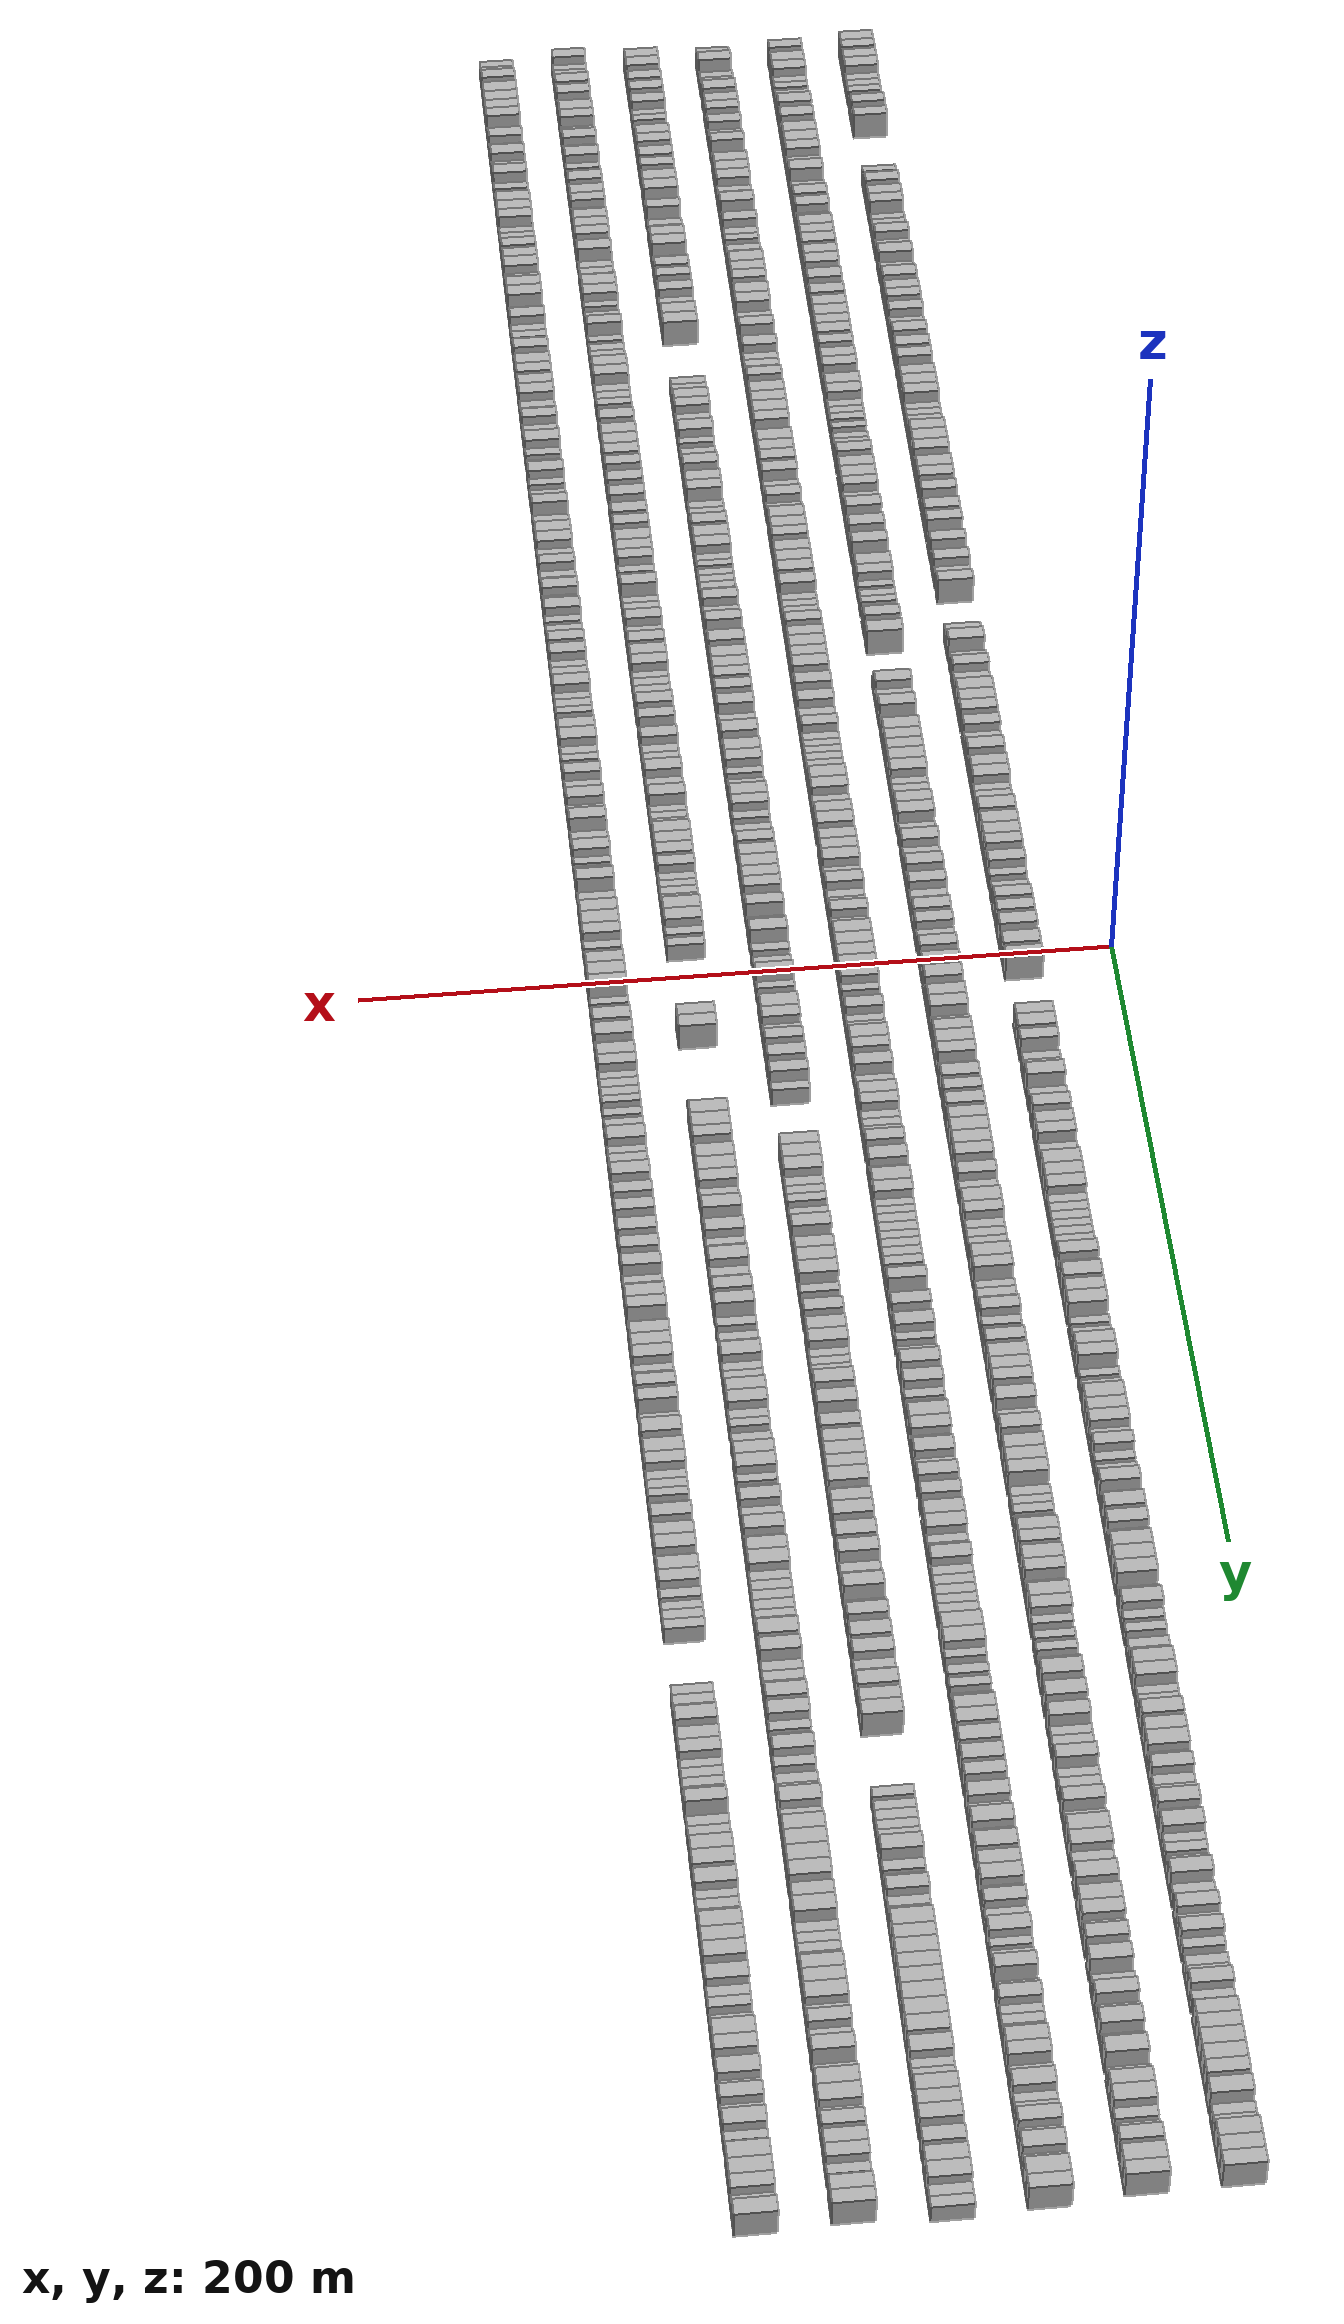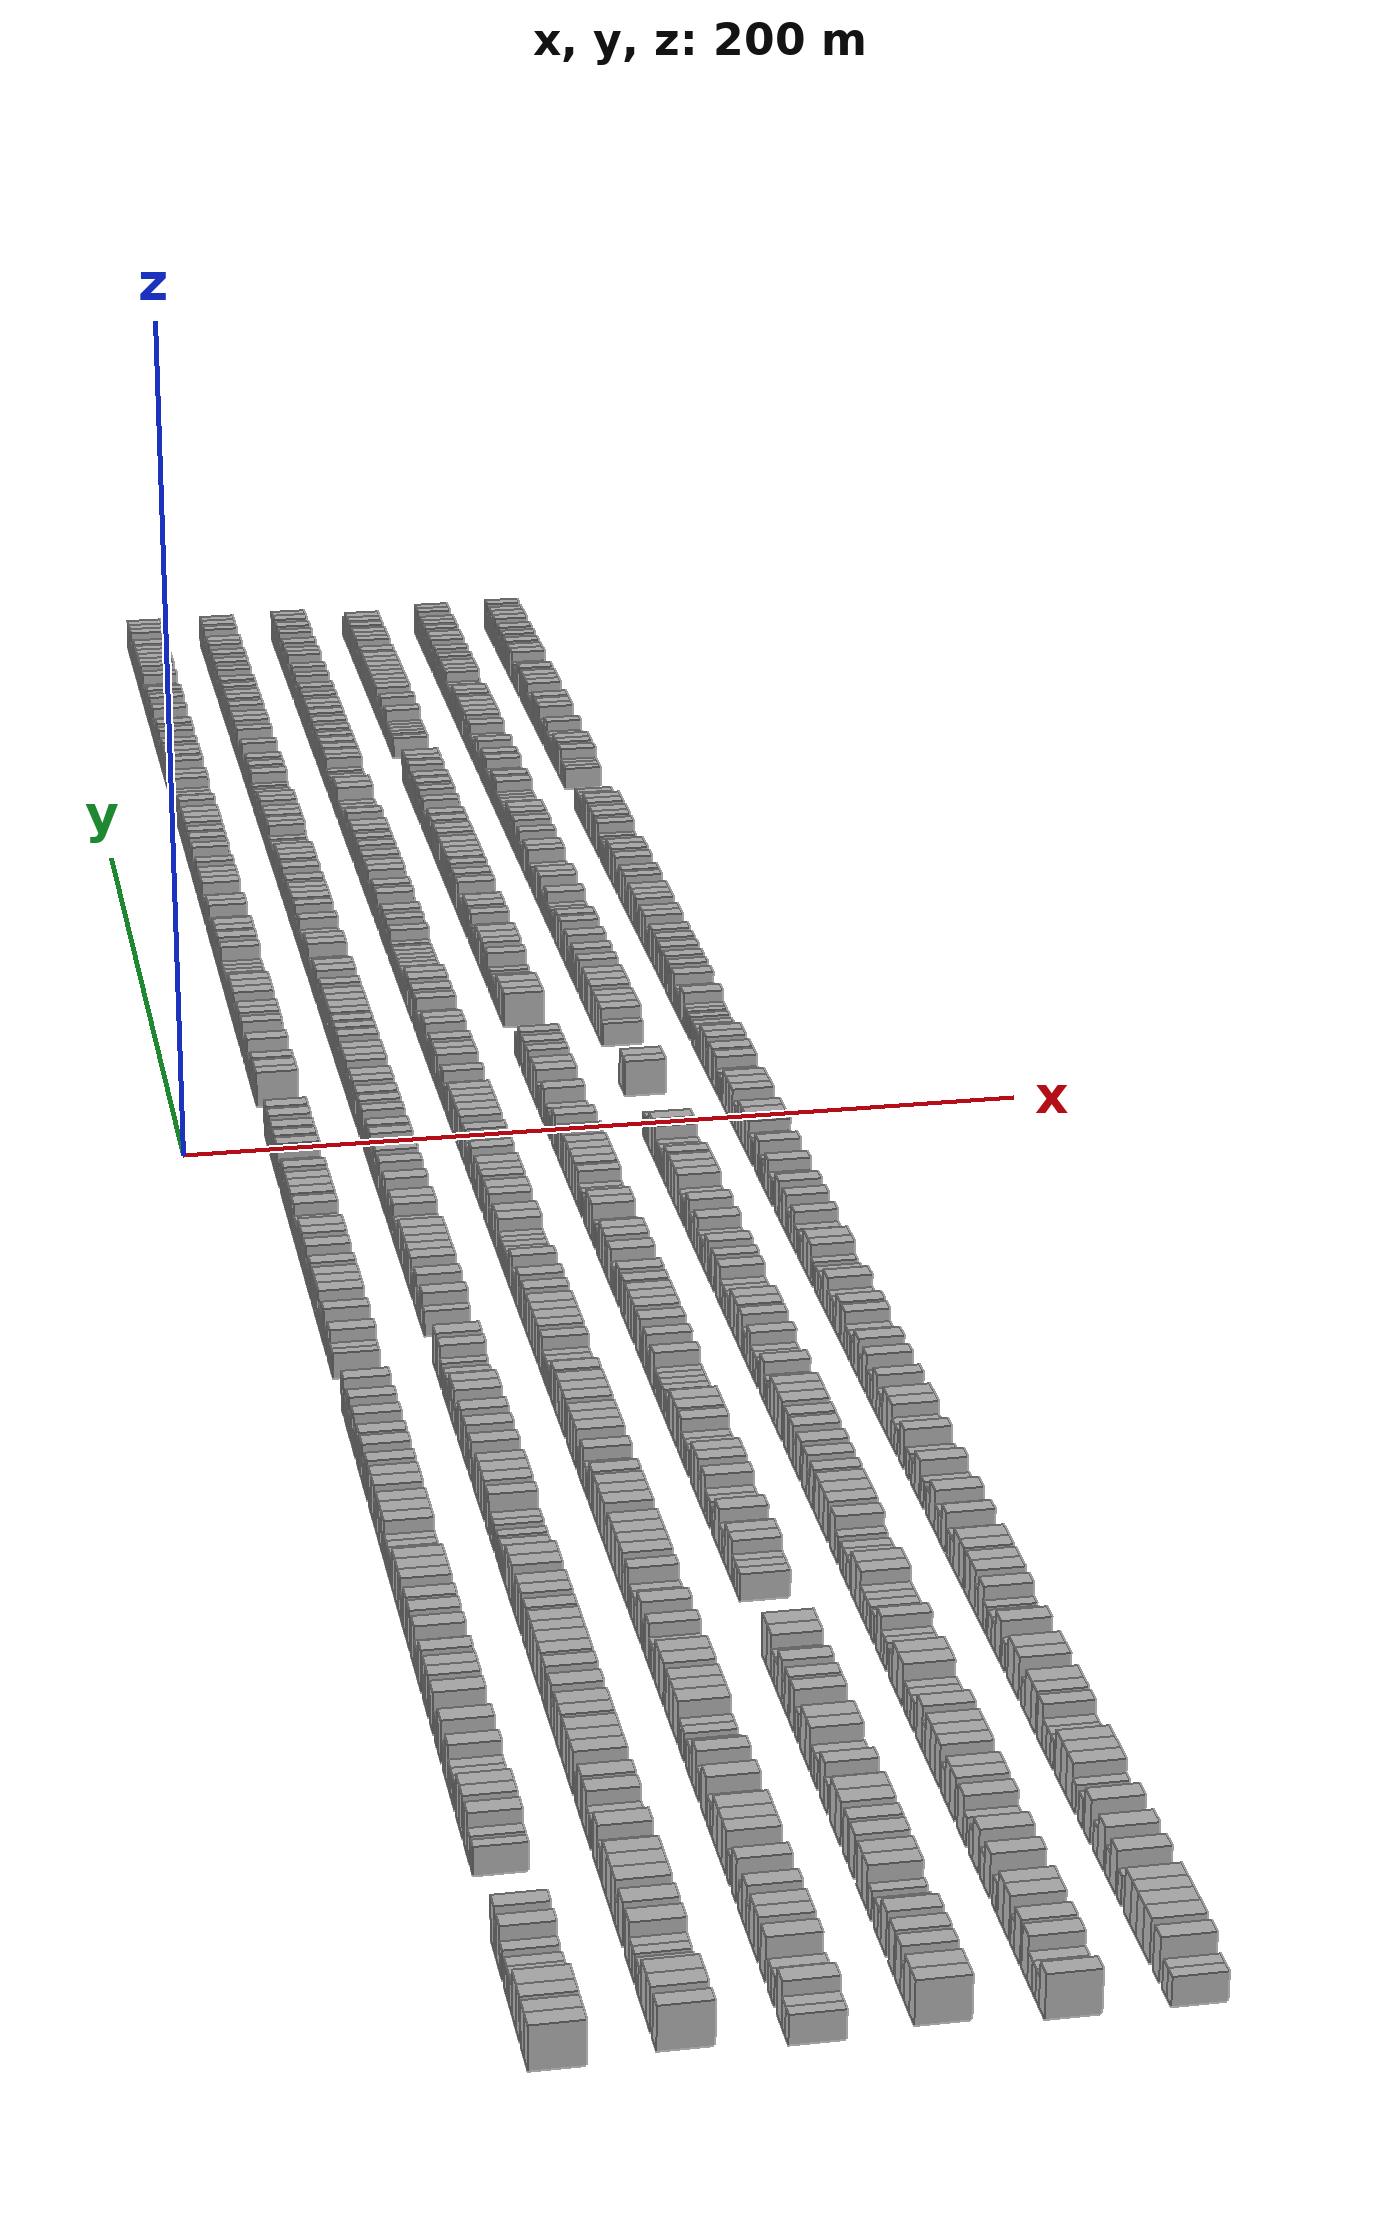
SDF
<sdf version="1.6">
 <world name="default">
  <scene>
   <sky><clouds><speed>12</speed></clouds></sky>
   <ambient>0.4 0.4 0.4 1</ambient>
   <background>0.7 0.7 0.7 1</background>
   <shadows>1</shadows>
  </scene>
  <gravity>0 0 -9.8066</gravity>
  <magnetic_field>6e-06 2.3e-05 -4.2e-05</magnetic_field>
  <physics default="0" name="default_physics" type="ode">
   <ode>
    <solver>
     <type>quick</type>
     <iters>10</iters>
     <sor>1.0</sor>
     <use_dynamic_moi_rescaling>0</use_dynamic_moi_rescaling>
    </solver>
    <constraints>
     <cfm>0</cfm>
     <erp>0.2</erp>
     <contact_max_correcting_vel>100</contact_max_correcting_vel>
     <contact_surface_layer>0.001</contact_surface_layer>
    </constraints>
   </ode>
   <max_step_size>0.004</max_step_size>
   <real_time_factor>1</real_time_factor>
   <real_time_update_rate>250</real_time_update_rate>
  </physics>
  <light name="sun" type="directional">
   <pose>0 0 10 0 0 0</pose>
   <diffuse>0.8 0.8 0.8 1</diffuse>
   <specular>0.2 0.2 0.2 1</specular>
   <attenuation>
    <range>1000</range>
    <constant>0.9</constant>
    <linear>0.01</linear>
    <quadratic>0.001</quadratic>
   </attenuation>
   <direction>-0.5 0.1 -0.9</direction>
  </light>
  <model name="building_1">
   <static>1</static>
   <pose>25.0000 -378.0551 0 0.000000 0.000000 0.000000</pose>
   <link name="link">
    <pose>0 0 4.50 0 0 0</pose>
    <collision name="collision"><geometry><box><size>10.0000 3.8898 9.0000</size></box></geometry></collision>
    <visual name="visual">
     <cast_shadows>0</cast_shadows>
     <geometry><box><size>10.0000 3.8898 9.0000</size></box></geometry>
     <material>
      <script>
       <uri>model://HANNAS_wall/materials/scripts</uri>
       <uri>model://HANNAS_wall/materials/textures</uri>
       <name>vrc/HANNAS_wall</name>
      </script>
     </material>
    </visual>
   </link>
  </model>
  <model name="building_2">
   <static>1</static>
   <pose>25.0000 -374.2977 0 0.000000 0.000000 0.000000</pose>
   <link name="link">
    <pose>0 0 4.50 0 0 0</pose>
    <collision name="collision"><geometry><box><size>10.0000 3.6250 9.0000</size></box></geometry></collision>
    <visual name="visual">
     <cast_shadows>0</cast_shadows>
     <geometry><box><size>10.0000 3.6250 9.0000</size></box></geometry>
     <material>
      <script>
       <uri>model://HANNAS_wall/materials/scripts</uri>
       <uri>model://HANNAS_wall/materials/textures</uri>
       <name>vrc/HANNAS_wall</name>
      </script>
     </material>
    </visual>
   </link>
  </model>
  <model name="building_3">
   <static>1</static>
   <pose>25.0000 -369.5927 0 0.000000 0.000000 0.000000</pose>
   <link name="link">
    <pose>0 0 4.50 0 0 0</pose>
    <collision name="collision"><geometry><box><size>10.0000 3.7850 9.0000</size></box></geometry></collision>
    <visual name="visual">
     <cast_shadows>0</cast_shadows>
     <geometry><box><size>10.0000 3.7850 9.0000</size></box></geometry>
     <material>
      <script>
       <uri>model://HANNAS_wall/materials/scripts</uri>
       <uri>model://HANNAS_wall/materials/textures</uri>
       <name>vrc/HANNAS_wall</name>
      </script>
     </material>
    </visual>
   </link>
  </model>
  <model name="building_4">
   <static>1</static>
   <pose>25.0000 -365.4799 0 0.000000 0.000000 0.000000</pose>
   <link name="link">
    <pose>0 0 4.50 0 0 0</pose>
    <collision name="collision"><geometry><box><size>10.0000 4.4405 9.0000</size></box></geometry></collision>
    <visual name="visual">
     <cast_shadows>0</cast_shadows>
     <geometry><box><size>10.0000 4.4405 9.0000</size></box></geometry>
     <material>
      <script>
       <uri>model://HANNAS_wall/materials/scripts</uri>
       <uri>model://HANNAS_wall/materials/textures</uri>
       <name>vrc/HANNAS_wall</name>
      </script>
     </material>
    </visual>
   </link>
  </model>
  <model name="building_5">
   <static>1</static>
   <pose>25.0000 -361.8172 0 0.000000 0.000000 0.000000</pose>
   <link name="link">
    <pose>0 0 3.00 0 0 0</pose>
    <collision name="collision"><geometry><box><size>10.0000 2.8849 6.0000</size></box></geometry></collision>
    <visual name="visual">
     <cast_shadows>0</cast_shadows>
     <geometry><box><size>10.0000 2.8849 6.0000</size></box></geometry>
     <material>
      <script>
       <uri>model://HANNAS_wall/materials/scripts</uri>
       <uri>model://HANNAS_wall/materials/textures</uri>
       <name>vrc/HANNAS_wall</name>
      </script>
     </material>
    </visual>
   </link>
  </model>
  <model name="building_6">
   <static>1</static>
   <pose>25.0000 -358.9868 0 0.000000 0.000000 0.000000</pose>
   <link name="link">
    <pose>0 0 3.00 0 0 0</pose>
    <collision name="collision"><geometry><box><size>10.0000 2.7758 6.0000</size></box></geometry></collision>
    <visual name="visual">
     <cast_shadows>0</cast_shadows>
     <geometry><box><size>10.0000 2.7758 6.0000</size></box></geometry>
     <material>
      <script>
       <uri>model://HANNAS_wall/materials/scripts</uri>
       <uri>model://HANNAS_wall/materials/textures</uri>
       <name>vrc/HANNAS_wall</name>
      </script>
     </material>
    </visual>
   </link>
  </model>
  <model name="building_7">
   <static>1</static>
   <pose>25.0000 -356.1821 0 0.000000 0.000000 0.000000</pose>
   <link name="link">
    <pose>0 0 3.00 0 0 0</pose>
    <collision name="collision"><geometry><box><size>10.0000 2.8337 6.0000</size></box></geometry></collision>
    <visual name="visual">
     <cast_shadows>0</cast_shadows>
     <geometry><box><size>10.0000 2.8337 6.0000</size></box></geometry>
     <material>
      <script>
       <uri>model://HANNAS_wall/materials/scripts</uri>
       <uri>model://HANNAS_wall/materials/textures</uri>
       <name>vrc/HANNAS_wall</name>
      </script>
     </material>
    </visual>
   </link>
  </model>
  <model name="building_8">
   <static>1</static>
   <pose>25.0000 -351.3265 0 0.000000 0.000000 0.000000</pose>
   <link name="link">
    <pose>0 0 3.00 0 0 0</pose>
    <collision name="collision"><geometry><box><size>10.0000 2.8775 6.0000</size></box></geometry></collision>
    <visual name="visual">
     <cast_shadows>0</cast_shadows>
     <geometry><box><size>10.0000 2.8775 6.0000</size></box></geometry>
     <material>
      <script>
       <uri>model://HANNAS_wall/materials/scripts</uri>
       <uri>model://HANNAS_wall/materials/textures</uri>
       <name>vrc/HANNAS_wall</name>
      </script>
     </material>
    </visual>
   </link>
  </model>
  <model name="building_9">
   <static>1</static>
   <pose>25.0000 -347.9965 0 0.000000 0.000000 0.000000</pose>
   <link name="link">
    <pose>0 0 4.50 0 0 0</pose>
    <collision name="collision"><geometry><box><size>10.0000 3.7824 9.0000</size></box></geometry></collision>
    <visual name="visual">
     <cast_shadows>0</cast_shadows>
     <geometry><box><size>10.0000 3.7824 9.0000</size></box></geometry>
     <material>
      <script>
       <uri>model://HANNAS_wall/materials/scripts</uri>
       <uri>model://HANNAS_wall/materials/textures</uri>
       <name>vrc/HANNAS_wall</name>
      </script>
     </material>
    </visual>
   </link>
  </model>
  <model name="building_10">
   <static>1</static>
   <pose>25.0000 -344.8504 0 0.000000 0.000000 0.000000</pose>
   <link name="link">
    <pose>0 0 3.00 0 0 0</pose>
    <collision name="collision"><geometry><box><size>10.0000 2.5098 6.0000</size></box></geometry></collision>
    <visual name="visual">
     <cast_shadows>0</cast_shadows>
     <geometry><box><size>10.0000 2.5098 6.0000</size></box></geometry>
     <material>
      <script>
       <uri>model://HANNAS_wall/materials/scripts</uri>
       <uri>model://HANNAS_wall/materials/textures</uri>
       <name>vrc/HANNAS_wall</name>
      </script>
     </material>
    </visual>
   </link>
  </model>
  <model name="building_11">
   <static>1</static>
   <pose>25.0000 -341.7378 0 0.000000 0.000000 0.000000</pose>
   <link name="link">
    <pose>0 0 4.50 0 0 0</pose>
    <collision name="collision"><geometry><box><size>10.0000 3.7155 9.0000</size></box></geometry></collision>
    <visual name="visual">
     <cast_shadows>0</cast_shadows>
     <geometry><box><size>10.0000 3.7155 9.0000</size></box></geometry>
     <material>
      <script>
       <uri>model://HANNAS_wall/materials/scripts</uri>
       <uri>model://HANNAS_wall/materials/textures</uri>
       <name>vrc/HANNAS_wall</name>
      </script>
     </material>
    </visual>
   </link>
  </model>
  <model name="building_12">
   <static>1</static>
   <pose>25.0000 -318.1949 0 0.000000 0.000000 0.000000</pose>
   <link name="link">
    <pose>0 0 3.00 0 0 0</pose>
    <collision name="collision"><geometry><box><size>10.0000 2.4568 6.0000</size></box></geometry></collision>
    <visual name="visual">
     <cast_shadows>0</cast_shadows>
     <geometry><box><size>10.0000 2.4568 6.0000</size></box></geometry>
     <material>
      <script>
       <uri>model://HANNAS_wall/materials/scripts</uri>
       <uri>model://HANNAS_wall/materials/textures</uri>
       <name>vrc/HANNAS_wall</name>
      </script>
     </material>
    </visual>
   </link>
  </model>
  <model name="building_13">
   <static>1</static>
   <pose>25.0000 -314.5028 0 0.000000 0.000000 0.000000</pose>
   <link name="link">
    <pose>0 0 3.00 0 0 0</pose>
    <collision name="collision"><geometry><box><size>10.0000 2.9275 6.0000</size></box></geometry></collision>
    <visual name="visual">
     <cast_shadows>0</cast_shadows>
     <geometry><box><size>10.0000 2.9275 6.0000</size></box></geometry>
     <material>
      <script>
       <uri>model://HANNAS_wall/materials/scripts</uri>
       <uri>model://HANNAS_wall/materials/textures</uri>
       <name>vrc/HANNAS_wall</name>
      </script>
     </material>
    </visual>
   </link>
  </model>
  <model name="building_14">
   <static>1</static>
   <pose>25.0000 -311.0786 0 0.000000 0.000000 0.000000</pose>
   <link name="link">
    <pose>0 0 4.50 0 0 0</pose>
    <collision name="collision"><geometry><box><size>10.0000 3.9210 9.0000</size></box></geometry></collision>
    <visual name="visual">
     <cast_shadows>0</cast_shadows>
     <geometry><box><size>10.0000 3.9210 9.0000</size></box></geometry>
     <material>
      <script>
       <uri>model://HANNAS_wall/materials/scripts</uri>
       <uri>model://HANNAS_wall/materials/textures</uri>
       <name>vrc/HANNAS_wall</name>
      </script>
     </material>
    </visual>
   </link>
  </model>
  <model name="building_15">
   <static>1</static>
   <pose>25.0000 -305.2178 0 0.000000 0.000000 0.000000</pose>
   <link name="link">
    <pose>0 0 4.50 0 0 0</pose>
    <collision name="collision"><geometry><box><size>10.0000 3.8006 9.0000</size></box></geometry></collision>
    <visual name="visual">
     <cast_shadows>0</cast_shadows>
     <geometry><box><size>10.0000 3.8006 9.0000</size></box></geometry>
     <material>
      <script>
       <uri>model://HANNAS_wall/materials/scripts</uri>
       <uri>model://HANNAS_wall/materials/textures</uri>
       <name>vrc/HANNAS_wall</name>
      </script>
     </material>
    </visual>
   </link>
  </model>
  <model name="building_16">
   <static>1</static>
   <pose>25.0000 -301.3512 0 0.000000 0.000000 0.000000</pose>
   <link name="link">
    <pose>0 0 4.50 0 0 0</pose>
    <collision name="collision"><geometry><box><size>10.0000 3.9326 9.0000</size></box></geometry></collision>
    <visual name="visual">
     <cast_shadows>0</cast_shadows>
     <geometry><box><size>10.0000 3.9326 9.0000</size></box></geometry>
     <material>
      <script>
       <uri>model://HANNAS_wall/materials/scripts</uri>
       <uri>model://HANNAS_wall/materials/textures</uri>
       <name>vrc/HANNAS_wall</name>
      </script>
     </material>
    </visual>
   </link>
  </model>
  <model name="building_17">
   <static>1</static>
   <pose>25.0000 -296.1705 0 0.000000 0.000000 0.000000</pose>
   <link name="link">
    <pose>0 0 3.00 0 0 0</pose>
    <collision name="collision"><geometry><box><size>10.0000 2.4288 6.0000</size></box></geometry></collision>
    <visual name="visual">
     <cast_shadows>0</cast_shadows>
     <geometry><box><size>10.0000 2.4288 6.0000</size></box></geometry>
     <material>
      <script>
       <uri>model://HANNAS_wall/materials/scripts</uri>
       <uri>model://HANNAS_wall/materials/textures</uri>
       <name>vrc/HANNAS_wall</name>
      </script>
     </material>
    </visual>
   </link>
  </model>
  <model name="building_18">
   <static>1</static>
   <pose>25.0000 -293.6115 0 0.000000 0.000000 0.000000</pose>
   <link name="link">
    <pose>0 0 3.00 0 0 0</pose>
    <collision name="collision"><geometry><box><size>10.0000 2.6891 6.0000</size></box></geometry></collision>
    <visual name="visual">
     <cast_shadows>0</cast_shadows>
     <geometry><box><size>10.0000 2.6891 6.0000</size></box></geometry>
     <material>
      <script>
       <uri>model://HANNAS_wall/materials/scripts</uri>
       <uri>model://HANNAS_wall/materials/textures</uri>
       <name>vrc/HANNAS_wall</name>
      </script>
     </material>
    </visual>
   </link>
  </model>
  <model name="building_19">
   <static>1</static>
   <pose>25.0000 -290.8192 0 0.000000 0.000000 0.000000</pose>
   <link name="link">
    <pose>0 0 3.00 0 0 0</pose>
    <collision name="collision"><geometry><box><size>10.0000 2.8954 6.0000</size></box></geometry></collision>
    <visual name="visual">
     <cast_shadows>0</cast_shadows>
     <geometry><box><size>10.0000 2.8954 6.0000</size></box></geometry>
     <material>
      <script>
       <uri>model://HANNAS_wall/materials/scripts</uri>
       <uri>model://HANNAS_wall/materials/textures</uri>
       <name>vrc/HANNAS_wall</name>
      </script>
     </material>
    </visual>
   </link>
  </model>
  <model name="building_20">
   <static>1</static>
   <pose>25.0000 -287.4225 0 0.000000 0.000000 0.000000</pose>
   <link name="link">
    <pose>0 0 4.50 0 0 0</pose>
    <collision name="collision"><geometry><box><size>10.0000 3.8981 9.0000</size></box></geometry></collision>
    <visual name="visual">
     <cast_shadows>0</cast_shadows>
     <geometry><box><size>10.0000 3.8981 9.0000</size></box></geometry>
     <material>
      <script>
       <uri>model://HANNAS_wall/materials/scripts</uri>
       <uri>model://HANNAS_wall/materials/textures</uri>
       <name>vrc/HANNAS_wall</name>
      </script>
     </material>
    </visual>
   </link>
  </model>
  <model name="building_21">
   <static>1</static>
   <pose>25.0000 -284.0055 0 0.000000 0.000000 0.000000</pose>
   <link name="link">
    <pose>0 0 3.00 0 0 0</pose>
    <collision name="collision"><geometry><box><size>10.0000 2.9358 6.0000</size></box></geometry></collision>
    <visual name="visual">
     <cast_shadows>0</cast_shadows>
     <geometry><box><size>10.0000 2.9358 6.0000</size></box></geometry>
     <material>
      <script>
       <uri>model://HANNAS_wall/materials/scripts</uri>
       <uri>model://HANNAS_wall/materials/textures</uri>
       <name>vrc/HANNAS_wall</name>
      </script>
     </material>
    </visual>
   </link>
  </model>
  <model name="building_22">
   <static>1</static>
   <pose>25.0000 -278.3851 0 0.000000 0.000000 0.000000</pose>
   <link name="link">
    <pose>0 0 4.50 0 0 0</pose>
    <collision name="collision"><geometry><box><size>10.0000 4.3049 9.0000</size></box></geometry></collision>
    <visual name="visual">
     <cast_shadows>0</cast_shadows>
     <geometry><box><size>10.0000 4.3049 9.0000</size></box></geometry>
     <material>
      <script>
       <uri>model://HANNAS_wall/materials/scripts</uri>
       <uri>model://HANNAS_wall/materials/textures</uri>
       <name>vrc/HANNAS_wall</name>
      </script>
     </material>
    </visual>
   </link>
  </model>
  <model name="building_23">
   <static>1</static>
   <pose>25.0000 -273.7490 0 0.000000 0.000000 0.000000</pose>
   <link name="link">
    <pose>0 0 3.00 0 0 0</pose>
    <collision name="collision"><geometry><box><size>10.0000 2.9674 6.0000</size></box></geometry></collision>
    <visual name="visual">
     <cast_shadows>0</cast_shadows>
     <geometry><box><size>10.0000 2.9674 6.0000</size></box></geometry>
     <material>
      <script>
       <uri>model://HANNAS_wall/materials/scripts</uri>
       <uri>model://HANNAS_wall/materials/textures</uri>
       <name>vrc/HANNAS_wall</name>
      </script>
     </material>
    </visual>
   </link>
  </model>
  <model name="building_24">
   <static>1</static>
   <pose>25.0000 -268.0605 0 0.000000 0.000000 0.000000</pose>
   <link name="link">
    <pose>0 0 4.50 0 0 0</pose>
    <collision name="collision"><geometry><box><size>10.0000 4.4095 9.0000</size></box></geometry></collision>
    <visual name="visual">
     <cast_shadows>0</cast_shadows>
     <geometry><box><size>10.0000 4.4095 9.0000</size></box></geometry>
     <material>
      <script>
       <uri>model://HANNAS_wall/materials/scripts</uri>
       <uri>model://HANNAS_wall/materials/textures</uri>
       <name>vrc/HANNAS_wall</name>
      </script>
     </material>
    </visual>
   </link>
  </model>
  <model name="building_25">
   <static>1</static>
   <pose>25.0000 -262.0357 0 0.000000 0.000000 0.000000</pose>
   <link name="link">
    <pose>0 0 4.50 0 0 0</pose>
    <collision name="collision"><geometry><box><size>10.0000 3.6402 9.0000</size></box></geometry></collision>
    <visual name="visual">
     <cast_shadows>0</cast_shadows>
     <geometry><box><size>10.0000 3.6402 9.0000</size></box></geometry>
     <material>
      <script>
       <uri>model://HANNAS_wall/materials/scripts</uri>
       <uri>model://HANNAS_wall/materials/textures</uri>
       <name>vrc/HANNAS_wall</name>
      </script>
     </material>
    </visual>
   </link>
  </model>
  <model name="building_26">
   <static>1</static>
   <pose>25.0000 -258.3685 0 0.000000 0.000000 0.000000</pose>
   <link name="link">
    <pose>0 0 4.50 0 0 0</pose>
    <collision name="collision"><geometry><box><size>10.0000 3.6942 9.0000</size></box></geometry></collision>
    <visual name="visual">
     <cast_shadows>0</cast_shadows>
     <geometry><box><size>10.0000 3.6942 9.0000</size></box></geometry>
     <material>
      <script>
       <uri>model://HANNAS_wall/materials/scripts</uri>
       <uri>model://HANNAS_wall/materials/textures</uri>
       <name>vrc/HANNAS_wall</name>
      </script>
     </material>
    </visual>
   </link>
  </model>
  <model name="building_27">
   <static>1</static>
   <pose>25.0000 -252.5782 0 0.000000 0.000000 0.000000</pose>
   <link name="link">
    <pose>0 0 4.50 0 0 0</pose>
    <collision name="collision"><geometry><box><size>10.0000 3.8863 9.0000</size></box></geometry></collision>
    <visual name="visual">
     <cast_shadows>0</cast_shadows>
     <geometry><box><size>10.0000 3.8863 9.0000</size></box></geometry>
     <material>
      <script>
       <uri>model://HANNAS_wall/materials/scripts</uri>
       <uri>model://HANNAS_wall/materials/textures</uri>
       <name>vrc/HANNAS_wall</name>
      </script>
     </material>
    </visual>
   </link>
  </model>
  <model name="building_28">
   <static>1</static>
   <pose>25.0000 -249.3838 0 0.000000 0.000000 0.000000</pose>
   <link name="link">
    <pose>0 0 3.00 0 0 0</pose>
    <collision name="collision"><geometry><box><size>10.0000 2.5026 6.0000</size></box></geometry></collision>
    <visual name="visual">
     <cast_shadows>0</cast_shadows>
     <geometry><box><size>10.0000 2.5026 6.0000</size></box></geometry>
     <material>
      <script>
       <uri>model://HANNAS_wall/materials/scripts</uri>
       <uri>model://HANNAS_wall/materials/textures</uri>
       <name>vrc/HANNAS_wall</name>
      </script>
     </material>
    </visual>
   </link>
  </model>
  <model name="building_29">
   <static>1</static>
   <pose>25.0000 -246.7000 0 0.000000 0.000000 0.000000</pose>
   <link name="link">
    <pose>0 0 3.00 0 0 0</pose>
    <collision name="collision"><geometry><box><size>10.0000 2.8650 6.0000</size></box></geometry></collision>
    <visual name="visual">
     <cast_shadows>0</cast_shadows>
     <geometry><box><size>10.0000 2.8650 6.0000</size></box></geometry>
     <material>
      <script>
       <uri>model://HANNAS_wall/materials/scripts</uri>
       <uri>model://HANNAS_wall/materials/textures</uri>
       <name>vrc/HANNAS_wall</name>
      </script>
     </material>
    </visual>
   </link>
  </model>
  <model name="building_30">
   <static>1</static>
   <pose>25.0000 -243.2070 0 0.000000 0.000000 0.000000</pose>
   <link name="link">
    <pose>0 0 4.50 0 0 0</pose>
    <collision name="collision"><geometry><box><size>10.0000 4.1211 9.0000</size></box></geometry></collision>
    <visual name="visual">
     <cast_shadows>0</cast_shadows>
     <geometry><box><size>10.0000 4.1211 9.0000</size></box></geometry>
     <material>
      <script>
       <uri>model://HANNAS_wall/materials/scripts</uri>
       <uri>model://HANNAS_wall/materials/textures</uri>
       <name>vrc/HANNAS_wall</name>
      </script>
     </material>
    </visual>
   </link>
  </model>
  <model name="building_31">
   <static>1</static>
   <pose>25.0000 -237.0426 0 0.000000 0.000000 0.000000</pose>
   <link name="link">
    <pose>0 0 4.50 0 0 0</pose>
    <collision name="collision"><geometry><box><size>10.0000 4.2076 9.0000</size></box></geometry></collision>
    <visual name="visual">
     <cast_shadows>0</cast_shadows>
     <geometry><box><size>10.0000 4.2076 9.0000</size></box></geometry>
     <material>
      <script>
       <uri>model://HANNAS_wall/materials/scripts</uri>
       <uri>model://HANNAS_wall/materials/textures</uri>
       <name>vrc/HANNAS_wall</name>
      </script>
     </material>
    </visual>
   </link>
  </model>
  <model name="building_32">
   <static>1</static>
   <pose>25.0000 -231.9022 0 0.000000 0.000000 0.000000</pose>
   <link name="link">
    <pose>0 0 4.50 0 0 0</pose>
    <collision name="collision"><geometry><box><size>10.0000 4.0731 9.0000</size></box></geometry></collision>
    <visual name="visual">
     <cast_shadows>0</cast_shadows>
     <geometry><box><size>10.0000 4.0731 9.0000</size></box></geometry>
     <material>
      <script>
       <uri>model://HANNAS_wall/materials/scripts</uri>
       <uri>model://HANNAS_wall/materials/textures</uri>
       <name>vrc/HANNAS_wall</name>
      </script>
     </material>
    </visual>
   </link>
  </model>
  <model name="building_33">
   <static>1</static>
   <pose>25.0000 -227.5604 0 0.000000 0.000000 0.000000</pose>
   <link name="link">
    <pose>0 0 3.00 0 0 0</pose>
    <collision name="collision"><geometry><box><size>10.0000 2.6106 6.0000</size></box></geometry></collision>
    <visual name="visual">
     <cast_shadows>0</cast_shadows>
     <geometry><box><size>10.0000 2.6106 6.0000</size></box></geometry>
     <material>
      <script>
       <uri>model://HANNAS_wall/materials/scripts</uri>
       <uri>model://HANNAS_wall/materials/textures</uri>
       <name>vrc/HANNAS_wall</name>
      </script>
     </material>
    </visual>
   </link>
  </model>
  <model name="building_34">
   <static>1</static>
   <pose>25.0000 -224.3440 0 0.000000 0.000000 0.000000</pose>
   <link name="link">
    <pose>0 0 4.50 0 0 0</pose>
    <collision name="collision"><geometry><box><size>10.0000 3.8222 9.0000</size></box></geometry></collision>
    <visual name="visual">
     <cast_shadows>0</cast_shadows>
     <geometry><box><size>10.0000 3.8222 9.0000</size></box></geometry>
     <material>
      <script>
       <uri>model://HANNAS_wall/materials/scripts</uri>
       <uri>model://HANNAS_wall/materials/textures</uri>
       <name>vrc/HANNAS_wall</name>
      </script>
     </material>
    </visual>
   </link>
  </model>
  <model name="building_35">
   <static>1</static>
   <pose>25.0000 -220.3021 0 0.000000 0.000000 0.000000</pose>
   <link name="link">
    <pose>0 0 4.50 0 0 0</pose>
    <collision name="collision"><geometry><box><size>10.0000 4.2617 9.0000</size></box></geometry></collision>
    <visual name="visual">
     <cast_shadows>0</cast_shadows>
     <geometry><box><size>10.0000 4.2617 9.0000</size></box></geometry>
     <material>
      <script>
       <uri>model://HANNAS_wall/materials/scripts</uri>
       <uri>model://HANNAS_wall/materials/textures</uri>
       <name>vrc/HANNAS_wall</name>
      </script>
     </material>
    </visual>
   </link>
  </model>
  <model name="building_36">
   <static>1</static>
   <pose>25.0000 -216.1199 0 0.000000 0.000000 0.000000</pose>
   <link name="link">
    <pose>0 0 4.50 0 0 0</pose>
    <collision name="collision"><geometry><box><size>10.0000 4.1026 9.0000</size></box></geometry></collision>
    <visual name="visual">
     <cast_shadows>0</cast_shadows>
     <geometry><box><size>10.0000 4.1026 9.0000</size></box></geometry>
     <material>
      <script>
       <uri>model://HANNAS_wall/materials/scripts</uri>
       <uri>model://HANNAS_wall/materials/textures</uri>
       <name>vrc/HANNAS_wall</name>
      </script>
     </material>
    </visual>
   </link>
  </model>
  <model name="building_37">
   <static>1</static>
   <pose>25.0000 -211.7622 0 0.000000 0.000000 0.000000</pose>
   <link name="link">
    <pose>0 0 3.00 0 0 0</pose>
    <collision name="collision"><geometry><box><size>10.0000 2.6128 6.0000</size></box></geometry></collision>
    <visual name="visual">
     <cast_shadows>0</cast_shadows>
     <geometry><box><size>10.0000 2.6128 6.0000</size></box></geometry>
     <material>
      <script>
       <uri>model://HANNAS_wall/materials/scripts</uri>
       <uri>model://HANNAS_wall/materials/textures</uri>
       <name>vrc/HANNAS_wall</name>
      </script>
     </material>
    </visual>
   </link>
  </model>
  <model name="building_38">
   <static>1</static>
   <pose>25.0000 -209.1768 0 0.000000 0.000000 0.000000</pose>
   <link name="link">
    <pose>0 0 3.00 0 0 0</pose>
    <collision name="collision"><geometry><box><size>10.0000 2.5580 6.0000</size></box></geometry></collision>
    <visual name="visual">
     <cast_shadows>0</cast_shadows>
     <geometry><box><size>10.0000 2.5580 6.0000</size></box></geometry>
     <material>
      <script>
       <uri>model://HANNAS_wall/materials/scripts</uri>
       <uri>model://HANNAS_wall/materials/textures</uri>
       <name>vrc/HANNAS_wall</name>
      </script>
     </material>
    </visual>
   </link>
  </model>
  <model name="building_39">
   <static>1</static>
   <pose>25.0000 -206.5880 0 0.000000 0.000000 0.000000</pose>
   <link name="link">
    <pose>0 0 3.00 0 0 0</pose>
    <collision name="collision"><geometry><box><size>10.0000 2.6196 6.0000</size></box></geometry></collision>
    <visual name="visual">
     <cast_shadows>0</cast_shadows>
     <geometry><box><size>10.0000 2.6196 6.0000</size></box></geometry>
     <material>
      <script>
       <uri>model://HANNAS_wall/materials/scripts</uri>
       <uri>model://HANNAS_wall/materials/textures</uri>
       <name>vrc/HANNAS_wall</name>
      </script>
     </material>
    </visual>
   </link>
  </model>
  <model name="building_40">
   <static>1</static>
   <pose>25.0000 -203.9817 0 0.000000 0.000000 0.000000</pose>
   <link name="link">
    <pose>0 0 3.00 0 0 0</pose>
    <collision name="collision"><geometry><box><size>10.0000 2.5929 6.0000</size></box></geometry></collision>
    <visual name="visual">
     <cast_shadows>0</cast_shadows>
     <geometry><box><size>10.0000 2.5929 6.0000</size></box></geometry>
     <material>
      <script>
       <uri>model://HANNAS_wall/materials/scripts</uri>
       <uri>model://HANNAS_wall/materials/textures</uri>
       <name>vrc/HANNAS_wall</name>
      </script>
     </material>
    </visual>
   </link>
  </model>
  <model name="building_41">
   <static>1</static>
   <pose>25.0000 -200.6774 0 0.000000 0.000000 0.000000</pose>
   <link name="link">
    <pose>0 0 4.50 0 0 0</pose>
    <collision name="collision"><geometry><box><size>10.0000 4.0157 9.0000</size></box></geometry></collision>
    <visual name="visual">
     <cast_shadows>0</cast_shadows>
     <geometry><box><size>10.0000 4.0157 9.0000</size></box></geometry>
     <material>
      <script>
       <uri>model://HANNAS_wall/materials/scripts</uri>
       <uri>model://HANNAS_wall/materials/textures</uri>
       <name>vrc/HANNAS_wall</name>
      </script>
     </material>
    </visual>
   </link>
  </model>
  <model name="building_42">
   <static>1</static>
   <pose>25.0000 -196.4793 0 0.000000 0.000000 0.000000</pose>
   <link name="link">
    <pose>0 0 4.50 0 0 0</pose>
    <collision name="collision"><geometry><box><size>10.0000 4.3804 9.0000</size></box></geometry></collision>
    <visual name="visual">
     <cast_shadows>0</cast_shadows>
     <geometry><box><size>10.0000 4.3804 9.0000</size></box></geometry>
     <material>
      <script>
       <uri>model://HANNAS_wall/materials/scripts</uri>
       <uri>model://HANNAS_wall/materials/textures</uri>
       <name>vrc/HANNAS_wall</name>
      </script>
     </material>
    </visual>
   </link>
  </model>
  <model name="building_43">
   <static>1</static>
   <pose>25.0000 -192.2540 0 0.000000 0.000000 0.000000</pose>
   <link name="link">
    <pose>0 0 4.50 0 0 0</pose>
    <collision name="collision"><geometry><box><size>10.0000 4.0702 9.0000</size></box></geometry></collision>
    <visual name="visual">
     <cast_shadows>0</cast_shadows>
     <geometry><box><size>10.0000 4.0702 9.0000</size></box></geometry>
     <material>
      <script>
       <uri>model://HANNAS_wall/materials/scripts</uri>
       <uri>model://HANNAS_wall/materials/textures</uri>
       <name>vrc/HANNAS_wall</name>
      </script>
     </material>
    </visual>
   </link>
  </model>
  <model name="building_44">
   <static>1</static>
   <pose>25.0000 -188.8417 0 0.000000 0.000000 0.000000</pose>
   <link name="link">
    <pose>0 0 3.00 0 0 0</pose>
    <collision name="collision"><geometry><box><size>10.0000 2.7544 6.0000</size></box></geometry></collision>
    <visual name="visual">
     <cast_shadows>0</cast_shadows>
     <geometry><box><size>10.0000 2.7544 6.0000</size></box></geometry>
     <material>
      <script>
       <uri>model://HANNAS_wall/materials/scripts</uri>
       <uri>model://HANNAS_wall/materials/textures</uri>
       <name>vrc/HANNAS_wall</name>
      </script>
     </material>
    </visual>
   </link>
  </model>
  <model name="building_45">
   <static>1</static>
   <pose>25.0000 -185.2528 0 0.000000 0.000000 0.000000</pose>
   <link name="link">
    <pose>0 0 4.50 0 0 0</pose>
    <collision name="collision"><geometry><box><size>10.0000 4.4235 9.0000</size></box></geometry></collision>
    <visual name="visual">
     <cast_shadows>0</cast_shadows>
     <geometry><box><size>10.0000 4.4235 9.0000</size></box></geometry>
     <material>
      <script>
       <uri>model://HANNAS_wall/materials/scripts</uri>
       <uri>model://HANNAS_wall/materials/textures</uri>
       <name>vrc/HANNAS_wall</name>
      </script>
     </material>
    </visual>
   </link>
  </model>
  <model name="building_46">
   <static>1</static>
   <pose>25.0000 -180.9691 0 0.000000 0.000000 0.000000</pose>
   <link name="link">
    <pose>0 0 4.50 0 0 0</pose>
    <collision name="collision"><geometry><box><size>10.0000 4.1439 9.0000</size></box></geometry></collision>
    <visual name="visual">
     <cast_shadows>0</cast_shadows>
     <geometry><box><size>10.0000 4.1439 9.0000</size></box></geometry>
     <material>
      <script>
       <uri>model://HANNAS_wall/materials/scripts</uri>
       <uri>model://HANNAS_wall/materials/textures</uri>
       <name>vrc/HANNAS_wall</name>
      </script>
     </material>
    </visual>
   </link>
  </model>
  <model name="building_47">
   <static>1</static>
   <pose>25.0000 -174.9923 0 0.000000 0.000000 0.000000</pose>
   <link name="link">
    <pose>0 0 4.50 0 0 0</pose>
    <collision name="collision"><geometry><box><size>10.0000 3.8098 9.0000</size></box></geometry></collision>
    <visual name="visual">
     <cast_shadows>0</cast_shadows>
     <geometry><box><size>10.0000 3.8098 9.0000</size></box></geometry>
     <material>
      <script>
       <uri>model://HANNAS_wall/materials/scripts</uri>
       <uri>model://HANNAS_wall/materials/textures</uri>
       <name>vrc/HANNAS_wall</name>
      </script>
     </material>
    </visual>
   </link>
  </model>
  <model name="building_48">
   <static>1</static>
   <pose>25.0000 -170.8247 0 0.000000 0.000000 0.000000</pose>
   <link name="link">
    <pose>0 0 3.00 0 0 0</pose>
    <collision name="collision"><geometry><box><size>10.0000 2.5252 6.0000</size></box></geometry></collision>
    <visual name="visual">
     <cast_shadows>0</cast_shadows>
     <geometry><box><size>10.0000 2.5252 6.0000</size></box></geometry>
     <material>
      <script>
       <uri>model://HANNAS_wall/materials/scripts</uri>
       <uri>model://HANNAS_wall/materials/textures</uri>
       <name>vrc/HANNAS_wall</name>
      </script>
     </material>
    </visual>
   </link>
  </model>
  <model name="building_49">
   <static>1</static>
   <pose>25.0000 -167.4448 0 0.000000 0.000000 0.000000</pose>
   <link name="link">
    <pose>0 0 4.50 0 0 0</pose>
    <collision name="collision"><geometry><box><size>10.0000 4.2347 9.0000</size></box></geometry></collision>
    <visual name="visual">
     <cast_shadows>0</cast_shadows>
     <geometry><box><size>10.0000 4.2347 9.0000</size></box></geometry>
     <material>
      <script>
       <uri>model://HANNAS_wall/materials/scripts</uri>
       <uri>model://HANNAS_wall/materials/textures</uri>
       <name>vrc/HANNAS_wall</name>
      </script>
     </material>
    </visual>
   </link>
  </model>
  <model name="building_50">
   <static>1</static>
   <pose>25.0000 -162.3465 0 0.000000 0.000000 0.000000</pose>
   <link name="link">
    <pose>0 0 4.50 0 0 0</pose>
    <collision name="collision"><geometry><box><size>10.0000 3.9619 9.0000</size></box></geometry></collision>
    <visual name="visual">
     <cast_shadows>0</cast_shadows>
     <geometry><box><size>10.0000 3.9619 9.0000</size></box></geometry>
     <material>
      <script>
       <uri>model://HANNAS_wall/materials/scripts</uri>
       <uri>model://HANNAS_wall/materials/textures</uri>
       <name>vrc/HANNAS_wall</name>
      </script>
     </material>
    </visual>
   </link>
  </model>
  <model name="building_51">
   <static>1</static>
   <pose>25.0000 -157.0971 0 0.000000 0.000000 0.000000</pose>
   <link name="link">
    <pose>0 0 3.00 0 0 0</pose>
    <collision name="collision"><geometry><box><size>10.0000 2.5369 6.0000</size></box></geometry></collision>
    <visual name="visual">
     <cast_shadows>0</cast_shadows>
     <geometry><box><size>10.0000 2.5369 6.0000</size></box></geometry>
     <material>
      <script>
       <uri>model://HANNAS_wall/materials/scripts</uri>
       <uri>model://HANNAS_wall/materials/textures</uri>
       <name>vrc/HANNAS_wall</name>
      </script>
     </material>
    </visual>
   </link>
  </model>
  <model name="building_52">
   <static>1</static>
   <pose>25.0000 -153.9023 0 0.000000 0.000000 0.000000</pose>
   <link name="link">
    <pose>0 0 4.50 0 0 0</pose>
    <collision name="collision"><geometry><box><size>10.0000 3.8527 9.0000</size></box></geometry></collision>
    <visual name="visual">
     <cast_shadows>0</cast_shadows>
     <geometry><box><size>10.0000 3.8527 9.0000</size></box></geometry>
     <material>
      <script>
       <uri>model://HANNAS_wall/materials/scripts</uri>
       <uri>model://HANNAS_wall/materials/textures</uri>
       <name>vrc/HANNAS_wall</name>
      </script>
     </material>
    </visual>
   </link>
  </model>
  <model name="building_53">
   <static>1</static>
   <pose>25.0000 -149.5930 0 0.000000 0.000000 0.000000</pose>
   <link name="link">
    <pose>0 0 3.00 0 0 0</pose>
    <collision name="collision"><geometry><box><size>10.0000 2.7660 6.0000</size></box></geometry></collision>
    <visual name="visual">
     <cast_shadows>0</cast_shadows>
     <geometry><box><size>10.0000 2.7660 6.0000</size></box></geometry>
     <material>
      <script>
       <uri>model://HANNAS_wall/materials/scripts</uri>
       <uri>model://HANNAS_wall/materials/textures</uri>
       <name>vrc/HANNAS_wall</name>
      </script>
     </material>
    </visual>
   </link>
  </model>
  <model name="building_54">
   <static>1</static>
   <pose>25.0000 -146.2458 0 0.000000 0.000000 0.000000</pose>
   <link name="link">
    <pose>0 0 4.50 0 0 0</pose>
    <collision name="collision"><geometry><box><size>10.0000 3.9282 9.0000</size></box></geometry></collision>
    <visual name="visual">
     <cast_shadows>0</cast_shadows>
     <geometry><box><size>10.0000 3.9282 9.0000</size></box></geometry>
     <material>
      <script>
       <uri>model://HANNAS_wall/materials/scripts</uri>
       <uri>model://HANNAS_wall/materials/textures</uri>
       <name>vrc/HANNAS_wall</name>
      </script>
     </material>
    </visual>
   </link>
  </model>
  <model name="building_55">
   <static>1</static>
   <pose>25.0000 -142.7853 0 0.000000 0.000000 0.000000</pose>
   <link name="link">
    <pose>0 0 3.00 0 0 0</pose>
    <collision name="collision"><geometry><box><size>10.0000 2.9929 6.0000</size></box></geometry></collision>
    <visual name="visual">
     <cast_shadows>0</cast_shadows>
     <geometry><box><size>10.0000 2.9929 6.0000</size></box></geometry>
     <material>
      <script>
       <uri>model://HANNAS_wall/materials/scripts</uri>
       <uri>model://HANNAS_wall/materials/textures</uri>
       <name>vrc/HANNAS_wall</name>
      </script>
     </material>
    </visual>
   </link>
  </model>
  <model name="building_56">
   <static>1</static>
   <pose>25.0000 -137.4018 0 0.000000 0.000000 0.000000</pose>
   <link name="link">
    <pose>0 0 4.50 0 0 0</pose>
    <collision name="collision"><geometry><box><size>10.0000 3.7742 9.0000</size></box></geometry></collision>
    <visual name="visual">
     <cast_shadows>0</cast_shadows>
     <geometry><box><size>10.0000 3.7742 9.0000</size></box></geometry>
     <material>
      <script>
       <uri>model://HANNAS_wall/materials/scripts</uri>
       <uri>model://HANNAS_wall/materials/textures</uri>
       <name>vrc/HANNAS_wall</name>
      </script>
     </material>
    </visual>
   </link>
  </model>
  <model name="building_57">
   <static>1</static>
   <pose>25.0000 -119.8954 0 0.000000 0.000000 0.000000</pose>
   <link name="link">
    <pose>0 0 3.00 0 0 0</pose>
    <collision name="collision"><geometry><box><size>10.0000 2.4129 6.0000</size></box></geometry></collision>
    <visual name="visual">
     <cast_shadows>0</cast_shadows>
     <geometry><box><size>10.0000 2.4129 6.0000</size></box></geometry>
     <material>
      <script>
       <uri>model://HANNAS_wall/materials/scripts</uri>
       <uri>model://HANNAS_wall/materials/textures</uri>
       <name>vrc/HANNAS_wall</name>
      </script>
     </material>
    </visual>
   </link>
  </model>
  <model name="building_58">
   <static>1</static>
   <pose>25.0000 -117.3550 0 0.000000 0.000000 0.000000</pose>
   <link name="link">
    <pose>0 0 3.00 0 0 0</pose>
    <collision name="collision"><geometry><box><size>10.0000 2.6679 6.0000</size></box></geometry></collision>
    <visual name="visual">
     <cast_shadows>0</cast_shadows>
     <geometry><box><size>10.0000 2.6679 6.0000</size></box></geometry>
     <material>
      <script>
       <uri>model://HANNAS_wall/materials/scripts</uri>
       <uri>model://HANNAS_wall/materials/textures</uri>
       <name>vrc/HANNAS_wall</name>
      </script>
     </material>
    </visual>
   </link>
  </model>
  <model name="building_59">
   <static>1</static>
   <pose>25.0000 -113.9517 0 0.000000 0.000000 0.000000</pose>
   <link name="link">
    <pose>0 0 4.50 0 0 0</pose>
    <collision name="collision"><geometry><box><size>10.0000 4.1386 9.0000</size></box></geometry></collision>
    <visual name="visual">
     <cast_shadows>0</cast_shadows>
     <geometry><box><size>10.0000 4.1386 9.0000</size></box></geometry>
     <material>
      <script>
       <uri>model://HANNAS_wall/materials/scripts</uri>
       <uri>model://HANNAS_wall/materials/textures</uri>
       <name>vrc/HANNAS_wall</name>
      </script>
     </material>
    </visual>
   </link>
  </model>
  <model name="building_60">
   <static>1</static>
   <pose>25.0000 -108.6662 0 0.000000 0.000000 0.000000</pose>
   <link name="link">
    <pose>0 0 3.00 0 0 0</pose>
    <collision name="collision"><geometry><box><size>10.0000 2.4325 6.0000</size></box></geometry></collision>
    <visual name="visual">
     <cast_shadows>0</cast_shadows>
     <geometry><box><size>10.0000 2.4325 6.0000</size></box></geometry>
     <material>
      <script>
       <uri>model://HANNAS_wall/materials/scripts</uri>
       <uri>model://HANNAS_wall/materials/textures</uri>
       <name>vrc/HANNAS_wall</name>
      </script>
     </material>
    </visual>
   </link>
  </model>
  <model name="building_61">
   <static>1</static>
   <pose>25.0000 -103.5919 0 0.000000 0.000000 0.000000</pose>
   <link name="link">
    <pose>0 0 4.50 0 0 0</pose>
    <collision name="collision"><geometry><box><size>10.0000 3.7161 9.0000</size></box></geometry></collision>
    <visual name="visual">
     <cast_shadows>0</cast_shadows>
     <geometry><box><size>10.0000 3.7161 9.0000</size></box></geometry>
     <material>
      <script>
       <uri>model://HANNAS_wall/materials/scripts</uri>
       <uri>model://HANNAS_wall/materials/textures</uri>
       <name>vrc/HANNAS_wall</name>
      </script>
     </material>
    </visual>
   </link>
  </model>
  <model name="building_62">
   <static>1</static>
   <pose>25.0000 -100.4993 0 0.000000 0.000000 0.000000</pose>
   <link name="link">
    <pose>0 0 3.00 0 0 0</pose>
    <collision name="collision"><geometry><box><size>10.0000 2.4692 6.0000</size></box></geometry></collision>
    <visual name="visual">
     <cast_shadows>0</cast_shadows>
     <geometry><box><size>10.0000 2.4692 6.0000</size></box></geometry>
     <material>
      <script>
       <uri>model://HANNAS_wall/materials/scripts</uri>
       <uri>model://HANNAS_wall/materials/textures</uri>
       <name>vrc/HANNAS_wall</name>
      </script>
     </material>
    </visual>
   </link>
  </model>
  <model name="building_63">
   <static>1</static>
   <pose>25.0000 -97.8105 0 0.000000 0.000000 0.000000</pose>
   <link name="link">
    <pose>0 0 3.00 0 0 0</pose>
    <collision name="collision"><geometry><box><size>10.0000 2.9084 6.0000</size></box></geometry></collision>
    <visual name="visual">
     <cast_shadows>0</cast_shadows>
     <geometry><box><size>10.0000 2.9084 6.0000</size></box></geometry>
     <material>
      <script>
       <uri>model://HANNAS_wall/materials/scripts</uri>
       <uri>model://HANNAS_wall/materials/textures</uri>
       <name>vrc/HANNAS_wall</name>
      </script>
     </material>
    </visual>
   </link>
  </model>
  <model name="building_64">
   <static>1</static>
   <pose>25.0000 -94.2156 0 0.000000 0.000000 0.000000</pose>
   <link name="link">
    <pose>0 0 4.50 0 0 0</pose>
    <collision name="collision"><geometry><box><size>10.0000 4.2814 9.0000</size></box></geometry></collision>
    <visual name="visual">
     <cast_shadows>0</cast_shadows>
     <geometry><box><size>10.0000 4.2814 9.0000</size></box></geometry>
     <material>
      <script>
       <uri>model://HANNAS_wall/materials/scripts</uri>
       <uri>model://HANNAS_wall/materials/textures</uri>
       <name>vrc/HANNAS_wall</name>
      </script>
     </material>
    </visual>
   </link>
  </model>
  <model name="building_65">
   <static>1</static>
   <pose>25.0000 -90.0520 0 0.000000 0.000000 0.000000</pose>
   <link name="link">
    <pose>0 0 4.50 0 0 0</pose>
    <collision name="collision"><geometry><box><size>10.0000 4.0459 9.0000</size></box></geometry></collision>
    <visual name="visual">
     <cast_shadows>0</cast_shadows>
     <geometry><box><size>10.0000 4.0459 9.0000</size></box></geometry>
     <material>
      <script>
       <uri>model://HANNAS_wall/materials/scripts</uri>
       <uri>model://HANNAS_wall/materials/textures</uri>
       <name>vrc/HANNAS_wall</name>
      </script>
     </material>
    </visual>
   </link>
  </model>
  <model name="building_66">
   <static>1</static>
   <pose>25.0000 -86.0623 0 0.000000 0.000000 0.000000</pose>
   <link name="link">
    <pose>0 0 4.50 0 0 0</pose>
    <collision name="collision"><geometry><box><size>10.0000 3.9334 9.0000</size></box></geometry></collision>
    <visual name="visual">
     <cast_shadows>0</cast_shadows>
     <geometry><box><size>10.0000 3.9334 9.0000</size></box></geometry>
     <material>
      <script>
       <uri>model://HANNAS_wall/materials/scripts</uri>
       <uri>model://HANNAS_wall/materials/textures</uri>
       <name>vrc/HANNAS_wall</name>
      </script>
     </material>
    </visual>
   </link>
  </model>
  <model name="building_67">
   <static>1</static>
   <pose>25.0000 -80.1384 0 0.000000 0.000000 0.000000</pose>
   <link name="link">
    <pose>0 0 4.50 0 0 0</pose>
    <collision name="collision"><geometry><box><size>10.0000 3.9143 9.0000</size></box></geometry></collision>
    <visual name="visual">
     <cast_shadows>0</cast_shadows>
     <geometry><box><size>10.0000 3.9143 9.0000</size></box></geometry>
     <material>
      <script>
       <uri>model://HANNAS_wall/materials/scripts</uri>
       <uri>model://HANNAS_wall/materials/textures</uri>
       <name>vrc/HANNAS_wall</name>
      </script>
     </material>
    </visual>
   </link>
  </model>
  <model name="building_68">
   <static>1</static>
   <pose>25.0000 -76.9751 0 0.000000 0.000000 0.000000</pose>
   <link name="link">
    <pose>0 0 3.00 0 0 0</pose>
    <collision name="collision"><geometry><box><size>10.0000 2.4124 6.0000</size></box></geometry></collision>
    <visual name="visual">
     <cast_shadows>0</cast_shadows>
     <geometry><box><size>10.0000 2.4124 6.0000</size></box></geometry>
     <material>
      <script>
       <uri>model://HANNAS_wall/materials/scripts</uri>
       <uri>model://HANNAS_wall/materials/textures</uri>
       <name>vrc/HANNAS_wall</name>
      </script>
     </material>
    </visual>
   </link>
  </model>
  <model name="building_69">
   <static>1</static>
   <pose>25.0000 -74.5090 0 0.000000 0.000000 0.000000</pose>
   <link name="link">
    <pose>0 0 3.00 0 0 0</pose>
    <collision name="collision"><geometry><box><size>10.0000 2.5198 6.0000</size></box></geometry></collision>
    <visual name="visual">
     <cast_shadows>0</cast_shadows>
     <geometry><box><size>10.0000 2.5198 6.0000</size></box></geometry>
     <material>
      <script>
       <uri>model://HANNAS_wall/materials/scripts</uri>
       <uri>model://HANNAS_wall/materials/textures</uri>
       <name>vrc/HANNAS_wall</name>
      </script>
     </material>
    </visual>
   </link>
  </model>
  <model name="building_70">
   <static>1</static>
   <pose>25.0000 -71.1109 0 0.000000 0.000000 0.000000</pose>
   <link name="link">
    <pose>0 0 4.50 0 0 0</pose>
    <collision name="collision"><geometry><box><size>10.0000 4.2764 9.0000</size></box></geometry></collision>
    <visual name="visual">
     <cast_shadows>0</cast_shadows>
     <geometry><box><size>10.0000 4.2764 9.0000</size></box></geometry>
     <material>
      <script>
       <uri>model://HANNAS_wall/materials/scripts</uri>
       <uri>model://HANNAS_wall/materials/textures</uri>
       <name>vrc/HANNAS_wall</name>
      </script>
     </material>
    </visual>
   </link>
  </model>
  <model name="building_71">
   <static>1</static>
   <pose>25.0000 -67.7124 0 0.000000 0.000000 0.000000</pose>
   <link name="link">
    <pose>0 0 3.00 0 0 0</pose>
    <collision name="collision"><geometry><box><size>10.0000 2.5205 6.0000</size></box></geometry></collision>
    <visual name="visual">
     <cast_shadows>0</cast_shadows>
     <geometry><box><size>10.0000 2.5205 6.0000</size></box></geometry>
     <material>
      <script>
       <uri>model://HANNAS_wall/materials/scripts</uri>
       <uri>model://HANNAS_wall/materials/textures</uri>
       <name>vrc/HANNAS_wall</name>
      </script>
     </material>
    </visual>
   </link>
  </model>
  <model name="building_72">
   <static>1</static>
   <pose>25.0000 -64.5187 0 0.000000 0.000000 0.000000</pose>
   <link name="link">
    <pose>0 0 4.50 0 0 0</pose>
    <collision name="collision"><geometry><box><size>10.0000 3.8669 9.0000</size></box></geometry></collision>
    <visual name="visual">
     <cast_shadows>0</cast_shadows>
     <geometry><box><size>10.0000 3.8669 9.0000</size></box></geometry>
     <material>
      <script>
       <uri>model://HANNAS_wall/materials/scripts</uri>
       <uri>model://HANNAS_wall/materials/textures</uri>
       <name>vrc/HANNAS_wall</name>
      </script>
     </material>
    </visual>
   </link>
  </model>
  <model name="building_73">
   <static>1</static>
   <pose>25.0000 -60.4254 0 0.000000 0.000000 0.000000</pose>
   <link name="link">
    <pose>0 0 4.50 0 0 0</pose>
    <collision name="collision"><geometry><box><size>10.0000 4.3197 9.0000</size></box></geometry></collision>
    <visual name="visual">
     <cast_shadows>0</cast_shadows>
     <geometry><box><size>10.0000 4.3197 9.0000</size></box></geometry>
     <material>
      <script>
       <uri>model://HANNAS_wall/materials/scripts</uri>
       <uri>model://HANNAS_wall/materials/textures</uri>
       <name>vrc/HANNAS_wall</name>
      </script>
     </material>
    </visual>
   </link>
  </model>
  <model name="building_74">
   <static>1</static>
   <pose>25.0000 -56.9800 0 0.000000 0.000000 0.000000</pose>
   <link name="link">
    <pose>0 0 3.00 0 0 0</pose>
    <collision name="collision"><geometry><box><size>10.0000 2.5711 6.0000</size></box></geometry></collision>
    <visual name="visual">
     <cast_shadows>0</cast_shadows>
     <geometry><box><size>10.0000 2.5711 6.0000</size></box></geometry>
     <material>
      <script>
       <uri>model://HANNAS_wall/materials/scripts</uri>
       <uri>model://HANNAS_wall/materials/textures</uri>
       <name>vrc/HANNAS_wall</name>
      </script>
     </material>
    </visual>
   </link>
  </model>
  <model name="building_75">
   <static>1</static>
   <pose>25.0000 -54.4780 0 0.000000 0.000000 0.000000</pose>
   <link name="link">
    <pose>0 0 3.00 0 0 0</pose>
    <collision name="collision"><geometry><box><size>10.0000 2.4328 6.0000</size></box></geometry></collision>
    <visual name="visual">
     <cast_shadows>0</cast_shadows>
     <geometry><box><size>10.0000 2.4328 6.0000</size></box></geometry>
     <material>
      <script>
       <uri>model://HANNAS_wall/materials/scripts</uri>
       <uri>model://HANNAS_wall/materials/textures</uri>
       <name>vrc/HANNAS_wall</name>
      </script>
     </material>
    </visual>
   </link>
  </model>
  <model name="building_76">
   <static>1</static>
   <pose>25.0000 -51.8587 0 0.000000 0.000000 0.000000</pose>
   <link name="link">
    <pose>0 0 3.00 0 0 0</pose>
    <collision name="collision"><geometry><box><size>10.0000 2.8059 6.0000</size></box></geometry></collision>
    <visual name="visual">
     <cast_shadows>0</cast_shadows>
     <geometry><box><size>10.0000 2.8059 6.0000</size></box></geometry>
     <material>
      <script>
       <uri>model://HANNAS_wall/materials/scripts</uri>
       <uri>model://HANNAS_wall/materials/textures</uri>
       <name>vrc/HANNAS_wall</name>
      </script>
     </material>
    </visual>
   </link>
  </model>
  <model name="building_77">
   <static>1</static>
   <pose>25.0000 -48.2150 0 0.000000 0.000000 0.000000</pose>
   <link name="link">
    <pose>0 0 4.50 0 0 0</pose>
    <collision name="collision"><geometry><box><size>10.0000 4.4815 9.0000</size></box></geometry></collision>
    <visual name="visual">
     <cast_shadows>0</cast_shadows>
     <geometry><box><size>10.0000 4.4815 9.0000</size></box></geometry>
     <material>
      <script>
       <uri>model://HANNAS_wall/materials/scripts</uri>
       <uri>model://HANNAS_wall/materials/textures</uri>
       <name>vrc/HANNAS_wall</name>
      </script>
     </material>
    </visual>
   </link>
  </model>
  <model name="building_78">
   <static>1</static>
   <pose>25.0000 -42.8183 0 0.000000 0.000000 0.000000</pose>
   <link name="link">
    <pose>0 0 4.50 0 0 0</pose>
    <collision name="collision"><geometry><box><size>10.0000 4.3119 9.0000</size></box></geometry></collision>
    <visual name="visual">
     <cast_shadows>0</cast_shadows>
     <geometry><box><size>10.0000 4.3119 9.0000</size></box></geometry>
     <material>
      <script>
       <uri>model://HANNAS_wall/materials/scripts</uri>
       <uri>model://HANNAS_wall/materials/textures</uri>
       <name>vrc/HANNAS_wall</name>
      </script>
     </material>
    </visual>
   </link>
  </model>
  <model name="building_79">
   <static>1</static>
   <pose>25.0000 -38.6219 0 0.000000 0.000000 0.000000</pose>
   <link name="link">
    <pose>0 0 4.50 0 0 0</pose>
    <collision name="collision"><geometry><box><size>10.0000 4.0809 9.0000</size></box></geometry></collision>
    <visual name="visual">
     <cast_shadows>0</cast_shadows>
     <geometry><box><size>10.0000 4.0809 9.0000</size></box></geometry>
     <material>
      <script>
       <uri>model://HANNAS_wall/materials/scripts</uri>
       <uri>model://HANNAS_wall/materials/textures</uri>
       <name>vrc/HANNAS_wall</name>
      </script>
     </material>
    </visual>
   </link>
  </model>
  <model name="building_80">
   <static>1</static>
   <pose>25.0000 -34.6649 0 0.000000 0.000000 0.000000</pose>
   <link name="link">
    <pose>0 0 4.50 0 0 0</pose>
    <collision name="collision"><geometry><box><size>10.0000 3.8331 9.0000</size></box></geometry></collision>
    <visual name="visual">
     <cast_shadows>0</cast_shadows>
     <geometry><box><size>10.0000 3.8331 9.0000</size></box></geometry>
     <material>
      <script>
       <uri>model://HANNAS_wall/materials/scripts</uri>
       <uri>model://HANNAS_wall/materials/textures</uri>
       <name>vrc/HANNAS_wall</name>
      </script>
     </material>
    </visual>
   </link>
  </model>
  <model name="building_81">
   <static>1</static>
   <pose>25.0000 -31.5385 0 0.000000 0.000000 0.000000</pose>
   <link name="link">
    <pose>0 0 3.00 0 0 0</pose>
    <collision name="collision"><geometry><box><size>10.0000 2.4197 6.0000</size></box></geometry></collision>
    <visual name="visual">
     <cast_shadows>0</cast_shadows>
     <geometry><box><size>10.0000 2.4197 6.0000</size></box></geometry>
     <material>
      <script>
       <uri>model://HANNAS_wall/materials/scripts</uri>
       <uri>model://HANNAS_wall/materials/textures</uri>
       <name>vrc/HANNAS_wall</name>
      </script>
     </material>
    </visual>
   </link>
  </model>
  <model name="building_82">
   <static>1</static>
   <pose>25.0000 -28.3246 0 0.000000 0.000000 0.000000</pose>
   <link name="link">
    <pose>0 0 4.50 0 0 0</pose>
    <collision name="collision"><geometry><box><size>10.0000 4.0081 9.0000</size></box></geometry></collision>
    <visual name="visual">
     <cast_shadows>0</cast_shadows>
     <geometry><box><size>10.0000 4.0081 9.0000</size></box></geometry>
     <material>
      <script>
       <uri>model://HANNAS_wall/materials/scripts</uri>
       <uri>model://HANNAS_wall/materials/textures</uri>
       <name>vrc/HANNAS_wall</name>
      </script>
     </material>
    </visual>
   </link>
  </model>
  <model name="building_83">
   <static>1</static>
   <pose>25.0000 -24.9534 0 0.000000 0.000000 0.000000</pose>
   <link name="link">
    <pose>0 0 3.00 0 0 0</pose>
    <collision name="collision"><geometry><box><size>10.0000 2.7344 6.0000</size></box></geometry></collision>
    <visual name="visual">
     <cast_shadows>0</cast_shadows>
     <geometry><box><size>10.0000 2.7344 6.0000</size></box></geometry>
     <material>
      <script>
       <uri>model://HANNAS_wall/materials/scripts</uri>
       <uri>model://HANNAS_wall/materials/textures</uri>
       <name>vrc/HANNAS_wall</name>
      </script>
     </material>
    </visual>
   </link>
  </model>
  <model name="building_84">
   <static>1</static>
   <pose>25.0000 -20.2362 0 0.000000 0.000000 0.000000</pose>
   <link name="link">
    <pose>0 0 3.00 0 0 0</pose>
    <collision name="collision"><geometry><box><size>10.0000 2.7000 6.0000</size></box></geometry></collision>
    <visual name="visual">
     <cast_shadows>0</cast_shadows>
     <geometry><box><size>10.0000 2.7000 6.0000</size></box></geometry>
     <material>
      <script>
       <uri>model://HANNAS_wall/materials/scripts</uri>
       <uri>model://HANNAS_wall/materials/textures</uri>
       <name>vrc/HANNAS_wall</name>
      </script>
     </material>
    </visual>
   </link>
  </model>
  <model name="building_85">
   <static>1</static>
   <pose>25.0000 -14.9564 0 0.000000 0.000000 0.000000</pose>
   <link name="link">
    <pose>0 0 4.50 0 0 0</pose>
    <collision name="collision"><geometry><box><size>10.0000 3.8596 9.0000</size></box></geometry></collision>
    <visual name="visual">
     <cast_shadows>0</cast_shadows>
     <geometry><box><size>10.0000 3.8596 9.0000</size></box></geometry>
     <material>
      <script>
       <uri>model://HANNAS_wall/materials/scripts</uri>
       <uri>model://HANNAS_wall/materials/textures</uri>
       <name>vrc/HANNAS_wall</name>
      </script>
     </material>
    </visual>
   </link>
  </model>
  <model name="building_86">
   <static>1</static>
   <pose>25.0000 -10.0906 0 0.000000 0.000000 0.000000</pose>
   <link name="link">
    <pose>0 0 4.50 0 0 0</pose>
    <collision name="collision"><geometry><box><size>10.0000 3.8721 9.0000</size></box></geometry></collision>
    <visual name="visual">
     <cast_shadows>0</cast_shadows>
     <geometry><box><size>10.0000 3.8721 9.0000</size></box></geometry>
     <material>
      <script>
       <uri>model://HANNAS_wall/materials/scripts</uri>
       <uri>model://HANNAS_wall/materials/textures</uri>
       <name>vrc/HANNAS_wall</name>
      </script>
     </material>
    </visual>
   </link>
  </model>
  <model name="building_87">
   <static>1</static>
   <pose>25.0000 -5.0628 0 0.000000 0.000000 0.000000</pose>
   <link name="link">
    <pose>0 0 4.50 0 0 0</pose>
    <collision name="collision"><geometry><box><size>10.0000 4.1833 9.0000</size></box></geometry></collision>
    <visual name="visual">
     <cast_shadows>0</cast_shadows>
     <geometry><box><size>10.0000 4.1833 9.0000</size></box></geometry>
     <material>
      <script>
       <uri>model://HANNAS_wall/materials/scripts</uri>
       <uri>model://HANNAS_wall/materials/textures</uri>
       <name>vrc/HANNAS_wall</name>
      </script>
     </material>
    </visual>
   </link>
  </model>
  <model name="building_88">
   <static>1</static>
   <pose>25.0000 -1.7095 0 0.000000 0.000000 0.000000</pose>
   <link name="link">
    <pose>0 0 3.00 0 0 0</pose>
    <collision name="collision"><geometry><box><size>10.0000 2.5234 6.0000</size></box></geometry></collision>
    <visual name="visual">
     <cast_shadows>0</cast_shadows>
     <geometry><box><size>10.0000 2.5234 6.0000</size></box></geometry>
     <material>
      <script>
       <uri>model://HANNAS_wall/materials/scripts</uri>
       <uri>model://HANNAS_wall/materials/textures</uri>
       <name>vrc/HANNAS_wall</name>
      </script>
     </material>
    </visual>
   </link>
  </model>
  <model name="building_89">
   <static>1</static>
   <pose>25.0000 1.7708 0 0.000000 0.000000 0.000000</pose>
   <link name="link">
    <pose>0 0 4.50 0 0 0</pose>
    <collision name="collision"><geometry><box><size>10.0000 4.4371 9.0000</size></box></geometry></collision>
    <visual name="visual">
     <cast_shadows>0</cast_shadows>
     <geometry><box><size>10.0000 4.4371 9.0000</size></box></geometry>
     <material>
      <script>
       <uri>model://HANNAS_wall/materials/scripts</uri>
       <uri>model://HANNAS_wall/materials/textures</uri>
       <name>vrc/HANNAS_wall</name>
      </script>
     </material>
    </visual>
   </link>
  </model>
  <model name="building_90">
   <static>1</static>
   <pose>25.0000 7.0803 0 0.000000 0.000000 0.000000</pose>
   <link name="link">
    <pose>0 0 4.50 0 0 0</pose>
    <collision name="collision"><geometry><box><size>10.0000 4.1819 9.0000</size></box></geometry></collision>
    <visual name="visual">
     <cast_shadows>0</cast_shadows>
     <geometry><box><size>10.0000 4.1819 9.0000</size></box></geometry>
     <material>
      <script>
       <uri>model://HANNAS_wall/materials/scripts</uri>
       <uri>model://HANNAS_wall/materials/textures</uri>
       <name>vrc/HANNAS_wall</name>
      </script>
     </material>
    </visual>
   </link>
  </model>
  <model name="building_91">
   <static>1</static>
   <pose>25.0000 27.5870 0 0.000000 0.000000 0.000000</pose>
   <link name="link">
    <pose>0 0 4.50 0 0 0</pose>
    <collision name="collision"><geometry><box><size>10.0000 3.6105 9.0000</size></box></geometry></collision>
    <visual name="visual">
     <cast_shadows>0</cast_shadows>
     <geometry><box><size>10.0000 3.6105 9.0000</size></box></geometry>
     <material>
      <script>
       <uri>model://HANNAS_wall/materials/scripts</uri>
       <uri>model://HANNAS_wall/materials/textures</uri>
       <name>vrc/HANNAS_wall</name>
      </script>
     </material>
    </visual>
   </link>
  </model>
  <model name="building_92">
   <static>1</static>
   <pose>25.0000 31.5603 0 0.000000 0.000000 0.000000</pose>
   <link name="link">
    <pose>0 0 4.50 0 0 0</pose>
    <collision name="collision"><geometry><box><size>10.0000 4.3361 9.0000</size></box></geometry></collision>
    <visual name="visual">
     <cast_shadows>0</cast_shadows>
     <geometry><box><size>10.0000 4.3361 9.0000</size></box></geometry>
     <material>
      <script>
       <uri>model://HANNAS_wall/materials/scripts</uri>
       <uri>model://HANNAS_wall/materials/textures</uri>
       <name>vrc/HANNAS_wall</name>
      </script>
     </material>
    </visual>
   </link>
  </model>
  <model name="building_93">
   <static>1</static>
   <pose>25.0000 36.5601 0 0.000000 0.000000 0.000000</pose>
   <link name="link">
    <pose>0 0 4.50 0 0 0</pose>
    <collision name="collision"><geometry><box><size>10.0000 3.6634 9.0000</size></box></geometry></collision>
    <visual name="visual">
     <cast_shadows>0</cast_shadows>
     <geometry><box><size>10.0000 3.6634 9.0000</size></box></geometry>
     <material>
      <script>
       <uri>model://HANNAS_wall/materials/scripts</uri>
       <uri>model://HANNAS_wall/materials/textures</uri>
       <name>vrc/HANNAS_wall</name>
      </script>
     </material>
    </visual>
   </link>
  </model>
  <model name="building_94">
   <static>1</static>
   <pose>25.0000 41.7332 0 0.000000 0.000000 0.000000</pose>
   <link name="link">
    <pose>0 0 3.00 0 0 0</pose>
    <collision name="collision"><geometry><box><size>10.0000 2.6827 6.0000</size></box></geometry></collision>
    <visual name="visual">
     <cast_shadows>0</cast_shadows>
     <geometry><box><size>10.0000 2.6827 6.0000</size></box></geometry>
     <material>
      <script>
       <uri>model://HANNAS_wall/materials/scripts</uri>
       <uri>model://HANNAS_wall/materials/textures</uri>
       <name>vrc/HANNAS_wall</name>
      </script>
     </material>
    </visual>
   </link>
  </model>
  <model name="building_95">
   <static>1</static>
   <pose>25.0000 44.3182 0 0.000000 0.000000 0.000000</pose>
   <link name="link">
    <pose>0 0 3.00 0 0 0</pose>
    <collision name="collision"><geometry><box><size>10.0000 2.4874 6.0000</size></box></geometry></collision>
    <visual name="visual">
     <cast_shadows>0</cast_shadows>
     <geometry><box><size>10.0000 2.4874 6.0000</size></box></geometry>
     <material>
      <script>
       <uri>model://HANNAS_wall/materials/scripts</uri>
       <uri>model://HANNAS_wall/materials/textures</uri>
       <name>vrc/HANNAS_wall</name>
      </script>
     </material>
    </visual>
   </link>
  </model>
  <model name="building_96">
   <static>1</static>
   <pose>25.0000 48.7139 0 0.000000 0.000000 0.000000</pose>
   <link name="link">
    <pose>0 0 4.50 0 0 0</pose>
    <collision name="collision"><geometry><box><size>10.0000 4.3042 9.0000</size></box></geometry></collision>
    <visual name="visual">
     <cast_shadows>0</cast_shadows>
     <geometry><box><size>10.0000 4.3042 9.0000</size></box></geometry>
     <material>
      <script>
       <uri>model://HANNAS_wall/materials/scripts</uri>
       <uri>model://HANNAS_wall/materials/textures</uri>
       <name>vrc/HANNAS_wall</name>
      </script>
     </material>
    </visual>
   </link>
  </model>
  <model name="building_97">
   <static>1</static>
   <pose>25.0000 54.3298 0 0.000000 0.000000 0.000000</pose>
   <link name="link">
    <pose>0 0 3.00 0 0 0</pose>
    <collision name="collision"><geometry><box><size>10.0000 2.9275 6.0000</size></box></geometry></collision>
    <visual name="visual">
     <cast_shadows>0</cast_shadows>
     <geometry><box><size>10.0000 2.9275 6.0000</size></box></geometry>
     <material>
      <script>
       <uri>model://HANNAS_wall/materials/scripts</uri>
       <uri>model://HANNAS_wall/materials/textures</uri>
       <name>vrc/HANNAS_wall</name>
      </script>
     </material>
    </visual>
   </link>
  </model>
  <model name="building_98">
   <static>1</static>
   <pose>25.0000 59.7411 0 0.000000 0.000000 0.000000</pose>
   <link name="link">
    <pose>0 0 4.50 0 0 0</pose>
    <collision name="collision"><geometry><box><size>10.0000 3.8953 9.0000</size></box></geometry></collision>
    <visual name="visual">
     <cast_shadows>0</cast_shadows>
     <geometry><box><size>10.0000 3.8953 9.0000</size></box></geometry>
     <material>
      <script>
       <uri>model://HANNAS_wall/materials/scripts</uri>
       <uri>model://HANNAS_wall/materials/textures</uri>
       <name>vrc/HANNAS_wall</name>
      </script>
     </material>
    </visual>
   </link>
  </model>
  <model name="building_99">
   <static>1</static>
   <pose>25.0000 65.6001 0 0.000000 0.000000 0.000000</pose>
   <link name="link">
    <pose>0 0 4.50 0 0 0</pose>
    <collision name="collision"><geometry><box><size>10.0000 3.8226 9.0000</size></box></geometry></collision>
    <visual name="visual">
     <cast_shadows>0</cast_shadows>
     <geometry><box><size>10.0000 3.8226 9.0000</size></box></geometry>
     <material>
      <script>
       <uri>model://HANNAS_wall/materials/scripts</uri>
       <uri>model://HANNAS_wall/materials/textures</uri>
       <name>vrc/HANNAS_wall</name>
      </script>
     </material>
    </visual>
   </link>
  </model>
  <model name="building_100">
   <static>1</static>
   <pose>25.0000 69.3575 0 0.000000 0.000000 0.000000</pose>
   <link name="link">
    <pose>0 0 4.50 0 0 0</pose>
    <collision name="collision"><geometry><box><size>10.0000 3.6922 9.0000</size></box></geometry></collision>
    <visual name="visual">
     <cast_shadows>0</cast_shadows>
     <geometry><box><size>10.0000 3.6922 9.0000</size></box></geometry>
     <material>
      <script>
       <uri>model://HANNAS_wall/materials/scripts</uri>
       <uri>model://HANNAS_wall/materials/textures</uri>
       <name>vrc/HANNAS_wall</name>
      </script>
     </material>
    </visual>
   </link>
  </model>
  <model name="building_101">
   <static>1</static>
   <pose>25.0000 73.4284 0 0.000000 0.000000 0.000000</pose>
   <link name="link">
    <pose>0 0 3.00 0 0 0</pose>
    <collision name="collision"><geometry><box><size>10.0000 2.4495 6.0000</size></box></geometry></collision>
    <visual name="visual">
     <cast_shadows>0</cast_shadows>
     <geometry><box><size>10.0000 2.4495 6.0000</size></box></geometry>
     <material>
      <script>
       <uri>model://HANNAS_wall/materials/scripts</uri>
       <uri>model://HANNAS_wall/materials/textures</uri>
       <name>vrc/HANNAS_wall</name>
      </script>
     </material>
    </visual>
   </link>
  </model>
  <model name="building_102">
   <static>1</static>
   <pose>25.0000 75.8847 0 0.000000 0.000000 0.000000</pose>
   <link name="link">
    <pose>0 0 3.00 0 0 0</pose>
    <collision name="collision"><geometry><box><size>10.0000 2.4631 6.0000</size></box></geometry></collision>
    <visual name="visual">
     <cast_shadows>0</cast_shadows>
     <geometry><box><size>10.0000 2.4631 6.0000</size></box></geometry>
     <material>
      <script>
       <uri>model://HANNAS_wall/materials/scripts</uri>
       <uri>model://HANNAS_wall/materials/textures</uri>
       <name>vrc/HANNAS_wall</name>
      </script>
     </material>
    </visual>
   </link>
  </model>
  <model name="building_103">
   <static>1</static>
   <pose>25.0000 79.2758 0 0.000000 0.000000 0.000000</pose>
   <link name="link">
    <pose>0 0 4.50 0 0 0</pose>
    <collision name="collision"><geometry><box><size>10.0000 4.3192 9.0000</size></box></geometry></collision>
    <visual name="visual">
     <cast_shadows>0</cast_shadows>
     <geometry><box><size>10.0000 4.3192 9.0000</size></box></geometry>
     <material>
      <script>
       <uri>model://HANNAS_wall/materials/scripts</uri>
       <uri>model://HANNAS_wall/materials/textures</uri>
       <name>vrc/HANNAS_wall</name>
      </script>
     </material>
    </visual>
   </link>
  </model>
  <model name="building_104">
   <static>1</static>
   <pose>25.0000 83.4762 0 0.000000 0.000000 0.000000</pose>
   <link name="link">
    <pose>0 0 4.50 0 0 0</pose>
    <collision name="collision"><geometry><box><size>10.0000 4.0816 9.0000</size></box></geometry></collision>
    <visual name="visual">
     <cast_shadows>0</cast_shadows>
     <geometry><box><size>10.0000 4.0816 9.0000</size></box></geometry>
     <material>
      <script>
       <uri>model://HANNAS_wall/materials/scripts</uri>
       <uri>model://HANNAS_wall/materials/textures</uri>
       <name>vrc/HANNAS_wall</name>
      </script>
     </material>
    </visual>
   </link>
  </model>
  <model name="building_105">
   <static>1</static>
   <pose>25.0000 87.6049 0 0.000000 0.000000 0.000000</pose>
   <link name="link">
    <pose>0 0 4.50 0 0 0</pose>
    <collision name="collision"><geometry><box><size>10.0000 4.1757 9.0000</size></box></geometry></collision>
    <visual name="visual">
     <cast_shadows>0</cast_shadows>
     <geometry><box><size>10.0000 4.1757 9.0000</size></box></geometry>
     <material>
      <script>
       <uri>model://HANNAS_wall/materials/scripts</uri>
       <uri>model://HANNAS_wall/materials/textures</uri>
       <name>vrc/HANNAS_wall</name>
      </script>
     </material>
    </visual>
   </link>
  </model>
  <model name="building_106">
   <static>1</static>
   <pose>25.0000 91.0682 0 0.000000 0.000000 0.000000</pose>
   <link name="link">
    <pose>0 0 3.00 0 0 0</pose>
    <collision name="collision"><geometry><box><size>10.0000 2.7509 6.0000</size></box></geometry></collision>
    <visual name="visual">
     <cast_shadows>0</cast_shadows>
     <geometry><box><size>10.0000 2.7509 6.0000</size></box></geometry>
     <material>
      <script>
       <uri>model://HANNAS_wall/materials/scripts</uri>
       <uri>model://HANNAS_wall/materials/textures</uri>
       <name>vrc/HANNAS_wall</name>
      </script>
     </material>
    </visual>
   </link>
  </model>
  <model name="building_107">
   <static>1</static>
   <pose>25.0000 93.8409 0 0.000000 0.000000 0.000000</pose>
   <link name="link">
    <pose>0 0 3.00 0 0 0</pose>
    <collision name="collision"><geometry><box><size>10.0000 2.7946 6.0000</size></box></geometry></collision>
    <visual name="visual">
     <cast_shadows>0</cast_shadows>
     <geometry><box><size>10.0000 2.7946 6.0000</size></box></geometry>
     <material>
      <script>
       <uri>model://HANNAS_wall/materials/scripts</uri>
       <uri>model://HANNAS_wall/materials/textures</uri>
       <name>vrc/HANNAS_wall</name>
      </script>
     </material>
    </visual>
   </link>
  </model>
  <model name="building_108">
   <static>1</static>
   <pose>25.0000 96.6786 0 0.000000 0.000000 0.000000</pose>
   <link name="link">
    <pose>0 0 3.00 0 0 0</pose>
    <collision name="collision"><geometry><box><size>10.0000 2.8807 6.0000</size></box></geometry></collision>
    <visual name="visual">
     <cast_shadows>0</cast_shadows>
     <geometry><box><size>10.0000 2.8807 6.0000</size></box></geometry>
     <material>
      <script>
       <uri>model://HANNAS_wall/materials/scripts</uri>
       <uri>model://HANNAS_wall/materials/textures</uri>
       <name>vrc/HANNAS_wall</name>
      </script>
     </material>
    </visual>
   </link>
  </model>
  <model name="building_109">
   <static>1</static>
   <pose>25.0000 99.3293 0 0.000000 0.000000 0.000000</pose>
   <link name="link">
    <pose>0 0 3.00 0 0 0</pose>
    <collision name="collision"><geometry><box><size>10.0000 2.4208 6.0000</size></box></geometry></collision>
    <visual name="visual">
     <cast_shadows>0</cast_shadows>
     <geometry><box><size>10.0000 2.4208 6.0000</size></box></geometry>
     <material>
      <script>
       <uri>model://HANNAS_wall/materials/scripts</uri>
       <uri>model://HANNAS_wall/materials/textures</uri>
       <name>vrc/HANNAS_wall</name>
      </script>
     </material>
    </visual>
   </link>
  </model>
  <model name="building_110">
   <static>1</static>
   <pose>25.0000 101.8987 0 0.000000 0.000000 0.000000</pose>
   <link name="link">
    <pose>0 0 3.00 0 0 0</pose>
    <collision name="collision"><geometry><box><size>10.0000 2.7181 6.0000</size></box></geometry></collision>
    <visual name="visual">
     <cast_shadows>0</cast_shadows>
     <geometry><box><size>10.0000 2.7181 6.0000</size></box></geometry>
     <material>
      <script>
       <uri>model://HANNAS_wall/materials/scripts</uri>
       <uri>model://HANNAS_wall/materials/textures</uri>
       <name>vrc/HANNAS_wall</name>
      </script>
     </material>
    </visual>
   </link>
  </model>
  <model name="building_111">
   <static>1</static>
   <pose>25.0000 104.5904 0 0.000000 0.000000 0.000000</pose>
   <link name="link">
    <pose>0 0 3.00 0 0 0</pose>
    <collision name="collision"><geometry><box><size>10.0000 2.6651 6.0000</size></box></geometry></collision>
    <visual name="visual">
     <cast_shadows>0</cast_shadows>
     <geometry><box><size>10.0000 2.6651 6.0000</size></box></geometry>
     <material>
      <script>
       <uri>model://HANNAS_wall/materials/scripts</uri>
       <uri>model://HANNAS_wall/materials/textures</uri>
       <name>vrc/HANNAS_wall</name>
      </script>
     </material>
    </visual>
   </link>
  </model>
  <model name="building_112">
   <static>1</static>
   <pose>25.0000 109.8700 0 0.000000 0.000000 0.000000</pose>
   <link name="link">
    <pose>0 0 4.50 0 0 0</pose>
    <collision name="collision"><geometry><box><size>10.0000 3.8942 9.0000</size></box></geometry></collision>
    <visual name="visual">
     <cast_shadows>0</cast_shadows>
     <geometry><box><size>10.0000 3.8942 9.0000</size></box></geometry>
     <material>
      <script>
       <uri>model://HANNAS_wall/materials/scripts</uri>
       <uri>model://HANNAS_wall/materials/textures</uri>
       <name>vrc/HANNAS_wall</name>
      </script>
     </material>
    </visual>
   </link>
  </model>
  <model name="building_113">
   <static>1</static>
   <pose>25.0000 113.2777 0 0.000000 0.000000 0.000000</pose>
   <link name="link">
    <pose>0 0 3.00 0 0 0</pose>
    <collision name="collision"><geometry><box><size>10.0000 2.9212 6.0000</size></box></geometry></collision>
    <visual name="visual">
     <cast_shadows>0</cast_shadows>
     <geometry><box><size>10.0000 2.9212 6.0000</size></box></geometry>
     <material>
      <script>
       <uri>model://HANNAS_wall/materials/scripts</uri>
       <uri>model://HANNAS_wall/materials/textures</uri>
       <name>vrc/HANNAS_wall</name>
      </script>
     </material>
    </visual>
   </link>
  </model>
  <model name="building_114">
   <static>1</static>
   <pose>25.0000 116.9785 0 0.000000 0.000000 0.000000</pose>
   <link name="link">
    <pose>0 0 4.50 0 0 0</pose>
    <collision name="collision"><geometry><box><size>10.0000 4.4804 9.0000</size></box></geometry></collision>
    <visual name="visual">
     <cast_shadows>0</cast_shadows>
     <geometry><box><size>10.0000 4.4804 9.0000</size></box></geometry>
     <material>
      <script>
       <uri>model://HANNAS_wall/materials/scripts</uri>
       <uri>model://HANNAS_wall/materials/textures</uri>
       <name>vrc/HANNAS_wall</name>
      </script>
     </material>
    </visual>
   </link>
  </model>
  <model name="building_115">
   <static>1</static>
   <pose>25.0000 122.1474 0 0.000000 0.000000 0.000000</pose>
   <link name="link">
    <pose>0 0 4.50 0 0 0</pose>
    <collision name="collision"><geometry><box><size>10.0000 3.8573 9.0000</size></box></geometry></collision>
    <visual name="visual">
     <cast_shadows>0</cast_shadows>
     <geometry><box><size>10.0000 3.8573 9.0000</size></box></geometry>
     <material>
      <script>
       <uri>model://HANNAS_wall/materials/scripts</uri>
       <uri>model://HANNAS_wall/materials/textures</uri>
       <name>vrc/HANNAS_wall</name>
      </script>
     </material>
    </visual>
   </link>
  </model>
  <model name="building_116">
   <static>1</static>
   <pose>25.0000 126.2309 0 0.000000 0.000000 0.000000</pose>
   <link name="link">
    <pose>0 0 4.50 0 0 0</pose>
    <collision name="collision"><geometry><box><size>10.0000 4.3098 9.0000</size></box></geometry></collision>
    <visual name="visual">
     <cast_shadows>0</cast_shadows>
     <geometry><box><size>10.0000 4.3098 9.0000</size></box></geometry>
     <material>
      <script>
       <uri>model://HANNAS_wall/materials/scripts</uri>
       <uri>model://HANNAS_wall/materials/textures</uri>
       <name>vrc/HANNAS_wall</name>
      </script>
     </material>
    </visual>
   </link>
  </model>
  <model name="building_117">
   <static>1</static>
   <pose>25.0000 131.6216 0 0.000000 0.000000 0.000000</pose>
   <link name="link">
    <pose>0 0 3.00 0 0 0</pose>
    <collision name="collision"><geometry><box><size>10.0000 2.4716 6.0000</size></box></geometry></collision>
    <visual name="visual">
     <cast_shadows>0</cast_shadows>
     <geometry><box><size>10.0000 2.4716 6.0000</size></box></geometry>
     <material>
      <script>
       <uri>model://HANNAS_wall/materials/scripts</uri>
       <uri>model://HANNAS_wall/materials/textures</uri>
       <name>vrc/HANNAS_wall</name>
      </script>
     </material>
    </visual>
   </link>
  </model>
  <model name="building_118">
   <static>1</static>
   <pose>25.0000 135.3126 0 0.000000 0.000000 0.000000</pose>
   <link name="link">
    <pose>0 0 3.00 0 0 0</pose>
    <collision name="collision"><geometry><box><size>10.0000 2.9104 6.0000</size></box></geometry></collision>
    <visual name="visual">
     <cast_shadows>0</cast_shadows>
     <geometry><box><size>10.0000 2.9104 6.0000</size></box></geometry>
     <material>
      <script>
       <uri>model://HANNAS_wall/materials/scripts</uri>
       <uri>model://HANNAS_wall/materials/textures</uri>
       <name>vrc/HANNAS_wall</name>
      </script>
     </material>
    </visual>
   </link>
  </model>
  <model name="building_119">
   <static>1</static>
   <pose>25.0000 139.6373 0 0.000000 0.000000 0.000000</pose>
   <link name="link">
    <pose>0 0 4.50 0 0 0</pose>
    <collision name="collision"><geometry><box><size>10.0000 3.7391 9.0000</size></box></geometry></collision>
    <visual name="visual">
     <cast_shadows>0</cast_shadows>
     <geometry><box><size>10.0000 3.7391 9.0000</size></box></geometry>
     <material>
      <script>
       <uri>model://HANNAS_wall/materials/scripts</uri>
       <uri>model://HANNAS_wall/materials/textures</uri>
       <name>vrc/HANNAS_wall</name>
      </script>
     </material>
    </visual>
   </link>
  </model>
  <model name="building_120">
   <static>1</static>
   <pose>25.0000 143.4416 0 0.000000 0.000000 0.000000</pose>
   <link name="link">
    <pose>0 0 4.50 0 0 0</pose>
    <collision name="collision"><geometry><box><size>10.0000 3.8695 9.0000</size></box></geometry></collision>
    <visual name="visual">
     <cast_shadows>0</cast_shadows>
     <geometry><box><size>10.0000 3.8695 9.0000</size></box></geometry>
     <material>
      <script>
       <uri>model://HANNAS_wall/materials/scripts</uri>
       <uri>model://HANNAS_wall/materials/textures</uri>
       <name>vrc/HANNAS_wall</name>
      </script>
     </material>
    </visual>
   </link>
  </model>
  <model name="building_121">
   <static>1</static>
   <pose>25.0000 148.6027 0 0.000000 0.000000 0.000000</pose>
   <link name="link">
    <pose>0 0 3.00 0 0 0</pose>
    <collision name="collision"><geometry><box><size>10.0000 2.4527 6.0000</size></box></geometry></collision>
    <visual name="visual">
     <cast_shadows>0</cast_shadows>
     <geometry><box><size>10.0000 2.4527 6.0000</size></box></geometry>
     <material>
      <script>
       <uri>model://HANNAS_wall/materials/scripts</uri>
       <uri>model://HANNAS_wall/materials/textures</uri>
       <name>vrc/HANNAS_wall</name>
      </script>
     </material>
    </visual>
   </link>
  </model>
  <model name="building_122">
   <static>1</static>
   <pose>25.0000 152.0724 0 0.000000 0.000000 0.000000</pose>
   <link name="link">
    <pose>0 0 3.00 0 0 0</pose>
    <collision name="collision"><geometry><box><size>10.0000 2.4867 6.0000</size></box></geometry></collision>
    <visual name="visual">
     <cast_shadows>0</cast_shadows>
     <geometry><box><size>10.0000 2.4867 6.0000</size></box></geometry>
     <material>
      <script>
       <uri>model://HANNAS_wall/materials/scripts</uri>
       <uri>model://HANNAS_wall/materials/textures</uri>
       <name>vrc/HANNAS_wall</name>
      </script>
     </material>
    </visual>
   </link>
  </model>
  <model name="building_123">
   <static>1</static>
   <pose>25.0000 156.5546 0 0.000000 0.000000 0.000000</pose>
   <link name="link">
    <pose>0 0 4.50 0 0 0</pose>
    <collision name="collision"><geometry><box><size>10.0000 4.4778 9.0000</size></box></geometry></collision>
    <visual name="visual">
     <cast_shadows>0</cast_shadows>
     <geometry><box><size>10.0000 4.4778 9.0000</size></box></geometry>
     <material>
      <script>
       <uri>model://HANNAS_wall/materials/scripts</uri>
       <uri>model://HANNAS_wall/materials/textures</uri>
       <name>vrc/HANNAS_wall</name>
      </script>
     </material>
    </visual>
   </link>
  </model>
  <model name="building_124">
   <static>1</static>
   <pose>25.0000 160.6582 0 0.000000 0.000000 0.000000</pose>
   <link name="link">
    <pose>0 0 4.50 0 0 0</pose>
    <collision name="collision"><geometry><box><size>10.0000 3.7293 9.0000</size></box></geometry></collision>
    <visual name="visual">
     <cast_shadows>0</cast_shadows>
     <geometry><box><size>10.0000 3.7293 9.0000</size></box></geometry>
     <material>
      <script>
       <uri>model://HANNAS_wall/materials/scripts</uri>
       <uri>model://HANNAS_wall/materials/textures</uri>
       <name>vrc/HANNAS_wall</name>
      </script>
     </material>
    </visual>
   </link>
  </model>
  <model name="building_125">
   <static>1</static>
   <pose>25.0000 164.4666 0 0.000000 0.000000 0.000000</pose>
   <link name="link">
    <pose>0 0 4.50 0 0 0</pose>
    <collision name="collision"><geometry><box><size>10.0000 3.8876 9.0000</size></box></geometry></collision>
    <visual name="visual">
     <cast_shadows>0</cast_shadows>
     <geometry><box><size>10.0000 3.8876 9.0000</size></box></geometry>
     <material>
      <script>
       <uri>model://HANNAS_wall/materials/scripts</uri>
       <uri>model://HANNAS_wall/materials/textures</uri>
       <name>vrc/HANNAS_wall</name>
      </script>
     </material>
    </visual>
   </link>
  </model>
  <model name="building_126">
   <static>1</static>
   <pose>25.0000 167.7399 0 0.000000 0.000000 0.000000</pose>
   <link name="link">
    <pose>0 0 3.00 0 0 0</pose>
    <collision name="collision"><geometry><box><size>10.0000 2.6589 6.0000</size></box></geometry></collision>
    <visual name="visual">
     <cast_shadows>0</cast_shadows>
     <geometry><box><size>10.0000 2.6589 6.0000</size></box></geometry>
     <material>
      <script>
       <uri>model://HANNAS_wall/materials/scripts</uri>
       <uri>model://HANNAS_wall/materials/textures</uri>
       <name>vrc/HANNAS_wall</name>
      </script>
     </material>
    </visual>
   </link>
  </model>
  <model name="building_127">
   <static>1</static>
   <pose>25.0000 171.9066 0 0.000000 0.000000 0.000000</pose>
   <link name="link">
    <pose>0 0 4.50 0 0 0</pose>
    <collision name="collision"><geometry><box><size>10.0000 3.6746 9.0000</size></box></geometry></collision>
    <visual name="visual">
     <cast_shadows>0</cast_shadows>
     <geometry><box><size>10.0000 3.6746 9.0000</size></box></geometry>
     <material>
      <script>
       <uri>model://HANNAS_wall/materials/scripts</uri>
       <uri>model://HANNAS_wall/materials/textures</uri>
       <name>vrc/HANNAS_wall</name>
      </script>
     </material>
    </visual>
   </link>
  </model>
  <model name="building_128">
   <static>1</static>
   <pose>25.0000 175.1626 0 0.000000 0.000000 0.000000</pose>
   <link name="link">
    <pose>0 0 3.00 0 0 0</pose>
    <collision name="collision"><geometry><box><size>10.0000 2.8373 6.0000</size></box></geometry></collision>
    <visual name="visual">
     <cast_shadows>0</cast_shadows>
     <geometry><box><size>10.0000 2.8373 6.0000</size></box></geometry>
     <material>
      <script>
       <uri>model://HANNAS_wall/materials/scripts</uri>
       <uri>model://HANNAS_wall/materials/textures</uri>
       <name>vrc/HANNAS_wall</name>
      </script>
     </material>
    </visual>
   </link>
  </model>
  <model name="building_129">
   <static>1</static>
   <pose>25.0000 178.9136 0 0.000000 0.000000 0.000000</pose>
   <link name="link">
    <pose>0 0 3.00 0 0 0</pose>
    <collision name="collision"><geometry><box><size>10.0000 2.6648 6.0000</size></box></geometry></collision>
    <visual name="visual">
     <cast_shadows>0</cast_shadows>
     <geometry><box><size>10.0000 2.6648 6.0000</size></box></geometry>
     <material>
      <script>
       <uri>model://HANNAS_wall/materials/scripts</uri>
       <uri>model://HANNAS_wall/materials/textures</uri>
       <name>vrc/HANNAS_wall</name>
      </script>
     </material>
    </visual>
   </link>
  </model>
  <model name="building_130">
   <static>1</static>
   <pose>25.0000 183.2159 0 0.000000 0.000000 0.000000</pose>
   <link name="link">
    <pose>0 0 4.50 0 0 0</pose>
    <collision name="collision"><geometry><box><size>10.0000 3.9399 9.0000</size></box></geometry></collision>
    <visual name="visual">
     <cast_shadows>0</cast_shadows>
     <geometry><box><size>10.0000 3.9399 9.0000</size></box></geometry>
     <material>
      <script>
       <uri>model://HANNAS_wall/materials/scripts</uri>
       <uri>model://HANNAS_wall/materials/textures</uri>
       <name>vrc/HANNAS_wall</name>
      </script>
     </material>
    </visual>
   </link>
  </model>
  <model name="building_131">
   <static>1</static>
   <pose>25.0000 187.4324 0 0.000000 0.000000 0.000000</pose>
   <link name="link">
    <pose>0 0 3.00 0 0 0</pose>
    <collision name="collision"><geometry><box><size>10.0000 2.4930 6.0000</size></box></geometry></collision>
    <visual name="visual">
     <cast_shadows>0</cast_shadows>
     <geometry><box><size>10.0000 2.4930 6.0000</size></box></geometry>
     <material>
      <script>
       <uri>model://HANNAS_wall/materials/scripts</uri>
       <uri>model://HANNAS_wall/materials/textures</uri>
       <name>vrc/HANNAS_wall</name>
      </script>
     </material>
    </visual>
   </link>
  </model>
  <model name="building_132">
   <static>1</static>
   <pose>25.0000 190.8233 0 0.000000 0.000000 0.000000</pose>
   <link name="link">
    <pose>0 0 4.50 0 0 0</pose>
    <collision name="collision"><geometry><box><size>10.0000 4.2888 9.0000</size></box></geometry></collision>
    <visual name="visual">
     <cast_shadows>0</cast_shadows>
     <geometry><box><size>10.0000 4.2888 9.0000</size></box></geometry>
     <material>
      <script>
       <uri>model://HANNAS_wall/materials/scripts</uri>
       <uri>model://HANNAS_wall/materials/textures</uri>
       <name>vrc/HANNAS_wall</name>
      </script>
     </material>
    </visual>
   </link>
  </model>
  <model name="building_133">
   <static>1</static>
   <pose>25.0000 195.9901 0 0.000000 0.000000 0.000000</pose>
   <link name="link">
    <pose>0 0 4.50 0 0 0</pose>
    <collision name="collision"><geometry><box><size>10.0000 4.0446 9.0000</size></box></geometry></collision>
    <visual name="visual">
     <cast_shadows>0</cast_shadows>
     <geometry><box><size>10.0000 4.0446 9.0000</size></box></geometry>
     <material>
      <script>
       <uri>model://HANNAS_wall/materials/scripts</uri>
       <uri>model://HANNAS_wall/materials/textures</uri>
       <name>vrc/HANNAS_wall</name>
      </script>
     </material>
    </visual>
   </link>
  </model>
  <model name="building_134">
   <static>1</static>
   <pose>25.0000 199.3831 0 0.000000 0.000000 0.000000</pose>
   <link name="link">
    <pose>0 0 3.00 0 0 0</pose>
    <collision name="collision"><geometry><box><size>10.0000 2.7415 6.0000</size></box></geometry></collision>
    <visual name="visual">
     <cast_shadows>0</cast_shadows>
     <geometry><box><size>10.0000 2.7415 6.0000</size></box></geometry>
     <material>
      <script>
       <uri>model://HANNAS_wall/materials/scripts</uri>
       <uri>model://HANNAS_wall/materials/textures</uri>
       <name>vrc/HANNAS_wall</name>
      </script>
     </material>
    </visual>
   </link>
  </model>
  <model name="building_135">
   <static>1</static>
   <pose>25.0000 202.8510 0 0.000000 0.000000 0.000000</pose>
   <link name="link">
    <pose>0 0 4.50 0 0 0</pose>
    <collision name="collision"><geometry><box><size>10.0000 4.1943 9.0000</size></box></geometry></collision>
    <visual name="visual">
     <cast_shadows>0</cast_shadows>
     <geometry><box><size>10.0000 4.1943 9.0000</size></box></geometry>
     <material>
      <script>
       <uri>model://HANNAS_wall/materials/scripts</uri>
       <uri>model://HANNAS_wall/materials/textures</uri>
       <name>vrc/HANNAS_wall</name>
      </script>
     </material>
    </visual>
   </link>
  </model>
  <model name="building_136">
   <static>1</static>
   <pose>25.0000 207.1552 0 0.000000 0.000000 0.000000</pose>
   <link name="link">
    <pose>0 0 4.50 0 0 0</pose>
    <collision name="collision"><geometry><box><size>10.0000 4.4139 9.0000</size></box></geometry></collision>
    <visual name="visual">
     <cast_shadows>0</cast_shadows>
     <geometry><box><size>10.0000 4.4139 9.0000</size></box></geometry>
     <material>
      <script>
       <uri>model://HANNAS_wall/materials/scripts</uri>
       <uri>model://HANNAS_wall/materials/textures</uri>
       <name>vrc/HANNAS_wall</name>
      </script>
     </material>
    </visual>
   </link>
  </model>
  <model name="building_137">
   <static>1</static>
   <pose>25.0000 211.4571 0 0.000000 0.000000 0.000000</pose>
   <link name="link">
    <pose>0 0 4.50 0 0 0</pose>
    <collision name="collision"><geometry><box><size>10.0000 4.1900 9.0000</size></box></geometry></collision>
    <visual name="visual">
     <cast_shadows>0</cast_shadows>
     <geometry><box><size>10.0000 4.1900 9.0000</size></box></geometry>
     <material>
      <script>
       <uri>model://HANNAS_wall/materials/scripts</uri>
       <uri>model://HANNAS_wall/materials/textures</uri>
       <name>vrc/HANNAS_wall</name>
      </script>
     </material>
    </visual>
   </link>
  </model>
  <model name="building_138">
   <static>1</static>
   <pose>25.0000 216.8864 0 0.000000 0.000000 0.000000</pose>
   <link name="link">
    <pose>0 0 3.00 0 0 0</pose>
    <collision name="collision"><geometry><box><size>10.0000 2.6686 6.0000</size></box></geometry></collision>
    <visual name="visual">
     <cast_shadows>0</cast_shadows>
     <geometry><box><size>10.0000 2.6686 6.0000</size></box></geometry>
     <material>
      <script>
       <uri>model://HANNAS_wall/materials/scripts</uri>
       <uri>model://HANNAS_wall/materials/textures</uri>
       <name>vrc/HANNAS_wall</name>
      </script>
     </material>
    </visual>
   </link>
  </model>
  <model name="building_139">
   <static>1</static>
   <pose>25.0000 220.3830 0 0.000000 0.000000 0.000000</pose>
   <link name="link">
    <pose>0 0 4.50 0 0 0</pose>
    <collision name="collision"><geometry><box><size>10.0000 4.3248 9.0000</size></box></geometry></collision>
    <visual name="visual">
     <cast_shadows>0</cast_shadows>
     <geometry><box><size>10.0000 4.3248 9.0000</size></box></geometry>
     <material>
      <script>
       <uri>model://HANNAS_wall/materials/scripts</uri>
       <uri>model://HANNAS_wall/materials/textures</uri>
       <name>vrc/HANNAS_wall</name>
      </script>
     </material>
    </visual>
   </link>
  </model>
  <model name="building_140">
   <static>1</static>
   <pose>25.0000 223.9097 0 0.000000 0.000000 0.000000</pose>
   <link name="link">
    <pose>0 0 3.00 0 0 0</pose>
    <collision name="collision"><geometry><box><size>10.0000 2.7286 6.0000</size></box></geometry></collision>
    <visual name="visual">
     <cast_shadows>0</cast_shadows>
     <geometry><box><size>10.0000 2.7286 6.0000</size></box></geometry>
     <material>
      <script>
       <uri>model://HANNAS_wall/materials/scripts</uri>
       <uri>model://HANNAS_wall/materials/textures</uri>
       <name>vrc/HANNAS_wall</name>
      </script>
     </material>
    </visual>
   </link>
  </model>
  <model name="building_141">
   <static>1</static>
   <pose>25.0000 227.6299 0 0.000000 0.000000 0.000000</pose>
   <link name="link">
    <pose>0 0 3.00 0 0 0</pose>
    <collision name="collision"><geometry><box><size>10.0000 2.7117 6.0000</size></box></geometry></collision>
    <visual name="visual">
     <cast_shadows>0</cast_shadows>
     <geometry><box><size>10.0000 2.7117 6.0000</size></box></geometry>
     <material>
      <script>
       <uri>model://HANNAS_wall/materials/scripts</uri>
       <uri>model://HANNAS_wall/materials/textures</uri>
       <name>vrc/HANNAS_wall</name>
      </script>
     </material>
    </visual>
   </link>
  </model>
  <model name="building_142">
   <static>1</static>
   <pose>25.0000 232.3908 0 0.000000 0.000000 0.000000</pose>
   <link name="link">
    <pose>0 0 3.00 0 0 0</pose>
    <collision name="collision"><geometry><box><size>10.0000 2.8102 6.0000</size></box></geometry></collision>
    <visual name="visual">
     <cast_shadows>0</cast_shadows>
     <geometry><box><size>10.0000 2.8102 6.0000</size></box></geometry>
     <material>
      <script>
       <uri>model://HANNAS_wall/materials/scripts</uri>
       <uri>model://HANNAS_wall/materials/textures</uri>
       <name>vrc/HANNAS_wall</name>
      </script>
     </material>
    </visual>
   </link>
  </model>
  <model name="building_143">
   <static>1</static>
   <pose>25.0000 235.0954 0 0.000000 0.000000 0.000000</pose>
   <link name="link">
    <pose>0 0 3.00 0 0 0</pose>
    <collision name="collision"><geometry><box><size>10.0000 2.5990 6.0000</size></box></geometry></collision>
    <visual name="visual">
     <cast_shadows>0</cast_shadows>
     <geometry><box><size>10.0000 2.5990 6.0000</size></box></geometry>
     <material>
      <script>
       <uri>model://HANNAS_wall/materials/scripts</uri>
       <uri>model://HANNAS_wall/materials/textures</uri>
       <name>vrc/HANNAS_wall</name>
      </script>
     </material>
    </visual>
   </link>
  </model>
  <model name="building_144">
   <static>1</static>
   <pose>25.0000 238.3739 0 0.000000 0.000000 0.000000</pose>
   <link name="link">
    <pose>0 0 4.50 0 0 0</pose>
    <collision name="collision"><geometry><box><size>10.0000 3.9578 9.0000</size></box></geometry></collision>
    <visual name="visual">
     <cast_shadows>0</cast_shadows>
     <geometry><box><size>10.0000 3.9578 9.0000</size></box></geometry>
     <material>
      <script>
       <uri>model://HANNAS_wall/materials/scripts</uri>
       <uri>model://HANNAS_wall/materials/textures</uri>
       <name>vrc/HANNAS_wall</name>
      </script>
     </material>
    </visual>
   </link>
  </model>
  <model name="building_145">
   <static>1</static>
   <pose>25.0000 242.2672 0 0.000000 0.000000 0.000000</pose>
   <link name="link">
    <pose>0 0 4.50 0 0 0</pose>
    <collision name="collision"><geometry><box><size>10.0000 3.8289 9.0000</size></box></geometry></collision>
    <visual name="visual">
     <cast_shadows>0</cast_shadows>
     <geometry><box><size>10.0000 3.8289 9.0000</size></box></geometry>
     <material>
      <script>
       <uri>model://HANNAS_wall/materials/scripts</uri>
       <uri>model://HANNAS_wall/materials/textures</uri>
       <name>vrc/HANNAS_wall</name>
      </script>
     </material>
    </visual>
   </link>
  </model>
  <model name="building_146">
   <static>1</static>
   <pose>25.0000 246.3987 0 0.000000 0.000000 0.000000</pose>
   <link name="link">
    <pose>0 0 3.00 0 0 0</pose>
    <collision name="collision"><geometry><box><size>10.0000 2.4340 6.0000</size></box></geometry></collision>
    <visual name="visual">
     <cast_shadows>0</cast_shadows>
     <geometry><box><size>10.0000 2.4340 6.0000</size></box></geometry>
     <material>
      <script>
       <uri>model://HANNAS_wall/materials/scripts</uri>
       <uri>model://HANNAS_wall/materials/textures</uri>
       <name>vrc/HANNAS_wall</name>
      </script>
     </material>
    </visual>
   </link>
  </model>
  <model name="building_147">
   <static>1</static>
   <pose>25.0000 248.9169 0 0.000000 0.000000 0.000000</pose>
   <link name="link">
    <pose>0 0 3.00 0 0 0</pose>
    <collision name="collision"><geometry><box><size>10.0000 2.6023 6.0000</size></box></geometry></collision>
    <visual name="visual">
     <cast_shadows>0</cast_shadows>
     <geometry><box><size>10.0000 2.6023 6.0000</size></box></geometry>
     <material>
      <script>
       <uri>model://HANNAS_wall/materials/scripts</uri>
       <uri>model://HANNAS_wall/materials/textures</uri>
       <name>vrc/HANNAS_wall</name>
      </script>
     </material>
    </visual>
   </link>
  </model>
  <model name="building_148">
   <static>1</static>
   <pose>25.0000 253.2998 0 0.000000 0.000000 0.000000</pose>
   <link name="link">
    <pose>0 0 4.50 0 0 0</pose>
    <collision name="collision"><geometry><box><size>10.0000 4.1634 9.0000</size></box></geometry></collision>
    <visual name="visual">
     <cast_shadows>0</cast_shadows>
     <geometry><box><size>10.0000 4.1634 9.0000</size></box></geometry>
     <material>
      <script>
       <uri>model://HANNAS_wall/materials/scripts</uri>
       <uri>model://HANNAS_wall/materials/textures</uri>
       <name>vrc/HANNAS_wall</name>
      </script>
     </material>
    </visual>
   </link>
  </model>
  <model name="building_149">
   <static>1</static>
   <pose>25.0000 258.2500 0 0.000000 0.000000 0.000000</pose>
   <link name="link">
    <pose>0 0 4.50 0 0 0</pose>
    <collision name="collision"><geometry><box><size>10.0000 3.7370 9.0000</size></box></geometry></collision>
    <visual name="visual">
     <cast_shadows>0</cast_shadows>
     <geometry><box><size>10.0000 3.7370 9.0000</size></box></geometry>
     <material>
      <script>
       <uri>model://HANNAS_wall/materials/scripts</uri>
       <uri>model://HANNAS_wall/materials/textures</uri>
       <name>vrc/HANNAS_wall</name>
      </script>
     </material>
    </visual>
   </link>
  </model>
  <model name="building_150">
   <static>1</static>
   <pose>25.0000 262.3416 0 0.000000 0.000000 0.000000</pose>
   <link name="link">
    <pose>0 0 4.50 0 0 0</pose>
    <collision name="collision"><geometry><box><size>10.0000 4.4462 9.0000</size></box></geometry></collision>
    <visual name="visual">
     <cast_shadows>0</cast_shadows>
     <geometry><box><size>10.0000 4.4462 9.0000</size></box></geometry>
     <material>
      <script>
       <uri>model://HANNAS_wall/materials/scripts</uri>
       <uri>model://HANNAS_wall/materials/textures</uri>
       <name>vrc/HANNAS_wall</name>
      </script>
     </material>
    </visual>
   </link>
  </model>
  <model name="building_151">
   <static>1</static>
   <pose>25.0000 265.8922 0 0.000000 0.000000 0.000000</pose>
   <link name="link">
    <pose>0 0 3.00 0 0 0</pose>
    <collision name="collision"><geometry><box><size>10.0000 2.6550 6.0000</size></box></geometry></collision>
    <visual name="visual">
     <cast_shadows>0</cast_shadows>
     <geometry><box><size>10.0000 2.6550 6.0000</size></box></geometry>
     <material>
      <script>
       <uri>model://HANNAS_wall/materials/scripts</uri>
       <uri>model://HANNAS_wall/materials/textures</uri>
       <name>vrc/HANNAS_wall</name>
      </script>
     </material>
    </visual>
   </link>
  </model>
  <model name="building_152">
   <static>1</static>
   <pose>25.0000 269.1450 0 0.000000 0.000000 0.000000</pose>
   <link name="link">
    <pose>0 0 4.50 0 0 0</pose>
    <collision name="collision"><geometry><box><size>10.0000 3.8507 9.0000</size></box></geometry></collision>
    <visual name="visual">
     <cast_shadows>0</cast_shadows>
     <geometry><box><size>10.0000 3.8507 9.0000</size></box></geometry>
     <material>
      <script>
       <uri>model://HANNAS_wall/materials/scripts</uri>
       <uri>model://HANNAS_wall/materials/textures</uri>
       <name>vrc/HANNAS_wall</name>
      </script>
     </material>
    </visual>
   </link>
  </model>
  <model name="building_153">
   <static>1</static>
   <pose>25.0000 272.5574 0 0.000000 0.000000 0.000000</pose>
   <link name="link">
    <pose>0 0 3.00 0 0 0</pose>
    <collision name="collision"><geometry><box><size>10.0000 2.9741 6.0000</size></box></geometry></collision>
    <visual name="visual">
     <cast_shadows>0</cast_shadows>
     <geometry><box><size>10.0000 2.9741 6.0000</size></box></geometry>
     <material>
      <script>
       <uri>model://HANNAS_wall/materials/scripts</uri>
       <uri>model://HANNAS_wall/materials/textures</uri>
       <name>vrc/HANNAS_wall</name>
      </script>
     </material>
    </visual>
   </link>
  </model>
  <model name="building_154">
   <static>1</static>
   <pose>25.0000 275.5117 0 0.000000 0.000000 0.000000</pose>
   <link name="link">
    <pose>0 0 3.00 0 0 0</pose>
    <collision name="collision"><geometry><box><size>10.0000 2.9344 6.0000</size></box></geometry></collision>
    <visual name="visual">
     <cast_shadows>0</cast_shadows>
     <geometry><box><size>10.0000 2.9344 6.0000</size></box></geometry>
     <material>
      <script>
       <uri>model://HANNAS_wall/materials/scripts</uri>
       <uri>model://HANNAS_wall/materials/textures</uri>
       <name>vrc/HANNAS_wall</name>
      </script>
     </material>
    </visual>
   </link>
  </model>
  <model name="building_155">
   <static>1</static>
   <pose>25.0000 279.0029 0 0.000000 0.000000 0.000000</pose>
   <link name="link">
    <pose>0 0 4.50 0 0 0</pose>
    <collision name="collision"><geometry><box><size>10.0000 4.0480 9.0000</size></box></geometry></collision>
    <visual name="visual">
     <cast_shadows>0</cast_shadows>
     <geometry><box><size>10.0000 4.0480 9.0000</size></box></geometry>
     <material>
      <script>
       <uri>model://HANNAS_wall/materials/scripts</uri>
       <uri>model://HANNAS_wall/materials/textures</uri>
       <name>vrc/HANNAS_wall</name>
      </script>
     </material>
    </visual>
   </link>
  </model>
  <model name="building_156">
   <static>1</static>
   <pose>25.0000 282.2533 0 0.000000 0.000000 0.000000</pose>
   <link name="link">
    <pose>0 0 3.00 0 0 0</pose>
    <collision name="collision"><geometry><box><size>10.0000 2.4528 6.0000</size></box></geometry></collision>
    <visual name="visual">
     <cast_shadows>0</cast_shadows>
     <geometry><box><size>10.0000 2.4528 6.0000</size></box></geometry>
     <material>
      <script>
       <uri>model://HANNAS_wall/materials/scripts</uri>
       <uri>model://HANNAS_wall/materials/textures</uri>
       <name>vrc/HANNAS_wall</name>
      </script>
     </material>
    </visual>
   </link>
  </model>
  <model name="building_157">
   <static>1</static>
   <pose>25.0000 285.7046 0 0.000000 0.000000 0.000000</pose>
   <link name="link">
    <pose>0 0 4.50 0 0 0</pose>
    <collision name="collision"><geometry><box><size>10.0000 4.4498 9.0000</size></box></geometry></collision>
    <visual name="visual">
     <cast_shadows>0</cast_shadows>
     <geometry><box><size>10.0000 4.4498 9.0000</size></box></geometry>
     <material>
      <script>
       <uri>model://HANNAS_wall/materials/scripts</uri>
       <uri>model://HANNAS_wall/materials/textures</uri>
       <name>vrc/HANNAS_wall</name>
      </script>
     </material>
    </visual>
   </link>
  </model>
  <model name="building_158">
   <static>1</static>
   <pose>25.0000 289.1934 0 0.000000 0.000000 0.000000</pose>
   <link name="link">
    <pose>0 0 3.00 0 0 0</pose>
    <collision name="collision"><geometry><box><size>10.0000 2.5278 6.0000</size></box></geometry></collision>
    <visual name="visual">
     <cast_shadows>0</cast_shadows>
     <geometry><box><size>10.0000 2.5278 6.0000</size></box></geometry>
     <material>
      <script>
       <uri>model://HANNAS_wall/materials/scripts</uri>
       <uri>model://HANNAS_wall/materials/textures</uri>
       <name>vrc/HANNAS_wall</name>
      </script>
     </material>
    </visual>
   </link>
  </model>
  <model name="building_159">
   <static>1</static>
   <pose>25.0000 291.8429 0 0.000000 0.000000 0.000000</pose>
   <link name="link">
    <pose>0 0 3.00 0 0 0</pose>
    <collision name="collision"><geometry><box><size>10.0000 2.7710 6.0000</size></box></geometry></collision>
    <visual name="visual">
     <cast_shadows>0</cast_shadows>
     <geometry><box><size>10.0000 2.7710 6.0000</size></box></geometry>
     <material>
      <script>
       <uri>model://HANNAS_wall/materials/scripts</uri>
       <uri>model://HANNAS_wall/materials/textures</uri>
       <name>vrc/HANNAS_wall</name>
      </script>
     </material>
    </visual>
   </link>
  </model>
  <model name="building_160">
   <static>1</static>
   <pose>25.0000 295.5902 0 0.000000 0.000000 0.000000</pose>
   <link name="link">
    <pose>0 0 3.00 0 0 0</pose>
    <collision name="collision"><geometry><box><size>10.0000 2.7236 6.0000</size></box></geometry></collision>
    <visual name="visual">
     <cast_shadows>0</cast_shadows>
     <geometry><box><size>10.0000 2.7236 6.0000</size></box></geometry>
     <material>
      <script>
       <uri>model://HANNAS_wall/materials/scripts</uri>
       <uri>model://HANNAS_wall/materials/textures</uri>
       <name>vrc/HANNAS_wall</name>
      </script>
     </material>
    </visual>
   </link>
  </model>
  <model name="building_161">
   <static>1</static>
   <pose>25.0000 299.0204 0 0.000000 0.000000 0.000000</pose>
   <link name="link">
    <pose>0 0 4.50 0 0 0</pose>
    <collision name="collision"><geometry><box><size>10.0000 4.1368 9.0000</size></box></geometry></collision>
    <visual name="visual">
     <cast_shadows>0</cast_shadows>
     <geometry><box><size>10.0000 4.1368 9.0000</size></box></geometry>
     <material>
      <script>
       <uri>model://HANNAS_wall/materials/scripts</uri>
       <uri>model://HANNAS_wall/materials/textures</uri>
       <name>vrc/HANNAS_wall</name>
      </script>
     </material>
    </visual>
   </link>
  </model>
  <model name="building_162">
   <static>1</static>
   <pose>25.0000 303.4574 0 0.000000 0.000000 0.000000</pose>
   <link name="link">
    <pose>0 0 3.00 0 0 0</pose>
    <collision name="collision"><geometry><box><size>10.0000 2.7371 6.0000</size></box></geometry></collision>
    <visual name="visual">
     <cast_shadows>0</cast_shadows>
     <geometry><box><size>10.0000 2.7371 6.0000</size></box></geometry>
     <material>
      <script>
       <uri>model://HANNAS_wall/materials/scripts</uri>
       <uri>model://HANNAS_wall/materials/textures</uri>
       <name>vrc/HANNAS_wall</name>
      </script>
     </material>
    </visual>
   </link>
  </model>
  <model name="building_163">
   <static>1</static>
   <pose>25.0000 308.7078 0 0.000000 0.000000 0.000000</pose>
   <link name="link">
    <pose>0 0 4.50 0 0 0</pose>
    <collision name="collision"><geometry><box><size>10.0000 3.7637 9.0000</size></box></geometry></collision>
    <visual name="visual">
     <cast_shadows>0</cast_shadows>
     <geometry><box><size>10.0000 3.7637 9.0000</size></box></geometry>
     <material>
      <script>
       <uri>model://HANNAS_wall/materials/scripts</uri>
       <uri>model://HANNAS_wall/materials/textures</uri>
       <name>vrc/HANNAS_wall</name>
      </script>
     </material>
    </visual>
   </link>
  </model>
  <model name="building_164">
   <static>1</static>
   <pose>25.0000 312.0138 0 0.000000 0.000000 0.000000</pose>
   <link name="link">
    <pose>0 0 3.00 0 0 0</pose>
    <collision name="collision"><geometry><box><size>10.0000 2.8483 6.0000</size></box></geometry></collision>
    <visual name="visual">
     <cast_shadows>0</cast_shadows>
     <geometry><box><size>10.0000 2.8483 6.0000</size></box></geometry>
     <material>
      <script>
       <uri>model://HANNAS_wall/materials/scripts</uri>
       <uri>model://HANNAS_wall/materials/textures</uri>
       <name>vrc/HANNAS_wall</name>
      </script>
     </material>
    </visual>
   </link>
  </model>
  <model name="building_165">
   <static>1</static>
   <pose>25.0000 315.3489 0 0.000000 0.000000 0.000000</pose>
   <link name="link">
    <pose>0 0 4.50 0 0 0</pose>
    <collision name="collision"><geometry><box><size>10.0000 3.8220 9.0000</size></box></geometry></collision>
    <visual name="visual">
     <cast_shadows>0</cast_shadows>
     <geometry><box><size>10.0000 3.8220 9.0000</size></box></geometry>
     <material>
      <script>
       <uri>model://HANNAS_wall/materials/scripts</uri>
       <uri>model://HANNAS_wall/materials/textures</uri>
       <name>vrc/HANNAS_wall</name>
      </script>
     </material>
    </visual>
   </link>
  </model>
  <model name="building_166">
   <static>1</static>
   <pose>25.0000 318.6297 0 0.000000 0.000000 0.000000</pose>
   <link name="link">
    <pose>0 0 3.00 0 0 0</pose>
    <collision name="collision"><geometry><box><size>10.0000 2.7395 6.0000</size></box></geometry></collision>
    <visual name="visual">
     <cast_shadows>0</cast_shadows>
     <geometry><box><size>10.0000 2.7395 6.0000</size></box></geometry>
     <material>
      <script>
       <uri>model://HANNAS_wall/materials/scripts</uri>
       <uri>model://HANNAS_wall/materials/textures</uri>
       <name>vrc/HANNAS_wall</name>
      </script>
     </material>
    </visual>
   </link>
  </model>
  <model name="building_167">
   <static>1</static>
   <pose>25.0000 323.4013 0 0.000000 0.000000 0.000000</pose>
   <link name="link">
    <pose>0 0 3.00 0 0 0</pose>
    <collision name="collision"><geometry><box><size>10.0000 2.8039 6.0000</size></box></geometry></collision>
    <visual name="visual">
     <cast_shadows>0</cast_shadows>
     <geometry><box><size>10.0000 2.8039 6.0000</size></box></geometry>
     <material>
      <script>
       <uri>model://HANNAS_wall/materials/scripts</uri>
       <uri>model://HANNAS_wall/materials/textures</uri>
       <name>vrc/HANNAS_wall</name>
      </script>
     </material>
    </visual>
   </link>
  </model>
  <model name="building_168">
   <static>1</static>
   <pose>25.0000 326.2233 0 0.000000 0.000000 0.000000</pose>
   <link name="link">
    <pose>0 0 3.00 0 0 0</pose>
    <collision name="collision"><geometry><box><size>10.0000 2.8401 6.0000</size></box></geometry></collision>
    <visual name="visual">
     <cast_shadows>0</cast_shadows>
     <geometry><box><size>10.0000 2.8401 6.0000</size></box></geometry>
     <material>
      <script>
       <uri>model://HANNAS_wall/materials/scripts</uri>
       <uri>model://HANNAS_wall/materials/textures</uri>
       <name>vrc/HANNAS_wall</name>
      </script>
     </material>
    </visual>
   </link>
  </model>
  <model name="building_169">
   <static>1</static>
   <pose>25.0000 329.6051 0 0.000000 0.000000 0.000000</pose>
   <link name="link">
    <pose>0 0 4.50 0 0 0</pose>
    <collision name="collision"><geometry><box><size>10.0000 3.9235 9.0000</size></box></geometry></collision>
    <visual name="visual">
     <cast_shadows>0</cast_shadows>
     <geometry><box><size>10.0000 3.9235 9.0000</size></box></geometry>
     <material>
      <script>
       <uri>model://HANNAS_wall/materials/scripts</uri>
       <uri>model://HANNAS_wall/materials/textures</uri>
       <name>vrc/HANNAS_wall</name>
      </script>
     </material>
    </visual>
   </link>
  </model>
  <model name="building_170">
   <static>1</static>
   <pose>25.0000 332.7982 0 0.000000 0.000000 0.000000</pose>
   <link name="link">
    <pose>0 0 3.00 0 0 0</pose>
    <collision name="collision"><geometry><box><size>10.0000 2.4628 6.0000</size></box></geometry></collision>
    <visual name="visual">
     <cast_shadows>0</cast_shadows>
     <geometry><box><size>10.0000 2.4628 6.0000</size></box></geometry>
     <material>
      <script>
       <uri>model://HANNAS_wall/materials/scripts</uri>
       <uri>model://HANNAS_wall/materials/textures</uri>
       <name>vrc/HANNAS_wall</name>
      </script>
     </material>
    </visual>
   </link>
  </model>
  <model name="building_171">
   <static>1</static>
   <pose>25.0000 337.9140 0 0.000000 0.000000 0.000000</pose>
   <link name="link">
    <pose>0 0 4.50 0 0 0</pose>
    <collision name="collision"><geometry><box><size>10.0000 3.7687 9.0000</size></box></geometry></collision>
    <visual name="visual">
     <cast_shadows>0</cast_shadows>
     <geometry><box><size>10.0000 3.7687 9.0000</size></box></geometry>
     <material>
      <script>
       <uri>model://HANNAS_wall/materials/scripts</uri>
       <uri>model://HANNAS_wall/materials/textures</uri>
       <name>vrc/HANNAS_wall</name>
      </script>
     </material>
    </visual>
   </link>
  </model>
  <model name="building_172">
   <static>1</static>
   <pose>25.0000 341.7308 0 0.000000 0.000000 0.000000</pose>
   <link name="link">
    <pose>0 0 4.50 0 0 0</pose>
    <collision name="collision"><geometry><box><size>10.0000 3.8649 9.0000</size></box></geometry></collision>
    <visual name="visual">
     <cast_shadows>0</cast_shadows>
     <geometry><box><size>10.0000 3.8649 9.0000</size></box></geometry>
     <material>
      <script>
       <uri>model://HANNAS_wall/materials/scripts</uri>
       <uri>model://HANNAS_wall/materials/textures</uri>
       <name>vrc/HANNAS_wall</name>
      </script>
     </material>
    </visual>
   </link>
  </model>
  <model name="building_173">
   <static>1</static>
   <pose>25.0000 345.8067 0 0.000000 0.000000 0.000000</pose>
   <link name="link">
    <pose>0 0 4.50 0 0 0</pose>
    <collision name="collision"><geometry><box><size>10.0000 4.2869 9.0000</size></box></geometry></collision>
    <visual name="visual">
     <cast_shadows>0</cast_shadows>
     <geometry><box><size>10.0000 4.2869 9.0000</size></box></geometry>
     <material>
      <script>
       <uri>model://HANNAS_wall/materials/scripts</uri>
       <uri>model://HANNAS_wall/materials/textures</uri>
       <name>vrc/HANNAS_wall</name>
      </script>
     </material>
    </visual>
   </link>
  </model>
  <model name="building_174">
   <static>1</static>
   <pose>25.0000 349.9983 0 0.000000 0.000000 0.000000</pose>
   <link name="link">
    <pose>0 0 4.50 0 0 0</pose>
    <collision name="collision"><geometry><box><size>10.0000 4.0961 9.0000</size></box></geometry></collision>
    <visual name="visual">
     <cast_shadows>0</cast_shadows>
     <geometry><box><size>10.0000 4.0961 9.0000</size></box></geometry>
     <material>
      <script>
       <uri>model://HANNAS_wall/materials/scripts</uri>
       <uri>model://HANNAS_wall/materials/textures</uri>
       <name>vrc/HANNAS_wall</name>
      </script>
     </material>
    </visual>
   </link>
  </model>
  <model name="building_175">
   <static>1</static>
   <pose>25.0000 353.8906 0 0.000000 0.000000 0.000000</pose>
   <link name="link">
    <pose>0 0 4.50 0 0 0</pose>
    <collision name="collision"><geometry><box><size>10.0000 3.6885 9.0000</size></box></geometry></collision>
    <visual name="visual">
     <cast_shadows>0</cast_shadows>
     <geometry><box><size>10.0000 3.6885 9.0000</size></box></geometry>
     <material>
      <script>
       <uri>model://HANNAS_wall/materials/scripts</uri>
       <uri>model://HANNAS_wall/materials/textures</uri>
       <name>vrc/HANNAS_wall</name>
      </script>
     </material>
    </visual>
   </link>
  </model>
  <model name="building_176">
   <static>1</static>
   <pose>25.0000 358.9305 0 0.000000 0.000000 0.000000</pose>
   <link name="link">
    <pose>0 0 4.50 0 0 0</pose>
    <collision name="collision"><geometry><box><size>10.0000 4.3914 9.0000</size></box></geometry></collision>
    <visual name="visual">
     <cast_shadows>0</cast_shadows>
     <geometry><box><size>10.0000 4.3914 9.0000</size></box></geometry>
     <material>
      <script>
       <uri>model://HANNAS_wall/materials/scripts</uri>
       <uri>model://HANNAS_wall/materials/textures</uri>
       <name>vrc/HANNAS_wall</name>
      </script>
     </material>
    </visual>
   </link>
  </model>
  <model name="building_177">
   <static>1</static>
   <pose>25.0000 363.5640 0 0.000000 0.000000 0.000000</pose>
   <link name="link">
    <pose>0 0 3.00 0 0 0</pose>
    <collision name="collision"><geometry><box><size>10.0000 2.8754 6.0000</size></box></geometry></collision>
    <visual name="visual">
     <cast_shadows>0</cast_shadows>
     <geometry><box><size>10.0000 2.8754 6.0000</size></box></geometry>
     <material>
      <script>
       <uri>model://HANNAS_wall/materials/scripts</uri>
       <uri>model://HANNAS_wall/materials/textures</uri>
       <name>vrc/HANNAS_wall</name>
      </script>
     </material>
    </visual>
   </link>
  </model>
  <model name="building_178">
   <static>1</static>
   <pose>25.0000 366.4615 0 0.000000 0.000000 0.000000</pose>
   <link name="link">
    <pose>0 0 3.00 0 0 0</pose>
    <collision name="collision"><geometry><box><size>10.0000 2.9196 6.0000</size></box></geometry></collision>
    <visual name="visual">
     <cast_shadows>0</cast_shadows>
     <geometry><box><size>10.0000 2.9196 6.0000</size></box></geometry>
     <material>
      <script>
       <uri>model://HANNAS_wall/materials/scripts</uri>
       <uri>model://HANNAS_wall/materials/textures</uri>
       <name>vrc/HANNAS_wall</name>
      </script>
     </material>
    </visual>
   </link>
  </model>
  <model name="building_179">
   <static>1</static>
   <pose>25.0000 370.0603 0 0.000000 0.000000 0.000000</pose>
   <link name="link">
    <pose>0 0 4.50 0 0 0</pose>
    <collision name="collision"><geometry><box><size>10.0000 4.2781 9.0000</size></box></geometry></collision>
    <visual name="visual">
     <cast_shadows>0</cast_shadows>
     <geometry><box><size>10.0000 4.2781 9.0000</size></box></geometry>
     <material>
      <script>
       <uri>model://HANNAS_wall/materials/scripts</uri>
       <uri>model://HANNAS_wall/materials/textures</uri>
       <name>vrc/HANNAS_wall</name>
      </script>
     </material>
    </visual>
   </link>
  </model>
  <model name="building_180">
   <static>1</static>
   <pose>25.0000 374.1637 0 0.000000 0.000000 0.000000</pose>
   <link name="link">
    <pose>0 0 4.50 0 0 0</pose>
    <collision name="collision"><geometry><box><size>10.0000 3.9286 9.0000</size></box></geometry></collision>
    <visual name="visual">
     <cast_shadows>0</cast_shadows>
     <geometry><box><size>10.0000 3.9286 9.0000</size></box></geometry>
     <material>
      <script>
       <uri>model://HANNAS_wall/materials/scripts</uri>
       <uri>model://HANNAS_wall/materials/textures</uri>
       <name>vrc/HANNAS_wall</name>
      </script>
     </material>
    </visual>
   </link>
  </model>
  <model name="building_181">
   <static>1</static>
   <pose>25.0000 378.1302 0 0.000000 0.000000 0.000000</pose>
   <link name="link">
    <pose>0 0 4.50 0 0 0</pose>
    <collision name="collision"><geometry><box><size>10.0000 4.0044 9.0000</size></box></geometry></collision>
    <visual name="visual">
     <cast_shadows>0</cast_shadows>
     <geometry><box><size>10.0000 4.0044 9.0000</size></box></geometry>
     <material>
      <script>
       <uri>model://HANNAS_wall/materials/scripts</uri>
       <uri>model://HANNAS_wall/materials/textures</uri>
       <name>vrc/HANNAS_wall</name>
      </script>
     </material>
    </visual>
   </link>
  </model>
  <model name="building_182">
   <static>1</static>
   <pose>47.0000 -376.1830 0 0.000000 0.000000 0.000000</pose>
   <link name="link">
    <pose>0 0 4.50 0 0 0</pose>
    <collision name="collision"><geometry><box><size>10.0000 3.6340 9.0000</size></box></geometry></collision>
    <visual name="visual">
     <cast_shadows>0</cast_shadows>
     <geometry><box><size>10.0000 3.6340 9.0000</size></box></geometry>
     <material>
      <script>
       <uri>model://HANNAS_wall/materials/scripts</uri>
       <uri>model://HANNAS_wall/materials/textures</uri>
       <name>vrc/HANNAS_wall</name>
      </script>
     </material>
    </visual>
   </link>
  </model>
  <model name="building_183">
   <static>1</static>
   <pose>47.0000 -370.2829 0 0.000000 0.000000 0.000000</pose>
   <link name="link">
    <pose>0 0 4.50 0 0 0</pose>
    <collision name="collision"><geometry><box><size>10.0000 4.1661 9.0000</size></box></geometry></collision>
    <visual name="visual">
     <cast_shadows>0</cast_shadows>
     <geometry><box><size>10.0000 4.1661 9.0000</size></box></geometry>
     <material>
      <script>
       <uri>model://HANNAS_wall/materials/scripts</uri>
       <uri>model://HANNAS_wall/materials/textures</uri>
       <name>vrc/HANNAS_wall</name>
      </script>
     </material>
    </visual>
   </link>
  </model>
  <model name="building_184">
   <static>1</static>
   <pose>47.0000 -366.1218 0 0.000000 0.000000 0.000000</pose>
   <link name="link">
    <pose>0 0 4.50 0 0 0</pose>
    <collision name="collision"><geometry><box><size>10.0000 4.1562 9.0000</size></box></geometry></collision>
    <visual name="visual">
     <cast_shadows>0</cast_shadows>
     <geometry><box><size>10.0000 4.1562 9.0000</size></box></geometry>
     <material>
      <script>
       <uri>model://HANNAS_wall/materials/scripts</uri>
       <uri>model://HANNAS_wall/materials/textures</uri>
       <name>vrc/HANNAS_wall</name>
      </script>
     </material>
    </visual>
   </link>
  </model>
  <model name="building_185">
   <static>1</static>
   <pose>47.0000 -362.6909 0 0.000000 0.000000 0.000000</pose>
   <link name="link">
    <pose>0 0 3.00 0 0 0</pose>
    <collision name="collision"><geometry><box><size>10.0000 2.7057 6.0000</size></box></geometry></collision>
    <visual name="visual">
     <cast_shadows>0</cast_shadows>
     <geometry><box><size>10.0000 2.7057 6.0000</size></box></geometry>
     <material>
      <script>
       <uri>model://HANNAS_wall/materials/scripts</uri>
       <uri>model://HANNAS_wall/materials/textures</uri>
       <name>vrc/HANNAS_wall</name>
      </script>
     </material>
    </visual>
   </link>
  </model>
  <model name="building_186">
   <static>1</static>
   <pose>47.0000 -359.9808 0 0.000000 0.000000 0.000000</pose>
   <link name="link">
    <pose>0 0 3.00 0 0 0</pose>
    <collision name="collision"><geometry><box><size>10.0000 2.7145 6.0000</size></box></geometry></collision>
    <visual name="visual">
     <cast_shadows>0</cast_shadows>
     <geometry><box><size>10.0000 2.7145 6.0000</size></box></geometry>
     <material>
      <script>
       <uri>model://HANNAS_wall/materials/scripts</uri>
       <uri>model://HANNAS_wall/materials/textures</uri>
       <name>vrc/HANNAS_wall</name>
      </script>
     </material>
    </visual>
   </link>
  </model>
  <model name="building_187">
   <static>1</static>
   <pose>47.0000 -356.3844 0 0.000000 0.000000 0.000000</pose>
   <link name="link">
    <pose>0 0 3.00 0 0 0</pose>
    <collision name="collision"><geometry><box><size>10.0000 2.4783 6.0000</size></box></geometry></collision>
    <visual name="visual">
     <cast_shadows>0</cast_shadows>
     <geometry><box><size>10.0000 2.4783 6.0000</size></box></geometry>
     <material>
      <script>
       <uri>model://HANNAS_wall/materials/scripts</uri>
       <uri>model://HANNAS_wall/materials/textures</uri>
       <name>vrc/HANNAS_wall</name>
      </script>
     </material>
    </visual>
   </link>
  </model>
  <model name="building_188">
   <static>1</static>
   <pose>47.0000 -353.8213 0 0.000000 0.000000 0.000000</pose>
   <link name="link">
    <pose>0 0 3.00 0 0 0</pose>
    <collision name="collision"><geometry><box><size>10.0000 2.6479 6.0000</size></box></geometry></collision>
    <visual name="visual">
     <cast_shadows>0</cast_shadows>
     <geometry><box><size>10.0000 2.6479 6.0000</size></box></geometry>
     <material>
      <script>
       <uri>model://HANNAS_wall/materials/scripts</uri>
       <uri>model://HANNAS_wall/materials/textures</uri>
       <name>vrc/HANNAS_wall</name>
      </script>
     </material>
    </visual>
   </link>
  </model>
  <model name="building_189">
   <static>1</static>
   <pose>47.0000 -350.3004 0 0.000000 0.000000 0.000000</pose>
   <link name="link">
    <pose>0 0 4.50 0 0 0</pose>
    <collision name="collision"><geometry><box><size>10.0000 4.3939 9.0000</size></box></geometry></collision>
    <visual name="visual">
     <cast_shadows>0</cast_shadows>
     <geometry><box><size>10.0000 4.3939 9.0000</size></box></geometry>
     <material>
      <script>
       <uri>model://HANNAS_wall/materials/scripts</uri>
       <uri>model://HANNAS_wall/materials/textures</uri>
       <name>vrc/HANNAS_wall</name>
      </script>
     </material>
    </visual>
   </link>
  </model>
  <model name="building_190">
   <static>1</static>
   <pose>47.0000 -343.8957 0 0.000000 0.000000 0.000000</pose>
   <link name="link">
    <pose>0 0 4.50 0 0 0</pose>
    <collision name="collision"><geometry><box><size>10.0000 4.4154 9.0000</size></box></geometry></collision>
    <visual name="visual">
     <cast_shadows>0</cast_shadows>
     <geometry><box><size>10.0000 4.4154 9.0000</size></box></geometry>
     <material>
      <script>
       <uri>model://HANNAS_wall/materials/scripts</uri>
       <uri>model://HANNAS_wall/materials/textures</uri>
       <name>vrc/HANNAS_wall</name>
      </script>
     </material>
    </visual>
   </link>
  </model>
  <model name="building_191">
   <static>1</static>
   <pose>47.0000 -340.3371 0 0.000000 0.000000 0.000000</pose>
   <link name="link">
    <pose>0 0 3.00 0 0 0</pose>
    <collision name="collision"><geometry><box><size>10.0000 2.7020 6.0000</size></box></geometry></collision>
    <visual name="visual">
     <cast_shadows>0</cast_shadows>
     <geometry><box><size>10.0000 2.7020 6.0000</size></box></geometry>
     <material>
      <script>
       <uri>model://HANNAS_wall/materials/scripts</uri>
       <uri>model://HANNAS_wall/materials/textures</uri>
       <name>vrc/HANNAS_wall</name>
      </script>
     </material>
    </visual>
   </link>
  </model>
  <model name="building_192">
   <static>1</static>
   <pose>47.0000 -336.7932 0 0.000000 0.000000 0.000000</pose>
   <link name="link">
    <pose>0 0 4.50 0 0 0</pose>
    <collision name="collision"><geometry><box><size>10.0000 4.3856 9.0000</size></box></geometry></collision>
    <visual name="visual">
     <cast_shadows>0</cast_shadows>
     <geometry><box><size>10.0000 4.3856 9.0000</size></box></geometry>
     <material>
      <script>
       <uri>model://HANNAS_wall/materials/scripts</uri>
       <uri>model://HANNAS_wall/materials/textures</uri>
       <name>vrc/HANNAS_wall</name>
      </script>
     </material>
    </visual>
   </link>
  </model>
  <model name="building_193">
   <static>1</static>
   <pose>47.0000 -332.4088 0 0.000000 0.000000 0.000000</pose>
   <link name="link">
    <pose>0 0 4.50 0 0 0</pose>
    <collision name="collision"><geometry><box><size>10.0000 4.3832 9.0000</size></box></geometry></collision>
    <visual name="visual">
     <cast_shadows>0</cast_shadows>
     <geometry><box><size>10.0000 4.3832 9.0000</size></box></geometry>
     <material>
      <script>
       <uri>model://HANNAS_wall/materials/scripts</uri>
       <uri>model://HANNAS_wall/materials/textures</uri>
       <name>vrc/HANNAS_wall</name>
      </script>
     </material>
    </visual>
   </link>
  </model>
  <model name="building_194">
   <static>1</static>
   <pose>47.0000 -328.1514 0 0.000000 0.000000 0.000000</pose>
   <link name="link">
    <pose>0 0 4.50 0 0 0</pose>
    <collision name="collision"><geometry><box><size>10.0000 4.1316 9.0000</size></box></geometry></collision>
    <visual name="visual">
     <cast_shadows>0</cast_shadows>
     <geometry><box><size>10.0000 4.1316 9.0000</size></box></geometry>
     <material>
      <script>
       <uri>model://HANNAS_wall/materials/scripts</uri>
       <uri>model://HANNAS_wall/materials/textures</uri>
       <name>vrc/HANNAS_wall</name>
      </script>
     </material>
    </visual>
   </link>
  </model>
  <model name="building_195">
   <static>1</static>
   <pose>47.0000 -324.8227 0 0.000000 0.000000 0.000000</pose>
   <link name="link">
    <pose>0 0 3.00 0 0 0</pose>
    <collision name="collision"><geometry><box><size>10.0000 2.5258 6.0000</size></box></geometry></collision>
    <visual name="visual">
     <cast_shadows>0</cast_shadows>
     <geometry><box><size>10.0000 2.5258 6.0000</size></box></geometry>
     <material>
      <script>
       <uri>model://HANNAS_wall/materials/scripts</uri>
       <uri>model://HANNAS_wall/materials/textures</uri>
       <name>vrc/HANNAS_wall</name>
      </script>
     </material>
    </visual>
   </link>
  </model>
  <model name="building_196">
   <static>1</static>
   <pose>47.0000 -322.2912 0 0.000000 0.000000 0.000000</pose>
   <link name="link">
    <pose>0 0 3.00 0 0 0</pose>
    <collision name="collision"><geometry><box><size>10.0000 2.5372 6.0000</size></box></geometry></collision>
    <visual name="visual">
     <cast_shadows>0</cast_shadows>
     <geometry><box><size>10.0000 2.5372 6.0000</size></box></geometry>
     <material>
      <script>
       <uri>model://HANNAS_wall/materials/scripts</uri>
       <uri>model://HANNAS_wall/materials/textures</uri>
       <name>vrc/HANNAS_wall</name>
      </script>
     </material>
    </visual>
   </link>
  </model>
  <model name="building_197">
   <static>1</static>
   <pose>47.0000 -318.7843 0 0.000000 0.000000 0.000000</pose>
   <link name="link">
    <pose>0 0 4.50 0 0 0</pose>
    <collision name="collision"><geometry><box><size>10.0000 4.4767 9.0000</size></box></geometry></collision>
    <visual name="visual">
     <cast_shadows>0</cast_shadows>
     <geometry><box><size>10.0000 4.4767 9.0000</size></box></geometry>
     <material>
      <script>
       <uri>model://HANNAS_wall/materials/scripts</uri>
       <uri>model://HANNAS_wall/materials/textures</uri>
       <name>vrc/HANNAS_wall</name>
      </script>
     </material>
    </visual>
   </link>
  </model>
  <model name="building_198">
   <static>1</static>
   <pose>47.0000 -313.2479 0 0.000000 0.000000 0.000000</pose>
   <link name="link">
    <pose>0 0 3.00 0 0 0</pose>
    <collision name="collision"><geometry><box><size>10.0000 2.5959 6.0000</size></box></geometry></collision>
    <visual name="visual">
     <cast_shadows>0</cast_shadows>
     <geometry><box><size>10.0000 2.5959 6.0000</size></box></geometry>
     <material>
      <script>
       <uri>model://HANNAS_wall/materials/scripts</uri>
       <uri>model://HANNAS_wall/materials/textures</uri>
       <name>vrc/HANNAS_wall</name>
      </script>
     </material>
    </visual>
   </link>
  </model>
  <model name="building_199">
   <static>1</static>
   <pose>47.0000 -310.6632 0 0.000000 0.000000 0.000000</pose>
   <link name="link">
    <pose>0 0 3.00 0 0 0</pose>
    <collision name="collision"><geometry><box><size>10.0000 2.5735 6.0000</size></box></geometry></collision>
    <visual name="visual">
     <cast_shadows>0</cast_shadows>
     <geometry><box><size>10.0000 2.5735 6.0000</size></box></geometry>
     <material>
      <script>
       <uri>model://HANNAS_wall/materials/scripts</uri>
       <uri>model://HANNAS_wall/materials/textures</uri>
       <name>vrc/HANNAS_wall</name>
      </script>
     </material>
    </visual>
   </link>
  </model>
  <model name="building_200">
   <static>1</static>
   <pose>47.0000 -307.2838 0 0.000000 0.000000 0.000000</pose>
   <link name="link">
    <pose>0 0 4.50 0 0 0</pose>
    <collision name="collision"><geometry><box><size>10.0000 4.1855 9.0000</size></box></geometry></collision>
    <visual name="visual">
     <cast_shadows>0</cast_shadows>
     <geometry><box><size>10.0000 4.1855 9.0000</size></box></geometry>
     <material>
      <script>
       <uri>model://HANNAS_wall/materials/scripts</uri>
       <uri>model://HANNAS_wall/materials/textures</uri>
       <name>vrc/HANNAS_wall</name>
      </script>
     </material>
    </visual>
   </link>
  </model>
  <model name="building_201">
   <static>1</static>
   <pose>47.0000 -302.0731 0 0.000000 0.000000 0.000000</pose>
   <link name="link">
    <pose>0 0 4.50 0 0 0</pose>
    <collision name="collision"><geometry><box><size>10.0000 4.2358 9.0000</size></box></geometry></collision>
    <visual name="visual">
     <cast_shadows>0</cast_shadows>
     <geometry><box><size>10.0000 4.2358 9.0000</size></box></geometry>
     <material>
      <script>
       <uri>model://HANNAS_wall/materials/scripts</uri>
       <uri>model://HANNAS_wall/materials/textures</uri>
       <name>vrc/HANNAS_wall</name>
      </script>
     </material>
    </visual>
   </link>
  </model>
  <model name="building_202">
   <static>1</static>
   <pose>47.0000 -298.7409 0 0.000000 0.000000 0.000000</pose>
   <link name="link">
    <pose>0 0 3.00 0 0 0</pose>
    <collision name="collision"><geometry><box><size>10.0000 2.4285 6.0000</size></box></geometry></collision>
    <visual name="visual">
     <cast_shadows>0</cast_shadows>
     <geometry><box><size>10.0000 2.4285 6.0000</size></box></geometry>
     <material>
      <script>
       <uri>model://HANNAS_wall/materials/scripts</uri>
       <uri>model://HANNAS_wall/materials/textures</uri>
       <name>vrc/HANNAS_wall</name>
      </script>
     </material>
    </visual>
   </link>
  </model>
  <model name="building_203">
   <static>1</static>
   <pose>47.0000 -293.4212 0 0.000000 0.000000 0.000000</pose>
   <link name="link">
    <pose>0 0 4.50 0 0 0</pose>
    <collision name="collision"><geometry><box><size>10.0000 4.2109 9.0000</size></box></geometry></collision>
    <visual name="visual">
     <cast_shadows>0</cast_shadows>
     <geometry><box><size>10.0000 4.2109 9.0000</size></box></geometry>
     <material>
      <script>
       <uri>model://HANNAS_wall/materials/scripts</uri>
       <uri>model://HANNAS_wall/materials/textures</uri>
       <name>vrc/HANNAS_wall</name>
      </script>
     </material>
    </visual>
   </link>
  </model>
  <model name="building_204">
   <static>1</static>
   <pose>47.0000 -289.4225 0 0.000000 0.000000 0.000000</pose>
   <link name="link">
    <pose>0 0 4.50 0 0 0</pose>
    <collision name="collision"><geometry><box><size>10.0000 3.7865 9.0000</size></box></geometry></collision>
    <visual name="visual">
     <cast_shadows>0</cast_shadows>
     <geometry><box><size>10.0000 3.7865 9.0000</size></box></geometry>
     <material>
      <script>
       <uri>model://HANNAS_wall/materials/scripts</uri>
       <uri>model://HANNAS_wall/materials/textures</uri>
       <name>vrc/HANNAS_wall</name>
      </script>
     </material>
    </visual>
   </link>
  </model>
  <model name="building_205">
   <static>1</static>
   <pose>47.0000 -285.3939 0 0.000000 0.000000 0.000000</pose>
   <link name="link">
    <pose>0 0 4.50 0 0 0</pose>
    <collision name="collision"><geometry><box><size>10.0000 4.2708 9.0000</size></box></geometry></collision>
    <visual name="visual">
     <cast_shadows>0</cast_shadows>
     <geometry><box><size>10.0000 4.2708 9.0000</size></box></geometry>
     <material>
      <script>
       <uri>model://HANNAS_wall/materials/scripts</uri>
       <uri>model://HANNAS_wall/materials/textures</uri>
       <name>vrc/HANNAS_wall</name>
      </script>
     </material>
    </visual>
   </link>
  </model>
  <model name="building_206">
   <static>1</static>
   <pose>47.0000 -280.2766 0 0.000000 0.000000 0.000000</pose>
   <link name="link">
    <pose>0 0 4.50 0 0 0</pose>
    <collision name="collision"><geometry><box><size>10.0000 3.9638 9.0000</size></box></geometry></collision>
    <visual name="visual">
     <cast_shadows>0</cast_shadows>
     <geometry><box><size>10.0000 3.9638 9.0000</size></box></geometry>
     <material>
      <script>
       <uri>model://HANNAS_wall/materials/scripts</uri>
       <uri>model://HANNAS_wall/materials/textures</uri>
       <name>vrc/HANNAS_wall</name>
      </script>
     </material>
    </visual>
   </link>
  </model>
  <model name="building_207">
   <static>1</static>
   <pose>47.0000 -276.1164 0 0.000000 0.000000 0.000000</pose>
   <link name="link">
    <pose>0 0 4.50 0 0 0</pose>
    <collision name="collision"><geometry><box><size>10.0000 4.3565 9.0000</size></box></geometry></collision>
    <visual name="visual">
     <cast_shadows>0</cast_shadows>
     <geometry><box><size>10.0000 4.3565 9.0000</size></box></geometry>
     <material>
      <script>
       <uri>model://HANNAS_wall/materials/scripts</uri>
       <uri>model://HANNAS_wall/materials/textures</uri>
       <name>vrc/HANNAS_wall</name>
      </script>
     </material>
    </visual>
   </link>
  </model>
  <model name="building_208">
   <static>1</static>
   <pose>47.0000 -272.6863 0 0.000000 0.000000 0.000000</pose>
   <link name="link">
    <pose>0 0 3.00 0 0 0</pose>
    <collision name="collision"><geometry><box><size>10.0000 2.5038 6.0000</size></box></geometry></collision>
    <visual name="visual">
     <cast_shadows>0</cast_shadows>
     <geometry><box><size>10.0000 2.5038 6.0000</size></box></geometry>
     <material>
      <script>
       <uri>model://HANNAS_wall/materials/scripts</uri>
       <uri>model://HANNAS_wall/materials/textures</uri>
       <name>vrc/HANNAS_wall</name>
      </script>
     </material>
    </visual>
   </link>
  </model>
  <model name="building_209">
   <static>1</static>
   <pose>47.0000 -269.2116 0 0.000000 0.000000 0.000000</pose>
   <link name="link">
    <pose>0 0 4.50 0 0 0</pose>
    <collision name="collision"><geometry><box><size>10.0000 4.4456 9.0000</size></box></geometry></collision>
    <visual name="visual">
     <cast_shadows>0</cast_shadows>
     <geometry><box><size>10.0000 4.4456 9.0000</size></box></geometry>
     <material>
      <script>
       <uri>model://HANNAS_wall/materials/scripts</uri>
       <uri>model://HANNAS_wall/materials/textures</uri>
       <name>vrc/HANNAS_wall</name>
      </script>
     </material>
    </visual>
   </link>
  </model>
  <model name="building_210">
   <static>1</static>
   <pose>47.0000 -265.7160 0 0.000000 0.000000 0.000000</pose>
   <link name="link">
    <pose>0 0 3.00 0 0 0</pose>
    <collision name="collision"><geometry><box><size>10.0000 2.5457 6.0000</size></box></geometry></collision>
    <visual name="visual">
     <cast_shadows>0</cast_shadows>
     <geometry><box><size>10.0000 2.5457 6.0000</size></box></geometry>
     <material>
      <script>
       <uri>model://HANNAS_wall/materials/scripts</uri>
       <uri>model://HANNAS_wall/materials/textures</uri>
       <name>vrc/HANNAS_wall</name>
      </script>
     </material>
    </visual>
   </link>
  </model>
  <model name="building_211">
   <static>1</static>
   <pose>47.0000 -262.3358 0 0.000000 0.000000 0.000000</pose>
   <link name="link">
    <pose>0 0 4.50 0 0 0</pose>
    <collision name="collision"><geometry><box><size>10.0000 4.2147 9.0000</size></box></geometry></collision>
    <visual name="visual">
     <cast_shadows>0</cast_shadows>
     <geometry><box><size>10.0000 4.2147 9.0000</size></box></geometry>
     <material>
      <script>
       <uri>model://HANNAS_wall/materials/scripts</uri>
       <uri>model://HANNAS_wall/materials/textures</uri>
       <name>vrc/HANNAS_wall</name>
      </script>
     </material>
    </visual>
   </link>
  </model>
  <model name="building_212">
   <static>1</static>
   <pose>47.0000 -257.1667 0 0.000000 0.000000 0.000000</pose>
   <link name="link">
    <pose>0 0 4.50 0 0 0</pose>
    <collision name="collision"><geometry><box><size>10.0000 4.1235 9.0000</size></box></geometry></collision>
    <visual name="visual">
     <cast_shadows>0</cast_shadows>
     <geometry><box><size>10.0000 4.1235 9.0000</size></box></geometry>
     <material>
      <script>
       <uri>model://HANNAS_wall/materials/scripts</uri>
       <uri>model://HANNAS_wall/materials/textures</uri>
       <name>vrc/HANNAS_wall</name>
      </script>
     </material>
    </visual>
   </link>
  </model>
  <model name="building_213">
   <static>1</static>
   <pose>47.0000 -252.9161 0 0.000000 0.000000 0.000000</pose>
   <link name="link">
    <pose>0 0 4.50 0 0 0</pose>
    <collision name="collision"><geometry><box><size>10.0000 4.3776 9.0000</size></box></geometry></collision>
    <visual name="visual">
     <cast_shadows>0</cast_shadows>
     <geometry><box><size>10.0000 4.3776 9.0000</size></box></geometry>
     <material>
      <script>
       <uri>model://HANNAS_wall/materials/scripts</uri>
       <uri>model://HANNAS_wall/materials/textures</uri>
       <name>vrc/HANNAS_wall</name>
      </script>
     </material>
    </visual>
   </link>
  </model>
  <model name="building_214">
   <static>1</static>
   <pose>47.0000 -248.8473 0 0.000000 0.000000 0.000000</pose>
   <link name="link">
    <pose>0 0 4.50 0 0 0</pose>
    <collision name="collision"><geometry><box><size>10.0000 3.7601 9.0000</size></box></geometry></collision>
    <visual name="visual">
     <cast_shadows>0</cast_shadows>
     <geometry><box><size>10.0000 3.7601 9.0000</size></box></geometry>
     <material>
      <script>
       <uri>model://HANNAS_wall/materials/scripts</uri>
       <uri>model://HANNAS_wall/materials/textures</uri>
       <name>vrc/HANNAS_wall</name>
      </script>
     </material>
    </visual>
   </link>
  </model>
  <model name="building_215">
   <static>1</static>
   <pose>47.0000 -244.8909 0 0.000000 0.000000 0.000000</pose>
   <link name="link">
    <pose>0 0 4.50 0 0 0</pose>
    <collision name="collision"><geometry><box><size>10.0000 4.1527 9.0000</size></box></geometry></collision>
    <visual name="visual">
     <cast_shadows>0</cast_shadows>
     <geometry><box><size>10.0000 4.1527 9.0000</size></box></geometry>
     <material>
      <script>
       <uri>model://HANNAS_wall/materials/scripts</uri>
       <uri>model://HANNAS_wall/materials/textures</uri>
       <name>vrc/HANNAS_wall</name>
      </script>
     </material>
    </visual>
   </link>
  </model>
  <model name="building_216">
   <static>1</static>
   <pose>47.0000 -239.9654 0 0.000000 0.000000 0.000000</pose>
   <link name="link">
    <pose>0 0 4.50 0 0 0</pose>
    <collision name="collision"><geometry><box><size>10.0000 3.6983 9.0000</size></box></geometry></collision>
    <visual name="visual">
     <cast_shadows>0</cast_shadows>
     <geometry><box><size>10.0000 3.6983 9.0000</size></box></geometry>
     <material>
      <script>
       <uri>model://HANNAS_wall/materials/scripts</uri>
       <uri>model://HANNAS_wall/materials/textures</uri>
       <name>vrc/HANNAS_wall</name>
      </script>
     </material>
    </visual>
   </link>
  </model>
  <model name="building_217">
   <static>1</static>
   <pose>47.0000 -234.1626 0 0.000000 0.000000 0.000000</pose>
   <link name="link">
    <pose>0 0 4.50 0 0 0</pose>
    <collision name="collision"><geometry><box><size>10.0000 3.9074 9.0000</size></box></geometry></collision>
    <visual name="visual">
     <cast_shadows>0</cast_shadows>
     <geometry><box><size>10.0000 3.9074 9.0000</size></box></geometry>
     <material>
      <script>
       <uri>model://HANNAS_wall/materials/scripts</uri>
       <uri>model://HANNAS_wall/materials/textures</uri>
       <name>vrc/HANNAS_wall</name>
      </script>
     </material>
    </visual>
   </link>
  </model>
  <model name="building_218">
   <static>1</static>
   <pose>47.0000 -230.2607 0 0.000000 0.000000 0.000000</pose>
   <link name="link">
    <pose>0 0 4.50 0 0 0</pose>
    <collision name="collision"><geometry><box><size>10.0000 3.8964 9.0000</size></box></geometry></collision>
    <visual name="visual">
     <cast_shadows>0</cast_shadows>
     <geometry><box><size>10.0000 3.8964 9.0000</size></box></geometry>
     <material>
      <script>
       <uri>model://HANNAS_wall/materials/scripts</uri>
       <uri>model://HANNAS_wall/materials/textures</uri>
       <name>vrc/HANNAS_wall</name>
      </script>
     </material>
    </visual>
   </link>
  </model>
  <model name="building_219">
   <static>1</static>
   <pose>47.0000 -227.0959 0 0.000000 0.000000 0.000000</pose>
   <link name="link">
    <pose>0 0 3.00 0 0 0</pose>
    <collision name="collision"><geometry><box><size>10.0000 2.4331 6.0000</size></box></geometry></collision>
    <visual name="visual">
     <cast_shadows>0</cast_shadows>
     <geometry><box><size>10.0000 2.4331 6.0000</size></box></geometry>
     <material>
      <script>
       <uri>model://HANNAS_wall/materials/scripts</uri>
       <uri>model://HANNAS_wall/materials/textures</uri>
       <name>vrc/HANNAS_wall</name>
      </script>
     </material>
    </visual>
   </link>
  </model>
  <model name="building_220">
   <static>1</static>
   <pose>47.0000 -222.7550 0 0.000000 0.000000 0.000000</pose>
   <link name="link">
    <pose>0 0 4.50 0 0 0</pose>
    <collision name="collision"><geometry><box><size>10.0000 4.2487 9.0000</size></box></geometry></collision>
    <visual name="visual">
     <cast_shadows>0</cast_shadows>
     <geometry><box><size>10.0000 4.2487 9.0000</size></box></geometry>
     <material>
      <script>
       <uri>model://HANNAS_wall/materials/scripts</uri>
       <uri>model://HANNAS_wall/materials/textures</uri>
       <name>vrc/HANNAS_wall</name>
      </script>
     </material>
    </visual>
   </link>
  </model>
  <model name="building_221">
   <static>1</static>
   <pose>47.0000 -218.5696 0 0.000000 0.000000 0.000000</pose>
   <link name="link">
    <pose>0 0 4.50 0 0 0</pose>
    <collision name="collision"><geometry><box><size>10.0000 4.1223 9.0000</size></box></geometry></collision>
    <visual name="visual">
     <cast_shadows>0</cast_shadows>
     <geometry><box><size>10.0000 4.1223 9.0000</size></box></geometry>
     <material>
      <script>
       <uri>model://HANNAS_wall/materials/scripts</uri>
       <uri>model://HANNAS_wall/materials/textures</uri>
       <name>vrc/HANNAS_wall</name>
      </script>
     </material>
    </visual>
   </link>
  </model>
  <model name="building_222">
   <static>1</static>
   <pose>47.0000 -215.1201 0 0.000000 0.000000 0.000000</pose>
   <link name="link">
    <pose>0 0 3.00 0 0 0</pose>
    <collision name="collision"><geometry><box><size>10.0000 2.7766 6.0000</size></box></geometry></collision>
    <visual name="visual">
     <cast_shadows>0</cast_shadows>
     <geometry><box><size>10.0000 2.7766 6.0000</size></box></geometry>
     <material>
      <script>
       <uri>model://HANNAS_wall/materials/scripts</uri>
       <uri>model://HANNAS_wall/materials/textures</uri>
       <name>vrc/HANNAS_wall</name>
      </script>
     </material>
    </visual>
   </link>
  </model>
  <model name="building_223">
   <static>1</static>
   <pose>47.0000 -212.3608 0 0.000000 0.000000 0.000000</pose>
   <link name="link">
    <pose>0 0 3.00 0 0 0</pose>
    <collision name="collision"><geometry><box><size>10.0000 2.7420 6.0000</size></box></geometry></collision>
    <visual name="visual">
     <cast_shadows>0</cast_shadows>
     <geometry><box><size>10.0000 2.7420 6.0000</size></box></geometry>
     <material>
      <script>
       <uri>model://HANNAS_wall/materials/scripts</uri>
       <uri>model://HANNAS_wall/materials/textures</uri>
       <name>vrc/HANNAS_wall</name>
      </script>
     </material>
    </visual>
   </link>
  </model>
  <model name="building_224">
   <static>1</static>
   <pose>47.0000 -209.5794 0 0.000000 0.000000 0.000000</pose>
   <link name="link">
    <pose>0 0 3.00 0 0 0</pose>
    <collision name="collision"><geometry><box><size>10.0000 2.8207 6.0000</size></box></geometry></collision>
    <visual name="visual">
     <cast_shadows>0</cast_shadows>
     <geometry><box><size>10.0000 2.8207 6.0000</size></box></geometry>
     <material>
      <script>
       <uri>model://HANNAS_wall/materials/scripts</uri>
       <uri>model://HANNAS_wall/materials/textures</uri>
       <name>vrc/HANNAS_wall</name>
      </script>
     </material>
    </visual>
   </link>
  </model>
  <model name="building_225">
   <static>1</static>
   <pose>47.0000 -205.8651 0 0.000000 0.000000 0.000000</pose>
   <link name="link">
    <pose>0 0 3.00 0 0 0</pose>
    <collision name="collision"><geometry><box><size>10.0000 2.6078 6.0000</size></box></geometry></collision>
    <visual name="visual">
     <cast_shadows>0</cast_shadows>
     <geometry><box><size>10.0000 2.6078 6.0000</size></box></geometry>
     <material>
      <script>
       <uri>model://HANNAS_wall/materials/scripts</uri>
       <uri>model://HANNAS_wall/materials/textures</uri>
       <name>vrc/HANNAS_wall</name>
      </script>
     </material>
    </visual>
   </link>
  </model>
  <model name="building_226">
   <static>1</static>
   <pose>47.0000 -201.3465 0 0.000000 0.000000 0.000000</pose>
   <link name="link">
    <pose>0 0 3.00 0 0 0</pose>
    <collision name="collision"><geometry><box><size>10.0000 2.4294 6.0000</size></box></geometry></collision>
    <visual name="visual">
     <cast_shadows>0</cast_shadows>
     <geometry><box><size>10.0000 2.4294 6.0000</size></box></geometry>
     <material>
      <script>
       <uri>model://HANNAS_wall/materials/scripts</uri>
       <uri>model://HANNAS_wall/materials/textures</uri>
       <name>vrc/HANNAS_wall</name>
      </script>
     </material>
    </visual>
   </link>
  </model>
  <model name="building_227">
   <static>1</static>
   <pose>47.0000 -198.6419 0 0.000000 0.000000 0.000000</pose>
   <link name="link">
    <pose>0 0 3.00 0 0 0</pose>
    <collision name="collision"><geometry><box><size>10.0000 2.9799 6.0000</size></box></geometry></collision>
    <visual name="visual">
     <cast_shadows>0</cast_shadows>
     <geometry><box><size>10.0000 2.9799 6.0000</size></box></geometry>
     <material>
      <script>
       <uri>model://HANNAS_wall/materials/scripts</uri>
       <uri>model://HANNAS_wall/materials/textures</uri>
       <name>vrc/HANNAS_wall</name>
      </script>
     </material>
    </visual>
   </link>
  </model>
  <model name="building_228">
   <static>1</static>
   <pose>47.0000 -193.2390 0 0.000000 0.000000 0.000000</pose>
   <link name="link">
    <pose>0 0 4.50 0 0 0</pose>
    <collision name="collision"><geometry><box><size>10.0000 3.8260 9.0000</size></box></geometry></collision>
    <visual name="visual">
     <cast_shadows>0</cast_shadows>
     <geometry><box><size>10.0000 3.8260 9.0000</size></box></geometry>
     <material>
      <script>
       <uri>model://HANNAS_wall/materials/scripts</uri>
       <uri>model://HANNAS_wall/materials/textures</uri>
       <name>vrc/HANNAS_wall</name>
      </script>
     </material>
    </visual>
   </link>
  </model>
  <model name="building_229">
   <static>1</static>
   <pose>47.0000 -187.2872 0 0.000000 0.000000 0.000000</pose>
   <link name="link">
    <pose>0 0 4.50 0 0 0</pose>
    <collision name="collision"><geometry><box><size>10.0000 4.0776 9.0000</size></box></geometry></collision>
    <visual name="visual">
     <cast_shadows>0</cast_shadows>
     <geometry><box><size>10.0000 4.0776 9.0000</size></box></geometry>
     <material>
      <script>
       <uri>model://HANNAS_wall/materials/scripts</uri>
       <uri>model://HANNAS_wall/materials/textures</uri>
       <name>vrc/HANNAS_wall</name>
      </script>
     </material>
    </visual>
   </link>
  </model>
  <model name="building_230">
   <static>1</static>
   <pose>47.0000 -183.0756 0 0.000000 0.000000 0.000000</pose>
   <link name="link">
    <pose>0 0 4.50 0 0 0</pose>
    <collision name="collision"><geometry><box><size>10.0000 4.3455 9.0000</size></box></geometry></collision>
    <visual name="visual">
     <cast_shadows>0</cast_shadows>
     <geometry><box><size>10.0000 4.3455 9.0000</size></box></geometry>
     <material>
      <script>
       <uri>model://HANNAS_wall/materials/scripts</uri>
       <uri>model://HANNAS_wall/materials/textures</uri>
       <name>vrc/HANNAS_wall</name>
      </script>
     </material>
    </visual>
   </link>
  </model>
  <model name="building_231">
   <static>1</static>
   <pose>47.0000 -179.0838 0 0.000000 0.000000 0.000000</pose>
   <link name="link">
    <pose>0 0 4.50 0 0 0</pose>
    <collision name="collision"><geometry><box><size>10.0000 3.6381 9.0000</size></box></geometry></collision>
    <visual name="visual">
     <cast_shadows>0</cast_shadows>
     <geometry><box><size>10.0000 3.6381 9.0000</size></box></geometry>
     <material>
      <script>
       <uri>model://HANNAS_wall/materials/scripts</uri>
       <uri>model://HANNAS_wall/materials/textures</uri>
       <name>vrc/HANNAS_wall</name>
      </script>
     </material>
    </visual>
   </link>
  </model>
  <model name="building_232">
   <static>1</static>
   <pose>47.0000 -175.8209 0 0.000000 0.000000 0.000000</pose>
   <link name="link">
    <pose>0 0 3.00 0 0 0</pose>
    <collision name="collision"><geometry><box><size>10.0000 2.8879 6.0000</size></box></geometry></collision>
    <visual name="visual">
     <cast_shadows>0</cast_shadows>
     <geometry><box><size>10.0000 2.8879 6.0000</size></box></geometry>
     <material>
      <script>
       <uri>model://HANNAS_wall/materials/scripts</uri>
       <uri>model://HANNAS_wall/materials/textures</uri>
       <name>vrc/HANNAS_wall</name>
      </script>
     </material>
    </visual>
   </link>
  </model>
  <model name="building_233">
   <static>1</static>
   <pose>47.0000 -170.3170 0 0.000000 0.000000 0.000000</pose>
   <link name="link">
    <pose>0 0 4.50 0 0 0</pose>
    <collision name="collision"><geometry><box><size>10.0000 4.1198 9.0000</size></box></geometry></collision>
    <visual name="visual">
     <cast_shadows>0</cast_shadows>
     <geometry><box><size>10.0000 4.1198 9.0000</size></box></geometry>
     <material>
      <script>
       <uri>model://HANNAS_wall/materials/scripts</uri>
       <uri>model://HANNAS_wall/materials/textures</uri>
       <name>vrc/HANNAS_wall</name>
      </script>
     </material>
    </visual>
   </link>
  </model>
  <model name="building_234">
   <static>1</static>
   <pose>47.0000 -166.0101 0 0.000000 0.000000 0.000000</pose>
   <link name="link">
    <pose>0 0 3.00 0 0 0</pose>
    <collision name="collision"><geometry><box><size>10.0000 2.4941 6.0000</size></box></geometry></collision>
    <visual name="visual">
     <cast_shadows>0</cast_shadows>
     <geometry><box><size>10.0000 2.4941 6.0000</size></box></geometry>
     <material>
      <script>
       <uri>model://HANNAS_wall/materials/scripts</uri>
       <uri>model://HANNAS_wall/materials/textures</uri>
       <name>vrc/HANNAS_wall</name>
      </script>
     </material>
    </visual>
   </link>
  </model>
  <model name="building_235">
   <static>1</static>
   <pose>47.0000 -162.6153 0 0.000000 0.000000 0.000000</pose>
   <link name="link">
    <pose>0 0 4.50 0 0 0</pose>
    <collision name="collision"><geometry><box><size>10.0000 4.2955 9.0000</size></box></geometry></collision>
    <visual name="visual">
     <cast_shadows>0</cast_shadows>
     <geometry><box><size>10.0000 4.2955 9.0000</size></box></geometry>
     <material>
      <script>
       <uri>model://HANNAS_wall/materials/scripts</uri>
       <uri>model://HANNAS_wall/materials/textures</uri>
       <name>vrc/HANNAS_wall</name>
      </script>
     </material>
    </visual>
   </link>
  </model>
  <model name="building_236">
   <static>1</static>
   <pose>47.0000 -159.0117 0 0.000000 0.000000 0.000000</pose>
   <link name="link">
    <pose>0 0 3.00 0 0 0</pose>
    <collision name="collision"><geometry><box><size>10.0000 2.9117 6.0000</size></box></geometry></collision>
    <visual name="visual">
     <cast_shadows>0</cast_shadows>
     <geometry><box><size>10.0000 2.9117 6.0000</size></box></geometry>
     <material>
      <script>
       <uri>model://HANNAS_wall/materials/scripts</uri>
       <uri>model://HANNAS_wall/materials/textures</uri>
       <name>vrc/HANNAS_wall</name>
      </script>
     </material>
    </visual>
   </link>
  </model>
  <model name="building_237">
   <static>1</static>
   <pose>47.0000 -155.4536 0 0.000000 0.000000 0.000000</pose>
   <link name="link">
    <pose>0 0 4.50 0 0 0</pose>
    <collision name="collision"><geometry><box><size>10.0000 4.2043 9.0000</size></box></geometry></collision>
    <visual name="visual">
     <cast_shadows>0</cast_shadows>
     <geometry><box><size>10.0000 4.2043 9.0000</size></box></geometry>
     <material>
      <script>
       <uri>model://HANNAS_wall/materials/scripts</uri>
       <uri>model://HANNAS_wall/materials/textures</uri>
       <name>vrc/HANNAS_wall</name>
      </script>
     </material>
    </visual>
   </link>
  </model>
  <model name="building_238">
   <static>1</static>
   <pose>47.0000 -150.0059 0 0.000000 0.000000 0.000000</pose>
   <link name="link">
    <pose>0 0 3.00 0 0 0</pose>
    <collision name="collision"><geometry><box><size>10.0000 2.6910 6.0000</size></box></geometry></collision>
    <visual name="visual">
     <cast_shadows>0</cast_shadows>
     <geometry><box><size>10.0000 2.6910 6.0000</size></box></geometry>
     <material>
      <script>
       <uri>model://HANNAS_wall/materials/scripts</uri>
       <uri>model://HANNAS_wall/materials/textures</uri>
       <name>vrc/HANNAS_wall</name>
      </script>
     </material>
    </visual>
   </link>
  </model>
  <model name="building_239">
   <static>1</static>
   <pose>47.0000 -146.5293 0 0.000000 0.000000 0.000000</pose>
   <link name="link">
    <pose>0 0 4.50 0 0 0</pose>
    <collision name="collision"><geometry><box><size>10.0000 4.2623 9.0000</size></box></geometry></collision>
    <visual name="visual">
     <cast_shadows>0</cast_shadows>
     <geometry><box><size>10.0000 4.2623 9.0000</size></box></geometry>
     <material>
      <script>
       <uri>model://HANNAS_wall/materials/scripts</uri>
       <uri>model://HANNAS_wall/materials/textures</uri>
       <name>vrc/HANNAS_wall</name>
      </script>
     </material>
    </visual>
   </link>
  </model>
  <model name="building_240">
   <static>1</static>
   <pose>47.0000 -142.5368 0 0.000000 0.000000 0.000000</pose>
   <link name="link">
    <pose>0 0 4.50 0 0 0</pose>
    <collision name="collision"><geometry><box><size>10.0000 3.7227 9.0000</size></box></geometry></collision>
    <visual name="visual">
     <cast_shadows>0</cast_shadows>
     <geometry><box><size>10.0000 3.7227 9.0000</size></box></geometry>
     <material>
      <script>
       <uri>model://HANNAS_wall/materials/scripts</uri>
       <uri>model://HANNAS_wall/materials/textures</uri>
       <name>vrc/HANNAS_wall</name>
      </script>
     </material>
    </visual>
   </link>
  </model>
  <model name="building_241">
   <static>1</static>
   <pose>47.0000 -139.3839 0 0.000000 0.000000 0.000000</pose>
   <link name="link">
    <pose>0 0 3.00 0 0 0</pose>
    <collision name="collision"><geometry><box><size>10.0000 2.5831 6.0000</size></box></geometry></collision>
    <visual name="visual">
     <cast_shadows>0</cast_shadows>
     <geometry><box><size>10.0000 2.5831 6.0000</size></box></geometry>
     <material>
      <script>
       <uri>model://HANNAS_wall/materials/scripts</uri>
       <uri>model://HANNAS_wall/materials/textures</uri>
       <name>vrc/HANNAS_wall</name>
      </script>
     </material>
    </visual>
   </link>
  </model>
  <model name="building_242">
   <static>1</static>
   <pose>47.0000 -135.7715 0 0.000000 0.000000 0.000000</pose>
   <link name="link">
    <pose>0 0 3.00 0 0 0</pose>
    <collision name="collision"><geometry><box><size>10.0000 2.6417 6.0000</size></box></geometry></collision>
    <visual name="visual">
     <cast_shadows>0</cast_shadows>
     <geometry><box><size>10.0000 2.6417 6.0000</size></box></geometry>
     <material>
      <script>
       <uri>model://HANNAS_wall/materials/scripts</uri>
       <uri>model://HANNAS_wall/materials/textures</uri>
       <name>vrc/HANNAS_wall</name>
      </script>
     </material>
    </visual>
   </link>
  </model>
  <model name="building_243">
   <static>1</static>
   <pose>47.0000 -133.1820 0 0.000000 0.000000 0.000000</pose>
   <link name="link">
    <pose>0 0 3.00 0 0 0</pose>
    <collision name="collision"><geometry><box><size>10.0000 2.5373 6.0000</size></box></geometry></collision>
    <visual name="visual">
     <cast_shadows>0</cast_shadows>
     <geometry><box><size>10.0000 2.5373 6.0000</size></box></geometry>
     <material>
      <script>
       <uri>model://HANNAS_wall/materials/scripts</uri>
       <uri>model://HANNAS_wall/materials/textures</uri>
       <name>vrc/HANNAS_wall</name>
      </script>
     </material>
    </visual>
   </link>
  </model>
  <model name="building_244">
   <static>1</static>
   <pose>47.0000 -128.6368 0 0.000000 0.000000 0.000000</pose>
   <link name="link">
    <pose>0 0 3.00 0 0 0</pose>
    <collision name="collision"><geometry><box><size>10.0000 2.5530 6.0000</size></box></geometry></collision>
    <visual name="visual">
     <cast_shadows>0</cast_shadows>
     <geometry><box><size>10.0000 2.5530 6.0000</size></box></geometry>
     <material>
      <script>
       <uri>model://HANNAS_wall/materials/scripts</uri>
       <uri>model://HANNAS_wall/materials/textures</uri>
       <name>vrc/HANNAS_wall</name>
      </script>
     </material>
    </visual>
   </link>
  </model>
  <model name="building_245">
   <static>1</static>
   <pose>47.0000 -125.4148 0 0.000000 0.000000 0.000000</pose>
   <link name="link">
    <pose>0 0 4.50 0 0 0</pose>
    <collision name="collision"><geometry><box><size>10.0000 3.8911 9.0000</size></box></geometry></collision>
    <visual name="visual">
     <cast_shadows>0</cast_shadows>
     <geometry><box><size>10.0000 3.8911 9.0000</size></box></geometry>
     <material>
      <script>
       <uri>model://HANNAS_wall/materials/scripts</uri>
       <uri>model://HANNAS_wall/materials/textures</uri>
       <name>vrc/HANNAS_wall</name>
      </script>
     </material>
    </visual>
   </link>
  </model>
  <model name="building_246">
   <static>1</static>
   <pose>47.0000 -119.2658 0 0.000000 0.000000 0.000000</pose>
   <link name="link">
    <pose>0 0 4.50 0 0 0</pose>
    <collision name="collision"><geometry><box><size>10.0000 4.4068 9.0000</size></box></geometry></collision>
    <visual name="visual">
     <cast_shadows>0</cast_shadows>
     <geometry><box><size>10.0000 4.4068 9.0000</size></box></geometry>
     <material>
      <script>
       <uri>model://HANNAS_wall/materials/scripts</uri>
       <uri>model://HANNAS_wall/materials/textures</uri>
       <name>vrc/HANNAS_wall</name>
      </script>
     </material>
    </visual>
   </link>
  </model>
  <model name="building_247">
   <static>1</static>
   <pose>47.0000 -102.8188 0 0.000000 0.000000 0.000000</pose>
   <link name="link">
    <pose>0 0 3.00 0 0 0</pose>
    <collision name="collision"><geometry><box><size>10.0000 2.8291 6.0000</size></box></geometry></collision>
    <visual name="visual">
     <cast_shadows>0</cast_shadows>
     <geometry><box><size>10.0000 2.8291 6.0000</size></box></geometry>
     <material>
      <script>
       <uri>model://HANNAS_wall/materials/scripts</uri>
       <uri>model://HANNAS_wall/materials/textures</uri>
       <name>vrc/HANNAS_wall</name>
      </script>
     </material>
    </visual>
   </link>
  </model>
  <model name="building_248">
   <static>1</static>
   <pose>47.0000 -99.2998 0 0.000000 0.000000 0.000000</pose>
   <link name="link">
    <pose>0 0 4.50 0 0 0</pose>
    <collision name="collision"><geometry><box><size>10.0000 4.2090 9.0000</size></box></geometry></collision>
    <visual name="visual">
     <cast_shadows>0</cast_shadows>
     <geometry><box><size>10.0000 4.2090 9.0000</size></box></geometry>
     <material>
      <script>
       <uri>model://HANNAS_wall/materials/scripts</uri>
       <uri>model://HANNAS_wall/materials/textures</uri>
       <name>vrc/HANNAS_wall</name>
      </script>
     </material>
    </visual>
   </link>
  </model>
  <model name="building_249">
   <static>1</static>
   <pose>47.0000 -95.9122 0 0.000000 0.000000 0.000000</pose>
   <link name="link">
    <pose>0 0 3.00 0 0 0</pose>
    <collision name="collision"><geometry><box><size>10.0000 2.5662 6.0000</size></box></geometry></collision>
    <visual name="visual">
     <cast_shadows>0</cast_shadows>
     <geometry><box><size>10.0000 2.5662 6.0000</size></box></geometry>
     <material>
      <script>
       <uri>model://HANNAS_wall/materials/scripts</uri>
       <uri>model://HANNAS_wall/materials/textures</uri>
       <name>vrc/HANNAS_wall</name>
      </script>
     </material>
    </visual>
   </link>
  </model>
  <model name="building_250">
   <static>1</static>
   <pose>47.0000 -93.3947 0 0.000000 0.000000 0.000000</pose>
   <link name="link">
    <pose>0 0 3.00 0 0 0</pose>
    <collision name="collision"><geometry><box><size>10.0000 2.4687 6.0000</size></box></geometry></collision>
    <visual name="visual">
     <cast_shadows>0</cast_shadows>
     <geometry><box><size>10.0000 2.4687 6.0000</size></box></geometry>
     <material>
      <script>
       <uri>model://HANNAS_wall/materials/scripts</uri>
       <uri>model://HANNAS_wall/materials/textures</uri>
       <name>vrc/HANNAS_wall</name>
      </script>
     </material>
    </visual>
   </link>
  </model>
  <model name="building_251">
   <static>1</static>
   <pose>47.0000 -90.0598 0 0.000000 0.000000 0.000000</pose>
   <link name="link">
    <pose>0 0 4.50 0 0 0</pose>
    <collision name="collision"><geometry><box><size>10.0000 4.2010 9.0000</size></box></geometry></collision>
    <visual name="visual">
     <cast_shadows>0</cast_shadows>
     <geometry><box><size>10.0000 4.2010 9.0000</size></box></geometry>
     <material>
      <script>
       <uri>model://HANNAS_wall/materials/scripts</uri>
       <uri>model://HANNAS_wall/materials/textures</uri>
       <name>vrc/HANNAS_wall</name>
      </script>
     </material>
    </visual>
   </link>
  </model>
  <model name="building_252">
   <static>1</static>
   <pose>47.0000 -84.5554 0 0.000000 0.000000 0.000000</pose>
   <link name="link">
    <pose>0 0 3.00 0 0 0</pose>
    <collision name="collision"><geometry><box><size>10.0000 2.8078 6.0000</size></box></geometry></collision>
    <visual name="visual">
     <cast_shadows>0</cast_shadows>
     <geometry><box><size>10.0000 2.8078 6.0000</size></box></geometry>
     <material>
      <script>
       <uri>model://HANNAS_wall/materials/scripts</uri>
       <uri>model://HANNAS_wall/materials/textures</uri>
       <name>vrc/HANNAS_wall</name>
      </script>
     </material>
    </visual>
   </link>
  </model>
  <model name="building_253">
   <static>1</static>
   <pose>47.0000 -81.0309 0 0.000000 0.000000 0.000000</pose>
   <link name="link">
    <pose>0 0 4.50 0 0 0</pose>
    <collision name="collision"><geometry><box><size>10.0000 4.2413 9.0000</size></box></geometry></collision>
    <visual name="visual">
     <cast_shadows>0</cast_shadows>
     <geometry><box><size>10.0000 4.2413 9.0000</size></box></geometry>
     <material>
      <script>
       <uri>model://HANNAS_wall/materials/scripts</uri>
       <uri>model://HANNAS_wall/materials/textures</uri>
       <name>vrc/HANNAS_wall</name>
      </script>
     </material>
    </visual>
   </link>
  </model>
  <model name="building_254">
   <static>1</static>
   <pose>47.0000 -76.9979 0 0.000000 0.000000 0.000000</pose>
   <link name="link">
    <pose>0 0 4.50 0 0 0</pose>
    <collision name="collision"><geometry><box><size>10.0000 3.8247 9.0000</size></box></geometry></collision>
    <visual name="visual">
     <cast_shadows>0</cast_shadows>
     <geometry><box><size>10.0000 3.8247 9.0000</size></box></geometry>
     <material>
      <script>
       <uri>model://HANNAS_wall/materials/scripts</uri>
       <uri>model://HANNAS_wall/materials/textures</uri>
       <name>vrc/HANNAS_wall</name>
      </script>
     </material>
    </visual>
   </link>
  </model>
  <model name="building_255">
   <static>1</static>
   <pose>47.0000 -73.2284 0 0.000000 0.000000 0.000000</pose>
   <link name="link">
    <pose>0 0 4.50 0 0 0</pose>
    <collision name="collision"><geometry><box><size>10.0000 3.7142 9.0000</size></box></geometry></collision>
    <visual name="visual">
     <cast_shadows>0</cast_shadows>
     <geometry><box><size>10.0000 3.7142 9.0000</size></box></geometry>
     <material>
      <script>
       <uri>model://HANNAS_wall/materials/scripts</uri>
       <uri>model://HANNAS_wall/materials/textures</uri>
       <name>vrc/HANNAS_wall</name>
      </script>
     </material>
    </visual>
   </link>
  </model>
  <model name="building_256">
   <static>1</static>
   <pose>47.0000 -69.2564 0 0.000000 0.000000 0.000000</pose>
   <link name="link">
    <pose>0 0 4.50 0 0 0</pose>
    <collision name="collision"><geometry><box><size>10.0000 4.2298 9.0000</size></box></geometry></collision>
    <visual name="visual">
     <cast_shadows>0</cast_shadows>
     <geometry><box><size>10.0000 4.2298 9.0000</size></box></geometry>
     <material>
      <script>
       <uri>model://HANNAS_wall/materials/scripts</uri>
       <uri>model://HANNAS_wall/materials/textures</uri>
       <name>vrc/HANNAS_wall</name>
      </script>
     </material>
    </visual>
   </link>
  </model>
  <model name="building_257">
   <static>1</static>
   <pose>47.0000 -64.9734 0 0.000000 0.000000 0.000000</pose>
   <link name="link">
    <pose>0 0 4.50 0 0 0</pose>
    <collision name="collision"><geometry><box><size>10.0000 4.3362 9.0000</size></box></geometry></collision>
    <visual name="visual">
     <cast_shadows>0</cast_shadows>
     <geometry><box><size>10.0000 4.3362 9.0000</size></box></geometry>
     <material>
      <script>
       <uri>model://HANNAS_wall/materials/scripts</uri>
       <uri>model://HANNAS_wall/materials/textures</uri>
       <name>vrc/HANNAS_wall</name>
      </script>
     </material>
    </visual>
   </link>
  </model>
  <model name="building_258">
   <static>1</static>
   <pose>47.0000 -61.5240 0 0.000000 0.000000 0.000000</pose>
   <link name="link">
    <pose>0 0 3.00 0 0 0</pose>
    <collision name="collision"><geometry><box><size>10.0000 2.5626 6.0000</size></box></geometry></collision>
    <visual name="visual">
     <cast_shadows>0</cast_shadows>
     <geometry><box><size>10.0000 2.5626 6.0000</size></box></geometry>
     <material>
      <script>
       <uri>model://HANNAS_wall/materials/scripts</uri>
       <uri>model://HANNAS_wall/materials/textures</uri>
       <name>vrc/HANNAS_wall</name>
      </script>
     </material>
    </visual>
   </link>
  </model>
  <model name="building_259">
   <static>1</static>
   <pose>47.0000 -58.7521 0 0.000000 0.000000 0.000000</pose>
   <link name="link">
    <pose>0 0 3.00 0 0 0</pose>
    <collision name="collision"><geometry><box><size>10.0000 2.9813 6.0000</size></box></geometry></collision>
    <visual name="visual">
     <cast_shadows>0</cast_shadows>
     <geometry><box><size>10.0000 2.9813 6.0000</size></box></geometry>
     <material>
      <script>
       <uri>model://HANNAS_wall/materials/scripts</uri>
       <uri>model://HANNAS_wall/materials/textures</uri>
       <name>vrc/HANNAS_wall</name>
      </script>
     </material>
    </visual>
   </link>
  </model>
  <model name="building_260">
   <static>1</static>
   <pose>47.0000 -55.9592 0 0.000000 0.000000 0.000000</pose>
   <link name="link">
    <pose>0 0 3.00 0 0 0</pose>
    <collision name="collision"><geometry><box><size>10.0000 2.6045 6.0000</size></box></geometry></collision>
    <visual name="visual">
     <cast_shadows>0</cast_shadows>
     <geometry><box><size>10.0000 2.6045 6.0000</size></box></geometry>
     <material>
      <script>
       <uri>model://HANNAS_wall/materials/scripts</uri>
       <uri>model://HANNAS_wall/materials/textures</uri>
       <name>vrc/HANNAS_wall</name>
      </script>
     </material>
    </visual>
   </link>
  </model>
  <model name="building_261">
   <static>1</static>
   <pose>47.0000 -52.7284 0 0.000000 0.000000 0.000000</pose>
   <link name="link">
    <pose>0 0 4.50 0 0 0</pose>
    <collision name="collision"><geometry><box><size>10.0000 3.8572 9.0000</size></box></geometry></collision>
    <visual name="visual">
     <cast_shadows>0</cast_shadows>
     <geometry><box><size>10.0000 3.8572 9.0000</size></box></geometry>
     <material>
      <script>
       <uri>model://HANNAS_wall/materials/scripts</uri>
       <uri>model://HANNAS_wall/materials/textures</uri>
       <name>vrc/HANNAS_wall</name>
      </script>
     </material>
    </visual>
   </link>
  </model>
  <model name="building_262">
   <static>1</static>
   <pose>47.0000 -48.6693 0 0.000000 0.000000 0.000000</pose>
   <link name="link">
    <pose>0 0 4.50 0 0 0</pose>
    <collision name="collision"><geometry><box><size>10.0000 4.2609 9.0000</size></box></geometry></collision>
    <visual name="visual">
     <cast_shadows>0</cast_shadows>
     <geometry><box><size>10.0000 4.2609 9.0000</size></box></geometry>
     <material>
      <script>
       <uri>model://HANNAS_wall/materials/scripts</uri>
       <uri>model://HANNAS_wall/materials/textures</uri>
       <name>vrc/HANNAS_wall</name>
      </script>
     </material>
    </visual>
   </link>
  </model>
  <model name="building_263">
   <static>1</static>
   <pose>47.0000 -44.0747 0 0.000000 0.000000 0.000000</pose>
   <link name="link">
    <pose>0 0 3.00 0 0 0</pose>
    <collision name="collision"><geometry><box><size>10.0000 2.9284 6.0000</size></box></geometry></collision>
    <visual name="visual">
     <cast_shadows>0</cast_shadows>
     <geometry><box><size>10.0000 2.9284 6.0000</size></box></geometry>
     <material>
      <script>
       <uri>model://HANNAS_wall/materials/scripts</uri>
       <uri>model://HANNAS_wall/materials/textures</uri>
       <name>vrc/HANNAS_wall</name>
      </script>
     </material>
    </visual>
   </link>
  </model>
  <model name="building_264">
   <static>1</static>
   <pose>47.0000 -38.4750 0 0.000000 0.000000 0.000000</pose>
   <link name="link">
    <pose>0 0 4.50 0 0 0</pose>
    <collision name="collision"><geometry><box><size>10.0000 4.2710 9.0000</size></box></geometry></collision>
    <visual name="visual">
     <cast_shadows>0</cast_shadows>
     <geometry><box><size>10.0000 4.2710 9.0000</size></box></geometry>
     <material>
      <script>
       <uri>model://HANNAS_wall/materials/scripts</uri>
       <uri>model://HANNAS_wall/materials/textures</uri>
       <name>vrc/HANNAS_wall</name>
      </script>
     </material>
    </visual>
   </link>
  </model>
  <model name="building_265">
   <static>1</static>
   <pose>47.0000 -35.0592 0 0.000000 0.000000 0.000000</pose>
   <link name="link">
    <pose>0 0 3.00 0 0 0</pose>
    <collision name="collision"><geometry><box><size>10.0000 2.5608 6.0000</size></box></geometry></collision>
    <visual name="visual">
     <cast_shadows>0</cast_shadows>
     <geometry><box><size>10.0000 2.5608 6.0000</size></box></geometry>
     <material>
      <script>
       <uri>model://HANNAS_wall/materials/scripts</uri>
       <uri>model://HANNAS_wall/materials/textures</uri>
       <name>vrc/HANNAS_wall</name>
      </script>
     </material>
    </visual>
   </link>
  </model>
  <model name="building_266">
   <static>1</static>
   <pose>47.0000 -32.5219 0 0.000000 0.000000 0.000000</pose>
   <link name="link">
    <pose>0 0 3.00 0 0 0</pose>
    <collision name="collision"><geometry><box><size>10.0000 2.5137 6.0000</size></box></geometry></collision>
    <visual name="visual">
     <cast_shadows>0</cast_shadows>
     <geometry><box><size>10.0000 2.5137 6.0000</size></box></geometry>
     <material>
      <script>
       <uri>model://HANNAS_wall/materials/scripts</uri>
       <uri>model://HANNAS_wall/materials/textures</uri>
       <name>vrc/HANNAS_wall</name>
      </script>
     </material>
    </visual>
   </link>
  </model>
  <model name="building_267">
   <static>1</static>
   <pose>47.0000 -29.2039 0 0.000000 0.000000 0.000000</pose>
   <link name="link">
    <pose>0 0 4.50 0 0 0</pose>
    <collision name="collision"><geometry><box><size>10.0000 4.1222 9.0000</size></box></geometry></collision>
    <visual name="visual">
     <cast_shadows>0</cast_shadows>
     <geometry><box><size>10.0000 4.1222 9.0000</size></box></geometry>
     <material>
      <script>
       <uri>model://HANNAS_wall/materials/scripts</uri>
       <uri>model://HANNAS_wall/materials/textures</uri>
       <name>vrc/HANNAS_wall</name>
      </script>
     </material>
    </visual>
   </link>
  </model>
  <model name="building_268">
   <static>1</static>
   <pose>47.0000 -25.8201 0 0.000000 0.000000 0.000000</pose>
   <link name="link">
    <pose>0 0 3.00 0 0 0</pose>
    <collision name="collision"><geometry><box><size>10.0000 2.6454 6.0000</size></box></geometry></collision>
    <visual name="visual">
     <cast_shadows>0</cast_shadows>
     <geometry><box><size>10.0000 2.6454 6.0000</size></box></geometry>
     <material>
      <script>
       <uri>model://HANNAS_wall/materials/scripts</uri>
       <uri>model://HANNAS_wall/materials/textures</uri>
       <name>vrc/HANNAS_wall</name>
      </script>
     </material>
    </visual>
   </link>
  </model>
  <model name="building_269">
   <static>1</static>
   <pose>47.0000 -22.5444 0 0.000000 0.000000 0.000000</pose>
   <link name="link">
    <pose>0 0 4.50 0 0 0</pose>
    <collision name="collision"><geometry><box><size>10.0000 3.9060 9.0000</size></box></geometry></collision>
    <visual name="visual">
     <cast_shadows>0</cast_shadows>
     <geometry><box><size>10.0000 3.9060 9.0000</size></box></geometry>
     <material>
      <script>
       <uri>model://HANNAS_wall/materials/scripts</uri>
       <uri>model://HANNAS_wall/materials/textures</uri>
       <name>vrc/HANNAS_wall</name>
      </script>
     </material>
    </visual>
   </link>
  </model>
  <model name="building_270">
   <static>1</static>
   <pose>47.0000 -19.1807 0 0.000000 0.000000 0.000000</pose>
   <link name="link">
    <pose>0 0 3.00 0 0 0</pose>
    <collision name="collision"><geometry><box><size>10.0000 2.8215 6.0000</size></box></geometry></collision>
    <visual name="visual">
     <cast_shadows>0</cast_shadows>
     <geometry><box><size>10.0000 2.8215 6.0000</size></box></geometry>
     <material>
      <script>
       <uri>model://HANNAS_wall/materials/scripts</uri>
       <uri>model://HANNAS_wall/materials/textures</uri>
       <name>vrc/HANNAS_wall</name>
      </script>
     </material>
    </visual>
   </link>
  </model>
  <model name="building_271">
   <static>1</static>
   <pose>47.0000 -16.2714 0 0.000000 0.000000 0.000000</pose>
   <link name="link">
    <pose>0 0 3.00 0 0 0</pose>
    <collision name="collision"><geometry><box><size>10.0000 2.9971 6.0000</size></box></geometry></collision>
    <visual name="visual">
     <cast_shadows>0</cast_shadows>
     <geometry><box><size>10.0000 2.9971 6.0000</size></box></geometry>
     <material>
      <script>
       <uri>model://HANNAS_wall/materials/scripts</uri>
       <uri>model://HANNAS_wall/materials/textures</uri>
       <name>vrc/HANNAS_wall</name>
      </script>
     </material>
    </visual>
   </link>
  </model>
  <model name="building_272">
   <static>1</static>
   <pose>47.0000 -12.7643 0 0.000000 0.000000 0.000000</pose>
   <link name="link">
    <pose>0 0 4.50 0 0 0</pose>
    <collision name="collision"><geometry><box><size>10.0000 4.0172 9.0000</size></box></geometry></collision>
    <visual name="visual">
     <cast_shadows>0</cast_shadows>
     <geometry><box><size>10.0000 4.0172 9.0000</size></box></geometry>
     <material>
      <script>
       <uri>model://HANNAS_wall/materials/scripts</uri>
       <uri>model://HANNAS_wall/materials/textures</uri>
       <name>vrc/HANNAS_wall</name>
      </script>
     </material>
    </visual>
   </link>
  </model>
  <model name="building_273">
   <static>1</static>
   <pose>47.0000 -7.8146 0 0.000000 0.000000 0.000000</pose>
   <link name="link">
    <pose>0 0 4.50 0 0 0</pose>
    <collision name="collision"><geometry><box><size>10.0000 3.8822 9.0000</size></box></geometry></collision>
    <visual name="visual">
     <cast_shadows>0</cast_shadows>
     <geometry><box><size>10.0000 3.8822 9.0000</size></box></geometry>
     <material>
      <script>
       <uri>model://HANNAS_wall/materials/scripts</uri>
       <uri>model://HANNAS_wall/materials/textures</uri>
       <name>vrc/HANNAS_wall</name>
      </script>
     </material>
    </visual>
   </link>
  </model>
  <model name="building_274">
   <static>1</static>
   <pose>47.0000 -4.4663 0 0.000000 0.000000 0.000000</pose>
   <link name="link">
    <pose>0 0 3.00 0 0 0</pose>
    <collision name="collision"><geometry><box><size>10.0000 2.8143 6.0000</size></box></geometry></collision>
    <visual name="visual">
     <cast_shadows>0</cast_shadows>
     <geometry><box><size>10.0000 2.8143 6.0000</size></box></geometry>
     <material>
      <script>
       <uri>model://HANNAS_wall/materials/scripts</uri>
       <uri>model://HANNAS_wall/materials/textures</uri>
       <name>vrc/HANNAS_wall</name>
      </script>
     </material>
    </visual>
   </link>
  </model>
  <model name="building_275">
   <static>1</static>
   <pose>47.0000 0.8607 0 0.000000 0.000000 0.000000</pose>
   <link name="link">
    <pose>0 0 4.50 0 0 0</pose>
    <collision name="collision"><geometry><box><size>10.0000 3.8395 9.0000</size></box></geometry></collision>
    <visual name="visual">
     <cast_shadows>0</cast_shadows>
     <geometry><box><size>10.0000 3.8395 9.0000</size></box></geometry>
     <material>
      <script>
       <uri>model://HANNAS_wall/materials/scripts</uri>
       <uri>model://HANNAS_wall/materials/textures</uri>
       <name>vrc/HANNAS_wall</name>
      </script>
     </material>
    </visual>
   </link>
  </model>
  <model name="building_276">
   <static>1</static>
   <pose>47.0000 6.6908 0 0.000000 0.000000 0.000000</pose>
   <link name="link">
    <pose>0 0 4.50 0 0 0</pose>
    <collision name="collision"><geometry><box><size>10.0000 3.8208 9.0000</size></box></geometry></collision>
    <visual name="visual">
     <cast_shadows>0</cast_shadows>
     <geometry><box><size>10.0000 3.8208 9.0000</size></box></geometry>
     <material>
      <script>
       <uri>model://HANNAS_wall/materials/scripts</uri>
       <uri>model://HANNAS_wall/materials/textures</uri>
       <name>vrc/HANNAS_wall</name>
      </script>
     </material>
    </visual>
   </link>
  </model>
  <model name="building_277">
   <static>1</static>
   <pose>47.0000 11.8435 0 0.000000 0.000000 0.000000</pose>
   <link name="link">
    <pose>0 0 4.50 0 0 0</pose>
    <collision name="collision"><geometry><box><size>10.0000 4.4847 9.0000</size></box></geometry></collision>
    <visual name="visual">
     <cast_shadows>0</cast_shadows>
     <geometry><box><size>10.0000 4.4847 9.0000</size></box></geometry>
     <material>
      <script>
       <uri>model://HANNAS_wall/materials/scripts</uri>
       <uri>model://HANNAS_wall/materials/textures</uri>
       <name>vrc/HANNAS_wall</name>
      </script>
     </material>
    </visual>
   </link>
  </model>
  <model name="building_278">
   <static>1</static>
   <pose>47.0000 15.3351 0 0.000000 0.000000 0.000000</pose>
   <link name="link">
    <pose>0 0 3.00 0 0 0</pose>
    <collision name="collision"><geometry><box><size>10.0000 2.4985 6.0000</size></box></geometry></collision>
    <visual name="visual">
     <cast_shadows>0</cast_shadows>
     <geometry><box><size>10.0000 2.4985 6.0000</size></box></geometry>
     <material>
      <script>
       <uri>model://HANNAS_wall/materials/scripts</uri>
       <uri>model://HANNAS_wall/materials/textures</uri>
       <name>vrc/HANNAS_wall</name>
      </script>
     </material>
    </visual>
   </link>
  </model>
  <model name="building_279">
   <static>1</static>
   <pose>47.0000 18.5267 0 0.000000 0.000000 0.000000</pose>
   <link name="link">
    <pose>0 0 4.50 0 0 0</pose>
    <collision name="collision"><geometry><box><size>10.0000 3.8846 9.0000</size></box></geometry></collision>
    <visual name="visual">
     <cast_shadows>0</cast_shadows>
     <geometry><box><size>10.0000 3.8846 9.0000</size></box></geometry>
     <material>
      <script>
       <uri>model://HANNAS_wall/materials/scripts</uri>
       <uri>model://HANNAS_wall/materials/textures</uri>
       <name>vrc/HANNAS_wall</name>
      </script>
     </material>
    </visual>
   </link>
  </model>
  <model name="building_280">
   <static>1</static>
   <pose>47.0000 22.5643 0 0.000000 0.000000 0.000000</pose>
   <link name="link">
    <pose>0 0 4.50 0 0 0</pose>
    <collision name="collision"><geometry><box><size>10.0000 4.1906 9.0000</size></box></geometry></collision>
    <visual name="visual">
     <cast_shadows>0</cast_shadows>
     <geometry><box><size>10.0000 4.1906 9.0000</size></box></geometry>
     <material>
      <script>
       <uri>model://HANNAS_wall/materials/scripts</uri>
       <uri>model://HANNAS_wall/materials/textures</uri>
       <name>vrc/HANNAS_wall</name>
      </script>
     </material>
    </visual>
   </link>
  </model>
  <model name="building_281">
   <static>1</static>
   <pose>47.0000 26.9421 0 0.000000 0.000000 0.000000</pose>
   <link name="link">
    <pose>0 0 3.00 0 0 0</pose>
    <collision name="collision"><geometry><box><size>10.0000 2.5650 6.0000</size></box></geometry></collision>
    <visual name="visual">
     <cast_shadows>0</cast_shadows>
     <geometry><box><size>10.0000 2.5650 6.0000</size></box></geometry>
     <material>
      <script>
       <uri>model://HANNAS_wall/materials/scripts</uri>
       <uri>model://HANNAS_wall/materials/textures</uri>
       <name>vrc/HANNAS_wall</name>
      </script>
     </material>
    </visual>
   </link>
  </model>
  <model name="building_282">
   <static>1</static>
   <pose>47.0000 31.0616 0 0.000000 0.000000 0.000000</pose>
   <link name="link">
    <pose>0 0 4.50 0 0 0</pose>
    <collision name="collision"><geometry><box><size>10.0000 3.6739 9.0000</size></box></geometry></collision>
    <visual name="visual">
     <cast_shadows>0</cast_shadows>
     <geometry><box><size>10.0000 3.6739 9.0000</size></box></geometry>
     <material>
      <script>
       <uri>model://HANNAS_wall/materials/scripts</uri>
       <uri>model://HANNAS_wall/materials/textures</uri>
       <name>vrc/HANNAS_wall</name>
      </script>
     </material>
    </visual>
   </link>
  </model>
  <model name="building_283">
   <static>1</static>
   <pose>47.0000 35.0347 0 0.000000 0.000000 0.000000</pose>
   <link name="link">
    <pose>0 0 4.50 0 0 0</pose>
    <collision name="collision"><geometry><box><size>10.0000 4.2725 9.0000</size></box></geometry></collision>
    <visual name="visual">
     <cast_shadows>0</cast_shadows>
     <geometry><box><size>10.0000 4.2725 9.0000</size></box></geometry>
     <material>
      <script>
       <uri>model://HANNAS_wall/materials/scripts</uri>
       <uri>model://HANNAS_wall/materials/textures</uri>
       <name>vrc/HANNAS_wall</name>
      </script>
     </material>
    </visual>
   </link>
  </model>
  <model name="building_284">
   <static>1</static>
   <pose>47.0000 39.0945 0 0.000000 0.000000 0.000000</pose>
   <link name="link">
    <pose>0 0 4.50 0 0 0</pose>
    <collision name="collision"><geometry><box><size>10.0000 3.8472 9.0000</size></box></geometry></collision>
    <visual name="visual">
     <cast_shadows>0</cast_shadows>
     <geometry><box><size>10.0000 3.8472 9.0000</size></box></geometry>
     <material>
      <script>
       <uri>model://HANNAS_wall/materials/scripts</uri>
       <uri>model://HANNAS_wall/materials/textures</uri>
       <name>vrc/HANNAS_wall</name>
      </script>
     </material>
    </visual>
   </link>
  </model>
  <model name="building_285">
   <static>1</static>
   <pose>47.0000 43.4852 0 0.000000 0.000000 0.000000</pose>
   <link name="link">
    <pose>0 0 3.00 0 0 0</pose>
    <collision name="collision"><geometry><box><size>10.0000 2.9341 6.0000</size></box></geometry></collision>
    <visual name="visual">
     <cast_shadows>0</cast_shadows>
     <geometry><box><size>10.0000 2.9341 6.0000</size></box></geometry>
     <material>
      <script>
       <uri>model://HANNAS_wall/materials/scripts</uri>
       <uri>model://HANNAS_wall/materials/textures</uri>
       <name>vrc/HANNAS_wall</name>
      </script>
     </material>
    </visual>
   </link>
  </model>
  <model name="building_286">
   <static>1</static>
   <pose>47.0000 47.0379 0 0.000000 0.000000 0.000000</pose>
   <link name="link">
    <pose>0 0 4.50 0 0 0</pose>
    <collision name="collision"><geometry><box><size>10.0000 4.1714 9.0000</size></box></geometry></collision>
    <visual name="visual">
     <cast_shadows>0</cast_shadows>
     <geometry><box><size>10.0000 4.1714 9.0000</size></box></geometry>
     <material>
      <script>
       <uri>model://HANNAS_wall/materials/scripts</uri>
       <uri>model://HANNAS_wall/materials/textures</uri>
       <name>vrc/HANNAS_wall</name>
      </script>
     </material>
    </visual>
   </link>
  </model>
  <model name="building_287">
   <static>1</static>
   <pose>47.0000 51.9585 0 0.000000 0.000000 0.000000</pose>
   <link name="link">
    <pose>0 0 4.50 0 0 0</pose>
    <collision name="collision"><geometry><box><size>10.0000 3.6699 9.0000</size></box></geometry></collision>
    <visual name="visual">
     <cast_shadows>0</cast_shadows>
     <geometry><box><size>10.0000 3.6699 9.0000</size></box></geometry>
     <material>
      <script>
       <uri>model://HANNAS_wall/materials/scripts</uri>
       <uri>model://HANNAS_wall/materials/textures</uri>
       <name>vrc/HANNAS_wall</name>
      </script>
     </material>
    </visual>
   </link>
  </model>
  <model name="building_288">
   <static>1</static>
   <pose>47.0000 56.8059 0 0.000000 0.000000 0.000000</pose>
   <link name="link">
    <pose>0 0 4.50 0 0 0</pose>
    <collision name="collision"><geometry><box><size>10.0000 4.0249 9.0000</size></box></geometry></collision>
    <visual name="visual">
     <cast_shadows>0</cast_shadows>
     <geometry><box><size>10.0000 4.0249 9.0000</size></box></geometry>
     <material>
      <script>
       <uri>model://HANNAS_wall/materials/scripts</uri>
       <uri>model://HANNAS_wall/materials/textures</uri>
       <name>vrc/HANNAS_wall</name>
      </script>
     </material>
    </visual>
   </link>
  </model>
  <model name="building_289">
   <static>1</static>
   <pose>47.0000 61.7333 0 0.000000 0.000000 0.000000</pose>
   <link name="link">
    <pose>0 0 4.50 0 0 0</pose>
    <collision name="collision"><geometry><box><size>10.0000 3.8298 9.0000</size></box></geometry></collision>
    <visual name="visual">
     <cast_shadows>0</cast_shadows>
     <geometry><box><size>10.0000 3.8298 9.0000</size></box></geometry>
     <material>
      <script>
       <uri>model://HANNAS_wall/materials/scripts</uri>
       <uri>model://HANNAS_wall/materials/textures</uri>
       <name>vrc/HANNAS_wall</name>
      </script>
     </material>
    </visual>
   </link>
  </model>
  <model name="building_290">
   <static>1</static>
   <pose>47.0000 65.8833 0 0.000000 0.000000 0.000000</pose>
   <link name="link">
    <pose>0 0 4.50 0 0 0</pose>
    <collision name="collision"><geometry><box><size>10.0000 4.4701 9.0000</size></box></geometry></collision>
    <visual name="visual">
     <cast_shadows>0</cast_shadows>
     <geometry><box><size>10.0000 4.4701 9.0000</size></box></geometry>
     <material>
      <script>
       <uri>model://HANNAS_wall/materials/scripts</uri>
       <uri>model://HANNAS_wall/materials/textures</uri>
       <name>vrc/HANNAS_wall</name>
      </script>
     </material>
    </visual>
   </link>
  </model>
  <model name="building_291">
   <static>1</static>
   <pose>47.0000 70.2341 0 0.000000 0.000000 0.000000</pose>
   <link name="link">
    <pose>0 0 4.50 0 0 0</pose>
    <collision name="collision"><geometry><box><size>10.0000 4.2315 9.0000</size></box></geometry></collision>
    <visual name="visual">
     <cast_shadows>0</cast_shadows>
     <geometry><box><size>10.0000 4.2315 9.0000</size></box></geometry>
     <material>
      <script>
       <uri>model://HANNAS_wall/materials/scripts</uri>
       <uri>model://HANNAS_wall/materials/textures</uri>
       <name>vrc/HANNAS_wall</name>
      </script>
     </material>
    </visual>
   </link>
  </model>
  <model name="building_292">
   <static>1</static>
   <pose>47.0000 74.3507 0 0.000000 0.000000 0.000000</pose>
   <link name="link">
    <pose>0 0 4.50 0 0 0</pose>
    <collision name="collision"><geometry><box><size>10.0000 4.0016 9.0000</size></box></geometry></collision>
    <visual name="visual">
     <cast_shadows>0</cast_shadows>
     <geometry><box><size>10.0000 4.0016 9.0000</size></box></geometry>
     <material>
      <script>
       <uri>model://HANNAS_wall/materials/scripts</uri>
       <uri>model://HANNAS_wall/materials/textures</uri>
       <name>vrc/HANNAS_wall</name>
      </script>
     </material>
    </visual>
   </link>
  </model>
  <model name="building_293">
   <static>1</static>
   <pose>47.0000 77.6265 0 0.000000 0.000000 0.000000</pose>
   <link name="link">
    <pose>0 0 3.00 0 0 0</pose>
    <collision name="collision"><geometry><box><size>10.0000 2.5500 6.0000</size></box></geometry></collision>
    <visual name="visual">
     <cast_shadows>0</cast_shadows>
     <geometry><box><size>10.0000 2.5500 6.0000</size></box></geometry>
     <material>
      <script>
       <uri>model://HANNAS_wall/materials/scripts</uri>
       <uri>model://HANNAS_wall/materials/textures</uri>
       <name>vrc/HANNAS_wall</name>
      </script>
     </material>
    </visual>
   </link>
  </model>
  <model name="building_294">
   <static>1</static>
   <pose>47.0000 80.8652 0 0.000000 0.000000 0.000000</pose>
   <link name="link">
    <pose>0 0 4.50 0 0 0</pose>
    <collision name="collision"><geometry><box><size>10.0000 3.9274 9.0000</size></box></geometry></collision>
    <visual name="visual">
     <cast_shadows>0</cast_shadows>
     <geometry><box><size>10.0000 3.9274 9.0000</size></box></geometry>
     <material>
      <script>
       <uri>model://HANNAS_wall/materials/scripts</uri>
       <uri>model://HANNAS_wall/materials/textures</uri>
       <name>vrc/HANNAS_wall</name>
      </script>
     </material>
    </visual>
   </link>
  </model>
  <model name="building_295">
   <static>1</static>
   <pose>47.0000 84.3284 0 0.000000 0.000000 0.000000</pose>
   <link name="link">
    <pose>0 0 3.00 0 0 0</pose>
    <collision name="collision"><geometry><box><size>10.0000 2.9989 6.0000</size></box></geometry></collision>
    <visual name="visual">
     <cast_shadows>0</cast_shadows>
     <geometry><box><size>10.0000 2.9989 6.0000</size></box></geometry>
     <material>
      <script>
       <uri>model://HANNAS_wall/materials/scripts</uri>
       <uri>model://HANNAS_wall/materials/textures</uri>
       <name>vrc/HANNAS_wall</name>
      </script>
     </material>
    </visual>
   </link>
  </model>
  <model name="building_296">
   <static>1</static>
   <pose>47.0000 90.0485 0 0.000000 0.000000 0.000000</pose>
   <link name="link">
    <pose>0 0 4.50 0 0 0</pose>
    <collision name="collision"><geometry><box><size>10.0000 4.4412 9.0000</size></box></geometry></collision>
    <visual name="visual">
     <cast_shadows>0</cast_shadows>
     <geometry><box><size>10.0000 4.4412 9.0000</size></box></geometry>
     <material>
      <script>
       <uri>model://HANNAS_wall/materials/scripts</uri>
       <uri>model://HANNAS_wall/materials/textures</uri>
       <name>vrc/HANNAS_wall</name>
      </script>
     </material>
    </visual>
   </link>
  </model>
  <model name="building_297">
   <static>1</static>
   <pose>47.0000 94.1055 0 0.000000 0.000000 0.000000</pose>
   <link name="link">
    <pose>0 0 4.50 0 0 0</pose>
    <collision name="collision"><geometry><box><size>10.0000 3.6728 9.0000</size></box></geometry></collision>
    <visual name="visual">
     <cast_shadows>0</cast_shadows>
     <geometry><box><size>10.0000 3.6728 9.0000</size></box></geometry>
     <material>
      <script>
       <uri>model://HANNAS_wall/materials/scripts</uri>
       <uri>model://HANNAS_wall/materials/textures</uri>
       <name>vrc/HANNAS_wall</name>
      </script>
     </material>
    </visual>
   </link>
  </model>
  <model name="building_298">
   <static>1</static>
   <pose>47.0000 97.3930 0 0.000000 0.000000 0.000000</pose>
   <link name="link">
    <pose>0 0 3.00 0 0 0</pose>
    <collision name="collision"><geometry><box><size>10.0000 2.9022 6.0000</size></box></geometry></collision>
    <visual name="visual">
     <cast_shadows>0</cast_shadows>
     <geometry><box><size>10.0000 2.9022 6.0000</size></box></geometry>
     <material>
      <script>
       <uri>model://HANNAS_wall/materials/scripts</uri>
       <uri>model://HANNAS_wall/materials/textures</uri>
       <name>vrc/HANNAS_wall</name>
      </script>
     </material>
    </visual>
   </link>
  </model>
  <model name="building_299">
   <static>1</static>
   <pose>47.0000 100.2834 0 0.000000 0.000000 0.000000</pose>
   <link name="link">
    <pose>0 0 3.00 0 0 0</pose>
    <collision name="collision"><geometry><box><size>10.0000 2.8786 6.0000</size></box></geometry></collision>
    <visual name="visual">
     <cast_shadows>0</cast_shadows>
     <geometry><box><size>10.0000 2.8786 6.0000</size></box></geometry>
     <material>
      <script>
       <uri>model://HANNAS_wall/materials/scripts</uri>
       <uri>model://HANNAS_wall/materials/textures</uri>
       <name>vrc/HANNAS_wall</name>
      </script>
     </material>
    </visual>
   </link>
  </model>
  <model name="building_300">
   <static>1</static>
   <pose>47.0000 103.1145 0 0.000000 0.000000 0.000000</pose>
   <link name="link">
    <pose>0 0 3.00 0 0 0</pose>
    <collision name="collision"><geometry><box><size>10.0000 2.7837 6.0000</size></box></geometry></collision>
    <visual name="visual">
     <cast_shadows>0</cast_shadows>
     <geometry><box><size>10.0000 2.7837 6.0000</size></box></geometry>
     <material>
      <script>
       <uri>model://HANNAS_wall/materials/scripts</uri>
       <uri>model://HANNAS_wall/materials/textures</uri>
       <name>vrc/HANNAS_wall</name>
      </script>
     </material>
    </visual>
   </link>
  </model>
  <model name="building_301">
   <static>1</static>
   <pose>47.0000 108.5609 0 0.000000 0.000000 0.000000</pose>
   <link name="link">
    <pose>0 0 4.50 0 0 0</pose>
    <collision name="collision"><geometry><box><size>10.0000 4.1091 9.0000</size></box></geometry></collision>
    <visual name="visual">
     <cast_shadows>0</cast_shadows>
     <geometry><box><size>10.0000 4.1091 9.0000</size></box></geometry>
     <material>
      <script>
       <uri>model://HANNAS_wall/materials/scripts</uri>
       <uri>model://HANNAS_wall/materials/textures</uri>
       <name>vrc/HANNAS_wall</name>
      </script>
     </material>
    </visual>
   </link>
  </model>
  <model name="building_302">
   <static>1</static>
   <pose>47.0000 112.4608 0 0.000000 0.000000 0.000000</pose>
   <link name="link">
    <pose>0 0 4.50 0 0 0</pose>
    <collision name="collision"><geometry><box><size>10.0000 3.6907 9.0000</size></box></geometry></collision>
    <visual name="visual">
     <cast_shadows>0</cast_shadows>
     <geometry><box><size>10.0000 3.6907 9.0000</size></box></geometry>
     <material>
      <script>
       <uri>model://HANNAS_wall/materials/scripts</uri>
       <uri>model://HANNAS_wall/materials/textures</uri>
       <name>vrc/HANNAS_wall</name>
      </script>
     </material>
    </visual>
   </link>
  </model>
  <model name="building_303">
   <static>1</static>
   <pose>47.0000 117.5151 0 0.000000 0.000000 0.000000</pose>
   <link name="link">
    <pose>0 0 3.00 0 0 0</pose>
    <collision name="collision"><geometry><box><size>10.0000 2.4180 6.0000</size></box></geometry></collision>
    <visual name="visual">
     <cast_shadows>0</cast_shadows>
     <geometry><box><size>10.0000 2.4180 6.0000</size></box></geometry>
     <material>
      <script>
       <uri>model://HANNAS_wall/materials/scripts</uri>
       <uri>model://HANNAS_wall/materials/textures</uri>
       <name>vrc/HANNAS_wall</name>
      </script>
     </material>
    </visual>
   </link>
  </model>
  <model name="building_304">
   <static>1</static>
   <pose>47.0000 120.1765 0 0.000000 0.000000 0.000000</pose>
   <link name="link">
    <pose>0 0 3.00 0 0 0</pose>
    <collision name="collision"><geometry><box><size>10.0000 2.9046 6.0000</size></box></geometry></collision>
    <visual name="visual">
     <cast_shadows>0</cast_shadows>
     <geometry><box><size>10.0000 2.9046 6.0000</size></box></geometry>
     <material>
      <script>
       <uri>model://HANNAS_wall/materials/scripts</uri>
       <uri>model://HANNAS_wall/materials/textures</uri>
       <name>vrc/HANNAS_wall</name>
      </script>
     </material>
    </visual>
   </link>
  </model>
  <model name="building_305">
   <static>1</static>
   <pose>47.0000 122.9714 0 0.000000 0.000000 0.000000</pose>
   <link name="link">
    <pose>0 0 3.00 0 0 0</pose>
    <collision name="collision"><geometry><box><size>10.0000 2.6852 6.0000</size></box></geometry></collision>
    <visual name="visual">
     <cast_shadows>0</cast_shadows>
     <geometry><box><size>10.0000 2.6852 6.0000</size></box></geometry>
     <material>
      <script>
       <uri>model://HANNAS_wall/materials/scripts</uri>
       <uri>model://HANNAS_wall/materials/textures</uri>
       <name>vrc/HANNAS_wall</name>
      </script>
     </material>
    </visual>
   </link>
  </model>
  <model name="building_306">
   <static>1</static>
   <pose>47.0000 126.1947 0 0.000000 0.000000 0.000000</pose>
   <link name="link">
    <pose>0 0 4.50 0 0 0</pose>
    <collision name="collision"><geometry><box><size>10.0000 3.7616 9.0000</size></box></geometry></collision>
    <visual name="visual">
     <cast_shadows>0</cast_shadows>
     <geometry><box><size>10.0000 3.7616 9.0000</size></box></geometry>
     <material>
      <script>
       <uri>model://HANNAS_wall/materials/scripts</uri>
       <uri>model://HANNAS_wall/materials/textures</uri>
       <name>vrc/HANNAS_wall</name>
      </script>
     </material>
    </visual>
   </link>
  </model>
  <model name="building_307">
   <static>1</static>
   <pose>47.0000 129.5187 0 0.000000 0.000000 0.000000</pose>
   <link name="link">
    <pose>0 0 3.00 0 0 0</pose>
    <collision name="collision"><geometry><box><size>10.0000 2.8863 6.0000</size></box></geometry></collision>
    <visual name="visual">
     <cast_shadows>0</cast_shadows>
     <geometry><box><size>10.0000 2.8863 6.0000</size></box></geometry>
     <material>
      <script>
       <uri>model://HANNAS_wall/materials/scripts</uri>
       <uri>model://HANNAS_wall/materials/textures</uri>
       <name>vrc/HANNAS_wall</name>
      </script>
     </material>
    </visual>
   </link>
  </model>
  <model name="building_308">
   <static>1</static>
   <pose>47.0000 133.1873 0 0.000000 0.000000 0.000000</pose>
   <link name="link">
    <pose>0 0 3.00 0 0 0</pose>
    <collision name="collision"><geometry><box><size>10.0000 2.4508 6.0000</size></box></geometry></collision>
    <visual name="visual">
     <cast_shadows>0</cast_shadows>
     <geometry><box><size>10.0000 2.4508 6.0000</size></box></geometry>
     <material>
      <script>
       <uri>model://HANNAS_wall/materials/scripts</uri>
       <uri>model://HANNAS_wall/materials/textures</uri>
       <name>vrc/HANNAS_wall</name>
      </script>
     </material>
    </visual>
   </link>
  </model>
  <model name="building_309">
   <static>1</static>
   <pose>47.0000 136.3402 0 0.000000 0.000000 0.000000</pose>
   <link name="link">
    <pose>0 0 4.50 0 0 0</pose>
    <collision name="collision"><geometry><box><size>10.0000 3.8551 9.0000</size></box></geometry></collision>
    <visual name="visual">
     <cast_shadows>0</cast_shadows>
     <geometry><box><size>10.0000 3.8551 9.0000</size></box></geometry>
     <material>
      <script>
       <uri>model://HANNAS_wall/materials/scripts</uri>
       <uri>model://HANNAS_wall/materials/textures</uri>
       <name>vrc/HANNAS_wall</name>
      </script>
     </material>
    </visual>
   </link>
  </model>
  <model name="building_310">
   <static>1</static>
   <pose>47.0000 141.4330 0 0.000000 0.000000 0.000000</pose>
   <link name="link">
    <pose>0 0 4.50 0 0 0</pose>
    <collision name="collision"><geometry><box><size>10.0000 4.3306 9.0000</size></box></geometry></collision>
    <visual name="visual">
     <cast_shadows>0</cast_shadows>
     <geometry><box><size>10.0000 4.3306 9.0000</size></box></geometry>
     <material>
      <script>
       <uri>model://HANNAS_wall/materials/scripts</uri>
       <uri>model://HANNAS_wall/materials/textures</uri>
       <name>vrc/HANNAS_wall</name>
      </script>
     </material>
    </visual>
   </link>
  </model>
  <model name="building_311">
   <static>1</static>
   <pose>47.0000 145.4523 0 0.000000 0.000000 0.000000</pose>
   <link name="link">
    <pose>0 0 4.50 0 0 0</pose>
    <collision name="collision"><geometry><box><size>10.0000 3.7080 9.0000</size></box></geometry></collision>
    <visual name="visual">
     <cast_shadows>0</cast_shadows>
     <geometry><box><size>10.0000 3.7080 9.0000</size></box></geometry>
     <material>
      <script>
       <uri>model://HANNAS_wall/materials/scripts</uri>
       <uri>model://HANNAS_wall/materials/textures</uri>
       <name>vrc/HANNAS_wall</name>
      </script>
     </material>
    </visual>
   </link>
  </model>
  <model name="building_312">
   <static>1</static>
   <pose>47.0000 149.1286 0 0.000000 0.000000 0.000000</pose>
   <link name="link">
    <pose>0 0 4.50 0 0 0</pose>
    <collision name="collision"><geometry><box><size>10.0000 3.6446 9.0000</size></box></geometry></collision>
    <visual name="visual">
     <cast_shadows>0</cast_shadows>
     <geometry><box><size>10.0000 3.6446 9.0000</size></box></geometry>
     <material>
      <script>
       <uri>model://HANNAS_wall/materials/scripts</uri>
       <uri>model://HANNAS_wall/materials/textures</uri>
       <name>vrc/HANNAS_wall</name>
      </script>
     </material>
    </visual>
   </link>
  </model>
  <model name="building_313">
   <static>1</static>
   <pose>47.0000 155.0858 0 0.000000 0.000000 0.000000</pose>
   <link name="link">
    <pose>0 0 4.50 0 0 0</pose>
    <collision name="collision"><geometry><box><size>10.0000 4.2699 9.0000</size></box></geometry></collision>
    <visual name="visual">
     <cast_shadows>0</cast_shadows>
     <geometry><box><size>10.0000 4.2699 9.0000</size></box></geometry>
     <material>
      <script>
       <uri>model://HANNAS_wall/materials/scripts</uri>
       <uri>model://HANNAS_wall/materials/textures</uri>
       <name>vrc/HANNAS_wall</name>
      </script>
     </material>
    </visual>
   </link>
  </model>
  <model name="building_314">
   <static>1</static>
   <pose>47.0000 159.6221 0 0.000000 0.000000 0.000000</pose>
   <link name="link">
    <pose>0 0 3.00 0 0 0</pose>
    <collision name="collision"><geometry><box><size>10.0000 2.8027 6.0000</size></box></geometry></collision>
    <visual name="visual">
     <cast_shadows>0</cast_shadows>
     <geometry><box><size>10.0000 2.8027 6.0000</size></box></geometry>
     <material>
      <script>
       <uri>model://HANNAS_wall/materials/scripts</uri>
       <uri>model://HANNAS_wall/materials/textures</uri>
       <name>vrc/HANNAS_wall</name>
      </script>
     </material>
    </visual>
   </link>
  </model>
  <model name="building_315">
   <static>1</static>
   <pose>47.0000 164.2041 0 0.000000 0.000000 0.000000</pose>
   <link name="link">
    <pose>0 0 4.50 0 0 0</pose>
    <collision name="collision"><geometry><box><size>10.0000 4.3611 9.0000</size></box></geometry></collision>
    <visual name="visual">
     <cast_shadows>0</cast_shadows>
     <geometry><box><size>10.0000 4.3611 9.0000</size></box></geometry>
     <material>
      <script>
       <uri>model://HANNAS_wall/materials/scripts</uri>
       <uri>model://HANNAS_wall/materials/textures</uri>
       <name>vrc/HANNAS_wall</name>
      </script>
     </material>
    </visual>
   </link>
  </model>
  <model name="building_316">
   <static>1</static>
   <pose>47.0000 170.4081 0 0.000000 0.000000 0.000000</pose>
   <link name="link">
    <pose>0 0 4.50 0 0 0</pose>
    <collision name="collision"><geometry><box><size>10.0000 4.0470 9.0000</size></box></geometry></collision>
    <visual name="visual">
     <cast_shadows>0</cast_shadows>
     <geometry><box><size>10.0000 4.0470 9.0000</size></box></geometry>
     <material>
      <script>
       <uri>model://HANNAS_wall/materials/scripts</uri>
       <uri>model://HANNAS_wall/materials/textures</uri>
       <name>vrc/HANNAS_wall</name>
      </script>
     </material>
    </visual>
   </link>
  </model>
  <model name="building_317">
   <static>1</static>
   <pose>47.0000 174.4108 0 0.000000 0.000000 0.000000</pose>
   <link name="link">
    <pose>0 0 4.50 0 0 0</pose>
    <collision name="collision"><geometry><box><size>10.0000 3.9584 9.0000</size></box></geometry></collision>
    <visual name="visual">
     <cast_shadows>0</cast_shadows>
     <geometry><box><size>10.0000 3.9584 9.0000</size></box></geometry>
     <material>
      <script>
       <uri>model://HANNAS_wall/materials/scripts</uri>
       <uri>model://HANNAS_wall/materials/textures</uri>
       <name>vrc/HANNAS_wall</name>
      </script>
     </material>
    </visual>
   </link>
  </model>
  <model name="building_318">
   <static>1</static>
   <pose>47.0000 178.4147 0 0.000000 0.000000 0.000000</pose>
   <link name="link">
    <pose>0 0 4.50 0 0 0</pose>
    <collision name="collision"><geometry><box><size>10.0000 4.0494 9.0000</size></box></geometry></collision>
    <visual name="visual">
     <cast_shadows>0</cast_shadows>
     <geometry><box><size>10.0000 4.0494 9.0000</size></box></geometry>
     <material>
      <script>
       <uri>model://HANNAS_wall/materials/scripts</uri>
       <uri>model://HANNAS_wall/materials/textures</uri>
       <name>vrc/HANNAS_wall</name>
      </script>
     </material>
    </visual>
   </link>
  </model>
  <model name="building_319">
   <static>1</static>
   <pose>47.0000 183.9047 0 0.000000 0.000000 0.000000</pose>
   <link name="link">
    <pose>0 0 3.00 0 0 0</pose>
    <collision name="collision"><geometry><box><size>10.0000 2.9306 6.0000</size></box></geometry></collision>
    <visual name="visual">
     <cast_shadows>0</cast_shadows>
     <geometry><box><size>10.0000 2.9306 6.0000</size></box></geometry>
     <material>
      <script>
       <uri>model://HANNAS_wall/materials/scripts</uri>
       <uri>model://HANNAS_wall/materials/textures</uri>
       <name>vrc/HANNAS_wall</name>
      </script>
     </material>
    </visual>
   </link>
  </model>
  <model name="building_320">
   <static>1</static>
   <pose>47.0000 186.6112 0 0.000000 0.000000 0.000000</pose>
   <link name="link">
    <pose>0 0 3.00 0 0 0</pose>
    <collision name="collision"><geometry><box><size>10.0000 2.4824 6.0000</size></box></geometry></collision>
    <visual name="visual">
     <cast_shadows>0</cast_shadows>
     <geometry><box><size>10.0000 2.4824 6.0000</size></box></geometry>
     <material>
      <script>
       <uri>model://HANNAS_wall/materials/scripts</uri>
       <uri>model://HANNAS_wall/materials/textures</uri>
       <name>vrc/HANNAS_wall</name>
      </script>
     </material>
    </visual>
   </link>
  </model>
  <model name="building_321">
   <static>1</static>
   <pose>47.0000 189.2515 0 0.000000 0.000000 0.000000</pose>
   <link name="link">
    <pose>0 0 3.00 0 0 0</pose>
    <collision name="collision"><geometry><box><size>10.0000 2.7981 6.0000</size></box></geometry></collision>
    <visual name="visual">
     <cast_shadows>0</cast_shadows>
     <geometry><box><size>10.0000 2.7981 6.0000</size></box></geometry>
     <material>
      <script>
       <uri>model://HANNAS_wall/materials/scripts</uri>
       <uri>model://HANNAS_wall/materials/textures</uri>
       <name>vrc/HANNAS_wall</name>
      </script>
     </material>
    </visual>
   </link>
  </model>
  <model name="building_322">
   <static>1</static>
   <pose>47.0000 193.0400 0 0.000000 0.000000 0.000000</pose>
   <link name="link">
    <pose>0 0 3.00 0 0 0</pose>
    <collision name="collision"><geometry><box><size>10.0000 2.7789 6.0000</size></box></geometry></collision>
    <visual name="visual">
     <cast_shadows>0</cast_shadows>
     <geometry><box><size>10.0000 2.7789 6.0000</size></box></geometry>
     <material>
      <script>
       <uri>model://HANNAS_wall/materials/scripts</uri>
       <uri>model://HANNAS_wall/materials/textures</uri>
       <name>vrc/HANNAS_wall</name>
      </script>
     </material>
    </visual>
   </link>
  </model>
  <model name="building_323">
   <static>1</static>
   <pose>47.0000 196.2749 0 0.000000 0.000000 0.000000</pose>
   <link name="link">
    <pose>0 0 4.50 0 0 0</pose>
    <collision name="collision"><geometry><box><size>10.0000 3.6909 9.0000</size></box></geometry></collision>
    <visual name="visual">
     <cast_shadows>0</cast_shadows>
     <geometry><box><size>10.0000 3.6909 9.0000</size></box></geometry>
     <material>
      <script>
       <uri>model://HANNAS_wall/materials/scripts</uri>
       <uri>model://HANNAS_wall/materials/textures</uri>
       <name>vrc/HANNAS_wall</name>
      </script>
     </material>
    </visual>
   </link>
  </model>
  <model name="building_324">
   <static>1</static>
   <pose>47.0000 199.9234 0 0.000000 0.000000 0.000000</pose>
   <link name="link">
    <pose>0 0 4.50 0 0 0</pose>
    <collision name="collision"><geometry><box><size>10.0000 3.6062 9.0000</size></box></geometry></collision>
    <visual name="visual">
     <cast_shadows>0</cast_shadows>
     <geometry><box><size>10.0000 3.6062 9.0000</size></box></geometry>
     <material>
      <script>
       <uri>model://HANNAS_wall/materials/scripts</uri>
       <uri>model://HANNAS_wall/materials/textures</uri>
       <name>vrc/HANNAS_wall</name>
      </script>
     </material>
    </visual>
   </link>
  </model>
  <model name="building_325">
   <static>1</static>
   <pose>47.0000 204.8001 0 0.000000 0.000000 0.000000</pose>
   <link name="link">
    <pose>0 0 4.50 0 0 0</pose>
    <collision name="collision"><geometry><box><size>10.0000 4.1473 9.0000</size></box></geometry></collision>
    <visual name="visual">
     <cast_shadows>0</cast_shadows>
     <geometry><box><size>10.0000 4.1473 9.0000</size></box></geometry>
     <material>
      <script>
       <uri>model://HANNAS_wall/materials/scripts</uri>
       <uri>model://HANNAS_wall/materials/textures</uri>
       <name>vrc/HANNAS_wall</name>
      </script>
     </material>
    </visual>
   </link>
  </model>
  <model name="building_326">
   <static>1</static>
   <pose>47.0000 208.6853 0 0.000000 0.000000 0.000000</pose>
   <link name="link">
    <pose>0 0 4.50 0 0 0</pose>
    <collision name="collision"><geometry><box><size>10.0000 3.6232 9.0000</size></box></geometry></collision>
    <visual name="visual">
     <cast_shadows>0</cast_shadows>
     <geometry><box><size>10.0000 3.6232 9.0000</size></box></geometry>
     <material>
      <script>
       <uri>model://HANNAS_wall/materials/scripts</uri>
       <uri>model://HANNAS_wall/materials/textures</uri>
       <name>vrc/HANNAS_wall</name>
      </script>
     </material>
    </visual>
   </link>
  </model>
  <model name="building_327">
   <static>1</static>
   <pose>47.0000 212.8510 0 0.000000 0.000000 0.000000</pose>
   <link name="link">
    <pose>0 0 3.00 0 0 0</pose>
    <collision name="collision"><geometry><box><size>10.0000 2.7082 6.0000</size></box></geometry></collision>
    <visual name="visual">
     <cast_shadows>0</cast_shadows>
     <geometry><box><size>10.0000 2.7082 6.0000</size></box></geometry>
     <material>
      <script>
       <uri>model://HANNAS_wall/materials/scripts</uri>
       <uri>model://HANNAS_wall/materials/textures</uri>
       <name>vrc/HANNAS_wall</name>
      </script>
     </material>
    </visual>
   </link>
  </model>
  <model name="building_328">
   <static>1</static>
   <pose>47.0000 216.1793 0 0.000000 0.000000 0.000000</pose>
   <link name="link">
    <pose>0 0 4.50 0 0 0</pose>
    <collision name="collision"><geometry><box><size>10.0000 3.9483 9.0000</size></box></geometry></collision>
    <visual name="visual">
     <cast_shadows>0</cast_shadows>
     <geometry><box><size>10.0000 3.9483 9.0000</size></box></geometry>
     <material>
      <script>
       <uri>model://HANNAS_wall/materials/scripts</uri>
       <uri>model://HANNAS_wall/materials/textures</uri>
       <name>vrc/HANNAS_wall</name>
      </script>
     </material>
    </visual>
   </link>
  </model>
  <model name="building_329">
   <static>1</static>
   <pose>47.0000 220.0280 0 0.000000 0.000000 0.000000</pose>
   <link name="link">
    <pose>0 0 4.50 0 0 0</pose>
    <collision name="collision"><geometry><box><size>10.0000 3.7492 9.0000</size></box></geometry></collision>
    <visual name="visual">
     <cast_shadows>0</cast_shadows>
     <geometry><box><size>10.0000 3.7492 9.0000</size></box></geometry>
     <material>
      <script>
       <uri>model://HANNAS_wall/materials/scripts</uri>
       <uri>model://HANNAS_wall/materials/textures</uri>
       <name>vrc/HANNAS_wall</name>
      </script>
     </material>
    </visual>
   </link>
  </model>
  <model name="building_330">
   <static>1</static>
   <pose>47.0000 223.1683 0 0.000000 0.000000 0.000000</pose>
   <link name="link">
    <pose>0 0 3.00 0 0 0</pose>
    <collision name="collision"><geometry><box><size>10.0000 2.5314 6.0000</size></box></geometry></collision>
    <visual name="visual">
     <cast_shadows>0</cast_shadows>
     <geometry><box><size>10.0000 2.5314 6.0000</size></box></geometry>
     <material>
      <script>
       <uri>model://HANNAS_wall/materials/scripts</uri>
       <uri>model://HANNAS_wall/materials/textures</uri>
       <name>vrc/HANNAS_wall</name>
      </script>
     </material>
    </visual>
   </link>
  </model>
  <model name="building_331">
   <static>1</static>
   <pose>47.0000 227.6521 0 0.000000 0.000000 0.000000</pose>
   <link name="link">
    <pose>0 0 3.00 0 0 0</pose>
    <collision name="collision"><geometry><box><size>10.0000 2.4362 6.0000</size></box></geometry></collision>
    <visual name="visual">
     <cast_shadows>0</cast_shadows>
     <geometry><box><size>10.0000 2.4362 6.0000</size></box></geometry>
     <material>
      <script>
       <uri>model://HANNAS_wall/materials/scripts</uri>
       <uri>model://HANNAS_wall/materials/textures</uri>
       <name>vrc/HANNAS_wall</name>
      </script>
     </material>
    </visual>
   </link>
  </model>
  <model name="building_332">
   <static>1</static>
   <pose>47.0000 231.1790 0 0.000000 0.000000 0.000000</pose>
   <link name="link">
    <pose>0 0 3.00 0 0 0</pose>
    <collision name="collision"><geometry><box><size>10.0000 2.6176 6.0000</size></box></geometry></collision>
    <visual name="visual">
     <cast_shadows>0</cast_shadows>
     <geometry><box><size>10.0000 2.6176 6.0000</size></box></geometry>
     <material>
      <script>
       <uri>model://HANNAS_wall/materials/scripts</uri>
       <uri>model://HANNAS_wall/materials/textures</uri>
       <name>vrc/HANNAS_wall</name>
      </script>
     </material>
    </visual>
   </link>
  </model>
  <model name="building_333">
   <static>1</static>
   <pose>47.0000 235.7939 0 0.000000 0.000000 0.000000</pose>
   <link name="link">
    <pose>0 0 3.00 0 0 0</pose>
    <collision name="collision"><geometry><box><size>10.0000 2.6123 6.0000</size></box></geometry></collision>
    <visual name="visual">
     <cast_shadows>0</cast_shadows>
     <geometry><box><size>10.0000 2.6123 6.0000</size></box></geometry>
     <material>
      <script>
       <uri>model://HANNAS_wall/materials/scripts</uri>
       <uri>model://HANNAS_wall/materials/textures</uri>
       <name>vrc/HANNAS_wall</name>
      </script>
     </material>
    </visual>
   </link>
  </model>
  <model name="building_334">
   <static>1</static>
   <pose>47.0000 239.3203 0 0.000000 0.000000 0.000000</pose>
   <link name="link">
    <pose>0 0 4.50 0 0 0</pose>
    <collision name="collision"><geometry><box><size>10.0000 4.4405 9.0000</size></box></geometry></collision>
    <visual name="visual">
     <cast_shadows>0</cast_shadows>
     <geometry><box><size>10.0000 4.4405 9.0000</size></box></geometry>
     <material>
      <script>
       <uri>model://HANNAS_wall/materials/scripts</uri>
       <uri>model://HANNAS_wall/materials/textures</uri>
       <name>vrc/HANNAS_wall</name>
      </script>
     </material>
    </visual>
   </link>
  </model>
  <model name="building_335">
   <static>1</static>
   <pose>47.0000 245.6986 0 0.000000 0.000000 0.000000</pose>
   <link name="link">
    <pose>0 0 4.50 0 0 0</pose>
    <collision name="collision"><geometry><box><size>10.0000 4.3161 9.0000</size></box></geometry></collision>
    <visual name="visual">
     <cast_shadows>0</cast_shadows>
     <geometry><box><size>10.0000 4.3161 9.0000</size></box></geometry>
     <material>
      <script>
       <uri>model://HANNAS_wall/materials/scripts</uri>
       <uri>model://HANNAS_wall/materials/textures</uri>
       <name>vrc/HANNAS_wall</name>
      </script>
     </material>
    </visual>
   </link>
  </model>
  <model name="building_336">
   <static>1</static>
   <pose>47.0000 251.8681 0 0.000000 0.000000 0.000000</pose>
   <link name="link">
    <pose>0 0 4.50 0 0 0</pose>
    <collision name="collision"><geometry><box><size>10.0000 4.0230 9.0000</size></box></geometry></collision>
    <visual name="visual">
     <cast_shadows>0</cast_shadows>
     <geometry><box><size>10.0000 4.0230 9.0000</size></box></geometry>
     <material>
      <script>
       <uri>model://HANNAS_wall/materials/scripts</uri>
       <uri>model://HANNAS_wall/materials/textures</uri>
       <name>vrc/HANNAS_wall</name>
      </script>
     </material>
    </visual>
   </link>
  </model>
  <model name="building_337">
   <static>1</static>
   <pose>47.0000 256.2046 0 0.000000 0.000000 0.000000</pose>
   <link name="link">
    <pose>0 0 3.00 0 0 0</pose>
    <collision name="collision"><geometry><box><size>10.0000 2.6501 6.0000</size></box></geometry></collision>
    <visual name="visual">
     <cast_shadows>0</cast_shadows>
     <geometry><box><size>10.0000 2.6501 6.0000</size></box></geometry>
     <material>
      <script>
       <uri>model://HANNAS_wall/materials/scripts</uri>
       <uri>model://HANNAS_wall/materials/textures</uri>
       <name>vrc/HANNAS_wall</name>
      </script>
     </material>
    </visual>
   </link>
  </model>
  <model name="building_338">
   <static>1</static>
   <pose>47.0000 258.9430 0 0.000000 0.000000 0.000000</pose>
   <link name="link">
    <pose>0 0 3.00 0 0 0</pose>
    <collision name="collision"><geometry><box><size>10.0000 2.8265 6.0000</size></box></geometry></collision>
    <visual name="visual">
     <cast_shadows>0</cast_shadows>
     <geometry><box><size>10.0000 2.8265 6.0000</size></box></geometry>
     <material>
      <script>
       <uri>model://HANNAS_wall/materials/scripts</uri>
       <uri>model://HANNAS_wall/materials/textures</uri>
       <name>vrc/HANNAS_wall</name>
      </script>
     </material>
    </visual>
   </link>
  </model>
  <model name="building_339">
   <static>1</static>
   <pose>47.0000 264.2258 0 0.000000 0.000000 0.000000</pose>
   <link name="link">
    <pose>0 0 4.50 0 0 0</pose>
    <collision name="collision"><geometry><box><size>10.0000 3.7393 9.0000</size></box></geometry></collision>
    <visual name="visual">
     <cast_shadows>0</cast_shadows>
     <geometry><box><size>10.0000 3.7393 9.0000</size></box></geometry>
     <material>
      <script>
       <uri>model://HANNAS_wall/materials/scripts</uri>
       <uri>model://HANNAS_wall/materials/textures</uri>
       <name>vrc/HANNAS_wall</name>
      </script>
     </material>
    </visual>
   </link>
  </model>
  <model name="building_340">
   <static>1</static>
   <pose>47.0000 268.3780 0 0.000000 0.000000 0.000000</pose>
   <link name="link">
    <pose>0 0 3.00 0 0 0</pose>
    <collision name="collision"><geometry><box><size>10.0000 2.5650 6.0000</size></box></geometry></collision>
    <visual name="visual">
     <cast_shadows>0</cast_shadows>
     <geometry><box><size>10.0000 2.5650 6.0000</size></box></geometry>
     <material>
      <script>
       <uri>model://HANNAS_wall/materials/scripts</uri>
       <uri>model://HANNAS_wall/materials/textures</uri>
       <name>vrc/HANNAS_wall</name>
      </script>
     </material>
    </visual>
   </link>
  </model>
  <model name="building_341">
   <static>1</static>
   <pose>47.0000 271.1112 0 0.000000 0.000000 0.000000</pose>
   <link name="link">
    <pose>0 0 3.00 0 0 0</pose>
    <collision name="collision"><geometry><box><size>10.0000 2.9014 6.0000</size></box></geometry></collision>
    <visual name="visual">
     <cast_shadows>0</cast_shadows>
     <geometry><box><size>10.0000 2.9014 6.0000</size></box></geometry>
     <material>
      <script>
       <uri>model://HANNAS_wall/materials/scripts</uri>
       <uri>model://HANNAS_wall/materials/textures</uri>
       <name>vrc/HANNAS_wall</name>
      </script>
     </material>
    </visual>
   </link>
  </model>
  <model name="building_342">
   <static>1</static>
   <pose>47.0000 276.4743 0 0.000000 0.000000 0.000000</pose>
   <link name="link">
    <pose>0 0 4.50 0 0 0</pose>
    <collision name="collision"><geometry><box><size>10.0000 3.8250 9.0000</size></box></geometry></collision>
    <visual name="visual">
     <cast_shadows>0</cast_shadows>
     <geometry><box><size>10.0000 3.8250 9.0000</size></box></geometry>
     <material>
      <script>
       <uri>model://HANNAS_wall/materials/scripts</uri>
       <uri>model://HANNAS_wall/materials/textures</uri>
       <name>vrc/HANNAS_wall</name>
      </script>
     </material>
    </visual>
   </link>
  </model>
  <model name="building_343">
   <static>1</static>
   <pose>47.0000 280.8802 0 0.000000 0.000000 0.000000</pose>
   <link name="link">
    <pose>0 0 3.00 0 0 0</pose>
    <collision name="collision"><geometry><box><size>10.0000 2.9868 6.0000</size></box></geometry></collision>
    <visual name="visual">
     <cast_shadows>0</cast_shadows>
     <geometry><box><size>10.0000 2.9868 6.0000</size></box></geometry>
     <material>
      <script>
       <uri>model://HANNAS_wall/materials/scripts</uri>
       <uri>model://HANNAS_wall/materials/textures</uri>
       <name>vrc/HANNAS_wall</name>
      </script>
     </material>
    </visual>
   </link>
  </model>
  <model name="building_344">
   <static>1</static>
   <pose>47.0000 284.5435 0 0.000000 0.000000 0.000000</pose>
   <link name="link">
    <pose>0 0 4.50 0 0 0</pose>
    <collision name="collision"><geometry><box><size>10.0000 4.3397 9.0000</size></box></geometry></collision>
    <visual name="visual">
     <cast_shadows>0</cast_shadows>
     <geometry><box><size>10.0000 4.3397 9.0000</size></box></geometry>
     <material>
      <script>
       <uri>model://HANNAS_wall/materials/scripts</uri>
       <uri>model://HANNAS_wall/materials/textures</uri>
       <name>vrc/HANNAS_wall</name>
      </script>
     </material>
    </visual>
   </link>
  </model>
  <model name="building_345">
   <static>1</static>
   <pose>47.0000 288.8147 0 0.000000 0.000000 0.000000</pose>
   <link name="link">
    <pose>0 0 4.50 0 0 0</pose>
    <collision name="collision"><geometry><box><size>10.0000 4.2028 9.0000</size></box></geometry></collision>
    <visual name="visual">
     <cast_shadows>0</cast_shadows>
     <geometry><box><size>10.0000 4.2028 9.0000</size></box></geometry>
     <material>
      <script>
       <uri>model://HANNAS_wall/materials/scripts</uri>
       <uri>model://HANNAS_wall/materials/textures</uri>
       <name>vrc/HANNAS_wall</name>
      </script>
     </material>
    </visual>
   </link>
  </model>
  <model name="building_346">
   <static>1</static>
   <pose>47.0000 292.3326 0 0.000000 0.000000 0.000000</pose>
   <link name="link">
    <pose>0 0 3.00 0 0 0</pose>
    <collision name="collision"><geometry><box><size>10.0000 2.8329 6.0000</size></box></geometry></collision>
    <visual name="visual">
     <cast_shadows>0</cast_shadows>
     <geometry><box><size>10.0000 2.8329 6.0000</size></box></geometry>
     <material>
      <script>
       <uri>model://HANNAS_wall/materials/scripts</uri>
       <uri>model://HANNAS_wall/materials/textures</uri>
       <name>vrc/HANNAS_wall</name>
      </script>
     </material>
    </visual>
   </link>
  </model>
  <model name="building_347">
   <static>1</static>
   <pose>47.0000 297.9564 0 0.000000 0.000000 0.000000</pose>
   <link name="link">
    <pose>0 0 4.50 0 0 0</pose>
    <collision name="collision"><geometry><box><size>10.0000 4.4148 9.0000</size></box></geometry></collision>
    <visual name="visual">
     <cast_shadows>0</cast_shadows>
     <geometry><box><size>10.0000 4.4148 9.0000</size></box></geometry>
     <material>
      <script>
       <uri>model://HANNAS_wall/materials/scripts</uri>
       <uri>model://HANNAS_wall/materials/textures</uri>
       <name>vrc/HANNAS_wall</name>
      </script>
     </material>
    </visual>
   </link>
  </model>
  <model name="building_348">
   <static>1</static>
   <pose>47.0000 304.2909 0 0.000000 0.000000 0.000000</pose>
   <link name="link">
    <pose>0 0 4.50 0 0 0</pose>
    <collision name="collision"><geometry><box><size>10.0000 4.2543 9.0000</size></box></geometry></collision>
    <visual name="visual">
     <cast_shadows>0</cast_shadows>
     <geometry><box><size>10.0000 4.2543 9.0000</size></box></geometry>
     <material>
      <script>
       <uri>model://HANNAS_wall/materials/scripts</uri>
       <uri>model://HANNAS_wall/materials/textures</uri>
       <name>vrc/HANNAS_wall</name>
      </script>
     </material>
    </visual>
   </link>
  </model>
  <model name="building_349">
   <static>1</static>
   <pose>47.0000 308.3825 0 0.000000 0.000000 0.000000</pose>
   <link name="link">
    <pose>0 0 4.50 0 0 0</pose>
    <collision name="collision"><geometry><box><size>10.0000 3.9288 9.0000</size></box></geometry></collision>
    <visual name="visual">
     <cast_shadows>0</cast_shadows>
     <geometry><box><size>10.0000 3.9288 9.0000</size></box></geometry>
     <material>
      <script>
       <uri>model://HANNAS_wall/materials/scripts</uri>
       <uri>model://HANNAS_wall/materials/textures</uri>
       <name>vrc/HANNAS_wall</name>
      </script>
     </material>
    </visual>
   </link>
  </model>
  <model name="building_350">
   <static>1</static>
   <pose>47.0000 311.6815 0 0.000000 0.000000 0.000000</pose>
   <link name="link">
    <pose>0 0 3.00 0 0 0</pose>
    <collision name="collision"><geometry><box><size>10.0000 2.6693 6.0000</size></box></geometry></collision>
    <visual name="visual">
     <cast_shadows>0</cast_shadows>
     <geometry><box><size>10.0000 2.6693 6.0000</size></box></geometry>
     <material>
      <script>
       <uri>model://HANNAS_wall/materials/scripts</uri>
       <uri>model://HANNAS_wall/materials/textures</uri>
       <name>vrc/HANNAS_wall</name>
      </script>
     </material>
    </visual>
   </link>
  </model>
  <model name="building_351">
   <static>1</static>
   <pose>47.0000 314.9115 0 0.000000 0.000000 0.000000</pose>
   <link name="link">
    <pose>0 0 4.50 0 0 0</pose>
    <collision name="collision"><geometry><box><size>10.0000 3.7906 9.0000</size></box></geometry></collision>
    <visual name="visual">
     <cast_shadows>0</cast_shadows>
     <geometry><box><size>10.0000 3.7906 9.0000</size></box></geometry>
     <material>
      <script>
       <uri>model://HANNAS_wall/materials/scripts</uri>
       <uri>model://HANNAS_wall/materials/textures</uri>
       <name>vrc/HANNAS_wall</name>
      </script>
     </material>
    </visual>
   </link>
  </model>
  <model name="building_352">
   <static>1</static>
   <pose>47.0000 320.8918 0 0.000000 0.000000 0.000000</pose>
   <link name="link">
    <pose>0 0 4.50 0 0 0</pose>
    <collision name="collision"><geometry><box><size>10.0000 4.1701 9.0000</size></box></geometry></collision>
    <visual name="visual">
     <cast_shadows>0</cast_shadows>
     <geometry><box><size>10.0000 4.1701 9.0000</size></box></geometry>
     <material>
      <script>
       <uri>model://HANNAS_wall/materials/scripts</uri>
       <uri>model://HANNAS_wall/materials/textures</uri>
       <name>vrc/HANNAS_wall</name>
      </script>
     </material>
    </visual>
   </link>
  </model>
  <model name="building_353">
   <static>1</static>
   <pose>47.0000 326.2509 0 0.000000 0.000000 0.000000</pose>
   <link name="link">
    <pose>0 0 3.00 0 0 0</pose>
    <collision name="collision"><geometry><box><size>10.0000 2.5480 6.0000</size></box></geometry></collision>
    <visual name="visual">
     <cast_shadows>0</cast_shadows>
     <geometry><box><size>10.0000 2.5480 6.0000</size></box></geometry>
     <material>
      <script>
       <uri>model://HANNAS_wall/materials/scripts</uri>
       <uri>model://HANNAS_wall/materials/textures</uri>
       <name>vrc/HANNAS_wall</name>
      </script>
     </material>
    </visual>
   </link>
  </model>
  <model name="building_354">
   <static>1</static>
   <pose>47.0000 330.4241 0 0.000000 0.000000 0.000000</pose>
   <link name="link">
    <pose>0 0 4.50 0 0 0</pose>
    <collision name="collision"><geometry><box><size>10.0000 3.7984 9.0000</size></box></geometry></collision>
    <visual name="visual">
     <cast_shadows>0</cast_shadows>
     <geometry><box><size>10.0000 3.7984 9.0000</size></box></geometry>
     <material>
      <script>
       <uri>model://HANNAS_wall/materials/scripts</uri>
       <uri>model://HANNAS_wall/materials/textures</uri>
       <name>vrc/HANNAS_wall</name>
      </script>
     </material>
    </visual>
   </link>
  </model>
  <model name="building_355">
   <static>1</static>
   <pose>47.0000 334.6095 0 0.000000 0.000000 0.000000</pose>
   <link name="link">
    <pose>0 0 3.00 0 0 0</pose>
    <collision name="collision"><geometry><box><size>10.0000 2.5726 6.0000</size></box></geometry></collision>
    <visual name="visual">
     <cast_shadows>0</cast_shadows>
     <geometry><box><size>10.0000 2.5726 6.0000</size></box></geometry>
     <material>
      <script>
       <uri>model://HANNAS_wall/materials/scripts</uri>
       <uri>model://HANNAS_wall/materials/textures</uri>
       <name>vrc/HANNAS_wall</name>
      </script>
     </material>
    </visual>
   </link>
  </model>
  <model name="building_356">
   <static>1</static>
   <pose>47.0000 338.0766 0 0.000000 0.000000 0.000000</pose>
   <link name="link">
    <pose>0 0 4.50 0 0 0</pose>
    <collision name="collision"><geometry><box><size>10.0000 4.3614 9.0000</size></box></geometry></collision>
    <visual name="visual">
     <cast_shadows>0</cast_shadows>
     <geometry><box><size>10.0000 4.3614 9.0000</size></box></geometry>
     <material>
      <script>
       <uri>model://HANNAS_wall/materials/scripts</uri>
       <uri>model://HANNAS_wall/materials/textures</uri>
       <name>vrc/HANNAS_wall</name>
      </script>
     </material>
    </visual>
   </link>
  </model>
  <model name="building_357">
   <static>1</static>
   <pose>47.0000 342.4783 0 0.000000 0.000000 0.000000</pose>
   <link name="link">
    <pose>0 0 3.00 0 0 0</pose>
    <collision name="collision"><geometry><box><size>10.0000 2.4421 6.0000</size></box></geometry></collision>
    <visual name="visual">
     <cast_shadows>0</cast_shadows>
     <geometry><box><size>10.0000 2.4421 6.0000</size></box></geometry>
     <material>
      <script>
       <uri>model://HANNAS_wall/materials/scripts</uri>
       <uri>model://HANNAS_wall/materials/textures</uri>
       <name>vrc/HANNAS_wall</name>
      </script>
     </material>
    </visual>
   </link>
  </model>
  <model name="building_358">
   <static>1</static>
   <pose>47.0000 345.8999 0 0.000000 0.000000 0.000000</pose>
   <link name="link">
    <pose>0 0 4.50 0 0 0</pose>
    <collision name="collision"><geometry><box><size>10.0000 4.4010 9.0000</size></box></geometry></collision>
    <visual name="visual">
     <cast_shadows>0</cast_shadows>
     <geometry><box><size>10.0000 4.4010 9.0000</size></box></geometry>
     <material>
      <script>
       <uri>model://HANNAS_wall/materials/scripts</uri>
       <uri>model://HANNAS_wall/materials/textures</uri>
       <name>vrc/HANNAS_wall</name>
      </script>
     </material>
    </visual>
   </link>
  </model>
  <model name="building_359">
   <static>1</static>
   <pose>47.0000 351.4130 0 0.000000 0.000000 0.000000</pose>
   <link name="link">
    <pose>0 0 3.00 0 0 0</pose>
    <collision name="collision"><geometry><box><size>10.0000 2.6252 6.0000</size></box></geometry></collision>
    <visual name="visual">
     <cast_shadows>0</cast_shadows>
     <geometry><box><size>10.0000 2.6252 6.0000</size></box></geometry>
     <material>
      <script>
       <uri>model://HANNAS_wall/materials/scripts</uri>
       <uri>model://HANNAS_wall/materials/textures</uri>
       <name>vrc/HANNAS_wall</name>
      </script>
     </material>
    </visual>
   </link>
  </model>
  <model name="building_360">
   <static>1</static>
   <pose>47.0000 354.6051 0 0.000000 0.000000 0.000000</pose>
   <link name="link">
    <pose>0 0 4.50 0 0 0</pose>
    <collision name="collision"><geometry><box><size>10.0000 3.7589 9.0000</size></box></geometry></collision>
    <visual name="visual">
     <cast_shadows>0</cast_shadows>
     <geometry><box><size>10.0000 3.7589 9.0000</size></box></geometry>
     <material>
      <script>
       <uri>model://HANNAS_wall/materials/scripts</uri>
       <uri>model://HANNAS_wall/materials/textures</uri>
       <name>vrc/HANNAS_wall</name>
      </script>
     </material>
    </visual>
   </link>
  </model>
  <model name="building_361">
   <static>1</static>
   <pose>47.0000 358.7075 0 0.000000 0.000000 0.000000</pose>
   <link name="link">
    <pose>0 0 4.50 0 0 0</pose>
    <collision name="collision"><geometry><box><size>10.0000 4.4459 9.0000</size></box></geometry></collision>
    <visual name="visual">
     <cast_shadows>0</cast_shadows>
     <geometry><box><size>10.0000 4.4459 9.0000</size></box></geometry>
     <material>
      <script>
       <uri>model://HANNAS_wall/materials/scripts</uri>
       <uri>model://HANNAS_wall/materials/textures</uri>
       <name>vrc/HANNAS_wall</name>
      </script>
     </material>
    </visual>
   </link>
  </model>
  <model name="building_362">
   <static>1</static>
   <pose>47.0000 362.4267 0 0.000000 0.000000 0.000000</pose>
   <link name="link">
    <pose>0 0 3.00 0 0 0</pose>
    <collision name="collision"><geometry><box><size>10.0000 2.9925 6.0000</size></box></geometry></collision>
    <visual name="visual">
     <cast_shadows>0</cast_shadows>
     <geometry><box><size>10.0000 2.9925 6.0000</size></box></geometry>
     <material>
      <script>
       <uri>model://HANNAS_wall/materials/scripts</uri>
       <uri>model://HANNAS_wall/materials/textures</uri>
       <name>vrc/HANNAS_wall</name>
      </script>
     </material>
    </visual>
   </link>
  </model>
  <model name="building_363">
   <static>1</static>
   <pose>47.0000 366.2043 0 0.000000 0.000000 0.000000</pose>
   <link name="link">
    <pose>0 0 3.00 0 0 0</pose>
    <collision name="collision"><geometry><box><size>10.0000 2.5626 6.0000</size></box></geometry></collision>
    <visual name="visual">
     <cast_shadows>0</cast_shadows>
     <geometry><box><size>10.0000 2.5626 6.0000</size></box></geometry>
     <material>
      <script>
       <uri>model://HANNAS_wall/materials/scripts</uri>
       <uri>model://HANNAS_wall/materials/textures</uri>
       <name>vrc/HANNAS_wall</name>
      </script>
     </material>
    </visual>
   </link>
  </model>
  <model name="building_364">
   <static>1</static>
   <pose>47.0000 369.3404 0 0.000000 0.000000 0.000000</pose>
   <link name="link">
    <pose>0 0 4.50 0 0 0</pose>
    <collision name="collision"><geometry><box><size>10.0000 3.7097 9.0000</size></box></geometry></collision>
    <visual name="visual">
     <cast_shadows>0</cast_shadows>
     <geometry><box><size>10.0000 3.7097 9.0000</size></box></geometry>
     <material>
      <script>
       <uri>model://HANNAS_wall/materials/scripts</uri>
       <uri>model://HANNAS_wall/materials/textures</uri>
       <name>vrc/HANNAS_wall</name>
      </script>
     </material>
    </visual>
   </link>
  </model>
  <model name="building_365">
   <static>1</static>
   <pose>47.0000 374.3937 0 0.000000 0.000000 0.000000</pose>
   <link name="link">
    <pose>0 0 4.50 0 0 0</pose>
    <collision name="collision"><geometry><box><size>10.0000 4.3970 9.0000</size></box></geometry></collision>
    <visual name="visual">
     <cast_shadows>0</cast_shadows>
     <geometry><box><size>10.0000 4.3970 9.0000</size></box></geometry>
     <material>
      <script>
       <uri>model://HANNAS_wall/materials/scripts</uri>
       <uri>model://HANNAS_wall/materials/textures</uri>
       <name>vrc/HANNAS_wall</name>
      </script>
     </material>
    </visual>
   </link>
  </model>
  <model name="building_366">
   <static>1</static>
   <pose>47.0000 378.4579 0 0.000000 0.000000 0.000000</pose>
   <link name="link">
    <pose>0 0 4.50 0 0 0</pose>
    <collision name="collision"><geometry><box><size>10.0000 3.7314 9.0000</size></box></geometry></collision>
    <visual name="visual">
     <cast_shadows>0</cast_shadows>
     <geometry><box><size>10.0000 3.7314 9.0000</size></box></geometry>
     <material>
      <script>
       <uri>model://HANNAS_wall/materials/scripts</uri>
       <uri>model://HANNAS_wall/materials/textures</uri>
       <name>vrc/HANNAS_wall</name>
      </script>
     </material>
    </visual>
   </link>
  </model>
  <model name="building_367">
   <static>1</static>
   <pose>69.0000 -378.7085 0 0.000000 0.000000 0.000000</pose>
   <link name="link">
    <pose>0 0 3.00 0 0 0</pose>
    <collision name="collision"><geometry><box><size>10.0000 2.5831 6.0000</size></box></geometry></collision>
    <visual name="visual">
     <cast_shadows>0</cast_shadows>
     <geometry><box><size>10.0000 2.5831 6.0000</size></box></geometry>
     <material>
      <script>
       <uri>model://HANNAS_wall/materials/scripts</uri>
       <uri>model://HANNAS_wall/materials/textures</uri>
       <name>vrc/HANNAS_wall</name>
      </script>
     </material>
    </visual>
   </link>
  </model>
  <model name="building_368">
   <static>1</static>
   <pose>69.0000 -375.9499 0 0.000000 0.000000 0.000000</pose>
   <link name="link">
    <pose>0 0 3.00 0 0 0</pose>
    <collision name="collision"><geometry><box><size>10.0000 2.9340 6.0000</size></box></geometry></collision>
    <visual name="visual">
     <cast_shadows>0</cast_shadows>
     <geometry><box><size>10.0000 2.9340 6.0000</size></box></geometry>
     <material>
      <script>
       <uri>model://HANNAS_wall/materials/scripts</uri>
       <uri>model://HANNAS_wall/materials/textures</uri>
       <name>vrc/HANNAS_wall</name>
      </script>
     </material>
    </visual>
   </link>
  </model>
  <model name="building_369">
   <static>1</static>
   <pose>69.0000 -372.4653 0 0.000000 0.000000 0.000000</pose>
   <link name="link">
    <pose>0 0 4.50 0 0 0</pose>
    <collision name="collision"><geometry><box><size>10.0000 4.0352 9.0000</size></box></geometry></collision>
    <visual name="visual">
     <cast_shadows>0</cast_shadows>
     <geometry><box><size>10.0000 4.0352 9.0000</size></box></geometry>
     <material>
      <script>
       <uri>model://HANNAS_wall/materials/scripts</uri>
       <uri>model://HANNAS_wall/materials/textures</uri>
       <name>vrc/HANNAS_wall</name>
      </script>
     </material>
    </visual>
   </link>
  </model>
  <model name="building_370">
   <static>1</static>
   <pose>69.0000 -367.1341 0 0.000000 0.000000 0.000000</pose>
   <link name="link">
    <pose>0 0 3.00 0 0 0</pose>
    <collision name="collision"><geometry><box><size>10.0000 2.6273 6.0000</size></box></geometry></collision>
    <visual name="visual">
     <cast_shadows>0</cast_shadows>
     <geometry><box><size>10.0000 2.6273 6.0000</size></box></geometry>
     <material>
      <script>
       <uri>model://HANNAS_wall/materials/scripts</uri>
       <uri>model://HANNAS_wall/materials/textures</uri>
       <name>vrc/HANNAS_wall</name>
      </script>
     </material>
    </visual>
   </link>
  </model>
  <model name="building_371">
   <static>1</static>
   <pose>69.0000 -364.3797 0 0.000000 0.000000 0.000000</pose>
   <link name="link">
    <pose>0 0 3.00 0 0 0</pose>
    <collision name="collision"><geometry><box><size>10.0000 2.8814 6.0000</size></box></geometry></collision>
    <visual name="visual">
     <cast_shadows>0</cast_shadows>
     <geometry><box><size>10.0000 2.8814 6.0000</size></box></geometry>
     <material>
      <script>
       <uri>model://HANNAS_wall/materials/scripts</uri>
       <uri>model://HANNAS_wall/materials/textures</uri>
       <name>vrc/HANNAS_wall</name>
      </script>
     </material>
    </visual>
   </link>
  </model>
  <model name="building_372">
   <static>1</static>
   <pose>69.0000 -358.8383 0 0.000000 0.000000 0.000000</pose>
   <link name="link">
    <pose>0 0 4.50 0 0 0</pose>
    <collision name="collision"><geometry><box><size>10.0000 4.2015 9.0000</size></box></geometry></collision>
    <visual name="visual">
     <cast_shadows>0</cast_shadows>
     <geometry><box><size>10.0000 4.2015 9.0000</size></box></geometry>
     <material>
      <script>
       <uri>model://HANNAS_wall/materials/scripts</uri>
       <uri>model://HANNAS_wall/materials/textures</uri>
       <name>vrc/HANNAS_wall</name>
      </script>
     </material>
    </visual>
   </link>
  </model>
  <model name="building_373">
   <static>1</static>
   <pose>69.0000 -352.8750 0 0.000000 0.000000 0.000000</pose>
   <link name="link">
    <pose>0 0 4.50 0 0 0</pose>
    <collision name="collision"><geometry><box><size>10.0000 3.7251 9.0000</size></box></geometry></collision>
    <visual name="visual">
     <cast_shadows>0</cast_shadows>
     <geometry><box><size>10.0000 3.7251 9.0000</size></box></geometry>
     <material>
      <script>
       <uri>model://HANNAS_wall/materials/scripts</uri>
       <uri>model://HANNAS_wall/materials/textures</uri>
       <name>vrc/HANNAS_wall</name>
      </script>
     </material>
    </visual>
   </link>
  </model>
  <model name="building_374">
   <static>1</static>
   <pose>69.0000 -349.1506 0 0.000000 0.000000 0.000000</pose>
   <link name="link">
    <pose>0 0 4.50 0 0 0</pose>
    <collision name="collision"><geometry><box><size>10.0000 3.7236 9.0000</size></box></geometry></collision>
    <visual name="visual">
     <cast_shadows>0</cast_shadows>
     <geometry><box><size>10.0000 3.7236 9.0000</size></box></geometry>
     <material>
      <script>
       <uri>model://HANNAS_wall/materials/scripts</uri>
       <uri>model://HANNAS_wall/materials/textures</uri>
       <name>vrc/HANNAS_wall</name>
      </script>
     </material>
    </visual>
   </link>
  </model>
  <model name="building_375">
   <static>1</static>
   <pose>69.0000 -345.9724 0 0.000000 0.000000 0.000000</pose>
   <link name="link">
    <pose>0 0 3.00 0 0 0</pose>
    <collision name="collision"><geometry><box><size>10.0000 2.6328 6.0000</size></box></geometry></collision>
    <visual name="visual">
     <cast_shadows>0</cast_shadows>
     <geometry><box><size>10.0000 2.6328 6.0000</size></box></geometry>
     <material>
      <script>
       <uri>model://HANNAS_wall/materials/scripts</uri>
       <uri>model://HANNAS_wall/materials/textures</uri>
       <name>vrc/HANNAS_wall</name>
      </script>
     </material>
    </visual>
   </link>
  </model>
  <model name="building_376">
   <static>1</static>
   <pose>69.0000 -342.7309 0 0.000000 0.000000 0.000000</pose>
   <link name="link">
    <pose>0 0 4.50 0 0 0</pose>
    <collision name="collision"><geometry><box><size>10.0000 3.8503 9.0000</size></box></geometry></collision>
    <visual name="visual">
     <cast_shadows>0</cast_shadows>
     <geometry><box><size>10.0000 3.8503 9.0000</size></box></geometry>
     <material>
      <script>
       <uri>model://HANNAS_wall/materials/scripts</uri>
       <uri>model://HANNAS_wall/materials/textures</uri>
       <name>vrc/HANNAS_wall</name>
      </script>
     </material>
    </visual>
   </link>
  </model>
  <model name="building_377">
   <static>1</static>
   <pose>69.0000 -339.3194 0 0.000000 0.000000 0.000000</pose>
   <link name="link">
    <pose>0 0 3.00 0 0 0</pose>
    <collision name="collision"><geometry><box><size>10.0000 2.9728 6.0000</size></box></geometry></collision>
    <visual name="visual">
     <cast_shadows>0</cast_shadows>
     <geometry><box><size>10.0000 2.9728 6.0000</size></box></geometry>
     <material>
      <script>
       <uri>model://HANNAS_wall/materials/scripts</uri>
       <uri>model://HANNAS_wall/materials/textures</uri>
       <name>vrc/HANNAS_wall</name>
      </script>
     </material>
    </visual>
   </link>
  </model>
  <model name="building_378">
   <static>1</static>
   <pose>69.0000 -333.9744 0 0.000000 0.000000 0.000000</pose>
   <link name="link">
    <pose>0 0 4.50 0 0 0</pose>
    <collision name="collision"><geometry><box><size>10.0000 3.7173 9.0000</size></box></geometry></collision>
    <visual name="visual">
     <cast_shadows>0</cast_shadows>
     <geometry><box><size>10.0000 3.7173 9.0000</size></box></geometry>
     <material>
      <script>
       <uri>model://HANNAS_wall/materials/scripts</uri>
       <uri>model://HANNAS_wall/materials/textures</uri>
       <name>vrc/HANNAS_wall</name>
      </script>
     </material>
    </visual>
   </link>
  </model>
  <model name="building_379">
   <static>1</static>
   <pose>69.0000 -328.8953 0 0.000000 0.000000 0.000000</pose>
   <link name="link">
    <pose>0 0 3.00 0 0 0</pose>
    <collision name="collision"><geometry><box><size>10.0000 2.4409 6.0000</size></box></geometry></collision>
    <visual name="visual">
     <cast_shadows>0</cast_shadows>
     <geometry><box><size>10.0000 2.4409 6.0000</size></box></geometry>
     <material>
      <script>
       <uri>model://HANNAS_wall/materials/scripts</uri>
       <uri>model://HANNAS_wall/materials/textures</uri>
       <name>vrc/HANNAS_wall</name>
      </script>
     </material>
    </visual>
   </link>
  </model>
  <model name="building_380">
   <static>1</static>
   <pose>69.0000 -324.7235 0 0.000000 0.000000 0.000000</pose>
   <link name="link">
    <pose>0 0 4.50 0 0 0</pose>
    <collision name="collision"><geometry><box><size>10.0000 3.9027 9.0000</size></box></geometry></collision>
    <visual name="visual">
     <cast_shadows>0</cast_shadows>
     <geometry><box><size>10.0000 3.9027 9.0000</size></box></geometry>
     <material>
      <script>
       <uri>model://HANNAS_wall/materials/scripts</uri>
       <uri>model://HANNAS_wall/materials/textures</uri>
       <name>vrc/HANNAS_wall</name>
      </script>
     </material>
    </visual>
   </link>
  </model>
  <model name="building_381">
   <static>1</static>
   <pose>69.0000 -320.7926 0 0.000000 0.000000 0.000000</pose>
   <link name="link">
    <pose>0 0 4.50 0 0 0</pose>
    <collision name="collision"><geometry><box><size>10.0000 3.9592 9.0000</size></box></geometry></collision>
    <visual name="visual">
     <cast_shadows>0</cast_shadows>
     <geometry><box><size>10.0000 3.9592 9.0000</size></box></geometry>
     <material>
      <script>
       <uri>model://HANNAS_wall/materials/scripts</uri>
       <uri>model://HANNAS_wall/materials/textures</uri>
       <name>vrc/HANNAS_wall</name>
      </script>
     </material>
    </visual>
   </link>
  </model>
  <model name="building_382">
   <static>1</static>
   <pose>69.0000 -316.6360 0 0.000000 0.000000 0.000000</pose>
   <link name="link">
    <pose>0 0 4.50 0 0 0</pose>
    <collision name="collision"><geometry><box><size>10.0000 4.3540 9.0000</size></box></geometry></collision>
    <visual name="visual">
     <cast_shadows>0</cast_shadows>
     <geometry><box><size>10.0000 4.3540 9.0000</size></box></geometry>
     <material>
      <script>
       <uri>model://HANNAS_wall/materials/scripts</uri>
       <uri>model://HANNAS_wall/materials/textures</uri>
       <name>vrc/HANNAS_wall</name>
      </script>
     </material>
    </visual>
   </link>
  </model>
  <model name="building_383">
   <static>1</static>
   <pose>69.0000 -313.2227 0 0.000000 0.000000 0.000000</pose>
   <link name="link">
    <pose>0 0 3.00 0 0 0</pose>
    <collision name="collision"><geometry><box><size>10.0000 2.4725 6.0000</size></box></geometry></collision>
    <visual name="visual">
     <cast_shadows>0</cast_shadows>
     <geometry><box><size>10.0000 2.4725 6.0000</size></box></geometry>
     <material>
      <script>
       <uri>model://HANNAS_wall/materials/scripts</uri>
       <uri>model://HANNAS_wall/materials/textures</uri>
       <name>vrc/HANNAS_wall</name>
      </script>
     </material>
    </visual>
   </link>
  </model>
  <model name="building_384">
   <static>1</static>
   <pose>69.0000 -310.6344 0 0.000000 0.000000 0.000000</pose>
   <link name="link">
    <pose>0 0 3.00 0 0 0</pose>
    <collision name="collision"><geometry><box><size>10.0000 2.7042 6.0000</size></box></geometry></collision>
    <visual name="visual">
     <cast_shadows>0</cast_shadows>
     <geometry><box><size>10.0000 2.7042 6.0000</size></box></geometry>
     <material>
      <script>
       <uri>model://HANNAS_wall/materials/scripts</uri>
       <uri>model://HANNAS_wall/materials/textures</uri>
       <name>vrc/HANNAS_wall</name>
      </script>
     </material>
    </visual>
   </link>
  </model>
  <model name="building_385">
   <static>1</static>
   <pose>69.0000 -306.1165 0 0.000000 0.000000 0.000000</pose>
   <link name="link">
    <pose>0 0 4.50 0 0 0</pose>
    <collision name="collision"><geometry><box><size>10.0000 4.3316 9.0000</size></box></geometry></collision>
    <visual name="visual">
     <cast_shadows>0</cast_shadows>
     <geometry><box><size>10.0000 4.3316 9.0000</size></box></geometry>
     <material>
      <script>
       <uri>model://HANNAS_wall/materials/scripts</uri>
       <uri>model://HANNAS_wall/materials/textures</uri>
       <name>vrc/HANNAS_wall</name>
      </script>
     </material>
    </visual>
   </link>
  </model>
  <model name="building_386">
   <static>1</static>
   <pose>69.0000 -300.5775 0 0.000000 0.000000 0.000000</pose>
   <link name="link">
    <pose>0 0 3.00 0 0 0</pose>
    <collision name="collision"><geometry><box><size>10.0000 2.7464 6.0000</size></box></geometry></collision>
    <visual name="visual">
     <cast_shadows>0</cast_shadows>
     <geometry><box><size>10.0000 2.7464 6.0000</size></box></geometry>
     <material>
      <script>
       <uri>model://HANNAS_wall/materials/scripts</uri>
       <uri>model://HANNAS_wall/materials/textures</uri>
       <name>vrc/HANNAS_wall</name>
      </script>
     </material>
    </visual>
   </link>
  </model>
  <model name="building_387">
   <static>1</static>
   <pose>69.0000 -297.2943 0 0.000000 0.000000 0.000000</pose>
   <link name="link">
    <pose>0 0 4.50 0 0 0</pose>
    <collision name="collision"><geometry><box><size>10.0000 3.8200 9.0000</size></box></geometry></collision>
    <visual name="visual">
     <cast_shadows>0</cast_shadows>
     <geometry><box><size>10.0000 3.8200 9.0000</size></box></geometry>
     <material>
      <script>
       <uri>model://HANNAS_wall/materials/scripts</uri>
       <uri>model://HANNAS_wall/materials/textures</uri>
       <name>vrc/HANNAS_wall</name>
      </script>
     </material>
    </visual>
   </link>
  </model>
  <model name="building_388">
   <static>1</static>
   <pose>69.0000 -293.8880 0 0.000000 0.000000 0.000000</pose>
   <link name="link">
    <pose>0 0 3.00 0 0 0</pose>
    <collision name="collision"><geometry><box><size>10.0000 2.9925 6.0000</size></box></geometry></collision>
    <visual name="visual">
     <cast_shadows>0</cast_shadows>
     <geometry><box><size>10.0000 2.9925 6.0000</size></box></geometry>
     <material>
      <script>
       <uri>model://HANNAS_wall/materials/scripts</uri>
       <uri>model://HANNAS_wall/materials/textures</uri>
       <name>vrc/HANNAS_wall</name>
      </script>
     </material>
    </visual>
   </link>
  </model>
  <model name="building_389">
   <static>1</static>
   <pose>69.0000 -291.0579 0 0.000000 0.000000 0.000000</pose>
   <link name="link">
    <pose>0 0 3.00 0 0 0</pose>
    <collision name="collision"><geometry><box><size>10.0000 2.6677 6.0000</size></box></geometry></collision>
    <visual name="visual">
     <cast_shadows>0</cast_shadows>
     <geometry><box><size>10.0000 2.6677 6.0000</size></box></geometry>
     <material>
      <script>
       <uri>model://HANNAS_wall/materials/scripts</uri>
       <uri>model://HANNAS_wall/materials/textures</uri>
       <name>vrc/HANNAS_wall</name>
      </script>
     </material>
    </visual>
   </link>
  </model>
  <model name="building_390">
   <static>1</static>
   <pose>69.0000 -286.3042 0 0.000000 0.000000 0.000000</pose>
   <link name="link">
    <pose>0 0 3.00 0 0 0</pose>
    <collision name="collision"><geometry><box><size>10.0000 2.8397 6.0000</size></box></geometry></collision>
    <visual name="visual">
     <cast_shadows>0</cast_shadows>
     <geometry><box><size>10.0000 2.8397 6.0000</size></box></geometry>
     <material>
      <script>
       <uri>model://HANNAS_wall/materials/scripts</uri>
       <uri>model://HANNAS_wall/materials/textures</uri>
       <name>vrc/HANNAS_wall</name>
      </script>
     </material>
    </visual>
   </link>
  </model>
  <model name="building_391">
   <static>1</static>
   <pose>69.0000 -283.5513 0 0.000000 0.000000 0.000000</pose>
   <link name="link">
    <pose>0 0 3.00 0 0 0</pose>
    <collision name="collision"><geometry><box><size>10.0000 2.6662 6.0000</size></box></geometry></collision>
    <visual name="visual">
     <cast_shadows>0</cast_shadows>
     <geometry><box><size>10.0000 2.6662 6.0000</size></box></geometry>
     <material>
      <script>
       <uri>model://HANNAS_wall/materials/scripts</uri>
       <uri>model://HANNAS_wall/materials/textures</uri>
       <name>vrc/HANNAS_wall</name>
      </script>
     </material>
    </visual>
   </link>
  </model>
  <model name="building_392">
   <static>1</static>
   <pose>69.0000 -278.9861 0 0.000000 0.000000 0.000000</pose>
   <link name="link">
    <pose>0 0 4.50 0 0 0</pose>
    <collision name="collision"><geometry><box><size>10.0000 4.4642 9.0000</size></box></geometry></collision>
    <visual name="visual">
     <cast_shadows>0</cast_shadows>
     <geometry><box><size>10.0000 4.4642 9.0000</size></box></geometry>
     <material>
      <script>
       <uri>model://HANNAS_wall/materials/scripts</uri>
       <uri>model://HANNAS_wall/materials/textures</uri>
       <name>vrc/HANNAS_wall</name>
      </script>
     </material>
    </visual>
   </link>
  </model>
  <model name="building_393">
   <static>1</static>
   <pose>69.0000 -274.8212 0 0.000000 0.000000 0.000000</pose>
   <link name="link">
    <pose>0 0 4.50 0 0 0</pose>
    <collision name="collision"><geometry><box><size>10.0000 3.8657 9.0000</size></box></geometry></collision>
    <visual name="visual">
     <cast_shadows>0</cast_shadows>
     <geometry><box><size>10.0000 3.8657 9.0000</size></box></geometry>
     <material>
      <script>
       <uri>model://HANNAS_wall/materials/scripts</uri>
       <uri>model://HANNAS_wall/materials/textures</uri>
       <name>vrc/HANNAS_wall</name>
      </script>
     </material>
    </visual>
   </link>
  </model>
  <model name="building_394">
   <static>1</static>
   <pose>69.0000 -270.9560 0 0.000000 0.000000 0.000000</pose>
   <link name="link">
    <pose>0 0 4.50 0 0 0</pose>
    <collision name="collision"><geometry><box><size>10.0000 3.8646 9.0000</size></box></geometry></collision>
    <visual name="visual">
     <cast_shadows>0</cast_shadows>
     <geometry><box><size>10.0000 3.8646 9.0000</size></box></geometry>
     <material>
      <script>
       <uri>model://HANNAS_wall/materials/scripts</uri>
       <uri>model://HANNAS_wall/materials/textures</uri>
       <name>vrc/HANNAS_wall</name>
      </script>
     </material>
    </visual>
   </link>
  </model>
  <model name="building_395">
   <static>1</static>
   <pose>69.0000 -264.8116 0 0.000000 0.000000 0.000000</pose>
   <link name="link">
    <pose>0 0 4.50 0 0 0</pose>
    <collision name="collision"><geometry><box><size>10.0000 4.4240 9.0000</size></box></geometry></collision>
    <visual name="visual">
     <cast_shadows>0</cast_shadows>
     <geometry><box><size>10.0000 4.4240 9.0000</size></box></geometry>
     <material>
      <script>
       <uri>model://HANNAS_wall/materials/scripts</uri>
       <uri>model://HANNAS_wall/materials/textures</uri>
       <name>vrc/HANNAS_wall</name>
      </script>
     </material>
    </visual>
   </link>
  </model>
  <model name="building_396">
   <static>1</static>
   <pose>69.0000 -260.4249 0 0.000000 0.000000 0.000000</pose>
   <link name="link">
    <pose>0 0 4.50 0 0 0</pose>
    <collision name="collision"><geometry><box><size>10.0000 4.3494 9.0000</size></box></geometry></collision>
    <visual name="visual">
     <cast_shadows>0</cast_shadows>
     <geometry><box><size>10.0000 4.3494 9.0000</size></box></geometry>
     <material>
      <script>
       <uri>model://HANNAS_wall/materials/scripts</uri>
       <uri>model://HANNAS_wall/materials/textures</uri>
       <name>vrc/HANNAS_wall</name>
      </script>
     </material>
    </visual>
   </link>
  </model>
  <model name="building_397">
   <static>1</static>
   <pose>69.0000 -255.8295 0 0.000000 0.000000 0.000000</pose>
   <link name="link">
    <pose>0 0 3.00 0 0 0</pose>
    <collision name="collision"><geometry><box><size>10.0000 2.8415 6.0000</size></box></geometry></collision>
    <visual name="visual">
     <cast_shadows>0</cast_shadows>
     <geometry><box><size>10.0000 2.8415 6.0000</size></box></geometry>
     <material>
      <script>
       <uri>model://HANNAS_wall/materials/scripts</uri>
       <uri>model://HANNAS_wall/materials/textures</uri>
       <name>vrc/HANNAS_wall</name>
      </script>
     </material>
    </visual>
   </link>
  </model>
  <model name="building_398">
   <static>1</static>
   <pose>69.0000 -253.1058 0 0.000000 0.000000 0.000000</pose>
   <link name="link">
    <pose>0 0 3.00 0 0 0</pose>
    <collision name="collision"><geometry><box><size>10.0000 2.6058 6.0000</size></box></geometry></collision>
    <visual name="visual">
     <cast_shadows>0</cast_shadows>
     <geometry><box><size>10.0000 2.6058 6.0000</size></box></geometry>
     <material>
      <script>
       <uri>model://HANNAS_wall/materials/scripts</uri>
       <uri>model://HANNAS_wall/materials/textures</uri>
       <name>vrc/HANNAS_wall</name>
      </script>
     </material>
    </visual>
   </link>
  </model>
  <model name="building_399">
   <static>1</static>
   <pose>69.0000 -249.8880 0 0.000000 0.000000 0.000000</pose>
   <link name="link">
    <pose>0 0 4.50 0 0 0</pose>
    <collision name="collision"><geometry><box><size>10.0000 3.8299 9.0000</size></box></geometry></collision>
    <visual name="visual">
     <cast_shadows>0</cast_shadows>
     <geometry><box><size>10.0000 3.8299 9.0000</size></box></geometry>
     <material>
      <script>
       <uri>model://HANNAS_wall/materials/scripts</uri>
       <uri>model://HANNAS_wall/materials/textures</uri>
       <name>vrc/HANNAS_wall</name>
      </script>
     </material>
    </visual>
   </link>
  </model>
  <model name="building_400">
   <static>1</static>
   <pose>69.0000 -245.7284 0 0.000000 0.000000 0.000000</pose>
   <link name="link">
    <pose>0 0 3.00 0 0 0</pose>
    <collision name="collision"><geometry><box><size>10.0000 2.4892 6.0000</size></box></geometry></collision>
    <visual name="visual">
     <cast_shadows>0</cast_shadows>
     <geometry><box><size>10.0000 2.4892 6.0000</size></box></geometry>
     <material>
      <script>
       <uri>model://HANNAS_wall/materials/scripts</uri>
       <uri>model://HANNAS_wall/materials/textures</uri>
       <name>vrc/HANNAS_wall</name>
      </script>
     </material>
    </visual>
   </link>
  </model>
  <model name="building_401">
   <static>1</static>
   <pose>69.0000 -241.3520 0 0.000000 0.000000 0.000000</pose>
   <link name="link">
    <pose>0 0 4.50 0 0 0</pose>
    <collision name="collision"><geometry><box><size>10.0000 4.2636 9.0000</size></box></geometry></collision>
    <visual name="visual">
     <cast_shadows>0</cast_shadows>
     <geometry><box><size>10.0000 4.2636 9.0000</size></box></geometry>
     <material>
      <script>
       <uri>model://HANNAS_wall/materials/scripts</uri>
       <uri>model://HANNAS_wall/materials/textures</uri>
       <name>vrc/HANNAS_wall</name>
      </script>
     </material>
    </visual>
   </link>
  </model>
  <model name="building_402">
   <static>1</static>
   <pose>69.0000 -237.7737 0 0.000000 0.000000 0.000000</pose>
   <link name="link">
    <pose>0 0 3.00 0 0 0</pose>
    <collision name="collision"><geometry><box><size>10.0000 2.8931 6.0000</size></box></geometry></collision>
    <visual name="visual">
     <cast_shadows>0</cast_shadows>
     <geometry><box><size>10.0000 2.8931 6.0000</size></box></geometry>
     <material>
      <script>
       <uri>model://HANNAS_wall/materials/scripts</uri>
       <uri>model://HANNAS_wall/materials/textures</uri>
       <name>vrc/HANNAS_wall</name>
      </script>
     </material>
    </visual>
   </link>
  </model>
  <model name="building_403">
   <static>1</static>
   <pose>69.0000 -234.8668 0 0.000000 0.000000 0.000000</pose>
   <link name="link">
    <pose>0 0 3.00 0 0 0</pose>
    <collision name="collision"><geometry><box><size>10.0000 2.9207 6.0000</size></box></geometry></collision>
    <visual name="visual">
     <cast_shadows>0</cast_shadows>
     <geometry><box><size>10.0000 2.9207 6.0000</size></box></geometry>
     <material>
      <script>
       <uri>model://HANNAS_wall/materials/scripts</uri>
       <uri>model://HANNAS_wall/materials/textures</uri>
       <name>vrc/HANNAS_wall</name>
      </script>
     </material>
    </visual>
   </link>
  </model>
  <model name="building_404">
   <static>1</static>
   <pose>69.0000 -232.1155 0 0.000000 0.000000 0.000000</pose>
   <link name="link">
    <pose>0 0 3.00 0 0 0</pose>
    <collision name="collision"><geometry><box><size>10.0000 2.5819 6.0000</size></box></geometry></collision>
    <visual name="visual">
     <cast_shadows>0</cast_shadows>
     <geometry><box><size>10.0000 2.5819 6.0000</size></box></geometry>
     <material>
      <script>
       <uri>model://HANNAS_wall/materials/scripts</uri>
       <uri>model://HANNAS_wall/materials/textures</uri>
       <name>vrc/HANNAS_wall</name>
      </script>
     </material>
    </visual>
   </link>
  </model>
  <model name="building_405">
   <static>1</static>
   <pose>69.0000 -227.9835 0 0.000000 0.000000 0.000000</pose>
   <link name="link">
    <pose>0 0 4.50 0 0 0</pose>
    <collision name="collision"><geometry><box><size>10.0000 3.6820 9.0000</size></box></geometry></collision>
    <visual name="visual">
     <cast_shadows>0</cast_shadows>
     <geometry><box><size>10.0000 3.6820 9.0000</size></box></geometry>
     <material>
      <script>
       <uri>model://HANNAS_wall/materials/scripts</uri>
       <uri>model://HANNAS_wall/materials/textures</uri>
       <name>vrc/HANNAS_wall</name>
      </script>
     </material>
    </visual>
   </link>
  </model>
  <model name="building_406">
   <static>1</static>
   <pose>69.0000 -224.8413 0 0.000000 0.000000 0.000000</pose>
   <link name="link">
    <pose>0 0 3.00 0 0 0</pose>
    <collision name="collision"><geometry><box><size>10.0000 2.6024 6.0000</size></box></geometry></collision>
    <visual name="visual">
     <cast_shadows>0</cast_shadows>
     <geometry><box><size>10.0000 2.6024 6.0000</size></box></geometry>
     <material>
      <script>
       <uri>model://HANNAS_wall/materials/scripts</uri>
       <uri>model://HANNAS_wall/materials/textures</uri>
       <name>vrc/HANNAS_wall</name>
      </script>
     </material>
    </visual>
   </link>
  </model>
  <model name="building_407">
   <static>1</static>
   <pose>69.0000 -221.4212 0 0.000000 0.000000 0.000000</pose>
   <link name="link">
    <pose>0 0 4.50 0 0 0</pose>
    <collision name="collision"><geometry><box><size>10.0000 4.2378 9.0000</size></box></geometry></collision>
    <visual name="visual">
     <cast_shadows>0</cast_shadows>
     <geometry><box><size>10.0000 4.2378 9.0000</size></box></geometry>
     <material>
      <script>
       <uri>model://HANNAS_wall/materials/scripts</uri>
       <uri>model://HANNAS_wall/materials/textures</uri>
       <name>vrc/HANNAS_wall</name>
      </script>
     </material>
    </visual>
   </link>
  </model>
  <model name="building_408">
   <static>1</static>
   <pose>69.0000 -217.2643 0 0.000000 0.000000 0.000000</pose>
   <link name="link">
    <pose>0 0 4.50 0 0 0</pose>
    <collision name="collision"><geometry><box><size>10.0000 4.0760 9.0000</size></box></geometry></collision>
    <visual name="visual">
     <cast_shadows>0</cast_shadows>
     <geometry><box><size>10.0000 4.0760 9.0000</size></box></geometry>
     <material>
      <script>
       <uri>model://HANNAS_wall/materials/scripts</uri>
       <uri>model://HANNAS_wall/materials/textures</uri>
       <name>vrc/HANNAS_wall</name>
      </script>
     </material>
    </visual>
   </link>
  </model>
  <model name="building_409">
   <static>1</static>
   <pose>69.0000 -213.0142 0 0.000000 0.000000 0.000000</pose>
   <link name="link">
    <pose>0 0 4.50 0 0 0</pose>
    <collision name="collision"><geometry><box><size>10.0000 4.4244 9.0000</size></box></geometry></collision>
    <visual name="visual">
     <cast_shadows>0</cast_shadows>
     <geometry><box><size>10.0000 4.4244 9.0000</size></box></geometry>
     <material>
      <script>
       <uri>model://HANNAS_wall/materials/scripts</uri>
       <uri>model://HANNAS_wall/materials/textures</uri>
       <name>vrc/HANNAS_wall</name>
      </script>
     </material>
    </visual>
   </link>
  </model>
  <model name="building_410">
   <static>1</static>
   <pose>69.0000 -208.8081 0 0.000000 0.000000 0.000000</pose>
   <link name="link">
    <pose>0 0 4.50 0 0 0</pose>
    <collision name="collision"><geometry><box><size>10.0000 3.9877 9.0000</size></box></geometry></collision>
    <visual name="visual">
     <cast_shadows>0</cast_shadows>
     <geometry><box><size>10.0000 3.9877 9.0000</size></box></geometry>
     <material>
      <script>
       <uri>model://HANNAS_wall/materials/scripts</uri>
       <uri>model://HANNAS_wall/materials/textures</uri>
       <name>vrc/HANNAS_wall</name>
      </script>
     </material>
    </visual>
   </link>
  </model>
  <model name="building_411">
   <static>1</static>
   <pose>69.0000 -204.3432 0 0.000000 0.000000 0.000000</pose>
   <link name="link">
    <pose>0 0 3.00 0 0 0</pose>
    <collision name="collision"><geometry><box><size>10.0000 2.9421 6.0000</size></box></geometry></collision>
    <visual name="visual">
     <cast_shadows>0</cast_shadows>
     <geometry><box><size>10.0000 2.9421 6.0000</size></box></geometry>
     <material>
      <script>
       <uri>model://HANNAS_wall/materials/scripts</uri>
       <uri>model://HANNAS_wall/materials/textures</uri>
       <name>vrc/HANNAS_wall</name>
      </script>
     </material>
    </visual>
   </link>
  </model>
  <model name="building_412">
   <static>1</static>
   <pose>69.0000 -200.6432 0 0.000000 0.000000 0.000000</pose>
   <link name="link">
    <pose>0 0 4.50 0 0 0</pose>
    <collision name="collision"><geometry><box><size>10.0000 4.4578 9.0000</size></box></geometry></collision>
    <visual name="visual">
     <cast_shadows>0</cast_shadows>
     <geometry><box><size>10.0000 4.4578 9.0000</size></box></geometry>
     <material>
      <script>
       <uri>model://HANNAS_wall/materials/scripts</uri>
       <uri>model://HANNAS_wall/materials/textures</uri>
       <name>vrc/HANNAS_wall</name>
      </script>
     </material>
    </visual>
   </link>
  </model>
  <model name="building_413">
   <static>1</static>
   <pose>69.0000 -196.3936 0 0.000000 0.000000 0.000000</pose>
   <link name="link">
    <pose>0 0 4.50 0 0 0</pose>
    <collision name="collision"><geometry><box><size>10.0000 4.0415 9.0000</size></box></geometry></collision>
    <visual name="visual">
     <cast_shadows>0</cast_shadows>
     <geometry><box><size>10.0000 4.0415 9.0000</size></box></geometry>
     <material>
      <script>
       <uri>model://HANNAS_wall/materials/scripts</uri>
       <uri>model://HANNAS_wall/materials/textures</uri>
       <name>vrc/HANNAS_wall</name>
      </script>
     </material>
    </visual>
   </link>
  </model>
  <model name="building_414">
   <static>1</static>
   <pose>69.0000 -192.3267 0 0.000000 0.000000 0.000000</pose>
   <link name="link">
    <pose>0 0 4.50 0 0 0</pose>
    <collision name="collision"><geometry><box><size>10.0000 4.0922 9.0000</size></box></geometry></collision>
    <visual name="visual">
     <cast_shadows>0</cast_shadows>
     <geometry><box><size>10.0000 4.0922 9.0000</size></box></geometry>
     <material>
      <script>
       <uri>model://HANNAS_wall/materials/scripts</uri>
       <uri>model://HANNAS_wall/materials/textures</uri>
       <name>vrc/HANNAS_wall</name>
      </script>
     </material>
    </visual>
   </link>
  </model>
  <model name="building_415">
   <static>1</static>
   <pose>69.0000 -187.2379 0 0.000000 0.000000 0.000000</pose>
   <link name="link">
    <pose>0 0 4.50 0 0 0</pose>
    <collision name="collision"><geometry><box><size>10.0000 4.0854 9.0000</size></box></geometry></collision>
    <visual name="visual">
     <cast_shadows>0</cast_shadows>
     <geometry><box><size>10.0000 4.0854 9.0000</size></box></geometry>
     <material>
      <script>
       <uri>model://HANNAS_wall/materials/scripts</uri>
       <uri>model://HANNAS_wall/materials/textures</uri>
       <name>vrc/HANNAS_wall</name>
      </script>
     </material>
    </visual>
   </link>
  </model>
  <model name="building_416">
   <static>1</static>
   <pose>69.0000 -182.7843 0 0.000000 0.000000 0.000000</pose>
   <link name="link">
    <pose>0 0 3.00 0 0 0</pose>
    <collision name="collision"><geometry><box><size>10.0000 2.8218 6.0000</size></box></geometry></collision>
    <visual name="visual">
     <cast_shadows>0</cast_shadows>
     <geometry><box><size>10.0000 2.8218 6.0000</size></box></geometry>
     <material>
      <script>
       <uri>model://HANNAS_wall/materials/scripts</uri>
       <uri>model://HANNAS_wall/materials/textures</uri>
       <name>vrc/HANNAS_wall</name>
      </script>
     </material>
    </visual>
   </link>
  </model>
  <model name="building_417">
   <static>1</static>
   <pose>69.0000 -180.0860 0 0.000000 0.000000 0.000000</pose>
   <link name="link">
    <pose>0 0 3.00 0 0 0</pose>
    <collision name="collision"><geometry><box><size>10.0000 2.5749 6.0000</size></box></geometry></collision>
    <visual name="visual">
     <cast_shadows>0</cast_shadows>
     <geometry><box><size>10.0000 2.5749 6.0000</size></box></geometry>
     <material>
      <script>
       <uri>model://HANNAS_wall/materials/scripts</uri>
       <uri>model://HANNAS_wall/materials/textures</uri>
       <name>vrc/HANNAS_wall</name>
      </script>
     </material>
    </visual>
   </link>
  </model>
  <model name="building_418">
   <static>1</static>
   <pose>69.0000 -176.8755 0 0.000000 0.000000 0.000000</pose>
   <link name="link">
    <pose>0 0 4.50 0 0 0</pose>
    <collision name="collision"><geometry><box><size>10.0000 3.8462 9.0000</size></box></geometry></collision>
    <visual name="visual">
     <cast_shadows>0</cast_shadows>
     <geometry><box><size>10.0000 3.8462 9.0000</size></box></geometry>
     <material>
      <script>
       <uri>model://HANNAS_wall/materials/scripts</uri>
       <uri>model://HANNAS_wall/materials/textures</uri>
       <name>vrc/HANNAS_wall</name>
      </script>
     </material>
    </visual>
   </link>
  </model>
  <model name="building_419">
   <static>1</static>
   <pose>69.0000 -173.6781 0 0.000000 0.000000 0.000000</pose>
   <link name="link">
    <pose>0 0 3.00 0 0 0</pose>
    <collision name="collision"><geometry><box><size>10.0000 2.5486 6.0000</size></box></geometry></collision>
    <visual name="visual">
     <cast_shadows>0</cast_shadows>
     <geometry><box><size>10.0000 2.5486 6.0000</size></box></geometry>
     <material>
      <script>
       <uri>model://HANNAS_wall/materials/scripts</uri>
       <uri>model://HANNAS_wall/materials/textures</uri>
       <name>vrc/HANNAS_wall</name>
      </script>
     </material>
    </visual>
   </link>
  </model>
  <model name="building_420">
   <static>1</static>
   <pose>69.0000 -168.2470 0 0.000000 0.000000 0.000000</pose>
   <link name="link">
    <pose>0 0 4.50 0 0 0</pose>
    <collision name="collision"><geometry><box><size>10.0000 4.3137 9.0000</size></box></geometry></collision>
    <visual name="visual">
     <cast_shadows>0</cast_shadows>
     <geometry><box><size>10.0000 4.3137 9.0000</size></box></geometry>
     <material>
      <script>
       <uri>model://HANNAS_wall/materials/scripts</uri>
       <uri>model://HANNAS_wall/materials/textures</uri>
       <name>vrc/HANNAS_wall</name>
      </script>
     </material>
    </visual>
   </link>
  </model>
  <model name="building_421">
   <static>1</static>
   <pose>69.0000 -164.0893 0 0.000000 0.000000 0.000000</pose>
   <link name="link">
    <pose>0 0 4.50 0 0 0</pose>
    <collision name="collision"><geometry><box><size>10.0000 4.0017 9.0000</size></box></geometry></collision>
    <visual name="visual">
     <cast_shadows>0</cast_shadows>
     <geometry><box><size>10.0000 4.0017 9.0000</size></box></geometry>
     <material>
      <script>
       <uri>model://HANNAS_wall/materials/scripts</uri>
       <uri>model://HANNAS_wall/materials/textures</uri>
       <name>vrc/HANNAS_wall</name>
      </script>
     </material>
    </visual>
   </link>
  </model>
  <model name="building_422">
   <static>1</static>
   <pose>69.0000 -160.2307 0 0.000000 0.000000 0.000000</pose>
   <link name="link">
    <pose>0 0 4.50 0 0 0</pose>
    <collision name="collision"><geometry><box><size>10.0000 3.7155 9.0000</size></box></geometry></collision>
    <visual name="visual">
     <cast_shadows>0</cast_shadows>
     <geometry><box><size>10.0000 3.7155 9.0000</size></box></geometry>
     <material>
      <script>
       <uri>model://HANNAS_wall/materials/scripts</uri>
       <uri>model://HANNAS_wall/materials/textures</uri>
       <name>vrc/HANNAS_wall</name>
      </script>
     </material>
    </visual>
   </link>
  </model>
  <model name="building_423">
   <static>1</static>
   <pose>69.0000 -154.3421 0 0.000000 0.000000 0.000000</pose>
   <link name="link">
    <pose>0 0 4.50 0 0 0</pose>
    <collision name="collision"><geometry><box><size>10.0000 4.0617 9.0000</size></box></geometry></collision>
    <visual name="visual">
     <cast_shadows>0</cast_shadows>
     <geometry><box><size>10.0000 4.0617 9.0000</size></box></geometry>
     <material>
      <script>
       <uri>model://HANNAS_wall/materials/scripts</uri>
       <uri>model://HANNAS_wall/materials/textures</uri>
       <name>vrc/HANNAS_wall</name>
      </script>
     </material>
    </visual>
   </link>
  </model>
  <model name="building_424">
   <static>1</static>
   <pose>69.0000 -150.2341 0 0.000000 0.000000 0.000000</pose>
   <link name="link">
    <pose>0 0 4.50 0 0 0</pose>
    <collision name="collision"><geometry><box><size>10.0000 4.1542 9.0000</size></box></geometry></collision>
    <visual name="visual">
     <cast_shadows>0</cast_shadows>
     <geometry><box><size>10.0000 4.1542 9.0000</size></box></geometry>
     <material>
      <script>
       <uri>model://HANNAS_wall/materials/scripts</uri>
       <uri>model://HANNAS_wall/materials/textures</uri>
       <name>vrc/HANNAS_wall</name>
      </script>
     </material>
    </visual>
   </link>
  </model>
  <model name="building_425">
   <static>1</static>
   <pose>69.0000 -146.0257 0 0.000000 0.000000 0.000000</pose>
   <link name="link">
    <pose>0 0 4.50 0 0 0</pose>
    <collision name="collision"><geometry><box><size>10.0000 4.2628 9.0000</size></box></geometry></collision>
    <visual name="visual">
     <cast_shadows>0</cast_shadows>
     <geometry><box><size>10.0000 4.2628 9.0000</size></box></geometry>
     <material>
      <script>
       <uri>model://HANNAS_wall/materials/scripts</uri>
       <uri>model://HANNAS_wall/materials/textures</uri>
       <name>vrc/HANNAS_wall</name>
      </script>
     </material>
    </visual>
   </link>
  </model>
  <model name="building_426">
   <static>1</static>
   <pose>69.0000 -140.7216 0 0.000000 0.000000 0.000000</pose>
   <link name="link">
    <pose>0 0 4.50 0 0 0</pose>
    <collision name="collision"><geometry><box><size>10.0000 4.3453 9.0000</size></box></geometry></collision>
    <visual name="visual">
     <cast_shadows>0</cast_shadows>
     <geometry><box><size>10.0000 4.3453 9.0000</size></box></geometry>
     <material>
      <script>
       <uri>model://HANNAS_wall/materials/scripts</uri>
       <uri>model://HANNAS_wall/materials/textures</uri>
       <name>vrc/HANNAS_wall</name>
      </script>
     </material>
    </visual>
   </link>
  </model>
  <model name="building_427">
   <static>1</static>
   <pose>69.0000 -136.2181 0 0.000000 0.000000 0.000000</pose>
   <link name="link">
    <pose>0 0 3.00 0 0 0</pose>
    <collision name="collision"><geometry><box><size>10.0000 2.6616 6.0000</size></box></geometry></collision>
    <visual name="visual">
     <cast_shadows>0</cast_shadows>
     <geometry><box><size>10.0000 2.6616 6.0000</size></box></geometry>
     <material>
      <script>
       <uri>model://HANNAS_wall/materials/scripts</uri>
       <uri>model://HANNAS_wall/materials/textures</uri>
       <name>vrc/HANNAS_wall</name>
      </script>
     </material>
    </visual>
   </link>
  </model>
  <model name="building_428">
   <static>1</static>
   <pose>69.0000 -133.6395 0 0.000000 0.000000 0.000000</pose>
   <link name="link">
    <pose>0 0 3.00 0 0 0</pose>
    <collision name="collision"><geometry><box><size>10.0000 2.4957 6.0000</size></box></geometry></collision>
    <visual name="visual">
     <cast_shadows>0</cast_shadows>
     <geometry><box><size>10.0000 2.4957 6.0000</size></box></geometry>
     <material>
      <script>
       <uri>model://HANNAS_wall/materials/scripts</uri>
       <uri>model://HANNAS_wall/materials/textures</uri>
       <name>vrc/HANNAS_wall</name>
      </script>
     </material>
    </visual>
   </link>
  </model>
  <model name="building_429">
   <static>1</static>
   <pose>69.0000 -131.0428 0 0.000000 0.000000 0.000000</pose>
   <link name="link">
    <pose>0 0 3.00 0 0 0</pose>
    <collision name="collision"><geometry><box><size>10.0000 2.6975 6.0000</size></box></geometry></collision>
    <visual name="visual">
     <cast_shadows>0</cast_shadows>
     <geometry><box><size>10.0000 2.6975 6.0000</size></box></geometry>
     <material>
      <script>
       <uri>model://HANNAS_wall/materials/scripts</uri>
       <uri>model://HANNAS_wall/materials/textures</uri>
       <name>vrc/HANNAS_wall</name>
      </script>
     </material>
    </visual>
   </link>
  </model>
  <model name="building_430">
   <static>1</static>
   <pose>69.0000 -128.4170 0 0.000000 0.000000 0.000000</pose>
   <link name="link">
    <pose>0 0 3.00 0 0 0</pose>
    <collision name="collision"><geometry><box><size>10.0000 2.5541 6.0000</size></box></geometry></collision>
    <visual name="visual">
     <cast_shadows>0</cast_shadows>
     <geometry><box><size>10.0000 2.5541 6.0000</size></box></geometry>
     <material>
      <script>
       <uri>model://HANNAS_wall/materials/scripts</uri>
       <uri>model://HANNAS_wall/materials/textures</uri>
       <name>vrc/HANNAS_wall</name>
      </script>
     </material>
    </visual>
   </link>
  </model>
  <model name="building_431">
   <static>1</static>
   <pose>69.0000 -125.3344 0 0.000000 0.000000 0.000000</pose>
   <link name="link">
    <pose>0 0 4.50 0 0 0</pose>
    <collision name="collision"><geometry><box><size>10.0000 3.6111 9.0000</size></box></geometry></collision>
    <visual name="visual">
     <cast_shadows>0</cast_shadows>
     <geometry><box><size>10.0000 3.6111 9.0000</size></box></geometry>
     <material>
      <script>
       <uri>model://HANNAS_wall/materials/scripts</uri>
       <uri>model://HANNAS_wall/materials/textures</uri>
       <name>vrc/HANNAS_wall</name>
      </script>
     </material>
    </visual>
   </link>
  </model>
  <model name="building_432">
   <static>1</static>
   <pose>69.0000 -119.6957 0 0.000000 0.000000 0.000000</pose>
   <link name="link">
    <pose>0 0 4.50 0 0 0</pose>
    <collision name="collision"><geometry><box><size>10.0000 3.6663 9.0000</size></box></geometry></collision>
    <visual name="visual">
     <cast_shadows>0</cast_shadows>
     <geometry><box><size>10.0000 3.6663 9.0000</size></box></geometry>
     <material>
      <script>
       <uri>model://HANNAS_wall/materials/scripts</uri>
       <uri>model://HANNAS_wall/materials/textures</uri>
       <name>vrc/HANNAS_wall</name>
      </script>
     </material>
    </visual>
   </link>
  </model>
  <model name="building_433">
   <static>1</static>
   <pose>69.0000 -115.7240 0 0.000000 0.000000 0.000000</pose>
   <link name="link">
    <pose>0 0 4.50 0 0 0</pose>
    <collision name="collision"><geometry><box><size>10.0000 4.2770 9.0000</size></box></geometry></collision>
    <visual name="visual">
     <cast_shadows>0</cast_shadows>
     <geometry><box><size>10.0000 4.2770 9.0000</size></box></geometry>
     <material>
      <script>
       <uri>model://HANNAS_wall/materials/scripts</uri>
       <uri>model://HANNAS_wall/materials/textures</uri>
       <name>vrc/HANNAS_wall</name>
      </script>
     </material>
    </visual>
   </link>
  </model>
  <model name="building_434">
   <static>1</static>
   <pose>69.0000 -111.7227 0 0.000000 0.000000 0.000000</pose>
   <link name="link">
    <pose>0 0 4.50 0 0 0</pose>
    <collision name="collision"><geometry><box><size>10.0000 3.7258 9.0000</size></box></geometry></collision>
    <visual name="visual">
     <cast_shadows>0</cast_shadows>
     <geometry><box><size>10.0000 3.7258 9.0000</size></box></geometry>
     <material>
      <script>
       <uri>model://HANNAS_wall/materials/scripts</uri>
       <uri>model://HANNAS_wall/materials/textures</uri>
       <name>vrc/HANNAS_wall</name>
      </script>
     </material>
    </visual>
   </link>
  </model>
  <model name="building_435">
   <static>1</static>
   <pose>69.0000 -107.6377 0 0.000000 0.000000 0.000000</pose>
   <link name="link">
    <pose>0 0 4.50 0 0 0</pose>
    <collision name="collision"><geometry><box><size>10.0000 4.4442 9.0000</size></box></geometry></collision>
    <visual name="visual">
     <cast_shadows>0</cast_shadows>
     <geometry><box><size>10.0000 4.4442 9.0000</size></box></geometry>
     <material>
      <script>
       <uri>model://HANNAS_wall/materials/scripts</uri>
       <uri>model://HANNAS_wall/materials/textures</uri>
       <name>vrc/HANNAS_wall</name>
      </script>
     </material>
    </visual>
   </link>
  </model>
  <model name="building_436">
   <static>1</static>
   <pose>69.0000 -104.1882 0 0.000000 0.000000 0.000000</pose>
   <link name="link">
    <pose>0 0 3.00 0 0 0</pose>
    <collision name="collision"><geometry><box><size>10.0000 2.4548 6.0000</size></box></geometry></collision>
    <visual name="visual">
     <cast_shadows>0</cast_shadows>
     <geometry><box><size>10.0000 2.4548 6.0000</size></box></geometry>
     <material>
      <script>
       <uri>model://HANNAS_wall/materials/scripts</uri>
       <uri>model://HANNAS_wall/materials/textures</uri>
       <name>vrc/HANNAS_wall</name>
      </script>
     </material>
    </visual>
   </link>
  </model>
  <model name="building_437">
   <static>1</static>
   <pose>69.0000 -100.8838 0 0.000000 0.000000 0.000000</pose>
   <link name="link">
    <pose>0 0 4.50 0 0 0</pose>
    <collision name="collision"><geometry><box><size>10.0000 4.1538 9.0000</size></box></geometry></collision>
    <visual name="visual">
     <cast_shadows>0</cast_shadows>
     <geometry><box><size>10.0000 4.1538 9.0000</size></box></geometry>
     <material>
      <script>
       <uri>model://HANNAS_wall/materials/scripts</uri>
       <uri>model://HANNAS_wall/materials/textures</uri>
       <name>vrc/HANNAS_wall</name>
      </script>
     </material>
    </visual>
   </link>
  </model>
  <model name="building_438">
   <static>1</static>
   <pose>69.0000 -97.4254 0 0.000000 0.000000 0.000000</pose>
   <link name="link">
    <pose>0 0 3.00 0 0 0</pose>
    <collision name="collision"><geometry><box><size>10.0000 2.7632 6.0000</size></box></geometry></collision>
    <visual name="visual">
     <cast_shadows>0</cast_shadows>
     <geometry><box><size>10.0000 2.7632 6.0000</size></box></geometry>
     <material>
      <script>
       <uri>model://HANNAS_wall/materials/scripts</uri>
       <uri>model://HANNAS_wall/materials/textures</uri>
       <name>vrc/HANNAS_wall</name>
      </script>
     </material>
    </visual>
   </link>
  </model>
  <model name="building_439">
   <static>1</static>
   <pose>69.0000 -93.9773 0 0.000000 0.000000 0.000000</pose>
   <link name="link">
    <pose>0 0 4.50 0 0 0</pose>
    <collision name="collision"><geometry><box><size>10.0000 4.1330 9.0000</size></box></geometry></collision>
    <visual name="visual">
     <cast_shadows>0</cast_shadows>
     <geometry><box><size>10.0000 4.1330 9.0000</size></box></geometry>
     <material>
      <script>
       <uri>model://HANNAS_wall/materials/scripts</uri>
       <uri>model://HANNAS_wall/materials/textures</uri>
       <name>vrc/HANNAS_wall</name>
      </script>
     </material>
    </visual>
   </link>
  </model>
  <model name="building_440">
   <static>1</static>
   <pose>69.0000 -90.4206 0 0.000000 0.000000 0.000000</pose>
   <link name="link">
    <pose>0 0 3.00 0 0 0</pose>
    <collision name="collision"><geometry><box><size>10.0000 2.9805 6.0000</size></box></geometry></collision>
    <visual name="visual">
     <cast_shadows>0</cast_shadows>
     <geometry><box><size>10.0000 2.9805 6.0000</size></box></geometry>
     <material>
      <script>
       <uri>model://HANNAS_wall/materials/scripts</uri>
       <uri>model://HANNAS_wall/materials/textures</uri>
       <name>vrc/HANNAS_wall</name>
      </script>
     </material>
    </visual>
   </link>
  </model>
  <model name="building_441">
   <static>1</static>
   <pose>69.0000 -87.4670 0 0.000000 0.000000 0.000000</pose>
   <link name="link">
    <pose>0 0 3.00 0 0 0</pose>
    <collision name="collision"><geometry><box><size>10.0000 2.9267 6.0000</size></box></geometry></collision>
    <visual name="visual">
     <cast_shadows>0</cast_shadows>
     <geometry><box><size>10.0000 2.9267 6.0000</size></box></geometry>
     <material>
      <script>
       <uri>model://HANNAS_wall/materials/scripts</uri>
       <uri>model://HANNAS_wall/materials/textures</uri>
       <name>vrc/HANNAS_wall</name>
      </script>
     </material>
    </visual>
   </link>
  </model>
  <model name="building_442">
   <static>1</static>
   <pose>69.0000 -84.1479 0 0.000000 0.000000 0.000000</pose>
   <link name="link">
    <pose>0 0 4.50 0 0 0</pose>
    <collision name="collision"><geometry><box><size>10.0000 3.7115 9.0000</size></box></geometry></collision>
    <visual name="visual">
     <cast_shadows>0</cast_shadows>
     <geometry><box><size>10.0000 3.7115 9.0000</size></box></geometry>
     <material>
      <script>
       <uri>model://HANNAS_wall/materials/scripts</uri>
       <uri>model://HANNAS_wall/materials/textures</uri>
       <name>vrc/HANNAS_wall</name>
      </script>
     </material>
    </visual>
   </link>
  </model>
  <model name="building_443">
   <static>1</static>
   <pose>69.0000 -80.9042 0 0.000000 0.000000 0.000000</pose>
   <link name="link">
    <pose>0 0 3.00 0 0 0</pose>
    <collision name="collision"><geometry><box><size>10.0000 2.7760 6.0000</size></box></geometry></collision>
    <visual name="visual">
     <cast_shadows>0</cast_shadows>
     <geometry><box><size>10.0000 2.7760 6.0000</size></box></geometry>
     <material>
      <script>
       <uri>model://HANNAS_wall/materials/scripts</uri>
       <uri>model://HANNAS_wall/materials/textures</uri>
       <name>vrc/HANNAS_wall</name>
      </script>
     </material>
    </visual>
   </link>
  </model>
  <model name="building_444">
   <static>1</static>
   <pose>69.0000 -78.2868 0 0.000000 0.000000 0.000000</pose>
   <link name="link">
    <pose>0 0 3.00 0 0 0</pose>
    <collision name="collision"><geometry><box><size>10.0000 2.4589 6.0000</size></box></geometry></collision>
    <visual name="visual">
     <cast_shadows>0</cast_shadows>
     <geometry><box><size>10.0000 2.4589 6.0000</size></box></geometry>
     <material>
      <script>
       <uri>model://HANNAS_wall/materials/scripts</uri>
       <uri>model://HANNAS_wall/materials/textures</uri>
       <name>vrc/HANNAS_wall</name>
      </script>
     </material>
    </visual>
   </link>
  </model>
  <model name="building_445">
   <static>1</static>
   <pose>69.0000 -75.8073 0 0.000000 0.000000 0.000000</pose>
   <link name="link">
    <pose>0 0 3.00 0 0 0</pose>
    <collision name="collision"><geometry><box><size>10.0000 2.5001 6.0000</size></box></geometry></collision>
    <visual name="visual">
     <cast_shadows>0</cast_shadows>
     <geometry><box><size>10.0000 2.5001 6.0000</size></box></geometry>
     <material>
      <script>
       <uri>model://HANNAS_wall/materials/scripts</uri>
       <uri>model://HANNAS_wall/materials/textures</uri>
       <name>vrc/HANNAS_wall</name>
      </script>
     </material>
    </visual>
   </link>
  </model>
  <model name="building_446">
   <static>1</static>
   <pose>69.0000 -73.1821 0 0.000000 0.000000 0.000000</pose>
   <link name="link">
    <pose>0 0 3.00 0 0 0</pose>
    <collision name="collision"><geometry><box><size>10.0000 2.7502 6.0000</size></box></geometry></collision>
    <visual name="visual">
     <cast_shadows>0</cast_shadows>
     <geometry><box><size>10.0000 2.7502 6.0000</size></box></geometry>
     <material>
      <script>
       <uri>model://HANNAS_wall/materials/scripts</uri>
       <uri>model://HANNAS_wall/materials/textures</uri>
       <name>vrc/HANNAS_wall</name>
      </script>
     </material>
    </visual>
   </link>
  </model>
  <model name="building_447">
   <static>1</static>
   <pose>69.0000 -70.5421 0 0.000000 0.000000 0.000000</pose>
   <link name="link">
    <pose>0 0 3.00 0 0 0</pose>
    <collision name="collision"><geometry><box><size>10.0000 2.5298 6.0000</size></box></geometry></collision>
    <visual name="visual">
     <cast_shadows>0</cast_shadows>
     <geometry><box><size>10.0000 2.5298 6.0000</size></box></geometry>
     <material>
      <script>
       <uri>model://HANNAS_wall/materials/scripts</uri>
       <uri>model://HANNAS_wall/materials/textures</uri>
       <name>vrc/HANNAS_wall</name>
      </script>
     </material>
    </visual>
   </link>
  </model>
  <model name="building_448">
   <static>1</static>
   <pose>69.0000 -67.9342 0 0.000000 0.000000 0.000000</pose>
   <link name="link">
    <pose>0 0 3.00 0 0 0</pose>
    <collision name="collision"><geometry><box><size>10.0000 2.6859 6.0000</size></box></geometry></collision>
    <visual name="visual">
     <cast_shadows>0</cast_shadows>
     <geometry><box><size>10.0000 2.6859 6.0000</size></box></geometry>
     <material>
      <script>
       <uri>model://HANNAS_wall/materials/scripts</uri>
       <uri>model://HANNAS_wall/materials/textures</uri>
       <name>vrc/HANNAS_wall</name>
      </script>
     </material>
    </visual>
   </link>
  </model>
  <model name="building_449">
   <static>1</static>
   <pose>69.0000 -64.4322 0 0.000000 0.000000 0.000000</pose>
   <link name="link">
    <pose>0 0 4.50 0 0 0</pose>
    <collision name="collision"><geometry><box><size>10.0000 4.3180 9.0000</size></box></geometry></collision>
    <visual name="visual">
     <cast_shadows>0</cast_shadows>
     <geometry><box><size>10.0000 4.3180 9.0000</size></box></geometry>
     <material>
      <script>
       <uri>model://HANNAS_wall/materials/scripts</uri>
       <uri>model://HANNAS_wall/materials/textures</uri>
       <name>vrc/HANNAS_wall</name>
      </script>
     </material>
    </visual>
   </link>
  </model>
  <model name="building_450">
   <static>1</static>
   <pose>69.0000 -60.2265 0 0.000000 0.000000 0.000000</pose>
   <link name="link">
    <pose>0 0 4.50 0 0 0</pose>
    <collision name="collision"><geometry><box><size>10.0000 4.0935 9.0000</size></box></geometry></collision>
    <visual name="visual">
     <cast_shadows>0</cast_shadows>
     <geometry><box><size>10.0000 4.0935 9.0000</size></box></geometry>
     <material>
      <script>
       <uri>model://HANNAS_wall/materials/scripts</uri>
       <uri>model://HANNAS_wall/materials/textures</uri>
       <name>vrc/HANNAS_wall</name>
      </script>
     </material>
    </visual>
   </link>
  </model>
  <model name="building_451">
   <static>1</static>
   <pose>69.0000 -56.8596 0 0.000000 0.000000 0.000000</pose>
   <link name="link">
    <pose>0 0 3.00 0 0 0</pose>
    <collision name="collision"><geometry><box><size>10.0000 2.6403 6.0000</size></box></geometry></collision>
    <visual name="visual">
     <cast_shadows>0</cast_shadows>
     <geometry><box><size>10.0000 2.6403 6.0000</size></box></geometry>
     <material>
      <script>
       <uri>model://HANNAS_wall/materials/scripts</uri>
       <uri>model://HANNAS_wall/materials/textures</uri>
       <name>vrc/HANNAS_wall</name>
      </script>
     </material>
    </visual>
   </link>
  </model>
  <model name="building_452">
   <static>1</static>
   <pose>69.0000 -54.2126 0 0.000000 0.000000 0.000000</pose>
   <link name="link">
    <pose>0 0 3.00 0 0 0</pose>
    <collision name="collision"><geometry><box><size>10.0000 2.6537 6.0000</size></box></geometry></collision>
    <visual name="visual">
     <cast_shadows>0</cast_shadows>
     <geometry><box><size>10.0000 2.6537 6.0000</size></box></geometry>
     <material>
      <script>
       <uri>model://HANNAS_wall/materials/scripts</uri>
       <uri>model://HANNAS_wall/materials/textures</uri>
       <name>vrc/HANNAS_wall</name>
      </script>
     </material>
    </visual>
   </link>
  </model>
  <model name="building_453">
   <static>1</static>
   <pose>69.0000 -51.0305 0 0.000000 0.000000 0.000000</pose>
   <link name="link">
    <pose>0 0 4.50 0 0 0</pose>
    <collision name="collision"><geometry><box><size>10.0000 3.7104 9.0000</size></box></geometry></collision>
    <visual name="visual">
     <cast_shadows>0</cast_shadows>
     <geometry><box><size>10.0000 3.7104 9.0000</size></box></geometry>
     <material>
      <script>
       <uri>model://HANNAS_wall/materials/scripts</uri>
       <uri>model://HANNAS_wall/materials/textures</uri>
       <name>vrc/HANNAS_wall</name>
      </script>
     </material>
    </visual>
   </link>
  </model>
  <model name="building_454">
   <static>1</static>
   <pose>69.0000 -47.0065 0 0.000000 0.000000 0.000000</pose>
   <link name="link">
    <pose>0 0 4.50 0 0 0</pose>
    <collision name="collision"><geometry><box><size>10.0000 4.3377 9.0000</size></box></geometry></collision>
    <visual name="visual">
     <cast_shadows>0</cast_shadows>
     <geometry><box><size>10.0000 4.3377 9.0000</size></box></geometry>
     <material>
      <script>
       <uri>model://HANNAS_wall/materials/scripts</uri>
       <uri>model://HANNAS_wall/materials/textures</uri>
       <name>vrc/HANNAS_wall</name>
      </script>
     </material>
    </visual>
   </link>
  </model>
  <model name="building_455">
   <static>1</static>
   <pose>69.0000 -40.9612 0 0.000000 0.000000 0.000000</pose>
   <link name="link">
    <pose>0 0 4.50 0 0 0</pose>
    <collision name="collision"><geometry><box><size>10.0000 3.7528 9.0000</size></box></geometry></collision>
    <visual name="visual">
     <cast_shadows>0</cast_shadows>
     <geometry><box><size>10.0000 3.7528 9.0000</size></box></geometry>
     <material>
      <script>
       <uri>model://HANNAS_wall/materials/scripts</uri>
       <uri>model://HANNAS_wall/materials/textures</uri>
       <name>vrc/HANNAS_wall</name>
      </script>
     </material>
    </visual>
   </link>
  </model>
  <model name="building_456">
   <static>1</static>
   <pose>69.0000 -37.2639 0 0.000000 0.000000 0.000000</pose>
   <link name="link">
    <pose>0 0 4.50 0 0 0</pose>
    <collision name="collision"><geometry><box><size>10.0000 3.6420 9.0000</size></box></geometry></collision>
    <visual name="visual">
     <cast_shadows>0</cast_shadows>
     <geometry><box><size>10.0000 3.6420 9.0000</size></box></geometry>
     <material>
      <script>
       <uri>model://HANNAS_wall/materials/scripts</uri>
       <uri>model://HANNAS_wall/materials/textures</uri>
       <name>vrc/HANNAS_wall</name>
      </script>
     </material>
    </visual>
   </link>
  </model>
  <model name="building_457">
   <static>1</static>
   <pose>69.0000 -33.3091 0 0.000000 0.000000 0.000000</pose>
   <link name="link">
    <pose>0 0 4.50 0 0 0</pose>
    <collision name="collision"><geometry><box><size>10.0000 4.2675 9.0000</size></box></geometry></collision>
    <visual name="visual">
     <cast_shadows>0</cast_shadows>
     <geometry><box><size>10.0000 4.2675 9.0000</size></box></geometry>
     <material>
      <script>
       <uri>model://HANNAS_wall/materials/scripts</uri>
       <uri>model://HANNAS_wall/materials/textures</uri>
       <name>vrc/HANNAS_wall</name>
      </script>
     </material>
    </visual>
   </link>
  </model>
  <model name="building_458">
   <static>1</static>
   <pose>69.0000 -29.9345 0 0.000000 0.000000 0.000000</pose>
   <link name="link">
    <pose>0 0 3.00 0 0 0</pose>
    <collision name="collision"><geometry><box><size>10.0000 2.4816 6.0000</size></box></geometry></collision>
    <visual name="visual">
     <cast_shadows>0</cast_shadows>
     <geometry><box><size>10.0000 2.4816 6.0000</size></box></geometry>
     <material>
      <script>
       <uri>model://HANNAS_wall/materials/scripts</uri>
       <uri>model://HANNAS_wall/materials/textures</uri>
       <name>vrc/HANNAS_wall</name>
      </script>
     </material>
    </visual>
   </link>
  </model>
  <model name="building_459">
   <static>1</static>
   <pose>69.0000 -24.6596 0 0.000000 0.000000 0.000000</pose>
   <link name="link">
    <pose>0 0 4.50 0 0 0</pose>
    <collision name="collision"><geometry><box><size>10.0000 4.0682 9.0000</size></box></geometry></collision>
    <visual name="visual">
     <cast_shadows>0</cast_shadows>
     <geometry><box><size>10.0000 4.0682 9.0000</size></box></geometry>
     <material>
      <script>
       <uri>model://HANNAS_wall/materials/scripts</uri>
       <uri>model://HANNAS_wall/materials/textures</uri>
       <name>vrc/HANNAS_wall</name>
      </script>
     </material>
    </visual>
   </link>
  </model>
  <model name="building_460">
   <static>1</static>
   <pose>69.0000 -21.2373 0 0.000000 0.000000 0.000000</pose>
   <link name="link">
    <pose>0 0 3.00 0 0 0</pose>
    <collision name="collision"><geometry><box><size>10.0000 2.7765 6.0000</size></box></geometry></collision>
    <visual name="visual">
     <cast_shadows>0</cast_shadows>
     <geometry><box><size>10.0000 2.7765 6.0000</size></box></geometry>
     <material>
      <script>
       <uri>model://HANNAS_wall/materials/scripts</uri>
       <uri>model://HANNAS_wall/materials/textures</uri>
       <name>vrc/HANNAS_wall</name>
      </script>
     </material>
    </visual>
   </link>
  </model>
  <model name="building_461">
   <static>1</static>
   <pose>69.0000 -18.4474 0 0.000000 0.000000 0.000000</pose>
   <link name="link">
    <pose>0 0 3.00 0 0 0</pose>
    <collision name="collision"><geometry><box><size>10.0000 2.8032 6.0000</size></box></geometry></collision>
    <visual name="visual">
     <cast_shadows>0</cast_shadows>
     <geometry><box><size>10.0000 2.8032 6.0000</size></box></geometry>
     <material>
      <script>
       <uri>model://HANNAS_wall/materials/scripts</uri>
       <uri>model://HANNAS_wall/materials/textures</uri>
       <name>vrc/HANNAS_wall</name>
      </script>
     </material>
    </visual>
   </link>
  </model>
  <model name="building_462">
   <static>1</static>
   <pose>69.0000 -14.1687 0 0.000000 0.000000 0.000000</pose>
   <link name="link">
    <pose>0 0 4.50 0 0 0</pose>
    <collision name="collision"><geometry><box><size>10.0000 3.7543 9.0000</size></box></geometry></collision>
    <visual name="visual">
     <cast_shadows>0</cast_shadows>
     <geometry><box><size>10.0000 3.7543 9.0000</size></box></geometry>
     <material>
      <script>
       <uri>model://HANNAS_wall/materials/scripts</uri>
       <uri>model://HANNAS_wall/materials/textures</uri>
       <name>vrc/HANNAS_wall</name>
      </script>
     </material>
    </visual>
   </link>
  </model>
  <model name="building_463">
   <static>1</static>
   <pose>69.0000 -10.8704 0 0.000000 0.000000 0.000000</pose>
   <link name="link">
    <pose>0 0 3.00 0 0 0</pose>
    <collision name="collision"><geometry><box><size>10.0000 2.8423 6.0000</size></box></geometry></collision>
    <visual name="visual">
     <cast_shadows>0</cast_shadows>
     <geometry><box><size>10.0000 2.8423 6.0000</size></box></geometry>
     <material>
      <script>
       <uri>model://HANNAS_wall/materials/scripts</uri>
       <uri>model://HANNAS_wall/materials/textures</uri>
       <name>vrc/HANNAS_wall</name>
      </script>
     </material>
    </visual>
   </link>
  </model>
  <model name="building_464">
   <static>1</static>
   <pose>69.0000 -6.3571 0 0.000000 0.000000 0.000000</pose>
   <link name="link">
    <pose>0 0 4.50 0 0 0</pose>
    <collision name="collision"><geometry><box><size>10.0000 4.1843 9.0000</size></box></geometry></collision>
    <visual name="visual">
     <cast_shadows>0</cast_shadows>
     <geometry><box><size>10.0000 4.1843 9.0000</size></box></geometry>
     <material>
      <script>
       <uri>model://HANNAS_wall/materials/scripts</uri>
       <uri>model://HANNAS_wall/materials/textures</uri>
       <name>vrc/HANNAS_wall</name>
      </script>
     </material>
    </visual>
   </link>
  </model>
  <model name="building_465">
   <static>1</static>
   <pose>69.0000 -2.1582 0 0.000000 0.000000 0.000000</pose>
   <link name="link">
    <pose>0 0 4.50 0 0 0</pose>
    <collision name="collision"><geometry><box><size>10.0000 4.2136 9.0000</size></box></geometry></collision>
    <visual name="visual">
     <cast_shadows>0</cast_shadows>
     <geometry><box><size>10.0000 4.2136 9.0000</size></box></geometry>
     <material>
      <script>
       <uri>model://HANNAS_wall/materials/scripts</uri>
       <uri>model://HANNAS_wall/materials/textures</uri>
       <name>vrc/HANNAS_wall</name>
      </script>
     </material>
    </visual>
   </link>
  </model>
  <model name="building_466">
   <static>1</static>
   <pose>69.0000 1.9636 0 0.000000 0.000000 0.000000</pose>
   <link name="link">
    <pose>0 0 4.50 0 0 0</pose>
    <collision name="collision"><geometry><box><size>10.0000 4.0298 9.0000</size></box></geometry></collision>
    <visual name="visual">
     <cast_shadows>0</cast_shadows>
     <geometry><box><size>10.0000 4.0298 9.0000</size></box></geometry>
     <material>
      <script>
       <uri>model://HANNAS_wall/materials/scripts</uri>
       <uri>model://HANNAS_wall/materials/textures</uri>
       <name>vrc/HANNAS_wall</name>
      </script>
     </material>
    </visual>
   </link>
  </model>
  <model name="building_467">
   <static>1</static>
   <pose>69.0000 5.9141 0 0.000000 0.000000 0.000000</pose>
   <link name="link">
    <pose>0 0 4.50 0 0 0</pose>
    <collision name="collision"><geometry><box><size>10.0000 3.8712 9.0000</size></box></geometry></collision>
    <visual name="visual">
     <cast_shadows>0</cast_shadows>
     <geometry><box><size>10.0000 3.8712 9.0000</size></box></geometry>
     <material>
      <script>
       <uri>model://HANNAS_wall/materials/scripts</uri>
       <uri>model://HANNAS_wall/materials/textures</uri>
       <name>vrc/HANNAS_wall</name>
      </script>
     </material>
    </visual>
   </link>
  </model>
  <model name="building_468">
   <static>1</static>
   <pose>69.0000 9.8162 0 0.000000 0.000000 0.000000</pose>
   <link name="link">
    <pose>0 0 4.50 0 0 0</pose>
    <collision name="collision"><geometry><box><size>10.0000 3.9331 9.0000</size></box></geometry></collision>
    <visual name="visual">
     <cast_shadows>0</cast_shadows>
     <geometry><box><size>10.0000 3.9331 9.0000</size></box></geometry>
     <material>
      <script>
       <uri>model://HANNAS_wall/materials/scripts</uri>
       <uri>model://HANNAS_wall/materials/textures</uri>
       <name>vrc/HANNAS_wall</name>
      </script>
     </material>
    </visual>
   </link>
  </model>
  <model name="building_469">
   <static>1</static>
   <pose>69.0000 13.0166 0 0.000000 0.000000 0.000000</pose>
   <link name="link">
    <pose>0 0 3.00 0 0 0</pose>
    <collision name="collision"><geometry><box><size>10.0000 2.4676 6.0000</size></box></geometry></collision>
    <visual name="visual">
     <cast_shadows>0</cast_shadows>
     <geometry><box><size>10.0000 2.4676 6.0000</size></box></geometry>
     <material>
      <script>
       <uri>model://HANNAS_wall/materials/scripts</uri>
       <uri>model://HANNAS_wall/materials/textures</uri>
       <name>vrc/HANNAS_wall</name>
      </script>
     </material>
    </visual>
   </link>
  </model>
  <model name="building_470">
   <static>1</static>
   <pose>69.0000 17.6376 0 0.000000 0.000000 0.000000</pose>
   <link name="link">
    <pose>0 0 3.00 0 0 0</pose>
    <collision name="collision"><geometry><box><size>10.0000 2.7744 6.0000</size></box></geometry></collision>
    <visual name="visual">
     <cast_shadows>0</cast_shadows>
     <geometry><box><size>10.0000 2.7744 6.0000</size></box></geometry>
     <material>
      <script>
       <uri>model://HANNAS_wall/materials/scripts</uri>
       <uri>model://HANNAS_wall/materials/textures</uri>
       <name>vrc/HANNAS_wall</name>
      </script>
     </material>
    </visual>
   </link>
  </model>
  <model name="building_471">
   <static>1</static>
   <pose>69.0000 20.9280 0 0.000000 0.000000 0.000000</pose>
   <link name="link">
    <pose>0 0 4.50 0 0 0</pose>
    <collision name="collision"><geometry><box><size>10.0000 3.8065 9.0000</size></box></geometry></collision>
    <visual name="visual">
     <cast_shadows>0</cast_shadows>
     <geometry><box><size>10.0000 3.8065 9.0000</size></box></geometry>
     <material>
      <script>
       <uri>model://HANNAS_wall/materials/scripts</uri>
       <uri>model://HANNAS_wall/materials/textures</uri>
       <name>vrc/HANNAS_wall</name>
      </script>
     </material>
    </visual>
   </link>
  </model>
  <model name="building_472">
   <static>1</static>
   <pose>69.0000 24.0694 0 0.000000 0.000000 0.000000</pose>
   <link name="link">
    <pose>0 0 3.00 0 0 0</pose>
    <collision name="collision"><geometry><box><size>10.0000 2.4761 6.0000</size></box></geometry></collision>
    <visual name="visual">
     <cast_shadows>0</cast_shadows>
     <geometry><box><size>10.0000 2.4761 6.0000</size></box></geometry>
     <material>
      <script>
       <uri>model://HANNAS_wall/materials/scripts</uri>
       <uri>model://HANNAS_wall/materials/textures</uri>
       <name>vrc/HANNAS_wall</name>
      </script>
     </material>
    </visual>
   </link>
  </model>
  <model name="building_473">
   <static>1</static>
   <pose>69.0000 26.7030 0 0.000000 0.000000 0.000000</pose>
   <link name="link">
    <pose>0 0 3.00 0 0 0</pose>
    <collision name="collision"><geometry><box><size>10.0000 2.7911 6.0000</size></box></geometry></collision>
    <visual name="visual">
     <cast_shadows>0</cast_shadows>
     <geometry><box><size>10.0000 2.7911 6.0000</size></box></geometry>
     <material>
      <script>
       <uri>model://HANNAS_wall/materials/scripts</uri>
       <uri>model://HANNAS_wall/materials/textures</uri>
       <name>vrc/HANNAS_wall</name>
      </script>
     </material>
    </visual>
   </link>
  </model>
  <model name="building_474">
   <static>1</static>
   <pose>69.0000 31.2573 0 0.000000 0.000000 0.000000</pose>
   <link name="link">
    <pose>0 0 4.50 0 0 0</pose>
    <collision name="collision"><geometry><box><size>10.0000 4.3175 9.0000</size></box></geometry></collision>
    <visual name="visual">
     <cast_shadows>0</cast_shadows>
     <geometry><box><size>10.0000 4.3175 9.0000</size></box></geometry>
     <material>
      <script>
       <uri>model://HANNAS_wall/materials/scripts</uri>
       <uri>model://HANNAS_wall/materials/textures</uri>
       <name>vrc/HANNAS_wall</name>
      </script>
     </material>
    </visual>
   </link>
  </model>
  <model name="building_475">
   <static>1</static>
   <pose>69.0000 35.2203 0 0.000000 0.000000 0.000000</pose>
   <link name="link">
    <pose>0 0 4.50 0 0 0</pose>
    <collision name="collision"><geometry><box><size>10.0000 3.6085 9.0000</size></box></geometry></collision>
    <visual name="visual">
     <cast_shadows>0</cast_shadows>
     <geometry><box><size>10.0000 3.6085 9.0000</size></box></geometry>
     <material>
      <script>
       <uri>model://HANNAS_wall/materials/scripts</uri>
       <uri>model://HANNAS_wall/materials/textures</uri>
       <name>vrc/HANNAS_wall</name>
      </script>
     </material>
    </visual>
   </link>
  </model>
  <model name="building_476">
   <static>1</static>
   <pose>69.0000 41.0681 0 0.000000 0.000000 0.000000</pose>
   <link name="link">
    <pose>0 0 4.50 0 0 0</pose>
    <collision name="collision"><geometry><box><size>10.0000 4.0871 9.0000</size></box></geometry></collision>
    <visual name="visual">
     <cast_shadows>0</cast_shadows>
     <geometry><box><size>10.0000 4.0871 9.0000</size></box></geometry>
     <material>
      <script>
       <uri>model://HANNAS_wall/materials/scripts</uri>
       <uri>model://HANNAS_wall/materials/textures</uri>
       <name>vrc/HANNAS_wall</name>
      </script>
     </material>
    </visual>
   </link>
  </model>
  <model name="building_477">
   <static>1</static>
   <pose>69.0000 45.3365 0 0.000000 0.000000 0.000000</pose>
   <link name="link">
    <pose>0 0 3.00 0 0 0</pose>
    <collision name="collision"><geometry><box><size>10.0000 2.4496 6.0000</size></box></geometry></collision>
    <visual name="visual">
     <cast_shadows>0</cast_shadows>
     <geometry><box><size>10.0000 2.4496 6.0000</size></box></geometry>
     <material>
      <script>
       <uri>model://HANNAS_wall/materials/scripts</uri>
       <uri>model://HANNAS_wall/materials/textures</uri>
       <name>vrc/HANNAS_wall</name>
      </script>
     </material>
    </visual>
   </link>
  </model>
  <model name="building_478">
   <static>1</static>
   <pose>69.0000 47.8229 0 0.000000 0.000000 0.000000</pose>
   <link name="link">
    <pose>0 0 3.00 0 0 0</pose>
    <collision name="collision"><geometry><box><size>10.0000 2.5231 6.0000</size></box></geometry></collision>
    <visual name="visual">
     <cast_shadows>0</cast_shadows>
     <geometry><box><size>10.0000 2.5231 6.0000</size></box></geometry>
     <material>
      <script>
       <uri>model://HANNAS_wall/materials/scripts</uri>
       <uri>model://HANNAS_wall/materials/textures</uri>
       <name>vrc/HANNAS_wall</name>
      </script>
     </material>
    </visual>
   </link>
  </model>
  <model name="building_479">
   <static>1</static>
   <pose>69.0000 51.0149 0 0.000000 0.000000 0.000000</pose>
   <link name="link">
    <pose>0 0 4.50 0 0 0</pose>
    <collision name="collision"><geometry><box><size>10.0000 3.8610 9.0000</size></box></geometry></collision>
    <visual name="visual">
     <cast_shadows>0</cast_shadows>
     <geometry><box><size>10.0000 3.8610 9.0000</size></box></geometry>
     <material>
      <script>
       <uri>model://HANNAS_wall/materials/scripts</uri>
       <uri>model://HANNAS_wall/materials/textures</uri>
       <name>vrc/HANNAS_wall</name>
      </script>
     </material>
    </visual>
   </link>
  </model>
  <model name="building_480">
   <static>1</static>
   <pose>69.0000 54.7886 0 0.000000 0.000000 0.000000</pose>
   <link name="link">
    <pose>0 0 4.50 0 0 0</pose>
    <collision name="collision"><geometry><box><size>10.0000 3.6863 9.0000</size></box></geometry></collision>
    <visual name="visual">
     <cast_shadows>0</cast_shadows>
     <geometry><box><size>10.0000 3.6863 9.0000</size></box></geometry>
     <material>
      <script>
       <uri>model://HANNAS_wall/materials/scripts</uri>
       <uri>model://HANNAS_wall/materials/textures</uri>
       <name>vrc/HANNAS_wall</name>
      </script>
     </material>
    </visual>
   </link>
  </model>
  <model name="building_481">
   <static>1</static>
   <pose>69.0000 57.9792 0 0.000000 0.000000 0.000000</pose>
   <link name="link">
    <pose>0 0 3.00 0 0 0</pose>
    <collision name="collision"><geometry><box><size>10.0000 2.6950 6.0000</size></box></geometry></collision>
    <visual name="visual">
     <cast_shadows>0</cast_shadows>
     <geometry><box><size>10.0000 2.6950 6.0000</size></box></geometry>
     <material>
      <script>
       <uri>model://HANNAS_wall/materials/scripts</uri>
       <uri>model://HANNAS_wall/materials/textures</uri>
       <name>vrc/HANNAS_wall</name>
      </script>
     </material>
    </visual>
   </link>
  </model>
  <model name="building_482">
   <static>1</static>
   <pose>69.0000 60.5986 0 0.000000 0.000000 0.000000</pose>
   <link name="link">
    <pose>0 0 3.00 0 0 0</pose>
    <collision name="collision"><geometry><box><size>10.0000 2.5438 6.0000</size></box></geometry></collision>
    <visual name="visual">
     <cast_shadows>0</cast_shadows>
     <geometry><box><size>10.0000 2.5438 6.0000</size></box></geometry>
     <material>
      <script>
       <uri>model://HANNAS_wall/materials/scripts</uri>
       <uri>model://HANNAS_wall/materials/textures</uri>
       <name>vrc/HANNAS_wall</name>
      </script>
     </material>
    </visual>
   </link>
  </model>
  <model name="building_483">
   <static>1</static>
   <pose>69.0000 63.2234 0 0.000000 0.000000 0.000000</pose>
   <link name="link">
    <pose>0 0 3.00 0 0 0</pose>
    <collision name="collision"><geometry><box><size>10.0000 2.7057 6.0000</size></box></geometry></collision>
    <visual name="visual">
     <cast_shadows>0</cast_shadows>
     <geometry><box><size>10.0000 2.7057 6.0000</size></box></geometry>
     <material>
      <script>
       <uri>model://HANNAS_wall/materials/scripts</uri>
       <uri>model://HANNAS_wall/materials/textures</uri>
       <name>vrc/HANNAS_wall</name>
      </script>
     </material>
    </visual>
   </link>
  </model>
  <model name="building_484">
   <static>1</static>
   <pose>69.0000 67.4701 0 0.000000 0.000000 0.000000</pose>
   <link name="link">
    <pose>0 0 4.50 0 0 0</pose>
    <collision name="collision"><geometry><box><size>10.0000 3.7876 9.0000</size></box></geometry></collision>
    <visual name="visual">
     <cast_shadows>0</cast_shadows>
     <geometry><box><size>10.0000 3.7876 9.0000</size></box></geometry>
     <material>
      <script>
       <uri>model://HANNAS_wall/materials/scripts</uri>
       <uri>model://HANNAS_wall/materials/textures</uri>
       <name>vrc/HANNAS_wall</name>
      </script>
     </material>
    </visual>
   </link>
  </model>
  <model name="building_485">
   <static>1</static>
   <pose>69.0000 73.5506 0 0.000000 0.000000 0.000000</pose>
   <link name="link">
    <pose>0 0 4.50 0 0 0</pose>
    <collision name="collision"><geometry><box><size>10.0000 4.3735 9.0000</size></box></geometry></collision>
    <visual name="visual">
     <cast_shadows>0</cast_shadows>
     <geometry><box><size>10.0000 4.3735 9.0000</size></box></geometry>
     <material>
      <script>
       <uri>model://HANNAS_wall/materials/scripts</uri>
       <uri>model://HANNAS_wall/materials/textures</uri>
       <name>vrc/HANNAS_wall</name>
      </script>
     </material>
    </visual>
   </link>
  </model>
  <model name="building_486">
   <static>1</static>
   <pose>69.0000 77.1958 0 0.000000 0.000000 0.000000</pose>
   <link name="link">
    <pose>0 0 3.00 0 0 0</pose>
    <collision name="collision"><geometry><box><size>10.0000 2.9170 6.0000</size></box></geometry></collision>
    <visual name="visual">
     <cast_shadows>0</cast_shadows>
     <geometry><box><size>10.0000 2.9170 6.0000</size></box></geometry>
     <material>
      <script>
       <uri>model://HANNAS_wall/materials/scripts</uri>
       <uri>model://HANNAS_wall/materials/textures</uri>
       <name>vrc/HANNAS_wall</name>
      </script>
     </material>
    </visual>
   </link>
  </model>
  <model name="building_487">
   <static>1</static>
   <pose>69.0000 80.8664 0 0.000000 0.000000 0.000000</pose>
   <link name="link">
    <pose>0 0 4.50 0 0 0</pose>
    <collision name="collision"><geometry><box><size>10.0000 4.4242 9.0000</size></box></geometry></collision>
    <visual name="visual">
     <cast_shadows>0</cast_shadows>
     <geometry><box><size>10.0000 4.4242 9.0000</size></box></geometry>
     <material>
      <script>
       <uri>model://HANNAS_wall/materials/scripts</uri>
       <uri>model://HANNAS_wall/materials/textures</uri>
       <name>vrc/HANNAS_wall</name>
      </script>
     </material>
    </visual>
   </link>
  </model>
  <model name="building_488">
   <static>1</static>
   <pose>69.0000 85.0012 0 0.000000 0.000000 0.000000</pose>
   <link name="link">
    <pose>0 0 4.50 0 0 0</pose>
    <collision name="collision"><geometry><box><size>10.0000 3.8454 9.0000</size></box></geometry></collision>
    <visual name="visual">
     <cast_shadows>0</cast_shadows>
     <geometry><box><size>10.0000 3.8454 9.0000</size></box></geometry>
     <material>
      <script>
       <uri>model://HANNAS_wall/materials/scripts</uri>
       <uri>model://HANNAS_wall/materials/textures</uri>
       <name>vrc/HANNAS_wall</name>
      </script>
     </material>
    </visual>
   </link>
  </model>
  <model name="building_489">
   <static>1</static>
   <pose>69.0000 88.1340 0 0.000000 0.000000 0.000000</pose>
   <link name="link">
    <pose>0 0 3.00 0 0 0</pose>
    <collision name="collision"><geometry><box><size>10.0000 2.4201 6.0000</size></box></geometry></collision>
    <visual name="visual">
     <cast_shadows>0</cast_shadows>
     <geometry><box><size>10.0000 2.4201 6.0000</size></box></geometry>
     <material>
      <script>
       <uri>model://HANNAS_wall/materials/scripts</uri>
       <uri>model://HANNAS_wall/materials/textures</uri>
       <name>vrc/HANNAS_wall</name>
      </script>
     </material>
    </visual>
   </link>
  </model>
  <model name="building_490">
   <static>1</static>
   <pose>69.0000 90.5701 0 0.000000 0.000000 0.000000</pose>
   <link name="link">
    <pose>0 0 3.00 0 0 0</pose>
    <collision name="collision"><geometry><box><size>10.0000 2.4521 6.0000</size></box></geometry></collision>
    <visual name="visual">
     <cast_shadows>0</cast_shadows>
     <geometry><box><size>10.0000 2.4521 6.0000</size></box></geometry>
     <material>
      <script>
       <uri>model://HANNAS_wall/materials/scripts</uri>
       <uri>model://HANNAS_wall/materials/textures</uri>
       <name>vrc/HANNAS_wall</name>
      </script>
     </material>
    </visual>
   </link>
  </model>
  <model name="building_491">
   <static>1</static>
   <pose>69.0000 93.2754 0 0.000000 0.000000 0.000000</pose>
   <link name="link">
    <pose>0 0 3.00 0 0 0</pose>
    <collision name="collision"><geometry><box><size>10.0000 2.9585 6.0000</size></box></geometry></collision>
    <visual name="visual">
     <cast_shadows>0</cast_shadows>
     <geometry><box><size>10.0000 2.9585 6.0000</size></box></geometry>
     <material>
      <script>
       <uri>model://HANNAS_wall/materials/scripts</uri>
       <uri>model://HANNAS_wall/materials/textures</uri>
       <name>vrc/HANNAS_wall</name>
      </script>
     </material>
    </visual>
   </link>
  </model>
  <model name="building_492">
   <static>1</static>
   <pose>69.0000 96.2044 0 0.000000 0.000000 0.000000</pose>
   <link name="link">
    <pose>0 0 3.00 0 0 0</pose>
    <collision name="collision"><geometry><box><size>10.0000 2.8995 6.0000</size></box></geometry></collision>
    <visual name="visual">
     <cast_shadows>0</cast_shadows>
     <geometry><box><size>10.0000 2.8995 6.0000</size></box></geometry>
     <material>
      <script>
       <uri>model://HANNAS_wall/materials/scripts</uri>
       <uri>model://HANNAS_wall/materials/textures</uri>
       <name>vrc/HANNAS_wall</name>
      </script>
     </material>
    </visual>
   </link>
  </model>
  <model name="building_493">
   <static>1</static>
   <pose>69.0000 98.9300 0 0.000000 0.000000 0.000000</pose>
   <link name="link">
    <pose>0 0 3.00 0 0 0</pose>
    <collision name="collision"><geometry><box><size>10.0000 2.5518 6.0000</size></box></geometry></collision>
    <visual name="visual">
     <cast_shadows>0</cast_shadows>
     <geometry><box><size>10.0000 2.5518 6.0000</size></box></geometry>
     <material>
      <script>
       <uri>model://HANNAS_wall/materials/scripts</uri>
       <uri>model://HANNAS_wall/materials/textures</uri>
       <name>vrc/HANNAS_wall</name>
      </script>
     </material>
    </visual>
   </link>
  </model>
  <model name="building_494">
   <static>1</static>
   <pose>69.0000 101.5882 0 0.000000 0.000000 0.000000</pose>
   <link name="link">
    <pose>0 0 3.00 0 0 0</pose>
    <collision name="collision"><geometry><box><size>10.0000 2.7646 6.0000</size></box></geometry></collision>
    <visual name="visual">
     <cast_shadows>0</cast_shadows>
     <geometry><box><size>10.0000 2.7646 6.0000</size></box></geometry>
     <material>
      <script>
       <uri>model://HANNAS_wall/materials/scripts</uri>
       <uri>model://HANNAS_wall/materials/textures</uri>
       <name>vrc/HANNAS_wall</name>
      </script>
     </material>
    </visual>
   </link>
  </model>
  <model name="building_495">
   <static>1</static>
   <pose>69.0000 104.4325 0 0.000000 0.000000 0.000000</pose>
   <link name="link">
    <pose>0 0 3.00 0 0 0</pose>
    <collision name="collision"><geometry><box><size>10.0000 2.9241 6.0000</size></box></geometry></collision>
    <visual name="visual">
     <cast_shadows>0</cast_shadows>
     <geometry><box><size>10.0000 2.9241 6.0000</size></box></geometry>
     <material>
      <script>
       <uri>model://HANNAS_wall/materials/scripts</uri>
       <uri>model://HANNAS_wall/materials/textures</uri>
       <name>vrc/HANNAS_wall</name>
      </script>
     </material>
    </visual>
   </link>
  </model>
  <model name="building_496">
   <static>1</static>
   <pose>69.0000 107.3723 0 0.000000 0.000000 0.000000</pose>
   <link name="link">
    <pose>0 0 3.00 0 0 0</pose>
    <collision name="collision"><geometry><box><size>10.0000 2.9554 6.0000</size></box></geometry></collision>
    <visual name="visual">
     <cast_shadows>0</cast_shadows>
     <geometry><box><size>10.0000 2.9554 6.0000</size></box></geometry>
     <material>
      <script>
       <uri>model://HANNAS_wall/materials/scripts</uri>
       <uri>model://HANNAS_wall/materials/textures</uri>
       <name>vrc/HANNAS_wall</name>
      </script>
     </material>
    </visual>
   </link>
  </model>
  <model name="building_497">
   <static>1</static>
   <pose>69.0000 111.0542 0 0.000000 0.000000 0.000000</pose>
   <link name="link">
    <pose>0 0 3.00 0 0 0</pose>
    <collision name="collision"><geometry><box><size>10.0000 2.4084 6.0000</size></box></geometry></collision>
    <visual name="visual">
     <cast_shadows>0</cast_shadows>
     <geometry><box><size>10.0000 2.4084 6.0000</size></box></geometry>
     <material>
      <script>
       <uri>model://HANNAS_wall/materials/scripts</uri>
       <uri>model://HANNAS_wall/materials/textures</uri>
       <name>vrc/HANNAS_wall</name>
      </script>
     </material>
    </visual>
   </link>
  </model>
  <model name="building_498">
   <static>1</static>
   <pose>69.0000 114.0930 0 0.000000 0.000000 0.000000</pose>
   <link name="link">
    <pose>0 0 4.50 0 0 0</pose>
    <collision name="collision"><geometry><box><size>10.0000 3.6693 9.0000</size></box></geometry></collision>
    <visual name="visual">
     <cast_shadows>0</cast_shadows>
     <geometry><box><size>10.0000 3.6693 9.0000</size></box></geometry>
     <material>
      <script>
       <uri>model://HANNAS_wall/materials/scripts</uri>
       <uri>model://HANNAS_wall/materials/textures</uri>
       <name>vrc/HANNAS_wall</name>
      </script>
     </material>
    </visual>
   </link>
  </model>
  <model name="building_499">
   <static>1</static>
   <pose>69.0000 119.1909 0 0.000000 0.000000 0.000000</pose>
   <link name="link">
    <pose>0 0 3.00 0 0 0</pose>
    <collision name="collision"><geometry><box><size>10.0000 2.5265 6.0000</size></box></geometry></collision>
    <visual name="visual">
     <cast_shadows>0</cast_shadows>
     <geometry><box><size>10.0000 2.5265 6.0000</size></box></geometry>
     <material>
      <script>
       <uri>model://HANNAS_wall/materials/scripts</uri>
       <uri>model://HANNAS_wall/materials/textures</uri>
       <name>vrc/HANNAS_wall</name>
      </script>
     </material>
    </visual>
   </link>
  </model>
  <model name="building_500">
   <static>1</static>
   <pose>69.0000 122.3599 0 0.000000 0.000000 0.000000</pose>
   <link name="link">
    <pose>0 0 4.50 0 0 0</pose>
    <collision name="collision"><geometry><box><size>10.0000 3.8114 9.0000</size></box></geometry></collision>
    <visual name="visual">
     <cast_shadows>0</cast_shadows>
     <geometry><box><size>10.0000 3.8114 9.0000</size></box></geometry>
     <material>
      <script>
       <uri>model://HANNAS_wall/materials/scripts</uri>
       <uri>model://HANNAS_wall/materials/textures</uri>
       <name>vrc/HANNAS_wall</name>
      </script>
     </material>
    </visual>
   </link>
  </model>
  <model name="building_501">
   <static>1</static>
   <pose>69.0000 125.5917 0 0.000000 0.000000 0.000000</pose>
   <link name="link">
    <pose>0 0 3.00 0 0 0</pose>
    <collision name="collision"><geometry><box><size>10.0000 2.6521 6.0000</size></box></geometry></collision>
    <visual name="visual">
     <cast_shadows>0</cast_shadows>
     <geometry><box><size>10.0000 2.6521 6.0000</size></box></geometry>
     <material>
      <script>
       <uri>model://HANNAS_wall/materials/scripts</uri>
       <uri>model://HANNAS_wall/materials/textures</uri>
       <name>vrc/HANNAS_wall</name>
      </script>
     </material>
    </visual>
   </link>
  </model>
  <model name="building_502">
   <static>1</static>
   <pose>69.0000 129.0149 0 0.000000 0.000000 0.000000</pose>
   <link name="link">
    <pose>0 0 4.50 0 0 0</pose>
    <collision name="collision"><geometry><box><size>10.0000 4.1944 9.0000</size></box></geometry></collision>
    <visual name="visual">
     <cast_shadows>0</cast_shadows>
     <geometry><box><size>10.0000 4.1944 9.0000</size></box></geometry>
     <material>
      <script>
       <uri>model://HANNAS_wall/materials/scripts</uri>
       <uri>model://HANNAS_wall/materials/textures</uri>
       <name>vrc/HANNAS_wall</name>
      </script>
     </material>
    </visual>
   </link>
  </model>
  <model name="building_503">
   <static>1</static>
   <pose>69.0000 132.3791 0 0.000000 0.000000 0.000000</pose>
   <link name="link">
    <pose>0 0 3.00 0 0 0</pose>
    <collision name="collision"><geometry><box><size>10.0000 2.5339 6.0000</size></box></geometry></collision>
    <visual name="visual">
     <cast_shadows>0</cast_shadows>
     <geometry><box><size>10.0000 2.5339 6.0000</size></box></geometry>
     <material>
      <script>
       <uri>model://HANNAS_wall/materials/scripts</uri>
       <uri>model://HANNAS_wall/materials/textures</uri>
       <name>vrc/HANNAS_wall</name>
      </script>
     </material>
    </visual>
   </link>
  </model>
  <model name="building_504">
   <static>1</static>
   <pose>69.0000 136.8476 0 0.000000 0.000000 0.000000</pose>
   <link name="link">
    <pose>0 0 3.00 0 0 0</pose>
    <collision name="collision"><geometry><box><size>10.0000 2.4030 6.0000</size></box></geometry></collision>
    <visual name="visual">
     <cast_shadows>0</cast_shadows>
     <geometry><box><size>10.0000 2.4030 6.0000</size></box></geometry>
     <material>
      <script>
       <uri>model://HANNAS_wall/materials/scripts</uri>
       <uri>model://HANNAS_wall/materials/textures</uri>
       <name>vrc/HANNAS_wall</name>
      </script>
     </material>
    </visual>
   </link>
  </model>
  <model name="building_505">
   <static>1</static>
   <pose>69.0000 141.1596 0 0.000000 0.000000 0.000000</pose>
   <link name="link">
    <pose>0 0 4.50 0 0 0</pose>
    <collision name="collision"><geometry><box><size>10.0000 4.2210 9.0000</size></box></geometry></collision>
    <visual name="visual">
     <cast_shadows>0</cast_shadows>
     <geometry><box><size>10.0000 4.2210 9.0000</size></box></geometry>
     <material>
      <script>
       <uri>model://HANNAS_wall/materials/scripts</uri>
       <uri>model://HANNAS_wall/materials/textures</uri>
       <name>vrc/HANNAS_wall</name>
      </script>
     </material>
    </visual>
   </link>
  </model>
  <model name="building_506">
   <static>1</static>
   <pose>69.0000 147.3361 0 0.000000 0.000000 0.000000</pose>
   <link name="link">
    <pose>0 0 4.50 0 0 0</pose>
    <collision name="collision"><geometry><box><size>10.0000 4.1320 9.0000</size></box></geometry></collision>
    <visual name="visual">
     <cast_shadows>0</cast_shadows>
     <geometry><box><size>10.0000 4.1320 9.0000</size></box></geometry>
     <material>
      <script>
       <uri>model://HANNAS_wall/materials/scripts</uri>
       <uri>model://HANNAS_wall/materials/textures</uri>
       <name>vrc/HANNAS_wall</name>
      </script>
     </material>
    </visual>
   </link>
  </model>
  <model name="building_507">
   <static>1</static>
   <pose>69.0000 150.8352 0 0.000000 0.000000 0.000000</pose>
   <link name="link">
    <pose>0 0 3.00 0 0 0</pose>
    <collision name="collision"><geometry><box><size>10.0000 2.8662 6.0000</size></box></geometry></collision>
    <visual name="visual">
     <cast_shadows>0</cast_shadows>
     <geometry><box><size>10.0000 2.8662 6.0000</size></box></geometry>
     <material>
      <script>
       <uri>model://HANNAS_wall/materials/scripts</uri>
       <uri>model://HANNAS_wall/materials/textures</uri>
       <name>vrc/HANNAS_wall</name>
      </script>
     </material>
    </visual>
   </link>
  </model>
  <model name="building_508">
   <static>1</static>
   <pose>69.0000 154.6697 0 0.000000 0.000000 0.000000</pose>
   <link name="link">
    <pose>0 0 3.00 0 0 0</pose>
    <collision name="collision"><geometry><box><size>10.0000 2.8029 6.0000</size></box></geometry></collision>
    <visual name="visual">
     <cast_shadows>0</cast_shadows>
     <geometry><box><size>10.0000 2.8029 6.0000</size></box></geometry>
     <material>
      <script>
       <uri>model://HANNAS_wall/materials/scripts</uri>
       <uri>model://HANNAS_wall/materials/textures</uri>
       <name>vrc/HANNAS_wall</name>
      </script>
     </material>
    </visual>
   </link>
  </model>
  <model name="building_509">
   <static>1</static>
   <pose>69.0000 158.2198 0 0.000000 0.000000 0.000000</pose>
   <link name="link">
    <pose>0 0 4.50 0 0 0</pose>
    <collision name="collision"><geometry><box><size>10.0000 4.2973 9.0000</size></box></geometry></collision>
    <visual name="visual">
     <cast_shadows>0</cast_shadows>
     <geometry><box><size>10.0000 4.2973 9.0000</size></box></geometry>
     <material>
      <script>
       <uri>model://HANNAS_wall/materials/scripts</uri>
       <uri>model://HANNAS_wall/materials/textures</uri>
       <name>vrc/HANNAS_wall</name>
      </script>
     </material>
    </visual>
   </link>
  </model>
  <model name="building_510">
   <static>1</static>
   <pose>69.0000 162.3580 0 0.000000 0.000000 0.000000</pose>
   <link name="link">
    <pose>0 0 4.50 0 0 0</pose>
    <collision name="collision"><geometry><box><size>10.0000 3.9792 9.0000</size></box></geometry></collision>
    <visual name="visual">
     <cast_shadows>0</cast_shadows>
     <geometry><box><size>10.0000 3.9792 9.0000</size></box></geometry>
     <material>
      <script>
       <uri>model://HANNAS_wall/materials/scripts</uri>
       <uri>model://HANNAS_wall/materials/textures</uri>
       <name>vrc/HANNAS_wall</name>
      </script>
     </material>
    </visual>
   </link>
  </model>
  <model name="building_511">
   <static>1</static>
   <pose>69.0000 165.7686 0 0.000000 0.000000 0.000000</pose>
   <link name="link">
    <pose>0 0 3.00 0 0 0</pose>
    <collision name="collision"><geometry><box><size>10.0000 2.8421 6.0000</size></box></geometry></collision>
    <visual name="visual">
     <cast_shadows>0</cast_shadows>
     <geometry><box><size>10.0000 2.8421 6.0000</size></box></geometry>
     <material>
      <script>
       <uri>model://HANNAS_wall/materials/scripts</uri>
       <uri>model://HANNAS_wall/materials/textures</uri>
       <name>vrc/HANNAS_wall</name>
      </script>
     </material>
    </visual>
   </link>
  </model>
  <model name="building_512">
   <static>1</static>
   <pose>69.0000 169.3686 0 0.000000 0.000000 0.000000</pose>
   <link name="link">
    <pose>0 0 4.50 0 0 0</pose>
    <collision name="collision"><geometry><box><size>10.0000 4.3580 9.0000</size></box></geometry></collision>
    <visual name="visual">
     <cast_shadows>0</cast_shadows>
     <geometry><box><size>10.0000 4.3580 9.0000</size></box></geometry>
     <material>
      <script>
       <uri>model://HANNAS_wall/materials/scripts</uri>
       <uri>model://HANNAS_wall/materials/textures</uri>
       <name>vrc/HANNAS_wall</name>
      </script>
     </material>
    </visual>
   </link>
  </model>
  <model name="building_513">
   <static>1</static>
   <pose>69.0000 172.7851 0 0.000000 0.000000 0.000000</pose>
   <link name="link">
    <pose>0 0 3.00 0 0 0</pose>
    <collision name="collision"><geometry><box><size>10.0000 2.4750 6.0000</size></box></geometry></collision>
    <visual name="visual">
     <cast_shadows>0</cast_shadows>
     <geometry><box><size>10.0000 2.4750 6.0000</size></box></geometry>
     <material>
      <script>
       <uri>model://HANNAS_wall/materials/scripts</uri>
       <uri>model://HANNAS_wall/materials/textures</uri>
       <name>vrc/HANNAS_wall</name>
      </script>
     </material>
    </visual>
   </link>
  </model>
  <model name="building_514">
   <static>1</static>
   <pose>69.0000 177.0179 0 0.000000 0.000000 0.000000</pose>
   <link name="link">
    <pose>0 0 4.50 0 0 0</pose>
    <collision name="collision"><geometry><box><size>10.0000 3.9906 9.0000</size></box></geometry></collision>
    <visual name="visual">
     <cast_shadows>0</cast_shadows>
     <geometry><box><size>10.0000 3.9906 9.0000</size></box></geometry>
     <material>
      <script>
       <uri>model://HANNAS_wall/materials/scripts</uri>
       <uri>model://HANNAS_wall/materials/textures</uri>
       <name>vrc/HANNAS_wall</name>
      </script>
     </material>
    </visual>
   </link>
  </model>
  <model name="building_515">
   <static>1</static>
   <pose>69.0000 182.8930 0 0.000000 0.000000 0.000000</pose>
   <link name="link">
    <pose>0 0 4.50 0 0 0</pose>
    <collision name="collision"><geometry><box><size>10.0000 3.7595 9.0000</size></box></geometry></collision>
    <visual name="visual">
     <cast_shadows>0</cast_shadows>
     <geometry><box><size>10.0000 3.7595 9.0000</size></box></geometry>
     <material>
      <script>
       <uri>model://HANNAS_wall/materials/scripts</uri>
       <uri>model://HANNAS_wall/materials/textures</uri>
       <name>vrc/HANNAS_wall</name>
      </script>
     </material>
    </visual>
   </link>
  </model>
  <model name="building_516">
   <static>1</static>
   <pose>69.0000 188.8411 0 0.000000 0.000000 0.000000</pose>
   <link name="link">
    <pose>0 0 4.50 0 0 0</pose>
    <collision name="collision"><geometry><box><size>10.0000 4.1367 9.0000</size></box></geometry></collision>
    <visual name="visual">
     <cast_shadows>0</cast_shadows>
     <geometry><box><size>10.0000 4.1367 9.0000</size></box></geometry>
     <material>
      <script>
       <uri>model://HANNAS_wall/materials/scripts</uri>
       <uri>model://HANNAS_wall/materials/textures</uri>
       <name>vrc/HANNAS_wall</name>
      </script>
     </material>
    </visual>
   </link>
  </model>
  <model name="building_517">
   <static>1</static>
   <pose>69.0000 193.0563 0 0.000000 0.000000 0.000000</pose>
   <link name="link">
    <pose>0 0 4.50 0 0 0</pose>
    <collision name="collision"><geometry><box><size>10.0000 4.2937 9.0000</size></box></geometry></collision>
    <visual name="visual">
     <cast_shadows>0</cast_shadows>
     <geometry><box><size>10.0000 4.2937 9.0000</size></box></geometry>
     <material>
      <script>
       <uri>model://HANNAS_wall/materials/scripts</uri>
       <uri>model://HANNAS_wall/materials/textures</uri>
       <name>vrc/HANNAS_wall</name>
      </script>
     </material>
    </visual>
   </link>
  </model>
  <model name="building_518">
   <static>1</static>
   <pose>69.0000 196.5111 0 0.000000 0.000000 0.000000</pose>
   <link name="link">
    <pose>0 0 3.00 0 0 0</pose>
    <collision name="collision"><geometry><box><size>10.0000 2.6160 6.0000</size></box></geometry></collision>
    <visual name="visual">
     <cast_shadows>0</cast_shadows>
     <geometry><box><size>10.0000 2.6160 6.0000</size></box></geometry>
     <material>
      <script>
       <uri>model://HANNAS_wall/materials/scripts</uri>
       <uri>model://HANNAS_wall/materials/textures</uri>
       <name>vrc/HANNAS_wall</name>
      </script>
     </material>
    </visual>
   </link>
  </model>
  <model name="building_519">
   <static>1</static>
   <pose>69.0000 199.2239 0 0.000000 0.000000 0.000000</pose>
   <link name="link">
    <pose>0 0 3.00 0 0 0</pose>
    <collision name="collision"><geometry><box><size>10.0000 2.8096 6.0000</size></box></geometry></collision>
    <visual name="visual">
     <cast_shadows>0</cast_shadows>
     <geometry><box><size>10.0000 2.8096 6.0000</size></box></geometry>
     <material>
      <script>
       <uri>model://HANNAS_wall/materials/scripts</uri>
       <uri>model://HANNAS_wall/materials/textures</uri>
       <name>vrc/HANNAS_wall</name>
      </script>
     </material>
    </visual>
   </link>
  </model>
  <model name="building_520">
   <static>1</static>
   <pose>69.0000 202.6858 0 0.000000 0.000000 0.000000</pose>
   <link name="link">
    <pose>0 0 4.50 0 0 0</pose>
    <collision name="collision"><geometry><box><size>10.0000 4.1143 9.0000</size></box></geometry></collision>
    <visual name="visual">
     <cast_shadows>0</cast_shadows>
     <geometry><box><size>10.0000 4.1143 9.0000</size></box></geometry>
     <material>
      <script>
       <uri>model://HANNAS_wall/materials/scripts</uri>
       <uri>model://HANNAS_wall/materials/textures</uri>
       <name>vrc/HANNAS_wall</name>
      </script>
     </material>
    </visual>
   </link>
  </model>
  <model name="building_521">
   <static>1</static>
   <pose>69.0000 206.1484 0 0.000000 0.000000 0.000000</pose>
   <link name="link">
    <pose>0 0 3.00 0 0 0</pose>
    <collision name="collision"><geometry><box><size>10.0000 2.8109 6.0000</size></box></geometry></collision>
    <visual name="visual">
     <cast_shadows>0</cast_shadows>
     <geometry><box><size>10.0000 2.8109 6.0000</size></box></geometry>
     <material>
      <script>
       <uri>model://HANNAS_wall/materials/scripts</uri>
       <uri>model://HANNAS_wall/materials/textures</uri>
       <name>vrc/HANNAS_wall</name>
      </script>
     </material>
    </visual>
   </link>
  </model>
  <model name="building_522">
   <static>1</static>
   <pose>69.0000 209.0123 0 0.000000 0.000000 0.000000</pose>
   <link name="link">
    <pose>0 0 3.00 0 0 0</pose>
    <collision name="collision"><geometry><box><size>10.0000 2.9169 6.0000</size></box></geometry></collision>
    <visual name="visual">
     <cast_shadows>0</cast_shadows>
     <geometry><box><size>10.0000 2.9169 6.0000</size></box></geometry>
     <material>
      <script>
       <uri>model://HANNAS_wall/materials/scripts</uri>
       <uri>model://HANNAS_wall/materials/textures</uri>
       <name>vrc/HANNAS_wall</name>
      </script>
     </material>
    </visual>
   </link>
  </model>
  <model name="building_523">
   <static>1</static>
   <pose>69.0000 211.9354 0 0.000000 0.000000 0.000000</pose>
   <link name="link">
    <pose>0 0 3.00 0 0 0</pose>
    <collision name="collision"><geometry><box><size>10.0000 2.9292 6.0000</size></box></geometry></collision>
    <visual name="visual">
     <cast_shadows>0</cast_shadows>
     <geometry><box><size>10.0000 2.9292 6.0000</size></box></geometry>
     <material>
      <script>
       <uri>model://HANNAS_wall/materials/scripts</uri>
       <uri>model://HANNAS_wall/materials/textures</uri>
       <name>vrc/HANNAS_wall</name>
      </script>
     </material>
    </visual>
   </link>
  </model>
  <model name="building_524">
   <static>1</static>
   <pose>69.0000 214.7724 0 0.000000 0.000000 0.000000</pose>
   <link name="link">
    <pose>0 0 3.00 0 0 0</pose>
    <collision name="collision"><geometry><box><size>10.0000 2.7448 6.0000</size></box></geometry></collision>
    <visual name="visual">
     <cast_shadows>0</cast_shadows>
     <geometry><box><size>10.0000 2.7448 6.0000</size></box></geometry>
     <material>
      <script>
       <uri>model://HANNAS_wall/materials/scripts</uri>
       <uri>model://HANNAS_wall/materials/textures</uri>
       <name>vrc/HANNAS_wall</name>
      </script>
     </material>
    </visual>
   </link>
  </model>
  <model name="building_525">
   <static>1</static>
   <pose>69.0000 217.6253 0 0.000000 0.000000 0.000000</pose>
   <link name="link">
    <pose>0 0 3.00 0 0 0</pose>
    <collision name="collision"><geometry><box><size>10.0000 2.9612 6.0000</size></box></geometry></collision>
    <visual name="visual">
     <cast_shadows>0</cast_shadows>
     <geometry><box><size>10.0000 2.9612 6.0000</size></box></geometry>
     <material>
      <script>
       <uri>model://HANNAS_wall/materials/scripts</uri>
       <uri>model://HANNAS_wall/materials/textures</uri>
       <name>vrc/HANNAS_wall</name>
      </script>
     </material>
    </visual>
   </link>
  </model>
  <model name="building_526">
   <static>1</static>
   <pose>69.0000 223.3069 0 0.000000 0.000000 0.000000</pose>
   <link name="link">
    <pose>0 0 4.50 0 0 0</pose>
    <collision name="collision"><geometry><box><size>10.0000 4.4020 9.0000</size></box></geometry></collision>
    <visual name="visual">
     <cast_shadows>0</cast_shadows>
     <geometry><box><size>10.0000 4.4020 9.0000</size></box></geometry>
     <material>
      <script>
       <uri>model://HANNAS_wall/materials/scripts</uri>
       <uri>model://HANNAS_wall/materials/textures</uri>
       <name>vrc/HANNAS_wall</name>
      </script>
     </material>
    </visual>
   </link>
  </model>
  <model name="building_527">
   <static>1</static>
   <pose>69.0000 227.7308 0 0.000000 0.000000 0.000000</pose>
   <link name="link">
    <pose>0 0 4.50 0 0 0</pose>
    <collision name="collision"><geometry><box><size>10.0000 4.4458 9.0000</size></box></geometry></collision>
    <visual name="visual">
     <cast_shadows>0</cast_shadows>
     <geometry><box><size>10.0000 4.4458 9.0000</size></box></geometry>
     <material>
      <script>
       <uri>model://HANNAS_wall/materials/scripts</uri>
       <uri>model://HANNAS_wall/materials/textures</uri>
       <name>vrc/HANNAS_wall</name>
      </script>
     </material>
    </visual>
   </link>
  </model>
  <model name="building_528">
   <static>1</static>
   <pose>69.0000 231.2117 0 0.000000 0.000000 0.000000</pose>
   <link name="link">
    <pose>0 0 3.00 0 0 0</pose>
    <collision name="collision"><geometry><box><size>10.0000 2.5159 6.0000</size></box></geometry></collision>
    <visual name="visual">
     <cast_shadows>0</cast_shadows>
     <geometry><box><size>10.0000 2.5159 6.0000</size></box></geometry>
     <material>
      <script>
       <uri>model://HANNAS_wall/materials/scripts</uri>
       <uri>model://HANNAS_wall/materials/textures</uri>
       <name>vrc/HANNAS_wall</name>
      </script>
     </material>
    </visual>
   </link>
  </model>
  <model name="building_529">
   <static>1</static>
   <pose>69.0000 235.8911 0 0.000000 0.000000 0.000000</pose>
   <link name="link">
    <pose>0 0 3.00 0 0 0</pose>
    <collision name="collision"><geometry><box><size>10.0000 2.8430 6.0000</size></box></geometry></collision>
    <visual name="visual">
     <cast_shadows>0</cast_shadows>
     <geometry><box><size>10.0000 2.8430 6.0000</size></box></geometry>
     <material>
      <script>
       <uri>model://HANNAS_wall/materials/scripts</uri>
       <uri>model://HANNAS_wall/materials/textures</uri>
       <name>vrc/HANNAS_wall</name>
      </script>
     </material>
    </visual>
   </link>
  </model>
  <model name="building_530">
   <static>1</static>
   <pose>69.0000 239.6704 0 0.000000 0.000000 0.000000</pose>
   <link name="link">
    <pose>0 0 3.00 0 0 0</pose>
    <collision name="collision"><geometry><box><size>10.0000 2.7156 6.0000</size></box></geometry></collision>
    <visual name="visual">
     <cast_shadows>0</cast_shadows>
     <geometry><box><size>10.0000 2.7156 6.0000</size></box></geometry>
     <material>
      <script>
       <uri>model://HANNAS_wall/materials/scripts</uri>
       <uri>model://HANNAS_wall/materials/textures</uri>
       <name>vrc/HANNAS_wall</name>
      </script>
     </material>
    </visual>
   </link>
  </model>
  <model name="building_531">
   <static>1</static>
   <pose>69.0000 244.4135 0 0.000000 0.000000 0.000000</pose>
   <link name="link">
    <pose>0 0 3.00 0 0 0</pose>
    <collision name="collision"><geometry><box><size>10.0000 2.7705 6.0000</size></box></geometry></collision>
    <visual name="visual">
     <cast_shadows>0</cast_shadows>
     <geometry><box><size>10.0000 2.7705 6.0000</size></box></geometry>
     <material>
      <script>
       <uri>model://HANNAS_wall/materials/scripts</uri>
       <uri>model://HANNAS_wall/materials/textures</uri>
       <name>vrc/HANNAS_wall</name>
      </script>
     </material>
    </visual>
   </link>
  </model>
  <model name="building_532">
   <static>1</static>
   <pose>69.0000 247.6098 0 0.000000 0.000000 0.000000</pose>
   <link name="link">
    <pose>0 0 4.50 0 0 0</pose>
    <collision name="collision"><geometry><box><size>10.0000 3.6221 9.0000</size></box></geometry></collision>
    <visual name="visual">
     <cast_shadows>0</cast_shadows>
     <geometry><box><size>10.0000 3.6221 9.0000</size></box></geometry>
     <material>
      <script>
       <uri>model://HANNAS_wall/materials/scripts</uri>
       <uri>model://HANNAS_wall/materials/textures</uri>
       <name>vrc/HANNAS_wall</name>
      </script>
     </material>
    </visual>
   </link>
  </model>
  <model name="building_533">
   <static>1</static>
   <pose>69.0000 251.4680 0 0.000000 0.000000 0.000000</pose>
   <link name="link">
    <pose>0 0 4.50 0 0 0</pose>
    <collision name="collision"><geometry><box><size>10.0000 4.0945 9.0000</size></box></geometry></collision>
    <visual name="visual">
     <cast_shadows>0</cast_shadows>
     <geometry><box><size>10.0000 4.0945 9.0000</size></box></geometry>
     <material>
      <script>
       <uri>model://HANNAS_wall/materials/scripts</uri>
       <uri>model://HANNAS_wall/materials/textures</uri>
       <name>vrc/HANNAS_wall</name>
      </script>
     </material>
    </visual>
   </link>
  </model>
  <model name="building_534">
   <static>1</static>
   <pose>69.0000 256.6724 0 0.000000 0.000000 0.000000</pose>
   <link name="link">
    <pose>0 0 4.50 0 0 0</pose>
    <collision name="collision"><geometry><box><size>10.0000 4.3143 9.0000</size></box></geometry></collision>
    <visual name="visual">
     <cast_shadows>0</cast_shadows>
     <geometry><box><size>10.0000 4.3143 9.0000</size></box></geometry>
     <material>
      <script>
       <uri>model://HANNAS_wall/materials/scripts</uri>
       <uri>model://HANNAS_wall/materials/textures</uri>
       <name>vrc/HANNAS_wall</name>
      </script>
     </material>
    </visual>
   </link>
  </model>
  <model name="building_535">
   <static>1</static>
   <pose>69.0000 262.0299 0 0.000000 0.000000 0.000000</pose>
   <link name="link">
    <pose>0 0 4.50 0 0 0</pose>
    <collision name="collision"><geometry><box><size>10.0000 4.4008 9.0000</size></box></geometry></collision>
    <visual name="visual">
     <cast_shadows>0</cast_shadows>
     <geometry><box><size>10.0000 4.4008 9.0000</size></box></geometry>
     <material>
      <script>
       <uri>model://HANNAS_wall/materials/scripts</uri>
       <uri>model://HANNAS_wall/materials/textures</uri>
       <name>vrc/HANNAS_wall</name>
      </script>
     </material>
    </visual>
   </link>
  </model>
  <model name="building_536">
   <static>1</static>
   <pose>69.0000 267.0428 0 0.000000 0.000000 0.000000</pose>
   <link name="link">
    <pose>0 0 4.50 0 0 0</pose>
    <collision name="collision"><geometry><box><size>10.0000 3.6249 9.0000</size></box></geometry></collision>
    <visual name="visual">
     <cast_shadows>0</cast_shadows>
     <geometry><box><size>10.0000 3.6249 9.0000</size></box></geometry>
     <material>
      <script>
       <uri>model://HANNAS_wall/materials/scripts</uri>
       <uri>model://HANNAS_wall/materials/textures</uri>
       <name>vrc/HANNAS_wall</name>
      </script>
     </material>
    </visual>
   </link>
  </model>
  <model name="building_537">
   <static>1</static>
   <pose>69.0000 272.8952 0 0.000000 0.000000 0.000000</pose>
   <link name="link">
    <pose>0 0 4.50 0 0 0</pose>
    <collision name="collision"><geometry><box><size>10.0000 4.0800 9.0000</size></box></geometry></collision>
    <visual name="visual">
     <cast_shadows>0</cast_shadows>
     <geometry><box><size>10.0000 4.0800 9.0000</size></box></geometry>
     <material>
      <script>
       <uri>model://HANNAS_wall/materials/scripts</uri>
       <uri>model://HANNAS_wall/materials/textures</uri>
       <name>vrc/HANNAS_wall</name>
      </script>
     </material>
    </visual>
   </link>
  </model>
  <model name="building_538">
   <static>1</static>
   <pose>69.0000 276.3936 0 0.000000 0.000000 0.000000</pose>
   <link name="link">
    <pose>0 0 3.00 0 0 0</pose>
    <collision name="collision"><geometry><box><size>10.0000 2.9169 6.0000</size></box></geometry></collision>
    <visual name="visual">
     <cast_shadows>0</cast_shadows>
     <geometry><box><size>10.0000 2.9169 6.0000</size></box></geometry>
     <material>
      <script>
       <uri>model://HANNAS_wall/materials/scripts</uri>
       <uri>model://HANNAS_wall/materials/textures</uri>
       <name>vrc/HANNAS_wall</name>
      </script>
     </material>
    </visual>
   </link>
  </model>
  <model name="building_539">
   <static>1</static>
   <pose>69.0000 280.0993 0 0.000000 0.000000 0.000000</pose>
   <link name="link">
    <pose>0 0 4.50 0 0 0</pose>
    <collision name="collision"><geometry><box><size>10.0000 4.4944 9.0000</size></box></geometry></collision>
    <visual name="visual">
     <cast_shadows>0</cast_shadows>
     <geometry><box><size>10.0000 4.4944 9.0000</size></box></geometry>
     <material>
      <script>
       <uri>model://HANNAS_wall/materials/scripts</uri>
       <uri>model://HANNAS_wall/materials/textures</uri>
       <name>vrc/HANNAS_wall</name>
      </script>
     </material>
    </visual>
   </link>
  </model>
  <model name="building_540">
   <static>1</static>
   <pose>69.0000 283.5938 0 0.000000 0.000000 0.000000</pose>
   <link name="link">
    <pose>0 0 3.00 0 0 0</pose>
    <collision name="collision"><geometry><box><size>10.0000 2.4946 6.0000</size></box></geometry></collision>
    <visual name="visual">
     <cast_shadows>0</cast_shadows>
     <geometry><box><size>10.0000 2.4946 6.0000</size></box></geometry>
     <material>
      <script>
       <uri>model://HANNAS_wall/materials/scripts</uri>
       <uri>model://HANNAS_wall/materials/textures</uri>
       <name>vrc/HANNAS_wall</name>
      </script>
     </material>
    </visual>
   </link>
  </model>
  <model name="building_541">
   <static>1</static>
   <pose>69.0000 287.0839 0 0.000000 0.000000 0.000000</pose>
   <link name="link">
    <pose>0 0 4.50 0 0 0</pose>
    <collision name="collision"><geometry><box><size>10.0000 4.4857 9.0000</size></box></geometry></collision>
    <visual name="visual">
     <cast_shadows>0</cast_shadows>
     <geometry><box><size>10.0000 4.4857 9.0000</size></box></geometry>
     <material>
      <script>
       <uri>model://HANNAS_wall/materials/scripts</uri>
       <uri>model://HANNAS_wall/materials/textures</uri>
       <name>vrc/HANNAS_wall</name>
      </script>
     </material>
    </visual>
   </link>
  </model>
  <model name="building_542">
   <static>1</static>
   <pose>69.0000 292.2369 0 0.000000 0.000000 0.000000</pose>
   <link name="link">
    <pose>0 0 4.50 0 0 0</pose>
    <collision name="collision"><geometry><box><size>10.0000 3.8203 9.0000</size></box></geometry></collision>
    <visual name="visual">
     <cast_shadows>0</cast_shadows>
     <geometry><box><size>10.0000 3.8203 9.0000</size></box></geometry>
     <material>
      <script>
       <uri>model://HANNAS_wall/materials/scripts</uri>
       <uri>model://HANNAS_wall/materials/textures</uri>
       <name>vrc/HANNAS_wall</name>
      </script>
     </material>
    </visual>
   </link>
  </model>
  <model name="building_543">
   <static>1</static>
   <pose>69.0000 296.2705 0 0.000000 0.000000 0.000000</pose>
   <link name="link">
    <pose>0 0 4.50 0 0 0</pose>
    <collision name="collision"><geometry><box><size>10.0000 4.2469 9.0000</size></box></geometry></collision>
    <visual name="visual">
     <cast_shadows>0</cast_shadows>
     <geometry><box><size>10.0000 4.2469 9.0000</size></box></geometry>
     <material>
      <script>
       <uri>model://HANNAS_wall/materials/scripts</uri>
       <uri>model://HANNAS_wall/materials/textures</uri>
       <name>vrc/HANNAS_wall</name>
      </script>
     </material>
    </visual>
   </link>
  </model>
  <model name="building_544">
   <static>1</static>
   <pose>69.0000 299.6836 0 0.000000 0.000000 0.000000</pose>
   <link name="link">
    <pose>0 0 3.00 0 0 0</pose>
    <collision name="collision"><geometry><box><size>10.0000 2.5794 6.0000</size></box></geometry></collision>
    <visual name="visual">
     <cast_shadows>0</cast_shadows>
     <geometry><box><size>10.0000 2.5794 6.0000</size></box></geometry>
     <material>
      <script>
       <uri>model://HANNAS_wall/materials/scripts</uri>
       <uri>model://HANNAS_wall/materials/textures</uri>
       <name>vrc/HANNAS_wall</name>
      </script>
     </material>
    </visual>
   </link>
  </model>
  <model name="building_545">
   <static>1</static>
   <pose>69.0000 302.8278 0 0.000000 0.000000 0.000000</pose>
   <link name="link">
    <pose>0 0 4.50 0 0 0</pose>
    <collision name="collision"><geometry><box><size>10.0000 3.7089 9.0000</size></box></geometry></collision>
    <visual name="visual">
     <cast_shadows>0</cast_shadows>
     <geometry><box><size>10.0000 3.7089 9.0000</size></box></geometry>
     <material>
      <script>
       <uri>model://HANNAS_wall/materials/scripts</uri>
       <uri>model://HANNAS_wall/materials/textures</uri>
       <name>vrc/HANNAS_wall</name>
      </script>
     </material>
    </visual>
   </link>
  </model>
  <model name="building_546">
   <static>1</static>
   <pose>69.0000 306.1717 0 0.000000 0.000000 0.000000</pose>
   <link name="link">
    <pose>0 0 3.00 0 0 0</pose>
    <collision name="collision"><geometry><box><size>10.0000 2.9790 6.0000</size></box></geometry></collision>
    <visual name="visual">
     <cast_shadows>0</cast_shadows>
     <geometry><box><size>10.0000 2.9790 6.0000</size></box></geometry>
     <material>
      <script>
       <uri>model://HANNAS_wall/materials/scripts</uri>
       <uri>model://HANNAS_wall/materials/textures</uri>
       <name>vrc/HANNAS_wall</name>
      </script>
     </material>
    </visual>
   </link>
  </model>
  <model name="building_547">
   <static>1</static>
   <pose>69.0000 310.7349 0 0.000000 0.000000 0.000000</pose>
   <link name="link">
    <pose>0 0 4.50 0 0 0</pose>
    <collision name="collision"><geometry><box><size>10.0000 4.1475 9.0000</size></box></geometry></collision>
    <visual name="visual">
     <cast_shadows>0</cast_shadows>
     <geometry><box><size>10.0000 4.1475 9.0000</size></box></geometry>
     <material>
      <script>
       <uri>model://HANNAS_wall/materials/scripts</uri>
       <uri>model://HANNAS_wall/materials/textures</uri>
       <name>vrc/HANNAS_wall</name>
      </script>
     </material>
    </visual>
   </link>
  </model>
  <model name="building_548">
   <static>1</static>
   <pose>69.0000 314.0125 0 0.000000 0.000000 0.000000</pose>
   <link name="link">
    <pose>0 0 3.00 0 0 0</pose>
    <collision name="collision"><geometry><box><size>10.0000 2.4077 6.0000</size></box></geometry></collision>
    <visual name="visual">
     <cast_shadows>0</cast_shadows>
     <geometry><box><size>10.0000 2.4077 6.0000</size></box></geometry>
     <material>
      <script>
       <uri>model://HANNAS_wall/materials/scripts</uri>
       <uri>model://HANNAS_wall/materials/textures</uri>
       <name>vrc/HANNAS_wall</name>
      </script>
     </material>
    </visual>
   </link>
  </model>
  <model name="building_549">
   <static>1</static>
   <pose>69.0000 317.6864 0 0.000000 0.000000 0.000000</pose>
   <link name="link">
    <pose>0 0 3.00 0 0 0</pose>
    <collision name="collision"><geometry><box><size>10.0000 2.9403 6.0000</size></box></geometry></collision>
    <visual name="visual">
     <cast_shadows>0</cast_shadows>
     <geometry><box><size>10.0000 2.9403 6.0000</size></box></geometry>
     <material>
      <script>
       <uri>model://HANNAS_wall/materials/scripts</uri>
       <uri>model://HANNAS_wall/materials/textures</uri>
       <name>vrc/HANNAS_wall</name>
      </script>
     </material>
    </visual>
   </link>
  </model>
  <model name="building_550">
   <static>1</static>
   <pose>69.0000 321.0021 0 0.000000 0.000000 0.000000</pose>
   <link name="link">
    <pose>0 0 4.50 0 0 0</pose>
    <collision name="collision"><geometry><box><size>10.0000 3.6911 9.0000</size></box></geometry></collision>
    <visual name="visual">
     <cast_shadows>0</cast_shadows>
     <geometry><box><size>10.0000 3.6911 9.0000</size></box></geometry>
     <material>
      <script>
       <uri>model://HANNAS_wall/materials/scripts</uri>
       <uri>model://HANNAS_wall/materials/textures</uri>
       <name>vrc/HANNAS_wall</name>
      </script>
     </material>
    </visual>
   </link>
  </model>
  <model name="building_551">
   <static>1</static>
   <pose>69.0000 326.1384 0 0.000000 0.000000 0.000000</pose>
   <link name="link">
    <pose>0 0 3.00 0 0 0</pose>
    <collision name="collision"><geometry><box><size>10.0000 2.5814 6.0000</size></box></geometry></collision>
    <visual name="visual">
     <cast_shadows>0</cast_shadows>
     <geometry><box><size>10.0000 2.5814 6.0000</size></box></geometry>
     <material>
      <script>
       <uri>model://HANNAS_wall/materials/scripts</uri>
       <uri>model://HANNAS_wall/materials/textures</uri>
       <name>vrc/HANNAS_wall</name>
      </script>
     </material>
    </visual>
   </link>
  </model>
  <model name="building_552">
   <static>1</static>
   <pose>69.0000 329.3424 0 0.000000 0.000000 0.000000</pose>
   <link name="link">
    <pose>0 0 4.50 0 0 0</pose>
    <collision name="collision"><geometry><box><size>10.0000 3.8267 9.0000</size></box></geometry></collision>
    <visual name="visual">
     <cast_shadows>0</cast_shadows>
     <geometry><box><size>10.0000 3.8267 9.0000</size></box></geometry>
     <material>
      <script>
       <uri>model://HANNAS_wall/materials/scripts</uri>
       <uri>model://HANNAS_wall/materials/textures</uri>
       <name>vrc/HANNAS_wall</name>
      </script>
     </material>
    </visual>
   </link>
  </model>
  <model name="building_553">
   <static>1</static>
   <pose>69.0000 332.4902 0 0.000000 0.000000 0.000000</pose>
   <link name="link">
    <pose>0 0 3.00 0 0 0</pose>
    <collision name="collision"><geometry><box><size>10.0000 2.4690 6.0000</size></box></geometry></collision>
    <visual name="visual">
     <cast_shadows>0</cast_shadows>
     <geometry><box><size>10.0000 2.4690 6.0000</size></box></geometry>
     <material>
      <script>
       <uri>model://HANNAS_wall/materials/scripts</uri>
       <uri>model://HANNAS_wall/materials/textures</uri>
       <name>vrc/HANNAS_wall</name>
      </script>
     </material>
    </visual>
   </link>
  </model>
  <model name="building_554">
   <static>1</static>
   <pose>69.0000 335.0813 0 0.000000 0.000000 0.000000</pose>
   <link name="link">
    <pose>0 0 3.00 0 0 0</pose>
    <collision name="collision"><geometry><box><size>10.0000 2.7132 6.0000</size></box></geometry></collision>
    <visual name="visual">
     <cast_shadows>0</cast_shadows>
     <geometry><box><size>10.0000 2.7132 6.0000</size></box></geometry>
     <material>
      <script>
       <uri>model://HANNAS_wall/materials/scripts</uri>
       <uri>model://HANNAS_wall/materials/textures</uri>
       <name>vrc/HANNAS_wall</name>
      </script>
     </material>
    </visual>
   </link>
  </model>
  <model name="building_555">
   <static>1</static>
   <pose>69.0000 337.6806 0 0.000000 0.000000 0.000000</pose>
   <link name="link">
    <pose>0 0 3.00 0 0 0</pose>
    <collision name="collision"><geometry><box><size>10.0000 2.4853 6.0000</size></box></geometry></collision>
    <visual name="visual">
     <cast_shadows>0</cast_shadows>
     <geometry><box><size>10.0000 2.4853 6.0000</size></box></geometry>
     <material>
      <script>
       <uri>model://HANNAS_wall/materials/scripts</uri>
       <uri>model://HANNAS_wall/materials/textures</uri>
       <name>vrc/HANNAS_wall</name>
      </script>
     </material>
    </visual>
   </link>
  </model>
  <model name="building_556">
   <static>1</static>
   <pose>69.0000 340.9086 0 0.000000 0.000000 0.000000</pose>
   <link name="link">
    <pose>0 0 4.50 0 0 0</pose>
    <collision name="collision"><geometry><box><size>10.0000 3.9706 9.0000</size></box></geometry></collision>
    <visual name="visual">
     <cast_shadows>0</cast_shadows>
     <geometry><box><size>10.0000 3.9706 9.0000</size></box></geometry>
     <material>
      <script>
       <uri>model://HANNAS_wall/materials/scripts</uri>
       <uri>model://HANNAS_wall/materials/textures</uri>
       <name>vrc/HANNAS_wall</name>
      </script>
     </material>
    </visual>
   </link>
  </model>
  <model name="building_557">
   <static>1</static>
   <pose>69.0000 344.7215 0 0.000000 0.000000 0.000000</pose>
   <link name="link">
    <pose>0 0 4.50 0 0 0</pose>
    <collision name="collision"><geometry><box><size>10.0000 3.6552 9.0000</size></box></geometry></collision>
    <visual name="visual">
     <cast_shadows>0</cast_shadows>
     <geometry><box><size>10.0000 3.6552 9.0000</size></box></geometry>
     <material>
      <script>
       <uri>model://HANNAS_wall/materials/scripts</uri>
       <uri>model://HANNAS_wall/materials/textures</uri>
       <name>vrc/HANNAS_wall</name>
      </script>
     </material>
    </visual>
   </link>
  </model>
  <model name="building_558">
   <static>1</static>
   <pose>69.0000 348.9625 0 0.000000 0.000000 0.000000</pose>
   <link name="link">
    <pose>0 0 3.00 0 0 0</pose>
    <collision name="collision"><geometry><box><size>10.0000 2.8268 6.0000</size></box></geometry></collision>
    <visual name="visual">
     <cast_shadows>0</cast_shadows>
     <geometry><box><size>10.0000 2.8268 6.0000</size></box></geometry>
     <material>
      <script>
       <uri>model://HANNAS_wall/materials/scripts</uri>
       <uri>model://HANNAS_wall/materials/textures</uri>
       <name>vrc/HANNAS_wall</name>
      </script>
     </material>
    </visual>
   </link>
  </model>
  <model name="building_559">
   <static>1</static>
   <pose>69.0000 352.6167 0 0.000000 0.000000 0.000000</pose>
   <link name="link">
    <pose>0 0 4.50 0 0 0</pose>
    <collision name="collision"><geometry><box><size>10.0000 4.4816 9.0000</size></box></geometry></collision>
    <visual name="visual">
     <cast_shadows>0</cast_shadows>
     <geometry><box><size>10.0000 4.4816 9.0000</size></box></geometry>
     <material>
      <script>
       <uri>model://HANNAS_wall/materials/scripts</uri>
       <uri>model://HANNAS_wall/materials/textures</uri>
       <name>vrc/HANNAS_wall</name>
      </script>
     </material>
    </visual>
   </link>
  </model>
  <model name="building_560">
   <static>1</static>
   <pose>69.0000 356.0834 0 0.000000 0.000000 0.000000</pose>
   <link name="link">
    <pose>0 0 3.00 0 0 0</pose>
    <collision name="collision"><geometry><box><size>10.0000 2.4519 6.0000</size></box></geometry></collision>
    <visual name="visual">
     <cast_shadows>0</cast_shadows>
     <geometry><box><size>10.0000 2.4519 6.0000</size></box></geometry>
     <material>
      <script>
       <uri>model://HANNAS_wall/materials/scripts</uri>
       <uri>model://HANNAS_wall/materials/textures</uri>
       <name>vrc/HANNAS_wall</name>
      </script>
     </material>
    </visual>
   </link>
  </model>
  <model name="building_561">
   <static>1</static>
   <pose>69.0000 358.7801 0 0.000000 0.000000 0.000000</pose>
   <link name="link">
    <pose>0 0 3.00 0 0 0</pose>
    <collision name="collision"><geometry><box><size>10.0000 2.9415 6.0000</size></box></geometry></collision>
    <visual name="visual">
     <cast_shadows>0</cast_shadows>
     <geometry><box><size>10.0000 2.9415 6.0000</size></box></geometry>
     <material>
      <script>
       <uri>model://HANNAS_wall/materials/scripts</uri>
       <uri>model://HANNAS_wall/materials/textures</uri>
       <name>vrc/HANNAS_wall</name>
      </script>
     </material>
    </visual>
   </link>
  </model>
  <model name="building_562">
   <static>1</static>
   <pose>69.0000 362.1694 0 0.000000 0.000000 0.000000</pose>
   <link name="link">
    <pose>0 0 4.50 0 0 0</pose>
    <collision name="collision"><geometry><box><size>10.0000 3.8371 9.0000</size></box></geometry></collision>
    <visual name="visual">
     <cast_shadows>0</cast_shadows>
     <geometry><box><size>10.0000 3.8371 9.0000</size></box></geometry>
     <material>
      <script>
       <uri>model://HANNAS_wall/materials/scripts</uri>
       <uri>model://HANNAS_wall/materials/textures</uri>
       <name>vrc/HANNAS_wall</name>
      </script>
     </material>
    </visual>
   </link>
  </model>
  <model name="building_563">
   <static>1</static>
   <pose>69.0000 365.3711 0 0.000000 0.000000 0.000000</pose>
   <link name="link">
    <pose>0 0 3.00 0 0 0</pose>
    <collision name="collision"><geometry><box><size>10.0000 2.5663 6.0000</size></box></geometry></collision>
    <visual name="visual">
     <cast_shadows>0</cast_shadows>
     <geometry><box><size>10.0000 2.5663 6.0000</size></box></geometry>
     <material>
      <script>
       <uri>model://HANNAS_wall/materials/scripts</uri>
       <uri>model://HANNAS_wall/materials/textures</uri>
       <name>vrc/HANNAS_wall</name>
      </script>
     </material>
    </visual>
   </link>
  </model>
  <model name="building_564">
   <static>1</static>
   <pose>69.0000 368.8464 0 0.000000 0.000000 0.000000</pose>
   <link name="link">
    <pose>0 0 4.50 0 0 0</pose>
    <collision name="collision"><geometry><box><size>10.0000 4.3842 9.0000</size></box></geometry></collision>
    <visual name="visual">
     <cast_shadows>0</cast_shadows>
     <geometry><box><size>10.0000 4.3842 9.0000</size></box></geometry>
     <material>
      <script>
       <uri>model://HANNAS_wall/materials/scripts</uri>
       <uri>model://HANNAS_wall/materials/textures</uri>
       <name>vrc/HANNAS_wall</name>
      </script>
     </material>
    </visual>
   </link>
  </model>
  <model name="building_565">
   <static>1</static>
   <pose>69.0000 372.2619 0 0.000000 0.000000 0.000000</pose>
   <link name="link">
    <pose>0 0 3.00 0 0 0</pose>
    <collision name="collision"><geometry><box><size>10.0000 2.4469 6.0000</size></box></geometry></collision>
    <visual name="visual">
     <cast_shadows>0</cast_shadows>
     <geometry><box><size>10.0000 2.4469 6.0000</size></box></geometry>
     <material>
      <script>
       <uri>model://HANNAS_wall/materials/scripts</uri>
       <uri>model://HANNAS_wall/materials/textures</uri>
       <name>vrc/HANNAS_wall</name>
      </script>
     </material>
    </visual>
   </link>
  </model>
  <model name="building_566">
   <static>1</static>
   <pose>69.0000 375.7235 0 0.000000 0.000000 0.000000</pose>
   <link name="link">
    <pose>0 0 4.50 0 0 0</pose>
    <collision name="collision"><geometry><box><size>10.0000 4.4763 9.0000</size></box></geometry></collision>
    <visual name="visual">
     <cast_shadows>0</cast_shadows>
     <geometry><box><size>10.0000 4.4763 9.0000</size></box></geometry>
     <material>
      <script>
       <uri>model://HANNAS_wall/materials/scripts</uri>
       <uri>model://HANNAS_wall/materials/textures</uri>
       <name>vrc/HANNAS_wall</name>
      </script>
     </material>
    </visual>
   </link>
  </model>
  <model name="building_567">
   <static>1</static>
   <pose>69.0000 379.8129 0 0.000000 0.000000 0.000000</pose>
   <link name="link">
    <pose>0 0 4.50 0 0 0</pose>
    <collision name="collision"><geometry><box><size>10.0000 3.7025 9.0000</size></box></geometry></collision>
    <visual name="visual">
     <cast_shadows>0</cast_shadows>
     <geometry><box><size>10.0000 3.7025 9.0000</size></box></geometry>
     <material>
      <script>
       <uri>model://HANNAS_wall/materials/scripts</uri>
       <uri>model://HANNAS_wall/materials/textures</uri>
       <name>vrc/HANNAS_wall</name>
      </script>
     </material>
    </visual>
   </link>
  </model>
  <model name="building_568">
   <static>1</static>
   <pose>91.0000 -376.1298 0 0.000000 0.000000 0.000000</pose>
   <link name="link">
    <pose>0 0 4.50 0 0 0</pose>
    <collision name="collision"><geometry><box><size>10.0000 3.7404 9.0000</size></box></geometry></collision>
    <visual name="visual">
     <cast_shadows>0</cast_shadows>
     <geometry><box><size>10.0000 3.7404 9.0000</size></box></geometry>
     <material>
      <script>
       <uri>model://HANNAS_wall/materials/scripts</uri>
       <uri>model://HANNAS_wall/materials/textures</uri>
       <name>vrc/HANNAS_wall</name>
      </script>
     </material>
    </visual>
   </link>
  </model>
  <model name="building_569">
   <static>1</static>
   <pose>91.0000 -372.1632 0 0.000000 0.000000 0.000000</pose>
   <link name="link">
    <pose>0 0 4.50 0 0 0</pose>
    <collision name="collision"><geometry><box><size>10.0000 4.1927 9.0000</size></box></geometry></collision>
    <visual name="visual">
     <cast_shadows>0</cast_shadows>
     <geometry><box><size>10.0000 4.1927 9.0000</size></box></geometry>
     <material>
      <script>
       <uri>model://HANNAS_wall/materials/scripts</uri>
       <uri>model://HANNAS_wall/materials/textures</uri>
       <name>vrc/HANNAS_wall</name>
      </script>
     </material>
    </visual>
   </link>
  </model>
  <model name="building_570">
   <static>1</static>
   <pose>91.0000 -368.8224 0 0.000000 0.000000 0.000000</pose>
   <link name="link">
    <pose>0 0 3.00 0 0 0</pose>
    <collision name="collision"><geometry><box><size>10.0000 2.4889 6.0000</size></box></geometry></collision>
    <visual name="visual">
     <cast_shadows>0</cast_shadows>
     <geometry><box><size>10.0000 2.4889 6.0000</size></box></geometry>
     <material>
      <script>
       <uri>model://HANNAS_wall/materials/scripts</uri>
       <uri>model://HANNAS_wall/materials/textures</uri>
       <name>vrc/HANNAS_wall</name>
      </script>
     </material>
    </visual>
   </link>
  </model>
  <model name="building_571">
   <static>1</static>
   <pose>91.0000 -365.6552 0 0.000000 0.000000 0.000000</pose>
   <link name="link">
    <pose>0 0 4.50 0 0 0</pose>
    <collision name="collision"><geometry><box><size>10.0000 3.8455 9.0000</size></box></geometry></collision>
    <visual name="visual">
     <cast_shadows>0</cast_shadows>
     <geometry><box><size>10.0000 3.8455 9.0000</size></box></geometry>
     <material>
      <script>
       <uri>model://HANNAS_wall/materials/scripts</uri>
       <uri>model://HANNAS_wall/materials/textures</uri>
       <name>vrc/HANNAS_wall</name>
      </script>
     </material>
    </visual>
   </link>
  </model>
  <model name="building_572">
   <static>1</static>
   <pose>91.0000 -360.7423 0 0.000000 0.000000 0.000000</pose>
   <link name="link">
    <pose>0 0 4.50 0 0 0</pose>
    <collision name="collision"><geometry><box><size>10.0000 3.9803 9.0000</size></box></geometry></collision>
    <visual name="visual">
     <cast_shadows>0</cast_shadows>
     <geometry><box><size>10.0000 3.9803 9.0000</size></box></geometry>
     <material>
      <script>
       <uri>model://HANNAS_wall/materials/scripts</uri>
       <uri>model://HANNAS_wall/materials/textures</uri>
       <name>vrc/HANNAS_wall</name>
      </script>
     </material>
    </visual>
   </link>
  </model>
  <model name="building_573">
   <static>1</static>
   <pose>91.0000 -354.6843 0 0.000000 0.000000 0.000000</pose>
   <link name="link">
    <pose>0 0 4.50 0 0 0</pose>
    <collision name="collision"><geometry><box><size>10.0000 4.1358 9.0000</size></box></geometry></collision>
    <visual name="visual">
     <cast_shadows>0</cast_shadows>
     <geometry><box><size>10.0000 4.1358 9.0000</size></box></geometry>
     <material>
      <script>
       <uri>model://HANNAS_wall/materials/scripts</uri>
       <uri>model://HANNAS_wall/materials/textures</uri>
       <name>vrc/HANNAS_wall</name>
      </script>
     </material>
    </visual>
   </link>
  </model>
  <model name="building_574">
   <static>1</static>
   <pose>91.0000 -351.4107 0 0.000000 0.000000 0.000000</pose>
   <link name="link">
    <pose>0 0 3.00 0 0 0</pose>
    <collision name="collision"><geometry><box><size>10.0000 2.4114 6.0000</size></box></geometry></collision>
    <visual name="visual">
     <cast_shadows>0</cast_shadows>
     <geometry><box><size>10.0000 2.4114 6.0000</size></box></geometry>
     <material>
      <script>
       <uri>model://HANNAS_wall/materials/scripts</uri>
       <uri>model://HANNAS_wall/materials/textures</uri>
       <name>vrc/HANNAS_wall</name>
      </script>
     </material>
    </visual>
   </link>
  </model>
  <model name="building_575">
   <static>1</static>
   <pose>91.0000 -348.8456 0 0.000000 0.000000 0.000000</pose>
   <link name="link">
    <pose>0 0 3.00 0 0 0</pose>
    <collision name="collision"><geometry><box><size>10.0000 2.7187 6.0000</size></box></geometry></collision>
    <visual name="visual">
     <cast_shadows>0</cast_shadows>
     <geometry><box><size>10.0000 2.7187 6.0000</size></box></geometry>
     <material>
      <script>
       <uri>model://HANNAS_wall/materials/scripts</uri>
       <uri>model://HANNAS_wall/materials/textures</uri>
       <name>vrc/HANNAS_wall</name>
      </script>
     </material>
    </visual>
   </link>
  </model>
  <model name="building_576">
   <static>1</static>
   <pose>91.0000 -344.1734 0 0.000000 0.000000 0.000000</pose>
   <link name="link">
    <pose>0 0 3.00 0 0 0</pose>
    <collision name="collision"><geometry><box><size>10.0000 2.6256 6.0000</size></box></geometry></collision>
    <visual name="visual">
     <cast_shadows>0</cast_shadows>
     <geometry><box><size>10.0000 2.6256 6.0000</size></box></geometry>
     <material>
      <script>
       <uri>model://HANNAS_wall/materials/scripts</uri>
       <uri>model://HANNAS_wall/materials/textures</uri>
       <name>vrc/HANNAS_wall</name>
      </script>
     </material>
    </visual>
   </link>
  </model>
  <model name="building_577">
   <static>1</static>
   <pose>91.0000 -339.8526 0 0.000000 0.000000 0.000000</pose>
   <link name="link">
    <pose>0 0 4.50 0 0 0</pose>
    <collision name="collision"><geometry><box><size>10.0000 4.0161 9.0000</size></box></geometry></collision>
    <visual name="visual">
     <cast_shadows>0</cast_shadows>
     <geometry><box><size>10.0000 4.0161 9.0000</size></box></geometry>
     <material>
      <script>
       <uri>model://HANNAS_wall/materials/scripts</uri>
       <uri>model://HANNAS_wall/materials/textures</uri>
       <name>vrc/HANNAS_wall</name>
      </script>
     </material>
    </visual>
   </link>
  </model>
  <model name="building_578">
   <static>1</static>
   <pose>91.0000 -335.8316 0 0.000000 0.000000 0.000000</pose>
   <link name="link">
    <pose>0 0 4.50 0 0 0</pose>
    <collision name="collision"><geometry><box><size>10.0000 4.0258 9.0000</size></box></geometry></collision>
    <visual name="visual">
     <cast_shadows>0</cast_shadows>
     <geometry><box><size>10.0000 4.0258 9.0000</size></box></geometry>
     <material>
      <script>
       <uri>model://HANNAS_wall/materials/scripts</uri>
       <uri>model://HANNAS_wall/materials/textures</uri>
       <name>vrc/HANNAS_wall</name>
      </script>
     </material>
    </visual>
   </link>
  </model>
  <model name="building_579">
   <static>1</static>
   <pose>91.0000 -329.6437 0 0.000000 0.000000 0.000000</pose>
   <link name="link">
    <pose>0 0 4.50 0 0 0</pose>
    <collision name="collision"><geometry><box><size>10.0000 4.3502 9.0000</size></box></geometry></collision>
    <visual name="visual">
     <cast_shadows>0</cast_shadows>
     <geometry><box><size>10.0000 4.3502 9.0000</size></box></geometry>
     <material>
      <script>
       <uri>model://HANNAS_wall/materials/scripts</uri>
       <uri>model://HANNAS_wall/materials/textures</uri>
       <name>vrc/HANNAS_wall</name>
      </script>
     </material>
    </visual>
   </link>
  </model>
  <model name="building_580">
   <static>1</static>
   <pose>91.0000 -324.5952 0 0.000000 0.000000 0.000000</pose>
   <link name="link">
    <pose>0 0 4.50 0 0 0</pose>
    <collision name="collision"><geometry><box><size>10.0000 3.7467 9.0000</size></box></geometry></collision>
    <visual name="visual">
     <cast_shadows>0</cast_shadows>
     <geometry><box><size>10.0000 3.7467 9.0000</size></box></geometry>
     <material>
      <script>
       <uri>model://HANNAS_wall/materials/scripts</uri>
       <uri>model://HANNAS_wall/materials/textures</uri>
       <name>vrc/HANNAS_wall</name>
      </script>
     </material>
    </visual>
   </link>
  </model>
  <model name="building_581">
   <static>1</static>
   <pose>91.0000 -318.5588 0 0.000000 0.000000 0.000000</pose>
   <link name="link">
    <pose>0 0 4.50 0 0 0</pose>
    <collision name="collision"><geometry><box><size>10.0000 4.3262 9.0000</size></box></geometry></collision>
    <visual name="visual">
     <cast_shadows>0</cast_shadows>
     <geometry><box><size>10.0000 4.3262 9.0000</size></box></geometry>
     <material>
      <script>
       <uri>model://HANNAS_wall/materials/scripts</uri>
       <uri>model://HANNAS_wall/materials/textures</uri>
       <name>vrc/HANNAS_wall</name>
      </script>
     </material>
    </visual>
   </link>
  </model>
  <model name="building_582">
   <static>1</static>
   <pose>91.0000 -314.1815 0 0.000000 0.000000 0.000000</pose>
   <link name="link">
    <pose>0 0 4.50 0 0 0</pose>
    <collision name="collision"><geometry><box><size>10.0000 4.4285 9.0000</size></box></geometry></collision>
    <visual name="visual">
     <cast_shadows>0</cast_shadows>
     <geometry><box><size>10.0000 4.4285 9.0000</size></box></geometry>
     <material>
      <script>
       <uri>model://HANNAS_wall/materials/scripts</uri>
       <uri>model://HANNAS_wall/materials/textures</uri>
       <name>vrc/HANNAS_wall</name>
      </script>
     </material>
    </visual>
   </link>
  </model>
  <model name="building_583">
   <static>1</static>
   <pose>91.0000 -308.4955 0 0.000000 0.000000 0.000000</pose>
   <link name="link">
    <pose>0 0 3.00 0 0 0</pose>
    <collision name="collision"><geometry><box><size>10.0000 2.9434 6.0000</size></box></geometry></collision>
    <visual name="visual">
     <cast_shadows>0</cast_shadows>
     <geometry><box><size>10.0000 2.9434 6.0000</size></box></geometry>
     <material>
      <script>
       <uri>model://HANNAS_wall/materials/scripts</uri>
       <uri>model://HANNAS_wall/materials/textures</uri>
       <name>vrc/HANNAS_wall</name>
      </script>
     </material>
    </visual>
   </link>
  </model>
  <model name="building_584">
   <static>1</static>
   <pose>91.0000 -305.1701 0 0.000000 0.000000 0.000000</pose>
   <link name="link">
    <pose>0 0 4.50 0 0 0</pose>
    <collision name="collision"><geometry><box><size>10.0000 3.7074 9.0000</size></box></geometry></collision>
    <visual name="visual">
     <cast_shadows>0</cast_shadows>
     <geometry><box><size>10.0000 3.7074 9.0000</size></box></geometry>
     <material>
      <script>
       <uri>model://HANNAS_wall/materials/scripts</uri>
       <uri>model://HANNAS_wall/materials/textures</uri>
       <name>vrc/HANNAS_wall</name>
      </script>
     </material>
    </visual>
   </link>
  </model>
  <model name="building_585">
   <static>1</static>
   <pose>91.0000 -299.9172 0 0.000000 0.000000 0.000000</pose>
   <link name="link">
    <pose>0 0 3.00 0 0 0</pose>
    <collision name="collision"><geometry><box><size>10.0000 2.7984 6.0000</size></box></geometry></collision>
    <visual name="visual">
     <cast_shadows>0</cast_shadows>
     <geometry><box><size>10.0000 2.7984 6.0000</size></box></geometry>
     <material>
      <script>
       <uri>model://HANNAS_wall/materials/scripts</uri>
       <uri>model://HANNAS_wall/materials/textures</uri>
       <name>vrc/HANNAS_wall</name>
      </script>
     </material>
    </visual>
   </link>
  </model>
  <model name="building_586">
   <static>1</static>
   <pose>91.0000 -297.0827 0 0.000000 0.000000 0.000000</pose>
   <link name="link">
    <pose>0 0 3.00 0 0 0</pose>
    <collision name="collision"><geometry><box><size>10.0000 2.8706 6.0000</size></box></geometry></collision>
    <visual name="visual">
     <cast_shadows>0</cast_shadows>
     <geometry><box><size>10.0000 2.8706 6.0000</size></box></geometry>
     <material>
      <script>
       <uri>model://HANNAS_wall/materials/scripts</uri>
       <uri>model://HANNAS_wall/materials/textures</uri>
       <name>vrc/HANNAS_wall</name>
      </script>
     </material>
    </visual>
   </link>
  </model>
  <model name="building_587">
   <static>1</static>
   <pose>91.0000 -292.7620 0 0.000000 0.000000 0.000000</pose>
   <link name="link">
    <pose>0 0 4.50 0 0 0</pose>
    <collision name="collision"><geometry><box><size>10.0000 3.7707 9.0000</size></box></geometry></collision>
    <visual name="visual">
     <cast_shadows>0</cast_shadows>
     <geometry><box><size>10.0000 3.7707 9.0000</size></box></geometry>
     <material>
      <script>
       <uri>model://HANNAS_wall/materials/scripts</uri>
       <uri>model://HANNAS_wall/materials/textures</uri>
       <name>vrc/HANNAS_wall</name>
      </script>
     </material>
    </visual>
   </link>
  </model>
  <model name="building_588">
   <static>1</static>
   <pose>91.0000 -288.6852 0 0.000000 0.000000 0.000000</pose>
   <link name="link">
    <pose>0 0 4.50 0 0 0</pose>
    <collision name="collision"><geometry><box><size>10.0000 4.3830 9.0000</size></box></geometry></collision>
    <visual name="visual">
     <cast_shadows>0</cast_shadows>
     <geometry><box><size>10.0000 4.3830 9.0000</size></box></geometry>
     <material>
      <script>
       <uri>model://HANNAS_wall/materials/scripts</uri>
       <uri>model://HANNAS_wall/materials/textures</uri>
       <name>vrc/HANNAS_wall</name>
      </script>
     </material>
    </visual>
   </link>
  </model>
  <model name="building_589">
   <static>1</static>
   <pose>91.0000 -283.1455 0 0.000000 0.000000 0.000000</pose>
   <link name="link">
    <pose>0 0 3.00 0 0 0</pose>
    <collision name="collision"><geometry><box><size>10.0000 2.6963 6.0000</size></box></geometry></collision>
    <visual name="visual">
     <cast_shadows>0</cast_shadows>
     <geometry><box><size>10.0000 2.6963 6.0000</size></box></geometry>
     <material>
      <script>
       <uri>model://HANNAS_wall/materials/scripts</uri>
       <uri>model://HANNAS_wall/materials/textures</uri>
       <name>vrc/HANNAS_wall</name>
      </script>
     </material>
    </visual>
   </link>
  </model>
  <model name="building_590">
   <static>1</static>
   <pose>91.0000 -278.8587 0 0.000000 0.000000 0.000000</pose>
   <link name="link">
    <pose>0 0 4.50 0 0 0</pose>
    <collision name="collision"><geometry><box><size>10.0000 3.8773 9.0000</size></box></geometry></collision>
    <visual name="visual">
     <cast_shadows>0</cast_shadows>
     <geometry><box><size>10.0000 3.8773 9.0000</size></box></geometry>
     <material>
      <script>
       <uri>model://HANNAS_wall/materials/scripts</uri>
       <uri>model://HANNAS_wall/materials/textures</uri>
       <name>vrc/HANNAS_wall</name>
      </script>
     </material>
    </visual>
   </link>
  </model>
  <model name="building_591">
   <static>1</static>
   <pose>91.0000 -274.1182 0 0.000000 0.000000 0.000000</pose>
   <link name="link">
    <pose>0 0 4.50 0 0 0</pose>
    <collision name="collision"><geometry><box><size>10.0000 3.6036 9.0000</size></box></geometry></collision>
    <visual name="visual">
     <cast_shadows>0</cast_shadows>
     <geometry><box><size>10.0000 3.6036 9.0000</size></box></geometry>
     <material>
      <script>
       <uri>model://HANNAS_wall/materials/scripts</uri>
       <uri>model://HANNAS_wall/materials/textures</uri>
       <name>vrc/HANNAS_wall</name>
      </script>
     </material>
    </visual>
   </link>
  </model>
  <model name="building_592">
   <static>1</static>
   <pose>91.0000 -271.0439 0 0.000000 0.000000 0.000000</pose>
   <link name="link">
    <pose>0 0 3.00 0 0 0</pose>
    <collision name="collision"><geometry><box><size>10.0000 2.5450 6.0000</size></box></geometry></collision>
    <visual name="visual">
     <cast_shadows>0</cast_shadows>
     <geometry><box><size>10.0000 2.5450 6.0000</size></box></geometry>
     <material>
      <script>
       <uri>model://HANNAS_wall/materials/scripts</uri>
       <uri>model://HANNAS_wall/materials/textures</uri>
       <name>vrc/HANNAS_wall</name>
      </script>
     </material>
    </visual>
   </link>
  </model>
  <model name="building_593">
   <static>1</static>
   <pose>91.0000 -267.8481 0 0.000000 0.000000 0.000000</pose>
   <link name="link">
    <pose>0 0 4.50 0 0 0</pose>
    <collision name="collision"><geometry><box><size>10.0000 3.8466 9.0000</size></box></geometry></collision>
    <visual name="visual">
     <cast_shadows>0</cast_shadows>
     <geometry><box><size>10.0000 3.8466 9.0000</size></box></geometry>
     <material>
      <script>
       <uri>model://HANNAS_wall/materials/scripts</uri>
       <uri>model://HANNAS_wall/materials/textures</uri>
       <name>vrc/HANNAS_wall</name>
      </script>
     </material>
    </visual>
   </link>
  </model>
  <model name="building_594">
   <static>1</static>
   <pose>91.0000 -264.4795 0 0.000000 0.000000 0.000000</pose>
   <link name="link">
    <pose>0 0 3.00 0 0 0</pose>
    <collision name="collision"><geometry><box><size>10.0000 2.8905 6.0000</size></box></geometry></collision>
    <visual name="visual">
     <cast_shadows>0</cast_shadows>
     <geometry><box><size>10.0000 2.8905 6.0000</size></box></geometry>
     <material>
      <script>
       <uri>model://HANNAS_wall/materials/scripts</uri>
       <uri>model://HANNAS_wall/materials/textures</uri>
       <name>vrc/HANNAS_wall</name>
      </script>
     </material>
    </visual>
   </link>
  </model>
  <model name="building_595">
   <static>1</static>
   <pose>91.0000 -261.5439 0 0.000000 0.000000 0.000000</pose>
   <link name="link">
    <pose>0 0 3.00 0 0 0</pose>
    <collision name="collision"><geometry><box><size>10.0000 2.9808 6.0000</size></box></geometry></collision>
    <visual name="visual">
     <cast_shadows>0</cast_shadows>
     <geometry><box><size>10.0000 2.9808 6.0000</size></box></geometry>
     <material>
      <script>
       <uri>model://HANNAS_wall/materials/scripts</uri>
       <uri>model://HANNAS_wall/materials/textures</uri>
       <name>vrc/HANNAS_wall</name>
      </script>
     </material>
    </visual>
   </link>
  </model>
  <model name="building_596">
   <static>1</static>
   <pose>91.0000 -257.9385 0 0.000000 0.000000 0.000000</pose>
   <link name="link">
    <pose>0 0 4.50 0 0 0</pose>
    <collision name="collision"><geometry><box><size>10.0000 4.2299 9.0000</size></box></geometry></collision>
    <visual name="visual">
     <cast_shadows>0</cast_shadows>
     <geometry><box><size>10.0000 4.2299 9.0000</size></box></geometry>
     <material>
      <script>
       <uri>model://HANNAS_wall/materials/scripts</uri>
       <uri>model://HANNAS_wall/materials/textures</uri>
       <name>vrc/HANNAS_wall</name>
      </script>
     </material>
    </visual>
   </link>
  </model>
  <model name="building_597">
   <static>1</static>
   <pose>91.0000 -253.6007 0 0.000000 0.000000 0.000000</pose>
   <link name="link">
    <pose>0 0 4.50 0 0 0</pose>
    <collision name="collision"><geometry><box><size>10.0000 4.4457 9.0000</size></box></geometry></collision>
    <visual name="visual">
     <cast_shadows>0</cast_shadows>
     <geometry><box><size>10.0000 4.4457 9.0000</size></box></geometry>
     <material>
      <script>
       <uri>model://HANNAS_wall/materials/scripts</uri>
       <uri>model://HANNAS_wall/materials/textures</uri>
       <name>vrc/HANNAS_wall</name>
      </script>
     </material>
    </visual>
   </link>
  </model>
  <model name="building_598">
   <static>1</static>
   <pose>91.0000 -229.1411 0 0.000000 0.000000 0.000000</pose>
   <link name="link">
    <pose>0 0 3.00 0 0 0</pose>
    <collision name="collision"><geometry><box><size>10.0000 2.8245 6.0000</size></box></geometry></collision>
    <visual name="visual">
     <cast_shadows>0</cast_shadows>
     <geometry><box><size>10.0000 2.8245 6.0000</size></box></geometry>
     <material>
      <script>
       <uri>model://HANNAS_wall/materials/scripts</uri>
       <uri>model://HANNAS_wall/materials/textures</uri>
       <name>vrc/HANNAS_wall</name>
      </script>
     </material>
    </visual>
   </link>
  </model>
  <model name="building_599">
   <static>1</static>
   <pose>91.0000 -226.3242 0 0.000000 0.000000 0.000000</pose>
   <link name="link">
    <pose>0 0 3.00 0 0 0</pose>
    <collision name="collision"><geometry><box><size>10.0000 2.8092 6.0000</size></box></geometry></collision>
    <visual name="visual">
     <cast_shadows>0</cast_shadows>
     <geometry><box><size>10.0000 2.8092 6.0000</size></box></geometry>
     <material>
      <script>
       <uri>model://HANNAS_wall/materials/scripts</uri>
       <uri>model://HANNAS_wall/materials/textures</uri>
       <name>vrc/HANNAS_wall</name>
      </script>
     </material>
    </visual>
   </link>
  </model>
  <model name="building_600">
   <static>1</static>
   <pose>91.0000 -223.6831 0 0.000000 0.000000 0.000000</pose>
   <link name="link">
    <pose>0 0 3.00 0 0 0</pose>
    <collision name="collision"><geometry><box><size>10.0000 2.4732 6.0000</size></box></geometry></collision>
    <visual name="visual">
     <cast_shadows>0</cast_shadows>
     <geometry><box><size>10.0000 2.4732 6.0000</size></box></geometry>
     <material>
      <script>
       <uri>model://HANNAS_wall/materials/scripts</uri>
       <uri>model://HANNAS_wall/materials/textures</uri>
       <name>vrc/HANNAS_wall</name>
      </script>
     </material>
    </visual>
   </link>
  </model>
  <model name="building_601">
   <static>1</static>
   <pose>91.0000 -220.5354 0 0.000000 0.000000 0.000000</pose>
   <link name="link">
    <pose>0 0 4.50 0 0 0</pose>
    <collision name="collision"><geometry><box><size>10.0000 3.8220 9.0000</size></box></geometry></collision>
    <visual name="visual">
     <cast_shadows>0</cast_shadows>
     <geometry><box><size>10.0000 3.8220 9.0000</size></box></geometry>
     <material>
      <script>
       <uri>model://HANNAS_wall/materials/scripts</uri>
       <uri>model://HANNAS_wall/materials/textures</uri>
       <name>vrc/HANNAS_wall</name>
      </script>
     </material>
    </visual>
   </link>
  </model>
  <model name="building_602">
   <static>1</static>
   <pose>91.0000 -216.7881 0 0.000000 0.000000 0.000000</pose>
   <link name="link">
    <pose>0 0 4.50 0 0 0</pose>
    <collision name="collision"><geometry><box><size>10.0000 3.6726 9.0000</size></box></geometry></collision>
    <visual name="visual">
     <cast_shadows>0</cast_shadows>
     <geometry><box><size>10.0000 3.6726 9.0000</size></box></geometry>
     <material>
      <script>
       <uri>model://HANNAS_wall/materials/scripts</uri>
       <uri>model://HANNAS_wall/materials/textures</uri>
       <name>vrc/HANNAS_wall</name>
      </script>
     </material>
    </visual>
   </link>
  </model>
  <model name="building_603">
   <static>1</static>
   <pose>91.0000 -213.5188 0 0.000000 0.000000 0.000000</pose>
   <link name="link">
    <pose>0 0 3.00 0 0 0</pose>
    <collision name="collision"><geometry><box><size>10.0000 2.8660 6.0000</size></box></geometry></collision>
    <visual name="visual">
     <cast_shadows>0</cast_shadows>
     <geometry><box><size>10.0000 2.8660 6.0000</size></box></geometry>
     <material>
      <script>
       <uri>model://HANNAS_wall/materials/scripts</uri>
       <uri>model://HANNAS_wall/materials/textures</uri>
       <name>vrc/HANNAS_wall</name>
      </script>
     </material>
    </visual>
   </link>
  </model>
  <model name="building_604">
   <static>1</static>
   <pose>91.0000 -210.6311 0 0.000000 0.000000 0.000000</pose>
   <link name="link">
    <pose>0 0 3.00 0 0 0</pose>
    <collision name="collision"><geometry><box><size>10.0000 2.9096 6.0000</size></box></geometry></collision>
    <visual name="visual">
     <cast_shadows>0</cast_shadows>
     <geometry><box><size>10.0000 2.9096 6.0000</size></box></geometry>
     <material>
      <script>
       <uri>model://HANNAS_wall/materials/scripts</uri>
       <uri>model://HANNAS_wall/materials/textures</uri>
       <name>vrc/HANNAS_wall</name>
      </script>
     </material>
    </visual>
   </link>
  </model>
  <model name="building_605">
   <static>1</static>
   <pose>91.0000 -206.9677 0 0.000000 0.000000 0.000000</pose>
   <link name="link">
    <pose>0 0 4.50 0 0 0</pose>
    <collision name="collision"><geometry><box><size>10.0000 4.4172 9.0000</size></box></geometry></collision>
    <visual name="visual">
     <cast_shadows>0</cast_shadows>
     <geometry><box><size>10.0000 4.4172 9.0000</size></box></geometry>
     <material>
      <script>
       <uri>model://HANNAS_wall/materials/scripts</uri>
       <uri>model://HANNAS_wall/materials/textures</uri>
       <name>vrc/HANNAS_wall</name>
      </script>
     </material>
    </visual>
   </link>
  </model>
  <model name="building_606">
   <static>1</static>
   <pose>91.0000 -203.5074 0 0.000000 0.000000 0.000000</pose>
   <link name="link">
    <pose>0 0 3.00 0 0 0</pose>
    <collision name="collision"><geometry><box><size>10.0000 2.5034 6.0000</size></box></geometry></collision>
    <visual name="visual">
     <cast_shadows>0</cast_shadows>
     <geometry><box><size>10.0000 2.5034 6.0000</size></box></geometry>
     <material>
      <script>
       <uri>model://HANNAS_wall/materials/scripts</uri>
       <uri>model://HANNAS_wall/materials/textures</uri>
       <name>vrc/HANNAS_wall</name>
      </script>
     </material>
    </visual>
   </link>
  </model>
  <model name="building_607">
   <static>1</static>
   <pose>91.0000 -198.8383 0 0.000000 0.000000 0.000000</pose>
   <link name="link">
    <pose>0 0 3.00 0 0 0</pose>
    <collision name="collision"><geometry><box><size>10.0000 2.8349 6.0000</size></box></geometry></collision>
    <visual name="visual">
     <cast_shadows>0</cast_shadows>
     <geometry><box><size>10.0000 2.8349 6.0000</size></box></geometry>
     <material>
      <script>
       <uri>model://HANNAS_wall/materials/scripts</uri>
       <uri>model://HANNAS_wall/materials/textures</uri>
       <name>vrc/HANNAS_wall</name>
      </script>
     </material>
    </visual>
   </link>
  </model>
  <model name="building_608">
   <static>1</static>
   <pose>91.0000 -195.9769 0 0.000000 0.000000 0.000000</pose>
   <link name="link">
    <pose>0 0 3.00 0 0 0</pose>
    <collision name="collision"><geometry><box><size>10.0000 2.8878 6.0000</size></box></geometry></collision>
    <visual name="visual">
     <cast_shadows>0</cast_shadows>
     <geometry><box><size>10.0000 2.8878 6.0000</size></box></geometry>
     <material>
      <script>
       <uri>model://HANNAS_wall/materials/scripts</uri>
       <uri>model://HANNAS_wall/materials/textures</uri>
       <name>vrc/HANNAS_wall</name>
      </script>
     </material>
    </visual>
   </link>
  </model>
  <model name="building_609">
   <static>1</static>
   <pose>91.0000 -192.5050 0 0.000000 0.000000 0.000000</pose>
   <link name="link">
    <pose>0 0 4.50 0 0 0</pose>
    <collision name="collision"><geometry><box><size>10.0000 4.0559 9.0000</size></box></geometry></collision>
    <visual name="visual">
     <cast_shadows>0</cast_shadows>
     <geometry><box><size>10.0000 4.0559 9.0000</size></box></geometry>
     <material>
      <script>
       <uri>model://HANNAS_wall/materials/scripts</uri>
       <uri>model://HANNAS_wall/materials/textures</uri>
       <name>vrc/HANNAS_wall</name>
      </script>
     </material>
    </visual>
   </link>
  </model>
  <model name="building_610">
   <static>1</static>
   <pose>91.0000 -188.9962 0 0.000000 0.000000 0.000000</pose>
   <link name="link">
    <pose>0 0 3.00 0 0 0</pose>
    <collision name="collision"><geometry><box><size>10.0000 2.9617 6.0000</size></box></geometry></collision>
    <visual name="visual">
     <cast_shadows>0</cast_shadows>
     <geometry><box><size>10.0000 2.9617 6.0000</size></box></geometry>
     <material>
      <script>
       <uri>model://HANNAS_wall/materials/scripts</uri>
       <uri>model://HANNAS_wall/materials/textures</uri>
       <name>vrc/HANNAS_wall</name>
      </script>
     </material>
    </visual>
   </link>
  </model>
  <model name="building_611">
   <static>1</static>
   <pose>91.0000 -185.5536 0 0.000000 0.000000 0.000000</pose>
   <link name="link">
    <pose>0 0 4.50 0 0 0</pose>
    <collision name="collision"><geometry><box><size>10.0000 3.9236 9.0000</size></box></geometry></collision>
    <visual name="visual">
     <cast_shadows>0</cast_shadows>
     <geometry><box><size>10.0000 3.9236 9.0000</size></box></geometry>
     <material>
      <script>
       <uri>model://HANNAS_wall/materials/scripts</uri>
       <uri>model://HANNAS_wall/materials/textures</uri>
       <name>vrc/HANNAS_wall</name>
      </script>
     </material>
    </visual>
   </link>
  </model>
  <model name="building_612">
   <static>1</static>
   <pose>91.0000 -181.6814 0 0.000000 0.000000 0.000000</pose>
   <link name="link">
    <pose>0 0 4.50 0 0 0</pose>
    <collision name="collision"><geometry><box><size>10.0000 3.8207 9.0000</size></box></geometry></collision>
    <visual name="visual">
     <cast_shadows>0</cast_shadows>
     <geometry><box><size>10.0000 3.8207 9.0000</size></box></geometry>
     <material>
      <script>
       <uri>model://HANNAS_wall/materials/scripts</uri>
       <uri>model://HANNAS_wall/materials/textures</uri>
       <name>vrc/HANNAS_wall</name>
      </script>
     </material>
    </visual>
   </link>
  </model>
  <model name="building_613">
   <static>1</static>
   <pose>91.0000 -176.3613 0 0.000000 0.000000 0.000000</pose>
   <link name="link">
    <pose>0 0 3.00 0 0 0</pose>
    <collision name="collision"><geometry><box><size>10.0000 2.8195 6.0000</size></box></geometry></collision>
    <visual name="visual">
     <cast_shadows>0</cast_shadows>
     <geometry><box><size>10.0000 2.8195 6.0000</size></box></geometry>
     <material>
      <script>
       <uri>model://HANNAS_wall/materials/scripts</uri>
       <uri>model://HANNAS_wall/materials/textures</uri>
       <name>vrc/HANNAS_wall</name>
      </script>
     </material>
    </visual>
   </link>
  </model>
  <model name="building_614">
   <static>1</static>
   <pose>91.0000 -173.7201 0 0.000000 0.000000 0.000000</pose>
   <link name="link">
    <pose>0 0 3.00 0 0 0</pose>
    <collision name="collision"><geometry><box><size>10.0000 2.4630 6.0000</size></box></geometry></collision>
    <visual name="visual">
     <cast_shadows>0</cast_shadows>
     <geometry><box><size>10.0000 2.4630 6.0000</size></box></geometry>
     <material>
      <script>
       <uri>model://HANNAS_wall/materials/scripts</uri>
       <uri>model://HANNAS_wall/materials/textures</uri>
       <name>vrc/HANNAS_wall</name>
      </script>
     </material>
    </visual>
   </link>
  </model>
  <model name="building_615">
   <static>1</static>
   <pose>91.0000 -171.0262 0 0.000000 0.000000 0.000000</pose>
   <link name="link">
    <pose>0 0 3.00 0 0 0</pose>
    <collision name="collision"><geometry><box><size>10.0000 2.9247 6.0000</size></box></geometry></collision>
    <visual name="visual">
     <cast_shadows>0</cast_shadows>
     <geometry><box><size>10.0000 2.9247 6.0000</size></box></geometry>
     <material>
      <script>
       <uri>model://HANNAS_wall/materials/scripts</uri>
       <uri>model://HANNAS_wall/materials/textures</uri>
       <name>vrc/HANNAS_wall</name>
      </script>
     </material>
    </visual>
   </link>
  </model>
  <model name="building_616">
   <static>1</static>
   <pose>91.0000 -167.5954 0 0.000000 0.000000 0.000000</pose>
   <link name="link">
    <pose>0 0 4.50 0 0 0</pose>
    <collision name="collision"><geometry><box><size>10.0000 3.9371 9.0000</size></box></geometry></collision>
    <visual name="visual">
     <cast_shadows>0</cast_shadows>
     <geometry><box><size>10.0000 3.9371 9.0000</size></box></geometry>
     <material>
      <script>
       <uri>model://HANNAS_wall/materials/scripts</uri>
       <uri>model://HANNAS_wall/materials/textures</uri>
       <name>vrc/HANNAS_wall</name>
      </script>
     </material>
    </visual>
   </link>
  </model>
  <model name="building_617">
   <static>1</static>
   <pose>91.0000 -162.4675 0 0.000000 0.000000 0.000000</pose>
   <link name="link">
    <pose>0 0 4.50 0 0 0</pose>
    <collision name="collision"><geometry><box><size>10.0000 4.3188 9.0000</size></box></geometry></collision>
    <visual name="visual">
     <cast_shadows>0</cast_shadows>
     <geometry><box><size>10.0000 4.3188 9.0000</size></box></geometry>
     <material>
      <script>
       <uri>model://HANNAS_wall/materials/scripts</uri>
       <uri>model://HANNAS_wall/materials/textures</uri>
       <name>vrc/HANNAS_wall</name>
      </script>
     </material>
    </visual>
   </link>
  </model>
  <model name="building_618">
   <static>1</static>
   <pose>91.0000 -158.1714 0 0.000000 0.000000 0.000000</pose>
   <link name="link">
    <pose>0 0 4.50 0 0 0</pose>
    <collision name="collision"><geometry><box><size>10.0000 4.2734 9.0000</size></box></geometry></collision>
    <visual name="visual">
     <cast_shadows>0</cast_shadows>
     <geometry><box><size>10.0000 4.2734 9.0000</size></box></geometry>
     <material>
      <script>
       <uri>model://HANNAS_wall/materials/scripts</uri>
       <uri>model://HANNAS_wall/materials/textures</uri>
       <name>vrc/HANNAS_wall</name>
      </script>
     </material>
    </visual>
   </link>
  </model>
  <model name="building_619">
   <static>1</static>
   <pose>91.0000 -154.6838 0 0.000000 0.000000 0.000000</pose>
   <link name="link">
    <pose>0 0 3.00 0 0 0</pose>
    <collision name="collision"><geometry><box><size>10.0000 2.7017 6.0000</size></box></geometry></collision>
    <visual name="visual">
     <cast_shadows>0</cast_shadows>
     <geometry><box><size>10.0000 2.7017 6.0000</size></box></geometry>
     <material>
      <script>
       <uri>model://HANNAS_wall/materials/scripts</uri>
       <uri>model://HANNAS_wall/materials/textures</uri>
       <name>vrc/HANNAS_wall</name>
      </script>
     </material>
    </visual>
   </link>
  </model>
  <model name="building_620">
   <static>1</static>
   <pose>91.0000 -152.1274 0 0.000000 0.000000 0.000000</pose>
   <link name="link">
    <pose>0 0 3.00 0 0 0</pose>
    <collision name="collision"><geometry><box><size>10.0000 2.4111 6.0000</size></box></geometry></collision>
    <visual name="visual">
     <cast_shadows>0</cast_shadows>
     <geometry><box><size>10.0000 2.4111 6.0000</size></box></geometry>
     <material>
      <script>
       <uri>model://HANNAS_wall/materials/scripts</uri>
       <uri>model://HANNAS_wall/materials/textures</uri>
       <name>vrc/HANNAS_wall</name>
      </script>
     </material>
    </visual>
   </link>
  </model>
  <model name="building_621">
   <static>1</static>
   <pose>91.0000 -148.6136 0 0.000000 0.000000 0.000000</pose>
   <link name="link">
    <pose>0 0 3.00 0 0 0</pose>
    <collision name="collision"><geometry><box><size>10.0000 2.6164 6.0000</size></box></geometry></collision>
    <visual name="visual">
     <cast_shadows>0</cast_shadows>
     <geometry><box><size>10.0000 2.6164 6.0000</size></box></geometry>
     <material>
      <script>
       <uri>model://HANNAS_wall/materials/scripts</uri>
       <uri>model://HANNAS_wall/materials/textures</uri>
       <name>vrc/HANNAS_wall</name>
      </script>
     </material>
    </visual>
   </link>
  </model>
  <model name="building_622">
   <static>1</static>
   <pose>91.0000 -145.9317 0 0.000000 0.000000 0.000000</pose>
   <link name="link">
    <pose>0 0 3.00 0 0 0</pose>
    <collision name="collision"><geometry><box><size>10.0000 2.7474 6.0000</size></box></geometry></collision>
    <visual name="visual">
     <cast_shadows>0</cast_shadows>
     <geometry><box><size>10.0000 2.7474 6.0000</size></box></geometry>
     <material>
      <script>
       <uri>model://HANNAS_wall/materials/scripts</uri>
       <uri>model://HANNAS_wall/materials/textures</uri>
       <name>vrc/HANNAS_wall</name>
      </script>
     </material>
    </visual>
   </link>
  </model>
  <model name="building_623">
   <static>1</static>
   <pose>91.0000 -143.2208 0 0.000000 0.000000 0.000000</pose>
   <link name="link">
    <pose>0 0 3.00 0 0 0</pose>
    <collision name="collision"><geometry><box><size>10.0000 2.6745 6.0000</size></box></geometry></collision>
    <visual name="visual">
     <cast_shadows>0</cast_shadows>
     <geometry><box><size>10.0000 2.6745 6.0000</size></box></geometry>
     <material>
      <script>
       <uri>model://HANNAS_wall/materials/scripts</uri>
       <uri>model://HANNAS_wall/materials/textures</uri>
       <name>vrc/HANNAS_wall</name>
      </script>
     </material>
    </visual>
   </link>
  </model>
  <model name="building_624">
   <static>1</static>
   <pose>91.0000 -140.6832 0 0.000000 0.000000 0.000000</pose>
   <link name="link">
    <pose>0 0 3.00 0 0 0</pose>
    <collision name="collision"><geometry><box><size>10.0000 2.4007 6.0000</size></box></geometry></collision>
    <visual name="visual">
     <cast_shadows>0</cast_shadows>
     <geometry><box><size>10.0000 2.4007 6.0000</size></box></geometry>
     <material>
      <script>
       <uri>model://HANNAS_wall/materials/scripts</uri>
       <uri>model://HANNAS_wall/materials/textures</uri>
       <name>vrc/HANNAS_wall</name>
      </script>
     </material>
    </visual>
   </link>
  </model>
  <model name="building_625">
   <static>1</static>
   <pose>91.0000 -136.5564 0 0.000000 0.000000 0.000000</pose>
   <link name="link">
    <pose>0 0 4.50 0 0 0</pose>
    <collision name="collision"><geometry><box><size>10.0000 3.8529 9.0000</size></box></geometry></collision>
    <visual name="visual">
     <cast_shadows>0</cast_shadows>
     <geometry><box><size>10.0000 3.8529 9.0000</size></box></geometry>
     <material>
      <script>
       <uri>model://HANNAS_wall/materials/scripts</uri>
       <uri>model://HANNAS_wall/materials/textures</uri>
       <name>vrc/HANNAS_wall</name>
      </script>
     </material>
    </visual>
   </link>
  </model>
  <model name="building_626">
   <static>1</static>
   <pose>91.0000 -133.3888 0 0.000000 0.000000 0.000000</pose>
   <link name="link">
    <pose>0 0 3.00 0 0 0</pose>
    <collision name="collision"><geometry><box><size>10.0000 2.4825 6.0000</size></box></geometry></collision>
    <visual name="visual">
     <cast_shadows>0</cast_shadows>
     <geometry><box><size>10.0000 2.4825 6.0000</size></box></geometry>
     <material>
      <script>
       <uri>model://HANNAS_wall/materials/scripts</uri>
       <uri>model://HANNAS_wall/materials/textures</uri>
       <name>vrc/HANNAS_wall</name>
      </script>
     </material>
    </visual>
   </link>
  </model>
  <model name="building_627">
   <static>1</static>
   <pose>91.0000 -130.9293 0 0.000000 0.000000 0.000000</pose>
   <link name="link">
    <pose>0 0 3.00 0 0 0</pose>
    <collision name="collision"><geometry><box><size>10.0000 2.4366 6.0000</size></box></geometry></collision>
    <visual name="visual">
     <cast_shadows>0</cast_shadows>
     <geometry><box><size>10.0000 2.4366 6.0000</size></box></geometry>
     <material>
      <script>
       <uri>model://HANNAS_wall/materials/scripts</uri>
       <uri>model://HANNAS_wall/materials/textures</uri>
       <name>vrc/HANNAS_wall</name>
      </script>
     </material>
    </visual>
   </link>
  </model>
  <model name="building_628">
   <static>1</static>
   <pose>91.0000 -127.8032 0 0.000000 0.000000 0.000000</pose>
   <link name="link">
    <pose>0 0 4.50 0 0 0</pose>
    <collision name="collision"><geometry><box><size>10.0000 3.8155 9.0000</size></box></geometry></collision>
    <visual name="visual">
     <cast_shadows>0</cast_shadows>
     <geometry><box><size>10.0000 3.8155 9.0000</size></box></geometry>
     <material>
      <script>
       <uri>model://HANNAS_wall/materials/scripts</uri>
       <uri>model://HANNAS_wall/materials/textures</uri>
       <name>vrc/HANNAS_wall</name>
      </script>
     </material>
    </visual>
   </link>
  </model>
  <model name="building_629">
   <static>1</static>
   <pose>91.0000 -123.4745 0 0.000000 0.000000 0.000000</pose>
   <link name="link">
    <pose>0 0 3.00 0 0 0</pose>
    <collision name="collision"><geometry><box><size>10.0000 2.8418 6.0000</size></box></geometry></collision>
    <visual name="visual">
     <cast_shadows>0</cast_shadows>
     <geometry><box><size>10.0000 2.8418 6.0000</size></box></geometry>
     <material>
      <script>
       <uri>model://HANNAS_wall/materials/scripts</uri>
       <uri>model://HANNAS_wall/materials/textures</uri>
       <name>vrc/HANNAS_wall</name>
      </script>
     </material>
    </visual>
   </link>
  </model>
  <model name="building_630">
   <static>1</static>
   <pose>91.0000 -119.8474 0 0.000000 0.000000 0.000000</pose>
   <link name="link">
    <pose>0 0 4.50 0 0 0</pose>
    <collision name="collision"><geometry><box><size>10.0000 4.4125 9.0000</size></box></geometry></collision>
    <visual name="visual">
     <cast_shadows>0</cast_shadows>
     <geometry><box><size>10.0000 4.4125 9.0000</size></box></geometry>
     <material>
      <script>
       <uri>model://HANNAS_wall/materials/scripts</uri>
       <uri>model://HANNAS_wall/materials/textures</uri>
       <name>vrc/HANNAS_wall</name>
      </script>
     </material>
    </visual>
   </link>
  </model>
  <model name="building_631">
   <static>1</static>
   <pose>91.0000 -113.5445 0 0.000000 0.000000 0.000000</pose>
   <link name="link">
    <pose>0 0 4.50 0 0 0</pose>
    <collision name="collision"><geometry><box><size>10.0000 4.1932 9.0000</size></box></geometry></collision>
    <visual name="visual">
     <cast_shadows>0</cast_shadows>
     <geometry><box><size>10.0000 4.1932 9.0000</size></box></geometry>
     <material>
      <script>
       <uri>model://HANNAS_wall/materials/scripts</uri>
       <uri>model://HANNAS_wall/materials/textures</uri>
       <name>vrc/HANNAS_wall</name>
      </script>
     </material>
    </visual>
   </link>
  </model>
  <model name="building_632">
   <static>1</static>
   <pose>91.0000 -109.4567 0 0.000000 0.000000 0.000000</pose>
   <link name="link">
    <pose>0 0 4.50 0 0 0</pose>
    <collision name="collision"><geometry><box><size>10.0000 3.9825 9.0000</size></box></geometry></collision>
    <visual name="visual">
     <cast_shadows>0</cast_shadows>
     <geometry><box><size>10.0000 3.9825 9.0000</size></box></geometry>
     <material>
      <script>
       <uri>model://HANNAS_wall/materials/scripts</uri>
       <uri>model://HANNAS_wall/materials/textures</uri>
       <name>vrc/HANNAS_wall</name>
      </script>
     </material>
    </visual>
   </link>
  </model>
  <model name="building_633">
   <static>1</static>
   <pose>91.0000 -105.6038 0 0.000000 0.000000 0.000000</pose>
   <link name="link">
    <pose>0 0 4.50 0 0 0</pose>
    <collision name="collision"><geometry><box><size>10.0000 3.7233 9.0000</size></box></geometry></collision>
    <visual name="visual">
     <cast_shadows>0</cast_shadows>
     <geometry><box><size>10.0000 3.7233 9.0000</size></box></geometry>
     <material>
      <script>
       <uri>model://HANNAS_wall/materials/scripts</uri>
       <uri>model://HANNAS_wall/materials/textures</uri>
       <name>vrc/HANNAS_wall</name>
      </script>
     </material>
    </visual>
   </link>
  </model>
  <model name="building_634">
   <static>1</static>
   <pose>91.0000 -100.7864 0 0.000000 0.000000 0.000000</pose>
   <link name="link">
    <pose>0 0 4.50 0 0 0</pose>
    <collision name="collision"><geometry><box><size>10.0000 3.9116 9.0000</size></box></geometry></collision>
    <visual name="visual">
     <cast_shadows>0</cast_shadows>
     <geometry><box><size>10.0000 3.9116 9.0000</size></box></geometry>
     <material>
      <script>
       <uri>model://HANNAS_wall/materials/scripts</uri>
       <uri>model://HANNAS_wall/materials/textures</uri>
       <name>vrc/HANNAS_wall</name>
      </script>
     </material>
    </visual>
   </link>
  </model>
  <model name="building_635">
   <static>1</static>
   <pose>91.0000 -94.7505 0 0.000000 0.000000 0.000000</pose>
   <link name="link">
    <pose>0 0 4.50 0 0 0</pose>
    <collision name="collision"><geometry><box><size>10.0000 4.1603 9.0000</size></box></geometry></collision>
    <visual name="visual">
     <cast_shadows>0</cast_shadows>
     <geometry><box><size>10.0000 4.1603 9.0000</size></box></geometry>
     <material>
      <script>
       <uri>model://HANNAS_wall/materials/scripts</uri>
       <uri>model://HANNAS_wall/materials/textures</uri>
       <name>vrc/HANNAS_wall</name>
      </script>
     </material>
    </visual>
   </link>
  </model>
  <model name="building_636">
   <static>1</static>
   <pose>91.0000 -90.3232 0 0.000000 0.000000 0.000000</pose>
   <link name="link">
    <pose>0 0 3.00 0 0 0</pose>
    <collision name="collision"><geometry><box><size>10.0000 2.6942 6.0000</size></box></geometry></collision>
    <visual name="visual">
     <cast_shadows>0</cast_shadows>
     <geometry><box><size>10.0000 2.6942 6.0000</size></box></geometry>
     <material>
      <script>
       <uri>model://HANNAS_wall/materials/scripts</uri>
       <uri>model://HANNAS_wall/materials/textures</uri>
       <name>vrc/HANNAS_wall</name>
      </script>
     </material>
    </visual>
   </link>
  </model>
  <model name="building_637">
   <static>1</static>
   <pose>91.0000 -87.6580 0 0.000000 0.000000 0.000000</pose>
   <link name="link">
    <pose>0 0 3.00 0 0 0</pose>
    <collision name="collision"><geometry><box><size>10.0000 2.6362 6.0000</size></box></geometry></collision>
    <visual name="visual">
     <cast_shadows>0</cast_shadows>
     <geometry><box><size>10.0000 2.6362 6.0000</size></box></geometry>
     <material>
      <script>
       <uri>model://HANNAS_wall/materials/scripts</uri>
       <uri>model://HANNAS_wall/materials/textures</uri>
       <name>vrc/HANNAS_wall</name>
      </script>
     </material>
    </visual>
   </link>
  </model>
  <model name="building_638">
   <static>1</static>
   <pose>91.0000 -84.1394 0 0.000000 0.000000 0.000000</pose>
   <link name="link">
    <pose>0 0 4.50 0 0 0</pose>
    <collision name="collision"><geometry><box><size>10.0000 4.4010 9.0000</size></box></geometry></collision>
    <visual name="visual">
     <cast_shadows>0</cast_shadows>
     <geometry><box><size>10.0000 4.4010 9.0000</size></box></geometry>
     <material>
      <script>
       <uri>model://HANNAS_wall/materials/scripts</uri>
       <uri>model://HANNAS_wall/materials/textures</uri>
       <name>vrc/HANNAS_wall</name>
      </script>
     </material>
    </visual>
   </link>
  </model>
  <model name="building_639">
   <static>1</static>
   <pose>91.0000 -80.6016 0 0.000000 0.000000 0.000000</pose>
   <link name="link">
    <pose>0 0 3.00 0 0 0</pose>
    <collision name="collision"><geometry><box><size>10.0000 2.6747 6.0000</size></box></geometry></collision>
    <visual name="visual">
     <cast_shadows>0</cast_shadows>
     <geometry><box><size>10.0000 2.6747 6.0000</size></box></geometry>
     <material>
      <script>
       <uri>model://HANNAS_wall/materials/scripts</uri>
       <uri>model://HANNAS_wall/materials/textures</uri>
       <name>vrc/HANNAS_wall</name>
      </script>
     </material>
    </visual>
   </link>
  </model>
  <model name="building_640">
   <static>1</static>
   <pose>91.0000 -77.1429 0 0.000000 0.000000 0.000000</pose>
   <link name="link">
    <pose>0 0 4.50 0 0 0</pose>
    <collision name="collision"><geometry><box><size>10.0000 4.2426 9.0000</size></box></geometry></collision>
    <visual name="visual">
     <cast_shadows>0</cast_shadows>
     <geometry><box><size>10.0000 4.2426 9.0000</size></box></geometry>
     <material>
      <script>
       <uri>model://HANNAS_wall/materials/scripts</uri>
       <uri>model://HANNAS_wall/materials/textures</uri>
       <name>vrc/HANNAS_wall</name>
      </script>
     </material>
    </visual>
   </link>
  </model>
  <model name="building_641">
   <static>1</static>
   <pose>91.0000 -73.0428 0 0.000000 0.000000 0.000000</pose>
   <link name="link">
    <pose>0 0 4.50 0 0 0</pose>
    <collision name="collision"><geometry><box><size>10.0000 3.9578 9.0000</size></box></geometry></collision>
    <visual name="visual">
     <cast_shadows>0</cast_shadows>
     <geometry><box><size>10.0000 3.9578 9.0000</size></box></geometry>
     <material>
      <script>
       <uri>model://HANNAS_wall/materials/scripts</uri>
       <uri>model://HANNAS_wall/materials/textures</uri>
       <name>vrc/HANNAS_wall</name>
      </script>
     </material>
    </visual>
   </link>
  </model>
  <model name="building_642">
   <static>1</static>
   <pose>91.0000 -69.7947 0 0.000000 0.000000 0.000000</pose>
   <link name="link">
    <pose>0 0 3.00 0 0 0</pose>
    <collision name="collision"><geometry><box><size>10.0000 2.5384 6.0000</size></box></geometry></collision>
    <visual name="visual">
     <cast_shadows>0</cast_shadows>
     <geometry><box><size>10.0000 2.5384 6.0000</size></box></geometry>
     <material>
      <script>
       <uri>model://HANNAS_wall/materials/scripts</uri>
       <uri>model://HANNAS_wall/materials/textures</uri>
       <name>vrc/HANNAS_wall</name>
      </script>
     </material>
    </visual>
   </link>
  </model>
  <model name="building_643">
   <static>1</static>
   <pose>91.0000 -65.2884 0 0.000000 0.000000 0.000000</pose>
   <link name="link">
    <pose>0 0 3.00 0 0 0</pose>
    <collision name="collision"><geometry><box><size>10.0000 2.4742 6.0000</size></box></geometry></collision>
    <visual name="visual">
     <cast_shadows>0</cast_shadows>
     <geometry><box><size>10.0000 2.4742 6.0000</size></box></geometry>
     <material>
      <script>
       <uri>model://HANNAS_wall/materials/scripts</uri>
       <uri>model://HANNAS_wall/materials/textures</uri>
       <name>vrc/HANNAS_wall</name>
      </script>
     </material>
    </visual>
   </link>
  </model>
  <model name="building_644">
   <static>1</static>
   <pose>91.0000 -59.9766 0 0.000000 0.000000 0.000000</pose>
   <link name="link">
    <pose>0 0 4.50 0 0 0</pose>
    <collision name="collision"><geometry><box><size>10.0000 4.1495 9.0000</size></box></geometry></collision>
    <visual name="visual">
     <cast_shadows>0</cast_shadows>
     <geometry><box><size>10.0000 4.1495 9.0000</size></box></geometry>
     <material>
      <script>
       <uri>model://HANNAS_wall/materials/scripts</uri>
       <uri>model://HANNAS_wall/materials/textures</uri>
       <name>vrc/HANNAS_wall</name>
      </script>
     </material>
    </visual>
   </link>
  </model>
  <model name="building_645">
   <static>1</static>
   <pose>91.0000 -56.1002 0 0.000000 0.000000 0.000000</pose>
   <link name="link">
    <pose>0 0 4.50 0 0 0</pose>
    <collision name="collision"><geometry><box><size>10.0000 3.6033 9.0000</size></box></geometry></collision>
    <visual name="visual">
     <cast_shadows>0</cast_shadows>
     <geometry><box><size>10.0000 3.6033 9.0000</size></box></geometry>
     <material>
      <script>
       <uri>model://HANNAS_wall/materials/scripts</uri>
       <uri>model://HANNAS_wall/materials/textures</uri>
       <name>vrc/HANNAS_wall</name>
      </script>
     </material>
    </visual>
   </link>
  </model>
  <model name="building_646">
   <static>1</static>
   <pose>91.0000 -52.8790 0 0.000000 0.000000 0.000000</pose>
   <link name="link">
    <pose>0 0 3.00 0 0 0</pose>
    <collision name="collision"><geometry><box><size>10.0000 2.8392 6.0000</size></box></geometry></collision>
    <visual name="visual">
     <cast_shadows>0</cast_shadows>
     <geometry><box><size>10.0000 2.8392 6.0000</size></box></geometry>
     <material>
      <script>
       <uri>model://HANNAS_wall/materials/scripts</uri>
       <uri>model://HANNAS_wall/materials/textures</uri>
       <name>vrc/HANNAS_wall</name>
      </script>
     </material>
    </visual>
   </link>
  </model>
  <model name="building_647">
   <static>1</static>
   <pose>91.0000 -48.0247 0 0.000000 0.000000 0.000000</pose>
   <link name="link">
    <pose>0 0 3.00 0 0 0</pose>
    <collision name="collision"><geometry><box><size>10.0000 2.8694 6.0000</size></box></geometry></collision>
    <visual name="visual">
     <cast_shadows>0</cast_shadows>
     <geometry><box><size>10.0000 2.8694 6.0000</size></box></geometry>
     <material>
      <script>
       <uri>model://HANNAS_wall/materials/scripts</uri>
       <uri>model://HANNAS_wall/materials/textures</uri>
       <name>vrc/HANNAS_wall</name>
      </script>
     </material>
    </visual>
   </link>
  </model>
  <model name="building_648">
   <static>1</static>
   <pose>91.0000 -45.2902 0 0.000000 0.000000 0.000000</pose>
   <link name="link">
    <pose>0 0 3.00 0 0 0</pose>
    <collision name="collision"><geometry><box><size>10.0000 2.5997 6.0000</size></box></geometry></collision>
    <visual name="visual">
     <cast_shadows>0</cast_shadows>
     <geometry><box><size>10.0000 2.5997 6.0000</size></box></geometry>
     <material>
      <script>
       <uri>model://HANNAS_wall/materials/scripts</uri>
       <uri>model://HANNAS_wall/materials/textures</uri>
       <name>vrc/HANNAS_wall</name>
      </script>
     </material>
    </visual>
   </link>
  </model>
  <model name="building_649">
   <static>1</static>
   <pose>91.0000 -42.1349 0 0.000000 0.000000 0.000000</pose>
   <link name="link">
    <pose>0 0 4.50 0 0 0</pose>
    <collision name="collision"><geometry><box><size>10.0000 3.7110 9.0000</size></box></geometry></collision>
    <visual name="visual">
     <cast_shadows>0</cast_shadows>
     <geometry><box><size>10.0000 3.7110 9.0000</size></box></geometry>
     <material>
      <script>
       <uri>model://HANNAS_wall/materials/scripts</uri>
       <uri>model://HANNAS_wall/materials/textures</uri>
       <name>vrc/HANNAS_wall</name>
      </script>
     </material>
    </visual>
   </link>
  </model>
  <model name="building_650">
   <static>1</static>
   <pose>91.0000 -37.2600 0 0.000000 0.000000 0.000000</pose>
   <link name="link">
    <pose>0 0 4.50 0 0 0</pose>
    <collision name="collision"><geometry><box><size>10.0000 4.0388 9.0000</size></box></geometry></collision>
    <visual name="visual">
     <cast_shadows>0</cast_shadows>
     <geometry><box><size>10.0000 4.0388 9.0000</size></box></geometry>
     <material>
      <script>
       <uri>model://HANNAS_wall/materials/scripts</uri>
       <uri>model://HANNAS_wall/materials/textures</uri>
       <name>vrc/HANNAS_wall</name>
      </script>
     </material>
    </visual>
   </link>
  </model>
  <model name="building_651">
   <static>1</static>
   <pose>91.0000 -33.1135 0 0.000000 0.000000 0.000000</pose>
   <link name="link">
    <pose>0 0 4.50 0 0 0</pose>
    <collision name="collision"><geometry><box><size>10.0000 4.2541 9.0000</size></box></geometry></collision>
    <visual name="visual">
     <cast_shadows>0</cast_shadows>
     <geometry><box><size>10.0000 4.2541 9.0000</size></box></geometry>
     <material>
      <script>
       <uri>model://HANNAS_wall/materials/scripts</uri>
       <uri>model://HANNAS_wall/materials/textures</uri>
       <name>vrc/HANNAS_wall</name>
      </script>
     </material>
    </visual>
   </link>
  </model>
  <model name="building_652">
   <static>1</static>
   <pose>91.0000 -29.0800 0 0.000000 0.000000 0.000000</pose>
   <link name="link">
    <pose>0 0 4.50 0 0 0</pose>
    <collision name="collision"><geometry><box><size>10.0000 3.8130 9.0000</size></box></geometry></collision>
    <visual name="visual">
     <cast_shadows>0</cast_shadows>
     <geometry><box><size>10.0000 3.8130 9.0000</size></box></geometry>
     <material>
      <script>
       <uri>model://HANNAS_wall/materials/scripts</uri>
       <uri>model://HANNAS_wall/materials/textures</uri>
       <name>vrc/HANNAS_wall</name>
      </script>
     </material>
    </visual>
   </link>
  </model>
  <model name="building_653">
   <static>1</static>
   <pose>91.0000 -25.2702 0 0.000000 0.000000 0.000000</pose>
   <link name="link">
    <pose>0 0 4.50 0 0 0</pose>
    <collision name="collision"><geometry><box><size>10.0000 3.8064 9.0000</size></box></geometry></collision>
    <visual name="visual">
     <cast_shadows>0</cast_shadows>
     <geometry><box><size>10.0000 3.8064 9.0000</size></box></geometry>
     <material>
      <script>
       <uri>model://HANNAS_wall/materials/scripts</uri>
       <uri>model://HANNAS_wall/materials/textures</uri>
       <name>vrc/HANNAS_wall</name>
      </script>
     </material>
    </visual>
   </link>
  </model>
  <model name="building_654">
   <static>1</static>
   <pose>91.0000 -21.9108 0 0.000000 0.000000 0.000000</pose>
   <link name="link">
    <pose>0 0 3.00 0 0 0</pose>
    <collision name="collision"><geometry><box><size>10.0000 2.9125 6.0000</size></box></geometry></collision>
    <visual name="visual">
     <cast_shadows>0</cast_shadows>
     <geometry><box><size>10.0000 2.9125 6.0000</size></box></geometry>
     <material>
      <script>
       <uri>model://HANNAS_wall/materials/scripts</uri>
       <uri>model://HANNAS_wall/materials/textures</uri>
       <name>vrc/HANNAS_wall</name>
      </script>
     </material>
    </visual>
   </link>
  </model>
  <model name="building_655">
   <static>1</static>
   <pose>91.0000 -18.6086 0 0.000000 0.000000 0.000000</pose>
   <link name="link">
    <pose>0 0 4.50 0 0 0</pose>
    <collision name="collision"><geometry><box><size>10.0000 3.6917 9.0000</size></box></geometry></collision>
    <visual name="visual">
     <cast_shadows>0</cast_shadows>
     <geometry><box><size>10.0000 3.6917 9.0000</size></box></geometry>
     <material>
      <script>
       <uri>model://HANNAS_wall/materials/scripts</uri>
       <uri>model://HANNAS_wall/materials/textures</uri>
       <name>vrc/HANNAS_wall</name>
      </script>
     </material>
    </visual>
   </link>
  </model>
  <model name="building_656">
   <static>1</static>
   <pose>91.0000 -13.5378 0 0.000000 0.000000 0.000000</pose>
   <link name="link">
    <pose>0 0 3.00 0 0 0</pose>
    <collision name="collision"><geometry><box><size>10.0000 2.4500 6.0000</size></box></geometry></collision>
    <visual name="visual">
     <cast_shadows>0</cast_shadows>
     <geometry><box><size>10.0000 2.4500 6.0000</size></box></geometry>
     <material>
      <script>
       <uri>model://HANNAS_wall/materials/scripts</uri>
       <uri>model://HANNAS_wall/materials/textures</uri>
       <name>vrc/HANNAS_wall</name>
      </script>
     </material>
    </visual>
   </link>
  </model>
  <model name="building_657">
   <static>1</static>
   <pose>91.0000 -9.2428 0 0.000000 0.000000 0.000000</pose>
   <link name="link">
    <pose>0 0 4.50 0 0 0</pose>
    <collision name="collision"><geometry><box><size>10.0000 4.1398 9.0000</size></box></geometry></collision>
    <visual name="visual">
     <cast_shadows>0</cast_shadows>
     <geometry><box><size>10.0000 4.1398 9.0000</size></box></geometry>
     <material>
      <script>
       <uri>model://HANNAS_wall/materials/scripts</uri>
       <uri>model://HANNAS_wall/materials/textures</uri>
       <name>vrc/HANNAS_wall</name>
      </script>
     </material>
    </visual>
   </link>
  </model>
  <model name="building_658">
   <static>1</static>
   <pose>91.0000 -3.7463 0 0.000000 0.000000 0.000000</pose>
   <link name="link">
    <pose>0 0 3.00 0 0 0</pose>
    <collision name="collision"><geometry><box><size>10.0000 2.8532 6.0000</size></box></geometry></collision>
    <visual name="visual">
     <cast_shadows>0</cast_shadows>
     <geometry><box><size>10.0000 2.8532 6.0000</size></box></geometry>
     <material>
      <script>
       <uri>model://HANNAS_wall/materials/scripts</uri>
       <uri>model://HANNAS_wall/materials/textures</uri>
       <name>vrc/HANNAS_wall</name>
      </script>
     </material>
    </visual>
   </link>
  </model>
  <model name="building_659">
   <static>1</static>
   <pose>91.0000 1.1121 0 0.000000 0.000000 0.000000</pose>
   <link name="link">
    <pose>0 0 3.00 0 0 0</pose>
    <collision name="collision"><geometry><box><size>10.0000 2.8635 6.0000</size></box></geometry></collision>
    <visual name="visual">
     <cast_shadows>0</cast_shadows>
     <geometry><box><size>10.0000 2.8635 6.0000</size></box></geometry>
     <material>
      <script>
       <uri>model://HANNAS_wall/materials/scripts</uri>
       <uri>model://HANNAS_wall/materials/textures</uri>
       <name>vrc/HANNAS_wall</name>
      </script>
     </material>
    </visual>
   </link>
  </model>
  <model name="building_660">
   <static>1</static>
   <pose>91.0000 6.6445 0 0.000000 0.000000 0.000000</pose>
   <link name="link">
    <pose>0 0 4.50 0 0 0</pose>
    <collision name="collision"><geometry><box><size>10.0000 4.2013 9.0000</size></box></geometry></collision>
    <visual name="visual">
     <cast_shadows>0</cast_shadows>
     <geometry><box><size>10.0000 4.2013 9.0000</size></box></geometry>
     <material>
      <script>
       <uri>model://HANNAS_wall/materials/scripts</uri>
       <uri>model://HANNAS_wall/materials/textures</uri>
       <name>vrc/HANNAS_wall</name>
      </script>
     </material>
    </visual>
   </link>
  </model>
  <model name="building_661">
   <static>1</static>
   <pose>91.0000 9.9551 0 0.000000 0.000000 0.000000</pose>
   <link name="link">
    <pose>0 0 3.00 0 0 0</pose>
    <collision name="collision"><geometry><box><size>10.0000 2.4200 6.0000</size></box></geometry></collision>
    <visual name="visual">
     <cast_shadows>0</cast_shadows>
     <geometry><box><size>10.0000 2.4200 6.0000</size></box></geometry>
     <material>
      <script>
       <uri>model://HANNAS_wall/materials/scripts</uri>
       <uri>model://HANNAS_wall/materials/textures</uri>
       <name>vrc/HANNAS_wall</name>
      </script>
     </material>
    </visual>
   </link>
  </model>
  <model name="building_662">
   <static>1</static>
   <pose>91.0000 14.4806 0 0.000000 0.000000 0.000000</pose>
   <link name="link">
    <pose>0 0 3.00 0 0 0</pose>
    <collision name="collision"><geometry><box><size>10.0000 2.6311 6.0000</size></box></geometry></collision>
    <visual name="visual">
     <cast_shadows>0</cast_shadows>
     <geometry><box><size>10.0000 2.6311 6.0000</size></box></geometry>
     <material>
      <script>
       <uri>model://HANNAS_wall/materials/scripts</uri>
       <uri>model://HANNAS_wall/materials/textures</uri>
       <name>vrc/HANNAS_wall</name>
      </script>
     </material>
    </visual>
   </link>
  </model>
  <model name="building_663">
   <static>1</static>
   <pose>91.0000 18.0398 0 0.000000 0.000000 0.000000</pose>
   <link name="link">
    <pose>0 0 4.50 0 0 0</pose>
    <collision name="collision"><geometry><box><size>10.0000 4.4873 9.0000</size></box></geometry></collision>
    <visual name="visual">
     <cast_shadows>0</cast_shadows>
     <geometry><box><size>10.0000 4.4873 9.0000</size></box></geometry>
     <material>
      <script>
       <uri>model://HANNAS_wall/materials/scripts</uri>
       <uri>model://HANNAS_wall/materials/textures</uri>
       <name>vrc/HANNAS_wall</name>
      </script>
     </material>
    </visual>
   </link>
  </model>
  <model name="building_664">
   <static>1</static>
   <pose>91.0000 22.1938 0 0.000000 0.000000 0.000000</pose>
   <link name="link">
    <pose>0 0 4.50 0 0 0</pose>
    <collision name="collision"><geometry><box><size>10.0000 3.8207 9.0000</size></box></geometry></collision>
    <visual name="visual">
     <cast_shadows>0</cast_shadows>
     <geometry><box><size>10.0000 3.8207 9.0000</size></box></geometry>
     <material>
      <script>
       <uri>model://HANNAS_wall/materials/scripts</uri>
       <uri>model://HANNAS_wall/materials/textures</uri>
       <name>vrc/HANNAS_wall</name>
      </script>
     </material>
    </visual>
   </link>
  </model>
  <model name="building_665">
   <static>1</static>
   <pose>91.0000 25.5948 0 0.000000 0.000000 0.000000</pose>
   <link name="link">
    <pose>0 0 3.00 0 0 0</pose>
    <collision name="collision"><geometry><box><size>10.0000 2.9813 6.0000</size></box></geometry></collision>
    <visual name="visual">
     <cast_shadows>0</cast_shadows>
     <geometry><box><size>10.0000 2.9813 6.0000</size></box></geometry>
     <material>
      <script>
       <uri>model://HANNAS_wall/materials/scripts</uri>
       <uri>model://HANNAS_wall/materials/textures</uri>
       <name>vrc/HANNAS_wall</name>
      </script>
     </material>
    </visual>
   </link>
  </model>
  <model name="building_666">
   <static>1</static>
   <pose>91.0000 29.8964 0 0.000000 0.000000 0.000000</pose>
   <link name="link">
    <pose>0 0 4.50 0 0 0</pose>
    <collision name="collision"><geometry><box><size>10.0000 3.6218 9.0000</size></box></geometry></collision>
    <visual name="visual">
     <cast_shadows>0</cast_shadows>
     <geometry><box><size>10.0000 3.6218 9.0000</size></box></geometry>
     <material>
      <script>
       <uri>model://HANNAS_wall/materials/scripts</uri>
       <uri>model://HANNAS_wall/materials/textures</uri>
       <name>vrc/HANNAS_wall</name>
      </script>
     </material>
    </visual>
   </link>
  </model>
  <model name="building_667">
   <static>1</static>
   <pose>91.0000 35.7132 0 0.000000 0.000000 0.000000</pose>
   <link name="link">
    <pose>0 0 4.50 0 0 0</pose>
    <collision name="collision"><geometry><box><size>10.0000 4.0118 9.0000</size></box></geometry></collision>
    <visual name="visual">
     <cast_shadows>0</cast_shadows>
     <geometry><box><size>10.0000 4.0118 9.0000</size></box></geometry>
     <material>
      <script>
       <uri>model://HANNAS_wall/materials/scripts</uri>
       <uri>model://HANNAS_wall/materials/textures</uri>
       <name>vrc/HANNAS_wall</name>
      </script>
     </material>
    </visual>
   </link>
  </model>
  <model name="building_668">
   <static>1</static>
   <pose>91.0000 41.5722 0 0.000000 0.000000 0.000000</pose>
   <link name="link">
    <pose>0 0 4.50 0 0 0</pose>
    <collision name="collision"><geometry><box><size>10.0000 3.7061 9.0000</size></box></geometry></collision>
    <visual name="visual">
     <cast_shadows>0</cast_shadows>
     <geometry><box><size>10.0000 3.7061 9.0000</size></box></geometry>
     <material>
      <script>
       <uri>model://HANNAS_wall/materials/scripts</uri>
       <uri>model://HANNAS_wall/materials/textures</uri>
       <name>vrc/HANNAS_wall</name>
      </script>
     </material>
    </visual>
   </link>
  </model>
  <model name="building_669">
   <static>1</static>
   <pose>91.0000 45.8322 0 0.000000 0.000000 0.000000</pose>
   <link name="link">
    <pose>0 0 3.00 0 0 0</pose>
    <collision name="collision"><geometry><box><size>10.0000 2.8141 6.0000</size></box></geometry></collision>
    <visual name="visual">
     <cast_shadows>0</cast_shadows>
     <geometry><box><size>10.0000 2.8141 6.0000</size></box></geometry>
     <material>
      <script>
       <uri>model://HANNAS_wall/materials/scripts</uri>
       <uri>model://HANNAS_wall/materials/textures</uri>
       <name>vrc/HANNAS_wall</name>
      </script>
     </material>
    </visual>
   </link>
  </model>
  <model name="building_670">
   <static>1</static>
   <pose>91.0000 66.7347 0 0.000000 0.000000 0.000000</pose>
   <link name="link">
    <pose>0 0 4.50 0 0 0</pose>
    <collision name="collision"><geometry><box><size>10.0000 3.6636 9.0000</size></box></geometry></collision>
    <visual name="visual">
     <cast_shadows>0</cast_shadows>
     <geometry><box><size>10.0000 3.6636 9.0000</size></box></geometry>
     <material>
      <script>
       <uri>model://HANNAS_wall/materials/scripts</uri>
       <uri>model://HANNAS_wall/materials/textures</uri>
       <name>vrc/HANNAS_wall</name>
      </script>
     </material>
    </visual>
   </link>
  </model>
  <model name="building_671">
   <static>1</static>
   <pose>91.0000 70.6811 0 0.000000 0.000000 0.000000</pose>
   <link name="link">
    <pose>0 0 4.50 0 0 0</pose>
    <collision name="collision"><geometry><box><size>10.0000 4.2292 9.0000</size></box></geometry></collision>
    <visual name="visual">
     <cast_shadows>0</cast_shadows>
     <geometry><box><size>10.0000 4.2292 9.0000</size></box></geometry>
     <material>
      <script>
       <uri>model://HANNAS_wall/materials/scripts</uri>
       <uri>model://HANNAS_wall/materials/textures</uri>
       <name>vrc/HANNAS_wall</name>
      </script>
     </material>
    </visual>
   </link>
  </model>
  <model name="building_672">
   <static>1</static>
   <pose>91.0000 75.0000 0 0.000000 0.000000 0.000000</pose>
   <link name="link">
    <pose>0 0 4.50 0 0 0</pose>
    <collision name="collision"><geometry><box><size>10.0000 4.4087 9.0000</size></box></geometry></collision>
    <visual name="visual">
     <cast_shadows>0</cast_shadows>
     <geometry><box><size>10.0000 4.4087 9.0000</size></box></geometry>
     <material>
      <script>
       <uri>model://HANNAS_wall/materials/scripts</uri>
       <uri>model://HANNAS_wall/materials/textures</uri>
       <name>vrc/HANNAS_wall</name>
      </script>
     </material>
    </visual>
   </link>
  </model>
  <model name="building_673">
   <static>1</static>
   <pose>91.0000 78.7001 0 0.000000 0.000000 0.000000</pose>
   <link name="link">
    <pose>0 0 3.00 0 0 0</pose>
    <collision name="collision"><geometry><box><size>10.0000 2.9914 6.0000</size></box></geometry></collision>
    <visual name="visual">
     <cast_shadows>0</cast_shadows>
     <geometry><box><size>10.0000 2.9914 6.0000</size></box></geometry>
     <material>
      <script>
       <uri>model://HANNAS_wall/materials/scripts</uri>
       <uri>model://HANNAS_wall/materials/textures</uri>
       <name>vrc/HANNAS_wall</name>
      </script>
     </material>
    </visual>
   </link>
  </model>
  <model name="building_674">
   <static>1</static>
   <pose>91.0000 81.5377 0 0.000000 0.000000 0.000000</pose>
   <link name="link">
    <pose>0 0 3.00 0 0 0</pose>
    <collision name="collision"><geometry><box><size>10.0000 2.6840 6.0000</size></box></geometry></collision>
    <visual name="visual">
     <cast_shadows>0</cast_shadows>
     <geometry><box><size>10.0000 2.6840 6.0000</size></box></geometry>
     <material>
      <script>
       <uri>model://HANNAS_wall/materials/scripts</uri>
       <uri>model://HANNAS_wall/materials/textures</uri>
       <name>vrc/HANNAS_wall</name>
      </script>
     </material>
    </visual>
   </link>
  </model>
  <model name="building_675">
   <static>1</static>
   <pose>91.0000 84.2447 0 0.000000 0.000000 0.000000</pose>
   <link name="link">
    <pose>0 0 3.00 0 0 0</pose>
    <collision name="collision"><geometry><box><size>10.0000 2.7299 6.0000</size></box></geometry></collision>
    <visual name="visual">
     <cast_shadows>0</cast_shadows>
     <geometry><box><size>10.0000 2.7299 6.0000</size></box></geometry>
     <material>
      <script>
       <uri>model://HANNAS_wall/materials/scripts</uri>
       <uri>model://HANNAS_wall/materials/textures</uri>
       <name>vrc/HANNAS_wall</name>
      </script>
     </material>
    </visual>
   </link>
  </model>
  <model name="building_676">
   <static>1</static>
   <pose>91.0000 88.9585 0 0.000000 0.000000 0.000000</pose>
   <link name="link">
    <pose>0 0 3.00 0 0 0</pose>
    <collision name="collision"><geometry><box><size>10.0000 2.6976 6.0000</size></box></geometry></collision>
    <visual name="visual">
     <cast_shadows>0</cast_shadows>
     <geometry><box><size>10.0000 2.6976 6.0000</size></box></geometry>
     <material>
      <script>
       <uri>model://HANNAS_wall/materials/scripts</uri>
       <uri>model://HANNAS_wall/materials/textures</uri>
       <name>vrc/HANNAS_wall</name>
      </script>
     </material>
    </visual>
   </link>
  </model>
  <model name="building_677">
   <static>1</static>
   <pose>91.0000 94.3377 0 0.000000 0.000000 0.000000</pose>
   <link name="link">
    <pose>0 0 4.50 0 0 0</pose>
    <collision name="collision"><geometry><box><size>10.0000 4.0609 9.0000</size></box></geometry></collision>
    <visual name="visual">
     <cast_shadows>0</cast_shadows>
     <geometry><box><size>10.0000 4.0609 9.0000</size></box></geometry>
     <material>
      <script>
       <uri>model://HANNAS_wall/materials/scripts</uri>
       <uri>model://HANNAS_wall/materials/textures</uri>
       <name>vrc/HANNAS_wall</name>
      </script>
     </material>
    </visual>
   </link>
  </model>
  <model name="building_678">
   <static>1</static>
   <pose>91.0000 98.5909 0 0.000000 0.000000 0.000000</pose>
   <link name="link">
    <pose>0 0 3.00 0 0 0</pose>
    <collision name="collision"><geometry><box><size>10.0000 2.4454 6.0000</size></box></geometry></collision>
    <visual name="visual">
     <cast_shadows>0</cast_shadows>
     <geometry><box><size>10.0000 2.4454 6.0000</size></box></geometry>
     <material>
      <script>
       <uri>model://HANNAS_wall/materials/scripts</uri>
       <uri>model://HANNAS_wall/materials/textures</uri>
       <name>vrc/HANNAS_wall</name>
      </script>
     </material>
    </visual>
   </link>
  </model>
  <model name="building_679">
   <static>1</static>
   <pose>91.0000 101.6212 0 0.000000 0.000000 0.000000</pose>
   <link name="link">
    <pose>0 0 4.50 0 0 0</pose>
    <collision name="collision"><geometry><box><size>10.0000 3.6153 9.0000</size></box></geometry></collision>
    <visual name="visual">
     <cast_shadows>0</cast_shadows>
     <geometry><box><size>10.0000 3.6153 9.0000</size></box></geometry>
     <material>
      <script>
       <uri>model://HANNAS_wall/materials/scripts</uri>
       <uri>model://HANNAS_wall/materials/textures</uri>
       <name>vrc/HANNAS_wall</name>
      </script>
     </material>
    </visual>
   </link>
  </model>
  <model name="building_680">
   <static>1</static>
   <pose>91.0000 105.5545 0 0.000000 0.000000 0.000000</pose>
   <link name="link">
    <pose>0 0 4.50 0 0 0</pose>
    <collision name="collision"><geometry><box><size>10.0000 4.2513 9.0000</size></box></geometry></collision>
    <visual name="visual">
     <cast_shadows>0</cast_shadows>
     <geometry><box><size>10.0000 4.2513 9.0000</size></box></geometry>
     <material>
      <script>
       <uri>model://HANNAS_wall/materials/scripts</uri>
       <uri>model://HANNAS_wall/materials/textures</uri>
       <name>vrc/HANNAS_wall</name>
      </script>
     </material>
    </visual>
   </link>
  </model>
  <model name="building_681">
   <static>1</static>
   <pose>91.0000 109.8918 0 0.000000 0.000000 0.000000</pose>
   <link name="link">
    <pose>0 0 4.50 0 0 0</pose>
    <collision name="collision"><geometry><box><size>10.0000 4.4233 9.0000</size></box></geometry></collision>
    <visual name="visual">
     <cast_shadows>0</cast_shadows>
     <geometry><box><size>10.0000 4.4233 9.0000</size></box></geometry>
     <material>
      <script>
       <uri>model://HANNAS_wall/materials/scripts</uri>
       <uri>model://HANNAS_wall/materials/textures</uri>
       <name>vrc/HANNAS_wall</name>
      </script>
     </material>
    </visual>
   </link>
  </model>
  <model name="building_682">
   <static>1</static>
   <pose>91.0000 114.4873 0 0.000000 0.000000 0.000000</pose>
   <link name="link">
    <pose>0 0 3.00 0 0 0</pose>
    <collision name="collision"><geometry><box><size>10.0000 2.7677 6.0000</size></box></geometry></collision>
    <visual name="visual">
     <cast_shadows>0</cast_shadows>
     <geometry><box><size>10.0000 2.7677 6.0000</size></box></geometry>
     <material>
      <script>
       <uri>model://HANNAS_wall/materials/scripts</uri>
       <uri>model://HANNAS_wall/materials/textures</uri>
       <name>vrc/HANNAS_wall</name>
      </script>
     </material>
    </visual>
   </link>
  </model>
  <model name="building_683">
   <static>1</static>
   <pose>91.0000 119.0884 0 0.000000 0.000000 0.000000</pose>
   <link name="link">
    <pose>0 0 3.00 0 0 0</pose>
    <collision name="collision"><geometry><box><size>10.0000 2.4344 6.0000</size></box></geometry></collision>
    <visual name="visual">
     <cast_shadows>0</cast_shadows>
     <geometry><box><size>10.0000 2.4344 6.0000</size></box></geometry>
     <material>
      <script>
       <uri>model://HANNAS_wall/materials/scripts</uri>
       <uri>model://HANNAS_wall/materials/textures</uri>
       <name>vrc/HANNAS_wall</name>
      </script>
     </material>
    </visual>
   </link>
  </model>
  <model name="building_684">
   <static>1</static>
   <pose>91.0000 122.2294 0 0.000000 0.000000 0.000000</pose>
   <link name="link">
    <pose>0 0 4.50 0 0 0</pose>
    <collision name="collision"><geometry><box><size>10.0000 3.8476 9.0000</size></box></geometry></collision>
    <visual name="visual">
     <cast_shadows>0</cast_shadows>
     <geometry><box><size>10.0000 3.8476 9.0000</size></box></geometry>
     <material>
      <script>
       <uri>model://HANNAS_wall/materials/scripts</uri>
       <uri>model://HANNAS_wall/materials/textures</uri>
       <name>vrc/HANNAS_wall</name>
      </script>
     </material>
    </visual>
   </link>
  </model>
  <model name="building_685">
   <static>1</static>
   <pose>91.0000 128.1828 0 0.000000 0.000000 0.000000</pose>
   <link name="link">
    <pose>0 0 4.50 0 0 0</pose>
    <collision name="collision"><geometry><box><size>10.0000 4.0592 9.0000</size></box></geometry></collision>
    <visual name="visual">
     <cast_shadows>0</cast_shadows>
     <geometry><box><size>10.0000 4.0592 9.0000</size></box></geometry>
     <material>
      <script>
       <uri>model://HANNAS_wall/materials/scripts</uri>
       <uri>model://HANNAS_wall/materials/textures</uri>
       <name>vrc/HANNAS_wall</name>
      </script>
     </material>
    </visual>
   </link>
  </model>
  <model name="building_686">
   <static>1</static>
   <pose>91.0000 132.2945 0 0.000000 0.000000 0.000000</pose>
   <link name="link">
    <pose>0 0 4.50 0 0 0</pose>
    <collision name="collision"><geometry><box><size>10.0000 4.1643 9.0000</size></box></geometry></collision>
    <visual name="visual">
     <cast_shadows>0</cast_shadows>
     <geometry><box><size>10.0000 4.1643 9.0000</size></box></geometry>
     <material>
      <script>
       <uri>model://HANNAS_wall/materials/scripts</uri>
       <uri>model://HANNAS_wall/materials/textures</uri>
       <name>vrc/HANNAS_wall</name>
      </script>
     </material>
    </visual>
   </link>
  </model>
  <model name="building_687">
   <static>1</static>
   <pose>91.0000 135.6548 0 0.000000 0.000000 0.000000</pose>
   <link name="link">
    <pose>0 0 3.00 0 0 0</pose>
    <collision name="collision"><geometry><box><size>10.0000 2.5563 6.0000</size></box></geometry></collision>
    <visual name="visual">
     <cast_shadows>0</cast_shadows>
     <geometry><box><size>10.0000 2.5563 6.0000</size></box></geometry>
     <material>
      <script>
       <uri>model://HANNAS_wall/materials/scripts</uri>
       <uri>model://HANNAS_wall/materials/textures</uri>
       <name>vrc/HANNAS_wall</name>
      </script>
     </material>
    </visual>
   </link>
  </model>
  <model name="building_688">
   <static>1</static>
   <pose>91.0000 138.1840 0 0.000000 0.000000 0.000000</pose>
   <link name="link">
    <pose>0 0 3.00 0 0 0</pose>
    <collision name="collision"><geometry><box><size>10.0000 2.5020 6.0000</size></box></geometry></collision>
    <visual name="visual">
     <cast_shadows>0</cast_shadows>
     <geometry><box><size>10.0000 2.5020 6.0000</size></box></geometry>
     <material>
      <script>
       <uri>model://HANNAS_wall/materials/scripts</uri>
       <uri>model://HANNAS_wall/materials/textures</uri>
       <name>vrc/HANNAS_wall</name>
      </script>
     </material>
    </visual>
   </link>
  </model>
  <model name="building_689">
   <static>1</static>
   <pose>91.0000 140.8739 0 0.000000 0.000000 0.000000</pose>
   <link name="link">
    <pose>0 0 3.00 0 0 0</pose>
    <collision name="collision"><geometry><box><size>10.0000 2.8779 6.0000</size></box></geometry></collision>
    <visual name="visual">
     <cast_shadows>0</cast_shadows>
     <geometry><box><size>10.0000 2.8779 6.0000</size></box></geometry>
     <material>
      <script>
       <uri>model://HANNAS_wall/materials/scripts</uri>
       <uri>model://HANNAS_wall/materials/textures</uri>
       <name>vrc/HANNAS_wall</name>
      </script>
     </material>
    </visual>
   </link>
  </model>
  <model name="building_690">
   <static>1</static>
   <pose>91.0000 145.4572 0 0.000000 0.000000 0.000000</pose>
   <link name="link">
    <pose>0 0 4.50 0 0 0</pose>
    <collision name="collision"><geometry><box><size>10.0000 4.2887 9.0000</size></box></geometry></collision>
    <visual name="visual">
     <cast_shadows>0</cast_shadows>
     <geometry><box><size>10.0000 4.2887 9.0000</size></box></geometry>
     <material>
      <script>
       <uri>model://HANNAS_wall/materials/scripts</uri>
       <uri>model://HANNAS_wall/materials/textures</uri>
       <name>vrc/HANNAS_wall</name>
      </script>
     </material>
    </visual>
   </link>
  </model>
  <model name="building_691">
   <static>1</static>
   <pose>91.0000 151.7797 0 0.000000 0.000000 0.000000</pose>
   <link name="link">
    <pose>0 0 4.50 0 0 0</pose>
    <collision name="collision"><geometry><box><size>10.0000 4.3563 9.0000</size></box></geometry></collision>
    <visual name="visual">
     <cast_shadows>0</cast_shadows>
     <geometry><box><size>10.0000 4.3563 9.0000</size></box></geometry>
     <material>
      <script>
       <uri>model://HANNAS_wall/materials/scripts</uri>
       <uri>model://HANNAS_wall/materials/textures</uri>
       <name>vrc/HANNAS_wall</name>
      </script>
     </material>
    </visual>
   </link>
  </model>
  <model name="building_692">
   <static>1</static>
   <pose>91.0000 156.1685 0 0.000000 0.000000 0.000000</pose>
   <link name="link">
    <pose>0 0 3.00 0 0 0</pose>
    <collision name="collision"><geometry><box><size>10.0000 2.4213 6.0000</size></box></geometry></collision>
    <visual name="visual">
     <cast_shadows>0</cast_shadows>
     <geometry><box><size>10.0000 2.4213 6.0000</size></box></geometry>
     <material>
      <script>
       <uri>model://HANNAS_wall/materials/scripts</uri>
       <uri>model://HANNAS_wall/materials/textures</uri>
       <name>vrc/HANNAS_wall</name>
      </script>
     </material>
    </visual>
   </link>
  </model>
  <model name="building_693">
   <static>1</static>
   <pose>91.0000 159.3362 0 0.000000 0.000000 0.000000</pose>
   <link name="link">
    <pose>0 0 4.50 0 0 0</pose>
    <collision name="collision"><geometry><box><size>10.0000 3.9141 9.0000</size></box></geometry></collision>
    <visual name="visual">
     <cast_shadows>0</cast_shadows>
     <geometry><box><size>10.0000 3.9141 9.0000</size></box></geometry>
     <material>
      <script>
       <uri>model://HANNAS_wall/materials/scripts</uri>
       <uri>model://HANNAS_wall/materials/textures</uri>
       <name>vrc/HANNAS_wall</name>
      </script>
     </material>
    </visual>
   </link>
  </model>
  <model name="building_694">
   <static>1</static>
   <pose>91.0000 164.2938 0 0.000000 0.000000 0.000000</pose>
   <link name="link">
    <pose>0 0 4.50 0 0 0</pose>
    <collision name="collision"><geometry><box><size>10.0000 4.0011 9.0000</size></box></geometry></collision>
    <visual name="visual">
     <cast_shadows>0</cast_shadows>
     <geometry><box><size>10.0000 4.0011 9.0000</size></box></geometry>
     <material>
      <script>
       <uri>model://HANNAS_wall/materials/scripts</uri>
       <uri>model://HANNAS_wall/materials/textures</uri>
       <name>vrc/HANNAS_wall</name>
      </script>
     </material>
    </visual>
   </link>
  </model>
  <model name="building_695">
   <static>1</static>
   <pose>91.0000 168.3544 0 0.000000 0.000000 0.000000</pose>
   <link name="link">
    <pose>0 0 4.50 0 0 0</pose>
    <collision name="collision"><geometry><box><size>10.0000 4.1201 9.0000</size></box></geometry></collision>
    <visual name="visual">
     <cast_shadows>0</cast_shadows>
     <geometry><box><size>10.0000 4.1201 9.0000</size></box></geometry>
     <material>
      <script>
       <uri>model://HANNAS_wall/materials/scripts</uri>
       <uri>model://HANNAS_wall/materials/textures</uri>
       <name>vrc/HANNAS_wall</name>
      </script>
     </material>
    </visual>
   </link>
  </model>
  <model name="building_696">
   <static>1</static>
   <pose>91.0000 172.2932 0 0.000000 0.000000 0.000000</pose>
   <link name="link">
    <pose>0 0 4.50 0 0 0</pose>
    <collision name="collision"><geometry><box><size>10.0000 3.7576 9.0000</size></box></geometry></collision>
    <visual name="visual">
     <cast_shadows>0</cast_shadows>
     <geometry><box><size>10.0000 3.7576 9.0000</size></box></geometry>
     <material>
      <script>
       <uri>model://HANNAS_wall/materials/scripts</uri>
       <uri>model://HANNAS_wall/materials/textures</uri>
       <name>vrc/HANNAS_wall</name>
      </script>
     </material>
    </visual>
   </link>
  </model>
  <model name="building_697">
   <static>1</static>
   <pose>91.0000 176.4054 0 0.000000 0.000000 0.000000</pose>
   <link name="link">
    <pose>0 0 4.50 0 0 0</pose>
    <collision name="collision"><geometry><box><size>10.0000 4.4668 9.0000</size></box></geometry></collision>
    <visual name="visual">
     <cast_shadows>0</cast_shadows>
     <geometry><box><size>10.0000 4.4668 9.0000</size></box></geometry>
     <material>
      <script>
       <uri>model://HANNAS_wall/materials/scripts</uri>
       <uri>model://HANNAS_wall/materials/textures</uri>
       <name>vrc/HANNAS_wall</name>
      </script>
     </material>
    </visual>
   </link>
  </model>
  <model name="building_698">
   <static>1</static>
   <pose>91.0000 179.9045 0 0.000000 0.000000 0.000000</pose>
   <link name="link">
    <pose>0 0 3.00 0 0 0</pose>
    <collision name="collision"><geometry><box><size>10.0000 2.5314 6.0000</size></box></geometry></collision>
    <visual name="visual">
     <cast_shadows>0</cast_shadows>
     <geometry><box><size>10.0000 2.5314 6.0000</size></box></geometry>
     <material>
      <script>
       <uri>model://HANNAS_wall/materials/scripts</uri>
       <uri>model://HANNAS_wall/materials/textures</uri>
       <name>vrc/HANNAS_wall</name>
      </script>
     </material>
    </visual>
   </link>
  </model>
  <model name="building_699">
   <static>1</static>
   <pose>91.0000 182.9709 0 0.000000 0.000000 0.000000</pose>
   <link name="link">
    <pose>0 0 4.50 0 0 0</pose>
    <collision name="collision"><geometry><box><size>10.0000 3.6015 9.0000</size></box></geometry></collision>
    <visual name="visual">
     <cast_shadows>0</cast_shadows>
     <geometry><box><size>10.0000 3.6015 9.0000</size></box></geometry>
     <material>
      <script>
       <uri>model://HANNAS_wall/materials/scripts</uri>
       <uri>model://HANNAS_wall/materials/textures</uri>
       <name>vrc/HANNAS_wall</name>
      </script>
     </material>
    </visual>
   </link>
  </model>
  <model name="building_700">
   <static>1</static>
   <pose>91.0000 186.8522 0 0.000000 0.000000 0.000000</pose>
   <link name="link">
    <pose>0 0 4.50 0 0 0</pose>
    <collision name="collision"><geometry><box><size>10.0000 4.1610 9.0000</size></box></geometry></collision>
    <visual name="visual">
     <cast_shadows>0</cast_shadows>
     <geometry><box><size>10.0000 4.1610 9.0000</size></box></geometry>
     <material>
      <script>
       <uri>model://HANNAS_wall/materials/scripts</uri>
       <uri>model://HANNAS_wall/materials/textures</uri>
       <name>vrc/HANNAS_wall</name>
      </script>
     </material>
    </visual>
   </link>
  </model>
  <model name="building_701">
   <static>1</static>
   <pose>91.0000 193.1740 0 0.000000 0.000000 0.000000</pose>
   <link name="link">
    <pose>0 0 4.50 0 0 0</pose>
    <collision name="collision"><geometry><box><size>10.0000 4.4827 9.0000</size></box></geometry></collision>
    <visual name="visual">
     <cast_shadows>0</cast_shadows>
     <geometry><box><size>10.0000 4.4827 9.0000</size></box></geometry>
     <material>
      <script>
       <uri>model://HANNAS_wall/materials/scripts</uri>
       <uri>model://HANNAS_wall/materials/textures</uri>
       <name>vrc/HANNAS_wall</name>
      </script>
     </material>
    </visual>
   </link>
  </model>
  <model name="building_702">
   <static>1</static>
   <pose>91.0000 198.5128 0 0.000000 0.000000 0.000000</pose>
   <link name="link">
    <pose>0 0 4.50 0 0 0</pose>
    <collision name="collision"><geometry><box><size>10.0000 4.1948 9.0000</size></box></geometry></collision>
    <visual name="visual">
     <cast_shadows>0</cast_shadows>
     <geometry><box><size>10.0000 4.1948 9.0000</size></box></geometry>
     <material>
      <script>
       <uri>model://HANNAS_wall/materials/scripts</uri>
       <uri>model://HANNAS_wall/materials/textures</uri>
       <name>vrc/HANNAS_wall</name>
      </script>
     </material>
    </visual>
   </link>
  </model>
  <model name="building_703">
   <static>1</static>
   <pose>91.0000 203.0746 0 0.000000 0.000000 0.000000</pose>
   <link name="link">
    <pose>0 0 3.00 0 0 0</pose>
    <collision name="collision"><geometry><box><size>10.0000 2.9290 6.0000</size></box></geometry></collision>
    <visual name="visual">
     <cast_shadows>0</cast_shadows>
     <geometry><box><size>10.0000 2.9290 6.0000</size></box></geometry>
     <material>
      <script>
       <uri>model://HANNAS_wall/materials/scripts</uri>
       <uri>model://HANNAS_wall/materials/textures</uri>
       <name>vrc/HANNAS_wall</name>
      </script>
     </material>
    </visual>
   </link>
  </model>
  <model name="building_704">
   <static>1</static>
   <pose>91.0000 205.7953 0 0.000000 0.000000 0.000000</pose>
   <link name="link">
    <pose>0 0 3.00 0 0 0</pose>
    <collision name="collision"><geometry><box><size>10.0000 2.5124 6.0000</size></box></geometry></collision>
    <visual name="visual">
     <cast_shadows>0</cast_shadows>
     <geometry><box><size>10.0000 2.5124 6.0000</size></box></geometry>
     <material>
      <script>
       <uri>model://HANNAS_wall/materials/scripts</uri>
       <uri>model://HANNAS_wall/materials/textures</uri>
       <name>vrc/HANNAS_wall</name>
      </script>
     </material>
    </visual>
   </link>
  </model>
  <model name="building_705">
   <static>1</static>
   <pose>91.0000 209.0476 0 0.000000 0.000000 0.000000</pose>
   <link name="link">
    <pose>0 0 4.50 0 0 0</pose>
    <collision name="collision"><geometry><box><size>10.0000 3.9921 9.0000</size></box></geometry></collision>
    <visual name="visual">
     <cast_shadows>0</cast_shadows>
     <geometry><box><size>10.0000 3.9921 9.0000</size></box></geometry>
     <material>
      <script>
       <uri>model://HANNAS_wall/materials/scripts</uri>
       <uri>model://HANNAS_wall/materials/textures</uri>
       <name>vrc/HANNAS_wall</name>
      </script>
     </material>
    </visual>
   </link>
  </model>
  <model name="building_706">
   <static>1</static>
   <pose>91.0000 214.4256 0 0.000000 0.000000 0.000000</pose>
   <link name="link">
    <pose>0 0 3.00 0 0 0</pose>
    <collision name="collision"><geometry><box><size>10.0000 2.7640 6.0000</size></box></geometry></collision>
    <visual name="visual">
     <cast_shadows>0</cast_shadows>
     <geometry><box><size>10.0000 2.7640 6.0000</size></box></geometry>
     <material>
      <script>
       <uri>model://HANNAS_wall/materials/scripts</uri>
       <uri>model://HANNAS_wall/materials/textures</uri>
       <name>vrc/HANNAS_wall</name>
      </script>
     </material>
    </visual>
   </link>
  </model>
  <model name="building_707">
   <static>1</static>
   <pose>91.0000 217.6890 0 0.000000 0.000000 0.000000</pose>
   <link name="link">
    <pose>0 0 4.50 0 0 0</pose>
    <collision name="collision"><geometry><box><size>10.0000 3.7628 9.0000</size></box></geometry></collision>
    <visual name="visual">
     <cast_shadows>0</cast_shadows>
     <geometry><box><size>10.0000 3.7628 9.0000</size></box></geometry>
     <material>
      <script>
       <uri>model://HANNAS_wall/materials/scripts</uri>
       <uri>model://HANNAS_wall/materials/textures</uri>
       <name>vrc/HANNAS_wall</name>
      </script>
     </material>
    </visual>
   </link>
  </model>
  <model name="building_708">
   <static>1</static>
   <pose>91.0000 223.6718 0 0.000000 0.000000 0.000000</pose>
   <link name="link">
    <pose>0 0 4.50 0 0 0</pose>
    <collision name="collision"><geometry><box><size>10.0000 4.2029 9.0000</size></box></geometry></collision>
    <visual name="visual">
     <cast_shadows>0</cast_shadows>
     <geometry><box><size>10.0000 4.2029 9.0000</size></box></geometry>
     <material>
      <script>
       <uri>model://HANNAS_wall/materials/scripts</uri>
       <uri>model://HANNAS_wall/materials/textures</uri>
       <name>vrc/HANNAS_wall</name>
      </script>
     </material>
    </visual>
   </link>
  </model>
  <model name="building_709">
   <static>1</static>
   <pose>91.0000 228.8378 0 0.000000 0.000000 0.000000</pose>
   <link name="link">
    <pose>0 0 4.50 0 0 0</pose>
    <collision name="collision"><geometry><box><size>10.0000 4.1292 9.0000</size></box></geometry></collision>
    <visual name="visual">
     <cast_shadows>0</cast_shadows>
     <geometry><box><size>10.0000 4.1292 9.0000</size></box></geometry>
     <material>
      <script>
       <uri>model://HANNAS_wall/materials/scripts</uri>
       <uri>model://HANNAS_wall/materials/textures</uri>
       <name>vrc/HANNAS_wall</name>
      </script>
     </material>
    </visual>
   </link>
  </model>
  <model name="building_710">
   <static>1</static>
   <pose>91.0000 232.3506 0 0.000000 0.000000 0.000000</pose>
   <link name="link">
    <pose>0 0 3.00 0 0 0</pose>
    <collision name="collision"><geometry><box><size>10.0000 2.8962 6.0000</size></box></geometry></collision>
    <visual name="visual">
     <cast_shadows>0</cast_shadows>
     <geometry><box><size>10.0000 2.8962 6.0000</size></box></geometry>
     <material>
      <script>
       <uri>model://HANNAS_wall/materials/scripts</uri>
       <uri>model://HANNAS_wall/materials/textures</uri>
       <name>vrc/HANNAS_wall</name>
      </script>
     </material>
    </visual>
   </link>
  </model>
  <model name="building_711">
   <static>1</static>
   <pose>91.0000 234.9987 0 0.000000 0.000000 0.000000</pose>
   <link name="link">
    <pose>0 0 3.00 0 0 0</pose>
    <collision name="collision"><geometry><box><size>10.0000 2.4000 6.0000</size></box></geometry></collision>
    <visual name="visual">
     <cast_shadows>0</cast_shadows>
     <geometry><box><size>10.0000 2.4000 6.0000</size></box></geometry>
     <material>
      <script>
       <uri>model://HANNAS_wall/materials/scripts</uri>
       <uri>model://HANNAS_wall/materials/textures</uri>
       <name>vrc/HANNAS_wall</name>
      </script>
     </material>
    </visual>
   </link>
  </model>
  <model name="building_712">
   <static>1</static>
   <pose>91.0000 238.2613 0 0.000000 0.000000 0.000000</pose>
   <link name="link">
    <pose>0 0 4.50 0 0 0</pose>
    <collision name="collision"><geometry><box><size>10.0000 4.1251 9.0000</size></box></geometry></collision>
    <visual name="visual">
     <cast_shadows>0</cast_shadows>
     <geometry><box><size>10.0000 4.1251 9.0000</size></box></geometry>
     <material>
      <script>
       <uri>model://HANNAS_wall/materials/scripts</uri>
       <uri>model://HANNAS_wall/materials/textures</uri>
       <name>vrc/HANNAS_wall</name>
      </script>
     </material>
    </visual>
   </link>
  </model>
  <model name="building_713">
   <static>1</static>
   <pose>91.0000 243.1254 0 0.000000 0.000000 0.000000</pose>
   <link name="link">
    <pose>0 0 4.50 0 0 0</pose>
    <collision name="collision"><geometry><box><size>10.0000 3.6031 9.0000</size></box></geometry></collision>
    <visual name="visual">
     <cast_shadows>0</cast_shadows>
     <geometry><box><size>10.0000 3.6031 9.0000</size></box></geometry>
     <material>
      <script>
       <uri>model://HANNAS_wall/materials/scripts</uri>
       <uri>model://HANNAS_wall/materials/textures</uri>
       <name>vrc/HANNAS_wall</name>
      </script>
     </material>
    </visual>
   </link>
  </model>
  <model name="building_714">
   <static>1</static>
   <pose>91.0000 247.0495 0 0.000000 0.000000 0.000000</pose>
   <link name="link">
    <pose>0 0 4.50 0 0 0</pose>
    <collision name="collision"><geometry><box><size>10.0000 4.2451 9.0000</size></box></geometry></collision>
    <visual name="visual">
     <cast_shadows>0</cast_shadows>
     <geometry><box><size>10.0000 4.2451 9.0000</size></box></geometry>
     <material>
      <script>
       <uri>model://HANNAS_wall/materials/scripts</uri>
       <uri>model://HANNAS_wall/materials/textures</uri>
       <name>vrc/HANNAS_wall</name>
      </script>
     </material>
    </visual>
   </link>
  </model>
  <model name="building_715">
   <static>1</static>
   <pose>91.0000 269.5402 0 0.000000 0.000000 0.000000</pose>
   <link name="link">
    <pose>0 0 3.00 0 0 0</pose>
    <collision name="collision"><geometry><box><size>10.0000 2.9121 6.0000</size></box></geometry></collision>
    <visual name="visual">
     <cast_shadows>0</cast_shadows>
     <geometry><box><size>10.0000 2.9121 6.0000</size></box></geometry>
     <material>
      <script>
       <uri>model://HANNAS_wall/materials/scripts</uri>
       <uri>model://HANNAS_wall/materials/textures</uri>
       <name>vrc/HANNAS_wall</name>
      </script>
     </material>
    </visual>
   </link>
  </model>
  <model name="building_716">
   <static>1</static>
   <pose>91.0000 273.3073 0 0.000000 0.000000 0.000000</pose>
   <link name="link">
    <pose>0 0 3.00 0 0 0</pose>
    <collision name="collision"><geometry><box><size>10.0000 2.6223 6.0000</size></box></geometry></collision>
    <visual name="visual">
     <cast_shadows>0</cast_shadows>
     <geometry><box><size>10.0000 2.6223 6.0000</size></box></geometry>
     <material>
      <script>
       <uri>model://HANNAS_wall/materials/scripts</uri>
       <uri>model://HANNAS_wall/materials/textures</uri>
       <name>vrc/HANNAS_wall</name>
      </script>
     </material>
    </visual>
   </link>
  </model>
  <model name="building_717">
   <static>1</static>
   <pose>91.0000 276.0713 0 0.000000 0.000000 0.000000</pose>
   <link name="link">
    <pose>0 0 3.00 0 0 0</pose>
    <collision name="collision"><geometry><box><size>10.0000 2.9056 6.0000</size></box></geometry></collision>
    <visual name="visual">
     <cast_shadows>0</cast_shadows>
     <geometry><box><size>10.0000 2.9056 6.0000</size></box></geometry>
     <material>
      <script>
       <uri>model://HANNAS_wall/materials/scripts</uri>
       <uri>model://HANNAS_wall/materials/textures</uri>
       <name>vrc/HANNAS_wall</name>
      </script>
     </material>
    </visual>
   </link>
  </model>
  <model name="building_718">
   <static>1</static>
   <pose>91.0000 278.8679 0 0.000000 0.000000 0.000000</pose>
   <link name="link">
    <pose>0 0 3.00 0 0 0</pose>
    <collision name="collision"><geometry><box><size>10.0000 2.6875 6.0000</size></box></geometry></collision>
    <visual name="visual">
     <cast_shadows>0</cast_shadows>
     <geometry><box><size>10.0000 2.6875 6.0000</size></box></geometry>
     <material>
      <script>
       <uri>model://HANNAS_wall/materials/scripts</uri>
       <uri>model://HANNAS_wall/materials/textures</uri>
       <name>vrc/HANNAS_wall</name>
      </script>
     </material>
    </visual>
   </link>
  </model>
  <model name="building_719">
   <static>1</static>
   <pose>91.0000 281.5054 0 0.000000 0.000000 0.000000</pose>
   <link name="link">
    <pose>0 0 3.00 0 0 0</pose>
    <collision name="collision"><geometry><box><size>10.0000 2.5876 6.0000</size></box></geometry></collision>
    <visual name="visual">
     <cast_shadows>0</cast_shadows>
     <geometry><box><size>10.0000 2.5876 6.0000</size></box></geometry>
     <material>
      <script>
       <uri>model://HANNAS_wall/materials/scripts</uri>
       <uri>model://HANNAS_wall/materials/textures</uri>
       <name>vrc/HANNAS_wall</name>
      </script>
     </material>
    </visual>
   </link>
  </model>
  <model name="building_720">
   <static>1</static>
   <pose>91.0000 285.8866 0 0.000000 0.000000 0.000000</pose>
   <link name="link">
    <pose>0 0 4.50 0 0 0</pose>
    <collision name="collision"><geometry><box><size>10.0000 4.1748 9.0000</size></box></geometry></collision>
    <visual name="visual">
     <cast_shadows>0</cast_shadows>
     <geometry><box><size>10.0000 4.1748 9.0000</size></box></geometry>
     <material>
      <script>
       <uri>model://HANNAS_wall/materials/scripts</uri>
       <uri>model://HANNAS_wall/materials/textures</uri>
       <name>vrc/HANNAS_wall</name>
      </script>
     </material>
    </visual>
   </link>
  </model>
  <model name="building_721">
   <static>1</static>
   <pose>91.0000 290.4511 0 0.000000 0.000000 0.000000</pose>
   <link name="link">
    <pose>0 0 3.00 0 0 0</pose>
    <collision name="collision"><geometry><box><size>10.0000 2.9542 6.0000</size></box></geometry></collision>
    <visual name="visual">
     <cast_shadows>0</cast_shadows>
     <geometry><box><size>10.0000 2.9542 6.0000</size></box></geometry>
     <material>
      <script>
       <uri>model://HANNAS_wall/materials/scripts</uri>
       <uri>model://HANNAS_wall/materials/textures</uri>
       <name>vrc/HANNAS_wall</name>
      </script>
     </material>
    </visual>
   </link>
  </model>
  <model name="building_722">
   <static>1</static>
   <pose>91.0000 294.1337 0 0.000000 0.000000 0.000000</pose>
   <link name="link">
    <pose>0 0 3.00 0 0 0</pose>
    <collision name="collision"><geometry><box><size>10.0000 2.4110 6.0000</size></box></geometry></collision>
    <visual name="visual">
     <cast_shadows>0</cast_shadows>
     <geometry><box><size>10.0000 2.4110 6.0000</size></box></geometry>
     <material>
      <script>
       <uri>model://HANNAS_wall/materials/scripts</uri>
       <uri>model://HANNAS_wall/materials/textures</uri>
       <name>vrc/HANNAS_wall</name>
      </script>
     </material>
    </visual>
   </link>
  </model>
  <model name="building_723">
   <static>1</static>
   <pose>91.0000 297.2292 0 0.000000 0.000000 0.000000</pose>
   <link name="link">
    <pose>0 0 4.50 0 0 0</pose>
    <collision name="collision"><geometry><box><size>10.0000 3.7799 9.0000</size></box></geometry></collision>
    <visual name="visual">
     <cast_shadows>0</cast_shadows>
     <geometry><box><size>10.0000 3.7799 9.0000</size></box></geometry>
     <material>
      <script>
       <uri>model://HANNAS_wall/materials/scripts</uri>
       <uri>model://HANNAS_wall/materials/textures</uri>
       <name>vrc/HANNAS_wall</name>
      </script>
     </material>
    </visual>
   </link>
  </model>
  <model name="building_724">
   <static>1</static>
   <pose>91.0000 300.5063 0 0.000000 0.000000 0.000000</pose>
   <link name="link">
    <pose>0 0 3.00 0 0 0</pose>
    <collision name="collision"><geometry><box><size>10.0000 2.7742 6.0000</size></box></geometry></collision>
    <visual name="visual">
     <cast_shadows>0</cast_shadows>
     <geometry><box><size>10.0000 2.7742 6.0000</size></box></geometry>
     <material>
      <script>
       <uri>model://HANNAS_wall/materials/scripts</uri>
       <uri>model://HANNAS_wall/materials/textures</uri>
       <name>vrc/HANNAS_wall</name>
      </script>
     </material>
    </visual>
   </link>
  </model>
  <model name="building_725">
   <static>1</static>
   <pose>91.0000 303.1688 0 0.000000 0.000000 0.000000</pose>
   <link name="link">
    <pose>0 0 3.00 0 0 0</pose>
    <collision name="collision"><geometry><box><size>10.0000 2.5508 6.0000</size></box></geometry></collision>
    <visual name="visual">
     <cast_shadows>0</cast_shadows>
     <geometry><box><size>10.0000 2.5508 6.0000</size></box></geometry>
     <material>
      <script>
       <uri>model://HANNAS_wall/materials/scripts</uri>
       <uri>model://HANNAS_wall/materials/textures</uri>
       <name>vrc/HANNAS_wall</name>
      </script>
     </material>
    </visual>
   </link>
  </model>
  <model name="building_726">
   <static>1</static>
   <pose>91.0000 306.6930 0 0.000000 0.000000 0.000000</pose>
   <link name="link">
    <pose>0 0 4.50 0 0 0</pose>
    <collision name="collision"><geometry><box><size>10.0000 4.4976 9.0000</size></box></geometry></collision>
    <visual name="visual">
     <cast_shadows>0</cast_shadows>
     <geometry><box><size>10.0000 4.4976 9.0000</size></box></geometry>
     <material>
      <script>
       <uri>model://HANNAS_wall/materials/scripts</uri>
       <uri>model://HANNAS_wall/materials/textures</uri>
       <name>vrc/HANNAS_wall</name>
      </script>
     </material>
    </visual>
   </link>
  </model>
  <model name="building_727">
   <static>1</static>
   <pose>91.0000 310.7659 0 0.000000 0.000000 0.000000</pose>
   <link name="link">
    <pose>0 0 4.50 0 0 0</pose>
    <collision name="collision"><geometry><box><size>10.0000 3.6481 9.0000</size></box></geometry></collision>
    <visual name="visual">
     <cast_shadows>0</cast_shadows>
     <geometry><box><size>10.0000 3.6481 9.0000</size></box></geometry>
     <material>
      <script>
       <uri>model://HANNAS_wall/materials/scripts</uri>
       <uri>model://HANNAS_wall/materials/textures</uri>
       <name>vrc/HANNAS_wall</name>
      </script>
     </material>
    </visual>
   </link>
  </model>
  <model name="building_728">
   <static>1</static>
   <pose>91.0000 314.7011 0 0.000000 0.000000 0.000000</pose>
   <link name="link">
    <pose>0 0 4.50 0 0 0</pose>
    <collision name="collision"><geometry><box><size>10.0000 4.2223 9.0000</size></box></geometry></collision>
    <visual name="visual">
     <cast_shadows>0</cast_shadows>
     <geometry><box><size>10.0000 4.2223 9.0000</size></box></geometry>
     <material>
      <script>
       <uri>model://HANNAS_wall/materials/scripts</uri>
       <uri>model://HANNAS_wall/materials/textures</uri>
       <name>vrc/HANNAS_wall</name>
      </script>
     </material>
    </visual>
   </link>
  </model>
  <model name="building_729">
   <static>1</static>
   <pose>91.0000 318.7914 0 0.000000 0.000000 0.000000</pose>
   <link name="link">
    <pose>0 0 4.50 0 0 0</pose>
    <collision name="collision"><geometry><box><size>10.0000 3.9583 9.0000</size></box></geometry></collision>
    <visual name="visual">
     <cast_shadows>0</cast_shadows>
     <geometry><box><size>10.0000 3.9583 9.0000</size></box></geometry>
     <material>
      <script>
       <uri>model://HANNAS_wall/materials/scripts</uri>
       <uri>model://HANNAS_wall/materials/textures</uri>
       <name>vrc/HANNAS_wall</name>
      </script>
     </material>
    </visual>
   </link>
  </model>
  <model name="building_730">
   <static>1</static>
   <pose>91.0000 322.8060 0 0.000000 0.000000 0.000000</pose>
   <link name="link">
    <pose>0 0 4.50 0 0 0</pose>
    <collision name="collision"><geometry><box><size>10.0000 4.0709 9.0000</size></box></geometry></collision>
    <visual name="visual">
     <cast_shadows>0</cast_shadows>
     <geometry><box><size>10.0000 4.0709 9.0000</size></box></geometry>
     <material>
      <script>
       <uri>model://HANNAS_wall/materials/scripts</uri>
       <uri>model://HANNAS_wall/materials/textures</uri>
       <name>vrc/HANNAS_wall</name>
      </script>
     </material>
    </visual>
   </link>
  </model>
  <model name="building_731">
   <static>1</static>
   <pose>91.0000 327.0451 0 0.000000 0.000000 0.000000</pose>
   <link name="link">
    <pose>0 0 4.50 0 0 0</pose>
    <collision name="collision"><geometry><box><size>10.0000 4.4074 9.0000</size></box></geometry></collision>
    <visual name="visual">
     <cast_shadows>0</cast_shadows>
     <geometry><box><size>10.0000 4.4074 9.0000</size></box></geometry>
     <material>
      <script>
       <uri>model://HANNAS_wall/materials/scripts</uri>
       <uri>model://HANNAS_wall/materials/textures</uri>
       <name>vrc/HANNAS_wall</name>
      </script>
     </material>
    </visual>
   </link>
  </model>
  <model name="building_732">
   <static>1</static>
   <pose>91.0000 331.4389 0 0.000000 0.000000 0.000000</pose>
   <link name="link">
    <pose>0 0 4.50 0 0 0</pose>
    <collision name="collision"><geometry><box><size>10.0000 4.3802 9.0000</size></box></geometry></collision>
    <visual name="visual">
     <cast_shadows>0</cast_shadows>
     <geometry><box><size>10.0000 4.3802 9.0000</size></box></geometry>
     <material>
      <script>
       <uri>model://HANNAS_wall/materials/scripts</uri>
       <uri>model://HANNAS_wall/materials/textures</uri>
       <name>vrc/HANNAS_wall</name>
      </script>
     </material>
    </visual>
   </link>
  </model>
  <model name="building_733">
   <static>1</static>
   <pose>91.0000 335.8297 0 0.000000 0.000000 0.000000</pose>
   <link name="link">
    <pose>0 0 4.50 0 0 0</pose>
    <collision name="collision"><geometry><box><size>10.0000 4.4014 9.0000</size></box></geometry></collision>
    <visual name="visual">
     <cast_shadows>0</cast_shadows>
     <geometry><box><size>10.0000 4.4014 9.0000</size></box></geometry>
     <material>
      <script>
       <uri>model://HANNAS_wall/materials/scripts</uri>
       <uri>model://HANNAS_wall/materials/textures</uri>
       <name>vrc/HANNAS_wall</name>
      </script>
     </material>
    </visual>
   </link>
  </model>
  <model name="building_734">
   <static>1</static>
   <pose>91.0000 341.2791 0 0.000000 0.000000 0.000000</pose>
   <link name="link">
    <pose>0 0 4.50 0 0 0</pose>
    <collision name="collision"><geometry><box><size>10.0000 4.4975 9.0000</size></box></geometry></collision>
    <visual name="visual">
     <cast_shadows>0</cast_shadows>
     <geometry><box><size>10.0000 4.4975 9.0000</size></box></geometry>
     <material>
      <script>
       <uri>model://HANNAS_wall/materials/scripts</uri>
       <uri>model://HANNAS_wall/materials/textures</uri>
       <name>vrc/HANNAS_wall</name>
      </script>
     </material>
    </visual>
   </link>
  </model>
  <model name="building_735">
   <static>1</static>
   <pose>91.0000 344.7778 0 0.000000 0.000000 0.000000</pose>
   <link name="link">
    <pose>0 0 3.00 0 0 0</pose>
    <collision name="collision"><geometry><box><size>10.0000 2.4998 6.0000</size></box></geometry></collision>
    <visual name="visual">
     <cast_shadows>0</cast_shadows>
     <geometry><box><size>10.0000 2.4998 6.0000</size></box></geometry>
     <material>
      <script>
       <uri>model://HANNAS_wall/materials/scripts</uri>
       <uri>model://HANNAS_wall/materials/textures</uri>
       <name>vrc/HANNAS_wall</name>
      </script>
     </material>
    </visual>
   </link>
  </model>
  <model name="building_736">
   <static>1</static>
   <pose>91.0000 347.3329 0 0.000000 0.000000 0.000000</pose>
   <link name="link">
    <pose>0 0 3.00 0 0 0</pose>
    <collision name="collision"><geometry><box><size>10.0000 2.6105 6.0000</size></box></geometry></collision>
    <visual name="visual">
     <cast_shadows>0</cast_shadows>
     <geometry><box><size>10.0000 2.6105 6.0000</size></box></geometry>
     <material>
      <script>
       <uri>model://HANNAS_wall/materials/scripts</uri>
       <uri>model://HANNAS_wall/materials/textures</uri>
       <name>vrc/HANNAS_wall</name>
      </script>
     </material>
    </visual>
   </link>
  </model>
  <model name="building_737">
   <static>1</static>
   <pose>91.0000 351.6538 0 0.000000 0.000000 0.000000</pose>
   <link name="link">
    <pose>0 0 4.50 0 0 0</pose>
    <collision name="collision"><geometry><box><size>10.0000 4.0313 9.0000</size></box></geometry></collision>
    <visual name="visual">
     <cast_shadows>0</cast_shadows>
     <geometry><box><size>10.0000 4.0313 9.0000</size></box></geometry>
     <material>
      <script>
       <uri>model://HANNAS_wall/materials/scripts</uri>
       <uri>model://HANNAS_wall/materials/textures</uri>
       <name>vrc/HANNAS_wall</name>
      </script>
     </material>
    </visual>
   </link>
  </model>
  <model name="building_738">
   <static>1</static>
   <pose>91.0000 355.5054 0 0.000000 0.000000 0.000000</pose>
   <link name="link">
    <pose>0 0 4.50 0 0 0</pose>
    <collision name="collision"><geometry><box><size>10.0000 3.6720 9.0000</size></box></geometry></collision>
    <visual name="visual">
     <cast_shadows>0</cast_shadows>
     <geometry><box><size>10.0000 3.6720 9.0000</size></box></geometry>
     <material>
      <script>
       <uri>model://HANNAS_wall/materials/scripts</uri>
       <uri>model://HANNAS_wall/materials/textures</uri>
       <name>vrc/HANNAS_wall</name>
      </script>
     </material>
    </visual>
   </link>
  </model>
  <model name="building_739">
   <static>1</static>
   <pose>91.0000 359.3488 0 0.000000 0.000000 0.000000</pose>
   <link name="link">
    <pose>0 0 4.50 0 0 0</pose>
    <collision name="collision"><geometry><box><size>10.0000 4.0148 9.0000</size></box></geometry></collision>
    <visual name="visual">
     <cast_shadows>0</cast_shadows>
     <geometry><box><size>10.0000 4.0148 9.0000</size></box></geometry>
     <material>
      <script>
       <uri>model://HANNAS_wall/materials/scripts</uri>
       <uri>model://HANNAS_wall/materials/textures</uri>
       <name>vrc/HANNAS_wall</name>
      </script>
     </material>
    </visual>
   </link>
  </model>
  <model name="building_740">
   <static>1</static>
   <pose>91.0000 365.3117 0 0.000000 0.000000 0.000000</pose>
   <link name="link">
    <pose>0 0 4.50 0 0 0</pose>
    <collision name="collision"><geometry><box><size>10.0000 3.9110 9.0000</size></box></geometry></collision>
    <visual name="visual">
     <cast_shadows>0</cast_shadows>
     <geometry><box><size>10.0000 3.9110 9.0000</size></box></geometry>
     <material>
      <script>
       <uri>model://HANNAS_wall/materials/scripts</uri>
       <uri>model://HANNAS_wall/materials/textures</uri>
       <name>vrc/HANNAS_wall</name>
      </script>
     </material>
    </visual>
   </link>
  </model>
  <model name="building_741">
   <static>1</static>
   <pose>91.0000 370.3312 0 0.000000 0.000000 0.000000</pose>
   <link name="link">
    <pose>0 0 4.50 0 0 0</pose>
    <collision name="collision"><geometry><box><size>10.0000 4.1280 9.0000</size></box></geometry></collision>
    <visual name="visual">
     <cast_shadows>0</cast_shadows>
     <geometry><box><size>10.0000 4.1280 9.0000</size></box></geometry>
     <material>
      <script>
       <uri>model://HANNAS_wall/materials/scripts</uri>
       <uri>model://HANNAS_wall/materials/textures</uri>
       <name>vrc/HANNAS_wall</name>
      </script>
     </material>
    </visual>
   </link>
  </model>
  <model name="building_742">
   <static>1</static>
   <pose>91.0000 374.5619 0 0.000000 0.000000 0.000000</pose>
   <link name="link">
    <pose>0 0 4.50 0 0 0</pose>
    <collision name="collision"><geometry><box><size>10.0000 4.3332 9.0000</size></box></geometry></collision>
    <visual name="visual">
     <cast_shadows>0</cast_shadows>
     <geometry><box><size>10.0000 4.3332 9.0000</size></box></geometry>
     <material>
      <script>
       <uri>model://HANNAS_wall/materials/scripts</uri>
       <uri>model://HANNAS_wall/materials/textures</uri>
       <name>vrc/HANNAS_wall</name>
      </script>
     </material>
    </visual>
   </link>
  </model>
  <model name="building_743">
   <static>1</static>
   <pose>91.0000 378.2214 0 0.000000 0.000000 0.000000</pose>
   <link name="link">
    <pose>0 0 3.00 0 0 0</pose>
    <collision name="collision"><geometry><box><size>10.0000 2.9857 6.0000</size></box></geometry></collision>
    <visual name="visual">
     <cast_shadows>0</cast_shadows>
     <geometry><box><size>10.0000 2.9857 6.0000</size></box></geometry>
     <material>
      <script>
       <uri>model://HANNAS_wall/materials/scripts</uri>
       <uri>model://HANNAS_wall/materials/textures</uri>
       <name>vrc/HANNAS_wall</name>
      </script>
     </material>
    </visual>
   </link>
  </model>
  <model name="building_744">
   <static>1</static>
   <pose>91.0000 381.1802 0 0.000000 0.000000 0.000000</pose>
   <link name="link">
    <pose>0 0 3.00 0 0 0</pose>
    <collision name="collision"><geometry><box><size>10.0000 2.9320 6.0000</size></box></geometry></collision>
    <visual name="visual">
     <cast_shadows>0</cast_shadows>
     <geometry><box><size>10.0000 2.9320 6.0000</size></box></geometry>
     <material>
      <script>
       <uri>model://HANNAS_wall/materials/scripts</uri>
       <uri>model://HANNAS_wall/materials/textures</uri>
       <name>vrc/HANNAS_wall</name>
      </script>
     </material>
    </visual>
   </link>
  </model>
  <model name="building_745">
   <static>1</static>
   <pose>113.0000 -378.0692 0 0.000000 0.000000 0.000000</pose>
   <link name="link">
    <pose>0 0 4.50 0 0 0</pose>
    <collision name="collision"><geometry><box><size>10.0000 3.8616 9.0000</size></box></geometry></collision>
    <visual name="visual">
     <cast_shadows>0</cast_shadows>
     <geometry><box><size>10.0000 3.8616 9.0000</size></box></geometry>
     <material>
      <script>
       <uri>model://HANNAS_wall/materials/scripts</uri>
       <uri>model://HANNAS_wall/materials/textures</uri>
       <name>vrc/HANNAS_wall</name>
      </script>
     </material>
    </visual>
   </link>
  </model>
  <model name="building_746">
   <static>1</static>
   <pose>113.0000 -374.9278 0 0.000000 0.000000 0.000000</pose>
   <link name="link">
    <pose>0 0 3.00 0 0 0</pose>
    <collision name="collision"><geometry><box><size>10.0000 2.4212 6.0000</size></box></geometry></collision>
    <visual name="visual">
     <cast_shadows>0</cast_shadows>
     <geometry><box><size>10.0000 2.4212 6.0000</size></box></geometry>
     <material>
      <script>
       <uri>model://HANNAS_wall/materials/scripts</uri>
       <uri>model://HANNAS_wall/materials/textures</uri>
       <name>vrc/HANNAS_wall</name>
      </script>
     </material>
    </visual>
   </link>
  </model>
  <model name="building_747">
   <static>1</static>
   <pose>113.0000 -372.4664 0 0.000000 0.000000 0.000000</pose>
   <link name="link">
    <pose>0 0 3.00 0 0 0</pose>
    <collision name="collision"><geometry><box><size>10.0000 2.5017 6.0000</size></box></geometry></collision>
    <visual name="visual">
     <cast_shadows>0</cast_shadows>
     <geometry><box><size>10.0000 2.5017 6.0000</size></box></geometry>
     <material>
      <script>
       <uri>model://HANNAS_wall/materials/scripts</uri>
       <uri>model://HANNAS_wall/materials/textures</uri>
       <name>vrc/HANNAS_wall</name>
      </script>
     </material>
    </visual>
   </link>
  </model>
  <model name="building_748">
   <static>1</static>
   <pose>113.0000 -369.7588 0 0.000000 0.000000 0.000000</pose>
   <link name="link">
    <pose>0 0 3.00 0 0 0</pose>
    <collision name="collision"><geometry><box><size>10.0000 2.9134 6.0000</size></box></geometry></collision>
    <visual name="visual">
     <cast_shadows>0</cast_shadows>
     <geometry><box><size>10.0000 2.9134 6.0000</size></box></geometry>
     <material>
      <script>
       <uri>model://HANNAS_wall/materials/scripts</uri>
       <uri>model://HANNAS_wall/materials/textures</uri>
       <name>vrc/HANNAS_wall</name>
      </script>
     </material>
    </visual>
   </link>
  </model>
  <model name="building_749">
   <static>1</static>
   <pose>113.0000 -366.2726 0 0.000000 0.000000 0.000000</pose>
   <link name="link">
    <pose>0 0 4.50 0 0 0</pose>
    <collision name="collision"><geometry><box><size>10.0000 4.0589 9.0000</size></box></geometry></collision>
    <visual name="visual">
     <cast_shadows>0</cast_shadows>
     <geometry><box><size>10.0000 4.0589 9.0000</size></box></geometry>
     <material>
      <script>
       <uri>model://HANNAS_wall/materials/scripts</uri>
       <uri>model://HANNAS_wall/materials/textures</uri>
       <name>vrc/HANNAS_wall</name>
      </script>
     </material>
    </visual>
   </link>
  </model>
  <model name="building_750">
   <static>1</static>
   <pose>113.0000 -361.1542 0 0.000000 0.000000 0.000000</pose>
   <link name="link">
    <pose>0 0 4.50 0 0 0</pose>
    <collision name="collision"><geometry><box><size>10.0000 4.1779 9.0000</size></box></geometry></collision>
    <visual name="visual">
     <cast_shadows>0</cast_shadows>
     <geometry><box><size>10.0000 4.1779 9.0000</size></box></geometry>
     <material>
      <script>
       <uri>model://HANNAS_wall/materials/scripts</uri>
       <uri>model://HANNAS_wall/materials/textures</uri>
       <name>vrc/HANNAS_wall</name>
      </script>
     </material>
    </visual>
   </link>
  </model>
  <model name="building_751">
   <static>1</static>
   <pose>113.0000 -357.8273 0 0.000000 0.000000 0.000000</pose>
   <link name="link">
    <pose>0 0 3.00 0 0 0</pose>
    <collision name="collision"><geometry><box><size>10.0000 2.4758 6.0000</size></box></geometry></collision>
    <visual name="visual">
     <cast_shadows>0</cast_shadows>
     <geometry><box><size>10.0000 2.4758 6.0000</size></box></geometry>
     <material>
      <script>
       <uri>model://HANNAS_wall/materials/scripts</uri>
       <uri>model://HANNAS_wall/materials/textures</uri>
       <name>vrc/HANNAS_wall</name>
      </script>
     </material>
    </visual>
   </link>
  </model>
  <model name="building_752">
   <static>1</static>
   <pose>113.0000 -353.4699 0 0.000000 0.000000 0.000000</pose>
   <link name="link">
    <pose>0 0 4.50 0 0 0</pose>
    <collision name="collision"><geometry><box><size>10.0000 4.2390 9.0000</size></box></geometry></collision>
    <visual name="visual">
     <cast_shadows>0</cast_shadows>
     <geometry><box><size>10.0000 4.2390 9.0000</size></box></geometry>
     <material>
      <script>
       <uri>model://HANNAS_wall/materials/scripts</uri>
       <uri>model://HANNAS_wall/materials/textures</uri>
       <name>vrc/HANNAS_wall</name>
      </script>
     </material>
    </visual>
   </link>
  </model>
  <model name="building_753">
   <static>1</static>
   <pose>113.0000 -349.4564 0 0.000000 0.000000 0.000000</pose>
   <link name="link">
    <pose>0 0 4.50 0 0 0</pose>
    <collision name="collision"><geometry><box><size>10.0000 3.7881 9.0000</size></box></geometry></collision>
    <visual name="visual">
     <cast_shadows>0</cast_shadows>
     <geometry><box><size>10.0000 3.7881 9.0000</size></box></geometry>
     <material>
      <script>
       <uri>model://HANNAS_wall/materials/scripts</uri>
       <uri>model://HANNAS_wall/materials/textures</uri>
       <name>vrc/HANNAS_wall</name>
      </script>
     </material>
    </visual>
   </link>
  </model>
  <model name="building_754">
   <static>1</static>
   <pose>113.0000 -345.2304 0 0.000000 0.000000 0.000000</pose>
   <link name="link">
    <pose>0 0 3.00 0 0 0</pose>
    <collision name="collision"><geometry><box><size>10.0000 2.6640 6.0000</size></box></geometry></collision>
    <visual name="visual">
     <cast_shadows>0</cast_shadows>
     <geometry><box><size>10.0000 2.6640 6.0000</size></box></geometry>
     <material>
      <script>
       <uri>model://HANNAS_wall/materials/scripts</uri>
       <uri>model://HANNAS_wall/materials/textures</uri>
       <name>vrc/HANNAS_wall</name>
      </script>
     </material>
    </visual>
   </link>
  </model>
  <model name="building_755">
   <static>1</static>
   <pose>113.0000 -339.8753 0 0.000000 0.000000 0.000000</pose>
   <link name="link">
    <pose>0 0 4.50 0 0 0</pose>
    <collision name="collision"><geometry><box><size>10.0000 4.0461 9.0000</size></box></geometry></collision>
    <visual name="visual">
     <cast_shadows>0</cast_shadows>
     <geometry><box><size>10.0000 4.0461 9.0000</size></box></geometry>
     <material>
      <script>
       <uri>model://HANNAS_wall/materials/scripts</uri>
       <uri>model://HANNAS_wall/materials/textures</uri>
       <name>vrc/HANNAS_wall</name>
      </script>
     </material>
    </visual>
   </link>
  </model>
  <model name="building_756">
   <static>1</static>
   <pose>113.0000 -336.3530 0 0.000000 0.000000 0.000000</pose>
   <link name="link">
    <pose>0 0 3.00 0 0 0</pose>
    <collision name="collision"><geometry><box><size>10.0000 2.9985 6.0000</size></box></geometry></collision>
    <visual name="visual">
     <cast_shadows>0</cast_shadows>
     <geometry><box><size>10.0000 2.9985 6.0000</size></box></geometry>
     <material>
      <script>
       <uri>model://HANNAS_wall/materials/scripts</uri>
       <uri>model://HANNAS_wall/materials/textures</uri>
       <name>vrc/HANNAS_wall</name>
      </script>
     </material>
    </visual>
   </link>
  </model>
  <model name="building_757">
   <static>1</static>
   <pose>113.0000 -331.6783 0 0.000000 0.000000 0.000000</pose>
   <link name="link">
    <pose>0 0 4.50 0 0 0</pose>
    <collision name="collision"><geometry><box><size>10.0000 4.3508 9.0000</size></box></geometry></collision>
    <visual name="visual">
     <cast_shadows>0</cast_shadows>
     <geometry><box><size>10.0000 4.3508 9.0000</size></box></geometry>
     <material>
      <script>
       <uri>model://HANNAS_wall/materials/scripts</uri>
       <uri>model://HANNAS_wall/materials/textures</uri>
       <name>vrc/HANNAS_wall</name>
      </script>
     </material>
    </visual>
   </link>
  </model>
  <model name="building_758">
   <static>1</static>
   <pose>113.0000 -328.1858 0 0.000000 0.000000 0.000000</pose>
   <link name="link">
    <pose>0 0 3.00 0 0 0</pose>
    <collision name="collision"><geometry><box><size>10.0000 2.6343 6.0000</size></box></geometry></collision>
    <visual name="visual">
     <cast_shadows>0</cast_shadows>
     <geometry><box><size>10.0000 2.6343 6.0000</size></box></geometry>
     <material>
      <script>
       <uri>model://HANNAS_wall/materials/scripts</uri>
       <uri>model://HANNAS_wall/materials/textures</uri>
       <name>vrc/HANNAS_wall</name>
      </script>
     </material>
    </visual>
   </link>
  </model>
  <model name="building_759">
   <static>1</static>
   <pose>113.0000 -323.6489 0 0.000000 0.000000 0.000000</pose>
   <link name="link">
    <pose>0 0 3.00 0 0 0</pose>
    <collision name="collision"><geometry><box><size>10.0000 2.4395 6.0000</size></box></geometry></collision>
    <visual name="visual">
     <cast_shadows>0</cast_shadows>
     <geometry><box><size>10.0000 2.4395 6.0000</size></box></geometry>
     <material>
      <script>
       <uri>model://HANNAS_wall/materials/scripts</uri>
       <uri>model://HANNAS_wall/materials/textures</uri>
       <name>vrc/HANNAS_wall</name>
      </script>
     </material>
    </visual>
   </link>
  </model>
  <model name="building_760">
   <static>1</static>
   <pose>113.0000 -320.3113 0 0.000000 0.000000 0.000000</pose>
   <link name="link">
    <pose>0 0 4.50 0 0 0</pose>
    <collision name="collision"><geometry><box><size>10.0000 4.2358 9.0000</size></box></geometry></collision>
    <visual name="visual">
     <cast_shadows>0</cast_shadows>
     <geometry><box><size>10.0000 4.2358 9.0000</size></box></geometry>
     <material>
      <script>
       <uri>model://HANNAS_wall/materials/scripts</uri>
       <uri>model://HANNAS_wall/materials/textures</uri>
       <name>vrc/HANNAS_wall</name>
      </script>
     </material>
    </visual>
   </link>
  </model>
  <model name="building_761">
   <static>1</static>
   <pose>113.0000 -314.2027 0 0.000000 0.000000 0.000000</pose>
   <link name="link">
    <pose>0 0 4.50 0 0 0</pose>
    <collision name="collision"><geometry><box><size>10.0000 3.9813 9.0000</size></box></geometry></collision>
    <visual name="visual">
     <cast_shadows>0</cast_shadows>
     <geometry><box><size>10.0000 3.9813 9.0000</size></box></geometry>
     <material>
      <script>
       <uri>model://HANNAS_wall/materials/scripts</uri>
       <uri>model://HANNAS_wall/materials/textures</uri>
       <name>vrc/HANNAS_wall</name>
      </script>
     </material>
    </visual>
   </link>
  </model>
  <model name="building_762">
   <static>1</static>
   <pose>113.0000 -310.4067 0 0.000000 0.000000 0.000000</pose>
   <link name="link">
    <pose>0 0 4.50 0 0 0</pose>
    <collision name="collision"><geometry><box><size>10.0000 3.6108 9.0000</size></box></geometry></collision>
    <visual name="visual">
     <cast_shadows>0</cast_shadows>
     <geometry><box><size>10.0000 3.6108 9.0000</size></box></geometry>
     <material>
      <script>
       <uri>model://HANNAS_wall/materials/scripts</uri>
       <uri>model://HANNAS_wall/materials/textures</uri>
       <name>vrc/HANNAS_wall</name>
      </script>
     </material>
    </visual>
   </link>
  </model>
  <model name="building_763">
   <static>1</static>
   <pose>113.0000 -307.1083 0 0.000000 0.000000 0.000000</pose>
   <link name="link">
    <pose>0 0 3.00 0 0 0</pose>
    <collision name="collision"><geometry><box><size>10.0000 2.9860 6.0000</size></box></geometry></collision>
    <visual name="visual">
     <cast_shadows>0</cast_shadows>
     <geometry><box><size>10.0000 2.9860 6.0000</size></box></geometry>
     <material>
      <script>
       <uri>model://HANNAS_wall/materials/scripts</uri>
       <uri>model://HANNAS_wall/materials/textures</uri>
       <name>vrc/HANNAS_wall</name>
      </script>
     </material>
    </visual>
   </link>
  </model>
  <model name="building_764">
   <static>1</static>
   <pose>113.0000 -302.7312 0 0.000000 0.000000 0.000000</pose>
   <link name="link">
    <pose>0 0 4.50 0 0 0</pose>
    <collision name="collision"><geometry><box><size>10.0000 3.7682 9.0000</size></box></geometry></collision>
    <visual name="visual">
     <cast_shadows>0</cast_shadows>
     <geometry><box><size>10.0000 3.7682 9.0000</size></box></geometry>
     <material>
      <script>
       <uri>model://HANNAS_wall/materials/scripts</uri>
       <uri>model://HANNAS_wall/materials/textures</uri>
       <name>vrc/HANNAS_wall</name>
      </script>
     </material>
    </visual>
   </link>
  </model>
  <model name="building_765">
   <static>1</static>
   <pose>113.0000 -298.9567 0 0.000000 0.000000 0.000000</pose>
   <link name="link">
    <pose>0 0 4.50 0 0 0</pose>
    <collision name="collision"><geometry><box><size>10.0000 3.7808 9.0000</size></box></geometry></collision>
    <visual name="visual">
     <cast_shadows>0</cast_shadows>
     <geometry><box><size>10.0000 3.7808 9.0000</size></box></geometry>
     <material>
      <script>
       <uri>model://HANNAS_wall/materials/scripts</uri>
       <uri>model://HANNAS_wall/materials/textures</uri>
       <name>vrc/HANNAS_wall</name>
      </script>
     </material>
    </visual>
   </link>
  </model>
  <model name="building_766">
   <static>1</static>
   <pose>113.0000 -295.1218 0 0.000000 0.000000 0.000000</pose>
   <link name="link">
    <pose>0 0 4.50 0 0 0</pose>
    <collision name="collision"><geometry><box><size>10.0000 3.8890 9.0000</size></box></geometry></collision>
    <visual name="visual">
     <cast_shadows>0</cast_shadows>
     <geometry><box><size>10.0000 3.8890 9.0000</size></box></geometry>
     <material>
      <script>
       <uri>model://HANNAS_wall/materials/scripts</uri>
       <uri>model://HANNAS_wall/materials/textures</uri>
       <name>vrc/HANNAS_wall</name>
      </script>
     </material>
    </visual>
   </link>
  </model>
  <model name="building_767">
   <static>1</static>
   <pose>113.0000 -291.9179 0 0.000000 0.000000 0.000000</pose>
   <link name="link">
    <pose>0 0 3.00 0 0 0</pose>
    <collision name="collision"><geometry><box><size>10.0000 2.5187 6.0000</size></box></geometry></collision>
    <visual name="visual">
     <cast_shadows>0</cast_shadows>
     <geometry><box><size>10.0000 2.5187 6.0000</size></box></geometry>
     <material>
      <script>
       <uri>model://HANNAS_wall/materials/scripts</uri>
       <uri>model://HANNAS_wall/materials/textures</uri>
       <name>vrc/HANNAS_wall</name>
      </script>
     </material>
    </visual>
   </link>
  </model>
  <model name="building_768">
   <static>1</static>
   <pose>113.0000 -288.5023 0 0.000000 0.000000 0.000000</pose>
   <link name="link">
    <pose>0 0 4.50 0 0 0</pose>
    <collision name="collision"><geometry><box><size>10.0000 4.3125 9.0000</size></box></geometry></collision>
    <visual name="visual">
     <cast_shadows>0</cast_shadows>
     <geometry><box><size>10.0000 4.3125 9.0000</size></box></geometry>
     <material>
      <script>
       <uri>model://HANNAS_wall/materials/scripts</uri>
       <uri>model://HANNAS_wall/materials/textures</uri>
       <name>vrc/HANNAS_wall</name>
      </script>
     </material>
    </visual>
   </link>
  </model>
  <model name="building_769">
   <static>1</static>
   <pose>113.0000 -282.8892 0 0.000000 0.000000 0.000000</pose>
   <link name="link">
    <pose>0 0 3.00 0 0 0</pose>
    <collision name="collision"><geometry><box><size>10.0000 2.9136 6.0000</size></box></geometry></collision>
    <visual name="visual">
     <cast_shadows>0</cast_shadows>
     <geometry><box><size>10.0000 2.9136 6.0000</size></box></geometry>
     <material>
      <script>
       <uri>model://HANNAS_wall/materials/scripts</uri>
       <uri>model://HANNAS_wall/materials/textures</uri>
       <name>vrc/HANNAS_wall</name>
      </script>
     </material>
    </visual>
   </link>
  </model>
  <model name="building_770">
   <static>1</static>
   <pose>113.0000 -280.0379 0 0.000000 0.000000 0.000000</pose>
   <link name="link">
    <pose>0 0 3.00 0 0 0</pose>
    <collision name="collision"><geometry><box><size>10.0000 2.7890 6.0000</size></box></geometry></collision>
    <visual name="visual">
     <cast_shadows>0</cast_shadows>
     <geometry><box><size>10.0000 2.7890 6.0000</size></box></geometry>
     <material>
      <script>
       <uri>model://HANNAS_wall/materials/scripts</uri>
       <uri>model://HANNAS_wall/materials/textures</uri>
       <name>vrc/HANNAS_wall</name>
      </script>
     </material>
    </visual>
   </link>
  </model>
  <model name="building_771">
   <static>1</static>
   <pose>113.0000 -277.3357 0 0.000000 0.000000 0.000000</pose>
   <link name="link">
    <pose>0 0 3.00 0 0 0</pose>
    <collision name="collision"><geometry><box><size>10.0000 2.6154 6.0000</size></box></geometry></collision>
    <visual name="visual">
     <cast_shadows>0</cast_shadows>
     <geometry><box><size>10.0000 2.6154 6.0000</size></box></geometry>
     <material>
      <script>
       <uri>model://HANNAS_wall/materials/scripts</uri>
       <uri>model://HANNAS_wall/materials/textures</uri>
       <name>vrc/HANNAS_wall</name>
      </script>
     </material>
    </visual>
   </link>
  </model>
  <model name="building_772">
   <static>1</static>
   <pose>113.0000 -272.7971 0 0.000000 0.000000 0.000000</pose>
   <link name="link">
    <pose>0 0 4.50 0 0 0</pose>
    <collision name="collision"><geometry><box><size>10.0000 4.4618 9.0000</size></box></geometry></collision>
    <visual name="visual">
     <cast_shadows>0</cast_shadows>
     <geometry><box><size>10.0000 4.4618 9.0000</size></box></geometry>
     <material>
      <script>
       <uri>model://HANNAS_wall/materials/scripts</uri>
       <uri>model://HANNAS_wall/materials/textures</uri>
       <name>vrc/HANNAS_wall</name>
      </script>
     </material>
    </visual>
   </link>
  </model>
  <model name="building_773">
   <static>1</static>
   <pose>113.0000 -268.4406 0 0.000000 0.000000 0.000000</pose>
   <link name="link">
    <pose>0 0 4.50 0 0 0</pose>
    <collision name="collision"><geometry><box><size>10.0000 4.2511 9.0000</size></box></geometry></collision>
    <visual name="visual">
     <cast_shadows>0</cast_shadows>
     <geometry><box><size>10.0000 4.2511 9.0000</size></box></geometry>
     <material>
      <script>
       <uri>model://HANNAS_wall/materials/scripts</uri>
       <uri>model://HANNAS_wall/materials/textures</uri>
       <name>vrc/HANNAS_wall</name>
      </script>
     </material>
    </visual>
   </link>
  </model>
  <model name="building_774">
   <static>1</static>
   <pose>113.0000 -265.0373 0 0.000000 0.000000 0.000000</pose>
   <link name="link">
    <pose>0 0 3.00 0 0 0</pose>
    <collision name="collision"><geometry><box><size>10.0000 2.5555 6.0000</size></box></geometry></collision>
    <visual name="visual">
     <cast_shadows>0</cast_shadows>
     <geometry><box><size>10.0000 2.5555 6.0000</size></box></geometry>
     <material>
      <script>
       <uri>model://HANNAS_wall/materials/scripts</uri>
       <uri>model://HANNAS_wall/materials/textures</uri>
       <name>vrc/HANNAS_wall</name>
      </script>
     </material>
    </visual>
   </link>
  </model>
  <model name="building_775">
   <static>1</static>
   <pose>113.0000 -260.4485 0 0.000000 0.000000 0.000000</pose>
   <link name="link">
    <pose>0 0 3.00 0 0 0</pose>
    <collision name="collision"><geometry><box><size>10.0000 2.6222 6.0000</size></box></geometry></collision>
    <visual name="visual">
     <cast_shadows>0</cast_shadows>
     <geometry><box><size>10.0000 2.6222 6.0000</size></box></geometry>
     <material>
      <script>
       <uri>model://HANNAS_wall/materials/scripts</uri>
       <uri>model://HANNAS_wall/materials/textures</uri>
       <name>vrc/HANNAS_wall</name>
      </script>
     </material>
    </visual>
   </link>
  </model>
  <model name="building_776">
   <static>1</static>
   <pose>113.0000 -257.9101 0 0.000000 0.000000 0.000000</pose>
   <link name="link">
    <pose>0 0 3.00 0 0 0</pose>
    <collision name="collision"><geometry><box><size>10.0000 2.4545 6.0000</size></box></geometry></collision>
    <visual name="visual">
     <cast_shadows>0</cast_shadows>
     <geometry><box><size>10.0000 2.4545 6.0000</size></box></geometry>
     <material>
      <script>
       <uri>model://HANNAS_wall/materials/scripts</uri>
       <uri>model://HANNAS_wall/materials/textures</uri>
       <name>vrc/HANNAS_wall</name>
      </script>
     </material>
    </visual>
   </link>
  </model>
  <model name="building_777">
   <static>1</static>
   <pose>113.0000 -254.8789 0 0.000000 0.000000 0.000000</pose>
   <link name="link">
    <pose>0 0 4.50 0 0 0</pose>
    <collision name="collision"><geometry><box><size>10.0000 3.6080 9.0000</size></box></geometry></collision>
    <visual name="visual">
     <cast_shadows>0</cast_shadows>
     <geometry><box><size>10.0000 3.6080 9.0000</size></box></geometry>
     <material>
      <script>
       <uri>model://HANNAS_wall/materials/scripts</uri>
       <uri>model://HANNAS_wall/materials/textures</uri>
       <name>vrc/HANNAS_wall</name>
      </script>
     </material>
    </visual>
   </link>
  </model>
  <model name="building_778">
   <static>1</static>
   <pose>113.0000 -249.7769 0 0.000000 0.000000 0.000000</pose>
   <link name="link">
    <pose>0 0 3.00 0 0 0</pose>
    <collision name="collision"><geometry><box><size>10.0000 2.5960 6.0000</size></box></geometry></collision>
    <visual name="visual">
     <cast_shadows>0</cast_shadows>
     <geometry><box><size>10.0000 2.5960 6.0000</size></box></geometry>
     <material>
      <script>
       <uri>model://HANNAS_wall/materials/scripts</uri>
       <uri>model://HANNAS_wall/materials/textures</uri>
       <name>vrc/HANNAS_wall</name>
      </script>
     </material>
    </visual>
   </link>
  </model>
  <model name="building_779">
   <static>1</static>
   <pose>113.0000 -246.0148 0 0.000000 0.000000 0.000000</pose>
   <link name="link">
    <pose>0 0 3.00 0 0 0</pose>
    <collision name="collision"><geometry><box><size>10.0000 2.9283 6.0000</size></box></geometry></collision>
    <visual name="visual">
     <cast_shadows>0</cast_shadows>
     <geometry><box><size>10.0000 2.9283 6.0000</size></box></geometry>
     <material>
      <script>
       <uri>model://HANNAS_wall/materials/scripts</uri>
       <uri>model://HANNAS_wall/materials/textures</uri>
       <name>vrc/HANNAS_wall</name>
      </script>
     </material>
    </visual>
   </link>
  </model>
  <model name="building_780">
   <static>1</static>
   <pose>113.0000 -243.1566 0 0.000000 0.000000 0.000000</pose>
   <link name="link">
    <pose>0 0 3.00 0 0 0</pose>
    <collision name="collision"><geometry><box><size>10.0000 2.7880 6.0000</size></box></geometry></collision>
    <visual name="visual">
     <cast_shadows>0</cast_shadows>
     <geometry><box><size>10.0000 2.7880 6.0000</size></box></geometry>
     <material>
      <script>
       <uri>model://HANNAS_wall/materials/scripts</uri>
       <uri>model://HANNAS_wall/materials/textures</uri>
       <name>vrc/HANNAS_wall</name>
      </script>
     </material>
    </visual>
   </link>
  </model>
  <model name="building_781">
   <static>1</static>
   <pose>113.0000 -240.3220 0 0.000000 0.000000 0.000000</pose>
   <link name="link">
    <pose>0 0 3.00 0 0 0</pose>
    <collision name="collision"><geometry><box><size>10.0000 2.8814 6.0000</size></box></geometry></collision>
    <visual name="visual">
     <cast_shadows>0</cast_shadows>
     <geometry><box><size>10.0000 2.8814 6.0000</size></box></geometry>
     <material>
      <script>
       <uri>model://HANNAS_wall/materials/scripts</uri>
       <uri>model://HANNAS_wall/materials/textures</uri>
       <name>vrc/HANNAS_wall</name>
      </script>
     </material>
    </visual>
   </link>
  </model>
  <model name="building_782">
   <static>1</static>
   <pose>113.0000 -236.8586 0 0.000000 0.000000 0.000000</pose>
   <link name="link">
    <pose>0 0 4.50 0 0 0</pose>
    <collision name="collision"><geometry><box><size>10.0000 4.0453 9.0000</size></box></geometry></collision>
    <visual name="visual">
     <cast_shadows>0</cast_shadows>
     <geometry><box><size>10.0000 4.0453 9.0000</size></box></geometry>
     <material>
      <script>
       <uri>model://HANNAS_wall/materials/scripts</uri>
       <uri>model://HANNAS_wall/materials/textures</uri>
       <name>vrc/HANNAS_wall</name>
      </script>
     </material>
    </visual>
   </link>
  </model>
  <model name="building_783">
   <static>1</static>
   <pose>113.0000 -232.7598 0 0.000000 0.000000 0.000000</pose>
   <link name="link">
    <pose>0 0 4.50 0 0 0</pose>
    <collision name="collision"><geometry><box><size>10.0000 4.1523 9.0000</size></box></geometry></collision>
    <visual name="visual">
     <cast_shadows>0</cast_shadows>
     <geometry><box><size>10.0000 4.1523 9.0000</size></box></geometry>
     <material>
      <script>
       <uri>model://HANNAS_wall/materials/scripts</uri>
       <uri>model://HANNAS_wall/materials/textures</uri>
       <name>vrc/HANNAS_wall</name>
      </script>
     </material>
    </visual>
   </link>
  </model>
  <model name="building_784">
   <static>1</static>
   <pose>113.0000 -228.1839 0 0.000000 0.000000 0.000000</pose>
   <link name="link">
    <pose>0 0 3.00 0 0 0</pose>
    <collision name="collision"><geometry><box><size>10.0000 2.9995 6.0000</size></box></geometry></collision>
    <visual name="visual">
     <cast_shadows>0</cast_shadows>
     <geometry><box><size>10.0000 2.9995 6.0000</size></box></geometry>
     <material>
      <script>
       <uri>model://HANNAS_wall/materials/scripts</uri>
       <uri>model://HANNAS_wall/materials/textures</uri>
       <name>vrc/HANNAS_wall</name>
      </script>
     </material>
    </visual>
   </link>
  </model>
  <model name="building_785">
   <static>1</static>
   <pose>113.0000 -225.2134 0 0.000000 0.000000 0.000000</pose>
   <link name="link">
    <pose>0 0 3.00 0 0 0</pose>
    <collision name="collision"><geometry><box><size>10.0000 2.9416 6.0000</size></box></geometry></collision>
    <visual name="visual">
     <cast_shadows>0</cast_shadows>
     <geometry><box><size>10.0000 2.9416 6.0000</size></box></geometry>
     <material>
      <script>
       <uri>model://HANNAS_wall/materials/scripts</uri>
       <uri>model://HANNAS_wall/materials/textures</uri>
       <name>vrc/HANNAS_wall</name>
      </script>
     </material>
    </visual>
   </link>
  </model>
  <model name="building_786">
   <static>1</static>
   <pose>113.0000 -222.3449 0 0.000000 0.000000 0.000000</pose>
   <link name="link">
    <pose>0 0 3.00 0 0 0</pose>
    <collision name="collision"><geometry><box><size>10.0000 2.7954 6.0000</size></box></geometry></collision>
    <visual name="visual">
     <cast_shadows>0</cast_shadows>
     <geometry><box><size>10.0000 2.7954 6.0000</size></box></geometry>
     <material>
      <script>
       <uri>model://HANNAS_wall/materials/scripts</uri>
       <uri>model://HANNAS_wall/materials/textures</uri>
       <name>vrc/HANNAS_wall</name>
      </script>
     </material>
    </visual>
   </link>
  </model>
  <model name="building_787">
   <static>1</static>
   <pose>113.0000 -217.4885 0 0.000000 0.000000 0.000000</pose>
   <link name="link">
    <pose>0 0 3.00 0 0 0</pose>
    <collision name="collision"><geometry><box><size>10.0000 2.9175 6.0000</size></box></geometry></collision>
    <visual name="visual">
     <cast_shadows>0</cast_shadows>
     <geometry><box><size>10.0000 2.9175 6.0000</size></box></geometry>
     <material>
      <script>
       <uri>model://HANNAS_wall/materials/scripts</uri>
       <uri>model://HANNAS_wall/materials/textures</uri>
       <name>vrc/HANNAS_wall</name>
      </script>
     </material>
    </visual>
   </link>
  </model>
  <model name="building_788">
   <static>1</static>
   <pose>113.0000 -213.9313 0 0.000000 0.000000 0.000000</pose>
   <link name="link">
    <pose>0 0 4.50 0 0 0</pose>
    <collision name="collision"><geometry><box><size>10.0000 4.1969 9.0000</size></box></geometry></collision>
    <visual name="visual">
     <cast_shadows>0</cast_shadows>
     <geometry><box><size>10.0000 4.1969 9.0000</size></box></geometry>
     <material>
      <script>
       <uri>model://HANNAS_wall/materials/scripts</uri>
       <uri>model://HANNAS_wall/materials/textures</uri>
       <name>vrc/HANNAS_wall</name>
      </script>
     </material>
    </visual>
   </link>
  </model>
  <model name="building_789">
   <static>1</static>
   <pose>113.0000 -207.7079 0 0.000000 0.000000 0.000000</pose>
   <link name="link">
    <pose>0 0 4.50 0 0 0</pose>
    <collision name="collision"><geometry><box><size>10.0000 4.2498 9.0000</size></box></geometry></collision>
    <visual name="visual">
     <cast_shadows>0</cast_shadows>
     <geometry><box><size>10.0000 4.2498 9.0000</size></box></geometry>
     <material>
      <script>
       <uri>model://HANNAS_wall/materials/scripts</uri>
       <uri>model://HANNAS_wall/materials/textures</uri>
       <name>vrc/HANNAS_wall</name>
      </script>
     </material>
    </visual>
   </link>
  </model>
  <model name="building_790">
   <static>1</static>
   <pose>113.0000 -203.3951 0 0.000000 0.000000 0.000000</pose>
   <link name="link">
    <pose>0 0 4.50 0 0 0</pose>
    <collision name="collision"><geometry><box><size>10.0000 4.3760 9.0000</size></box></geometry></collision>
    <visual name="visual">
     <cast_shadows>0</cast_shadows>
     <geometry><box><size>10.0000 4.3760 9.0000</size></box></geometry>
     <material>
      <script>
       <uri>model://HANNAS_wall/materials/scripts</uri>
       <uri>model://HANNAS_wall/materials/textures</uri>
       <name>vrc/HANNAS_wall</name>
      </script>
     </material>
    </visual>
   </link>
  </model>
  <model name="building_791">
   <static>1</static>
   <pose>113.0000 -199.1546 0 0.000000 0.000000 0.000000</pose>
   <link name="link">
    <pose>0 0 4.50 0 0 0</pose>
    <collision name="collision"><geometry><box><size>10.0000 4.1050 9.0000</size></box></geometry></collision>
    <visual name="visual">
     <cast_shadows>0</cast_shadows>
     <geometry><box><size>10.0000 4.1050 9.0000</size></box></geometry>
     <material>
      <script>
       <uri>model://HANNAS_wall/materials/scripts</uri>
       <uri>model://HANNAS_wall/materials/textures</uri>
       <name>vrc/HANNAS_wall</name>
      </script>
     </material>
    </visual>
   </link>
  </model>
  <model name="building_792">
   <static>1</static>
   <pose>113.0000 -194.1905 0 0.000000 0.000000 0.000000</pose>
   <link name="link">
    <pose>0 0 4.50 0 0 0</pose>
    <collision name="collision"><geometry><box><size>10.0000 3.8232 9.0000</size></box></geometry></collision>
    <visual name="visual">
     <cast_shadows>0</cast_shadows>
     <geometry><box><size>10.0000 3.8232 9.0000</size></box></geometry>
     <material>
      <script>
       <uri>model://HANNAS_wall/materials/scripts</uri>
       <uri>model://HANNAS_wall/materials/textures</uri>
       <name>vrc/HANNAS_wall</name>
      </script>
     </material>
    </visual>
   </link>
  </model>
  <model name="building_793">
   <static>1</static>
   <pose>113.0000 -190.9607 0 0.000000 0.000000 0.000000</pose>
   <link name="link">
    <pose>0 0 3.00 0 0 0</pose>
    <collision name="collision"><geometry><box><size>10.0000 2.6363 6.0000</size></box></geometry></collision>
    <visual name="visual">
     <cast_shadows>0</cast_shadows>
     <geometry><box><size>10.0000 2.6363 6.0000</size></box></geometry>
     <material>
      <script>
       <uri>model://HANNAS_wall/materials/scripts</uri>
       <uri>model://HANNAS_wall/materials/textures</uri>
       <name>vrc/HANNAS_wall</name>
      </script>
     </material>
    </visual>
   </link>
  </model>
  <model name="building_794">
   <static>1</static>
   <pose>113.0000 -187.6066 0 0.000000 0.000000 0.000000</pose>
   <link name="link">
    <pose>0 0 4.50 0 0 0</pose>
    <collision name="collision"><geometry><box><size>10.0000 4.0720 9.0000</size></box></geometry></collision>
    <visual name="visual">
     <cast_shadows>0</cast_shadows>
     <geometry><box><size>10.0000 4.0720 9.0000</size></box></geometry>
     <material>
      <script>
       <uri>model://HANNAS_wall/materials/scripts</uri>
       <uri>model://HANNAS_wall/materials/textures</uri>
       <name>vrc/HANNAS_wall</name>
      </script>
     </material>
    </visual>
   </link>
  </model>
  <model name="building_795">
   <static>1</static>
   <pose>113.0000 -181.4421 0 0.000000 0.000000 0.000000</pose>
   <link name="link">
    <pose>0 0 4.50 0 0 0</pose>
    <collision name="collision"><geometry><box><size>10.0000 4.2569 9.0000</size></box></geometry></collision>
    <visual name="visual">
     <cast_shadows>0</cast_shadows>
     <geometry><box><size>10.0000 4.2569 9.0000</size></box></geometry>
     <material>
      <script>
       <uri>model://HANNAS_wall/materials/scripts</uri>
       <uri>model://HANNAS_wall/materials/textures</uri>
       <name>vrc/HANNAS_wall</name>
      </script>
     </material>
    </visual>
   </link>
  </model>
  <model name="building_796">
   <static>1</static>
   <pose>113.0000 -177.8733 0 0.000000 0.000000 0.000000</pose>
   <link name="link">
    <pose>0 0 3.00 0 0 0</pose>
    <collision name="collision"><geometry><box><size>10.0000 2.8808 6.0000</size></box></geometry></collision>
    <visual name="visual">
     <cast_shadows>0</cast_shadows>
     <geometry><box><size>10.0000 2.8808 6.0000</size></box></geometry>
     <material>
      <script>
       <uri>model://HANNAS_wall/materials/scripts</uri>
       <uri>model://HANNAS_wall/materials/textures</uri>
       <name>vrc/HANNAS_wall</name>
      </script>
     </material>
    </visual>
   </link>
  </model>
  <model name="building_797">
   <static>1</static>
   <pose>113.0000 -174.3621 0 0.000000 0.000000 0.000000</pose>
   <link name="link">
    <pose>0 0 4.50 0 0 0</pose>
    <collision name="collision"><geometry><box><size>10.0000 4.1414 9.0000</size></box></geometry></collision>
    <visual name="visual">
     <cast_shadows>0</cast_shadows>
     <geometry><box><size>10.0000 4.1414 9.0000</size></box></geometry>
     <material>
      <script>
       <uri>model://HANNAS_wall/materials/scripts</uri>
       <uri>model://HANNAS_wall/materials/textures</uri>
       <name>vrc/HANNAS_wall</name>
      </script>
     </material>
    </visual>
   </link>
  </model>
  <model name="building_798">
   <static>1</static>
   <pose>113.0000 -169.2949 0 0.000000 0.000000 0.000000</pose>
   <link name="link">
    <pose>0 0 4.50 0 0 0</pose>
    <collision name="collision"><geometry><box><size>10.0000 3.9931 9.0000</size></box></geometry></collision>
    <visual name="visual">
     <cast_shadows>0</cast_shadows>
     <geometry><box><size>10.0000 3.9931 9.0000</size></box></geometry>
     <material>
      <script>
       <uri>model://HANNAS_wall/materials/scripts</uri>
       <uri>model://HANNAS_wall/materials/textures</uri>
       <name>vrc/HANNAS_wall</name>
      </script>
     </material>
    </visual>
   </link>
  </model>
  <model name="building_799">
   <static>1</static>
   <pose>113.0000 -163.1178 0 0.000000 0.000000 0.000000</pose>
   <link name="link">
    <pose>0 0 4.50 0 0 0</pose>
    <collision name="collision"><geometry><box><size>10.0000 4.3611 9.0000</size></box></geometry></collision>
    <visual name="visual">
     <cast_shadows>0</cast_shadows>
     <geometry><box><size>10.0000 4.3611 9.0000</size></box></geometry>
     <material>
      <script>
       <uri>model://HANNAS_wall/materials/scripts</uri>
       <uri>model://HANNAS_wall/materials/textures</uri>
       <name>vrc/HANNAS_wall</name>
      </script>
     </material>
    </visual>
   </link>
  </model>
  <model name="building_800">
   <static>1</static>
   <pose>113.0000 -158.9942 0 0.000000 0.000000 0.000000</pose>
   <link name="link">
    <pose>0 0 4.50 0 0 0</pose>
    <collision name="collision"><geometry><box><size>10.0000 3.8859 9.0000</size></box></geometry></collision>
    <visual name="visual">
     <cast_shadows>0</cast_shadows>
     <geometry><box><size>10.0000 3.8859 9.0000</size></box></geometry>
     <material>
      <script>
       <uri>model://HANNAS_wall/materials/scripts</uri>
       <uri>model://HANNAS_wall/materials/textures</uri>
       <name>vrc/HANNAS_wall</name>
      </script>
     </material>
    </visual>
   </link>
  </model>
  <model name="building_801">
   <static>1</static>
   <pose>113.0000 -155.1881 0 0.000000 0.000000 0.000000</pose>
   <link name="link">
    <pose>0 0 4.50 0 0 0</pose>
    <collision name="collision"><geometry><box><size>10.0000 3.7264 9.0000</size></box></geometry></collision>
    <visual name="visual">
     <cast_shadows>0</cast_shadows>
     <geometry><box><size>10.0000 3.7264 9.0000</size></box></geometry>
     <material>
      <script>
       <uri>model://HANNAS_wall/materials/scripts</uri>
       <uri>model://HANNAS_wall/materials/textures</uri>
       <name>vrc/HANNAS_wall</name>
      </script>
     </material>
    </visual>
   </link>
  </model>
  <model name="building_802">
   <static>1</static>
   <pose>113.0000 -151.9306 0 0.000000 0.000000 0.000000</pose>
   <link name="link">
    <pose>0 0 3.00 0 0 0</pose>
    <collision name="collision"><geometry><box><size>10.0000 2.7886 6.0000</size></box></geometry></collision>
    <visual name="visual">
     <cast_shadows>0</cast_shadows>
     <geometry><box><size>10.0000 2.7886 6.0000</size></box></geometry>
     <material>
      <script>
       <uri>model://HANNAS_wall/materials/scripts</uri>
       <uri>model://HANNAS_wall/materials/textures</uri>
       <name>vrc/HANNAS_wall</name>
      </script>
     </material>
    </visual>
   </link>
  </model>
  <model name="building_803">
   <static>1</static>
   <pose>113.0000 -148.1362 0 0.000000 0.000000 0.000000</pose>
   <link name="link">
    <pose>0 0 3.00 0 0 0</pose>
    <collision name="collision"><geometry><box><size>10.0000 2.8001 6.0000</size></box></geometry></collision>
    <visual name="visual">
     <cast_shadows>0</cast_shadows>
     <geometry><box><size>10.0000 2.8001 6.0000</size></box></geometry>
     <material>
      <script>
       <uri>model://HANNAS_wall/materials/scripts</uri>
       <uri>model://HANNAS_wall/materials/textures</uri>
       <name>vrc/HANNAS_wall</name>
      </script>
     </material>
    </visual>
   </link>
  </model>
  <model name="building_804">
   <static>1</static>
   <pose>113.0000 -144.6900 0 0.000000 0.000000 0.000000</pose>
   <link name="link">
    <pose>0 0 4.50 0 0 0</pose>
    <collision name="collision"><geometry><box><size>10.0000 4.0923 9.0000</size></box></geometry></collision>
    <visual name="visual">
     <cast_shadows>0</cast_shadows>
     <geometry><box><size>10.0000 4.0923 9.0000</size></box></geometry>
     <material>
      <script>
       <uri>model://HANNAS_wall/materials/scripts</uri>
       <uri>model://HANNAS_wall/materials/textures</uri>
       <name>vrc/HANNAS_wall</name>
      </script>
     </material>
    </visual>
   </link>
  </model>
  <model name="building_805">
   <static>1</static>
   <pose>113.0000 -139.4241 0 0.000000 0.000000 0.000000</pose>
   <link name="link">
    <pose>0 0 3.00 0 0 0</pose>
    <collision name="collision"><geometry><box><size>10.0000 2.4395 6.0000</size></box></geometry></collision>
    <visual name="visual">
     <cast_shadows>0</cast_shadows>
     <geometry><box><size>10.0000 2.4395 6.0000</size></box></geometry>
     <material>
      <script>
       <uri>model://HANNAS_wall/materials/scripts</uri>
       <uri>model://HANNAS_wall/materials/textures</uri>
       <name>vrc/HANNAS_wall</name>
      </script>
     </material>
    </visual>
   </link>
  </model>
  <model name="building_806">
   <static>1</static>
   <pose>113.0000 -136.7959 0 0.000000 0.000000 0.000000</pose>
   <link name="link">
    <pose>0 0 3.00 0 0 0</pose>
    <collision name="collision"><geometry><box><size>10.0000 2.8168 6.0000</size></box></geometry></collision>
    <visual name="visual">
     <cast_shadows>0</cast_shadows>
     <geometry><box><size>10.0000 2.8168 6.0000</size></box></geometry>
     <material>
      <script>
       <uri>model://HANNAS_wall/materials/scripts</uri>
       <uri>model://HANNAS_wall/materials/textures</uri>
       <name>vrc/HANNAS_wall</name>
      </script>
     </material>
    </visual>
   </link>
  </model>
  <model name="building_807">
   <static>1</static>
   <pose>113.0000 -133.9658 0 0.000000 0.000000 0.000000</pose>
   <link name="link">
    <pose>0 0 3.00 0 0 0</pose>
    <collision name="collision"><geometry><box><size>10.0000 2.8433 6.0000</size></box></geometry></collision>
    <visual name="visual">
     <cast_shadows>0</cast_shadows>
     <geometry><box><size>10.0000 2.8433 6.0000</size></box></geometry>
     <material>
      <script>
       <uri>model://HANNAS_wall/materials/scripts</uri>
       <uri>model://HANNAS_wall/materials/textures</uri>
       <name>vrc/HANNAS_wall</name>
      </script>
     </material>
    </visual>
   </link>
  </model>
  <model name="building_808">
   <static>1</static>
   <pose>113.0000 -130.6231 0 0.000000 0.000000 0.000000</pose>
   <link name="link">
    <pose>0 0 4.50 0 0 0</pose>
    <collision name="collision"><geometry><box><size>10.0000 3.8423 9.0000</size></box></geometry></collision>
    <visual name="visual">
     <cast_shadows>0</cast_shadows>
     <geometry><box><size>10.0000 3.8423 9.0000</size></box></geometry>
     <material>
      <script>
       <uri>model://HANNAS_wall/materials/scripts</uri>
       <uri>model://HANNAS_wall/materials/textures</uri>
       <name>vrc/HANNAS_wall</name>
      </script>
     </material>
    </visual>
   </link>
  </model>
  <model name="building_809">
   <static>1</static>
   <pose>113.0000 -127.4961 0 0.000000 0.000000 0.000000</pose>
   <link name="link">
    <pose>0 0 3.00 0 0 0</pose>
    <collision name="collision"><geometry><box><size>10.0000 2.4116 6.0000</size></box></geometry></collision>
    <visual name="visual">
     <cast_shadows>0</cast_shadows>
     <geometry><box><size>10.0000 2.4116 6.0000</size></box></geometry>
     <material>
      <script>
       <uri>model://HANNAS_wall/materials/scripts</uri>
       <uri>model://HANNAS_wall/materials/textures</uri>
       <name>vrc/HANNAS_wall</name>
      </script>
     </material>
    </visual>
   </link>
  </model>
  <model name="building_810">
   <static>1</static>
   <pose>113.0000 -124.9812 0 0.000000 0.000000 0.000000</pose>
   <link name="link">
    <pose>0 0 3.00 0 0 0</pose>
    <collision name="collision"><geometry><box><size>10.0000 2.6182 6.0000</size></box></geometry></collision>
    <visual name="visual">
     <cast_shadows>0</cast_shadows>
     <geometry><box><size>10.0000 2.6182 6.0000</size></box></geometry>
     <material>
      <script>
       <uri>model://HANNAS_wall/materials/scripts</uri>
       <uri>model://HANNAS_wall/materials/textures</uri>
       <name>vrc/HANNAS_wall</name>
      </script>
     </material>
    </visual>
   </link>
  </model>
  <model name="building_811">
   <static>1</static>
   <pose>113.0000 -121.6977 0 0.000000 0.000000 0.000000</pose>
   <link name="link">
    <pose>0 0 4.50 0 0 0</pose>
    <collision name="collision"><geometry><box><size>10.0000 3.9489 9.0000</size></box></geometry></collision>
    <visual name="visual">
     <cast_shadows>0</cast_shadows>
     <geometry><box><size>10.0000 3.9489 9.0000</size></box></geometry>
     <material>
      <script>
       <uri>model://HANNAS_wall/materials/scripts</uri>
       <uri>model://HANNAS_wall/materials/textures</uri>
       <name>vrc/HANNAS_wall</name>
      </script>
     </material>
    </visual>
   </link>
  </model>
  <model name="building_812">
   <static>1</static>
   <pose>113.0000 -116.6773 0 0.000000 0.000000 0.000000</pose>
   <link name="link">
    <pose>0 0 4.50 0 0 0</pose>
    <collision name="collision"><geometry><box><size>10.0000 4.0919 9.0000</size></box></geometry></collision>
    <visual name="visual">
     <cast_shadows>0</cast_shadows>
     <geometry><box><size>10.0000 4.0919 9.0000</size></box></geometry>
     <material>
      <script>
       <uri>model://HANNAS_wall/materials/scripts</uri>
       <uri>model://HANNAS_wall/materials/textures</uri>
       <name>vrc/HANNAS_wall</name>
      </script>
     </material>
    </visual>
   </link>
  </model>
  <model name="building_813">
   <static>1</static>
   <pose>113.0000 -112.6222 0 0.000000 0.000000 0.000000</pose>
   <link name="link">
    <pose>0 0 4.50 0 0 0</pose>
    <collision name="collision"><geometry><box><size>10.0000 4.0182 9.0000</size></box></geometry></collision>
    <visual name="visual">
     <cast_shadows>0</cast_shadows>
     <geometry><box><size>10.0000 4.0182 9.0000</size></box></geometry>
     <material>
      <script>
       <uri>model://HANNAS_wall/materials/scripts</uri>
       <uri>model://HANNAS_wall/materials/textures</uri>
       <name>vrc/HANNAS_wall</name>
      </script>
     </material>
    </visual>
   </link>
  </model>
  <model name="building_814">
   <static>1</static>
   <pose>113.0000 -109.3414 0 0.000000 0.000000 0.000000</pose>
   <link name="link">
    <pose>0 0 3.00 0 0 0</pose>
    <collision name="collision"><geometry><box><size>10.0000 2.5434 6.0000</size></box></geometry></collision>
    <visual name="visual">
     <cast_shadows>0</cast_shadows>
     <geometry><box><size>10.0000 2.5434 6.0000</size></box></geometry>
     <material>
      <script>
       <uri>model://HANNAS_wall/materials/scripts</uri>
       <uri>model://HANNAS_wall/materials/textures</uri>
       <name>vrc/HANNAS_wall</name>
      </script>
     </material>
    </visual>
   </link>
  </model>
  <model name="building_815">
   <static>1</static>
   <pose>113.0000 -106.6104 0 0.000000 0.000000 0.000000</pose>
   <link name="link">
    <pose>0 0 3.00 0 0 0</pose>
    <collision name="collision"><geometry><box><size>10.0000 2.9188 6.0000</size></box></geometry></collision>
    <visual name="visual">
     <cast_shadows>0</cast_shadows>
     <geometry><box><size>10.0000 2.9188 6.0000</size></box></geometry>
     <material>
      <script>
       <uri>model://HANNAS_wall/materials/scripts</uri>
       <uri>model://HANNAS_wall/materials/textures</uri>
       <name>vrc/HANNAS_wall</name>
      </script>
     </material>
    </visual>
   </link>
  </model>
  <model name="building_816">
   <static>1</static>
   <pose>113.0000 -103.7564 0 0.000000 0.000000 0.000000</pose>
   <link name="link">
    <pose>0 0 3.00 0 0 0</pose>
    <collision name="collision"><geometry><box><size>10.0000 2.7892 6.0000</size></box></geometry></collision>
    <visual name="visual">
     <cast_shadows>0</cast_shadows>
     <geometry><box><size>10.0000 2.7892 6.0000</size></box></geometry>
     <material>
      <script>
       <uri>model://HANNAS_wall/materials/scripts</uri>
       <uri>model://HANNAS_wall/materials/textures</uri>
       <name>vrc/HANNAS_wall</name>
      </script>
     </material>
    </visual>
   </link>
  </model>
  <model name="building_817">
   <static>1</static>
   <pose>113.0000 -100.8833 0 0.000000 0.000000 0.000000</pose>
   <link name="link">
    <pose>0 0 3.00 0 0 0</pose>
    <collision name="collision"><geometry><box><size>10.0000 2.9570 6.0000</size></box></geometry></collision>
    <visual name="visual">
     <cast_shadows>0</cast_shadows>
     <geometry><box><size>10.0000 2.9570 6.0000</size></box></geometry>
     <material>
      <script>
       <uri>model://HANNAS_wall/materials/scripts</uri>
       <uri>model://HANNAS_wall/materials/textures</uri>
       <name>vrc/HANNAS_wall</name>
      </script>
     </material>
    </visual>
   </link>
  </model>
  <model name="building_818">
   <static>1</static>
   <pose>113.0000 -97.3537 0 0.000000 0.000000 0.000000</pose>
   <link name="link">
    <pose>0 0 4.50 0 0 0</pose>
    <collision name="collision"><geometry><box><size>10.0000 4.1023 9.0000</size></box></geometry></collision>
    <visual name="visual">
     <cast_shadows>0</cast_shadows>
     <geometry><box><size>10.0000 4.1023 9.0000</size></box></geometry>
     <material>
      <script>
       <uri>model://HANNAS_wall/materials/scripts</uri>
       <uri>model://HANNAS_wall/materials/textures</uri>
       <name>vrc/HANNAS_wall</name>
      </script>
     </material>
    </visual>
   </link>
  </model>
  <model name="building_819">
   <static>1</static>
   <pose>113.0000 -91.4456 0 0.000000 0.000000 0.000000</pose>
   <link name="link">
    <pose>0 0 4.50 0 0 0</pose>
    <collision name="collision"><geometry><box><size>10.0000 3.7139 9.0000</size></box></geometry></collision>
    <visual name="visual">
     <cast_shadows>0</cast_shadows>
     <geometry><box><size>10.0000 3.7139 9.0000</size></box></geometry>
     <material>
      <script>
       <uri>model://HANNAS_wall/materials/scripts</uri>
       <uri>model://HANNAS_wall/materials/textures</uri>
       <name>vrc/HANNAS_wall</name>
      </script>
     </material>
    </visual>
   </link>
  </model>
  <model name="building_820">
   <static>1</static>
   <pose>113.0000 -87.2986 0 0.000000 0.000000 0.000000</pose>
   <link name="link">
    <pose>0 0 3.00 0 0 0</pose>
    <collision name="collision"><geometry><box><size>10.0000 2.5801 6.0000</size></box></geometry></collision>
    <visual name="visual">
     <cast_shadows>0</cast_shadows>
     <geometry><box><size>10.0000 2.5801 6.0000</size></box></geometry>
     <material>
      <script>
       <uri>model://HANNAS_wall/materials/scripts</uri>
       <uri>model://HANNAS_wall/materials/textures</uri>
       <name>vrc/HANNAS_wall</name>
      </script>
     </material>
    </visual>
   </link>
  </model>
  <model name="building_821">
   <static>1</static>
   <pose>113.0000 -83.9642 0 0.000000 0.000000 0.000000</pose>
   <link name="link">
    <pose>0 0 4.50 0 0 0</pose>
    <collision name="collision"><geometry><box><size>10.0000 4.0886 9.0000</size></box></geometry></collision>
    <visual name="visual">
     <cast_shadows>0</cast_shadows>
     <geometry><box><size>10.0000 4.0886 9.0000</size></box></geometry>
     <material>
      <script>
       <uri>model://HANNAS_wall/materials/scripts</uri>
       <uri>model://HANNAS_wall/materials/textures</uri>
       <name>vrc/HANNAS_wall</name>
      </script>
     </material>
    </visual>
   </link>
  </model>
  <model name="building_822">
   <static>1</static>
   <pose>113.0000 -80.4217 0 0.000000 0.000000 0.000000</pose>
   <link name="link">
    <pose>0 0 3.00 0 0 0</pose>
    <collision name="collision"><geometry><box><size>10.0000 2.9965 6.0000</size></box></geometry></collision>
    <visual name="visual">
     <cast_shadows>0</cast_shadows>
     <geometry><box><size>10.0000 2.9965 6.0000</size></box></geometry>
     <material>
      <script>
       <uri>model://HANNAS_wall/materials/scripts</uri>
       <uri>model://HANNAS_wall/materials/textures</uri>
       <name>vrc/HANNAS_wall</name>
      </script>
     </material>
    </visual>
   </link>
  </model>
  <model name="building_823">
   <static>1</static>
   <pose>113.0000 -77.5500 0 0.000000 0.000000 0.000000</pose>
   <link name="link">
    <pose>0 0 3.00 0 0 0</pose>
    <collision name="collision"><geometry><box><size>10.0000 2.7468 6.0000</size></box></geometry></collision>
    <visual name="visual">
     <cast_shadows>0</cast_shadows>
     <geometry><box><size>10.0000 2.7468 6.0000</size></box></geometry>
     <material>
      <script>
       <uri>model://HANNAS_wall/materials/scripts</uri>
       <uri>model://HANNAS_wall/materials/textures</uri>
       <name>vrc/HANNAS_wall</name>
      </script>
     </material>
    </visual>
   </link>
  </model>
  <model name="building_824">
   <static>1</static>
   <pose>113.0000 -74.8670 0 0.000000 0.000000 0.000000</pose>
   <link name="link">
    <pose>0 0 3.00 0 0 0</pose>
    <collision name="collision"><geometry><box><size>10.0000 2.6193 6.0000</size></box></geometry></collision>
    <visual name="visual">
     <cast_shadows>0</cast_shadows>
     <geometry><box><size>10.0000 2.6193 6.0000</size></box></geometry>
     <material>
      <script>
       <uri>model://HANNAS_wall/materials/scripts</uri>
       <uri>model://HANNAS_wall/materials/textures</uri>
       <name>vrc/HANNAS_wall</name>
      </script>
     </material>
    </visual>
   </link>
  </model>
  <model name="building_825">
   <static>1</static>
   <pose>113.0000 -71.3914 0 0.000000 0.000000 0.000000</pose>
   <link name="link">
    <pose>0 0 4.50 0 0 0</pose>
    <collision name="collision"><geometry><box><size>10.0000 4.3317 9.0000</size></box></geometry></collision>
    <visual name="visual">
     <cast_shadows>0</cast_shadows>
     <geometry><box><size>10.0000 4.3317 9.0000</size></box></geometry>
     <material>
      <script>
       <uri>model://HANNAS_wall/materials/scripts</uri>
       <uri>model://HANNAS_wall/materials/textures</uri>
       <name>vrc/HANNAS_wall</name>
      </script>
     </material>
    </visual>
   </link>
  </model>
  <model name="building_826">
   <static>1</static>
   <pose>113.0000 -67.8145 0 0.000000 0.000000 0.000000</pose>
   <link name="link">
    <pose>0 0 3.00 0 0 0</pose>
    <collision name="collision"><geometry><box><size>10.0000 2.8221 6.0000</size></box></geometry></collision>
    <visual name="visual">
     <cast_shadows>0</cast_shadows>
     <geometry><box><size>10.0000 2.8221 6.0000</size></box></geometry>
     <material>
      <script>
       <uri>model://HANNAS_wall/materials/scripts</uri>
       <uri>model://HANNAS_wall/materials/textures</uri>
       <name>vrc/HANNAS_wall</name>
      </script>
     </material>
    </visual>
   </link>
  </model>
  <model name="building_827">
   <static>1</static>
   <pose>113.0000 -65.0588 0 0.000000 0.000000 0.000000</pose>
   <link name="link">
    <pose>0 0 3.00 0 0 0</pose>
    <collision name="collision"><geometry><box><size>10.0000 2.6893 6.0000</size></box></geometry></collision>
    <visual name="visual">
     <cast_shadows>0</cast_shadows>
     <geometry><box><size>10.0000 2.6893 6.0000</size></box></geometry>
     <material>
      <script>
       <uri>model://HANNAS_wall/materials/scripts</uri>
       <uri>model://HANNAS_wall/materials/textures</uri>
       <name>vrc/HANNAS_wall</name>
      </script>
     </material>
    </visual>
   </link>
  </model>
  <model name="building_828">
   <static>1</static>
   <pose>113.0000 -61.6411 0 0.000000 0.000000 0.000000</pose>
   <link name="link">
    <pose>0 0 4.50 0 0 0</pose>
    <collision name="collision"><geometry><box><size>10.0000 4.1462 9.0000</size></box></geometry></collision>
    <visual name="visual">
     <cast_shadows>0</cast_shadows>
     <geometry><box><size>10.0000 4.1462 9.0000</size></box></geometry>
     <material>
      <script>
       <uri>model://HANNAS_wall/materials/scripts</uri>
       <uri>model://HANNAS_wall/materials/textures</uri>
       <name>vrc/HANNAS_wall</name>
      </script>
     </material>
    </visual>
   </link>
  </model>
  <model name="building_829">
   <static>1</static>
   <pose>113.0000 -57.3639 0 0.000000 0.000000 0.000000</pose>
   <link name="link">
    <pose>0 0 3.00 0 0 0</pose>
    <collision name="collision"><geometry><box><size>10.0000 2.4081 6.0000</size></box></geometry></collision>
    <visual name="visual">
     <cast_shadows>0</cast_shadows>
     <geometry><box><size>10.0000 2.4081 6.0000</size></box></geometry>
     <material>
      <script>
       <uri>model://HANNAS_wall/materials/scripts</uri>
       <uri>model://HANNAS_wall/materials/textures</uri>
       <name>vrc/HANNAS_wall</name>
      </script>
     </material>
    </visual>
   </link>
  </model>
  <model name="building_830">
   <static>1</static>
   <pose>113.0000 -54.9186 0 0.000000 0.000000 0.000000</pose>
   <link name="link">
    <pose>0 0 3.00 0 0 0</pose>
    <collision name="collision"><geometry><box><size>10.0000 2.4826 6.0000</size></box></geometry></collision>
    <visual name="visual">
     <cast_shadows>0</cast_shadows>
     <geometry><box><size>10.0000 2.4826 6.0000</size></box></geometry>
     <material>
      <script>
       <uri>model://HANNAS_wall/materials/scripts</uri>
       <uri>model://HANNAS_wall/materials/textures</uri>
       <name>vrc/HANNAS_wall</name>
      </script>
     </material>
    </visual>
   </link>
  </model>
  <model name="building_831">
   <static>1</static>
   <pose>113.0000 -52.2522 0 0.000000 0.000000 0.000000</pose>
   <link name="link">
    <pose>0 0 3.00 0 0 0</pose>
    <collision name="collision"><geometry><box><size>10.0000 2.8501 6.0000</size></box></geometry></collision>
    <visual name="visual">
     <cast_shadows>0</cast_shadows>
     <geometry><box><size>10.0000 2.8501 6.0000</size></box></geometry>
     <material>
      <script>
       <uri>model://HANNAS_wall/materials/scripts</uri>
       <uri>model://HANNAS_wall/materials/textures</uri>
       <name>vrc/HANNAS_wall</name>
      </script>
     </material>
    </visual>
   </link>
  </model>
  <model name="building_832">
   <static>1</static>
   <pose>113.0000 -47.8274 0 0.000000 0.000000 0.000000</pose>
   <link name="link">
    <pose>0 0 4.50 0 0 0</pose>
    <collision name="collision"><geometry><box><size>10.0000 3.9996 9.0000</size></box></geometry></collision>
    <visual name="visual">
     <cast_shadows>0</cast_shadows>
     <geometry><box><size>10.0000 3.9996 9.0000</size></box></geometry>
     <material>
      <script>
       <uri>model://HANNAS_wall/materials/scripts</uri>
       <uri>model://HANNAS_wall/materials/textures</uri>
       <name>vrc/HANNAS_wall</name>
      </script>
     </material>
    </visual>
   </link>
  </model>
  <model name="building_833">
   <static>1</static>
   <pose>113.0000 -43.8624 0 0.000000 0.000000 0.000000</pose>
   <link name="link">
    <pose>0 0 4.50 0 0 0</pose>
    <collision name="collision"><geometry><box><size>10.0000 3.9304 9.0000</size></box></geometry></collision>
    <visual name="visual">
     <cast_shadows>0</cast_shadows>
     <geometry><box><size>10.0000 3.9304 9.0000</size></box></geometry>
     <material>
      <script>
       <uri>model://HANNAS_wall/materials/scripts</uri>
       <uri>model://HANNAS_wall/materials/textures</uri>
       <name>vrc/HANNAS_wall</name>
      </script>
     </material>
    </visual>
   </link>
  </model>
  <model name="building_834">
   <static>1</static>
   <pose>113.0000 -39.9180 0 0.000000 0.000000 0.000000</pose>
   <link name="link">
    <pose>0 0 4.50 0 0 0</pose>
    <collision name="collision"><geometry><box><size>10.0000 3.9584 9.0000</size></box></geometry></collision>
    <visual name="visual">
     <cast_shadows>0</cast_shadows>
     <geometry><box><size>10.0000 3.9584 9.0000</size></box></geometry>
     <material>
      <script>
       <uri>model://HANNAS_wall/materials/scripts</uri>
       <uri>model://HANNAS_wall/materials/textures</uri>
       <name>vrc/HANNAS_wall</name>
      </script>
     </material>
    </visual>
   </link>
  </model>
  <model name="building_835">
   <static>1</static>
   <pose>113.0000 -35.0820 0 0.000000 0.000000 0.000000</pose>
   <link name="link">
    <pose>0 0 4.50 0 0 0</pose>
    <collision name="collision"><geometry><box><size>10.0000 3.7136 9.0000</size></box></geometry></collision>
    <visual name="visual">
     <cast_shadows>0</cast_shadows>
     <geometry><box><size>10.0000 3.7136 9.0000</size></box></geometry>
     <material>
      <script>
       <uri>model://HANNAS_wall/materials/scripts</uri>
       <uri>model://HANNAS_wall/materials/textures</uri>
       <name>vrc/HANNAS_wall</name>
      </script>
     </material>
    </visual>
   </link>
  </model>
  <model name="building_836">
   <static>1</static>
   <pose>113.0000 -31.8905 0 0.000000 0.000000 0.000000</pose>
   <link name="link">
    <pose>0 0 3.00 0 0 0</pose>
    <collision name="collision"><geometry><box><size>10.0000 2.6695 6.0000</size></box></geometry></collision>
    <visual name="visual">
     <cast_shadows>0</cast_shadows>
     <geometry><box><size>10.0000 2.6695 6.0000</size></box></geometry>
     <material>
      <script>
       <uri>model://HANNAS_wall/materials/scripts</uri>
       <uri>model://HANNAS_wall/materials/textures</uri>
       <name>vrc/HANNAS_wall</name>
      </script>
     </material>
    </visual>
   </link>
  </model>
  <model name="building_837">
   <static>1</static>
   <pose>113.0000 -29.3499 0 0.000000 0.000000 0.000000</pose>
   <link name="link">
    <pose>0 0 3.00 0 0 0</pose>
    <collision name="collision"><geometry><box><size>10.0000 2.4117 6.0000</size></box></geometry></collision>
    <visual name="visual">
     <cast_shadows>0</cast_shadows>
     <geometry><box><size>10.0000 2.4117 6.0000</size></box></geometry>
     <material>
      <script>
       <uri>model://HANNAS_wall/materials/scripts</uri>
       <uri>model://HANNAS_wall/materials/textures</uri>
       <name>vrc/HANNAS_wall</name>
      </script>
     </material>
    </visual>
   </link>
  </model>
  <model name="building_838">
   <static>1</static>
   <pose>113.0000 -26.7475 0 0.000000 0.000000 0.000000</pose>
   <link name="link">
    <pose>0 0 3.00 0 0 0</pose>
    <collision name="collision"><geometry><box><size>10.0000 2.7930 6.0000</size></box></geometry></collision>
    <visual name="visual">
     <cast_shadows>0</cast_shadows>
     <geometry><box><size>10.0000 2.7930 6.0000</size></box></geometry>
     <material>
      <script>
       <uri>model://HANNAS_wall/materials/scripts</uri>
       <uri>model://HANNAS_wall/materials/textures</uri>
       <name>vrc/HANNAS_wall</name>
      </script>
     </material>
    </visual>
   </link>
  </model>
  <model name="building_839">
   <static>1</static>
   <pose>113.0000 -24.0265 0 0.000000 0.000000 0.000000</pose>
   <link name="link">
    <pose>0 0 3.00 0 0 0</pose>
    <collision name="collision"><geometry><box><size>10.0000 2.6491 6.0000</size></box></geometry></collision>
    <visual name="visual">
     <cast_shadows>0</cast_shadows>
     <geometry><box><size>10.0000 2.6491 6.0000</size></box></geometry>
     <material>
      <script>
       <uri>model://HANNAS_wall/materials/scripts</uri>
       <uri>model://HANNAS_wall/materials/textures</uri>
       <name>vrc/HANNAS_wall</name>
      </script>
     </material>
    </visual>
   </link>
  </model>
  <model name="building_840">
   <static>1</static>
   <pose>113.0000 -19.5850 0 0.000000 0.000000 0.000000</pose>
   <link name="link">
    <pose>0 0 4.50 0 0 0</pose>
    <collision name="collision"><geometry><box><size>10.0000 4.2338 9.0000</size></box></geometry></collision>
    <visual name="visual">
     <cast_shadows>0</cast_shadows>
     <geometry><box><size>10.0000 4.2338 9.0000</size></box></geometry>
     <material>
      <script>
       <uri>model://HANNAS_wall/materials/scripts</uri>
       <uri>model://HANNAS_wall/materials/textures</uri>
       <name>vrc/HANNAS_wall</name>
      </script>
     </material>
    </visual>
   </link>
  </model>
  <model name="building_841">
   <static>1</static>
   <pose>113.0000 -15.3517 0 0.000000 0.000000 0.000000</pose>
   <link name="link">
    <pose>0 0 4.50 0 0 0</pose>
    <collision name="collision"><geometry><box><size>10.0000 4.2330 9.0000</size></box></geometry></collision>
    <visual name="visual">
     <cast_shadows>0</cast_shadows>
     <geometry><box><size>10.0000 4.2330 9.0000</size></box></geometry>
     <material>
      <script>
       <uri>model://HANNAS_wall/materials/scripts</uri>
       <uri>model://HANNAS_wall/materials/textures</uri>
       <name>vrc/HANNAS_wall</name>
      </script>
     </material>
    </visual>
   </link>
  </model>
  <model name="building_842">
   <static>1</static>
   <pose>113.0000 -11.8133 0 0.000000 0.000000 0.000000</pose>
   <link name="link">
    <pose>0 0 3.00 0 0 0</pose>
    <collision name="collision"><geometry><box><size>10.0000 2.8437 6.0000</size></box></geometry></collision>
    <visual name="visual">
     <cast_shadows>0</cast_shadows>
     <geometry><box><size>10.0000 2.8437 6.0000</size></box></geometry>
     <material>
      <script>
       <uri>model://HANNAS_wall/materials/scripts</uri>
       <uri>model://HANNAS_wall/materials/textures</uri>
       <name>vrc/HANNAS_wall</name>
      </script>
     </material>
    </visual>
   </link>
  </model>
  <model name="building_843">
   <static>1</static>
   <pose>113.0000 -7.9149 0 0.000000 0.000000 0.000000</pose>
   <link name="link">
    <pose>0 0 3.00 0 0 0</pose>
    <collision name="collision"><geometry><box><size>10.0000 2.9532 6.0000</size></box></geometry></collision>
    <visual name="visual">
     <cast_shadows>0</cast_shadows>
     <geometry><box><size>10.0000 2.9532 6.0000</size></box></geometry>
     <material>
      <script>
       <uri>model://HANNAS_wall/materials/scripts</uri>
       <uri>model://HANNAS_wall/materials/textures</uri>
       <name>vrc/HANNAS_wall</name>
      </script>
     </material>
    </visual>
   </link>
  </model>
  <model name="building_844">
   <static>1</static>
   <pose>113.0000 19.2204 0 0.000000 0.000000 0.000000</pose>
   <link name="link">
    <pose>0 0 4.50 0 0 0</pose>
    <collision name="collision"><geometry><box><size>10.0000 3.7724 9.0000</size></box></geometry></collision>
    <visual name="visual">
     <cast_shadows>0</cast_shadows>
     <geometry><box><size>10.0000 3.7724 9.0000</size></box></geometry>
     <material>
      <script>
       <uri>model://HANNAS_wall/materials/scripts</uri>
       <uri>model://HANNAS_wall/materials/textures</uri>
       <name>vrc/HANNAS_wall</name>
      </script>
     </material>
    </visual>
   </link>
  </model>
  <model name="building_845">
   <static>1</static>
   <pose>113.0000 23.1888 0 0.000000 0.000000 0.000000</pose>
   <link name="link">
    <pose>0 0 4.50 0 0 0</pose>
    <collision name="collision"><geometry><box><size>10.0000 4.1645 9.0000</size></box></geometry></collision>
    <visual name="visual">
     <cast_shadows>0</cast_shadows>
     <geometry><box><size>10.0000 4.1645 9.0000</size></box></geometry>
     <material>
      <script>
       <uri>model://HANNAS_wall/materials/scripts</uri>
       <uri>model://HANNAS_wall/materials/textures</uri>
       <name>vrc/HANNAS_wall</name>
      </script>
     </material>
    </visual>
   </link>
  </model>
  <model name="building_846">
   <static>1</static>
   <pose>113.0000 50.0192 0 0.000000 0.000000 0.000000</pose>
   <link name="link">
    <pose>0 0 3.00 0 0 0</pose>
    <collision name="collision"><geometry><box><size>10.0000 2.4988 6.0000</size></box></geometry></collision>
    <visual name="visual">
     <cast_shadows>0</cast_shadows>
     <geometry><box><size>10.0000 2.4988 6.0000</size></box></geometry>
     <material>
      <script>
       <uri>model://HANNAS_wall/materials/scripts</uri>
       <uri>model://HANNAS_wall/materials/textures</uri>
       <name>vrc/HANNAS_wall</name>
      </script>
     </material>
    </visual>
   </link>
  </model>
  <model name="building_847">
   <static>1</static>
   <pose>113.0000 53.3808 0 0.000000 0.000000 0.000000</pose>
   <link name="link">
    <pose>0 0 4.50 0 0 0</pose>
    <collision name="collision"><geometry><box><size>10.0000 4.2245 9.0000</size></box></geometry></collision>
    <visual name="visual">
     <cast_shadows>0</cast_shadows>
     <geometry><box><size>10.0000 4.2245 9.0000</size></box></geometry>
     <material>
      <script>
       <uri>model://HANNAS_wall/materials/scripts</uri>
       <uri>model://HANNAS_wall/materials/textures</uri>
       <name>vrc/HANNAS_wall</name>
      </script>
     </material>
    </visual>
   </link>
  </model>
  <model name="building_848">
   <static>1</static>
   <pose>113.0000 57.7314 0 0.000000 0.000000 0.000000</pose>
   <link name="link">
    <pose>0 0 4.50 0 0 0</pose>
    <collision name="collision"><geometry><box><size>10.0000 4.4767 9.0000</size></box></geometry></collision>
    <visual name="visual">
     <cast_shadows>0</cast_shadows>
     <geometry><box><size>10.0000 4.4767 9.0000</size></box></geometry>
     <material>
      <script>
       <uri>model://HANNAS_wall/materials/scripts</uri>
       <uri>model://HANNAS_wall/materials/textures</uri>
       <name>vrc/HANNAS_wall</name>
      </script>
     </material>
    </visual>
   </link>
  </model>
  <model name="building_849">
   <static>1</static>
   <pose>113.0000 61.7901 0 0.000000 0.000000 0.000000</pose>
   <link name="link">
    <pose>0 0 4.50 0 0 0</pose>
    <collision name="collision"><geometry><box><size>10.0000 3.6406 9.0000</size></box></geometry></collision>
    <visual name="visual">
     <cast_shadows>0</cast_shadows>
     <geometry><box><size>10.0000 3.6406 9.0000</size></box></geometry>
     <material>
      <script>
       <uri>model://HANNAS_wall/materials/scripts</uri>
       <uri>model://HANNAS_wall/materials/textures</uri>
       <name>vrc/HANNAS_wall</name>
      </script>
     </material>
    </visual>
   </link>
  </model>
  <model name="building_850">
   <static>1</static>
   <pose>113.0000 64.9165 0 0.000000 0.000000 0.000000</pose>
   <link name="link">
    <pose>0 0 3.00 0 0 0</pose>
    <collision name="collision"><geometry><box><size>10.0000 2.6122 6.0000</size></box></geometry></collision>
    <visual name="visual">
     <cast_shadows>0</cast_shadows>
     <geometry><box><size>10.0000 2.6122 6.0000</size></box></geometry>
     <material>
      <script>
       <uri>model://HANNAS_wall/materials/scripts</uri>
       <uri>model://HANNAS_wall/materials/textures</uri>
       <name>vrc/HANNAS_wall</name>
      </script>
     </material>
    </visual>
   </link>
  </model>
  <model name="building_851">
   <static>1</static>
   <pose>113.0000 68.4270 0 0.000000 0.000000 0.000000</pose>
   <link name="link">
    <pose>0 0 4.50 0 0 0</pose>
    <collision name="collision"><geometry><box><size>10.0000 4.4090 9.0000</size></box></geometry></collision>
    <visual name="visual">
     <cast_shadows>0</cast_shadows>
     <geometry><box><size>10.0000 4.4090 9.0000</size></box></geometry>
     <material>
      <script>
       <uri>model://HANNAS_wall/materials/scripts</uri>
       <uri>model://HANNAS_wall/materials/textures</uri>
       <name>vrc/HANNAS_wall</name>
      </script>
     </material>
    </visual>
   </link>
  </model>
  <model name="building_852">
   <static>1</static>
   <pose>113.0000 72.7889 0 0.000000 0.000000 0.000000</pose>
   <link name="link">
    <pose>0 0 4.50 0 0 0</pose>
    <collision name="collision"><geometry><box><size>10.0000 4.3148 9.0000</size></box></geometry></collision>
    <visual name="visual">
     <cast_shadows>0</cast_shadows>
     <geometry><box><size>10.0000 4.3148 9.0000</size></box></geometry>
     <material>
      <script>
       <uri>model://HANNAS_wall/materials/scripts</uri>
       <uri>model://HANNAS_wall/materials/textures</uri>
       <name>vrc/HANNAS_wall</name>
      </script>
     </material>
    </visual>
   </link>
  </model>
  <model name="building_853">
   <static>1</static>
   <pose>113.0000 76.9017 0 0.000000 0.000000 0.000000</pose>
   <link name="link">
    <pose>0 0 4.50 0 0 0</pose>
    <collision name="collision"><geometry><box><size>10.0000 3.9109 9.0000</size></box></geometry></collision>
    <visual name="visual">
     <cast_shadows>0</cast_shadows>
     <geometry><box><size>10.0000 3.9109 9.0000</size></box></geometry>
     <material>
      <script>
       <uri>model://HANNAS_wall/materials/scripts</uri>
       <uri>model://HANNAS_wall/materials/textures</uri>
       <name>vrc/HANNAS_wall</name>
      </script>
     </material>
    </visual>
   </link>
  </model>
  <model name="building_854">
   <static>1</static>
   <pose>113.0000 80.3277 0 0.000000 0.000000 0.000000</pose>
   <link name="link">
    <pose>0 0 3.00 0 0 0</pose>
    <collision name="collision"><geometry><box><size>10.0000 2.9410 6.0000</size></box></geometry></collision>
    <visual name="visual">
     <cast_shadows>0</cast_shadows>
     <geometry><box><size>10.0000 2.9410 6.0000</size></box></geometry>
     <material>
      <script>
       <uri>model://HANNAS_wall/materials/scripts</uri>
       <uri>model://HANNAS_wall/materials/textures</uri>
       <name>vrc/HANNAS_wall</name>
      </script>
     </material>
    </visual>
   </link>
  </model>
  <model name="building_855">
   <static>1</static>
   <pose>113.0000 85.8581 0 0.000000 0.000000 0.000000</pose>
   <link name="link">
    <pose>0 0 4.50 0 0 0</pose>
    <collision name="collision"><geometry><box><size>10.0000 4.1197 9.0000</size></box></geometry></collision>
    <visual name="visual">
     <cast_shadows>0</cast_shadows>
     <geometry><box><size>10.0000 4.1197 9.0000</size></box></geometry>
     <material>
      <script>
       <uri>model://HANNAS_wall/materials/scripts</uri>
       <uri>model://HANNAS_wall/materials/textures</uri>
       <name>vrc/HANNAS_wall</name>
      </script>
     </material>
    </visual>
   </link>
  </model>
  <model name="building_856">
   <static>1</static>
   <pose>113.0000 90.1954 0 0.000000 0.000000 0.000000</pose>
   <link name="link">
    <pose>0 0 3.00 0 0 0</pose>
    <collision name="collision"><geometry><box><size>10.0000 2.5549 6.0000</size></box></geometry></collision>
    <visual name="visual">
     <cast_shadows>0</cast_shadows>
     <geometry><box><size>10.0000 2.5549 6.0000</size></box></geometry>
     <material>
      <script>
       <uri>model://HANNAS_wall/materials/scripts</uri>
       <uri>model://HANNAS_wall/materials/textures</uri>
       <name>vrc/HANNAS_wall</name>
      </script>
     </material>
    </visual>
   </link>
  </model>
  <model name="building_857">
   <static>1</static>
   <pose>113.0000 93.5423 0 0.000000 0.000000 0.000000</pose>
   <link name="link">
    <pose>0 0 4.50 0 0 0</pose>
    <collision name="collision"><geometry><box><size>10.0000 4.1389 9.0000</size></box></geometry></collision>
    <visual name="visual">
     <cast_shadows>0</cast_shadows>
     <geometry><box><size>10.0000 4.1389 9.0000</size></box></geometry>
     <material>
      <script>
       <uri>model://HANNAS_wall/materials/scripts</uri>
       <uri>model://HANNAS_wall/materials/textures</uri>
       <name>vrc/HANNAS_wall</name>
      </script>
     </material>
    </visual>
   </link>
  </model>
  <model name="building_858">
   <static>1</static>
   <pose>113.0000 96.8560 0 0.000000 0.000000 0.000000</pose>
   <link name="link">
    <pose>0 0 3.00 0 0 0</pose>
    <collision name="collision"><geometry><box><size>10.0000 2.4885 6.0000</size></box></geometry></collision>
    <visual name="visual">
     <cast_shadows>0</cast_shadows>
     <geometry><box><size>10.0000 2.4885 6.0000</size></box></geometry>
     <material>
      <script>
       <uri>model://HANNAS_wall/materials/scripts</uri>
       <uri>model://HANNAS_wall/materials/textures</uri>
       <name>vrc/HANNAS_wall</name>
      </script>
     </material>
    </visual>
   </link>
  </model>
  <model name="building_859">
   <static>1</static>
   <pose>113.0000 99.5002 0 0.000000 0.000000 0.000000</pose>
   <link name="link">
    <pose>0 0 3.00 0 0 0</pose>
    <collision name="collision"><geometry><box><size>10.0000 2.7998 6.0000</size></box></geometry></collision>
    <visual name="visual">
     <cast_shadows>0</cast_shadows>
     <geometry><box><size>10.0000 2.7998 6.0000</size></box></geometry>
     <material>
      <script>
       <uri>model://HANNAS_wall/materials/scripts</uri>
       <uri>model://HANNAS_wall/materials/textures</uri>
       <name>vrc/HANNAS_wall</name>
      </script>
     </material>
    </visual>
   </link>
  </model>
  <model name="building_860">
   <static>1</static>
   <pose>113.0000 103.1482 0 0.000000 0.000000 0.000000</pose>
   <link name="link">
    <pose>0 0 4.50 0 0 0</pose>
    <collision name="collision"><geometry><box><size>10.0000 4.4963 9.0000</size></box></geometry></collision>
    <visual name="visual">
     <cast_shadows>0</cast_shadows>
     <geometry><box><size>10.0000 4.4963 9.0000</size></box></geometry>
     <material>
      <script>
       <uri>model://HANNAS_wall/materials/scripts</uri>
       <uri>model://HANNAS_wall/materials/textures</uri>
       <name>vrc/HANNAS_wall</name>
      </script>
     </material>
    </visual>
   </link>
  </model>
  <model name="building_861">
   <static>1</static>
   <pose>113.0000 106.8782 0 0.000000 0.000000 0.000000</pose>
   <link name="link">
    <pose>0 0 3.00 0 0 0</pose>
    <collision name="collision"><geometry><box><size>10.0000 2.9636 6.0000</size></box></geometry></collision>
    <visual name="visual">
     <cast_shadows>0</cast_shadows>
     <geometry><box><size>10.0000 2.9636 6.0000</size></box></geometry>
     <material>
      <script>
       <uri>model://HANNAS_wall/materials/scripts</uri>
       <uri>model://HANNAS_wall/materials/textures</uri>
       <name>vrc/HANNAS_wall</name>
      </script>
     </material>
    </visual>
   </link>
  </model>
  <model name="building_862">
   <static>1</static>
   <pose>113.0000 109.6993 0 0.000000 0.000000 0.000000</pose>
   <link name="link">
    <pose>0 0 3.00 0 0 0</pose>
    <collision name="collision"><geometry><box><size>10.0000 2.6786 6.0000</size></box></geometry></collision>
    <visual name="visual">
     <cast_shadows>0</cast_shadows>
     <geometry><box><size>10.0000 2.6786 6.0000</size></box></geometry>
     <material>
      <script>
       <uri>model://HANNAS_wall/materials/scripts</uri>
       <uri>model://HANNAS_wall/materials/textures</uri>
       <name>vrc/HANNAS_wall</name>
      </script>
     </material>
    </visual>
   </link>
  </model>
  <model name="building_863">
   <static>1</static>
   <pose>113.0000 112.9883 0 0.000000 0.000000 0.000000</pose>
   <link name="link">
    <pose>0 0 4.50 0 0 0</pose>
    <collision name="collision"><geometry><box><size>10.0000 3.8994 9.0000</size></box></geometry></collision>
    <visual name="visual">
     <cast_shadows>0</cast_shadows>
     <geometry><box><size>10.0000 3.8994 9.0000</size></box></geometry>
     <material>
      <script>
       <uri>model://HANNAS_wall/materials/scripts</uri>
       <uri>model://HANNAS_wall/materials/textures</uri>
       <name>vrc/HANNAS_wall</name>
      </script>
     </material>
    </visual>
   </link>
  </model>
  <model name="building_864">
   <static>1</static>
   <pose>113.0000 117.8979 0 0.000000 0.000000 0.000000</pose>
   <link name="link">
    <pose>0 0 4.50 0 0 0</pose>
    <collision name="collision"><geometry><box><size>10.0000 3.9199 9.0000</size></box></geometry></collision>
    <visual name="visual">
     <cast_shadows>0</cast_shadows>
     <geometry><box><size>10.0000 3.9199 9.0000</size></box></geometry>
     <material>
      <script>
       <uri>model://HANNAS_wall/materials/scripts</uri>
       <uri>model://HANNAS_wall/materials/textures</uri>
       <name>vrc/HANNAS_wall</name>
      </script>
     </material>
    </visual>
   </link>
  </model>
  <model name="building_865">
   <static>1</static>
   <pose>113.0000 123.3279 0 0.000000 0.000000 0.000000</pose>
   <link name="link">
    <pose>0 0 3.00 0 0 0</pose>
    <collision name="collision"><geometry><box><size>10.0000 2.9401 6.0000</size></box></geometry></collision>
    <visual name="visual">
     <cast_shadows>0</cast_shadows>
     <geometry><box><size>10.0000 2.9401 6.0000</size></box></geometry>
     <material>
      <script>
       <uri>model://HANNAS_wall/materials/scripts</uri>
       <uri>model://HANNAS_wall/materials/textures</uri>
       <name>vrc/HANNAS_wall</name>
      </script>
     </material>
    </visual>
   </link>
  </model>
  <model name="building_866">
   <static>1</static>
   <pose>113.0000 128.1260 0 0.000000 0.000000 0.000000</pose>
   <link name="link">
    <pose>0 0 3.00 0 0 0</pose>
    <collision name="collision"><geometry><box><size>10.0000 2.6561 6.0000</size></box></geometry></collision>
    <visual name="visual">
     <cast_shadows>0</cast_shadows>
     <geometry><box><size>10.0000 2.6561 6.0000</size></box></geometry>
     <material>
      <script>
       <uri>model://HANNAS_wall/materials/scripts</uri>
       <uri>model://HANNAS_wall/materials/textures</uri>
       <name>vrc/HANNAS_wall</name>
      </script>
     </material>
    </visual>
   </link>
  </model>
  <model name="building_867">
   <static>1</static>
   <pose>113.0000 130.7864 0 0.000000 0.000000 0.000000</pose>
   <link name="link">
    <pose>0 0 3.00 0 0 0</pose>
    <collision name="collision"><geometry><box><size>10.0000 2.6648 6.0000</size></box></geometry></collision>
    <visual name="visual">
     <cast_shadows>0</cast_shadows>
     <geometry><box><size>10.0000 2.6648 6.0000</size></box></geometry>
     <material>
      <script>
       <uri>model://HANNAS_wall/materials/scripts</uri>
       <uri>model://HANNAS_wall/materials/textures</uri>
       <name>vrc/HANNAS_wall</name>
      </script>
     </material>
    </visual>
   </link>
  </model>
  <model name="building_868">
   <static>1</static>
   <pose>113.0000 134.3529 0 0.000000 0.000000 0.000000</pose>
   <link name="link">
    <pose>0 0 4.50 0 0 0</pose>
    <collision name="collision"><geometry><box><size>10.0000 4.4680 9.0000</size></box></geometry></collision>
    <visual name="visual">
     <cast_shadows>0</cast_shadows>
     <geometry><box><size>10.0000 4.4680 9.0000</size></box></geometry>
     <material>
      <script>
       <uri>model://HANNAS_wall/materials/scripts</uri>
       <uri>model://HANNAS_wall/materials/textures</uri>
       <name>vrc/HANNAS_wall</name>
      </script>
     </material>
    </visual>
   </link>
  </model>
  <model name="building_869">
   <static>1</static>
   <pose>113.0000 137.9036 0 0.000000 0.000000 0.000000</pose>
   <link name="link">
    <pose>0 0 3.00 0 0 0</pose>
    <collision name="collision"><geometry><box><size>10.0000 2.6336 6.0000</size></box></geometry></collision>
    <visual name="visual">
     <cast_shadows>0</cast_shadows>
     <geometry><box><size>10.0000 2.6336 6.0000</size></box></geometry>
     <material>
      <script>
       <uri>model://HANNAS_wall/materials/scripts</uri>
       <uri>model://HANNAS_wall/materials/textures</uri>
       <name>vrc/HANNAS_wall</name>
      </script>
     </material>
    </visual>
   </link>
  </model>
  <model name="building_870">
   <static>1</static>
   <pose>113.0000 140.5861 0 0.000000 0.000000 0.000000</pose>
   <link name="link">
    <pose>0 0 3.00 0 0 0</pose>
    <collision name="collision"><geometry><box><size>10.0000 2.7313 6.0000</size></box></geometry></collision>
    <visual name="visual">
     <cast_shadows>0</cast_shadows>
     <geometry><box><size>10.0000 2.7313 6.0000</size></box></geometry>
     <material>
      <script>
       <uri>model://HANNAS_wall/materials/scripts</uri>
       <uri>model://HANNAS_wall/materials/textures</uri>
       <name>vrc/HANNAS_wall</name>
      </script>
     </material>
    </visual>
   </link>
  </model>
  <model name="building_871">
   <static>1</static>
   <pose>113.0000 145.8347 0 0.000000 0.000000 0.000000</pose>
   <link name="link">
    <pose>0 0 4.50 0 0 0</pose>
    <collision name="collision"><geometry><box><size>10.0000 3.7659 9.0000</size></box></geometry></collision>
    <visual name="visual">
     <cast_shadows>0</cast_shadows>
     <geometry><box><size>10.0000 3.7659 9.0000</size></box></geometry>
     <material>
      <script>
       <uri>model://HANNAS_wall/materials/scripts</uri>
       <uri>model://HANNAS_wall/materials/textures</uri>
       <name>vrc/HANNAS_wall</name>
      </script>
     </material>
    </visual>
   </link>
  </model>
  <model name="building_872">
   <static>1</static>
   <pose>113.0000 149.7033 0 0.000000 0.000000 0.000000</pose>
   <link name="link">
    <pose>0 0 4.50 0 0 0</pose>
    <collision name="collision"><geometry><box><size>10.0000 3.9713 9.0000</size></box></geometry></collision>
    <visual name="visual">
     <cast_shadows>0</cast_shadows>
     <geometry><box><size>10.0000 3.9713 9.0000</size></box></geometry>
     <material>
      <script>
       <uri>model://HANNAS_wall/materials/scripts</uri>
       <uri>model://HANNAS_wall/materials/textures</uri>
       <name>vrc/HANNAS_wall</name>
      </script>
     </material>
    </visual>
   </link>
  </model>
  <model name="building_873">
   <static>1</static>
   <pose>113.0000 153.1088 0 0.000000 0.000000 0.000000</pose>
   <link name="link">
    <pose>0 0 3.00 0 0 0</pose>
    <collision name="collision"><geometry><box><size>10.0000 2.8398 6.0000</size></box></geometry></collision>
    <visual name="visual">
     <cast_shadows>0</cast_shadows>
     <geometry><box><size>10.0000 2.8398 6.0000</size></box></geometry>
     <material>
      <script>
       <uri>model://HANNAS_wall/materials/scripts</uri>
       <uri>model://HANNAS_wall/materials/textures</uri>
       <name>vrc/HANNAS_wall</name>
      </script>
     </material>
    </visual>
   </link>
  </model>
  <model name="building_874">
   <static>1</static>
   <pose>113.0000 155.8177 0 0.000000 0.000000 0.000000</pose>
   <link name="link">
    <pose>0 0 3.00 0 0 0</pose>
    <collision name="collision"><geometry><box><size>10.0000 2.5779 6.0000</size></box></geometry></collision>
    <visual name="visual">
     <cast_shadows>0</cast_shadows>
     <geometry><box><size>10.0000 2.5779 6.0000</size></box></geometry>
     <material>
      <script>
       <uri>model://HANNAS_wall/materials/scripts</uri>
       <uri>model://HANNAS_wall/materials/textures</uri>
       <name>vrc/HANNAS_wall</name>
      </script>
     </material>
    </visual>
   </link>
  </model>
  <model name="building_875">
   <static>1</static>
   <pose>113.0000 160.5826 0 0.000000 0.000000 0.000000</pose>
   <link name="link">
    <pose>0 0 3.00 0 0 0</pose>
    <collision name="collision"><geometry><box><size>10.0000 2.9520 6.0000</size></box></geometry></collision>
    <visual name="visual">
     <cast_shadows>0</cast_shadows>
     <geometry><box><size>10.0000 2.9520 6.0000</size></box></geometry>
     <material>
      <script>
       <uri>model://HANNAS_wall/materials/scripts</uri>
       <uri>model://HANNAS_wall/materials/textures</uri>
       <name>vrc/HANNAS_wall</name>
      </script>
     </material>
    </visual>
   </link>
  </model>
  <model name="building_876">
   <static>1</static>
   <pose>113.0000 165.9378 0 0.000000 0.000000 0.000000</pose>
   <link name="link">
    <pose>0 0 4.50 0 0 0</pose>
    <collision name="collision"><geometry><box><size>10.0000 3.7582 9.0000</size></box></geometry></collision>
    <visual name="visual">
     <cast_shadows>0</cast_shadows>
     <geometry><box><size>10.0000 3.7582 9.0000</size></box></geometry>
     <material>
      <script>
       <uri>model://HANNAS_wall/materials/scripts</uri>
       <uri>model://HANNAS_wall/materials/textures</uri>
       <name>vrc/HANNAS_wall</name>
      </script>
     </material>
    </visual>
   </link>
  </model>
  <model name="building_877">
   <static>1</static>
   <pose>113.0000 169.9534 0 0.000000 0.000000 0.000000</pose>
   <link name="link">
    <pose>0 0 4.50 0 0 0</pose>
    <collision name="collision"><geometry><box><size>10.0000 4.2731 9.0000</size></box></geometry></collision>
    <visual name="visual">
     <cast_shadows>0</cast_shadows>
     <geometry><box><size>10.0000 4.2731 9.0000</size></box></geometry>
     <material>
      <script>
       <uri>model://HANNAS_wall/materials/scripts</uri>
       <uri>model://HANNAS_wall/materials/textures</uri>
       <name>vrc/HANNAS_wall</name>
      </script>
     </material>
    </visual>
   </link>
  </model>
  <model name="building_878">
   <static>1</static>
   <pose>113.0000 173.3250 0 0.000000 0.000000 0.000000</pose>
   <link name="link">
    <pose>0 0 3.00 0 0 0</pose>
    <collision name="collision"><geometry><box><size>10.0000 2.4700 6.0000</size></box></geometry></collision>
    <visual name="visual">
     <cast_shadows>0</cast_shadows>
     <geometry><box><size>10.0000 2.4700 6.0000</size></box></geometry>
     <material>
      <script>
       <uri>model://HANNAS_wall/materials/scripts</uri>
       <uri>model://HANNAS_wall/materials/textures</uri>
       <name>vrc/HANNAS_wall</name>
      </script>
     </material>
    </visual>
   </link>
  </model>
  <model name="building_879">
   <static>1</static>
   <pose>113.0000 176.9972 0 0.000000 0.000000 0.000000</pose>
   <link name="link">
    <pose>0 0 3.00 0 0 0</pose>
    <collision name="collision"><geometry><box><size>10.0000 2.8744 6.0000</size></box></geometry></collision>
    <visual name="visual">
     <cast_shadows>0</cast_shadows>
     <geometry><box><size>10.0000 2.8744 6.0000</size></box></geometry>
     <material>
      <script>
       <uri>model://HANNAS_wall/materials/scripts</uri>
       <uri>model://HANNAS_wall/materials/textures</uri>
       <name>vrc/HANNAS_wall</name>
      </script>
     </material>
    </visual>
   </link>
  </model>
  <model name="building_880">
   <static>1</static>
   <pose>113.0000 180.3975 0 0.000000 0.000000 0.000000</pose>
   <link name="link">
    <pose>0 0 4.50 0 0 0</pose>
    <collision name="collision"><geometry><box><size>10.0000 3.9262 9.0000</size></box></geometry></collision>
    <visual name="visual">
     <cast_shadows>0</cast_shadows>
     <geometry><box><size>10.0000 3.9262 9.0000</size></box></geometry>
     <material>
      <script>
       <uri>model://HANNAS_wall/materials/scripts</uri>
       <uri>model://HANNAS_wall/materials/textures</uri>
       <name>vrc/HANNAS_wall</name>
      </script>
     </material>
    </visual>
   </link>
  </model>
  <model name="building_881">
   <static>1</static>
   <pose>113.0000 183.7298 0 0.000000 0.000000 0.000000</pose>
   <link name="link">
    <pose>0 0 3.00 0 0 0</pose>
    <collision name="collision"><geometry><box><size>10.0000 2.7385 6.0000</size></box></geometry></collision>
    <visual name="visual">
     <cast_shadows>0</cast_shadows>
     <geometry><box><size>10.0000 2.7385 6.0000</size></box></geometry>
     <material>
      <script>
       <uri>model://HANNAS_wall/materials/scripts</uri>
       <uri>model://HANNAS_wall/materials/textures</uri>
       <name>vrc/HANNAS_wall</name>
      </script>
     </material>
    </visual>
   </link>
  </model>
  <model name="building_882">
   <static>1</static>
   <pose>113.0000 189.1784 0 0.000000 0.000000 0.000000</pose>
   <link name="link">
    <pose>0 0 4.50 0 0 0</pose>
    <collision name="collision"><geometry><box><size>10.0000 4.1587 9.0000</size></box></geometry></collision>
    <visual name="visual">
     <cast_shadows>0</cast_shadows>
     <geometry><box><size>10.0000 4.1587 9.0000</size></box></geometry>
     <material>
      <script>
       <uri>model://HANNAS_wall/materials/scripts</uri>
       <uri>model://HANNAS_wall/materials/textures</uri>
       <name>vrc/HANNAS_wall</name>
      </script>
     </material>
    </visual>
   </link>
  </model>
  <model name="building_883">
   <static>1</static>
   <pose>113.0000 192.5185 0 0.000000 0.000000 0.000000</pose>
   <link name="link">
    <pose>0 0 3.00 0 0 0</pose>
    <collision name="collision"><geometry><box><size>10.0000 2.5215 6.0000</size></box></geometry></collision>
    <visual name="visual">
     <cast_shadows>0</cast_shadows>
     <geometry><box><size>10.0000 2.5215 6.0000</size></box></geometry>
     <material>
      <script>
       <uri>model://HANNAS_wall/materials/scripts</uri>
       <uri>model://HANNAS_wall/materials/textures</uri>
       <name>vrc/HANNAS_wall</name>
      </script>
     </material>
    </visual>
   </link>
  </model>
  <model name="building_884">
   <static>1</static>
   <pose>113.0000 195.7243 0 0.000000 0.000000 0.000000</pose>
   <link name="link">
    <pose>0 0 4.50 0 0 0</pose>
    <collision name="collision"><geometry><box><size>10.0000 3.8899 9.0000</size></box></geometry></collision>
    <visual name="visual">
     <cast_shadows>0</cast_shadows>
     <geometry><box><size>10.0000 3.8899 9.0000</size></box></geometry>
     <material>
      <script>
       <uri>model://HANNAS_wall/materials/scripts</uri>
       <uri>model://HANNAS_wall/materials/textures</uri>
       <name>vrc/HANNAS_wall</name>
      </script>
     </material>
    </visual>
   </link>
  </model>
  <model name="building_885">
   <static>1</static>
   <pose>113.0000 199.8910 0 0.000000 0.000000 0.000000</pose>
   <link name="link">
    <pose>0 0 4.50 0 0 0</pose>
    <collision name="collision"><geometry><box><size>10.0000 4.4435 9.0000</size></box></geometry></collision>
    <visual name="visual">
     <cast_shadows>0</cast_shadows>
     <geometry><box><size>10.0000 4.4435 9.0000</size></box></geometry>
     <material>
      <script>
       <uri>model://HANNAS_wall/materials/scripts</uri>
       <uri>model://HANNAS_wall/materials/textures</uri>
       <name>vrc/HANNAS_wall</name>
      </script>
     </material>
    </visual>
   </link>
  </model>
  <model name="building_886">
   <static>1</static>
   <pose>113.0000 203.5288 0 0.000000 0.000000 0.000000</pose>
   <link name="link">
    <pose>0 0 3.00 0 0 0</pose>
    <collision name="collision"><geometry><box><size>10.0000 2.8321 6.0000</size></box></geometry></collision>
    <visual name="visual">
     <cast_shadows>0</cast_shadows>
     <geometry><box><size>10.0000 2.8321 6.0000</size></box></geometry>
     <material>
      <script>
       <uri>model://HANNAS_wall/materials/scripts</uri>
       <uri>model://HANNAS_wall/materials/textures</uri>
       <name>vrc/HANNAS_wall</name>
      </script>
     </material>
    </visual>
   </link>
  </model>
  <model name="building_887">
   <static>1</static>
   <pose>113.0000 206.3816 0 0.000000 0.000000 0.000000</pose>
   <link name="link">
    <pose>0 0 3.00 0 0 0</pose>
    <collision name="collision"><geometry><box><size>10.0000 2.8736 6.0000</size></box></geometry></collision>
    <visual name="visual">
     <cast_shadows>0</cast_shadows>
     <geometry><box><size>10.0000 2.8736 6.0000</size></box></geometry>
     <material>
      <script>
       <uri>model://HANNAS_wall/materials/scripts</uri>
       <uri>model://HANNAS_wall/materials/textures</uri>
       <name>vrc/HANNAS_wall</name>
      </script>
     </material>
    </visual>
   </link>
  </model>
  <model name="building_888">
   <static>1</static>
   <pose>113.0000 209.2658 0 0.000000 0.000000 0.000000</pose>
   <link name="link">
    <pose>0 0 3.00 0 0 0</pose>
    <collision name="collision"><geometry><box><size>10.0000 2.8949 6.0000</size></box></geometry></collision>
    <visual name="visual">
     <cast_shadows>0</cast_shadows>
     <geometry><box><size>10.0000 2.8949 6.0000</size></box></geometry>
     <material>
      <script>
       <uri>model://HANNAS_wall/materials/scripts</uri>
       <uri>model://HANNAS_wall/materials/textures</uri>
       <name>vrc/HANNAS_wall</name>
      </script>
     </material>
    </visual>
   </link>
  </model>
  <model name="building_889">
   <static>1</static>
   <pose>113.0000 212.2096 0 0.000000 0.000000 0.000000</pose>
   <link name="link">
    <pose>0 0 3.00 0 0 0</pose>
    <collision name="collision"><geometry><box><size>10.0000 2.9926 6.0000</size></box></geometry></collision>
    <visual name="visual">
     <cast_shadows>0</cast_shadows>
     <geometry><box><size>10.0000 2.9926 6.0000</size></box></geometry>
     <material>
      <script>
       <uri>model://HANNAS_wall/materials/scripts</uri>
       <uri>model://HANNAS_wall/materials/textures</uri>
       <name>vrc/HANNAS_wall</name>
      </script>
     </material>
    </visual>
   </link>
  </model>
  <model name="building_890">
   <static>1</static>
   <pose>113.0000 214.9083 0 0.000000 0.000000 0.000000</pose>
   <link name="link">
    <pose>0 0 3.00 0 0 0</pose>
    <collision name="collision"><geometry><box><size>10.0000 2.4049 6.0000</size></box></geometry></collision>
    <visual name="visual">
     <cast_shadows>0</cast_shadows>
     <geometry><box><size>10.0000 2.4049 6.0000</size></box></geometry>
     <material>
      <script>
       <uri>model://HANNAS_wall/materials/scripts</uri>
       <uri>model://HANNAS_wall/materials/textures</uri>
       <name>vrc/HANNAS_wall</name>
      </script>
     </material>
    </visual>
   </link>
  </model>
  <model name="building_891">
   <static>1</static>
   <pose>113.0000 217.3667 0 0.000000 0.000000 0.000000</pose>
   <link name="link">
    <pose>0 0 3.00 0 0 0</pose>
    <collision name="collision"><geometry><box><size>10.0000 2.5119 6.0000</size></box></geometry></collision>
    <visual name="visual">
     <cast_shadows>0</cast_shadows>
     <geometry><box><size>10.0000 2.5119 6.0000</size></box></geometry>
     <material>
      <script>
       <uri>model://HANNAS_wall/materials/scripts</uri>
       <uri>model://HANNAS_wall/materials/textures</uri>
       <name>vrc/HANNAS_wall</name>
      </script>
     </material>
    </visual>
   </link>
  </model>
  <model name="building_892">
   <static>1</static>
   <pose>113.0000 220.8557 0 0.000000 0.000000 0.000000</pose>
   <link name="link">
    <pose>0 0 4.50 0 0 0</pose>
    <collision name="collision"><geometry><box><size>10.0000 4.4663 9.0000</size></box></geometry></collision>
    <visual name="visual">
     <cast_shadows>0</cast_shadows>
     <geometry><box><size>10.0000 4.4663 9.0000</size></box></geometry>
     <material>
      <script>
       <uri>model://HANNAS_wall/materials/scripts</uri>
       <uri>model://HANNAS_wall/materials/textures</uri>
       <name>vrc/HANNAS_wall</name>
      </script>
     </material>
    </visual>
   </link>
  </model>
  <model name="building_893">
   <static>1</static>
   <pose>113.0000 226.1174 0 0.000000 0.000000 0.000000</pose>
   <link name="link">
    <pose>0 0 4.50 0 0 0</pose>
    <collision name="collision"><geometry><box><size>10.0000 4.0571 9.0000</size></box></geometry></collision>
    <visual name="visual">
     <cast_shadows>0</cast_shadows>
     <geometry><box><size>10.0000 4.0571 9.0000</size></box></geometry>
     <material>
      <script>
       <uri>model://HANNAS_wall/materials/scripts</uri>
       <uri>model://HANNAS_wall/materials/textures</uri>
       <name>vrc/HANNAS_wall</name>
      </script>
     </material>
    </visual>
   </link>
  </model>
  <model name="building_894">
   <static>1</static>
   <pose>113.0000 230.6170 0 0.000000 0.000000 0.000000</pose>
   <link name="link">
    <pose>0 0 3.00 0 0 0</pose>
    <collision name="collision"><geometry><box><size>10.0000 2.9420 6.0000</size></box></geometry></collision>
    <visual name="visual">
     <cast_shadows>0</cast_shadows>
     <geometry><box><size>10.0000 2.9420 6.0000</size></box></geometry>
     <material>
      <script>
       <uri>model://HANNAS_wall/materials/scripts</uri>
       <uri>model://HANNAS_wall/materials/textures</uri>
       <name>vrc/HANNAS_wall</name>
      </script>
     </material>
    </visual>
   </link>
  </model>
  <model name="building_895">
   <static>1</static>
   <pose>113.0000 233.5655 0 0.000000 0.000000 0.000000</pose>
   <link name="link">
    <pose>0 0 3.00 0 0 0</pose>
    <collision name="collision"><geometry><box><size>10.0000 2.9550 6.0000</size></box></geometry></collision>
    <visual name="visual">
     <cast_shadows>0</cast_shadows>
     <geometry><box><size>10.0000 2.9550 6.0000</size></box></geometry>
     <material>
      <script>
       <uri>model://HANNAS_wall/materials/scripts</uri>
       <uri>model://HANNAS_wall/materials/textures</uri>
       <name>vrc/HANNAS_wall</name>
      </script>
     </material>
    </visual>
   </link>
  </model>
  <model name="building_896">
   <static>1</static>
   <pose>113.0000 236.3300 0 0.000000 0.000000 0.000000</pose>
   <link name="link">
    <pose>0 0 3.00 0 0 0</pose>
    <collision name="collision"><geometry><box><size>10.0000 2.5739 6.0000</size></box></geometry></collision>
    <visual name="visual">
     <cast_shadows>0</cast_shadows>
     <geometry><box><size>10.0000 2.5739 6.0000</size></box></geometry>
     <material>
      <script>
       <uri>model://HANNAS_wall/materials/scripts</uri>
       <uri>model://HANNAS_wall/materials/textures</uri>
       <name>vrc/HANNAS_wall</name>
      </script>
     </material>
    </visual>
   </link>
  </model>
  <model name="building_897">
   <static>1</static>
   <pose>113.0000 239.6695 0 0.000000 0.000000 0.000000</pose>
   <link name="link">
    <pose>0 0 4.50 0 0 0</pose>
    <collision name="collision"><geometry><box><size>10.0000 4.1053 9.0000</size></box></geometry></collision>
    <visual name="visual">
     <cast_shadows>0</cast_shadows>
     <geometry><box><size>10.0000 4.1053 9.0000</size></box></geometry>
     <material>
      <script>
       <uri>model://HANNAS_wall/materials/scripts</uri>
       <uri>model://HANNAS_wall/materials/textures</uri>
       <name>vrc/HANNAS_wall</name>
      </script>
     </material>
    </visual>
   </link>
  </model>
  <model name="building_898">
   <static>1</static>
   <pose>113.0000 244.7543 0 0.000000 0.000000 0.000000</pose>
   <link name="link">
    <pose>0 0 4.50 0 0 0</pose>
    <collision name="collision"><geometry><box><size>10.0000 4.0642 9.0000</size></box></geometry></collision>
    <visual name="visual">
     <cast_shadows>0</cast_shadows>
     <geometry><box><size>10.0000 4.0642 9.0000</size></box></geometry>
     <material>
      <script>
       <uri>model://HANNAS_wall/materials/scripts</uri>
       <uri>model://HANNAS_wall/materials/textures</uri>
       <name>vrc/HANNAS_wall</name>
      </script>
     </material>
    </visual>
   </link>
  </model>
  <model name="building_899">
   <static>1</static>
   <pose>113.0000 248.1827 0 0.000000 0.000000 0.000000</pose>
   <link name="link">
    <pose>0 0 3.00 0 0 0</pose>
    <collision name="collision"><geometry><box><size>10.0000 2.7926 6.0000</size></box></geometry></collision>
    <visual name="visual">
     <cast_shadows>0</cast_shadows>
     <geometry><box><size>10.0000 2.7926 6.0000</size></box></geometry>
     <material>
      <script>
       <uri>model://HANNAS_wall/materials/scripts</uri>
       <uri>model://HANNAS_wall/materials/textures</uri>
       <name>vrc/HANNAS_wall</name>
      </script>
     </material>
    </visual>
   </link>
  </model>
  <model name="building_900">
   <static>1</static>
   <pose>113.0000 251.7955 0 0.000000 0.000000 0.000000</pose>
   <link name="link">
    <pose>0 0 3.00 0 0 0</pose>
    <collision name="collision"><geometry><box><size>10.0000 2.4329 6.0000</size></box></geometry></collision>
    <visual name="visual">
     <cast_shadows>0</cast_shadows>
     <geometry><box><size>10.0000 2.4329 6.0000</size></box></geometry>
     <material>
      <script>
       <uri>model://HANNAS_wall/materials/scripts</uri>
       <uri>model://HANNAS_wall/materials/textures</uri>
       <name>vrc/HANNAS_wall</name>
      </script>
     </material>
    </visual>
   </link>
  </model>
  <model name="building_901">
   <static>1</static>
   <pose>113.0000 255.0531 0 0.000000 0.000000 0.000000</pose>
   <link name="link">
    <pose>0 0 4.50 0 0 0</pose>
    <collision name="collision"><geometry><box><size>10.0000 4.0824 9.0000</size></box></geometry></collision>
    <visual name="visual">
     <cast_shadows>0</cast_shadows>
     <geometry><box><size>10.0000 4.0824 9.0000</size></box></geometry>
     <material>
      <script>
       <uri>model://HANNAS_wall/materials/scripts</uri>
       <uri>model://HANNAS_wall/materials/textures</uri>
       <name>vrc/HANNAS_wall</name>
      </script>
     </material>
    </visual>
   </link>
  </model>
  <model name="building_902">
   <static>1</static>
   <pose>113.0000 258.5711 0 0.000000 0.000000 0.000000</pose>
   <link name="link">
    <pose>0 0 3.00 0 0 0</pose>
    <collision name="collision"><geometry><box><size>10.0000 2.9535 6.0000</size></box></geometry></collision>
    <visual name="visual">
     <cast_shadows>0</cast_shadows>
     <geometry><box><size>10.0000 2.9535 6.0000</size></box></geometry>
     <material>
      <script>
       <uri>model://HANNAS_wall/materials/scripts</uri>
       <uri>model://HANNAS_wall/materials/textures</uri>
       <name>vrc/HANNAS_wall</name>
      </script>
     </material>
    </visual>
   </link>
  </model>
  <model name="building_903">
   <static>1</static>
   <pose>113.0000 263.5199 0 0.000000 0.000000 0.000000</pose>
   <link name="link">
    <pose>0 0 3.00 0 0 0</pose>
    <collision name="collision"><geometry><box><size>10.0000 2.9441 6.0000</size></box></geometry></collision>
    <visual name="visual">
     <cast_shadows>0</cast_shadows>
     <geometry><box><size>10.0000 2.9441 6.0000</size></box></geometry>
     <material>
      <script>
       <uri>model://HANNAS_wall/materials/scripts</uri>
       <uri>model://HANNAS_wall/materials/textures</uri>
       <name>vrc/HANNAS_wall</name>
      </script>
     </material>
    </visual>
   </link>
  </model>
  <model name="building_904">
   <static>1</static>
   <pose>113.0000 266.3961 0 0.000000 0.000000 0.000000</pose>
   <link name="link">
    <pose>0 0 3.00 0 0 0</pose>
    <collision name="collision"><geometry><box><size>10.0000 2.8085 6.0000</size></box></geometry></collision>
    <visual name="visual">
     <cast_shadows>0</cast_shadows>
     <geometry><box><size>10.0000 2.8085 6.0000</size></box></geometry>
     <material>
      <script>
       <uri>model://HANNAS_wall/materials/scripts</uri>
       <uri>model://HANNAS_wall/materials/textures</uri>
       <name>vrc/HANNAS_wall</name>
      </script>
     </material>
    </visual>
   </link>
  </model>
  <model name="building_905">
   <static>1</static>
   <pose>113.0000 269.9735 0 0.000000 0.000000 0.000000</pose>
   <link name="link">
    <pose>0 0 4.50 0 0 0</pose>
    <collision name="collision"><geometry><box><size>10.0000 4.3463 9.0000</size></box></geometry></collision>
    <visual name="visual">
     <cast_shadows>0</cast_shadows>
     <geometry><box><size>10.0000 4.3463 9.0000</size></box></geometry>
     <material>
      <script>
       <uri>model://HANNAS_wall/materials/scripts</uri>
       <uri>model://HANNAS_wall/materials/textures</uri>
       <name>vrc/HANNAS_wall</name>
      </script>
     </material>
    </visual>
   </link>
  </model>
  <model name="building_906">
   <static>1</static>
   <pose>113.0000 273.5010 0 0.000000 0.000000 0.000000</pose>
   <link name="link">
    <pose>0 0 3.00 0 0 0</pose>
    <collision name="collision"><geometry><box><size>10.0000 2.7088 6.0000</size></box></geometry></collision>
    <visual name="visual">
     <cast_shadows>0</cast_shadows>
     <geometry><box><size>10.0000 2.7088 6.0000</size></box></geometry>
     <material>
      <script>
       <uri>model://HANNAS_wall/materials/scripts</uri>
       <uri>model://HANNAS_wall/materials/textures</uri>
       <name>vrc/HANNAS_wall</name>
      </script>
     </material>
    </visual>
   </link>
  </model>
  <model name="building_907">
   <static>1</static>
   <pose>113.0000 277.9385 0 0.000000 0.000000 0.000000</pose>
   <link name="link">
    <pose>0 0 4.50 0 0 0</pose>
    <collision name="collision"><geometry><box><size>10.0000 4.1662 9.0000</size></box></geometry></collision>
    <visual name="visual">
     <cast_shadows>0</cast_shadows>
     <geometry><box><size>10.0000 4.1662 9.0000</size></box></geometry>
     <material>
      <script>
       <uri>model://HANNAS_wall/materials/scripts</uri>
       <uri>model://HANNAS_wall/materials/textures</uri>
       <name>vrc/HANNAS_wall</name>
      </script>
     </material>
    </visual>
   </link>
  </model>
  <model name="building_908">
   <static>1</static>
   <pose>113.0000 282.1835 0 0.000000 0.000000 0.000000</pose>
   <link name="link">
    <pose>0 0 4.50 0 0 0</pose>
    <collision name="collision"><geometry><box><size>10.0000 4.3238 9.0000</size></box></geometry></collision>
    <visual name="visual">
     <cast_shadows>0</cast_shadows>
     <geometry><box><size>10.0000 4.3238 9.0000</size></box></geometry>
     <material>
      <script>
       <uri>model://HANNAS_wall/materials/scripts</uri>
       <uri>model://HANNAS_wall/materials/textures</uri>
       <name>vrc/HANNAS_wall</name>
      </script>
     </material>
    </visual>
   </link>
  </model>
  <model name="building_909">
   <static>1</static>
   <pose>113.0000 286.5595 0 0.000000 0.000000 0.000000</pose>
   <link name="link">
    <pose>0 0 4.50 0 0 0</pose>
    <collision name="collision"><geometry><box><size>10.0000 4.4284 9.0000</size></box></geometry></collision>
    <visual name="visual">
     <cast_shadows>0</cast_shadows>
     <geometry><box><size>10.0000 4.4284 9.0000</size></box></geometry>
     <material>
      <script>
       <uri>model://HANNAS_wall/materials/scripts</uri>
       <uri>model://HANNAS_wall/materials/textures</uri>
       <name>vrc/HANNAS_wall</name>
      </script>
     </material>
    </visual>
   </link>
  </model>
  <model name="building_910">
   <static>1</static>
   <pose>113.0000 290.8914 0 0.000000 0.000000 0.000000</pose>
   <link name="link">
    <pose>0 0 4.50 0 0 0</pose>
    <collision name="collision"><geometry><box><size>10.0000 4.2353 9.0000</size></box></geometry></collision>
    <visual name="visual">
     <cast_shadows>0</cast_shadows>
     <geometry><box><size>10.0000 4.2353 9.0000</size></box></geometry>
     <material>
      <script>
       <uri>model://HANNAS_wall/materials/scripts</uri>
       <uri>model://HANNAS_wall/materials/textures</uri>
       <name>vrc/HANNAS_wall</name>
      </script>
     </material>
    </visual>
   </link>
  </model>
  <model name="building_911">
   <static>1</static>
   <pose>113.0000 296.8457 0 0.000000 0.000000 0.000000</pose>
   <link name="link">
    <pose>0 0 4.50 0 0 0</pose>
    <collision name="collision"><geometry><box><size>10.0000 3.6734 9.0000</size></box></geometry></collision>
    <visual name="visual">
     <cast_shadows>0</cast_shadows>
     <geometry><box><size>10.0000 3.6734 9.0000</size></box></geometry>
     <material>
      <script>
       <uri>model://HANNAS_wall/materials/scripts</uri>
       <uri>model://HANNAS_wall/materials/textures</uri>
       <name>vrc/HANNAS_wall</name>
      </script>
     </material>
    </visual>
   </link>
  </model>
  <model name="building_912">
   <static>1</static>
   <pose>113.0000 300.9306 0 0.000000 0.000000 0.000000</pose>
   <link name="link">
    <pose>0 0 4.50 0 0 0</pose>
    <collision name="collision"><geometry><box><size>10.0000 4.4964 9.0000</size></box></geometry></collision>
    <visual name="visual">
     <cast_shadows>0</cast_shadows>
     <geometry><box><size>10.0000 4.4964 9.0000</size></box></geometry>
     <material>
      <script>
       <uri>model://HANNAS_wall/materials/scripts</uri>
       <uri>model://HANNAS_wall/materials/textures</uri>
       <name>vrc/HANNAS_wall</name>
      </script>
     </material>
    </visual>
   </link>
  </model>
  <model name="building_913">
   <static>1</static>
   <pose>113.0000 305.6085 0 0.000000 0.000000 0.000000</pose>
   <link name="link">
    <pose>0 0 3.00 0 0 0</pose>
    <collision name="collision"><geometry><box><size>10.0000 2.8595 6.0000</size></box></geometry></collision>
    <visual name="visual">
     <cast_shadows>0</cast_shadows>
     <geometry><box><size>10.0000 2.8595 6.0000</size></box></geometry>
     <material>
      <script>
       <uri>model://HANNAS_wall/materials/scripts</uri>
       <uri>model://HANNAS_wall/materials/textures</uri>
       <name>vrc/HANNAS_wall</name>
      </script>
     </material>
    </visual>
   </link>
  </model>
  <model name="building_914">
   <static>1</static>
   <pose>113.0000 308.4415 0 0.000000 0.000000 0.000000</pose>
   <link name="link">
    <pose>0 0 3.00 0 0 0</pose>
    <collision name="collision"><geometry><box><size>10.0000 2.8064 6.0000</size></box></geometry></collision>
    <visual name="visual">
     <cast_shadows>0</cast_shadows>
     <geometry><box><size>10.0000 2.8064 6.0000</size></box></geometry>
     <material>
      <script>
       <uri>model://HANNAS_wall/materials/scripts</uri>
       <uri>model://HANNAS_wall/materials/textures</uri>
       <name>vrc/HANNAS_wall</name>
      </script>
     </material>
    </visual>
   </link>
  </model>
  <model name="building_915">
   <static>1</static>
   <pose>113.0000 311.1661 0 0.000000 0.000000 0.000000</pose>
   <link name="link">
    <pose>0 0 3.00 0 0 0</pose>
    <collision name="collision"><geometry><box><size>10.0000 2.6429 6.0000</size></box></geometry></collision>
    <visual name="visual">
     <cast_shadows>0</cast_shadows>
     <geometry><box><size>10.0000 2.6429 6.0000</size></box></geometry>
     <material>
      <script>
       <uri>model://HANNAS_wall/materials/scripts</uri>
       <uri>model://HANNAS_wall/materials/textures</uri>
       <name>vrc/HANNAS_wall</name>
      </script>
     </material>
    </visual>
   </link>
  </model>
  <model name="building_916">
   <static>1</static>
   <pose>113.0000 313.7511 0 0.000000 0.000000 0.000000</pose>
   <link name="link">
    <pose>0 0 3.00 0 0 0</pose>
    <collision name="collision"><geometry><box><size>10.0000 2.5272 6.0000</size></box></geometry></collision>
    <visual name="visual">
     <cast_shadows>0</cast_shadows>
     <geometry><box><size>10.0000 2.5272 6.0000</size></box></geometry>
     <material>
      <script>
       <uri>model://HANNAS_wall/materials/scripts</uri>
       <uri>model://HANNAS_wall/materials/textures</uri>
       <name>vrc/HANNAS_wall</name>
      </script>
     </material>
    </visual>
   </link>
  </model>
  <model name="building_917">
   <static>1</static>
   <pose>113.0000 316.8632 0 0.000000 0.000000 0.000000</pose>
   <link name="link">
    <pose>0 0 4.50 0 0 0</pose>
    <collision name="collision"><geometry><box><size>10.0000 3.6969 9.0000</size></box></geometry></collision>
    <visual name="visual">
     <cast_shadows>0</cast_shadows>
     <geometry><box><size>10.0000 3.6969 9.0000</size></box></geometry>
     <material>
      <script>
       <uri>model://HANNAS_wall/materials/scripts</uri>
       <uri>model://HANNAS_wall/materials/textures</uri>
       <name>vrc/HANNAS_wall</name>
      </script>
     </material>
    </visual>
   </link>
  </model>
  <model name="building_918">
   <static>1</static>
   <pose>113.0000 320.5728 0 0.000000 0.000000 0.000000</pose>
   <link name="link">
    <pose>0 0 4.50 0 0 0</pose>
    <collision name="collision"><geometry><box><size>10.0000 3.7225 9.0000</size></box></geometry></collision>
    <visual name="visual">
     <cast_shadows>0</cast_shadows>
     <geometry><box><size>10.0000 3.7225 9.0000</size></box></geometry>
     <material>
      <script>
       <uri>model://HANNAS_wall/materials/scripts</uri>
       <uri>model://HANNAS_wall/materials/textures</uri>
       <name>vrc/HANNAS_wall</name>
      </script>
     </material>
    </visual>
   </link>
  </model>
  <model name="building_919">
   <static>1</static>
   <pose>113.0000 324.6318 0 0.000000 0.000000 0.000000</pose>
   <link name="link">
    <pose>0 0 4.50 0 0 0</pose>
    <collision name="collision"><geometry><box><size>10.0000 4.3954 9.0000</size></box></geometry></collision>
    <visual name="visual">
     <cast_shadows>0</cast_shadows>
     <geometry><box><size>10.0000 4.3954 9.0000</size></box></geometry>
     <material>
      <script>
       <uri>model://HANNAS_wall/materials/scripts</uri>
       <uri>model://HANNAS_wall/materials/textures</uri>
       <name>vrc/HANNAS_wall</name>
      </script>
     </material>
    </visual>
   </link>
  </model>
  <model name="building_920">
   <static>1</static>
   <pose>113.0000 328.3044 0 0.000000 0.000000 0.000000</pose>
   <link name="link">
    <pose>0 0 3.00 0 0 0</pose>
    <collision name="collision"><geometry><box><size>10.0000 2.9498 6.0000</size></box></geometry></collision>
    <visual name="visual">
     <cast_shadows>0</cast_shadows>
     <geometry><box><size>10.0000 2.9498 6.0000</size></box></geometry>
     <material>
      <script>
       <uri>model://HANNAS_wall/materials/scripts</uri>
       <uri>model://HANNAS_wall/materials/textures</uri>
       <name>vrc/HANNAS_wall</name>
      </script>
     </material>
    </visual>
   </link>
  </model>
  <model name="building_921">
   <static>1</static>
   <pose>113.0000 331.5804 0 0.000000 0.000000 0.000000</pose>
   <link name="link">
    <pose>0 0 4.50 0 0 0</pose>
    <collision name="collision"><geometry><box><size>10.0000 3.6023 9.0000</size></box></geometry></collision>
    <visual name="visual">
     <cast_shadows>0</cast_shadows>
     <geometry><box><size>10.0000 3.6023 9.0000</size></box></geometry>
     <material>
      <script>
       <uri>model://HANNAS_wall/materials/scripts</uri>
       <uri>model://HANNAS_wall/materials/textures</uri>
       <name>vrc/HANNAS_wall</name>
      </script>
     </material>
    </visual>
   </link>
  </model>
  <model name="building_922">
   <static>1</static>
   <pose>113.0000 334.6447 0 0.000000 0.000000 0.000000</pose>
   <link name="link">
    <pose>0 0 3.00 0 0 0</pose>
    <collision name="collision"><geometry><box><size>10.0000 2.5262 6.0000</size></box></geometry></collision>
    <visual name="visual">
     <cast_shadows>0</cast_shadows>
     <geometry><box><size>10.0000 2.5262 6.0000</size></box></geometry>
     <material>
      <script>
       <uri>model://HANNAS_wall/materials/scripts</uri>
       <uri>model://HANNAS_wall/materials/textures</uri>
       <name>vrc/HANNAS_wall</name>
      </script>
     </material>
    </visual>
   </link>
  </model>
  <model name="building_923">
   <static>1</static>
   <pose>113.0000 338.9010 0 0.000000 0.000000 0.000000</pose>
   <link name="link">
    <pose>0 0 4.50 0 0 0</pose>
    <collision name="collision"><geometry><box><size>10.0000 3.9865 9.0000</size></box></geometry></collision>
    <visual name="visual">
     <cast_shadows>0</cast_shadows>
     <geometry><box><size>10.0000 3.9865 9.0000</size></box></geometry>
     <material>
      <script>
       <uri>model://HANNAS_wall/materials/scripts</uri>
       <uri>model://HANNAS_wall/materials/textures</uri>
       <name>vrc/HANNAS_wall</name>
      </script>
     </material>
    </visual>
   </link>
  </model>
  <model name="building_924">
   <static>1</static>
   <pose>113.0000 344.2953 0 0.000000 0.000000 0.000000</pose>
   <link name="link">
    <pose>0 0 3.00 0 0 0</pose>
    <collision name="collision"><geometry><box><size>10.0000 2.8021 6.0000</size></box></geometry></collision>
    <visual name="visual">
     <cast_shadows>0</cast_shadows>
     <geometry><box><size>10.0000 2.8021 6.0000</size></box></geometry>
     <material>
      <script>
       <uri>model://HANNAS_wall/materials/scripts</uri>
       <uri>model://HANNAS_wall/materials/textures</uri>
       <name>vrc/HANNAS_wall</name>
      </script>
     </material>
    </visual>
   </link>
  </model>
  <model name="building_925">
   <static>1</static>
   <pose>113.0000 347.8179 0 0.000000 0.000000 0.000000</pose>
   <link name="link">
    <pose>0 0 4.50 0 0 0</pose>
    <collision name="collision"><geometry><box><size>10.0000 4.2431 9.0000</size></box></geometry></collision>
    <visual name="visual">
     <cast_shadows>0</cast_shadows>
     <geometry><box><size>10.0000 4.2431 9.0000</size></box></geometry>
     <material>
      <script>
       <uri>model://HANNAS_wall/materials/scripts</uri>
       <uri>model://HANNAS_wall/materials/textures</uri>
       <name>vrc/HANNAS_wall</name>
      </script>
     </material>
    </visual>
   </link>
  </model>
  <model name="building_926">
   <static>1</static>
   <pose>113.0000 352.1730 0 0.000000 0.000000 0.000000</pose>
   <link name="link">
    <pose>0 0 4.50 0 0 0</pose>
    <collision name="collision"><geometry><box><size>10.0000 4.4671 9.0000</size></box></geometry></collision>
    <visual name="visual">
     <cast_shadows>0</cast_shadows>
     <geometry><box><size>10.0000 4.4671 9.0000</size></box></geometry>
     <material>
      <script>
       <uri>model://HANNAS_wall/materials/scripts</uri>
       <uri>model://HANNAS_wall/materials/textures</uri>
       <name>vrc/HANNAS_wall</name>
      </script>
     </material>
    </visual>
   </link>
  </model>
  <model name="building_927">
   <static>1</static>
   <pose>113.0000 355.7085 0 0.000000 0.000000 0.000000</pose>
   <link name="link">
    <pose>0 0 3.00 0 0 0</pose>
    <collision name="collision"><geometry><box><size>10.0000 2.6039 6.0000</size></box></geometry></collision>
    <visual name="visual">
     <cast_shadows>0</cast_shadows>
     <geometry><box><size>10.0000 2.6039 6.0000</size></box></geometry>
     <material>
      <script>
       <uri>model://HANNAS_wall/materials/scripts</uri>
       <uri>model://HANNAS_wall/materials/textures</uri>
       <name>vrc/HANNAS_wall</name>
      </script>
     </material>
    </visual>
   </link>
  </model>
  <model name="building_928">
   <static>1</static>
   <pose>113.0000 358.8611 0 0.000000 0.000000 0.000000</pose>
   <link name="link">
    <pose>0 0 4.50 0 0 0</pose>
    <collision name="collision"><geometry><box><size>10.0000 3.7013 9.0000</size></box></geometry></collision>
    <visual name="visual">
     <cast_shadows>0</cast_shadows>
     <geometry><box><size>10.0000 3.7013 9.0000</size></box></geometry>
     <material>
      <script>
       <uri>model://HANNAS_wall/materials/scripts</uri>
       <uri>model://HANNAS_wall/materials/textures</uri>
       <name>vrc/HANNAS_wall</name>
      </script>
     </material>
    </visual>
   </link>
  </model>
  <model name="building_929">
   <static>1</static>
   <pose>113.0000 363.5988 0 0.000000 0.000000 0.000000</pose>
   <link name="link">
    <pose>0 0 4.50 0 0 0</pose>
    <collision name="collision"><geometry><box><size>10.0000 3.7739 9.0000</size></box></geometry></collision>
    <visual name="visual">
     <cast_shadows>0</cast_shadows>
     <geometry><box><size>10.0000 3.7739 9.0000</size></box></geometry>
     <material>
      <script>
       <uri>model://HANNAS_wall/materials/scripts</uri>
       <uri>model://HANNAS_wall/materials/textures</uri>
       <name>vrc/HANNAS_wall</name>
      </script>
     </material>
    </visual>
   </link>
  </model>
  <model name="building_930">
   <static>1</static>
   <pose>113.0000 367.2993 0 0.000000 0.000000 0.000000</pose>
   <link name="link">
    <pose>0 0 4.50 0 0 0</pose>
    <collision name="collision"><geometry><box><size>10.0000 3.6272 9.0000</size></box></geometry></collision>
    <visual name="visual">
     <cast_shadows>0</cast_shadows>
     <geometry><box><size>10.0000 3.6272 9.0000</size></box></geometry>
     <material>
      <script>
       <uri>model://HANNAS_wall/materials/scripts</uri>
       <uri>model://HANNAS_wall/materials/textures</uri>
       <name>vrc/HANNAS_wall</name>
      </script>
     </material>
    </visual>
   </link>
  </model>
  <model name="building_931">
   <static>1</static>
   <pose>113.0000 370.4637 0 0.000000 0.000000 0.000000</pose>
   <link name="link">
    <pose>0 0 3.00 0 0 0</pose>
    <collision name="collision"><geometry><box><size>10.0000 2.7017 6.0000</size></box></geometry></collision>
    <visual name="visual">
     <cast_shadows>0</cast_shadows>
     <geometry><box><size>10.0000 2.7017 6.0000</size></box></geometry>
     <material>
      <script>
       <uri>model://HANNAS_wall/materials/scripts</uri>
       <uri>model://HANNAS_wall/materials/textures</uri>
       <name>vrc/HANNAS_wall</name>
      </script>
     </material>
    </visual>
   </link>
  </model>
  <model name="building_932">
   <static>1</static>
   <pose>113.0000 375.7045 0 0.000000 0.000000 0.000000</pose>
   <link name="link">
    <pose>0 0 4.50 0 0 0</pose>
    <collision name="collision"><geometry><box><size>10.0000 3.7798 9.0000</size></box></geometry></collision>
    <visual name="visual">
     <cast_shadows>0</cast_shadows>
     <geometry><box><size>10.0000 3.7798 9.0000</size></box></geometry>
     <material>
      <script>
       <uri>model://HANNAS_wall/materials/scripts</uri>
       <uri>model://HANNAS_wall/materials/textures</uri>
       <name>vrc/HANNAS_wall</name>
      </script>
     </material>
    </visual>
   </link>
  </model>
  <model name="building_933">
   <static>1</static>
   <pose>113.0000 379.4185 0 0.000000 0.000000 0.000000</pose>
   <link name="link">
    <pose>0 0 4.50 0 0 0</pose>
    <collision name="collision"><geometry><box><size>10.0000 3.6483 9.0000</size></box></geometry></collision>
    <visual name="visual">
     <cast_shadows>0</cast_shadows>
     <geometry><box><size>10.0000 3.6483 9.0000</size></box></geometry>
     <material>
      <script>
       <uri>model://HANNAS_wall/materials/scripts</uri>
       <uri>model://HANNAS_wall/materials/textures</uri>
       <name>vrc/HANNAS_wall</name>
      </script>
     </material>
    </visual>
   </link>
  </model>
  <model name="building_934">
   <static>1</static>
   <pose>135.0000 -378.6287 0 0.000000 0.000000 0.000000</pose>
   <link name="link">
    <pose>0 0 3.00 0 0 0</pose>
    <collision name="collision"><geometry><box><size>10.0000 2.7425 6.0000</size></box></geometry></collision>
    <visual name="visual">
     <cast_shadows>0</cast_shadows>
     <geometry><box><size>10.0000 2.7425 6.0000</size></box></geometry>
     <material>
      <script>
       <uri>model://HANNAS_wall/materials/scripts</uri>
       <uri>model://HANNAS_wall/materials/textures</uri>
       <name>vrc/HANNAS_wall</name>
      </script>
     </material>
    </visual>
   </link>
  </model>
  <model name="building_935">
   <static>1</static>
   <pose>135.0000 -375.8544 0 0.000000 0.000000 0.000000</pose>
   <link name="link">
    <pose>0 0 3.00 0 0 0</pose>
    <collision name="collision"><geometry><box><size>10.0000 2.8062 6.0000</size></box></geometry></collision>
    <visual name="visual">
     <cast_shadows>0</cast_shadows>
     <geometry><box><size>10.0000 2.8062 6.0000</size></box></geometry>
     <material>
      <script>
       <uri>model://HANNAS_wall/materials/scripts</uri>
       <uri>model://HANNAS_wall/materials/textures</uri>
       <name>vrc/HANNAS_wall</name>
      </script>
     </material>
    </visual>
   </link>
  </model>
  <model name="building_936">
   <static>1</static>
   <pose>135.0000 -370.5197 0 0.000000 0.000000 0.000000</pose>
   <link name="link">
    <pose>0 0 4.50 0 0 0</pose>
    <collision name="collision"><geometry><box><size>10.0000 3.8631 9.0000</size></box></geometry></collision>
    <visual name="visual">
     <cast_shadows>0</cast_shadows>
     <geometry><box><size>10.0000 3.8631 9.0000</size></box></geometry>
     <material>
      <script>
       <uri>model://HANNAS_wall/materials/scripts</uri>
       <uri>model://HANNAS_wall/materials/textures</uri>
       <name>vrc/HANNAS_wall</name>
      </script>
     </material>
    </visual>
   </link>
  </model>
  <model name="building_937">
   <static>1</static>
   <pose>135.0000 -364.3855 0 0.000000 0.000000 0.000000</pose>
   <link name="link">
    <pose>0 0 4.50 0 0 0</pose>
    <collision name="collision"><geometry><box><size>10.0000 4.4053 9.0000</size></box></geometry></collision>
    <visual name="visual">
     <cast_shadows>0</cast_shadows>
     <geometry><box><size>10.0000 4.4053 9.0000</size></box></geometry>
     <material>
      <script>
       <uri>model://HANNAS_wall/materials/scripts</uri>
       <uri>model://HANNAS_wall/materials/textures</uri>
       <name>vrc/HANNAS_wall</name>
      </script>
     </material>
    </visual>
   </link>
  </model>
  <model name="building_938">
   <static>1</static>
   <pose>135.0000 -360.0744 0 0.000000 0.000000 0.000000</pose>
   <link name="link">
    <pose>0 0 4.50 0 0 0</pose>
    <collision name="collision"><geometry><box><size>10.0000 4.2169 9.0000</size></box></geometry></collision>
    <visual name="visual">
     <cast_shadows>0</cast_shadows>
     <geometry><box><size>10.0000 4.2169 9.0000</size></box></geometry>
     <material>
      <script>
       <uri>model://HANNAS_wall/materials/scripts</uri>
       <uri>model://HANNAS_wall/materials/textures</uri>
       <name>vrc/HANNAS_wall</name>
      </script>
     </material>
    </visual>
   </link>
  </model>
  <model name="building_939">
   <static>1</static>
   <pose>135.0000 -356.0784 0 0.000000 0.000000 0.000000</pose>
   <link name="link">
    <pose>0 0 4.50 0 0 0</pose>
    <collision name="collision"><geometry><box><size>10.0000 3.7751 9.0000</size></box></geometry></collision>
    <visual name="visual">
     <cast_shadows>0</cast_shadows>
     <geometry><box><size>10.0000 3.7751 9.0000</size></box></geometry>
     <material>
      <script>
       <uri>model://HANNAS_wall/materials/scripts</uri>
       <uri>model://HANNAS_wall/materials/textures</uri>
       <name>vrc/HANNAS_wall</name>
      </script>
     </material>
    </visual>
   </link>
  </model>
  <model name="building_940">
   <static>1</static>
   <pose>135.0000 -352.2083 0 0.000000 0.000000 0.000000</pose>
   <link name="link">
    <pose>0 0 4.50 0 0 0</pose>
    <collision name="collision"><geometry><box><size>10.0000 3.9653 9.0000</size></box></geometry></collision>
    <visual name="visual">
     <cast_shadows>0</cast_shadows>
     <geometry><box><size>10.0000 3.9653 9.0000</size></box></geometry>
     <material>
      <script>
       <uri>model://HANNAS_wall/materials/scripts</uri>
       <uri>model://HANNAS_wall/materials/textures</uri>
       <name>vrc/HANNAS_wall</name>
      </script>
     </material>
    </visual>
   </link>
  </model>
  <model name="building_941">
   <static>1</static>
   <pose>135.0000 -346.9738 0 0.000000 0.000000 0.000000</pose>
   <link name="link">
    <pose>0 0 3.00 0 0 0</pose>
    <collision name="collision"><geometry><box><size>10.0000 2.5037 6.0000</size></box></geometry></collision>
    <visual name="visual">
     <cast_shadows>0</cast_shadows>
     <geometry><box><size>10.0000 2.5037 6.0000</size></box></geometry>
     <material>
      <script>
       <uri>model://HANNAS_wall/materials/scripts</uri>
       <uri>model://HANNAS_wall/materials/textures</uri>
       <name>vrc/HANNAS_wall</name>
      </script>
     </material>
    </visual>
   </link>
  </model>
  <model name="building_942">
   <static>1</static>
   <pose>135.0000 -342.6984 0 0.000000 0.000000 0.000000</pose>
   <link name="link">
    <pose>0 0 4.50 0 0 0</pose>
    <collision name="collision"><geometry><box><size>10.0000 4.0471 9.0000</size></box></geometry></collision>
    <visual name="visual">
     <cast_shadows>0</cast_shadows>
     <geometry><box><size>10.0000 4.0471 9.0000</size></box></geometry>
     <material>
      <script>
       <uri>model://HANNAS_wall/materials/scripts</uri>
       <uri>model://HANNAS_wall/materials/textures</uri>
       <name>vrc/HANNAS_wall</name>
      </script>
     </material>
    </visual>
   </link>
  </model>
  <model name="building_943">
   <static>1</static>
   <pose>135.0000 -339.2745 0 0.000000 0.000000 0.000000</pose>
   <link name="link">
    <pose>0 0 3.00 0 0 0</pose>
    <collision name="collision"><geometry><box><size>10.0000 2.8005 6.0000</size></box></geometry></collision>
    <visual name="visual">
     <cast_shadows>0</cast_shadows>
     <geometry><box><size>10.0000 2.8005 6.0000</size></box></geometry>
     <material>
      <script>
       <uri>model://HANNAS_wall/materials/scripts</uri>
       <uri>model://HANNAS_wall/materials/textures</uri>
       <name>vrc/HANNAS_wall</name>
      </script>
     </material>
    </visual>
   </link>
  </model>
  <model name="building_944">
   <static>1</static>
   <pose>135.0000 -334.6899 0 0.000000 0.000000 0.000000</pose>
   <link name="link">
    <pose>0 0 4.50 0 0 0</pose>
    <collision name="collision"><geometry><box><size>10.0000 4.3688 9.0000</size></box></geometry></collision>
    <visual name="visual">
     <cast_shadows>0</cast_shadows>
     <geometry><box><size>10.0000 4.3688 9.0000</size></box></geometry>
     <material>
      <script>
       <uri>model://HANNAS_wall/materials/scripts</uri>
       <uri>model://HANNAS_wall/materials/textures</uri>
       <name>vrc/HANNAS_wall</name>
      </script>
     </material>
    </visual>
   </link>
  </model>
  <model name="building_945">
   <static>1</static>
   <pose>135.0000 -331.0530 0 0.000000 0.000000 0.000000</pose>
   <link name="link">
    <pose>0 0 3.00 0 0 0</pose>
    <collision name="collision"><geometry><box><size>10.0000 2.9050 6.0000</size></box></geometry></collision>
    <visual name="visual">
     <cast_shadows>0</cast_shadows>
     <geometry><box><size>10.0000 2.9050 6.0000</size></box></geometry>
     <material>
      <script>
       <uri>model://HANNAS_wall/materials/scripts</uri>
       <uri>model://HANNAS_wall/materials/textures</uri>
       <name>vrc/HANNAS_wall</name>
      </script>
     </material>
    </visual>
   </link>
  </model>
  <model name="building_946">
   <static>1</static>
   <pose>135.0000 -325.5238 0 0.000000 0.000000 0.000000</pose>
   <link name="link">
    <pose>0 0 4.50 0 0 0</pose>
    <collision name="collision"><geometry><box><size>10.0000 4.1533 9.0000</size></box></geometry></collision>
    <visual name="visual">
     <cast_shadows>0</cast_shadows>
     <geometry><box><size>10.0000 4.1533 9.0000</size></box></geometry>
     <material>
      <script>
       <uri>model://HANNAS_wall/materials/scripts</uri>
       <uri>model://HANNAS_wall/materials/textures</uri>
       <name>vrc/HANNAS_wall</name>
      </script>
     </material>
    </visual>
   </link>
  </model>
  <model name="building_947">
   <static>1</static>
   <pose>135.0000 -321.0110 0 0.000000 0.000000 0.000000</pose>
   <link name="link">
    <pose>0 0 3.00 0 0 0</pose>
    <collision name="collision"><geometry><box><size>10.0000 2.8724 6.0000</size></box></geometry></collision>
    <visual name="visual">
     <cast_shadows>0</cast_shadows>
     <geometry><box><size>10.0000 2.8724 6.0000</size></box></geometry>
     <material>
      <script>
       <uri>model://HANNAS_wall/materials/scripts</uri>
       <uri>model://HANNAS_wall/materials/textures</uri>
       <name>vrc/HANNAS_wall</name>
      </script>
     </material>
    </visual>
   </link>
  </model>
  <model name="building_948">
   <static>1</static>
   <pose>135.0000 -316.2813 0 0.000000 0.000000 0.000000</pose>
   <link name="link">
    <pose>0 0 3.00 0 0 0</pose>
    <collision name="collision"><geometry><box><size>10.0000 2.5869 6.0000</size></box></geometry></collision>
    <visual name="visual">
     <cast_shadows>0</cast_shadows>
     <geometry><box><size>10.0000 2.5869 6.0000</size></box></geometry>
     <material>
      <script>
       <uri>model://HANNAS_wall/materials/scripts</uri>
       <uri>model://HANNAS_wall/materials/textures</uri>
       <name>vrc/HANNAS_wall</name>
      </script>
     </material>
    </visual>
   </link>
  </model>
  <model name="building_949">
   <static>1</static>
   <pose>135.0000 -312.9295 0 0.000000 0.000000 0.000000</pose>
   <link name="link">
    <pose>0 0 4.50 0 0 0</pose>
    <collision name="collision"><geometry><box><size>10.0000 4.1168 9.0000</size></box></geometry></collision>
    <visual name="visual">
     <cast_shadows>0</cast_shadows>
     <geometry><box><size>10.0000 4.1168 9.0000</size></box></geometry>
     <material>
      <script>
       <uri>model://HANNAS_wall/materials/scripts</uri>
       <uri>model://HANNAS_wall/materials/textures</uri>
       <name>vrc/HANNAS_wall</name>
      </script>
     </material>
    </visual>
   </link>
  </model>
  <model name="building_950">
   <static>1</static>
   <pose>135.0000 -308.9032 0 0.000000 0.000000 0.000000</pose>
   <link name="link">
    <pose>0 0 4.50 0 0 0</pose>
    <collision name="collision"><geometry><box><size>10.0000 3.9358 9.0000</size></box></geometry></collision>
    <visual name="visual">
     <cast_shadows>0</cast_shadows>
     <geometry><box><size>10.0000 3.9358 9.0000</size></box></geometry>
     <material>
      <script>
       <uri>model://HANNAS_wall/materials/scripts</uri>
       <uri>model://HANNAS_wall/materials/textures</uri>
       <name>vrc/HANNAS_wall</name>
      </script>
     </material>
    </visual>
   </link>
  </model>
  <model name="building_951">
   <static>1</static>
   <pose>135.0000 -304.9855 0 0.000000 0.000000 0.000000</pose>
   <link name="link">
    <pose>0 0 4.50 0 0 0</pose>
    <collision name="collision"><geometry><box><size>10.0000 3.8997 9.0000</size></box></geometry></collision>
    <visual name="visual">
     <cast_shadows>0</cast_shadows>
     <geometry><box><size>10.0000 3.8997 9.0000</size></box></geometry>
     <material>
      <script>
       <uri>model://HANNAS_wall/materials/scripts</uri>
       <uri>model://HANNAS_wall/materials/textures</uri>
       <name>vrc/HANNAS_wall</name>
      </script>
     </material>
    </visual>
   </link>
  </model>
  <model name="building_952">
   <static>1</static>
   <pose>135.0000 -300.7966 0 0.000000 0.000000 0.000000</pose>
   <link name="link">
    <pose>0 0 3.00 0 0 0</pose>
    <collision name="collision"><geometry><box><size>10.0000 2.4780 6.0000</size></box></geometry></collision>
    <visual name="visual">
     <cast_shadows>0</cast_shadows>
     <geometry><box><size>10.0000 2.4780 6.0000</size></box></geometry>
     <material>
      <script>
       <uri>model://HANNAS_wall/materials/scripts</uri>
       <uri>model://HANNAS_wall/materials/textures</uri>
       <name>vrc/HANNAS_wall</name>
      </script>
     </material>
    </visual>
   </link>
  </model>
  <model name="building_953">
   <static>1</static>
   <pose>135.0000 -298.1151 0 0.000000 0.000000 0.000000</pose>
   <link name="link">
    <pose>0 0 3.00 0 0 0</pose>
    <collision name="collision"><geometry><box><size>10.0000 2.8850 6.0000</size></box></geometry></collision>
    <visual name="visual">
     <cast_shadows>0</cast_shadows>
     <geometry><box><size>10.0000 2.8850 6.0000</size></box></geometry>
     <material>
      <script>
       <uri>model://HANNAS_wall/materials/scripts</uri>
       <uri>model://HANNAS_wall/materials/textures</uri>
       <name>vrc/HANNAS_wall</name>
      </script>
     </material>
    </visual>
   </link>
  </model>
  <model name="building_954">
   <static>1</static>
   <pose>135.0000 -295.2118 0 0.000000 0.000000 0.000000</pose>
   <link name="link">
    <pose>0 0 3.00 0 0 0</pose>
    <collision name="collision"><geometry><box><size>10.0000 2.9216 6.0000</size></box></geometry></collision>
    <visual name="visual">
     <cast_shadows>0</cast_shadows>
     <geometry><box><size>10.0000 2.9216 6.0000</size></box></geometry>
     <material>
      <script>
       <uri>model://HANNAS_wall/materials/scripts</uri>
       <uri>model://HANNAS_wall/materials/textures</uri>
       <name>vrc/HANNAS_wall</name>
      </script>
     </material>
    </visual>
   </link>
  </model>
  <model name="building_955">
   <static>1</static>
   <pose>135.0000 -291.9122 0 0.000000 0.000000 0.000000</pose>
   <link name="link">
    <pose>0 0 4.50 0 0 0</pose>
    <collision name="collision"><geometry><box><size>10.0000 3.6776 9.0000</size></box></geometry></collision>
    <visual name="visual">
     <cast_shadows>0</cast_shadows>
     <geometry><box><size>10.0000 3.6776 9.0000</size></box></geometry>
     <material>
      <script>
       <uri>model://HANNAS_wall/materials/scripts</uri>
       <uri>model://HANNAS_wall/materials/textures</uri>
       <name>vrc/HANNAS_wall</name>
      </script>
     </material>
    </visual>
   </link>
  </model>
  <model name="building_956">
   <static>1</static>
   <pose>135.0000 -287.2179 0 0.000000 0.000000 0.000000</pose>
   <link name="link">
    <pose>0 0 4.50 0 0 0</pose>
    <collision name="collision"><geometry><box><size>10.0000 3.7110 9.0000</size></box></geometry></collision>
    <visual name="visual">
     <cast_shadows>0</cast_shadows>
     <geometry><box><size>10.0000 3.7110 9.0000</size></box></geometry>
     <material>
      <script>
       <uri>model://HANNAS_wall/materials/scripts</uri>
       <uri>model://HANNAS_wall/materials/textures</uri>
       <name>vrc/HANNAS_wall</name>
      </script>
     </material>
    </visual>
   </link>
  </model>
  <model name="building_957">
   <static>1</static>
   <pose>135.0000 -283.1324 0 0.000000 0.000000 0.000000</pose>
   <link name="link">
    <pose>0 0 4.50 0 0 0</pose>
    <collision name="collision"><geometry><box><size>10.0000 4.4600 9.0000</size></box></geometry></collision>
    <visual name="visual">
     <cast_shadows>0</cast_shadows>
     <geometry><box><size>10.0000 4.4600 9.0000</size></box></geometry>
     <material>
      <script>
       <uri>model://HANNAS_wall/materials/scripts</uri>
       <uri>model://HANNAS_wall/materials/textures</uri>
       <name>vrc/HANNAS_wall</name>
      </script>
     </material>
    </visual>
   </link>
  </model>
  <model name="building_958">
   <static>1</static>
   <pose>135.0000 -279.6047 0 0.000000 0.000000 0.000000</pose>
   <link name="link">
    <pose>0 0 3.00 0 0 0</pose>
    <collision name="collision"><geometry><box><size>10.0000 2.5954 6.0000</size></box></geometry></collision>
    <visual name="visual">
     <cast_shadows>0</cast_shadows>
     <geometry><box><size>10.0000 2.5954 6.0000</size></box></geometry>
     <material>
      <script>
       <uri>model://HANNAS_wall/materials/scripts</uri>
       <uri>model://HANNAS_wall/materials/textures</uri>
       <name>vrc/HANNAS_wall</name>
      </script>
     </material>
    </visual>
   </link>
  </model>
  <model name="building_959">
   <static>1</static>
   <pose>135.0000 -274.3266 0 0.000000 0.000000 0.000000</pose>
   <link name="link">
    <pose>0 0 4.50 0 0 0</pose>
    <collision name="collision"><geometry><box><size>10.0000 3.9609 9.0000</size></box></geometry></collision>
    <visual name="visual">
     <cast_shadows>0</cast_shadows>
     <geometry><box><size>10.0000 3.9609 9.0000</size></box></geometry>
     <material>
      <script>
       <uri>model://HANNAS_wall/materials/scripts</uri>
       <uri>model://HANNAS_wall/materials/textures</uri>
       <name>vrc/HANNAS_wall</name>
      </script>
     </material>
    </visual>
   </link>
  </model>
  <model name="building_960">
   <static>1</static>
   <pose>135.0000 -270.1365 0 0.000000 0.000000 0.000000</pose>
   <link name="link">
    <pose>0 0 4.50 0 0 0</pose>
    <collision name="collision"><geometry><box><size>10.0000 4.4193 9.0000</size></box></geometry></collision>
    <visual name="visual">
     <cast_shadows>0</cast_shadows>
     <geometry><box><size>10.0000 4.4193 9.0000</size></box></geometry>
     <material>
      <script>
       <uri>model://HANNAS_wall/materials/scripts</uri>
       <uri>model://HANNAS_wall/materials/textures</uri>
       <name>vrc/HANNAS_wall</name>
      </script>
     </material>
    </visual>
   </link>
  </model>
  <model name="building_961">
   <static>1</static>
   <pose>135.0000 -264.6341 0 0.000000 0.000000 0.000000</pose>
   <link name="link">
    <pose>0 0 3.00 0 0 0</pose>
    <collision name="collision"><geometry><box><size>10.0000 2.5855 6.0000</size></box></geometry></collision>
    <visual name="visual">
     <cast_shadows>0</cast_shadows>
     <geometry><box><size>10.0000 2.5855 6.0000</size></box></geometry>
     <material>
      <script>
       <uri>model://HANNAS_wall/materials/scripts</uri>
       <uri>model://HANNAS_wall/materials/textures</uri>
       <name>vrc/HANNAS_wall</name>
      </script>
     </material>
    </visual>
   </link>
  </model>
  <model name="building_962">
   <static>1</static>
   <pose>135.0000 -260.2690 0 0.000000 0.000000 0.000000</pose>
   <link name="link">
    <pose>0 0 4.50 0 0 0</pose>
    <collision name="collision"><geometry><box><size>10.0000 4.1448 9.0000</size></box></geometry></collision>
    <visual name="visual">
     <cast_shadows>0</cast_shadows>
     <geometry><box><size>10.0000 4.1448 9.0000</size></box></geometry>
     <material>
      <script>
       <uri>model://HANNAS_wall/materials/scripts</uri>
       <uri>model://HANNAS_wall/materials/textures</uri>
       <name>vrc/HANNAS_wall</name>
      </script>
     </material>
    </visual>
   </link>
  </model>
  <model name="building_963">
   <static>1</static>
   <pose>135.0000 -256.7822 0 0.000000 0.000000 0.000000</pose>
   <link name="link">
    <pose>0 0 3.00 0 0 0</pose>
    <collision name="collision"><geometry><box><size>10.0000 2.8286 6.0000</size></box></geometry></collision>
    <visual name="visual">
     <cast_shadows>0</cast_shadows>
     <geometry><box><size>10.0000 2.8286 6.0000</size></box></geometry>
     <material>
      <script>
       <uri>model://HANNAS_wall/materials/scripts</uri>
       <uri>model://HANNAS_wall/materials/textures</uri>
       <name>vrc/HANNAS_wall</name>
      </script>
     </material>
    </visual>
   </link>
  </model>
  <model name="building_964">
   <static>1</static>
   <pose>135.0000 -253.9032 0 0.000000 0.000000 0.000000</pose>
   <link name="link">
    <pose>0 0 3.00 0 0 0</pose>
    <collision name="collision"><geometry><box><size>10.0000 2.9295 6.0000</size></box></geometry></collision>
    <visual name="visual">
     <cast_shadows>0</cast_shadows>
     <geometry><box><size>10.0000 2.9295 6.0000</size></box></geometry>
     <material>
      <script>
       <uri>model://HANNAS_wall/materials/scripts</uri>
       <uri>model://HANNAS_wall/materials/textures</uri>
       <name>vrc/HANNAS_wall</name>
      </script>
     </material>
    </visual>
   </link>
  </model>
  <model name="building_965">
   <static>1</static>
   <pose>135.0000 -250.0821 0 0.000000 0.000000 0.000000</pose>
   <link name="link">
    <pose>0 0 3.00 0 0 0</pose>
    <collision name="collision"><geometry><box><size>10.0000 2.7128 6.0000</size></box></geometry></collision>
    <visual name="visual">
     <cast_shadows>0</cast_shadows>
     <geometry><box><size>10.0000 2.7128 6.0000</size></box></geometry>
     <material>
      <script>
       <uri>model://HANNAS_wall/materials/scripts</uri>
       <uri>model://HANNAS_wall/materials/textures</uri>
       <name>vrc/HANNAS_wall</name>
      </script>
     </material>
    </visual>
   </link>
  </model>
  <model name="building_966">
   <static>1</static>
   <pose>135.0000 -246.7085 0 0.000000 0.000000 0.000000</pose>
   <link name="link">
    <pose>0 0 4.50 0 0 0</pose>
    <collision name="collision"><geometry><box><size>10.0000 4.0343 9.0000</size></box></geometry></collision>
    <visual name="visual">
     <cast_shadows>0</cast_shadows>
     <geometry><box><size>10.0000 4.0343 9.0000</size></box></geometry>
     <material>
      <script>
       <uri>model://HANNAS_wall/materials/scripts</uri>
       <uri>model://HANNAS_wall/materials/textures</uri>
       <name>vrc/HANNAS_wall</name>
      </script>
     </material>
    </visual>
   </link>
  </model>
  <model name="building_967">
   <static>1</static>
   <pose>135.0000 -243.4472 0 0.000000 0.000000 0.000000</pose>
   <link name="link">
    <pose>0 0 3.00 0 0 0</pose>
    <collision name="collision"><geometry><box><size>10.0000 2.4882 6.0000</size></box></geometry></collision>
    <visual name="visual">
     <cast_shadows>0</cast_shadows>
     <geometry><box><size>10.0000 2.4882 6.0000</size></box></geometry>
     <material>
      <script>
       <uri>model://HANNAS_wall/materials/scripts</uri>
       <uri>model://HANNAS_wall/materials/textures</uri>
       <name>vrc/HANNAS_wall</name>
      </script>
     </material>
    </visual>
   </link>
  </model>
  <model name="building_968">
   <static>1</static>
   <pose>135.0000 -240.1016 0 0.000000 0.000000 0.000000</pose>
   <link name="link">
    <pose>0 0 4.50 0 0 0</pose>
    <collision name="collision"><geometry><box><size>10.0000 4.2031 9.0000</size></box></geometry></collision>
    <visual name="visual">
     <cast_shadows>0</cast_shadows>
     <geometry><box><size>10.0000 4.2031 9.0000</size></box></geometry>
     <material>
      <script>
       <uri>model://HANNAS_wall/materials/scripts</uri>
       <uri>model://HANNAS_wall/materials/textures</uri>
       <name>vrc/HANNAS_wall</name>
      </script>
     </material>
    </visual>
   </link>
  </model>
  <model name="building_969">
   <static>1</static>
   <pose>135.0000 -236.0597 0 0.000000 0.000000 0.000000</pose>
   <link name="link">
    <pose>0 0 4.50 0 0 0</pose>
    <collision name="collision"><geometry><box><size>10.0000 3.8806 9.0000</size></box></geometry></collision>
    <visual name="visual">
     <cast_shadows>0</cast_shadows>
     <geometry><box><size>10.0000 3.8806 9.0000</size></box></geometry>
     <material>
      <script>
       <uri>model://HANNAS_wall/materials/scripts</uri>
       <uri>model://HANNAS_wall/materials/textures</uri>
       <name>vrc/HANNAS_wall</name>
      </script>
     </material>
    </visual>
   </link>
  </model>
  <model name="building_970">
   <static>1</static>
   <pose>135.0000 -231.1594 0 0.000000 0.000000 0.000000</pose>
   <link name="link">
    <pose>0 0 4.50 0 0 0</pose>
    <collision name="collision"><geometry><box><size>10.0000 3.9200 9.0000</size></box></geometry></collision>
    <visual name="visual">
     <cast_shadows>0</cast_shadows>
     <geometry><box><size>10.0000 3.9200 9.0000</size></box></geometry>
     <material>
      <script>
       <uri>model://HANNAS_wall/materials/scripts</uri>
       <uri>model://HANNAS_wall/materials/textures</uri>
       <name>vrc/HANNAS_wall</name>
      </script>
     </material>
    </visual>
   </link>
  </model>
  <model name="building_971">
   <static>1</static>
   <pose>135.0000 -227.0196 0 0.000000 0.000000 0.000000</pose>
   <link name="link">
    <pose>0 0 4.50 0 0 0</pose>
    <collision name="collision"><geometry><box><size>10.0000 4.3596 9.0000</size></box></geometry></collision>
    <visual name="visual">
     <cast_shadows>0</cast_shadows>
     <geometry><box><size>10.0000 4.3596 9.0000</size></box></geometry>
     <material>
      <script>
       <uri>model://HANNAS_wall/materials/scripts</uri>
       <uri>model://HANNAS_wall/materials/textures</uri>
       <name>vrc/HANNAS_wall</name>
      </script>
     </material>
    </visual>
   </link>
  </model>
  <model name="building_972">
   <static>1</static>
   <pose>135.0000 -223.3559 0 0.000000 0.000000 0.000000</pose>
   <link name="link">
    <pose>0 0 3.00 0 0 0</pose>
    <collision name="collision"><geometry><box><size>10.0000 2.9679 6.0000</size></box></geometry></collision>
    <visual name="visual">
     <cast_shadows>0</cast_shadows>
     <geometry><box><size>10.0000 2.9679 6.0000</size></box></geometry>
     <material>
      <script>
       <uri>model://HANNAS_wall/materials/scripts</uri>
       <uri>model://HANNAS_wall/materials/textures</uri>
       <name>vrc/HANNAS_wall</name>
      </script>
     </material>
    </visual>
   </link>
  </model>
  <model name="building_973">
   <static>1</static>
   <pose>135.0000 -220.5770 0 0.000000 0.000000 0.000000</pose>
   <link name="link">
    <pose>0 0 3.00 0 0 0</pose>
    <collision name="collision"><geometry><box><size>10.0000 2.5899 6.0000</size></box></geometry></collision>
    <visual name="visual">
     <cast_shadows>0</cast_shadows>
     <geometry><box><size>10.0000 2.5899 6.0000</size></box></geometry>
     <material>
      <script>
       <uri>model://HANNAS_wall/materials/scripts</uri>
       <uri>model://HANNAS_wall/materials/textures</uri>
       <name>vrc/HANNAS_wall</name>
      </script>
     </material>
    </visual>
   </link>
  </model>
  <model name="building_974">
   <static>1</static>
   <pose>135.0000 -216.3856 0 0.000000 0.000000 0.000000</pose>
   <link name="link">
    <pose>0 0 4.50 0 0 0</pose>
    <collision name="collision"><geometry><box><size>10.0000 3.7929 9.0000</size></box></geometry></collision>
    <visual name="visual">
     <cast_shadows>0</cast_shadows>
     <geometry><box><size>10.0000 3.7929 9.0000</size></box></geometry>
     <material>
      <script>
       <uri>model://HANNAS_wall/materials/scripts</uri>
       <uri>model://HANNAS_wall/materials/textures</uri>
       <name>vrc/HANNAS_wall</name>
      </script>
     </material>
    </visual>
   </link>
  </model>
  <model name="building_975">
   <static>1</static>
   <pose>135.0000 -213.1377 0 0.000000 0.000000 0.000000</pose>
   <link name="link">
    <pose>0 0 3.00 0 0 0</pose>
    <collision name="collision"><geometry><box><size>10.0000 2.7028 6.0000</size></box></geometry></collision>
    <visual name="visual">
     <cast_shadows>0</cast_shadows>
     <geometry><box><size>10.0000 2.7028 6.0000</size></box></geometry>
     <material>
      <script>
       <uri>model://HANNAS_wall/materials/scripts</uri>
       <uri>model://HANNAS_wall/materials/textures</uri>
       <name>vrc/HANNAS_wall</name>
      </script>
     </material>
    </visual>
   </link>
  </model>
  <model name="building_976">
   <static>1</static>
   <pose>135.0000 -210.3400 0 0.000000 0.000000 0.000000</pose>
   <link name="link">
    <pose>0 0 3.00 0 0 0</pose>
    <collision name="collision"><geometry><box><size>10.0000 2.8927 6.0000</size></box></geometry></collision>
    <visual name="visual">
     <cast_shadows>0</cast_shadows>
     <geometry><box><size>10.0000 2.8927 6.0000</size></box></geometry>
     <material>
      <script>
       <uri>model://HANNAS_wall/materials/scripts</uri>
       <uri>model://HANNAS_wall/materials/textures</uri>
       <name>vrc/HANNAS_wall</name>
      </script>
     </material>
    </visual>
   </link>
  </model>
  <model name="building_977">
   <static>1</static>
   <pose>135.0000 -206.6599 0 0.000000 0.000000 0.000000</pose>
   <link name="link">
    <pose>0 0 4.50 0 0 0</pose>
    <collision name="collision"><geometry><box><size>10.0000 4.4675 9.0000</size></box></geometry></collision>
    <visual name="visual">
     <cast_shadows>0</cast_shadows>
     <geometry><box><size>10.0000 4.4675 9.0000</size></box></geometry>
     <material>
      <script>
       <uri>model://HANNAS_wall/materials/scripts</uri>
       <uri>model://HANNAS_wall/materials/textures</uri>
       <name>vrc/HANNAS_wall</name>
      </script>
     </material>
    </visual>
   </link>
  </model>
  <model name="building_978">
   <static>1</static>
   <pose>135.0000 -202.9526 0 0.000000 0.000000 0.000000</pose>
   <link name="link">
    <pose>0 0 3.00 0 0 0</pose>
    <collision name="collision"><geometry><box><size>10.0000 2.9472 6.0000</size></box></geometry></collision>
    <visual name="visual">
     <cast_shadows>0</cast_shadows>
     <geometry><box><size>10.0000 2.9472 6.0000</size></box></geometry>
     <material>
      <script>
       <uri>model://HANNAS_wall/materials/scripts</uri>
       <uri>model://HANNAS_wall/materials/textures</uri>
       <name>vrc/HANNAS_wall</name>
      </script>
     </material>
    </visual>
   </link>
  </model>
  <model name="building_979">
   <static>1</static>
   <pose>135.0000 -198.1162 0 0.000000 0.000000 0.000000</pose>
   <link name="link">
    <pose>0 0 3.00 0 0 0</pose>
    <collision name="collision"><geometry><box><size>10.0000 2.7255 6.0000</size></box></geometry></collision>
    <visual name="visual">
     <cast_shadows>0</cast_shadows>
     <geometry><box><size>10.0000 2.7255 6.0000</size></box></geometry>
     <material>
      <script>
       <uri>model://HANNAS_wall/materials/scripts</uri>
       <uri>model://HANNAS_wall/materials/textures</uri>
       <name>vrc/HANNAS_wall</name>
      </script>
     </material>
    </visual>
   </link>
  </model>
  <model name="building_980">
   <static>1</static>
   <pose>135.0000 -193.6740 0 0.000000 0.000000 0.000000</pose>
   <link name="link">
    <pose>0 0 4.50 0 0 0</pose>
    <collision name="collision"><geometry><box><size>10.0000 4.1588 9.0000</size></box></geometry></collision>
    <visual name="visual">
     <cast_shadows>0</cast_shadows>
     <geometry><box><size>10.0000 4.1588 9.0000</size></box></geometry>
     <material>
      <script>
       <uri>model://HANNAS_wall/materials/scripts</uri>
       <uri>model://HANNAS_wall/materials/textures</uri>
       <name>vrc/HANNAS_wall</name>
      </script>
     </material>
    </visual>
   </link>
  </model>
  <model name="building_981">
   <static>1</static>
   <pose>135.0000 -190.2295 0 0.000000 0.000000 0.000000</pose>
   <link name="link">
    <pose>0 0 3.00 0 0 0</pose>
    <collision name="collision"><geometry><box><size>10.0000 2.7303 6.0000</size></box></geometry></collision>
    <visual name="visual">
     <cast_shadows>0</cast_shadows>
     <geometry><box><size>10.0000 2.7303 6.0000</size></box></geometry>
     <material>
      <script>
       <uri>model://HANNAS_wall/materials/scripts</uri>
       <uri>model://HANNAS_wall/materials/textures</uri>
       <name>vrc/HANNAS_wall</name>
      </script>
     </material>
    </visual>
   </link>
  </model>
  <model name="building_982">
   <static>1</static>
   <pose>135.0000 -185.3886 0 0.000000 0.000000 0.000000</pose>
   <link name="link">
    <pose>0 0 3.00 0 0 0</pose>
    <collision name="collision"><geometry><box><size>10.0000 2.9516 6.0000</size></box></geometry></collision>
    <visual name="visual">
     <cast_shadows>0</cast_shadows>
     <geometry><box><size>10.0000 2.9516 6.0000</size></box></geometry>
     <material>
      <script>
       <uri>model://HANNAS_wall/materials/scripts</uri>
       <uri>model://HANNAS_wall/materials/textures</uri>
       <name>vrc/HANNAS_wall</name>
      </script>
     </material>
    </visual>
   </link>
  </model>
  <model name="building_983">
   <static>1</static>
   <pose>135.0000 -180.0792 0 0.000000 0.000000 0.000000</pose>
   <link name="link">
    <pose>0 0 4.50 0 0 0</pose>
    <collision name="collision"><geometry><box><size>10.0000 3.6672 9.0000</size></box></geometry></collision>
    <visual name="visual">
     <cast_shadows>0</cast_shadows>
     <geometry><box><size>10.0000 3.6672 9.0000</size></box></geometry>
     <material>
      <script>
       <uri>model://HANNAS_wall/materials/scripts</uri>
       <uri>model://HANNAS_wall/materials/textures</uri>
       <name>vrc/HANNAS_wall</name>
      </script>
     </material>
    </visual>
   </link>
  </model>
  <model name="building_984">
   <static>1</static>
   <pose>135.0000 -174.8584 0 0.000000 0.000000 0.000000</pose>
   <link name="link">
    <pose>0 0 3.00 0 0 0</pose>
    <collision name="collision"><geometry><box><size>10.0000 2.7743 6.0000</size></box></geometry></collision>
    <visual name="visual">
     <cast_shadows>0</cast_shadows>
     <geometry><box><size>10.0000 2.7743 6.0000</size></box></geometry>
     <material>
      <script>
       <uri>model://HANNAS_wall/materials/scripts</uri>
       <uri>model://HANNAS_wall/materials/textures</uri>
       <name>vrc/HANNAS_wall</name>
      </script>
     </material>
    </visual>
   </link>
  </model>
  <model name="building_985">
   <static>1</static>
   <pose>135.0000 -172.0099 0 0.000000 0.000000 0.000000</pose>
   <link name="link">
    <pose>0 0 3.00 0 0 0</pose>
    <collision name="collision"><geometry><box><size>10.0000 2.9228 6.0000</size></box></geometry></collision>
    <visual name="visual">
     <cast_shadows>0</cast_shadows>
     <geometry><box><size>10.0000 2.9228 6.0000</size></box></geometry>
     <material>
      <script>
       <uri>model://HANNAS_wall/materials/scripts</uri>
       <uri>model://HANNAS_wall/materials/textures</uri>
       <name>vrc/HANNAS_wall</name>
      </script>
     </material>
    </visual>
   </link>
  </model>
  <model name="building_986">
   <static>1</static>
   <pose>135.0000 -168.5414 0 0.000000 0.000000 0.000000</pose>
   <link name="link">
    <pose>0 0 4.50 0 0 0</pose>
    <collision name="collision"><geometry><box><size>10.0000 4.0142 9.0000</size></box></geometry></collision>
    <visual name="visual">
     <cast_shadows>0</cast_shadows>
     <geometry><box><size>10.0000 4.0142 9.0000</size></box></geometry>
     <material>
      <script>
       <uri>model://HANNAS_wall/materials/scripts</uri>
       <uri>model://HANNAS_wall/materials/textures</uri>
       <name>vrc/HANNAS_wall</name>
      </script>
     </material>
    </visual>
   </link>
  </model>
  <model name="building_987">
   <static>1</static>
   <pose>135.0000 -164.4029 0 0.000000 0.000000 0.000000</pose>
   <link name="link">
    <pose>0 0 4.50 0 0 0</pose>
    <collision name="collision"><geometry><box><size>10.0000 4.2627 9.0000</size></box></geometry></collision>
    <visual name="visual">
     <cast_shadows>0</cast_shadows>
     <geometry><box><size>10.0000 4.2627 9.0000</size></box></geometry>
     <material>
      <script>
       <uri>model://HANNAS_wall/materials/scripts</uri>
       <uri>model://HANNAS_wall/materials/textures</uri>
       <name>vrc/HANNAS_wall</name>
      </script>
     </material>
    </visual>
   </link>
  </model>
  <model name="building_988">
   <static>1</static>
   <pose>135.0000 -160.9854 0 0.000000 0.000000 0.000000</pose>
   <link name="link">
    <pose>0 0 3.00 0 0 0</pose>
    <collision name="collision"><geometry><box><size>10.0000 2.5724 6.0000</size></box></geometry></collision>
    <visual name="visual">
     <cast_shadows>0</cast_shadows>
     <geometry><box><size>10.0000 2.5724 6.0000</size></box></geometry>
     <material>
      <script>
       <uri>model://HANNAS_wall/materials/scripts</uri>
       <uri>model://HANNAS_wall/materials/textures</uri>
       <name>vrc/HANNAS_wall</name>
      </script>
     </material>
    </visual>
   </link>
  </model>
  <model name="building_989">
   <static>1</static>
   <pose>135.0000 -158.2899 0 0.000000 0.000000 0.000000</pose>
   <link name="link">
    <pose>0 0 3.00 0 0 0</pose>
    <collision name="collision"><geometry><box><size>10.0000 2.8186 6.0000</size></box></geometry></collision>
    <visual name="visual">
     <cast_shadows>0</cast_shadows>
     <geometry><box><size>10.0000 2.8186 6.0000</size></box></geometry>
     <material>
      <script>
       <uri>model://HANNAS_wall/materials/scripts</uri>
       <uri>model://HANNAS_wall/materials/textures</uri>
       <name>vrc/HANNAS_wall</name>
      </script>
     </material>
    </visual>
   </link>
  </model>
  <model name="building_990">
   <static>1</static>
   <pose>135.0000 -155.0711 0 0.000000 0.000000 0.000000</pose>
   <link name="link">
    <pose>0 0 4.50 0 0 0</pose>
    <collision name="collision"><geometry><box><size>10.0000 3.6190 9.0000</size></box></geometry></collision>
    <visual name="visual">
     <cast_shadows>0</cast_shadows>
     <geometry><box><size>10.0000 3.6190 9.0000</size></box></geometry>
     <material>
      <script>
       <uri>model://HANNAS_wall/materials/scripts</uri>
       <uri>model://HANNAS_wall/materials/textures</uri>
       <name>vrc/HANNAS_wall</name>
      </script>
     </material>
    </visual>
   </link>
  </model>
  <model name="building_991">
   <static>1</static>
   <pose>135.0000 -151.9600 0 0.000000 0.000000 0.000000</pose>
   <link name="link">
    <pose>0 0 3.00 0 0 0</pose>
    <collision name="collision"><geometry><box><size>10.0000 2.6032 6.0000</size></box></geometry></collision>
    <visual name="visual">
     <cast_shadows>0</cast_shadows>
     <geometry><box><size>10.0000 2.6032 6.0000</size></box></geometry>
     <material>
      <script>
       <uri>model://HANNAS_wall/materials/scripts</uri>
       <uri>model://HANNAS_wall/materials/textures</uri>
       <name>vrc/HANNAS_wall</name>
      </script>
     </material>
    </visual>
   </link>
  </model>
  <model name="building_992">
   <static>1</static>
   <pose>135.0000 -149.3828 0 0.000000 0.000000 0.000000</pose>
   <link name="link">
    <pose>0 0 3.00 0 0 0</pose>
    <collision name="collision"><geometry><box><size>10.0000 2.5513 6.0000</size></box></geometry></collision>
    <visual name="visual">
     <cast_shadows>0</cast_shadows>
     <geometry><box><size>10.0000 2.5513 6.0000</size></box></geometry>
     <material>
      <script>
       <uri>model://HANNAS_wall/materials/scripts</uri>
       <uri>model://HANNAS_wall/materials/textures</uri>
       <name>vrc/HANNAS_wall</name>
      </script>
     </material>
    </visual>
   </link>
  </model>
  <model name="building_993">
   <static>1</static>
   <pose>135.0000 -145.1845 0 0.000000 0.000000 0.000000</pose>
   <link name="link">
    <pose>0 0 4.50 0 0 0</pose>
    <collision name="collision"><geometry><box><size>10.0000 3.8451 9.0000</size></box></geometry></collision>
    <visual name="visual">
     <cast_shadows>0</cast_shadows>
     <geometry><box><size>10.0000 3.8451 9.0000</size></box></geometry>
     <material>
      <script>
       <uri>model://HANNAS_wall/materials/scripts</uri>
       <uri>model://HANNAS_wall/materials/textures</uri>
       <name>vrc/HANNAS_wall</name>
      </script>
     </material>
    </visual>
   </link>
  </model>
  <model name="building_994">
   <static>1</static>
   <pose>135.0000 -141.7983 0 0.000000 0.000000 0.000000</pose>
   <link name="link">
    <pose>0 0 3.00 0 0 0</pose>
    <collision name="collision"><geometry><box><size>10.0000 2.9273 6.0000</size></box></geometry></collision>
    <visual name="visual">
     <cast_shadows>0</cast_shadows>
     <geometry><box><size>10.0000 2.9273 6.0000</size></box></geometry>
     <material>
      <script>
       <uri>model://HANNAS_wall/materials/scripts</uri>
       <uri>model://HANNAS_wall/materials/textures</uri>
       <name>vrc/HANNAS_wall</name>
      </script>
     </material>
    </visual>
   </link>
  </model>
  <model name="building_995">
   <static>1</static>
   <pose>135.0000 -137.2271 0 0.000000 0.000000 0.000000</pose>
   <link name="link">
    <pose>0 0 4.50 0 0 0</pose>
    <collision name="collision"><geometry><box><size>10.0000 4.2152 9.0000</size></box></geometry></collision>
    <visual name="visual">
     <cast_shadows>0</cast_shadows>
     <geometry><box><size>10.0000 4.2152 9.0000</size></box></geometry>
     <material>
      <script>
       <uri>model://HANNAS_wall/materials/scripts</uri>
       <uri>model://HANNAS_wall/materials/textures</uri>
       <name>vrc/HANNAS_wall</name>
      </script>
     </material>
    </visual>
   </link>
  </model>
  <model name="building_996">
   <static>1</static>
   <pose>135.0000 -133.7977 0 0.000000 0.000000 0.000000</pose>
   <link name="link">
    <pose>0 0 3.00 0 0 0</pose>
    <collision name="collision"><geometry><box><size>10.0000 2.6436 6.0000</size></box></geometry></collision>
    <visual name="visual">
     <cast_shadows>0</cast_shadows>
     <geometry><box><size>10.0000 2.6436 6.0000</size></box></geometry>
     <material>
      <script>
       <uri>model://HANNAS_wall/materials/scripts</uri>
       <uri>model://HANNAS_wall/materials/textures</uri>
       <name>vrc/HANNAS_wall</name>
      </script>
     </material>
    </visual>
   </link>
  </model>
  <model name="building_997">
   <static>1</static>
   <pose>135.0000 -130.1137 0 0.000000 0.000000 0.000000</pose>
   <link name="link">
    <pose>0 0 3.00 0 0 0</pose>
    <collision name="collision"><geometry><box><size>10.0000 2.7243 6.0000</size></box></geometry></collision>
    <visual name="visual">
     <cast_shadows>0</cast_shadows>
     <geometry><box><size>10.0000 2.7243 6.0000</size></box></geometry>
     <material>
      <script>
       <uri>model://HANNAS_wall/materials/scripts</uri>
       <uri>model://HANNAS_wall/materials/textures</uri>
       <name>vrc/HANNAS_wall</name>
      </script>
     </material>
    </visual>
   </link>
  </model>
  <model name="building_998">
   <static>1</static>
   <pose>135.0000 -127.3746 0 0.000000 0.000000 0.000000</pose>
   <link name="link">
    <pose>0 0 3.00 0 0 0</pose>
    <collision name="collision"><geometry><box><size>10.0000 2.7537 6.0000</size></box></geometry></collision>
    <visual name="visual">
     <cast_shadows>0</cast_shadows>
     <geometry><box><size>10.0000 2.7537 6.0000</size></box></geometry>
     <material>
      <script>
       <uri>model://HANNAS_wall/materials/scripts</uri>
       <uri>model://HANNAS_wall/materials/textures</uri>
       <name>vrc/HANNAS_wall</name>
      </script>
     </material>
    </visual>
   </link>
  </model>
  <model name="building_999">
   <static>1</static>
   <pose>135.0000 -124.1254 0 0.000000 0.000000 0.000000</pose>
   <link name="link">
    <pose>0 0 4.50 0 0 0</pose>
    <collision name="collision"><geometry><box><size>10.0000 3.7447 9.0000</size></box></geometry></collision>
    <visual name="visual">
     <cast_shadows>0</cast_shadows>
     <geometry><box><size>10.0000 3.7447 9.0000</size></box></geometry>
     <material>
      <script>
       <uri>model://HANNAS_wall/materials/scripts</uri>
       <uri>model://HANNAS_wall/materials/textures</uri>
       <name>vrc/HANNAS_wall</name>
      </script>
     </material>
    </visual>
   </link>
  </model>
  <model name="building_1000">
   <static>1</static>
   <pose>135.0000 -119.1652 0 0.000000 0.000000 0.000000</pose>
   <link name="link">
    <pose>0 0 4.50 0 0 0</pose>
    <collision name="collision"><geometry><box><size>10.0000 4.1758 9.0000</size></box></geometry></collision>
    <visual name="visual">
     <cast_shadows>0</cast_shadows>
     <geometry><box><size>10.0000 4.1758 9.0000</size></box></geometry>
     <material>
      <script>
       <uri>model://HANNAS_wall/materials/scripts</uri>
       <uri>model://HANNAS_wall/materials/textures</uri>
       <name>vrc/HANNAS_wall</name>
      </script>
     </material>
    </visual>
   </link>
  </model>
  <model name="building_1001">
   <static>1</static>
   <pose>135.0000 -115.7982 0 0.000000 0.000000 0.000000</pose>
   <link name="link">
    <pose>0 0 3.00 0 0 0</pose>
    <collision name="collision"><geometry><box><size>10.0000 2.5581 6.0000</size></box></geometry></collision>
    <visual name="visual">
     <cast_shadows>0</cast_shadows>
     <geometry><box><size>10.0000 2.5581 6.0000</size></box></geometry>
     <material>
      <script>
       <uri>model://HANNAS_wall/materials/scripts</uri>
       <uri>model://HANNAS_wall/materials/textures</uri>
       <name>vrc/HANNAS_wall</name>
      </script>
     </material>
    </visual>
   </link>
  </model>
  <model name="building_1002">
   <static>1</static>
   <pose>135.0000 -113.0718 0 0.000000 0.000000 0.000000</pose>
   <link name="link">
    <pose>0 0 3.00 0 0 0</pose>
    <collision name="collision"><geometry><box><size>10.0000 2.8949 6.0000</size></box></geometry></collision>
    <visual name="visual">
     <cast_shadows>0</cast_shadows>
     <geometry><box><size>10.0000 2.8949 6.0000</size></box></geometry>
     <material>
      <script>
       <uri>model://HANNAS_wall/materials/scripts</uri>
       <uri>model://HANNAS_wall/materials/textures</uri>
       <name>vrc/HANNAS_wall</name>
      </script>
     </material>
    </visual>
   </link>
  </model>
  <model name="building_1003">
   <static>1</static>
   <pose>135.0000 -110.2158 0 0.000000 0.000000 0.000000</pose>
   <link name="link">
    <pose>0 0 3.00 0 0 0</pose>
    <collision name="collision"><geometry><box><size>10.0000 2.8171 6.0000</size></box></geometry></collision>
    <visual name="visual">
     <cast_shadows>0</cast_shadows>
     <geometry><box><size>10.0000 2.8171 6.0000</size></box></geometry>
     <material>
      <script>
       <uri>model://HANNAS_wall/materials/scripts</uri>
       <uri>model://HANNAS_wall/materials/textures</uri>
       <name>vrc/HANNAS_wall</name>
      </script>
     </material>
    </visual>
   </link>
  </model>
  <model name="building_1004">
   <static>1</static>
   <pose>135.0000 -106.6292 0 0.000000 0.000000 0.000000</pose>
   <link name="link">
    <pose>0 0 4.50 0 0 0</pose>
    <collision name="collision"><geometry><box><size>10.0000 4.3561 9.0000</size></box></geometry></collision>
    <visual name="visual">
     <cast_shadows>0</cast_shadows>
     <geometry><box><size>10.0000 4.3561 9.0000</size></box></geometry>
     <material>
      <script>
       <uri>model://HANNAS_wall/materials/scripts</uri>
       <uri>model://HANNAS_wall/materials/textures</uri>
       <name>vrc/HANNAS_wall</name>
      </script>
     </material>
    </visual>
   </link>
  </model>
  <model name="building_1005">
   <static>1</static>
   <pose>135.0000 -103.1686 0 0.000000 0.000000 0.000000</pose>
   <link name="link">
    <pose>0 0 3.00 0 0 0</pose>
    <collision name="collision"><geometry><box><size>10.0000 2.5652 6.0000</size></box></geometry></collision>
    <visual name="visual">
     <cast_shadows>0</cast_shadows>
     <geometry><box><size>10.0000 2.5652 6.0000</size></box></geometry>
     <material>
      <script>
       <uri>model://HANNAS_wall/materials/scripts</uri>
       <uri>model://HANNAS_wall/materials/textures</uri>
       <name>vrc/HANNAS_wall</name>
      </script>
     </material>
    </visual>
   </link>
  </model>
  <model name="building_1006">
   <static>1</static>
   <pose>135.0000 -100.4086 0 0.000000 0.000000 0.000000</pose>
   <link name="link">
    <pose>0 0 3.00 0 0 0</pose>
    <collision name="collision"><geometry><box><size>10.0000 2.9547 6.0000</size></box></geometry></collision>
    <visual name="visual">
     <cast_shadows>0</cast_shadows>
     <geometry><box><size>10.0000 2.9547 6.0000</size></box></geometry>
     <material>
      <script>
       <uri>model://HANNAS_wall/materials/scripts</uri>
       <uri>model://HANNAS_wall/materials/textures</uri>
       <name>vrc/HANNAS_wall</name>
      </script>
     </material>
    </visual>
   </link>
  </model>
  <model name="building_1007">
   <static>1</static>
   <pose>135.0000 -97.6778 0 0.000000 0.000000 0.000000</pose>
   <link name="link">
    <pose>0 0 3.00 0 0 0</pose>
    <collision name="collision"><geometry><box><size>10.0000 2.5069 6.0000</size></box></geometry></collision>
    <visual name="visual">
     <cast_shadows>0</cast_shadows>
     <geometry><box><size>10.0000 2.5069 6.0000</size></box></geometry>
     <material>
      <script>
       <uri>model://HANNAS_wall/materials/scripts</uri>
       <uri>model://HANNAS_wall/materials/textures</uri>
       <name>vrc/HANNAS_wall</name>
      </script>
     </material>
    </visual>
   </link>
  </model>
  <model name="building_1008">
   <static>1</static>
   <pose>135.0000 -93.0497 0 0.000000 0.000000 0.000000</pose>
   <link name="link">
    <pose>0 0 3.00 0 0 0</pose>
    <collision name="collision"><geometry><box><size>10.0000 2.7495 6.0000</size></box></geometry></collision>
    <visual name="visual">
     <cast_shadows>0</cast_shadows>
     <geometry><box><size>10.0000 2.7495 6.0000</size></box></geometry>
     <material>
      <script>
       <uri>model://HANNAS_wall/materials/scripts</uri>
       <uri>model://HANNAS_wall/materials/textures</uri>
       <name>vrc/HANNAS_wall</name>
      </script>
     </material>
    </visual>
   </link>
  </model>
  <model name="building_1009">
   <static>1</static>
   <pose>135.0000 -89.8224 0 0.000000 0.000000 0.000000</pose>
   <link name="link">
    <pose>0 0 4.50 0 0 0</pose>
    <collision name="collision"><geometry><box><size>10.0000 3.7050 9.0000</size></box></geometry></collision>
    <visual name="visual">
     <cast_shadows>0</cast_shadows>
     <geometry><box><size>10.0000 3.7050 9.0000</size></box></geometry>
     <material>
      <script>
       <uri>model://HANNAS_wall/materials/scripts</uri>
       <uri>model://HANNAS_wall/materials/textures</uri>
       <name>vrc/HANNAS_wall</name>
      </script>
     </material>
    </visual>
   </link>
  </model>
  <model name="building_1010">
   <static>1</static>
   <pose>135.0000 -85.7212 0 0.000000 0.000000 0.000000</pose>
   <link name="link">
    <pose>0 0 4.50 0 0 0</pose>
    <collision name="collision"><geometry><box><size>10.0000 4.4976 9.0000</size></box></geometry></collision>
    <visual name="visual">
     <cast_shadows>0</cast_shadows>
     <geometry><box><size>10.0000 4.4976 9.0000</size></box></geometry>
     <material>
      <script>
       <uri>model://HANNAS_wall/materials/scripts</uri>
       <uri>model://HANNAS_wall/materials/textures</uri>
       <name>vrc/HANNAS_wall</name>
      </script>
     </material>
    </visual>
   </link>
  </model>
  <model name="building_1011">
   <static>1</static>
   <pose>135.0000 -81.9965 0 0.000000 0.000000 0.000000</pose>
   <link name="link">
    <pose>0 0 3.00 0 0 0</pose>
    <collision name="collision"><geometry><box><size>10.0000 2.9518 6.0000</size></box></geometry></collision>
    <visual name="visual">
     <cast_shadows>0</cast_shadows>
     <geometry><box><size>10.0000 2.9518 6.0000</size></box></geometry>
     <material>
      <script>
       <uri>model://HANNAS_wall/materials/scripts</uri>
       <uri>model://HANNAS_wall/materials/textures</uri>
       <name>vrc/HANNAS_wall</name>
      </script>
     </material>
    </visual>
   </link>
  </model>
  <model name="building_1012">
   <static>1</static>
   <pose>135.0000 -79.2548 0 0.000000 0.000000 0.000000</pose>
   <link name="link">
    <pose>0 0 3.00 0 0 0</pose>
    <collision name="collision"><geometry><box><size>10.0000 2.5316 6.0000</size></box></geometry></collision>
    <visual name="visual">
     <cast_shadows>0</cast_shadows>
     <geometry><box><size>10.0000 2.5316 6.0000</size></box></geometry>
     <material>
      <script>
       <uri>model://HANNAS_wall/materials/scripts</uri>
       <uri>model://HANNAS_wall/materials/textures</uri>
       <name>vrc/HANNAS_wall</name>
      </script>
     </material>
    </visual>
   </link>
  </model>
  <model name="building_1013">
   <static>1</static>
   <pose>135.0000 -75.5528 0 0.000000 0.000000 0.000000</pose>
   <link name="link">
    <pose>0 0 3.00 0 0 0</pose>
    <collision name="collision"><geometry><box><size>10.0000 2.8724 6.0000</size></box></geometry></collision>
    <visual name="visual">
     <cast_shadows>0</cast_shadows>
     <geometry><box><size>10.0000 2.8724 6.0000</size></box></geometry>
     <material>
      <script>
       <uri>model://HANNAS_wall/materials/scripts</uri>
       <uri>model://HANNAS_wall/materials/textures</uri>
       <name>vrc/HANNAS_wall</name>
      </script>
     </material>
    </visual>
   </link>
  </model>
  <model name="building_1014">
   <static>1</static>
   <pose>135.0000 -72.1878 0 0.000000 0.000000 0.000000</pose>
   <link name="link">
    <pose>0 0 4.50 0 0 0</pose>
    <collision name="collision"><geometry><box><size>10.0000 3.8575 9.0000</size></box></geometry></collision>
    <visual name="visual">
     <cast_shadows>0</cast_shadows>
     <geometry><box><size>10.0000 3.8575 9.0000</size></box></geometry>
     <material>
      <script>
       <uri>model://HANNAS_wall/materials/scripts</uri>
       <uri>model://HANNAS_wall/materials/textures</uri>
       <name>vrc/HANNAS_wall</name>
      </script>
     </material>
    </visual>
   </link>
  </model>
  <model name="building_1015">
   <static>1</static>
   <pose>135.0000 -68.8920 0 0.000000 0.000000 0.000000</pose>
   <link name="link">
    <pose>0 0 3.00 0 0 0</pose>
    <collision name="collision"><geometry><box><size>10.0000 2.7341 6.0000</size></box></geometry></collision>
    <visual name="visual">
     <cast_shadows>0</cast_shadows>
     <geometry><box><size>10.0000 2.7341 6.0000</size></box></geometry>
     <material>
      <script>
       <uri>model://HANNAS_wall/materials/scripts</uri>
       <uri>model://HANNAS_wall/materials/textures</uri>
       <name>vrc/HANNAS_wall</name>
      </script>
     </material>
    </visual>
   </link>
  </model>
  <model name="building_1016">
   <static>1</static>
   <pose>135.0000 -66.2725 0 0.000000 0.000000 0.000000</pose>
   <link name="link">
    <pose>0 0 3.00 0 0 0</pose>
    <collision name="collision"><geometry><box><size>10.0000 2.5049 6.0000</size></box></geometry></collision>
    <visual name="visual">
     <cast_shadows>0</cast_shadows>
     <geometry><box><size>10.0000 2.5049 6.0000</size></box></geometry>
     <material>
      <script>
       <uri>model://HANNAS_wall/materials/scripts</uri>
       <uri>model://HANNAS_wall/materials/textures</uri>
       <name>vrc/HANNAS_wall</name>
      </script>
     </material>
    </visual>
   </link>
  </model>
  <model name="building_1017">
   <static>1</static>
   <pose>135.0000 -62.9734 0 0.000000 0.000000 0.000000</pose>
   <link name="link">
    <pose>0 0 4.50 0 0 0</pose>
    <collision name="collision"><geometry><box><size>10.0000 4.0935 9.0000</size></box></geometry></collision>
    <visual name="visual">
     <cast_shadows>0</cast_shadows>
     <geometry><box><size>10.0000 4.0935 9.0000</size></box></geometry>
     <material>
      <script>
       <uri>model://HANNAS_wall/materials/scripts</uri>
       <uri>model://HANNAS_wall/materials/textures</uri>
       <name>vrc/HANNAS_wall</name>
      </script>
     </material>
    </visual>
   </link>
  </model>
  <model name="building_1018">
   <static>1</static>
   <pose>135.0000 -59.4919 0 0.000000 0.000000 0.000000</pose>
   <link name="link">
    <pose>0 0 3.00 0 0 0</pose>
    <collision name="collision"><geometry><box><size>10.0000 2.8695 6.0000</size></box></geometry></collision>
    <visual name="visual">
     <cast_shadows>0</cast_shadows>
     <geometry><box><size>10.0000 2.8695 6.0000</size></box></geometry>
     <material>
      <script>
       <uri>model://HANNAS_wall/materials/scripts</uri>
       <uri>model://HANNAS_wall/materials/textures</uri>
       <name>vrc/HANNAS_wall</name>
      </script>
     </material>
    </visual>
   </link>
  </model>
  <model name="building_1019">
   <static>1</static>
   <pose>135.0000 -54.9942 0 0.000000 0.000000 0.000000</pose>
   <link name="link">
    <pose>0 0 4.50 0 0 0</pose>
    <collision name="collision"><geometry><box><size>10.0000 4.1258 9.0000</size></box></geometry></collision>
    <visual name="visual">
     <cast_shadows>0</cast_shadows>
     <geometry><box><size>10.0000 4.1258 9.0000</size></box></geometry>
     <material>
      <script>
       <uri>model://HANNAS_wall/materials/scripts</uri>
       <uri>model://HANNAS_wall/materials/textures</uri>
       <name>vrc/HANNAS_wall</name>
      </script>
     </material>
    </visual>
   </link>
  </model>
  <model name="building_1020">
   <static>1</static>
   <pose>135.0000 -49.6126 0 0.000000 0.000000 0.000000</pose>
   <link name="link">
    <pose>0 0 3.00 0 0 0</pose>
    <collision name="collision"><geometry><box><size>10.0000 2.6374 6.0000</size></box></geometry></collision>
    <visual name="visual">
     <cast_shadows>0</cast_shadows>
     <geometry><box><size>10.0000 2.6374 6.0000</size></box></geometry>
     <material>
      <script>
       <uri>model://HANNAS_wall/materials/scripts</uri>
       <uri>model://HANNAS_wall/materials/textures</uri>
       <name>vrc/HANNAS_wall</name>
      </script>
     </material>
    </visual>
   </link>
  </model>
  <model name="building_1021">
   <static>1</static>
   <pose>135.0000 -46.8150 0 0.000000 0.000000 0.000000</pose>
   <link name="link">
    <pose>0 0 3.00 0 0 0</pose>
    <collision name="collision"><geometry><box><size>10.0000 2.9578 6.0000</size></box></geometry></collision>
    <visual name="visual">
     <cast_shadows>0</cast_shadows>
     <geometry><box><size>10.0000 2.9578 6.0000</size></box></geometry>
     <material>
      <script>
       <uri>model://HANNAS_wall/materials/scripts</uri>
       <uri>model://HANNAS_wall/materials/textures</uri>
       <name>vrc/HANNAS_wall</name>
      </script>
     </material>
    </visual>
   </link>
  </model>
  <model name="building_1022">
   <static>1</static>
   <pose>135.0000 -43.3064 0 0.000000 0.000000 0.000000</pose>
   <link name="link">
    <pose>0 0 4.50 0 0 0</pose>
    <collision name="collision"><geometry><box><size>10.0000 4.0594 9.0000</size></box></geometry></collision>
    <visual name="visual">
     <cast_shadows>0</cast_shadows>
     <geometry><box><size>10.0000 4.0594 9.0000</size></box></geometry>
     <material>
      <script>
       <uri>model://HANNAS_wall/materials/scripts</uri>
       <uri>model://HANNAS_wall/materials/textures</uri>
       <name>vrc/HANNAS_wall</name>
      </script>
     </material>
    </visual>
   </link>
  </model>
  <model name="building_1023">
   <static>1</static>
   <pose>135.0000 -40.0145 0 0.000000 0.000000 0.000000</pose>
   <link name="link">
    <pose>0 0 3.00 0 0 0</pose>
    <collision name="collision"><geometry><box><size>10.0000 2.5245 6.0000</size></box></geometry></collision>
    <visual name="visual">
     <cast_shadows>0</cast_shadows>
     <geometry><box><size>10.0000 2.5245 6.0000</size></box></geometry>
     <material>
      <script>
       <uri>model://HANNAS_wall/materials/scripts</uri>
       <uri>model://HANNAS_wall/materials/textures</uri>
       <name>vrc/HANNAS_wall</name>
      </script>
     </material>
    </visual>
   </link>
  </model>
  <model name="building_1024">
   <static>1</static>
   <pose>135.0000 -36.5344 0 0.000000 0.000000 0.000000</pose>
   <link name="link">
    <pose>0 0 3.00 0 0 0</pose>
    <collision name="collision"><geometry><box><size>10.0000 2.4357 6.0000</size></box></geometry></collision>
    <visual name="visual">
     <cast_shadows>0</cast_shadows>
     <geometry><box><size>10.0000 2.4357 6.0000</size></box></geometry>
     <material>
      <script>
       <uri>model://HANNAS_wall/materials/scripts</uri>
       <uri>model://HANNAS_wall/materials/textures</uri>
       <name>vrc/HANNAS_wall</name>
      </script>
     </material>
    </visual>
   </link>
  </model>
  <model name="building_1025">
   <static>1</static>
   <pose>135.0000 -32.2701 0 0.000000 0.000000 0.000000</pose>
   <link name="link">
    <pose>0 0 4.50 0 0 0</pose>
    <collision name="collision"><geometry><box><size>10.0000 4.0930 9.0000</size></box></geometry></collision>
    <visual name="visual">
     <cast_shadows>0</cast_shadows>
     <geometry><box><size>10.0000 4.0930 9.0000</size></box></geometry>
     <material>
      <script>
       <uri>model://HANNAS_wall/materials/scripts</uri>
       <uri>model://HANNAS_wall/materials/textures</uri>
       <name>vrc/HANNAS_wall</name>
      </script>
     </material>
    </visual>
   </link>
  </model>
  <model name="building_1026">
   <static>1</static>
   <pose>135.0000 -26.8504 0 0.000000 0.000000 0.000000</pose>
   <link name="link">
    <pose>0 0 3.00 0 0 0</pose>
    <collision name="collision"><geometry><box><size>10.0000 2.7464 6.0000</size></box></geometry></collision>
    <visual name="visual">
     <cast_shadows>0</cast_shadows>
     <geometry><box><size>10.0000 2.7464 6.0000</size></box></geometry>
     <material>
      <script>
       <uri>model://HANNAS_wall/materials/scripts</uri>
       <uri>model://HANNAS_wall/materials/textures</uri>
       <name>vrc/HANNAS_wall</name>
      </script>
     </material>
    </visual>
   </link>
  </model>
  <model name="building_1027">
   <static>1</static>
   <pose>135.0000 -24.0867 0 0.000000 0.000000 0.000000</pose>
   <link name="link">
    <pose>0 0 3.00 0 0 0</pose>
    <collision name="collision"><geometry><box><size>10.0000 2.7810 6.0000</size></box></geometry></collision>
    <visual name="visual">
     <cast_shadows>0</cast_shadows>
     <geometry><box><size>10.0000 2.7810 6.0000</size></box></geometry>
     <material>
      <script>
       <uri>model://HANNAS_wall/materials/scripts</uri>
       <uri>model://HANNAS_wall/materials/textures</uri>
       <name>vrc/HANNAS_wall</name>
      </script>
     </material>
    </visual>
   </link>
  </model>
  <model name="building_1028">
   <static>1</static>
   <pose>135.0000 -20.6506 0 0.000000 0.000000 0.000000</pose>
   <link name="link">
    <pose>0 0 4.50 0 0 0</pose>
    <collision name="collision"><geometry><box><size>10.0000 4.0912 9.0000</size></box></geometry></collision>
    <visual name="visual">
     <cast_shadows>0</cast_shadows>
     <geometry><box><size>10.0000 4.0912 9.0000</size></box></geometry>
     <material>
      <script>
       <uri>model://HANNAS_wall/materials/scripts</uri>
       <uri>model://HANNAS_wall/materials/textures</uri>
       <name>vrc/HANNAS_wall</name>
      </script>
     </material>
    </visual>
   </link>
  </model>
  <model name="building_1029">
   <static>1</static>
   <pose>135.0000 -16.3835 0 0.000000 0.000000 0.000000</pose>
   <link name="link">
    <pose>0 0 4.50 0 0 0</pose>
    <collision name="collision"><geometry><box><size>10.0000 4.4431 9.0000</size></box></geometry></collision>
    <visual name="visual">
     <cast_shadows>0</cast_shadows>
     <geometry><box><size>10.0000 4.4431 9.0000</size></box></geometry>
     <material>
      <script>
       <uri>model://HANNAS_wall/materials/scripts</uri>
       <uri>model://HANNAS_wall/materials/textures</uri>
       <name>vrc/HANNAS_wall</name>
      </script>
     </material>
    </visual>
   </link>
  </model>
  <model name="building_1030">
   <static>1</static>
   <pose>135.0000 -12.2293 0 0.000000 0.000000 0.000000</pose>
   <link name="link">
    <pose>0 0 4.50 0 0 0</pose>
    <collision name="collision"><geometry><box><size>10.0000 3.8653 9.0000</size></box></geometry></collision>
    <visual name="visual">
     <cast_shadows>0</cast_shadows>
     <geometry><box><size>10.0000 3.8653 9.0000</size></box></geometry>
     <material>
      <script>
       <uri>model://HANNAS_wall/materials/scripts</uri>
       <uri>model://HANNAS_wall/materials/textures</uri>
       <name>vrc/HANNAS_wall</name>
      </script>
     </material>
    </visual>
   </link>
  </model>
  <model name="building_1031">
   <static>1</static>
   <pose>135.0000 -8.8556 0 0.000000 0.000000 0.000000</pose>
   <link name="link">
    <pose>0 0 3.00 0 0 0</pose>
    <collision name="collision"><geometry><box><size>10.0000 2.8822 6.0000</size></box></geometry></collision>
    <visual name="visual">
     <cast_shadows>0</cast_shadows>
     <geometry><box><size>10.0000 2.8822 6.0000</size></box></geometry>
     <material>
      <script>
       <uri>model://HANNAS_wall/materials/scripts</uri>
       <uri>model://HANNAS_wall/materials/textures</uri>
       <name>vrc/HANNAS_wall</name>
      </script>
     </material>
    </visual>
   </link>
  </model>
  <model name="building_1032">
   <static>1</static>
   <pose>135.0000 -5.0476 0 0.000000 0.000000 0.000000</pose>
   <link name="link">
    <pose>0 0 3.00 0 0 0</pose>
    <collision name="collision"><geometry><box><size>10.0000 2.7339 6.0000</size></box></geometry></collision>
    <visual name="visual">
     <cast_shadows>0</cast_shadows>
     <geometry><box><size>10.0000 2.7339 6.0000</size></box></geometry>
     <material>
      <script>
       <uri>model://HANNAS_wall/materials/scripts</uri>
       <uri>model://HANNAS_wall/materials/textures</uri>
       <name>vrc/HANNAS_wall</name>
      </script>
     </material>
    </visual>
   </link>
  </model>
  <model name="building_1033">
   <static>1</static>
   <pose>135.0000 -1.7783 0 0.000000 0.000000 0.000000</pose>
   <link name="link">
    <pose>0 0 4.50 0 0 0</pose>
    <collision name="collision"><geometry><box><size>10.0000 3.8046 9.0000</size></box></geometry></collision>
    <visual name="visual">
     <cast_shadows>0</cast_shadows>
     <geometry><box><size>10.0000 3.8046 9.0000</size></box></geometry>
     <material>
      <script>
       <uri>model://HANNAS_wall/materials/scripts</uri>
       <uri>model://HANNAS_wall/materials/textures</uri>
       <name>vrc/HANNAS_wall</name>
      </script>
     </material>
    </visual>
   </link>
  </model>
  <model name="building_1034">
   <static>1</static>
   <pose>135.0000 2.2973 0 0.000000 0.000000 0.000000</pose>
   <link name="link">
    <pose>0 0 4.50 0 0 0</pose>
    <collision name="collision"><geometry><box><size>10.0000 4.3468 9.0000</size></box></geometry></collision>
    <visual name="visual">
     <cast_shadows>0</cast_shadows>
     <geometry><box><size>10.0000 4.3468 9.0000</size></box></geometry>
     <material>
      <script>
       <uri>model://HANNAS_wall/materials/scripts</uri>
       <uri>model://HANNAS_wall/materials/textures</uri>
       <name>vrc/HANNAS_wall</name>
      </script>
     </material>
    </visual>
   </link>
  </model>
  <model name="building_1035">
   <static>1</static>
   <pose>135.0000 6.3488 0 0.000000 0.000000 0.000000</pose>
   <link name="link">
    <pose>0 0 4.50 0 0 0</pose>
    <collision name="collision"><geometry><box><size>10.0000 3.7562 9.0000</size></box></geometry></collision>
    <visual name="visual">
     <cast_shadows>0</cast_shadows>
     <geometry><box><size>10.0000 3.7562 9.0000</size></box></geometry>
     <material>
      <script>
       <uri>model://HANNAS_wall/materials/scripts</uri>
       <uri>model://HANNAS_wall/materials/textures</uri>
       <name>vrc/HANNAS_wall</name>
      </script>
     </material>
    </visual>
   </link>
  </model>
  <model name="building_1036">
   <static>1</static>
   <pose>135.0000 11.4536 0 0.000000 0.000000 0.000000</pose>
   <link name="link">
    <pose>0 0 3.00 0 0 0</pose>
    <collision name="collision"><geometry><box><size>10.0000 2.4532 6.0000</size></box></geometry></collision>
    <visual name="visual">
     <cast_shadows>0</cast_shadows>
     <geometry><box><size>10.0000 2.4532 6.0000</size></box></geometry>
     <material>
      <script>
       <uri>model://HANNAS_wall/materials/scripts</uri>
       <uri>model://HANNAS_wall/materials/textures</uri>
       <name>vrc/HANNAS_wall</name>
      </script>
     </material>
    </visual>
   </link>
  </model>
  <model name="building_1037">
   <static>1</static>
   <pose>135.0000 14.9742 0 0.000000 0.000000 0.000000</pose>
   <link name="link">
    <pose>0 0 3.00 0 0 0</pose>
    <collision name="collision"><geometry><box><size>10.0000 2.5880 6.0000</size></box></geometry></collision>
    <visual name="visual">
     <cast_shadows>0</cast_shadows>
     <geometry><box><size>10.0000 2.5880 6.0000</size></box></geometry>
     <material>
      <script>
       <uri>model://HANNAS_wall/materials/scripts</uri>
       <uri>model://HANNAS_wall/materials/textures</uri>
       <name>vrc/HANNAS_wall</name>
      </script>
     </material>
    </visual>
   </link>
  </model>
  <model name="building_1038">
   <static>1</static>
   <pose>135.0000 18.3989 0 0.000000 0.000000 0.000000</pose>
   <link name="link">
    <pose>0 0 4.50 0 0 0</pose>
    <collision name="collision"><geometry><box><size>10.0000 4.2615 9.0000</size></box></geometry></collision>
    <visual name="visual">
     <cast_shadows>0</cast_shadows>
     <geometry><box><size>10.0000 4.2615 9.0000</size></box></geometry>
     <material>
      <script>
       <uri>model://HANNAS_wall/materials/scripts</uri>
       <uri>model://HANNAS_wall/materials/textures</uri>
       <name>vrc/HANNAS_wall</name>
      </script>
     </material>
    </visual>
   </link>
  </model>
  <model name="building_1039">
   <static>1</static>
   <pose>135.0000 23.7658 0 0.000000 0.000000 0.000000</pose>
   <link name="link">
    <pose>0 0 4.50 0 0 0</pose>
    <collision name="collision"><geometry><box><size>10.0000 4.4723 9.0000</size></box></geometry></collision>
    <visual name="visual">
     <cast_shadows>0</cast_shadows>
     <geometry><box><size>10.0000 4.4723 9.0000</size></box></geometry>
     <material>
      <script>
       <uri>model://HANNAS_wall/materials/scripts</uri>
       <uri>model://HANNAS_wall/materials/textures</uri>
       <name>vrc/HANNAS_wall</name>
      </script>
     </material>
    </visual>
   </link>
  </model>
  <model name="building_1040">
   <static>1</static>
   <pose>135.0000 27.4633 0 0.000000 0.000000 0.000000</pose>
   <link name="link">
    <pose>0 0 3.00 0 0 0</pose>
    <collision name="collision"><geometry><box><size>10.0000 2.9227 6.0000</size></box></geometry></collision>
    <visual name="visual">
     <cast_shadows>0</cast_shadows>
     <geometry><box><size>10.0000 2.9227 6.0000</size></box></geometry>
     <material>
      <script>
       <uri>model://HANNAS_wall/materials/scripts</uri>
       <uri>model://HANNAS_wall/materials/textures</uri>
       <name>vrc/HANNAS_wall</name>
      </script>
     </material>
    </visual>
   </link>
  </model>
  <model name="building_1041">
   <static>1</static>
   <pose>135.0000 30.9123 0 0.000000 0.000000 0.000000</pose>
   <link name="link">
    <pose>0 0 4.50 0 0 0</pose>
    <collision name="collision"><geometry><box><size>10.0000 3.9752 9.0000</size></box></geometry></collision>
    <visual name="visual">
     <cast_shadows>0</cast_shadows>
     <geometry><box><size>10.0000 3.9752 9.0000</size></box></geometry>
     <material>
      <script>
       <uri>model://HANNAS_wall/materials/scripts</uri>
       <uri>model://HANNAS_wall/materials/textures</uri>
       <name>vrc/HANNAS_wall</name>
      </script>
     </material>
    </visual>
   </link>
  </model>
  <model name="building_1042">
   <static>1</static>
   <pose>135.0000 34.7021 0 0.000000 0.000000 0.000000</pose>
   <link name="link">
    <pose>0 0 4.50 0 0 0</pose>
    <collision name="collision"><geometry><box><size>10.0000 3.6043 9.0000</size></box></geometry></collision>
    <visual name="visual">
     <cast_shadows>0</cast_shadows>
     <geometry><box><size>10.0000 3.6043 9.0000</size></box></geometry>
     <material>
      <script>
       <uri>model://HANNAS_wall/materials/scripts</uri>
       <uri>model://HANNAS_wall/materials/textures</uri>
       <name>vrc/HANNAS_wall</name>
      </script>
     </material>
    </visual>
   </link>
  </model>
  <model name="building_1043">
   <static>1</static>
   <pose>135.0000 37.7168 0 0.000000 0.000000 0.000000</pose>
   <link name="link">
    <pose>0 0 3.00 0 0 0</pose>
    <collision name="collision"><geometry><box><size>10.0000 2.4252 6.0000</size></box></geometry></collision>
    <visual name="visual">
     <cast_shadows>0</cast_shadows>
     <geometry><box><size>10.0000 2.4252 6.0000</size></box></geometry>
     <material>
      <script>
       <uri>model://HANNAS_wall/materials/scripts</uri>
       <uri>model://HANNAS_wall/materials/textures</uri>
       <name>vrc/HANNAS_wall</name>
      </script>
     </material>
    </visual>
   </link>
  </model>
  <model name="building_1044">
   <static>1</static>
   <pose>135.0000 40.3773 0 0.000000 0.000000 0.000000</pose>
   <link name="link">
    <pose>0 0 3.00 0 0 0</pose>
    <collision name="collision"><geometry><box><size>10.0000 2.8958 6.0000</size></box></geometry></collision>
    <visual name="visual">
     <cast_shadows>0</cast_shadows>
     <geometry><box><size>10.0000 2.8958 6.0000</size></box></geometry>
     <material>
      <script>
       <uri>model://HANNAS_wall/materials/scripts</uri>
       <uri>model://HANNAS_wall/materials/textures</uri>
       <name>vrc/HANNAS_wall</name>
      </script>
     </material>
    </visual>
   </link>
  </model>
  <model name="building_1045">
   <static>1</static>
   <pose>135.0000 43.2845 0 0.000000 0.000000 0.000000</pose>
   <link name="link">
    <pose>0 0 3.00 0 0 0</pose>
    <collision name="collision"><geometry><box><size>10.0000 2.9186 6.0000</size></box></geometry></collision>
    <visual name="visual">
     <cast_shadows>0</cast_shadows>
     <geometry><box><size>10.0000 2.9186 6.0000</size></box></geometry>
     <material>
      <script>
       <uri>model://HANNAS_wall/materials/scripts</uri>
       <uri>model://HANNAS_wall/materials/textures</uri>
       <name>vrc/HANNAS_wall</name>
      </script>
     </material>
    </visual>
   </link>
  </model>
  <model name="building_1046">
   <static>1</static>
   <pose>135.0000 45.9631 0 0.000000 0.000000 0.000000</pose>
   <link name="link">
    <pose>0 0 3.00 0 0 0</pose>
    <collision name="collision"><geometry><box><size>10.0000 2.4387 6.0000</size></box></geometry></collision>
    <visual name="visual">
     <cast_shadows>0</cast_shadows>
     <geometry><box><size>10.0000 2.4387 6.0000</size></box></geometry>
     <material>
      <script>
       <uri>model://HANNAS_wall/materials/scripts</uri>
       <uri>model://HANNAS_wall/materials/textures</uri>
       <name>vrc/HANNAS_wall</name>
      </script>
     </material>
    </visual>
   </link>
  </model>
  <model name="building_1047">
   <static>1</static>
   <pose>135.0000 50.5126 0 0.000000 0.000000 0.000000</pose>
   <link name="link">
    <pose>0 0 3.00 0 0 0</pose>
    <collision name="collision"><geometry><box><size>10.0000 2.6603 6.0000</size></box></geometry></collision>
    <visual name="visual">
     <cast_shadows>0</cast_shadows>
     <geometry><box><size>10.0000 2.6603 6.0000</size></box></geometry>
     <material>
      <script>
       <uri>model://HANNAS_wall/materials/scripts</uri>
       <uri>model://HANNAS_wall/materials/textures</uri>
       <name>vrc/HANNAS_wall</name>
      </script>
     </material>
    </visual>
   </link>
  </model>
  <model name="building_1048">
   <static>1</static>
   <pose>135.0000 54.0635 0 0.000000 0.000000 0.000000</pose>
   <link name="link">
    <pose>0 0 3.00 0 0 0</pose>
    <collision name="collision"><geometry><box><size>10.0000 2.4414 6.0000</size></box></geometry></collision>
    <visual name="visual">
     <cast_shadows>0</cast_shadows>
     <geometry><box><size>10.0000 2.4414 6.0000</size></box></geometry>
     <material>
      <script>
       <uri>model://HANNAS_wall/materials/scripts</uri>
       <uri>model://HANNAS_wall/materials/textures</uri>
       <name>vrc/HANNAS_wall</name>
      </script>
     </material>
    </visual>
   </link>
  </model>
  <model name="building_1049">
   <static>1</static>
   <pose>135.0000 56.5766 0 0.000000 0.000000 0.000000</pose>
   <link name="link">
    <pose>0 0 3.00 0 0 0</pose>
    <collision name="collision"><geometry><box><size>10.0000 2.5850 6.0000</size></box></geometry></collision>
    <visual name="visual">
     <cast_shadows>0</cast_shadows>
     <geometry><box><size>10.0000 2.5850 6.0000</size></box></geometry>
     <material>
      <script>
       <uri>model://HANNAS_wall/materials/scripts</uri>
       <uri>model://HANNAS_wall/materials/textures</uri>
       <name>vrc/HANNAS_wall</name>
      </script>
     </material>
    </visual>
   </link>
  </model>
  <model name="building_1050">
   <static>1</static>
   <pose>135.0000 60.1153 0 0.000000 0.000000 0.000000</pose>
   <link name="link">
    <pose>0 0 4.50 0 0 0</pose>
    <collision name="collision"><geometry><box><size>10.0000 4.4923 9.0000</size></box></geometry></collision>
    <visual name="visual">
     <cast_shadows>0</cast_shadows>
     <geometry><box><size>10.0000 4.4923 9.0000</size></box></geometry>
     <material>
      <script>
       <uri>model://HANNAS_wall/materials/scripts</uri>
       <uri>model://HANNAS_wall/materials/textures</uri>
       <name>vrc/HANNAS_wall</name>
      </script>
     </material>
    </visual>
   </link>
  </model>
  <model name="building_1051">
   <static>1</static>
   <pose>135.0000 63.5880 0 0.000000 0.000000 0.000000</pose>
   <link name="link">
    <pose>0 0 3.00 0 0 0</pose>
    <collision name="collision"><geometry><box><size>10.0000 2.4531 6.0000</size></box></geometry></collision>
    <visual name="visual">
     <cast_shadows>0</cast_shadows>
     <geometry><box><size>10.0000 2.4531 6.0000</size></box></geometry>
     <material>
      <script>
       <uri>model://HANNAS_wall/materials/scripts</uri>
       <uri>model://HANNAS_wall/materials/textures</uri>
       <name>vrc/HANNAS_wall</name>
      </script>
     </material>
    </visual>
   </link>
  </model>
  <model name="building_1052">
   <static>1</static>
   <pose>135.0000 66.3004 0 0.000000 0.000000 0.000000</pose>
   <link name="link">
    <pose>0 0 3.00 0 0 0</pose>
    <collision name="collision"><geometry><box><size>10.0000 2.9716 6.0000</size></box></geometry></collision>
    <visual name="visual">
     <cast_shadows>0</cast_shadows>
     <geometry><box><size>10.0000 2.9716 6.0000</size></box></geometry>
     <material>
      <script>
       <uri>model://HANNAS_wall/materials/scripts</uri>
       <uri>model://HANNAS_wall/materials/textures</uri>
       <name>vrc/HANNAS_wall</name>
      </script>
     </material>
    </visual>
   </link>
  </model>
  <model name="building_1053">
   <static>1</static>
   <pose>135.0000 69.0496 0 0.000000 0.000000 0.000000</pose>
   <link name="link">
    <pose>0 0 3.00 0 0 0</pose>
    <collision name="collision"><geometry><box><size>10.0000 2.5268 6.0000</size></box></geometry></collision>
    <visual name="visual">
     <cast_shadows>0</cast_shadows>
     <geometry><box><size>10.0000 2.5268 6.0000</size></box></geometry>
     <material>
      <script>
       <uri>model://HANNAS_wall/materials/scripts</uri>
       <uri>model://HANNAS_wall/materials/textures</uri>
       <name>vrc/HANNAS_wall</name>
      </script>
     </material>
    </visual>
   </link>
  </model>
  <model name="building_1054">
   <static>1</static>
   <pose>135.0000 72.4013 0 0.000000 0.000000 0.000000</pose>
   <link name="link">
    <pose>0 0 4.50 0 0 0</pose>
    <collision name="collision"><geometry><box><size>10.0000 4.1767 9.0000</size></box></geometry></collision>
    <visual name="visual">
     <cast_shadows>0</cast_shadows>
     <geometry><box><size>10.0000 4.1767 9.0000</size></box></geometry>
     <material>
      <script>
       <uri>model://HANNAS_wall/materials/scripts</uri>
       <uri>model://HANNAS_wall/materials/textures</uri>
       <name>vrc/HANNAS_wall</name>
      </script>
     </material>
    </visual>
   </link>
  </model>
  <model name="building_1055">
   <static>1</static>
   <pose>135.0000 75.7935 0 0.000000 0.000000 0.000000</pose>
   <link name="link">
    <pose>0 0 3.00 0 0 0</pose>
    <collision name="collision"><geometry><box><size>10.0000 2.6077 6.0000</size></box></geometry></collision>
    <visual name="visual">
     <cast_shadows>0</cast_shadows>
     <geometry><box><size>10.0000 2.6077 6.0000</size></box></geometry>
     <material>
      <script>
       <uri>model://HANNAS_wall/materials/scripts</uri>
       <uri>model://HANNAS_wall/materials/textures</uri>
       <name>vrc/HANNAS_wall</name>
      </script>
     </material>
    </visual>
   </link>
  </model>
  <model name="building_1056">
   <static>1</static>
   <pose>135.0000 78.8986 0 0.000000 0.000000 0.000000</pose>
   <link name="link">
    <pose>0 0 4.50 0 0 0</pose>
    <collision name="collision"><geometry><box><size>10.0000 3.6024 9.0000</size></box></geometry></collision>
    <visual name="visual">
     <cast_shadows>0</cast_shadows>
     <geometry><box><size>10.0000 3.6024 9.0000</size></box></geometry>
     <material>
      <script>
       <uri>model://HANNAS_wall/materials/scripts</uri>
       <uri>model://HANNAS_wall/materials/textures</uri>
       <name>vrc/HANNAS_wall</name>
      </script>
     </material>
    </visual>
   </link>
  </model>
  <model name="building_1057">
   <static>1</static>
   <pose>135.0000 84.6035 0 0.000000 0.000000 0.000000</pose>
   <link name="link">
    <pose>0 0 4.50 0 0 0</pose>
    <collision name="collision"><geometry><box><size>10.0000 3.8073 9.0000</size></box></geometry></collision>
    <visual name="visual">
     <cast_shadows>0</cast_shadows>
     <geometry><box><size>10.0000 3.8073 9.0000</size></box></geometry>
     <material>
      <script>
       <uri>model://HANNAS_wall/materials/scripts</uri>
       <uri>model://HANNAS_wall/materials/textures</uri>
       <name>vrc/HANNAS_wall</name>
      </script>
     </material>
    </visual>
   </link>
  </model>
  <model name="building_1058">
   <static>1</static>
   <pose>135.0000 87.8166 0 0.000000 0.000000 0.000000</pose>
   <link name="link">
    <pose>0 0 3.00 0 0 0</pose>
    <collision name="collision"><geometry><box><size>10.0000 2.6191 6.0000</size></box></geometry></collision>
    <visual name="visual">
     <cast_shadows>0</cast_shadows>
     <geometry><box><size>10.0000 2.6191 6.0000</size></box></geometry>
     <material>
      <script>
       <uri>model://HANNAS_wall/materials/scripts</uri>
       <uri>model://HANNAS_wall/materials/textures</uri>
       <name>vrc/HANNAS_wall</name>
      </script>
     </material>
    </visual>
   </link>
  </model>
  <model name="building_1059">
   <static>1</static>
   <pose>135.0000 91.1629 0 0.000000 0.000000 0.000000</pose>
   <link name="link">
    <pose>0 0 4.50 0 0 0</pose>
    <collision name="collision"><geometry><box><size>10.0000 4.0735 9.0000</size></box></geometry></collision>
    <visual name="visual">
     <cast_shadows>0</cast_shadows>
     <geometry><box><size>10.0000 4.0735 9.0000</size></box></geometry>
     <material>
      <script>
       <uri>model://HANNAS_wall/materials/scripts</uri>
       <uri>model://HANNAS_wall/materials/textures</uri>
       <name>vrc/HANNAS_wall</name>
      </script>
     </material>
    </visual>
   </link>
  </model>
  <model name="building_1060">
   <static>1</static>
   <pose>135.0000 97.1595 0 0.000000 0.000000 0.000000</pose>
   <link name="link">
    <pose>0 0 4.50 0 0 0</pose>
    <collision name="collision"><geometry><box><size>10.0000 3.9197 9.0000</size></box></geometry></collision>
    <visual name="visual">
     <cast_shadows>0</cast_shadows>
     <geometry><box><size>10.0000 3.9197 9.0000</size></box></geometry>
     <material>
      <script>
       <uri>model://HANNAS_wall/materials/scripts</uri>
       <uri>model://HANNAS_wall/materials/textures</uri>
       <name>vrc/HANNAS_wall</name>
      </script>
     </material>
    </visual>
   </link>
  </model>
  <model name="building_1061">
   <static>1</static>
   <pose>135.0000 103.1004 0 0.000000 0.000000 0.000000</pose>
   <link name="link">
    <pose>0 0 4.50 0 0 0</pose>
    <collision name="collision"><geometry><box><size>10.0000 3.9620 9.0000</size></box></geometry></collision>
    <visual name="visual">
     <cast_shadows>0</cast_shadows>
     <geometry><box><size>10.0000 3.9620 9.0000</size></box></geometry>
     <material>
      <script>
       <uri>model://HANNAS_wall/materials/scripts</uri>
       <uri>model://HANNAS_wall/materials/textures</uri>
       <name>vrc/HANNAS_wall</name>
      </script>
     </material>
    </visual>
   </link>
  </model>
  <model name="building_1062">
   <static>1</static>
   <pose>135.0000 107.3037 0 0.000000 0.000000 0.000000</pose>
   <link name="link">
    <pose>0 0 3.00 0 0 0</pose>
    <collision name="collision"><geometry><box><size>10.0000 2.4447 6.0000</size></box></geometry></collision>
    <visual name="visual">
     <cast_shadows>0</cast_shadows>
     <geometry><box><size>10.0000 2.4447 6.0000</size></box></geometry>
     <material>
      <script>
       <uri>model://HANNAS_wall/materials/scripts</uri>
       <uri>model://HANNAS_wall/materials/textures</uri>
       <name>vrc/HANNAS_wall</name>
      </script>
     </material>
    </visual>
   </link>
  </model>
  <model name="building_1063">
   <static>1</static>
   <pose>135.0000 109.9059 0 0.000000 0.000000 0.000000</pose>
   <link name="link">
    <pose>0 0 3.00 0 0 0</pose>
    <collision name="collision"><geometry><box><size>10.0000 2.7597 6.0000</size></box></geometry></collision>
    <visual name="visual">
     <cast_shadows>0</cast_shadows>
     <geometry><box><size>10.0000 2.7597 6.0000</size></box></geometry>
     <material>
      <script>
       <uri>model://HANNAS_wall/materials/scripts</uri>
       <uri>model://HANNAS_wall/materials/textures</uri>
       <name>vrc/HANNAS_wall</name>
      </script>
     </material>
    </visual>
   </link>
  </model>
  <model name="building_1064">
   <static>1</static>
   <pose>135.0000 113.2553 0 0.000000 0.000000 0.000000</pose>
   <link name="link">
    <pose>0 0 4.50 0 0 0</pose>
    <collision name="collision"><geometry><box><size>10.0000 3.9391 9.0000</size></box></geometry></collision>
    <visual name="visual">
     <cast_shadows>0</cast_shadows>
     <geometry><box><size>10.0000 3.9391 9.0000</size></box></geometry>
     <material>
      <script>
       <uri>model://HANNAS_wall/materials/scripts</uri>
       <uri>model://HANNAS_wall/materials/textures</uri>
       <name>vrc/HANNAS_wall</name>
      </script>
     </material>
    </visual>
   </link>
  </model>
  <model name="building_1065">
   <static>1</static>
   <pose>135.0000 117.0712 0 0.000000 0.000000 0.000000</pose>
   <link name="link">
    <pose>0 0 4.50 0 0 0</pose>
    <collision name="collision"><geometry><box><size>10.0000 3.6927 9.0000</size></box></geometry></collision>
    <visual name="visual">
     <cast_shadows>0</cast_shadows>
     <geometry><box><size>10.0000 3.6927 9.0000</size></box></geometry>
     <material>
      <script>
       <uri>model://HANNAS_wall/materials/scripts</uri>
       <uri>model://HANNAS_wall/materials/textures</uri>
       <name>vrc/HANNAS_wall</name>
      </script>
     </material>
    </visual>
   </link>
  </model>
  <model name="building_1066">
   <static>1</static>
   <pose>135.0000 122.2132 0 0.000000 0.000000 0.000000</pose>
   <link name="link">
    <pose>0 0 3.00 0 0 0</pose>
    <collision name="collision"><geometry><box><size>10.0000 2.5913 6.0000</size></box></geometry></collision>
    <visual name="visual">
     <cast_shadows>0</cast_shadows>
     <geometry><box><size>10.0000 2.5913 6.0000</size></box></geometry>
     <material>
      <script>
       <uri>model://HANNAS_wall/materials/scripts</uri>
       <uri>model://HANNAS_wall/materials/textures</uri>
       <name>vrc/HANNAS_wall</name>
      </script>
     </material>
    </visual>
   </link>
  </model>
  <model name="building_1067">
   <static>1</static>
   <pose>135.0000 125.3776 0 0.000000 0.000000 0.000000</pose>
   <link name="link">
    <pose>0 0 4.50 0 0 0</pose>
    <collision name="collision"><geometry><box><size>10.0000 3.7375 9.0000</size></box></geometry></collision>
    <visual name="visual">
     <cast_shadows>0</cast_shadows>
     <geometry><box><size>10.0000 3.7375 9.0000</size></box></geometry>
     <material>
      <script>
       <uri>model://HANNAS_wall/materials/scripts</uri>
       <uri>model://HANNAS_wall/materials/textures</uri>
       <name>vrc/HANNAS_wall</name>
      </script>
     </material>
    </visual>
   </link>
  </model>
  <model name="building_1068">
   <static>1</static>
   <pose>135.0000 129.1662 0 0.000000 0.000000 0.000000</pose>
   <link name="link">
    <pose>0 0 4.50 0 0 0</pose>
    <collision name="collision"><geometry><box><size>10.0000 3.8397 9.0000</size></box></geometry></collision>
    <visual name="visual">
     <cast_shadows>0</cast_shadows>
     <geometry><box><size>10.0000 3.8397 9.0000</size></box></geometry>
     <material>
      <script>
       <uri>model://HANNAS_wall/materials/scripts</uri>
       <uri>model://HANNAS_wall/materials/textures</uri>
       <name>vrc/HANNAS_wall</name>
      </script>
     </material>
    </visual>
   </link>
  </model>
  <model name="building_1069">
   <static>1</static>
   <pose>135.0000 133.0958 0 0.000000 0.000000 0.000000</pose>
   <link name="link">
    <pose>0 0 4.50 0 0 0</pose>
    <collision name="collision"><geometry><box><size>10.0000 4.0196 9.0000</size></box></geometry></collision>
    <visual name="visual">
     <cast_shadows>0</cast_shadows>
     <geometry><box><size>10.0000 4.0196 9.0000</size></box></geometry>
     <material>
      <script>
       <uri>model://HANNAS_wall/materials/scripts</uri>
       <uri>model://HANNAS_wall/materials/textures</uri>
       <name>vrc/HANNAS_wall</name>
      </script>
     </material>
    </visual>
   </link>
  </model>
  <model name="building_1070">
   <static>1</static>
   <pose>135.0000 136.3153 0 0.000000 0.000000 0.000000</pose>
   <link name="link">
    <pose>0 0 3.00 0 0 0</pose>
    <collision name="collision"><geometry><box><size>10.0000 2.4194 6.0000</size></box></geometry></collision>
    <visual name="visual">
     <cast_shadows>0</cast_shadows>
     <geometry><box><size>10.0000 2.4194 6.0000</size></box></geometry>
     <material>
      <script>
       <uri>model://HANNAS_wall/materials/scripts</uri>
       <uri>model://HANNAS_wall/materials/textures</uri>
       <name>vrc/HANNAS_wall</name>
      </script>
     </material>
    </visual>
   </link>
  </model>
  <model name="building_1071">
   <static>1</static>
   <pose>135.0000 138.9540 0 0.000000 0.000000 0.000000</pose>
   <link name="link">
    <pose>0 0 3.00 0 0 0</pose>
    <collision name="collision"><geometry><box><size>10.0000 2.8580 6.0000</size></box></geometry></collision>
    <visual name="visual">
     <cast_shadows>0</cast_shadows>
     <geometry><box><size>10.0000 2.8580 6.0000</size></box></geometry>
     <material>
      <script>
       <uri>model://HANNAS_wall/materials/scripts</uri>
       <uri>model://HANNAS_wall/materials/textures</uri>
       <name>vrc/HANNAS_wall</name>
      </script>
     </material>
    </visual>
   </link>
  </model>
  <model name="building_1072">
   <static>1</static>
   <pose>135.0000 142.1906 0 0.000000 0.000000 0.000000</pose>
   <link name="link">
    <pose>0 0 4.50 0 0 0</pose>
    <collision name="collision"><geometry><box><size>10.0000 3.6151 9.0000</size></box></geometry></collision>
    <visual name="visual">
     <cast_shadows>0</cast_shadows>
     <geometry><box><size>10.0000 3.6151 9.0000</size></box></geometry>
     <material>
      <script>
       <uri>model://HANNAS_wall/materials/scripts</uri>
       <uri>model://HANNAS_wall/materials/textures</uri>
       <name>vrc/HANNAS_wall</name>
      </script>
     </material>
    </visual>
   </link>
  </model>
  <model name="building_1073">
   <static>1</static>
   <pose>135.0000 146.8842 0 0.000000 0.000000 0.000000</pose>
   <link name="link">
    <pose>0 0 4.50 0 0 0</pose>
    <collision name="collision"><geometry><box><size>10.0000 3.7722 9.0000</size></box></geometry></collision>
    <visual name="visual">
     <cast_shadows>0</cast_shadows>
     <geometry><box><size>10.0000 3.7722 9.0000</size></box></geometry>
     <material>
      <script>
       <uri>model://HANNAS_wall/materials/scripts</uri>
       <uri>model://HANNAS_wall/materials/textures</uri>
       <name>vrc/HANNAS_wall</name>
      </script>
     </material>
    </visual>
   </link>
  </model>
  <model name="building_1074">
   <static>1</static>
   <pose>135.0000 152.1078 0 0.000000 0.000000 0.000000</pose>
   <link name="link">
    <pose>0 0 3.00 0 0 0</pose>
    <collision name="collision"><geometry><box><size>10.0000 2.6750 6.0000</size></box></geometry></collision>
    <visual name="visual">
     <cast_shadows>0</cast_shadows>
     <geometry><box><size>10.0000 2.6750 6.0000</size></box></geometry>
     <material>
      <script>
       <uri>model://HANNAS_wall/materials/scripts</uri>
       <uri>model://HANNAS_wall/materials/textures</uri>
       <name>vrc/HANNAS_wall</name>
      </script>
     </material>
    </visual>
   </link>
  </model>
  <model name="building_1075">
   <static>1</static>
   <pose>135.0000 156.6628 0 0.000000 0.000000 0.000000</pose>
   <link name="link">
    <pose>0 0 4.50 0 0 0</pose>
    <collision name="collision"><geometry><box><size>10.0000 4.4350 9.0000</size></box></geometry></collision>
    <visual name="visual">
     <cast_shadows>0</cast_shadows>
     <geometry><box><size>10.0000 4.4350 9.0000</size></box></geometry>
     <material>
      <script>
       <uri>model://HANNAS_wall/materials/scripts</uri>
       <uri>model://HANNAS_wall/materials/textures</uri>
       <name>vrc/HANNAS_wall</name>
      </script>
     </material>
    </visual>
   </link>
  </model>
  <model name="building_1076">
   <static>1</static>
   <pose>135.0000 163.0288 0 0.000000 0.000000 0.000000</pose>
   <link name="link">
    <pose>0 0 4.50 0 0 0</pose>
    <collision name="collision"><geometry><box><size>10.0000 4.2970 9.0000</size></box></geometry></collision>
    <visual name="visual">
     <cast_shadows>0</cast_shadows>
     <geometry><box><size>10.0000 4.2970 9.0000</size></box></geometry>
     <material>
      <script>
       <uri>model://HANNAS_wall/materials/scripts</uri>
       <uri>model://HANNAS_wall/materials/textures</uri>
       <name>vrc/HANNAS_wall</name>
      </script>
     </material>
    </visual>
   </link>
  </model>
  <model name="building_1077">
   <static>1</static>
   <pose>135.0000 167.0216 0 0.000000 0.000000 0.000000</pose>
   <link name="link">
    <pose>0 0 4.50 0 0 0</pose>
    <collision name="collision"><geometry><box><size>10.0000 3.6887 9.0000</size></box></geometry></collision>
    <visual name="visual">
     <cast_shadows>0</cast_shadows>
     <geometry><box><size>10.0000 3.6887 9.0000</size></box></geometry>
     <material>
      <script>
       <uri>model://HANNAS_wall/materials/scripts</uri>
       <uri>model://HANNAS_wall/materials/textures</uri>
       <name>vrc/HANNAS_wall</name>
      </script>
     </material>
    </visual>
   </link>
  </model>
  <model name="building_1078">
   <static>1</static>
   <pose>135.0000 170.2111 0 0.000000 0.000000 0.000000</pose>
   <link name="link">
    <pose>0 0 3.00 0 0 0</pose>
    <collision name="collision"><geometry><box><size>10.0000 2.6903 6.0000</size></box></geometry></collision>
    <visual name="visual">
     <cast_shadows>0</cast_shadows>
     <geometry><box><size>10.0000 2.6903 6.0000</size></box></geometry>
     <material>
      <script>
       <uri>model://HANNAS_wall/materials/scripts</uri>
       <uri>model://HANNAS_wall/materials/textures</uri>
       <name>vrc/HANNAS_wall</name>
      </script>
     </material>
    </visual>
   </link>
  </model>
  <model name="building_1079">
   <static>1</static>
   <pose>135.0000 172.9373 0 0.000000 0.000000 0.000000</pose>
   <link name="link">
    <pose>0 0 3.00 0 0 0</pose>
    <collision name="collision"><geometry><box><size>10.0000 2.7620 6.0000</size></box></geometry></collision>
    <visual name="visual">
     <cast_shadows>0</cast_shadows>
     <geometry><box><size>10.0000 2.7620 6.0000</size></box></geometry>
     <material>
      <script>
       <uri>model://HANNAS_wall/materials/scripts</uri>
       <uri>model://HANNAS_wall/materials/textures</uri>
       <name>vrc/HANNAS_wall</name>
      </script>
     </material>
    </visual>
   </link>
  </model>
  <model name="building_1080">
   <static>1</static>
   <pose>135.0000 175.5594 0 0.000000 0.000000 0.000000</pose>
   <link name="link">
    <pose>0 0 3.00 0 0 0</pose>
    <collision name="collision"><geometry><box><size>10.0000 2.4821 6.0000</size></box></geometry></collision>
    <visual name="visual">
     <cast_shadows>0</cast_shadows>
     <geometry><box><size>10.0000 2.4821 6.0000</size></box></geometry>
     <material>
      <script>
       <uri>model://HANNAS_wall/materials/scripts</uri>
       <uri>model://HANNAS_wall/materials/textures</uri>
       <name>vrc/HANNAS_wall</name>
      </script>
     </material>
    </visual>
   </link>
  </model>
  <model name="building_1081">
   <static>1</static>
   <pose>135.0000 180.0663 0 0.000000 0.000000 0.000000</pose>
   <link name="link">
    <pose>0 0 3.00 0 0 0</pose>
    <collision name="collision"><geometry><box><size>10.0000 2.5316 6.0000</size></box></geometry></collision>
    <visual name="visual">
     <cast_shadows>0</cast_shadows>
     <geometry><box><size>10.0000 2.5316 6.0000</size></box></geometry>
     <material>
      <script>
       <uri>model://HANNAS_wall/materials/scripts</uri>
       <uri>model://HANNAS_wall/materials/textures</uri>
       <name>vrc/HANNAS_wall</name>
      </script>
     </material>
    </visual>
   </link>
  </model>
  <model name="building_1082">
   <static>1</static>
   <pose>135.0000 183.2820 0 0.000000 0.000000 0.000000</pose>
   <link name="link">
    <pose>0 0 4.50 0 0 0</pose>
    <collision name="collision"><geometry><box><size>10.0000 3.8999 9.0000</size></box></geometry></collision>
    <visual name="visual">
     <cast_shadows>0</cast_shadows>
     <geometry><box><size>10.0000 3.8999 9.0000</size></box></geometry>
     <material>
      <script>
       <uri>model://HANNAS_wall/materials/scripts</uri>
       <uri>model://HANNAS_wall/materials/textures</uri>
       <name>vrc/HANNAS_wall</name>
      </script>
     </material>
    </visual>
   </link>
  </model>
  <model name="building_1083">
   <static>1</static>
   <pose>135.0000 189.0979 0 0.000000 0.000000 0.000000</pose>
   <link name="link">
    <pose>0 0 4.50 0 0 0</pose>
    <collision name="collision"><geometry><box><size>10.0000 3.7319 9.0000</size></box></geometry></collision>
    <visual name="visual">
     <cast_shadows>0</cast_shadows>
     <geometry><box><size>10.0000 3.7319 9.0000</size></box></geometry>
     <material>
      <script>
       <uri>model://HANNAS_wall/materials/scripts</uri>
       <uri>model://HANNAS_wall/materials/textures</uri>
       <name>vrc/HANNAS_wall</name>
      </script>
     </material>
    </visual>
   </link>
  </model>
  <model name="building_1084">
   <static>1</static>
   <pose>135.0000 193.0405 0 0.000000 0.000000 0.000000</pose>
   <link name="link">
    <pose>0 0 4.50 0 0 0</pose>
    <collision name="collision"><geometry><box><size>10.0000 4.1532 9.0000</size></box></geometry></collision>
    <visual name="visual">
     <cast_shadows>0</cast_shadows>
     <geometry><box><size>10.0000 4.1532 9.0000</size></box></geometry>
     <material>
      <script>
       <uri>model://HANNAS_wall/materials/scripts</uri>
       <uri>model://HANNAS_wall/materials/textures</uri>
       <name>vrc/HANNAS_wall</name>
      </script>
     </material>
    </visual>
   </link>
  </model>
  <model name="building_1085">
   <static>1</static>
   <pose>135.0000 196.3331 0 0.000000 0.000000 0.000000</pose>
   <link name="link">
    <pose>0 0 3.00 0 0 0</pose>
    <collision name="collision"><geometry><box><size>10.0000 2.4320 6.0000</size></box></geometry></collision>
    <visual name="visual">
     <cast_shadows>0</cast_shadows>
     <geometry><box><size>10.0000 2.4320 6.0000</size></box></geometry>
     <material>
      <script>
       <uri>model://HANNAS_wall/materials/scripts</uri>
       <uri>model://HANNAS_wall/materials/textures</uri>
       <name>vrc/HANNAS_wall</name>
      </script>
     </material>
    </visual>
   </link>
  </model>
  <model name="building_1086">
   <static>1</static>
   <pose>135.0000 199.5617 0 0.000000 0.000000 0.000000</pose>
   <link name="link">
    <pose>0 0 4.50 0 0 0</pose>
    <collision name="collision"><geometry><box><size>10.0000 4.0253 9.0000</size></box></geometry></collision>
    <visual name="visual">
     <cast_shadows>0</cast_shadows>
     <geometry><box><size>10.0000 4.0253 9.0000</size></box></geometry>
     <material>
      <script>
       <uri>model://HANNAS_wall/materials/scripts</uri>
       <uri>model://HANNAS_wall/materials/textures</uri>
       <name>vrc/HANNAS_wall</name>
      </script>
     </material>
    </visual>
   </link>
  </model>
  <model name="building_1087">
   <static>1</static>
   <pose>135.0000 203.3992 0 0.000000 0.000000 0.000000</pose>
   <link name="link">
    <pose>0 0 4.50 0 0 0</pose>
    <collision name="collision"><geometry><box><size>10.0000 3.6497 9.0000</size></box></geometry></collision>
    <visual name="visual">
     <cast_shadows>0</cast_shadows>
     <geometry><box><size>10.0000 3.6497 9.0000</size></box></geometry>
     <material>
      <script>
       <uri>model://HANNAS_wall/materials/scripts</uri>
       <uri>model://HANNAS_wall/materials/textures</uri>
       <name>vrc/HANNAS_wall</name>
      </script>
     </material>
    </visual>
   </link>
  </model>
  <model name="building_1088">
   <static>1</static>
   <pose>135.0000 206.6691 0 0.000000 0.000000 0.000000</pose>
   <link name="link">
    <pose>0 0 3.00 0 0 0</pose>
    <collision name="collision"><geometry><box><size>10.0000 2.8901 6.0000</size></box></geometry></collision>
    <visual name="visual">
     <cast_shadows>0</cast_shadows>
     <geometry><box><size>10.0000 2.8901 6.0000</size></box></geometry>
     <material>
      <script>
       <uri>model://HANNAS_wall/materials/scripts</uri>
       <uri>model://HANNAS_wall/materials/textures</uri>
       <name>vrc/HANNAS_wall</name>
      </script>
     </material>
    </visual>
   </link>
  </model>
  <model name="building_1089">
   <static>1</static>
   <pose>135.0000 210.3527 0 0.000000 0.000000 0.000000</pose>
   <link name="link">
    <pose>0 0 3.00 0 0 0</pose>
    <collision name="collision"><geometry><box><size>10.0000 2.4772 6.0000</size></box></geometry></collision>
    <visual name="visual">
     <cast_shadows>0</cast_shadows>
     <geometry><box><size>10.0000 2.4772 6.0000</size></box></geometry>
     <material>
      <script>
       <uri>model://HANNAS_wall/materials/scripts</uri>
       <uri>model://HANNAS_wall/materials/textures</uri>
       <name>vrc/HANNAS_wall</name>
      </script>
     </material>
    </visual>
   </link>
  </model>
  <model name="building_1090">
   <static>1</static>
   <pose>135.0000 213.0006 0 0.000000 0.000000 0.000000</pose>
   <link name="link">
    <pose>0 0 3.00 0 0 0</pose>
    <collision name="collision"><geometry><box><size>10.0000 2.8185 6.0000</size></box></geometry></collision>
    <visual name="visual">
     <cast_shadows>0</cast_shadows>
     <geometry><box><size>10.0000 2.8185 6.0000</size></box></geometry>
     <material>
      <script>
       <uri>model://HANNAS_wall/materials/scripts</uri>
       <uri>model://HANNAS_wall/materials/textures</uri>
       <name>vrc/HANNAS_wall</name>
      </script>
     </material>
    </visual>
   </link>
  </model>
  <model name="building_1091">
   <static>1</static>
   <pose>135.0000 215.8643 0 0.000000 0.000000 0.000000</pose>
   <link name="link">
    <pose>0 0 3.00 0 0 0</pose>
    <collision name="collision"><geometry><box><size>10.0000 2.9090 6.0000</size></box></geometry></collision>
    <visual name="visual">
     <cast_shadows>0</cast_shadows>
     <geometry><box><size>10.0000 2.9090 6.0000</size></box></geometry>
     <material>
      <script>
       <uri>model://HANNAS_wall/materials/scripts</uri>
       <uri>model://HANNAS_wall/materials/textures</uri>
       <name>vrc/HANNAS_wall</name>
      </script>
     </material>
    </visual>
   </link>
  </model>
  <model name="building_1092">
   <static>1</static>
   <pose>135.0000 235.4837 0 0.000000 0.000000 0.000000</pose>
   <link name="link">
    <pose>0 0 3.00 0 0 0</pose>
    <collision name="collision"><geometry><box><size>10.0000 2.7766 6.0000</size></box></geometry></collision>
    <visual name="visual">
     <cast_shadows>0</cast_shadows>
     <geometry><box><size>10.0000 2.7766 6.0000</size></box></geometry>
     <material>
      <script>
       <uri>model://HANNAS_wall/materials/scripts</uri>
       <uri>model://HANNAS_wall/materials/textures</uri>
       <name>vrc/HANNAS_wall</name>
      </script>
     </material>
    </visual>
   </link>
  </model>
  <model name="building_1093">
   <static>1</static>
   <pose>135.0000 238.3467 0 0.000000 0.000000 0.000000</pose>
   <link name="link">
    <pose>0 0 3.00 0 0 0</pose>
    <collision name="collision"><geometry><box><size>10.0000 2.9496 6.0000</size></box></geometry></collision>
    <visual name="visual">
     <cast_shadows>0</cast_shadows>
     <geometry><box><size>10.0000 2.9496 6.0000</size></box></geometry>
     <material>
      <script>
       <uri>model://HANNAS_wall/materials/scripts</uri>
       <uri>model://HANNAS_wall/materials/textures</uri>
       <name>vrc/HANNAS_wall</name>
      </script>
     </material>
    </visual>
   </link>
  </model>
  <model name="building_1094">
   <static>1</static>
   <pose>135.0000 241.0483 0 0.000000 0.000000 0.000000</pose>
   <link name="link">
    <pose>0 0 3.00 0 0 0</pose>
    <collision name="collision"><geometry><box><size>10.0000 2.4535 6.0000</size></box></geometry></collision>
    <visual name="visual">
     <cast_shadows>0</cast_shadows>
     <geometry><box><size>10.0000 2.4535 6.0000</size></box></geometry>
     <material>
      <script>
       <uri>model://HANNAS_wall/materials/scripts</uri>
       <uri>model://HANNAS_wall/materials/textures</uri>
       <name>vrc/HANNAS_wall</name>
      </script>
     </material>
    </visual>
   </link>
  </model>
  <model name="building_1095">
   <static>1</static>
   <pose>135.0000 244.3363 0 0.000000 0.000000 0.000000</pose>
   <link name="link">
    <pose>0 0 4.50 0 0 0</pose>
    <collision name="collision"><geometry><box><size>10.0000 4.1225 9.0000</size></box></geometry></collision>
    <visual name="visual">
     <cast_shadows>0</cast_shadows>
     <geometry><box><size>10.0000 4.1225 9.0000</size></box></geometry>
     <material>
      <script>
       <uri>model://HANNAS_wall/materials/scripts</uri>
       <uri>model://HANNAS_wall/materials/textures</uri>
       <name>vrc/HANNAS_wall</name>
      </script>
     </material>
    </visual>
   </link>
  </model>
  <model name="building_1096">
   <static>1</static>
   <pose>135.0000 250.2190 0 0.000000 0.000000 0.000000</pose>
   <link name="link">
    <pose>0 0 4.50 0 0 0</pose>
    <collision name="collision"><geometry><box><size>10.0000 3.6430 9.0000</size></box></geometry></collision>
    <visual name="visual">
     <cast_shadows>0</cast_shadows>
     <geometry><box><size>10.0000 3.6430 9.0000</size></box></geometry>
     <material>
      <script>
       <uri>model://HANNAS_wall/materials/scripts</uri>
       <uri>model://HANNAS_wall/materials/textures</uri>
       <name>vrc/HANNAS_wall</name>
      </script>
     </material>
    </visual>
   </link>
  </model>
  <model name="building_1097">
   <static>1</static>
   <pose>135.0000 253.9399 0 0.000000 0.000000 0.000000</pose>
   <link name="link">
    <pose>0 0 4.50 0 0 0</pose>
    <collision name="collision"><geometry><box><size>10.0000 3.7988 9.0000</size></box></geometry></collision>
    <visual name="visual">
     <cast_shadows>0</cast_shadows>
     <geometry><box><size>10.0000 3.7988 9.0000</size></box></geometry>
     <material>
      <script>
       <uri>model://HANNAS_wall/materials/scripts</uri>
       <uri>model://HANNAS_wall/materials/textures</uri>
       <name>vrc/HANNAS_wall</name>
      </script>
     </material>
    </visual>
   </link>
  </model>
  <model name="building_1098">
   <static>1</static>
   <pose>135.0000 257.0557 0 0.000000 0.000000 0.000000</pose>
   <link name="link">
    <pose>0 0 3.00 0 0 0</pose>
    <collision name="collision"><geometry><box><size>10.0000 2.4327 6.0000</size></box></geometry></collision>
    <visual name="visual">
     <cast_shadows>0</cast_shadows>
     <geometry><box><size>10.0000 2.4327 6.0000</size></box></geometry>
     <material>
      <script>
       <uri>model://HANNAS_wall/materials/scripts</uri>
       <uri>model://HANNAS_wall/materials/textures</uri>
       <name>vrc/HANNAS_wall</name>
      </script>
     </material>
    </visual>
   </link>
  </model>
  <model name="building_1099">
   <static>1</static>
   <pose>135.0000 259.6751 0 0.000000 0.000000 0.000000</pose>
   <link name="link">
    <pose>0 0 3.00 0 0 0</pose>
    <collision name="collision"><geometry><box><size>10.0000 2.8062 6.0000</size></box></geometry></collision>
    <visual name="visual">
     <cast_shadows>0</cast_shadows>
     <geometry><box><size>10.0000 2.8062 6.0000</size></box></geometry>
     <material>
      <script>
       <uri>model://HANNAS_wall/materials/scripts</uri>
       <uri>model://HANNAS_wall/materials/textures</uri>
       <name>vrc/HANNAS_wall</name>
      </script>
     </material>
    </visual>
   </link>
  </model>
  <model name="building_1100">
   <static>1</static>
   <pose>135.0000 262.3899 0 0.000000 0.000000 0.000000</pose>
   <link name="link">
    <pose>0 0 3.00 0 0 0</pose>
    <collision name="collision"><geometry><box><size>10.0000 2.6235 6.0000</size></box></geometry></collision>
    <visual name="visual">
     <cast_shadows>0</cast_shadows>
     <geometry><box><size>10.0000 2.6235 6.0000</size></box></geometry>
     <material>
      <script>
       <uri>model://HANNAS_wall/materials/scripts</uri>
       <uri>model://HANNAS_wall/materials/textures</uri>
       <name>vrc/HANNAS_wall</name>
      </script>
     </material>
    </visual>
   </link>
  </model>
  <model name="building_1101">
   <static>1</static>
   <pose>135.0000 265.0354 0 0.000000 0.000000 0.000000</pose>
   <link name="link">
    <pose>0 0 3.00 0 0 0</pose>
    <collision name="collision"><geometry><box><size>10.0000 2.6675 6.0000</size></box></geometry></collision>
    <visual name="visual">
     <cast_shadows>0</cast_shadows>
     <geometry><box><size>10.0000 2.6675 6.0000</size></box></geometry>
     <material>
      <script>
       <uri>model://HANNAS_wall/materials/scripts</uri>
       <uri>model://HANNAS_wall/materials/textures</uri>
       <name>vrc/HANNAS_wall</name>
      </script>
     </material>
    </visual>
   </link>
  </model>
  <model name="building_1102">
   <static>1</static>
   <pose>135.0000 268.2189 0 0.000000 0.000000 0.000000</pose>
   <link name="link">
    <pose>0 0 4.50 0 0 0</pose>
    <collision name="collision"><geometry><box><size>10.0000 3.6995 9.0000</size></box></geometry></collision>
    <visual name="visual">
     <cast_shadows>0</cast_shadows>
     <geometry><box><size>10.0000 3.6995 9.0000</size></box></geometry>
     <material>
      <script>
       <uri>model://HANNAS_wall/materials/scripts</uri>
       <uri>model://HANNAS_wall/materials/textures</uri>
       <name>vrc/HANNAS_wall</name>
      </script>
     </material>
    </visual>
   </link>
  </model>
  <model name="building_1103">
   <static>1</static>
   <pose>135.0000 273.4992 0 0.000000 0.000000 0.000000</pose>
   <link name="link">
    <pose>0 0 3.00 0 0 0</pose>
    <collision name="collision"><geometry><box><size>10.0000 2.8612 6.0000</size></box></geometry></collision>
    <visual name="visual">
     <cast_shadows>0</cast_shadows>
     <geometry><box><size>10.0000 2.8612 6.0000</size></box></geometry>
     <material>
      <script>
       <uri>model://HANNAS_wall/materials/scripts</uri>
       <uri>model://HANNAS_wall/materials/textures</uri>
       <name>vrc/HANNAS_wall</name>
      </script>
     </material>
    </visual>
   </link>
  </model>
  <model name="building_1104">
   <static>1</static>
   <pose>135.0000 276.2546 0 0.000000 0.000000 0.000000</pose>
   <link name="link">
    <pose>0 0 3.00 0 0 0</pose>
    <collision name="collision"><geometry><box><size>10.0000 2.6497 6.0000</size></box></geometry></collision>
    <visual name="visual">
     <cast_shadows>0</cast_shadows>
     <geometry><box><size>10.0000 2.6497 6.0000</size></box></geometry>
     <material>
      <script>
       <uri>model://HANNAS_wall/materials/scripts</uri>
       <uri>model://HANNAS_wall/materials/textures</uri>
       <name>vrc/HANNAS_wall</name>
      </script>
     </material>
    </visual>
   </link>
  </model>
  <model name="building_1105">
   <static>1</static>
   <pose>135.0000 281.5457 0 0.000000 0.000000 0.000000</pose>
   <link name="link">
    <pose>0 0 4.50 0 0 0</pose>
    <collision name="collision"><geometry><box><size>10.0000 3.9325 9.0000</size></box></geometry></collision>
    <visual name="visual">
     <cast_shadows>0</cast_shadows>
     <geometry><box><size>10.0000 3.9325 9.0000</size></box></geometry>
     <material>
      <script>
       <uri>model://HANNAS_wall/materials/scripts</uri>
       <uri>model://HANNAS_wall/materials/textures</uri>
       <name>vrc/HANNAS_wall</name>
      </script>
     </material>
    </visual>
   </link>
  </model>
  <model name="building_1106">
   <static>1</static>
   <pose>135.0000 285.6458 0 0.000000 0.000000 0.000000</pose>
   <link name="link">
    <pose>0 0 4.50 0 0 0</pose>
    <collision name="collision"><geometry><box><size>10.0000 4.2677 9.0000</size></box></geometry></collision>
    <visual name="visual">
     <cast_shadows>0</cast_shadows>
     <geometry><box><size>10.0000 4.2677 9.0000</size></box></geometry>
     <material>
      <script>
       <uri>model://HANNAS_wall/materials/scripts</uri>
       <uri>model://HANNAS_wall/materials/textures</uri>
       <name>vrc/HANNAS_wall</name>
      </script>
     </material>
    </visual>
   </link>
  </model>
  <model name="building_1107">
   <static>1</static>
   <pose>135.0000 290.9394 0 0.000000 0.000000 0.000000</pose>
   <link name="link">
    <pose>0 0 4.50 0 0 0</pose>
    <collision name="collision"><geometry><box><size>10.0000 4.3195 9.0000</size></box></geometry></collision>
    <visual name="visual">
     <cast_shadows>0</cast_shadows>
     <geometry><box><size>10.0000 4.3195 9.0000</size></box></geometry>
     <material>
      <script>
       <uri>model://HANNAS_wall/materials/scripts</uri>
       <uri>model://HANNAS_wall/materials/textures</uri>
       <name>vrc/HANNAS_wall</name>
      </script>
     </material>
    </visual>
   </link>
  </model>
  <model name="building_1108">
   <static>1</static>
   <pose>135.0000 294.3170 0 0.000000 0.000000 0.000000</pose>
   <link name="link">
    <pose>0 0 3.00 0 0 0</pose>
    <collision name="collision"><geometry><box><size>10.0000 2.4357 6.0000</size></box></geometry></collision>
    <visual name="visual">
     <cast_shadows>0</cast_shadows>
     <geometry><box><size>10.0000 2.4357 6.0000</size></box></geometry>
     <material>
      <script>
       <uri>model://HANNAS_wall/materials/scripts</uri>
       <uri>model://HANNAS_wall/materials/textures</uri>
       <name>vrc/HANNAS_wall</name>
      </script>
     </material>
    </visual>
   </link>
  </model>
  <model name="building_1109">
   <static>1</static>
   <pose>135.0000 296.9551 0 0.000000 0.000000 0.000000</pose>
   <link name="link">
    <pose>0 0 3.00 0 0 0</pose>
    <collision name="collision"><geometry><box><size>10.0000 2.8406 6.0000</size></box></geometry></collision>
    <visual name="visual">
     <cast_shadows>0</cast_shadows>
     <geometry><box><size>10.0000 2.8406 6.0000</size></box></geometry>
     <material>
      <script>
       <uri>model://HANNAS_wall/materials/scripts</uri>
       <uri>model://HANNAS_wall/materials/textures</uri>
       <name>vrc/HANNAS_wall</name>
      </script>
     </material>
    </visual>
   </link>
  </model>
  <model name="building_1110">
   <static>1</static>
   <pose>135.0000 299.5944 0 0.000000 0.000000 0.000000</pose>
   <link name="link">
    <pose>0 0 3.00 0 0 0</pose>
    <collision name="collision"><geometry><box><size>10.0000 2.4380 6.0000</size></box></geometry></collision>
    <visual name="visual">
     <cast_shadows>0</cast_shadows>
     <geometry><box><size>10.0000 2.4380 6.0000</size></box></geometry>
     <material>
      <script>
       <uri>model://HANNAS_wall/materials/scripts</uri>
       <uri>model://HANNAS_wall/materials/textures</uri>
       <name>vrc/HANNAS_wall</name>
      </script>
     </material>
    </visual>
   </link>
  </model>
  <model name="building_1111">
   <static>1</static>
   <pose>135.0000 302.9807 0 0.000000 0.000000 0.000000</pose>
   <link name="link">
    <pose>0 0 4.50 0 0 0</pose>
    <collision name="collision"><geometry><box><size>10.0000 4.3346 9.0000</size></box></geometry></collision>
    <visual name="visual">
     <cast_shadows>0</cast_shadows>
     <geometry><box><size>10.0000 4.3346 9.0000</size></box></geometry>
     <material>
      <script>
       <uri>model://HANNAS_wall/materials/scripts</uri>
       <uri>model://HANNAS_wall/materials/textures</uri>
       <name>vrc/HANNAS_wall</name>
      </script>
     </material>
    </visual>
   </link>
  </model>
  <model name="building_1112">
   <static>1</static>
   <pose>135.0000 307.1070 0 0.000000 0.000000 0.000000</pose>
   <link name="link">
    <pose>0 0 4.50 0 0 0</pose>
    <collision name="collision"><geometry><box><size>10.0000 3.9181 9.0000</size></box></geometry></collision>
    <visual name="visual">
     <cast_shadows>0</cast_shadows>
     <geometry><box><size>10.0000 3.9181 9.0000</size></box></geometry>
     <material>
      <script>
       <uri>model://HANNAS_wall/materials/scripts</uri>
       <uri>model://HANNAS_wall/materials/textures</uri>
       <name>vrc/HANNAS_wall</name>
      </script>
     </material>
    </visual>
   </link>
  </model>
  <model name="building_1113">
   <static>1</static>
   <pose>135.0000 311.2235 0 0.000000 0.000000 0.000000</pose>
   <link name="link">
    <pose>0 0 4.50 0 0 0</pose>
    <collision name="collision"><geometry><box><size>10.0000 4.3148 9.0000</size></box></geometry></collision>
    <visual name="visual">
     <cast_shadows>0</cast_shadows>
     <geometry><box><size>10.0000 4.3148 9.0000</size></box></geometry>
     <material>
      <script>
       <uri>model://HANNAS_wall/materials/scripts</uri>
       <uri>model://HANNAS_wall/materials/textures</uri>
       <name>vrc/HANNAS_wall</name>
      </script>
     </material>
    </visual>
   </link>
  </model>
  <model name="building_1114">
   <static>1</static>
   <pose>135.0000 317.4974 0 0.000000 0.000000 0.000000</pose>
   <link name="link">
    <pose>0 0 4.50 0 0 0</pose>
    <collision name="collision"><geometry><box><size>10.0000 4.2330 9.0000</size></box></geometry></collision>
    <visual name="visual">
     <cast_shadows>0</cast_shadows>
     <geometry><box><size>10.0000 4.2330 9.0000</size></box></geometry>
     <material>
      <script>
       <uri>model://HANNAS_wall/materials/scripts</uri>
       <uri>model://HANNAS_wall/materials/textures</uri>
       <name>vrc/HANNAS_wall</name>
      </script>
     </material>
    </visual>
   </link>
  </model>
  <model name="building_1115">
   <static>1</static>
   <pose>135.0000 321.0583 0 0.000000 0.000000 0.000000</pose>
   <link name="link">
    <pose>0 0 3.00 0 0 0</pose>
    <collision name="collision"><geometry><box><size>10.0000 2.8887 6.0000</size></box></geometry></collision>
    <visual name="visual">
     <cast_shadows>0</cast_shadows>
     <geometry><box><size>10.0000 2.8887 6.0000</size></box></geometry>
     <material>
      <script>
       <uri>model://HANNAS_wall/materials/scripts</uri>
       <uri>model://HANNAS_wall/materials/textures</uri>
       <name>vrc/HANNAS_wall</name>
      </script>
     </material>
    </visual>
   </link>
  </model>
  <model name="building_1116">
   <static>1</static>
   <pose>135.0000 323.9358 0 0.000000 0.000000 0.000000</pose>
   <link name="link">
    <pose>0 0 3.00 0 0 0</pose>
    <collision name="collision"><geometry><box><size>10.0000 2.8664 6.0000</size></box></geometry></collision>
    <visual name="visual">
     <cast_shadows>0</cast_shadows>
     <geometry><box><size>10.0000 2.8664 6.0000</size></box></geometry>
     <material>
      <script>
       <uri>model://HANNAS_wall/materials/scripts</uri>
       <uri>model://HANNAS_wall/materials/textures</uri>
       <name>vrc/HANNAS_wall</name>
      </script>
     </material>
    </visual>
   </link>
  </model>
  <model name="building_1117">
   <static>1</static>
   <pose>135.0000 328.8211 0 0.000000 0.000000 0.000000</pose>
   <link name="link">
    <pose>0 0 3.00 0 0 0</pose>
    <collision name="collision"><geometry><box><size>10.0000 2.9042 6.0000</size></box></geometry></collision>
    <visual name="visual">
     <cast_shadows>0</cast_shadows>
     <geometry><box><size>10.0000 2.9042 6.0000</size></box></geometry>
     <material>
      <script>
       <uri>model://HANNAS_wall/materials/scripts</uri>
       <uri>model://HANNAS_wall/materials/textures</uri>
       <name>vrc/HANNAS_wall</name>
      </script>
     </material>
    </visual>
   </link>
  </model>
  <model name="building_1118">
   <static>1</static>
   <pose>135.0000 332.4759 0 0.000000 0.000000 0.000000</pose>
   <link name="link">
    <pose>0 0 4.50 0 0 0</pose>
    <collision name="collision"><geometry><box><size>10.0000 4.4053 9.0000</size></box></geometry></collision>
    <visual name="visual">
     <cast_shadows>0</cast_shadows>
     <geometry><box><size>10.0000 4.4053 9.0000</size></box></geometry>
     <material>
      <script>
       <uri>model://HANNAS_wall/materials/scripts</uri>
       <uri>model://HANNAS_wall/materials/textures</uri>
       <name>vrc/HANNAS_wall</name>
      </script>
     </material>
    </visual>
   </link>
  </model>
  <model name="building_1119">
   <static>1</static>
   <pose>135.0000 336.6281 0 0.000000 0.000000 0.000000</pose>
   <link name="link">
    <pose>0 0 4.50 0 0 0</pose>
    <collision name="collision"><geometry><box><size>10.0000 3.8992 9.0000</size></box></geometry></collision>
    <visual name="visual">
     <cast_shadows>0</cast_shadows>
     <geometry><box><size>10.0000 3.8992 9.0000</size></box></geometry>
     <material>
      <script>
       <uri>model://HANNAS_wall/materials/scripts</uri>
       <uri>model://HANNAS_wall/materials/textures</uri>
       <name>vrc/HANNAS_wall</name>
      </script>
     </material>
    </visual>
   </link>
  </model>
  <model name="building_1120">
   <static>1</static>
   <pose>135.0000 342.8043 0 0.000000 0.000000 0.000000</pose>
   <link name="link">
    <pose>0 0 4.50 0 0 0</pose>
    <collision name="collision"><geometry><box><size>10.0000 4.4532 9.0000</size></box></geometry></collision>
    <visual name="visual">
     <cast_shadows>0</cast_shadows>
     <geometry><box><size>10.0000 4.4532 9.0000</size></box></geometry>
     <material>
      <script>
       <uri>model://HANNAS_wall/materials/scripts</uri>
       <uri>model://HANNAS_wall/materials/textures</uri>
       <name>vrc/HANNAS_wall</name>
      </script>
     </material>
    </visual>
   </link>
  </model>
  <model name="building_1121">
   <static>1</static>
   <pose>135.0000 346.3328 0 0.000000 0.000000 0.000000</pose>
   <link name="link">
    <pose>0 0 3.00 0 0 0</pose>
    <collision name="collision"><geometry><box><size>10.0000 2.6037 6.0000</size></box></geometry></collision>
    <visual name="visual">
     <cast_shadows>0</cast_shadows>
     <geometry><box><size>10.0000 2.6037 6.0000</size></box></geometry>
     <material>
      <script>
       <uri>model://HANNAS_wall/materials/scripts</uri>
       <uri>model://HANNAS_wall/materials/textures</uri>
       <name>vrc/HANNAS_wall</name>
      </script>
     </material>
    </visual>
   </link>
  </model>
  <model name="building_1122">
   <static>1</static>
   <pose>135.0000 349.5428 0 0.000000 0.000000 0.000000</pose>
   <link name="link">
    <pose>0 0 4.50 0 0 0</pose>
    <collision name="collision"><geometry><box><size>10.0000 3.8163 9.0000</size></box></geometry></collision>
    <visual name="visual">
     <cast_shadows>0</cast_shadows>
     <geometry><box><size>10.0000 3.8163 9.0000</size></box></geometry>
     <material>
      <script>
       <uri>model://HANNAS_wall/materials/scripts</uri>
       <uri>model://HANNAS_wall/materials/textures</uri>
       <name>vrc/HANNAS_wall</name>
      </script>
     </material>
    </visual>
   </link>
  </model>
  <model name="building_1123">
   <static>1</static>
   <pose>135.0000 352.8328 0 0.000000 0.000000 0.000000</pose>
   <link name="link">
    <pose>0 0 3.00 0 0 0</pose>
    <collision name="collision"><geometry><box><size>10.0000 2.7638 6.0000</size></box></geometry></collision>
    <visual name="visual">
     <cast_shadows>0</cast_shadows>
     <geometry><box><size>10.0000 2.7638 6.0000</size></box></geometry>
     <material>
      <script>
       <uri>model://HANNAS_wall/materials/scripts</uri>
       <uri>model://HANNAS_wall/materials/textures</uri>
       <name>vrc/HANNAS_wall</name>
      </script>
     </material>
    </visual>
   </link>
  </model>
  <model name="building_1124">
   <static>1</static>
   <pose>135.0000 356.3526 0 0.000000 0.000000 0.000000</pose>
   <link name="link">
    <pose>0 0 4.50 0 0 0</pose>
    <collision name="collision"><geometry><box><size>10.0000 4.2758 9.0000</size></box></geometry></collision>
    <visual name="visual">
     <cast_shadows>0</cast_shadows>
     <geometry><box><size>10.0000 4.2758 9.0000</size></box></geometry>
     <material>
      <script>
       <uri>model://HANNAS_wall/materials/scripts</uri>
       <uri>model://HANNAS_wall/materials/textures</uri>
       <name>vrc/HANNAS_wall</name>
      </script>
     </material>
    </visual>
   </link>
  </model>
  <model name="building_1125">
   <static>1</static>
   <pose>135.0000 359.7270 0 0.000000 0.000000 0.000000</pose>
   <link name="link">
    <pose>0 0 3.00 0 0 0</pose>
    <collision name="collision"><geometry><box><size>10.0000 2.4730 6.0000</size></box></geometry></collision>
    <visual name="visual">
     <cast_shadows>0</cast_shadows>
     <geometry><box><size>10.0000 2.4730 6.0000</size></box></geometry>
     <material>
      <script>
       <uri>model://HANNAS_wall/materials/scripts</uri>
       <uri>model://HANNAS_wall/materials/textures</uri>
       <name>vrc/HANNAS_wall</name>
      </script>
     </material>
    </visual>
   </link>
  </model>
  <model name="building_1126">
   <static>1</static>
   <pose>135.0000 365.1146 0 0.000000 0.000000 0.000000</pose>
   <link name="link">
    <pose>0 0 4.50 0 0 0</pose>
    <collision name="collision"><geometry><box><size>10.0000 4.3023 9.0000</size></box></geometry></collision>
    <visual name="visual">
     <cast_shadows>0</cast_shadows>
     <geometry><box><size>10.0000 4.3023 9.0000</size></box></geometry>
     <material>
      <script>
       <uri>model://HANNAS_wall/materials/scripts</uri>
       <uri>model://HANNAS_wall/materials/textures</uri>
       <name>vrc/HANNAS_wall</name>
      </script>
     </material>
    </visual>
   </link>
  </model>
  <model name="building_1127">
   <static>1</static>
   <pose>135.0000 369.3321 0 0.000000 0.000000 0.000000</pose>
   <link name="link">
    <pose>0 0 4.50 0 0 0</pose>
    <collision name="collision"><geometry><box><size>10.0000 4.1327 9.0000</size></box></geometry></collision>
    <visual name="visual">
     <cast_shadows>0</cast_shadows>
     <geometry><box><size>10.0000 4.1327 9.0000</size></box></geometry>
     <material>
      <script>
       <uri>model://HANNAS_wall/materials/scripts</uri>
       <uri>model://HANNAS_wall/materials/textures</uri>
       <name>vrc/HANNAS_wall</name>
      </script>
     </material>
    </visual>
   </link>
  </model>
  <model name="building_1128">
   <static>1</static>
   <pose>135.0000 373.2492 0 0.000000 0.000000 0.000000</pose>
   <link name="link">
    <pose>0 0 4.50 0 0 0</pose>
    <collision name="collision"><geometry><box><size>10.0000 3.7015 9.0000</size></box></geometry></collision>
    <visual name="visual">
     <cast_shadows>0</cast_shadows>
     <geometry><box><size>10.0000 3.7015 9.0000</size></box></geometry>
     <material>
      <script>
       <uri>model://HANNAS_wall/materials/scripts</uri>
       <uri>model://HANNAS_wall/materials/textures</uri>
       <name>vrc/HANNAS_wall</name>
      </script>
     </material>
    </visual>
   </link>
  </model>
  <model name="building_1129">
   <static>1</static>
   <pose>135.0000 376.4949 0 0.000000 0.000000 0.000000</pose>
   <link name="link">
    <pose>0 0 3.00 0 0 0</pose>
    <collision name="collision"><geometry><box><size>10.0000 2.7899 6.0000</size></box></geometry></collision>
    <visual name="visual">
     <cast_shadows>0</cast_shadows>
     <geometry><box><size>10.0000 2.7899 6.0000</size></box></geometry>
     <material>
      <script>
       <uri>model://HANNAS_wall/materials/scripts</uri>
       <uri>model://HANNAS_wall/materials/textures</uri>
       <name>vrc/HANNAS_wall</name>
      </script>
     </material>
    </visual>
   </link>
  </model>
  <model name="building_1130">
   <static>1</static>
   <pose>135.0000 379.9593 0 0.000000 0.000000 0.000000</pose>
   <link name="link">
    <pose>0 0 4.50 0 0 0</pose>
    <collision name="collision"><geometry><box><size>10.0000 4.1388 9.0000</size></box></geometry></collision>
    <visual name="visual">
     <cast_shadows>0</cast_shadows>
     <geometry><box><size>10.0000 4.1388 9.0000</size></box></geometry>
     <material>
      <script>
       <uri>model://HANNAS_wall/materials/scripts</uri>
       <uri>model://HANNAS_wall/materials/textures</uri>
       <name>vrc/HANNAS_wall</name>
      </script>
     </material>
    </visual>
   </link>
  </model>
 </world>
</sdf>
